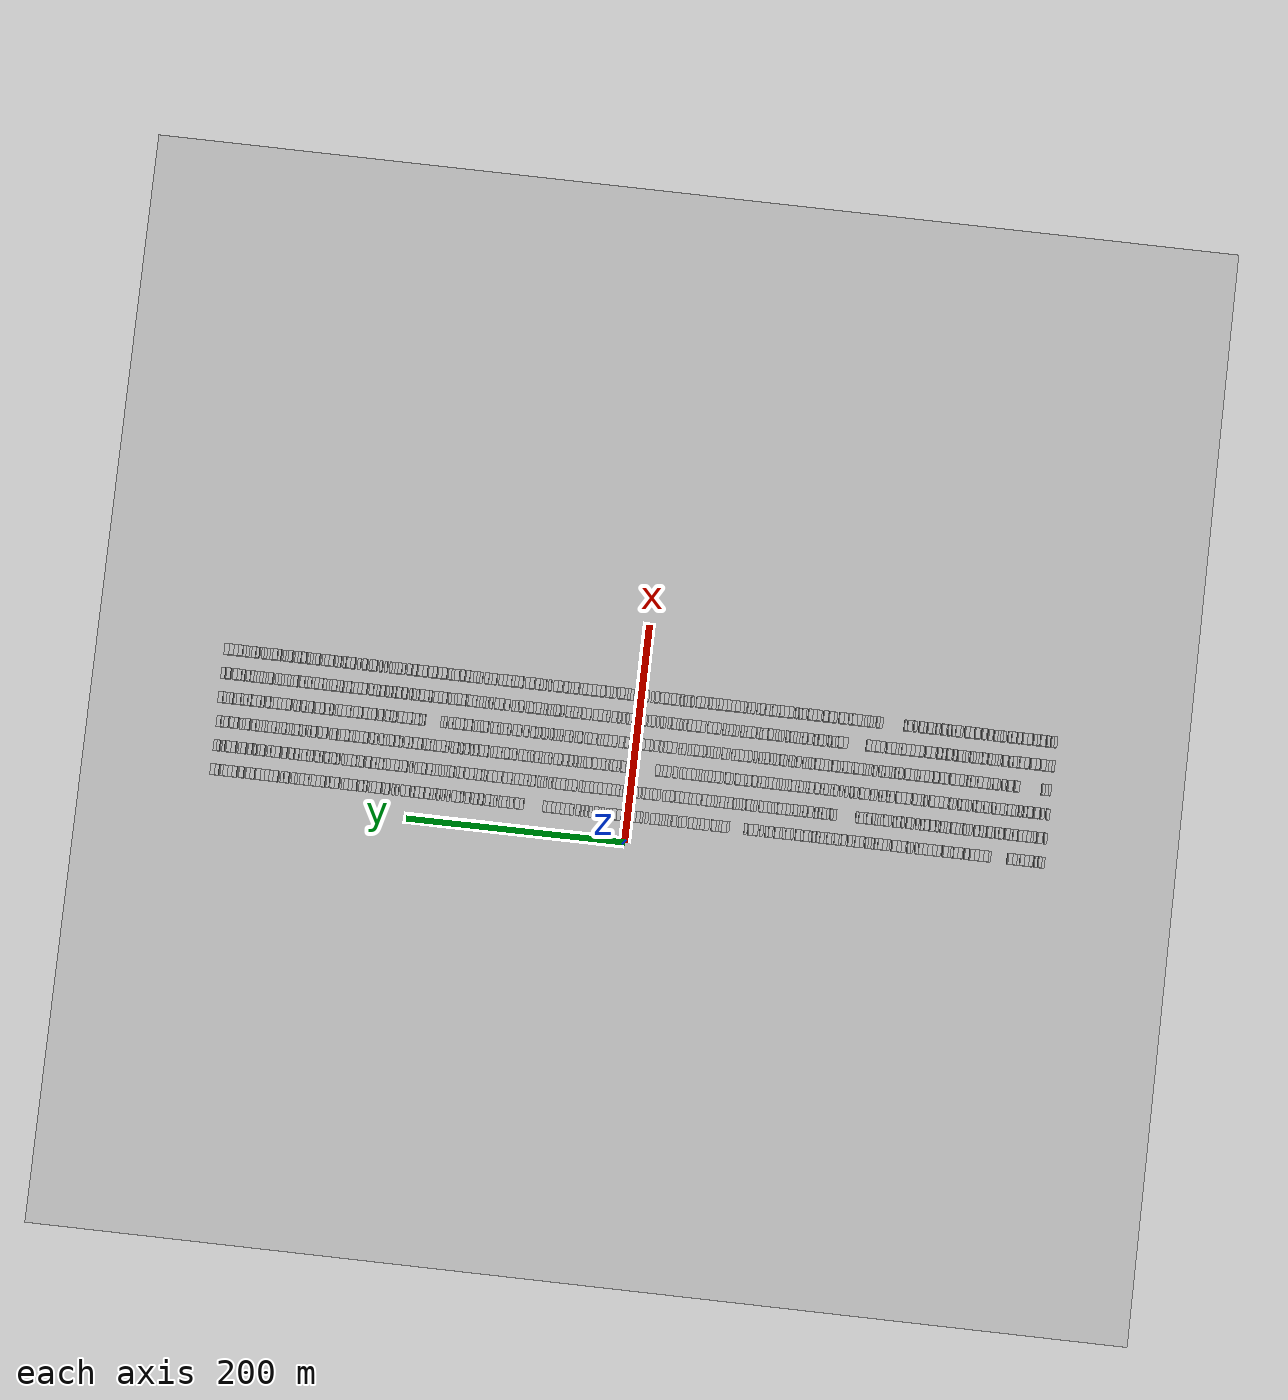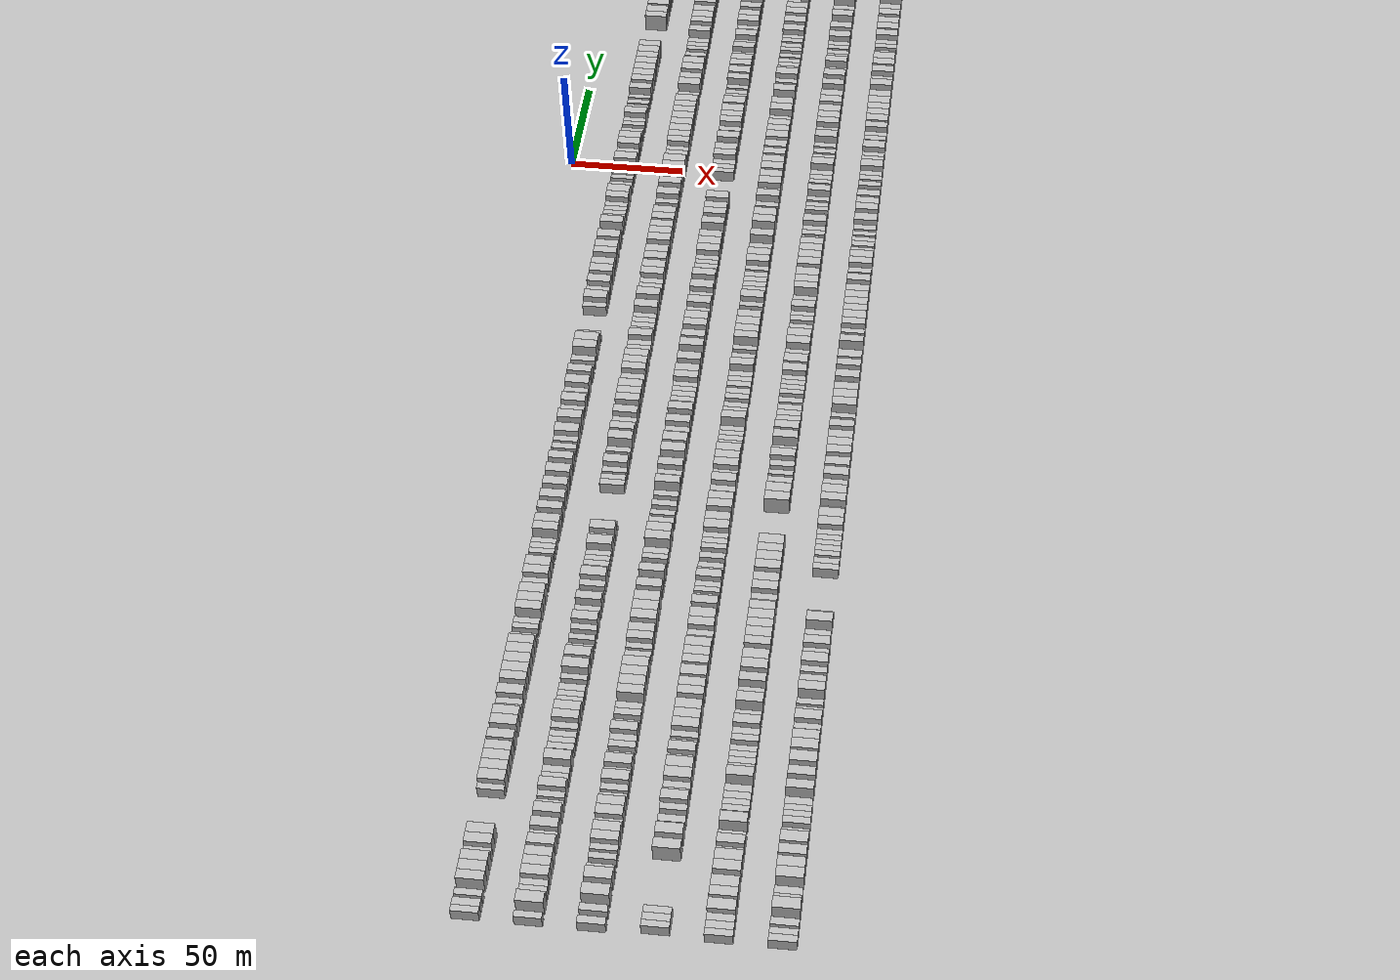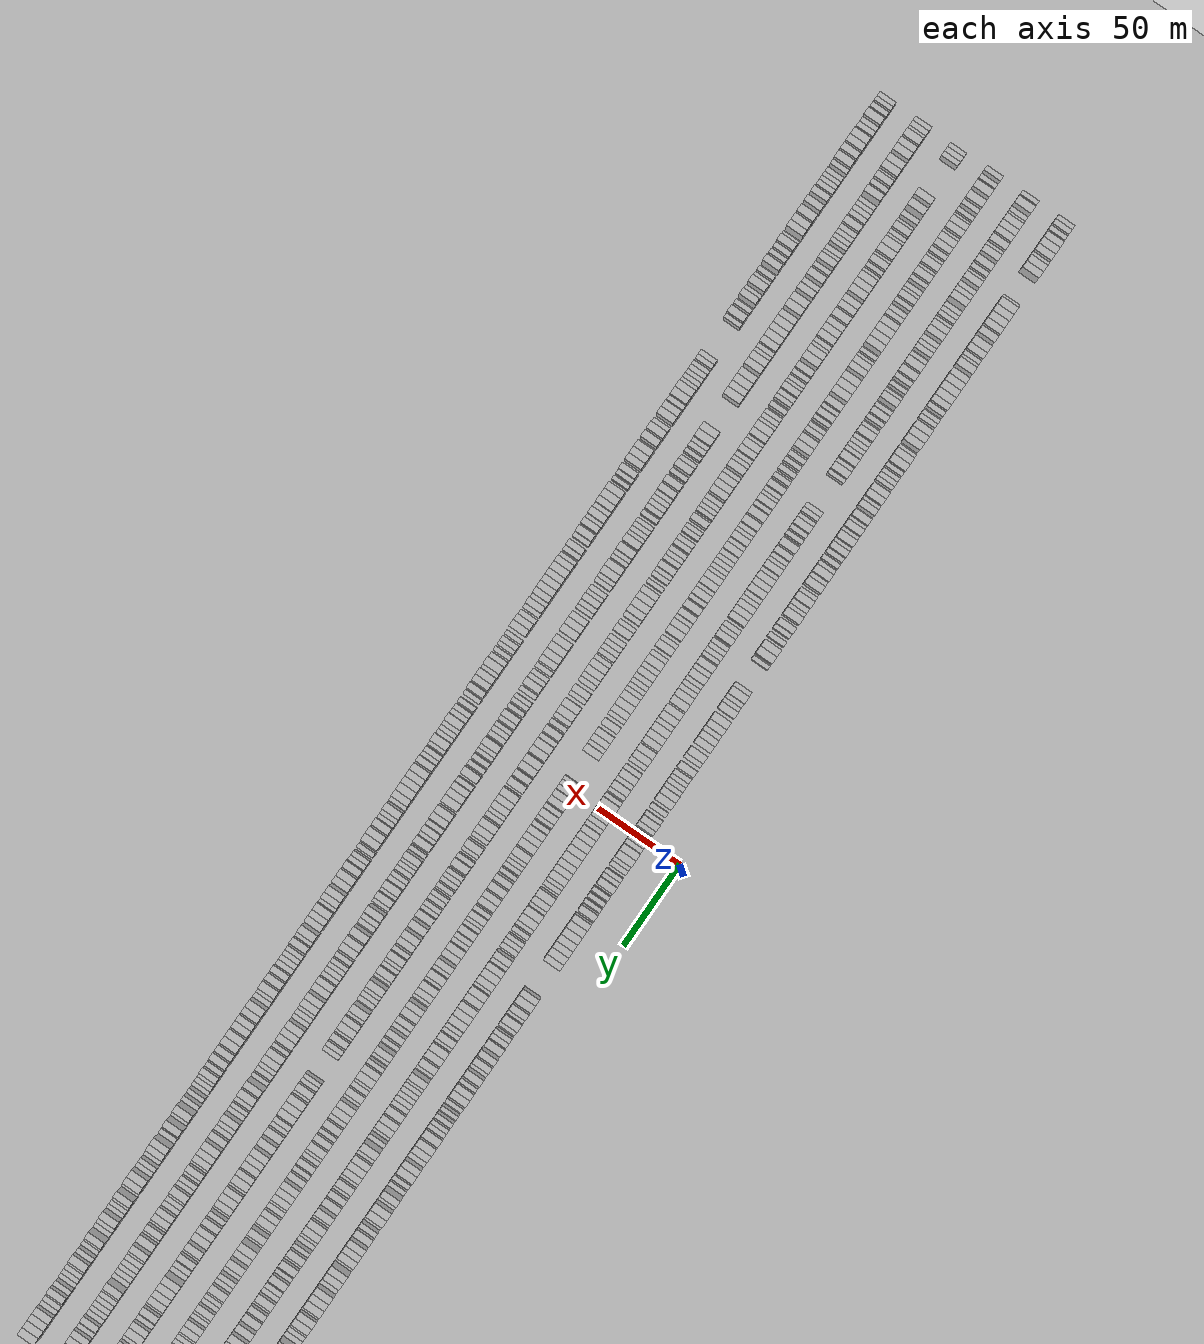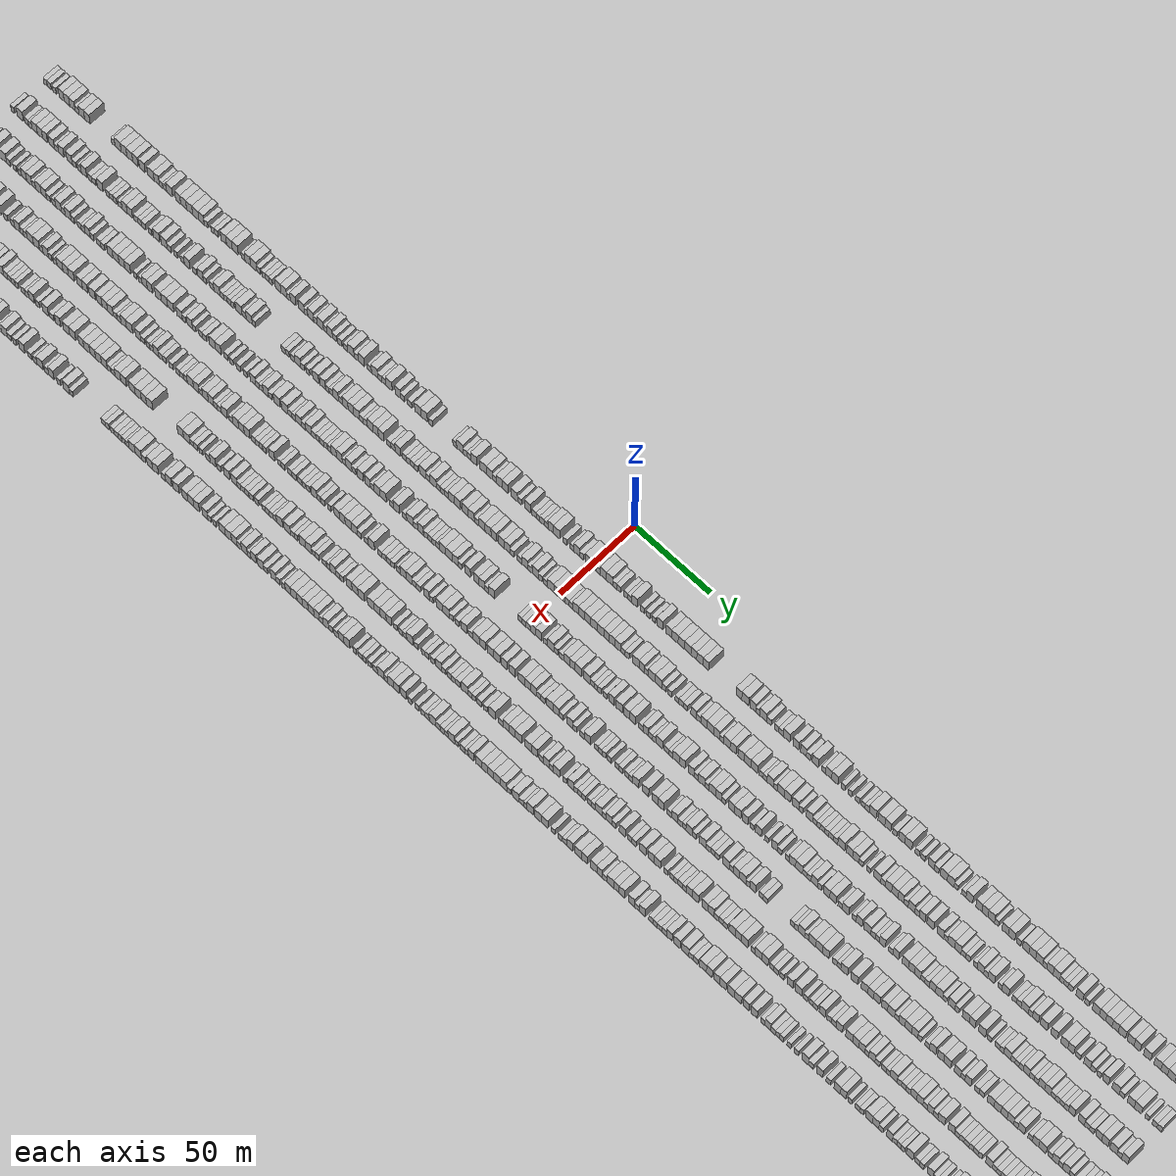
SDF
<?xml version="1.0" encoding="utf-8"?>

<sdf version="1.6">

   <world name="default">

      <gui fullscreen="0">

         <camera name="user_camera">

            <pose>-15 0 4.57585 0 0 0</pose>

            <view_controller>orbit</view_controller>

         </camera>

      </gui>

      <scene>

         <sky>

           <clouds>

             <speed>12</speed>

           </clouds>

         </sky>

         <ambient>0.4 0.4 0.4 1</ambient>

         <background>0.7 0.7 0.7 1</background>

         <shadows>1</shadows>

      </scene>

      <gravity>0 0 -9.8066</gravity>

      <magnetic_field>6e-06 2.3e-05 -4.2e-05</magnetic_field>

      <physics default="0" name="default_physics" type="ode">

         <ode>

            <solver>

               <type>quick</type>

               <iters>10</iters>

               <sor>1.0</sor>

               <use_dynamic_moi_rescaling>0</use_dynamic_moi_rescaling>

            </solver>

            <constraints>

               <cfm>0</cfm>

               <erp>0.2</erp>

               <contact_max_correcting_vel>100</contact_max_correcting_vel>

               <contact_surface_layer>0.001</contact_surface_layer>

            </constraints>

         </ode>

         <max_step_size>0.004</max_step_size>

         <real_time_factor>1</real_time_factor>

         <real_time_update_rate>250</real_time_update_rate>

      </physics>

      <light name="sun" type="directional">

         <cast_shadows>1</cast_shadows>

         <pose>0 0 10 0 0 0</pose>

         <diffuse>0.8 0.8 0.8 1</diffuse>

         <specular>0.2 0.2 0.2 1</specular>

         <attenuation>

            <range>1000</range>

            <constant>0.9</constant>

            <linear>0.01</linear>

            <quadratic>0.001</quadratic>

         </attenuation>

         <direction>-0.5 0.1 -0.9</direction>

      </light>

      <include>

         <name>ground_plane_1</name>

         <uri>model://HANNAS_ground_plane</uri>

         <pose>0 0 0  0 0 0</pose>

      </include>

      <include>

         <name>ground_plane_2</name>

         <uri>model://HANNAS_ground_plane</uri>

         <pose>100 0 0  0 0 0</pose>

      </include>

      <model name="building_1">

         <static>1</static>

         <pose frame="">25.0000 -378.7344 0 0.000000 0.000000 0.000000</pose>

         <link name="link">

            <pose frame="">0 0 3.00 0 0 0</pose>

            <collision name="collision">

               <geometry>

                  <box>

                     <size>10.0000 2.5312 6.0000</size>

                  </box>

               </geometry>

               <max_contacts>10</max_contacts>

               <surface>

                  <contact>

                     <ode/>

                  </contact>

                  <bounce/>

                  <friction>

                     <torsional>

                        <ode/>

                     </torsional>

                     <ode/>

                  </friction>

               </surface>

            </collision>

            <visual name="visual">

               <cast_shadows>0</cast_shadows>

               <geometry>

                  <box>

                     <size>10.0000 2.5312 6.0000</size>

                  </box>

               </geometry>

               <material>

                  <script>

                     <uri>model://HANNAS_wall/materials/scripts</uri>

                     <uri>model://HANNAS_wall/materials/textures</uri>

                     <name>vrc/HANNAS_wall</name>

                  </script>

               </material>

            </visual>

            <self_collide>0</self_collide>

            <enable_wind>0</enable_wind>

            <kinematic>0</kinematic>

         </link>

      </model>

      <model name="building_2">

         <static>1</static>

         <pose frame="">25.0000 -375.9882 0 0.000000 0.000000 0.000000</pose>

         <link name="link">

            <pose frame="">0 0 3.00 0 0 0</pose>

            <collision name="collision">

               <geometry>

                  <box>

                     <size>10.0000 2.9612 6.0000</size>

                  </box>

               </geometry>

               <max_contacts>10</max_contacts>

               <surface>

                  <contact>

                     <ode/>

                  </contact>

                  <bounce/>

                  <friction>

                     <torsional>

                        <ode/>

                     </torsional>

                     <ode/>

                  </friction>

               </surface>

            </collision>

            <visual name="visual">

               <cast_shadows>0</cast_shadows>

               <geometry>

                  <box>

                     <size>10.0000 2.9612 6.0000</size>

                  </box>

               </geometry>

               <material>

                  <script>

                     <uri>model://HANNAS_wall/materials/scripts</uri>

                     <uri>model://HANNAS_wall/materials/textures</uri>

                     <name>vrc/HANNAS_wall</name>

                  </script>

               </material>

            </visual>

            <self_collide>0</self_collide>

            <enable_wind>0</enable_wind>

            <kinematic>0</kinematic>

         </link>

      </model>

      <model name="building_3">

         <static>1</static>

         <pose frame="">25.0000 -372.2033 0 0.000000 0.000000 0.000000</pose>

         <link name="link">

            <pose frame="">0 0 3.00 0 0 0</pose>

            <collision name="collision">

               <geometry>

                  <box>

                     <size>10.0000 2.6086 6.0000</size>

                  </box>

               </geometry>

               <max_contacts>10</max_contacts>

               <surface>

                  <contact>

                     <ode/>

                  </contact>

                  <bounce/>

                  <friction>

                     <torsional>

                        <ode/>

                     </torsional>

                     <ode/>

                  </friction>

               </surface>

            </collision>

            <visual name="visual">

               <cast_shadows>0</cast_shadows>

               <geometry>

                  <box>

                     <size>10.0000 2.6086 6.0000</size>

                  </box>

               </geometry>

               <material>

                  <script>

                     <uri>model://HANNAS_wall/materials/scripts</uri>

                     <uri>model://HANNAS_wall/materials/textures</uri>

                     <name>vrc/HANNAS_wall</name>

                  </script>

               </material>

            </visual>

            <self_collide>0</self_collide>

            <enable_wind>0</enable_wind>

            <kinematic>0</kinematic>

         </link>

      </model>

      <model name="building_4">

         <static>1</static>

         <pose frame="">25.0000 -367.0871 0 0.000000 0.000000 0.000000</pose>

         <link name="link">

            <pose frame="">0 0 4.50 0 0 0</pose>

            <collision name="collision">

               <geometry>

                  <box>

                     <size>10.0000 3.6238 9.0000</size>

                  </box>

               </geometry>

               <max_contacts>10</max_contacts>

               <surface>

                  <contact>

                     <ode/>

                  </contact>

                  <bounce/>

                  <friction>

                     <torsional>

                        <ode/>

                     </torsional>

                     <ode/>

                  </friction>

               </surface>

            </collision>

            <visual name="visual">

               <cast_shadows>0</cast_shadows>

               <geometry>

                  <box>

                     <size>10.0000 3.6238 9.0000</size>

                  </box>

               </geometry>

               <material>

                  <script>

                     <uri>model://HANNAS_wall/materials/scripts</uri>

                     <uri>model://HANNAS_wall/materials/textures</uri>

                     <name>vrc/HANNAS_wall</name>

                  </script>

               </material>

            </visual>

            <self_collide>0</self_collide>

            <enable_wind>0</enable_wind>

            <kinematic>0</kinematic>

         </link>

      </model>

      <model name="building_5">

         <static>1</static>

         <pose frame="">25.0000 -363.2377 0 0.000000 0.000000 0.000000</pose>

         <link name="link">

            <pose frame="">0 0 4.50 0 0 0</pose>

            <collision name="collision">

               <geometry>

                  <box>

                     <size>10.0000 4.0750 9.0000</size>

                  </box>

               </geometry>

               <max_contacts>10</max_contacts>

               <surface>

                  <contact>

                     <ode/>

                  </contact>

                  <bounce/>

                  <friction>

                     <torsional>

                        <ode/>

                     </torsional>

                     <ode/>

                  </friction>

               </surface>

            </collision>

            <visual name="visual">

               <cast_shadows>0</cast_shadows>

               <geometry>

                  <box>

                     <size>10.0000 4.0750 9.0000</size>

                  </box>

               </geometry>

               <material>

                  <script>

                     <uri>model://HANNAS_wall/materials/scripts</uri>

                     <uri>model://HANNAS_wall/materials/textures</uri>

                     <name>vrc/HANNAS_wall</name>

                  </script>

               </material>

            </visual>

            <self_collide>0</self_collide>

            <enable_wind>0</enable_wind>

            <kinematic>0</kinematic>

         </link>

      </model>

      <model name="building_6">

         <static>1</static>

         <pose frame="">25.0000 -359.2548 0 0.000000 0.000000 0.000000</pose>

         <link name="link">

            <pose frame="">0 0 4.50 0 0 0</pose>

            <collision name="collision">

               <geometry>

                  <box>

                     <size>10.0000 3.8908 9.0000</size>

                  </box>

               </geometry>

               <max_contacts>10</max_contacts>

               <surface>

                  <contact>

                     <ode/>

                  </contact>

                  <bounce/>

                  <friction>

                     <torsional>

                        <ode/>

                     </torsional>

                     <ode/>

                  </friction>

               </surface>

            </collision>

            <visual name="visual">

               <cast_shadows>0</cast_shadows>

               <geometry>

                  <box>

                     <size>10.0000 3.8908 9.0000</size>

                  </box>

               </geometry>

               <material>

                  <script>

                     <uri>model://HANNAS_wall/materials/scripts</uri>

                     <uri>model://HANNAS_wall/materials/textures</uri>

                     <name>vrc/HANNAS_wall</name>

                  </script>

               </material>

            </visual>

            <self_collide>0</self_collide>

            <enable_wind>0</enable_wind>

            <kinematic>0</kinematic>

         </link>

      </model>

      <model name="building_7">

         <static>1</static>

         <pose frame="">25.0000 -355.8367 0 0.000000 0.000000 0.000000</pose>

         <link name="link">

            <pose frame="">0 0 3.00 0 0 0</pose>

            <collision name="collision">

               <geometry>

                  <box>

                     <size>10.0000 2.9455 6.0000</size>

                  </box>

               </geometry>

               <max_contacts>10</max_contacts>

               <surface>

                  <contact>

                     <ode/>

                  </contact>

                  <bounce/>

                  <friction>

                     <torsional>

                        <ode/>

                     </torsional>

                     <ode/>

                  </friction>

               </surface>

            </collision>

            <visual name="visual">

               <cast_shadows>0</cast_shadows>

               <geometry>

                  <box>

                     <size>10.0000 2.9455 6.0000</size>

                  </box>

               </geometry>

               <material>

                  <script>

                     <uri>model://HANNAS_wall/materials/scripts</uri>

                     <uri>model://HANNAS_wall/materials/textures</uri>

                     <name>vrc/HANNAS_wall</name>

                  </script>

               </material>

            </visual>

            <self_collide>0</self_collide>

            <enable_wind>0</enable_wind>

            <kinematic>0</kinematic>

         </link>

      </model>

      <model name="building_8">

         <static>1</static>

         <pose frame="">25.0000 -352.3905 0 0.000000 0.000000 0.000000</pose>

         <link name="link">

            <pose frame="">0 0 4.50 0 0 0</pose>

            <collision name="collision">

               <geometry>

                  <box>

                     <size>10.0000 3.9468 9.0000</size>

                  </box>

               </geometry>

               <max_contacts>10</max_contacts>

               <surface>

                  <contact>

                     <ode/>

                  </contact>

                  <bounce/>

                  <friction>

                     <torsional>

                        <ode/>

                     </torsional>

                     <ode/>

                  </friction>

               </surface>

            </collision>

            <visual name="visual">

               <cast_shadows>0</cast_shadows>

               <geometry>

                  <box>

                     <size>10.0000 3.9468 9.0000</size>

                  </box>

               </geometry>

               <material>

                  <script>

                     <uri>model://HANNAS_wall/materials/scripts</uri>

                     <uri>model://HANNAS_wall/materials/textures</uri>

                     <name>vrc/HANNAS_wall</name>

                  </script>

               </material>

            </visual>

            <self_collide>0</self_collide>

            <enable_wind>0</enable_wind>

            <kinematic>0</kinematic>

         </link>

      </model>

      <model name="building_9">

         <static>1</static>

         <pose frame="">25.0000 -348.4032 0 0.000000 0.000000 0.000000</pose>

         <link name="link">

            <pose frame="">0 0 4.50 0 0 0</pose>

            <collision name="collision">

               <geometry>

                  <box>

                     <size>10.0000 4.0279 9.0000</size>

                  </box>

               </geometry>

               <max_contacts>10</max_contacts>

               <surface>

                  <contact>

                     <ode/>

                  </contact>

                  <bounce/>

                  <friction>

                     <torsional>

                        <ode/>

                     </torsional>

                     <ode/>

                  </friction>

               </surface>

            </collision>

            <visual name="visual">

               <cast_shadows>0</cast_shadows>

               <geometry>

                  <box>

                     <size>10.0000 4.0279 9.0000</size>

                  </box>

               </geometry>

               <material>

                  <script>

                     <uri>model://HANNAS_wall/materials/scripts</uri>

                     <uri>model://HANNAS_wall/materials/textures</uri>

                     <name>vrc/HANNAS_wall</name>

                  </script>

               </material>

            </visual>

            <self_collide>0</self_collide>

            <enable_wind>0</enable_wind>

            <kinematic>0</kinematic>

         </link>

      </model>

      <model name="building_10">

         <static>1</static>

         <pose frame="">25.0000 -329.7060 0 0.000000 0.000000 0.000000</pose>

         <link name="link">

            <pose frame="">0 0 3.00 0 0 0</pose>

            <collision name="collision">

               <geometry>

                  <box>

                     <size>10.0000 2.4555 6.0000</size>

                  </box>

               </geometry>

               <max_contacts>10</max_contacts>

               <surface>

                  <contact>

                     <ode/>

                  </contact>

                  <bounce/>

                  <friction>

                     <torsional>

                        <ode/>

                     </torsional>

                     <ode/>

                  </friction>

               </surface>

            </collision>

            <visual name="visual">

               <cast_shadows>0</cast_shadows>

               <geometry>

                  <box>

                     <size>10.0000 2.4555 6.0000</size>

                  </box>

               </geometry>

               <material>

                  <script>

                     <uri>model://HANNAS_wall/materials/scripts</uri>

                     <uri>model://HANNAS_wall/materials/textures</uri>

                     <name>vrc/HANNAS_wall</name>

                  </script>

               </material>

            </visual>

            <self_collide>0</self_collide>

            <enable_wind>0</enable_wind>

            <kinematic>0</kinematic>

         </link>

      </model>

      <model name="building_11">

         <static>1</static>

         <pose frame="">25.0000 -326.2691 0 0.000000 0.000000 0.000000</pose>

         <link name="link">

            <pose frame="">0 0 4.50 0 0 0</pose>

            <collision name="collision">

               <geometry>

                  <box>

                     <size>10.0000 4.4183 9.0000</size>

                  </box>

               </geometry>

               <max_contacts>10</max_contacts>

               <surface>

                  <contact>

                     <ode/>

                  </contact>

                  <bounce/>

                  <friction>

                     <torsional>

                        <ode/>

                     </torsional>

                     <ode/>

                  </friction>

               </surface>

            </collision>

            <visual name="visual">

               <cast_shadows>0</cast_shadows>

               <geometry>

                  <box>

                     <size>10.0000 4.4183 9.0000</size>

                  </box>

               </geometry>

               <material>

                  <script>

                     <uri>model://HANNAS_wall/materials/scripts</uri>

                     <uri>model://HANNAS_wall/materials/textures</uri>

                     <name>vrc/HANNAS_wall</name>

                  </script>

               </material>

            </visual>

            <self_collide>0</self_collide>

            <enable_wind>0</enable_wind>

            <kinematic>0</kinematic>

         </link>

      </model>

      <model name="building_12">

         <static>1</static>

         <pose frame="">25.0000 -322.0150 0 0.000000 0.000000 0.000000</pose>

         <link name="link">

            <pose frame="">0 0 4.50 0 0 0</pose>

            <collision name="collision">

               <geometry>

                  <box>

                     <size>10.0000 4.0899 9.0000</size>

                  </box>

               </geometry>

               <max_contacts>10</max_contacts>

               <surface>

                  <contact>

                     <ode/>

                  </contact>

                  <bounce/>

                  <friction>

                     <torsional>

                        <ode/>

                     </torsional>

                     <ode/>

                  </friction>

               </surface>

            </collision>

            <visual name="visual">

               <cast_shadows>0</cast_shadows>

               <geometry>

                  <box>

                     <size>10.0000 4.0899 9.0000</size>

                  </box>

               </geometry>

               <material>

                  <script>

                     <uri>model://HANNAS_wall/materials/scripts</uri>

                     <uri>model://HANNAS_wall/materials/textures</uri>

                     <name>vrc/HANNAS_wall</name>

                  </script>

               </material>

            </visual>

            <self_collide>0</self_collide>

            <enable_wind>0</enable_wind>

            <kinematic>0</kinematic>

         </link>

      </model>

      <model name="building_13">

         <static>1</static>

         <pose frame="">25.0000 -317.8517 0 0.000000 0.000000 0.000000</pose>

         <link name="link">

            <pose frame="">0 0 4.50 0 0 0</pose>

            <collision name="collision">

               <geometry>

                  <box>

                     <size>10.0000 4.2367 9.0000</size>

                  </box>

               </geometry>

               <max_contacts>10</max_contacts>

               <surface>

                  <contact>

                     <ode/>

                  </contact>

                  <bounce/>

                  <friction>

                     <torsional>

                        <ode/>

                     </torsional>

                     <ode/>

                  </friction>

               </surface>

            </collision>

            <visual name="visual">

               <cast_shadows>0</cast_shadows>

               <geometry>

                  <box>

                     <size>10.0000 4.2367 9.0000</size>

                  </box>

               </geometry>

               <material>

                  <script>

                     <uri>model://HANNAS_wall/materials/scripts</uri>

                     <uri>model://HANNAS_wall/materials/textures</uri>

                     <name>vrc/HANNAS_wall</name>

                  </script>

               </material>

            </visual>

            <self_collide>0</self_collide>

            <enable_wind>0</enable_wind>

            <kinematic>0</kinematic>

         </link>

      </model>

      <model name="building_14">

         <static>1</static>

         <pose frame="">25.0000 -313.8011 0 0.000000 0.000000 0.000000</pose>

         <link name="link">

            <pose frame="">0 0 4.50 0 0 0</pose>

            <collision name="collision">

               <geometry>

                  <box>

                     <size>10.0000 3.8646 9.0000</size>

                  </box>

               </geometry>

               <max_contacts>10</max_contacts>

               <surface>

                  <contact>

                     <ode/>

                  </contact>

                  <bounce/>

                  <friction>

                     <torsional>

                        <ode/>

                     </torsional>

                     <ode/>

                  </friction>

               </surface>

            </collision>

            <visual name="visual">

               <cast_shadows>0</cast_shadows>

               <geometry>

                  <box>

                     <size>10.0000 3.8646 9.0000</size>

                  </box>

               </geometry>

               <material>

                  <script>

                     <uri>model://HANNAS_wall/materials/scripts</uri>

                     <uri>model://HANNAS_wall/materials/textures</uri>

                     <name>vrc/HANNAS_wall</name>

                  </script>

               </material>

            </visual>

            <self_collide>0</self_collide>

            <enable_wind>0</enable_wind>

            <kinematic>0</kinematic>

         </link>

      </model>

      <model name="building_15">

         <static>1</static>

         <pose frame="">25.0000 -308.8838 0 0.000000 0.000000 0.000000</pose>

         <link name="link">

            <pose frame="">0 0 4.50 0 0 0</pose>

            <collision name="collision">

               <geometry>

                  <box>

                     <size>10.0000 3.9699 9.0000</size>

                  </box>

               </geometry>

               <max_contacts>10</max_contacts>

               <surface>

                  <contact>

                     <ode/>

                  </contact>

                  <bounce/>

                  <friction>

                     <torsional>

                        <ode/>

                     </torsional>

                     <ode/>

                  </friction>

               </surface>

            </collision>

            <visual name="visual">

               <cast_shadows>0</cast_shadows>

               <geometry>

                  <box>

                     <size>10.0000 3.9699 9.0000</size>

                  </box>

               </geometry>

               <material>

                  <script>

                     <uri>model://HANNAS_wall/materials/scripts</uri>

                     <uri>model://HANNAS_wall/materials/textures</uri>

                     <name>vrc/HANNAS_wall</name>

                  </script>

               </material>

            </visual>

            <self_collide>0</self_collide>

            <enable_wind>0</enable_wind>

            <kinematic>0</kinematic>

         </link>

      </model>

      <model name="building_16">

         <static>1</static>

         <pose frame="">25.0000 -302.7143 0 0.000000 0.000000 0.000000</pose>

         <link name="link">

            <pose frame="">0 0 4.50 0 0 0</pose>

            <collision name="collision">

               <geometry>

                  <box>

                     <size>10.0000 4.3691 9.0000</size>

                  </box>

               </geometry>

               <max_contacts>10</max_contacts>

               <surface>

                  <contact>

                     <ode/>

                  </contact>

                  <bounce/>

                  <friction>

                     <torsional>

                        <ode/>

                     </torsional>

                     <ode/>

                  </friction>

               </surface>

            </collision>

            <visual name="visual">

               <cast_shadows>0</cast_shadows>

               <geometry>

                  <box>

                     <size>10.0000 4.3691 9.0000</size>

                  </box>

               </geometry>

               <material>

                  <script>

                     <uri>model://HANNAS_wall/materials/scripts</uri>

                     <uri>model://HANNAS_wall/materials/textures</uri>

                     <name>vrc/HANNAS_wall</name>

                  </script>

               </material>

            </visual>

            <self_collide>0</self_collide>

            <enable_wind>0</enable_wind>

            <kinematic>0</kinematic>

         </link>

      </model>

      <model name="building_17">

         <static>1</static>

         <pose frame="">25.0000 -298.6043 0 0.000000 0.000000 0.000000</pose>

         <link name="link">

            <pose frame="">0 0 4.50 0 0 0</pose>

            <collision name="collision">

               <geometry>

                  <box>

                     <size>10.0000 3.8509 9.0000</size>

                  </box>

               </geometry>

               <max_contacts>10</max_contacts>

               <surface>

                  <contact>

                     <ode/>

                  </contact>

                  <bounce/>

                  <friction>

                     <torsional>

                        <ode/>

                     </torsional>

                     <ode/>

                  </friction>

               </surface>

            </collision>

            <visual name="visual">

               <cast_shadows>0</cast_shadows>

               <geometry>

                  <box>

                     <size>10.0000 3.8509 9.0000</size>

                  </box>

               </geometry>

               <material>

                  <script>

                     <uri>model://HANNAS_wall/materials/scripts</uri>

                     <uri>model://HANNAS_wall/materials/textures</uri>

                     <name>vrc/HANNAS_wall</name>

                  </script>

               </material>

            </visual>

            <self_collide>0</self_collide>

            <enable_wind>0</enable_wind>

            <kinematic>0</kinematic>

         </link>

      </model>

      <model name="building_18">

         <static>1</static>

         <pose frame="">25.0000 -295.4414 0 0.000000 0.000000 0.000000</pose>

         <link name="link">

            <pose frame="">0 0 3.00 0 0 0</pose>

            <collision name="collision">

               <geometry>

                  <box>

                     <size>10.0000 2.4750 6.0000</size>

                  </box>

               </geometry>

               <max_contacts>10</max_contacts>

               <surface>

                  <contact>

                     <ode/>

                  </contact>

                  <bounce/>

                  <friction>

                     <torsional>

                        <ode/>

                     </torsional>

                     <ode/>

                  </friction>

               </surface>

            </collision>

            <visual name="visual">

               <cast_shadows>0</cast_shadows>

               <geometry>

                  <box>

                     <size>10.0000 2.4750 6.0000</size>

                  </box>

               </geometry>

               <material>

                  <script>

                     <uri>model://HANNAS_wall/materials/scripts</uri>

                     <uri>model://HANNAS_wall/materials/textures</uri>

                     <name>vrc/HANNAS_wall</name>

                  </script>

               </material>

            </visual>

            <self_collide>0</self_collide>

            <enable_wind>0</enable_wind>

            <kinematic>0</kinematic>

         </link>

      </model>

      <model name="building_19">

         <static>1</static>

         <pose frame="">25.0000 -292.8878 0 0.000000 0.000000 0.000000</pose>

         <link name="link">

            <pose frame="">0 0 3.00 0 0 0</pose>

            <collision name="collision">

               <geometry>

                  <box>

                     <size>10.0000 2.6322 6.0000</size>

                  </box>

               </geometry>

               <max_contacts>10</max_contacts>

               <surface>

                  <contact>

                     <ode/>

                  </contact>

                  <bounce/>

                  <friction>

                     <torsional>

                        <ode/>

                     </torsional>

                     <ode/>

                  </friction>

               </surface>

            </collision>

            <visual name="visual">

               <cast_shadows>0</cast_shadows>

               <geometry>

                  <box>

                     <size>10.0000 2.6322 6.0000</size>

                  </box>

               </geometry>

               <material>

                  <script>

                     <uri>model://HANNAS_wall/materials/scripts</uri>

                     <uri>model://HANNAS_wall/materials/textures</uri>

                     <name>vrc/HANNAS_wall</name>

                  </script>

               </material>

            </visual>

            <self_collide>0</self_collide>

            <enable_wind>0</enable_wind>

            <kinematic>0</kinematic>

         </link>

      </model>

      <model name="building_20">

         <static>1</static>

         <pose frame="">25.0000 -289.3957 0 0.000000 0.000000 0.000000</pose>

         <link name="link">

            <pose frame="">0 0 4.50 0 0 0</pose>

            <collision name="collision">

               <geometry>

                  <box>

                     <size>10.0000 4.3520 9.0000</size>

                  </box>

               </geometry>

               <max_contacts>10</max_contacts>

               <surface>

                  <contact>

                     <ode/>

                  </contact>

                  <bounce/>

                  <friction>

                     <torsional>

                        <ode/>

                     </torsional>

                     <ode/>

                  </friction>

               </surface>

            </collision>

            <visual name="visual">

               <cast_shadows>0</cast_shadows>

               <geometry>

                  <box>

                     <size>10.0000 4.3520 9.0000</size>

                  </box>

               </geometry>

               <material>

                  <script>

                     <uri>model://HANNAS_wall/materials/scripts</uri>

                     <uri>model://HANNAS_wall/materials/textures</uri>

                     <name>vrc/HANNAS_wall</name>

                  </script>

               </material>

            </visual>

            <self_collide>0</self_collide>

            <enable_wind>0</enable_wind>

            <kinematic>0</kinematic>

         </link>

      </model>

      <model name="building_21">

         <static>1</static>

         <pose frame="">25.0000 -283.3655 0 0.000000 0.000000 0.000000</pose>

         <link name="link">

            <pose frame="">0 0 4.50 0 0 0</pose>

            <collision name="collision">

               <geometry>

                  <box>

                     <size>10.0000 3.7083 9.0000</size>

                  </box>

               </geometry>

               <max_contacts>10</max_contacts>

               <surface>

                  <contact>

                     <ode/>

                  </contact>

                  <bounce/>

                  <friction>

                     <torsional>

                        <ode/>

                     </torsional>

                     <ode/>

                  </friction>

               </surface>

            </collision>

            <visual name="visual">

               <cast_shadows>0</cast_shadows>

               <geometry>

                  <box>

                     <size>10.0000 3.7083 9.0000</size>

                  </box>

               </geometry>

               <material>

                  <script>

                     <uri>model://HANNAS_wall/materials/scripts</uri>

                     <uri>model://HANNAS_wall/materials/textures</uri>

                     <name>vrc/HANNAS_wall</name>

                  </script>

               </material>

            </visual>

            <self_collide>0</self_collide>

            <enable_wind>0</enable_wind>

            <kinematic>0</kinematic>

         </link>

      </model>

      <model name="building_22">

         <static>1</static>

         <pose frame="">25.0000 -279.4295 0 0.000000 0.000000 0.000000</pose>

         <link name="link">

            <pose frame="">0 0 4.50 0 0 0</pose>

            <collision name="collision">

               <geometry>

                  <box>

                     <size>10.0000 4.1637 9.0000</size>

                  </box>

               </geometry>

               <max_contacts>10</max_contacts>

               <surface>

                  <contact>

                     <ode/>

                  </contact>

                  <bounce/>

                  <friction>

                     <torsional>

                        <ode/>

                     </torsional>

                     <ode/>

                  </friction>

               </surface>

            </collision>

            <visual name="visual">

               <cast_shadows>0</cast_shadows>

               <geometry>

                  <box>

                     <size>10.0000 4.1637 9.0000</size>

                  </box>

               </geometry>

               <material>

                  <script>

                     <uri>model://HANNAS_wall/materials/scripts</uri>

                     <uri>model://HANNAS_wall/materials/textures</uri>

                     <name>vrc/HANNAS_wall</name>

                  </script>

               </material>

            </visual>

            <self_collide>0</self_collide>

            <enable_wind>0</enable_wind>

            <kinematic>0</kinematic>

         </link>

      </model>

      <model name="building_23">

         <static>1</static>

         <pose frame="">25.0000 -275.1797 0 0.000000 0.000000 0.000000</pose>

         <link name="link">

            <pose frame="">0 0 4.50 0 0 0</pose>

            <collision name="collision">

               <geometry>

                  <box>

                     <size>10.0000 4.3360 9.0000</size>

                  </box>

               </geometry>

               <max_contacts>10</max_contacts>

               <surface>

                  <contact>

                     <ode/>

                  </contact>

                  <bounce/>

                  <friction>

                     <torsional>

                        <ode/>

                     </torsional>

                     <ode/>

                  </friction>

               </surface>

            </collision>

            <visual name="visual">

               <cast_shadows>0</cast_shadows>

               <geometry>

                  <box>

                     <size>10.0000 4.3360 9.0000</size>

                  </box>

               </geometry>

               <material>

                  <script>

                     <uri>model://HANNAS_wall/materials/scripts</uri>

                     <uri>model://HANNAS_wall/materials/textures</uri>

                     <name>vrc/HANNAS_wall</name>

                  </script>

               </material>

            </visual>

            <self_collide>0</self_collide>

            <enable_wind>0</enable_wind>

            <kinematic>0</kinematic>

         </link>

      </model>

      <model name="building_24">

         <static>1</static>

         <pose frame="">25.0000 -270.8225 0 0.000000 0.000000 0.000000</pose>

         <link name="link">

            <pose frame="">0 0 4.50 0 0 0</pose>

            <collision name="collision">

               <geometry>

                  <box>

                     <size>10.0000 4.3785 9.0000</size>

                  </box>

               </geometry>

               <max_contacts>10</max_contacts>

               <surface>

                  <contact>

                     <ode/>

                  </contact>

                  <bounce/>

                  <friction>

                     <torsional>

                        <ode/>

                     </torsional>

                     <ode/>

                  </friction>

               </surface>

            </collision>

            <visual name="visual">

               <cast_shadows>0</cast_shadows>

               <geometry>

                  <box>

                     <size>10.0000 4.3785 9.0000</size>

                  </box>

               </geometry>

               <material>

                  <script>

                     <uri>model://HANNAS_wall/materials/scripts</uri>

                     <uri>model://HANNAS_wall/materials/textures</uri>

                     <name>vrc/HANNAS_wall</name>

                  </script>

               </material>

            </visual>

            <self_collide>0</self_collide>

            <enable_wind>0</enable_wind>

            <kinematic>0</kinematic>

         </link>

      </model>

      <model name="building_25">

         <static>1</static>

         <pose frame="">25.0000 -266.8065 0 0.000000 0.000000 0.000000</pose>

         <link name="link">

            <pose frame="">0 0 4.50 0 0 0</pose>

            <collision name="collision">

               <geometry>

                  <box>

                     <size>10.0000 3.6535 9.0000</size>

                  </box>

               </geometry>

               <max_contacts>10</max_contacts>

               <surface>

                  <contact>

                     <ode/>

                  </contact>

                  <bounce/>

                  <friction>

                     <torsional>

                        <ode/>

                     </torsional>

                     <ode/>

                  </friction>

               </surface>

            </collision>

            <visual name="visual">

               <cast_shadows>0</cast_shadows>

               <geometry>

                  <box>

                     <size>10.0000 3.6535 9.0000</size>

                  </box>

               </geometry>

               <material>

                  <script>

                     <uri>model://HANNAS_wall/materials/scripts</uri>

                     <uri>model://HANNAS_wall/materials/textures</uri>

                     <name>vrc/HANNAS_wall</name>

                  </script>

               </material>

            </visual>

            <self_collide>0</self_collide>

            <enable_wind>0</enable_wind>

            <kinematic>0</kinematic>

         </link>

      </model>

      <model name="building_26">

         <static>1</static>

         <pose frame="">25.0000 -263.5248 0 0.000000 0.000000 0.000000</pose>

         <link name="link">

            <pose frame="">0 0 3.00 0 0 0</pose>

            <collision name="collision">

               <geometry>

                  <box>

                     <size>10.0000 2.9098 6.0000</size>

                  </box>

               </geometry>

               <max_contacts>10</max_contacts>

               <surface>

                  <contact>

                     <ode/>

                  </contact>

                  <bounce/>

                  <friction>

                     <torsional>

                        <ode/>

                     </torsional>

                     <ode/>

                  </friction>

               </surface>

            </collision>

            <visual name="visual">

               <cast_shadows>0</cast_shadows>

               <geometry>

                  <box>

                     <size>10.0000 2.9098 6.0000</size>

                  </box>

               </geometry>

               <material>

                  <script>

                     <uri>model://HANNAS_wall/materials/scripts</uri>

                     <uri>model://HANNAS_wall/materials/textures</uri>

                     <name>vrc/HANNAS_wall</name>

                  </script>

               </material>

            </visual>

            <self_collide>0</self_collide>

            <enable_wind>0</enable_wind>

            <kinematic>0</kinematic>

         </link>

      </model>

      <model name="building_27">

         <static>1</static>

         <pose frame="">25.0000 -258.8605 0 0.000000 0.000000 0.000000</pose>

         <link name="link">

            <pose frame="">0 0 3.00 0 0 0</pose>

            <collision name="collision">

               <geometry>

                  <box>

                     <size>10.0000 2.4188 6.0000</size>

                  </box>

               </geometry>

               <max_contacts>10</max_contacts>

               <surface>

                  <contact>

                     <ode/>

                  </contact>

                  <bounce/>

                  <friction>

                     <torsional>

                        <ode/>

                     </torsional>

                     <ode/>

                  </friction>

               </surface>

            </collision>

            <visual name="visual">

               <cast_shadows>0</cast_shadows>

               <geometry>

                  <box>

                     <size>10.0000 2.4188 6.0000</size>

                  </box>

               </geometry>

               <material>

                  <script>

                     <uri>model://HANNAS_wall/materials/scripts</uri>

                     <uri>model://HANNAS_wall/materials/textures</uri>

                     <name>vrc/HANNAS_wall</name>

                  </script>

               </material>

            </visual>

            <self_collide>0</self_collide>

            <enable_wind>0</enable_wind>

            <kinematic>0</kinematic>

         </link>

      </model>

      <model name="building_28">

         <static>1</static>

         <pose frame="">25.0000 -256.3234 0 0.000000 0.000000 0.000000</pose>

         <link name="link">

            <pose frame="">0 0 3.00 0 0 0</pose>

            <collision name="collision">

               <geometry>

                  <box>

                     <size>10.0000 2.6554 6.0000</size>

                  </box>

               </geometry>

               <max_contacts>10</max_contacts>

               <surface>

                  <contact>

                     <ode/>

                  </contact>

                  <bounce/>

                  <friction>

                     <torsional>

                        <ode/>

                     </torsional>

                     <ode/>

                  </friction>

               </surface>

            </collision>

            <visual name="visual">

               <cast_shadows>0</cast_shadows>

               <geometry>

                  <box>

                     <size>10.0000 2.6554 6.0000</size>

                  </box>

               </geometry>

               <material>

                  <script>

                     <uri>model://HANNAS_wall/materials/scripts</uri>

                     <uri>model://HANNAS_wall/materials/textures</uri>

                     <name>vrc/HANNAS_wall</name>

                  </script>

               </material>

            </visual>

            <self_collide>0</self_collide>

            <enable_wind>0</enable_wind>

            <kinematic>0</kinematic>

         </link>

      </model>

      <model name="building_29">

         <static>1</static>

         <pose frame="">25.0000 -251.0573 0 0.000000 0.000000 0.000000</pose>

         <link name="link">

            <pose frame="">0 0 4.50 0 0 0</pose>

            <collision name="collision">

               <geometry>

                  <box>

                     <size>10.0000 3.8767 9.0000</size>

                  </box>

               </geometry>

               <max_contacts>10</max_contacts>

               <surface>

                  <contact>

                     <ode/>

                  </contact>

                  <bounce/>

                  <friction>

                     <torsional>

                        <ode/>

                     </torsional>

                     <ode/>

                  </friction>

               </surface>

            </collision>

            <visual name="visual">

               <cast_shadows>0</cast_shadows>

               <geometry>

                  <box>

                     <size>10.0000 3.8767 9.0000</size>

                  </box>

               </geometry>

               <material>

                  <script>

                     <uri>model://HANNAS_wall/materials/scripts</uri>

                     <uri>model://HANNAS_wall/materials/textures</uri>

                     <name>vrc/HANNAS_wall</name>

                  </script>

               </material>

            </visual>

            <self_collide>0</self_collide>

            <enable_wind>0</enable_wind>

            <kinematic>0</kinematic>

         </link>

      </model>

      <model name="building_30">

         <static>1</static>

         <pose frame="">25.0000 -247.0686 0 0.000000 0.000000 0.000000</pose>

         <link name="link">

            <pose frame="">0 0 4.50 0 0 0</pose>

            <collision name="collision">

               <geometry>

                  <box>

                     <size>10.0000 4.1009 9.0000</size>

                  </box>

               </geometry>

               <max_contacts>10</max_contacts>

               <surface>

                  <contact>

                     <ode/>

                  </contact>

                  <bounce/>

                  <friction>

                     <torsional>

                        <ode/>

                     </torsional>

                     <ode/>

                  </friction>

               </surface>

            </collision>

            <visual name="visual">

               <cast_shadows>0</cast_shadows>

               <geometry>

                  <box>

                     <size>10.0000 4.1009 9.0000</size>

                  </box>

               </geometry>

               <material>

                  <script>

                     <uri>model://HANNAS_wall/materials/scripts</uri>

                     <uri>model://HANNAS_wall/materials/textures</uri>

                     <name>vrc/HANNAS_wall</name>

                  </script>

               </material>

            </visual>

            <self_collide>0</self_collide>

            <enable_wind>0</enable_wind>

            <kinematic>0</kinematic>

         </link>

      </model>

      <model name="building_31">

         <static>1</static>

         <pose frame="">25.0000 -242.8872 0 0.000000 0.000000 0.000000</pose>

         <link name="link">

            <pose frame="">0 0 4.50 0 0 0</pose>

            <collision name="collision">

               <geometry>

                  <box>

                     <size>10.0000 4.2619 9.0000</size>

                  </box>

               </geometry>

               <max_contacts>10</max_contacts>

               <surface>

                  <contact>

                     <ode/>

                  </contact>

                  <bounce/>

                  <friction>

                     <torsional>

                        <ode/>

                     </torsional>

                     <ode/>

                  </friction>

               </surface>

            </collision>

            <visual name="visual">

               <cast_shadows>0</cast_shadows>

               <geometry>

                  <box>

                     <size>10.0000 4.2619 9.0000</size>

                  </box>

               </geometry>

               <material>

                  <script>

                     <uri>model://HANNAS_wall/materials/scripts</uri>

                     <uri>model://HANNAS_wall/materials/textures</uri>

                     <name>vrc/HANNAS_wall</name>

                  </script>

               </material>

            </visual>

            <self_collide>0</self_collide>

            <enable_wind>0</enable_wind>

            <kinematic>0</kinematic>

         </link>

      </model>

      <model name="building_32">

         <static>1</static>

         <pose frame="">25.0000 -237.4267 0 0.000000 0.000000 0.000000</pose>

         <link name="link">

            <pose frame="">0 0 3.00 0 0 0</pose>

            <collision name="collision">

               <geometry>

                  <box>

                     <size>10.0000 2.6591 6.0000</size>

                  </box>

               </geometry>

               <max_contacts>10</max_contacts>

               <surface>

                  <contact>

                     <ode/>

                  </contact>

                  <bounce/>

                  <friction>

                     <torsional>

                        <ode/>

                     </torsional>

                     <ode/>

                  </friction>

               </surface>

            </collision>

            <visual name="visual">

               <cast_shadows>0</cast_shadows>

               <geometry>

                  <box>

                     <size>10.0000 2.6591 6.0000</size>

                  </box>

               </geometry>

               <material>

                  <script>

                     <uri>model://HANNAS_wall/materials/scripts</uri>

                     <uri>model://HANNAS_wall/materials/textures</uri>

                     <name>vrc/HANNAS_wall</name>

                  </script>

               </material>

            </visual>

            <self_collide>0</self_collide>

            <enable_wind>0</enable_wind>

            <kinematic>0</kinematic>

         </link>

      </model>

      <model name="building_33">

         <static>1</static>

         <pose frame="">25.0000 -234.1160 0 0.000000 0.000000 0.000000</pose>

         <link name="link">

            <pose frame="">0 0 4.50 0 0 0</pose>

            <collision name="collision">

               <geometry>

                  <box>

                     <size>10.0000 3.9623 9.0000</size>

                  </box>

               </geometry>

               <max_contacts>10</max_contacts>

               <surface>

                  <contact>

                     <ode/>

                  </contact>

                  <bounce/>

                  <friction>

                     <torsional>

                        <ode/>

                     </torsional>

                     <ode/>

                  </friction>

               </surface>

            </collision>

            <visual name="visual">

               <cast_shadows>0</cast_shadows>

               <geometry>

                  <box>

                     <size>10.0000 3.9623 9.0000</size>

                  </box>

               </geometry>

               <material>

                  <script>

                     <uri>model://HANNAS_wall/materials/scripts</uri>

                     <uri>model://HANNAS_wall/materials/textures</uri>

                     <name>vrc/HANNAS_wall</name>

                  </script>

               </material>

            </visual>

            <self_collide>0</self_collide>

            <enable_wind>0</enable_wind>

            <kinematic>0</kinematic>

         </link>

      </model>

      <model name="building_34">

         <static>1</static>

         <pose frame="">25.0000 -229.9554 0 0.000000 0.000000 0.000000</pose>

         <link name="link">

            <pose frame="">0 0 4.50 0 0 0</pose>

            <collision name="collision">

               <geometry>

                  <box>

                     <size>10.0000 4.3589 9.0000</size>

                  </box>

               </geometry>

               <max_contacts>10</max_contacts>

               <surface>

                  <contact>

                     <ode/>

                  </contact>

                  <bounce/>

                  <friction>

                     <torsional>

                        <ode/>

                     </torsional>

                     <ode/>

                  </friction>

               </surface>

            </collision>

            <visual name="visual">

               <cast_shadows>0</cast_shadows>

               <geometry>

                  <box>

                     <size>10.0000 4.3589 9.0000</size>

                  </box>

               </geometry>

               <material>

                  <script>

                     <uri>model://HANNAS_wall/materials/scripts</uri>

                     <uri>model://HANNAS_wall/materials/textures</uri>

                     <name>vrc/HANNAS_wall</name>

                  </script>

               </material>

            </visual>

            <self_collide>0</self_collide>

            <enable_wind>0</enable_wind>

            <kinematic>0</kinematic>

         </link>

      </model>

      <model name="building_35">

         <static>1</static>

         <pose frame="">25.0000 -226.5185 0 0.000000 0.000000 0.000000</pose>

         <link name="link">

            <pose frame="">0 0 3.00 0 0 0</pose>

            <collision name="collision">

               <geometry>

                  <box>

                     <size>10.0000 2.5149 6.0000</size>

                  </box>

               </geometry>

               <max_contacts>10</max_contacts>

               <surface>

                  <contact>

                     <ode/>

                  </contact>

                  <bounce/>

                  <friction>

                     <torsional>

                        <ode/>

                     </torsional>

                     <ode/>

                  </friction>

               </surface>

            </collision>

            <visual name="visual">

               <cast_shadows>0</cast_shadows>

               <geometry>

                  <box>

                     <size>10.0000 2.5149 6.0000</size>

                  </box>

               </geometry>

               <material>

                  <script>

                     <uri>model://HANNAS_wall/materials/scripts</uri>

                     <uri>model://HANNAS_wall/materials/textures</uri>

                     <name>vrc/HANNAS_wall</name>

                  </script>

               </material>

            </visual>

            <self_collide>0</self_collide>

            <enable_wind>0</enable_wind>

            <kinematic>0</kinematic>

         </link>

      </model>

      <model name="building_36">

         <static>1</static>

         <pose frame="">25.0000 -223.0528 0 0.000000 0.000000 0.000000</pose>

         <link name="link">

            <pose frame="">0 0 3.00 0 0 0</pose>

            <collision name="collision">

               <geometry>

                  <box>

                     <size>10.0000 2.4166 6.0000</size>

                  </box>

               </geometry>

               <max_contacts>10</max_contacts>

               <surface>

                  <contact>

                     <ode/>

                  </contact>

                  <bounce/>

                  <friction>

                     <torsional>

                        <ode/>

                     </torsional>

                     <ode/>

                  </friction>

               </surface>

            </collision>

            <visual name="visual">

               <cast_shadows>0</cast_shadows>

               <geometry>

                  <box>

                     <size>10.0000 2.4166 6.0000</size>

                  </box>

               </geometry>

               <material>

                  <script>

                     <uri>model://HANNAS_wall/materials/scripts</uri>

                     <uri>model://HANNAS_wall/materials/textures</uri>

                     <name>vrc/HANNAS_wall</name>

                  </script>

               </material>

            </visual>

            <self_collide>0</self_collide>

            <enable_wind>0</enable_wind>

            <kinematic>0</kinematic>

         </link>

      </model>

      <model name="building_37">

         <static>1</static>

         <pose frame="">25.0000 -220.4855 0 0.000000 0.000000 0.000000</pose>

         <link name="link">

            <pose frame="">0 0 3.00 0 0 0</pose>

            <collision name="collision">

               <geometry>

                  <box>

                     <size>10.0000 2.7179 6.0000</size>

                  </box>

               </geometry>

               <max_contacts>10</max_contacts>

               <surface>

                  <contact>

                     <ode/>

                  </contact>

                  <bounce/>

                  <friction>

                     <torsional>

                        <ode/>

                     </torsional>

                     <ode/>

                  </friction>

               </surface>

            </collision>

            <visual name="visual">

               <cast_shadows>0</cast_shadows>

               <geometry>

                  <box>

                     <size>10.0000 2.7179 6.0000</size>

                  </box>

               </geometry>

               <material>

                  <script>

                     <uri>model://HANNAS_wall/materials/scripts</uri>

                     <uri>model://HANNAS_wall/materials/textures</uri>

                     <name>vrc/HANNAS_wall</name>

                  </script>

               </material>

            </visual>

            <self_collide>0</self_collide>

            <enable_wind>0</enable_wind>

            <kinematic>0</kinematic>

         </link>

      </model>

      <model name="building_38">

         <static>1</static>

         <pose frame="">25.0000 -217.9222 0 0.000000 0.000000 0.000000</pose>

         <link name="link">

            <pose frame="">0 0 3.00 0 0 0</pose>

            <collision name="collision">

               <geometry>

                  <box>

                     <size>10.0000 2.4088 6.0000</size>

                  </box>

               </geometry>

               <max_contacts>10</max_contacts>

               <surface>

                  <contact>

                     <ode/>

                  </contact>

                  <bounce/>

                  <friction>

                     <torsional>

                        <ode/>

                     </torsional>

                     <ode/>

                  </friction>

               </surface>

            </collision>

            <visual name="visual">

               <cast_shadows>0</cast_shadows>

               <geometry>

                  <box>

                     <size>10.0000 2.4088 6.0000</size>

                  </box>

               </geometry>

               <material>

                  <script>

                     <uri>model://HANNAS_wall/materials/scripts</uri>

                     <uri>model://HANNAS_wall/materials/textures</uri>

                     <name>vrc/HANNAS_wall</name>

                  </script>

               </material>

            </visual>

            <self_collide>0</self_collide>

            <enable_wind>0</enable_wind>

            <kinematic>0</kinematic>

         </link>

      </model>

      <model name="building_39">

         <static>1</static>

         <pose frame="">25.0000 -212.7995 0 0.000000 0.000000 0.000000</pose>

         <link name="link">

            <pose frame="">0 0 4.50 0 0 0</pose>

            <collision name="collision">

               <geometry>

                  <box>

                     <size>10.0000 3.8366 9.0000</size>

                  </box>

               </geometry>

               <max_contacts>10</max_contacts>

               <surface>

                  <contact>

                     <ode/>

                  </contact>

                  <bounce/>

                  <friction>

                     <torsional>

                        <ode/>

                     </torsional>

                     <ode/>

                  </friction>

               </surface>

            </collision>

            <visual name="visual">

               <cast_shadows>0</cast_shadows>

               <geometry>

                  <box>

                     <size>10.0000 3.8366 9.0000</size>

                  </box>

               </geometry>

               <material>

                  <script>

                     <uri>model://HANNAS_wall/materials/scripts</uri>

                     <uri>model://HANNAS_wall/materials/textures</uri>

                     <name>vrc/HANNAS_wall</name>

                  </script>

               </material>

            </visual>

            <self_collide>0</self_collide>

            <enable_wind>0</enable_wind>

            <kinematic>0</kinematic>

         </link>

      </model>

      <model name="building_40">

         <static>1</static>

         <pose frame="">25.0000 -208.8753 0 0.000000 0.000000 0.000000</pose>

         <link name="link">

            <pose frame="">0 0 4.50 0 0 0</pose>

            <collision name="collision">

               <geometry>

                  <box>

                     <size>10.0000 4.0117 9.0000</size>

                  </box>

               </geometry>

               <max_contacts>10</max_contacts>

               <surface>

                  <contact>

                     <ode/>

                  </contact>

                  <bounce/>

                  <friction>

                     <torsional>

                        <ode/>

                     </torsional>

                     <ode/>

                  </friction>

               </surface>

            </collision>

            <visual name="visual">

               <cast_shadows>0</cast_shadows>

               <geometry>

                  <box>

                     <size>10.0000 4.0117 9.0000</size>

                  </box>

               </geometry>

               <material>

                  <script>

                     <uri>model://HANNAS_wall/materials/scripts</uri>

                     <uri>model://HANNAS_wall/materials/textures</uri>

                     <name>vrc/HANNAS_wall</name>

                  </script>

               </material>

            </visual>

            <self_collide>0</self_collide>

            <enable_wind>0</enable_wind>

            <kinematic>0</kinematic>

         </link>

      </model>

      <model name="building_41">

         <static>1</static>

         <pose frame="">25.0000 -205.5913 0 0.000000 0.000000 0.000000</pose>

         <link name="link">

            <pose frame="">0 0 3.00 0 0 0</pose>

            <collision name="collision">

               <geometry>

                  <box>

                     <size>10.0000 2.5564 6.0000</size>

                  </box>

               </geometry>

               <max_contacts>10</max_contacts>

               <surface>

                  <contact>

                     <ode/>

                  </contact>

                  <bounce/>

                  <friction>

                     <torsional>

                        <ode/>

                     </torsional>

                     <ode/>

                  </friction>

               </surface>

            </collision>

            <visual name="visual">

               <cast_shadows>0</cast_shadows>

               <geometry>

                  <box>

                     <size>10.0000 2.5564 6.0000</size>

                  </box>

               </geometry>

               <material>

                  <script>

                     <uri>model://HANNAS_wall/materials/scripts</uri>

                     <uri>model://HANNAS_wall/materials/textures</uri>

                     <name>vrc/HANNAS_wall</name>

                  </script>

               </material>

            </visual>

            <self_collide>0</self_collide>

            <enable_wind>0</enable_wind>

            <kinematic>0</kinematic>

         </link>

      </model>

      <model name="building_42">

         <static>1</static>

         <pose frame="">25.0000 -202.4487 0 0.000000 0.000000 0.000000</pose>

         <link name="link">

            <pose frame="">0 0 4.50 0 0 0</pose>

            <collision name="collision">

               <geometry>

                  <box>

                     <size>10.0000 3.7288 9.0000</size>

                  </box>

               </geometry>

               <max_contacts>10</max_contacts>

               <surface>

                  <contact>

                     <ode/>

                  </contact>

                  <bounce/>

                  <friction>

                     <torsional>

                        <ode/>

                     </torsional>

                     <ode/>

                  </friction>

               </surface>

            </collision>

            <visual name="visual">

               <cast_shadows>0</cast_shadows>

               <geometry>

                  <box>

                     <size>10.0000 3.7288 9.0000</size>

                  </box>

               </geometry>

               <material>

                  <script>

                     <uri>model://HANNAS_wall/materials/scripts</uri>

                     <uri>model://HANNAS_wall/materials/textures</uri>

                     <name>vrc/HANNAS_wall</name>

                  </script>

               </material>

            </visual>

            <self_collide>0</self_collide>

            <enable_wind>0</enable_wind>

            <kinematic>0</kinematic>

         </link>

      </model>

      <model name="building_43">

         <static>1</static>

         <pose frame="">25.0000 -196.5522 0 0.000000 0.000000 0.000000</pose>

         <link name="link">

            <pose frame="">0 0 4.50 0 0 0</pose>

            <collision name="collision">

               <geometry>

                  <box>

                     <size>10.0000 4.0642 9.0000</size>

                  </box>

               </geometry>

               <max_contacts>10</max_contacts>

               <surface>

                  <contact>

                     <ode/>

                  </contact>

                  <bounce/>

                  <friction>

                     <torsional>

                        <ode/>

                     </torsional>

                     <ode/>

                  </friction>

               </surface>

            </collision>

            <visual name="visual">

               <cast_shadows>0</cast_shadows>

               <geometry>

                  <box>

                     <size>10.0000 4.0642 9.0000</size>

                  </box>

               </geometry>

               <material>

                  <script>

                     <uri>model://HANNAS_wall/materials/scripts</uri>

                     <uri>model://HANNAS_wall/materials/textures</uri>

                     <name>vrc/HANNAS_wall</name>

                  </script>

               </material>

            </visual>

            <self_collide>0</self_collide>

            <enable_wind>0</enable_wind>

            <kinematic>0</kinematic>

         </link>

      </model>

      <model name="building_44">

         <static>1</static>

         <pose frame="">25.0000 -193.3092 0 0.000000 0.000000 0.000000</pose>

         <link name="link">

            <pose frame="">0 0 3.00 0 0 0</pose>

            <collision name="collision">

               <geometry>

                  <box>

                     <size>10.0000 2.4218 6.0000</size>

                  </box>

               </geometry>

               <max_contacts>10</max_contacts>

               <surface>

                  <contact>

                     <ode/>

                  </contact>

                  <bounce/>

                  <friction>

                     <torsional>

                        <ode/>

                     </torsional>

                     <ode/>

                  </friction>

               </surface>

            </collision>

            <visual name="visual">

               <cast_shadows>0</cast_shadows>

               <geometry>

                  <box>

                     <size>10.0000 2.4218 6.0000</size>

                  </box>

               </geometry>

               <material>

                  <script>

                     <uri>model://HANNAS_wall/materials/scripts</uri>

                     <uri>model://HANNAS_wall/materials/textures</uri>

                     <name>vrc/HANNAS_wall</name>

                  </script>

               </material>

            </visual>

            <self_collide>0</self_collide>

            <enable_wind>0</enable_wind>

            <kinematic>0</kinematic>

         </link>

      </model>

      <model name="building_45">

         <static>1</static>

         <pose frame="">25.0000 -190.0802 0 0.000000 0.000000 0.000000</pose>

         <link name="link">

            <pose frame="">0 0 4.50 0 0 0</pose>

            <collision name="collision">

               <geometry>

                  <box>

                     <size>10.0000 4.0363 9.0000</size>

                  </box>

               </geometry>

               <max_contacts>10</max_contacts>

               <surface>

                  <contact>

                     <ode/>

                  </contact>

                  <bounce/>

                  <friction>

                     <torsional>

                        <ode/>

                     </torsional>

                     <ode/>

                  </friction>

               </surface>

            </collision>

            <visual name="visual">

               <cast_shadows>0</cast_shadows>

               <geometry>

                  <box>

                     <size>10.0000 4.0363 9.0000</size>

                  </box>

               </geometry>

               <material>

                  <script>

                     <uri>model://HANNAS_wall/materials/scripts</uri>

                     <uri>model://HANNAS_wall/materials/textures</uri>

                     <name>vrc/HANNAS_wall</name>

                  </script>

               </material>

            </visual>

            <self_collide>0</self_collide>

            <enable_wind>0</enable_wind>

            <kinematic>0</kinematic>

         </link>

      </model>

      <model name="building_46">

         <static>1</static>

         <pose frame="">25.0000 -186.8166 0 0.000000 0.000000 0.000000</pose>

         <link name="link">

            <pose frame="">0 0 3.00 0 0 0</pose>

            <collision name="collision">

               <geometry>

                  <box>

                     <size>10.0000 2.4908 6.0000</size>

                  </box>

               </geometry>

               <max_contacts>10</max_contacts>

               <surface>

                  <contact>

                     <ode/>

                  </contact>

                  <bounce/>

                  <friction>

                     <torsional>

                        <ode/>

                     </torsional>

                     <ode/>

                  </friction>

               </surface>

            </collision>

            <visual name="visual">

               <cast_shadows>0</cast_shadows>

               <geometry>

                  <box>

                     <size>10.0000 2.4908 6.0000</size>

                  </box>

               </geometry>

               <material>

                  <script>

                     <uri>model://HANNAS_wall/materials/scripts</uri>

                     <uri>model://HANNAS_wall/materials/textures</uri>

                     <name>vrc/HANNAS_wall</name>

                  </script>

               </material>

            </visual>

            <self_collide>0</self_collide>

            <enable_wind>0</enable_wind>

            <kinematic>0</kinematic>

         </link>

      </model>

      <model name="building_47">

         <static>1</static>

         <pose frame="">25.0000 -183.3786 0 0.000000 0.000000 0.000000</pose>

         <link name="link">

            <pose frame="">0 0 4.50 0 0 0</pose>

            <collision name="collision">

               <geometry>

                  <box>

                     <size>10.0000 4.3853 9.0000</size>

                  </box>

               </geometry>

               <max_contacts>10</max_contacts>

               <surface>

                  <contact>

                     <ode/>

                  </contact>

                  <bounce/>

                  <friction>

                     <torsional>

                        <ode/>

                     </torsional>

                     <ode/>

                  </friction>

               </surface>

            </collision>

            <visual name="visual">

               <cast_shadows>0</cast_shadows>

               <geometry>

                  <box>

                     <size>10.0000 4.3853 9.0000</size>

                  </box>

               </geometry>

               <material>

                  <script>

                     <uri>model://HANNAS_wall/materials/scripts</uri>

                     <uri>model://HANNAS_wall/materials/textures</uri>

                     <name>vrc/HANNAS_wall</name>

                  </script>

               </material>

            </visual>

            <self_collide>0</self_collide>

            <enable_wind>0</enable_wind>

            <kinematic>0</kinematic>

         </link>

      </model>

      <model name="building_48">

         <static>1</static>

         <pose frame="">25.0000 -179.9439 0 0.000000 0.000000 0.000000</pose>

         <link name="link">

            <pose frame="">0 0 3.00 0 0 0</pose>

            <collision name="collision">

               <geometry>

                  <box>

                     <size>10.0000 2.4842 6.0000</size>

                  </box>

               </geometry>

               <max_contacts>10</max_contacts>

               <surface>

                  <contact>

                     <ode/>

                  </contact>

                  <bounce/>

                  <friction>

                     <torsional>

                        <ode/>

                     </torsional>

                     <ode/>

                  </friction>

               </surface>

            </collision>

            <visual name="visual">

               <cast_shadows>0</cast_shadows>

               <geometry>

                  <box>

                     <size>10.0000 2.4842 6.0000</size>

                  </box>

               </geometry>

               <material>

                  <script>

                     <uri>model://HANNAS_wall/materials/scripts</uri>

                     <uri>model://HANNAS_wall/materials/textures</uri>

                     <name>vrc/HANNAS_wall</name>

                  </script>

               </material>

            </visual>

            <self_collide>0</self_collide>

            <enable_wind>0</enable_wind>

            <kinematic>0</kinematic>

         </link>

      </model>

      <model name="building_49">

         <static>1</static>

         <pose frame="">25.0000 -176.8252 0 0.000000 0.000000 0.000000</pose>

         <link name="link">

            <pose frame="">0 0 4.50 0 0 0</pose>

            <collision name="collision">

               <geometry>

                  <box>

                     <size>10.0000 3.7532 9.0000</size>

                  </box>

               </geometry>

               <max_contacts>10</max_contacts>

               <surface>

                  <contact>

                     <ode/>

                  </contact>

                  <bounce/>

                  <friction>

                     <torsional>

                        <ode/>

                     </torsional>

                     <ode/>

                  </friction>

               </surface>

            </collision>

            <visual name="visual">

               <cast_shadows>0</cast_shadows>

               <geometry>

                  <box>

                     <size>10.0000 3.7532 9.0000</size>

                  </box>

               </geometry>

               <material>

                  <script>

                     <uri>model://HANNAS_wall/materials/scripts</uri>

                     <uri>model://HANNAS_wall/materials/textures</uri>

                     <name>vrc/HANNAS_wall</name>

                  </script>

               </material>

            </visual>

            <self_collide>0</self_collide>

            <enable_wind>0</enable_wind>

            <kinematic>0</kinematic>

         </link>

      </model>

      <model name="building_50">

         <static>1</static>

         <pose frame="">25.0000 -173.5643 0 0.000000 0.000000 0.000000</pose>

         <link name="link">

            <pose frame="">0 0 3.00 0 0 0</pose>

            <collision name="collision">

               <geometry>

                  <box>

                     <size>10.0000 2.7686 6.0000</size>

                  </box>

               </geometry>

               <max_contacts>10</max_contacts>

               <surface>

                  <contact>

                     <ode/>

                  </contact>

                  <bounce/>

                  <friction>

                     <torsional>

                        <ode/>

                     </torsional>

                     <ode/>

                  </friction>

               </surface>

            </collision>

            <visual name="visual">

               <cast_shadows>0</cast_shadows>

               <geometry>

                  <box>

                     <size>10.0000 2.7686 6.0000</size>

                  </box>

               </geometry>

               <material>

                  <script>

                     <uri>model://HANNAS_wall/materials/scripts</uri>

                     <uri>model://HANNAS_wall/materials/textures</uri>

                     <name>vrc/HANNAS_wall</name>

                  </script>

               </material>

            </visual>

            <self_collide>0</self_collide>

            <enable_wind>0</enable_wind>

            <kinematic>0</kinematic>

         </link>

      </model>

      <model name="building_51">

         <static>1</static>

         <pose frame="">25.0000 -169.7473 0 0.000000 0.000000 0.000000</pose>

         <link name="link">

            <pose frame="">0 0 3.00 0 0 0</pose>

            <collision name="collision">

               <geometry>

                  <box>

                     <size>10.0000 2.8655 6.0000</size>

                  </box>

               </geometry>

               <max_contacts>10</max_contacts>

               <surface>

                  <contact>

                     <ode/>

                  </contact>

                  <bounce/>

                  <friction>

                     <torsional>

                        <ode/>

                     </torsional>

                     <ode/>

                  </friction>

               </surface>

            </collision>

            <visual name="visual">

               <cast_shadows>0</cast_shadows>

               <geometry>

                  <box>

                     <size>10.0000 2.8655 6.0000</size>

                  </box>

               </geometry>

               <material>

                  <script>

                     <uri>model://HANNAS_wall/materials/scripts</uri>

                     <uri>model://HANNAS_wall/materials/textures</uri>

                     <name>vrc/HANNAS_wall</name>

                  </script>

               </material>

            </visual>

            <self_collide>0</self_collide>

            <enable_wind>0</enable_wind>

            <kinematic>0</kinematic>

         </link>

      </model>

      <model name="building_52">

         <static>1</static>

         <pose frame="">25.0000 -165.9094 0 0.000000 0.000000 0.000000</pose>

         <link name="link">

            <pose frame="">0 0 3.00 0 0 0</pose>

            <collision name="collision">

               <geometry>

                  <box>

                     <size>10.0000 2.8103 6.0000</size>

                  </box>

               </geometry>

               <max_contacts>10</max_contacts>

               <surface>

                  <contact>

                     <ode/>

                  </contact>

                  <bounce/>

                  <friction>

                     <torsional>

                        <ode/>

                     </torsional>

                     <ode/>

                  </friction>

               </surface>

            </collision>

            <visual name="visual">

               <cast_shadows>0</cast_shadows>

               <geometry>

                  <box>

                     <size>10.0000 2.8103 6.0000</size>

                  </box>

               </geometry>

               <material>

                  <script>

                     <uri>model://HANNAS_wall/materials/scripts</uri>

                     <uri>model://HANNAS_wall/materials/textures</uri>

                     <name>vrc/HANNAS_wall</name>

                  </script>

               </material>

            </visual>

            <self_collide>0</self_collide>

            <enable_wind>0</enable_wind>

            <kinematic>0</kinematic>

         </link>

      </model>

      <model name="building_53">

         <static>1</static>

         <pose frame="">25.0000 -162.2745 0 0.000000 0.000000 0.000000</pose>

         <link name="link">

            <pose frame="">0 0 4.50 0 0 0</pose>

            <collision name="collision">

               <geometry>

                  <box>

                     <size>10.0000 4.4594 9.0000</size>

                  </box>

               </geometry>

               <max_contacts>10</max_contacts>

               <surface>

                  <contact>

                     <ode/>

                  </contact>

                  <bounce/>

                  <friction>

                     <torsional>

                        <ode/>

                     </torsional>

                     <ode/>

                  </friction>

               </surface>

            </collision>

            <visual name="visual">

               <cast_shadows>0</cast_shadows>

               <geometry>

                  <box>

                     <size>10.0000 4.4594 9.0000</size>

                  </box>

               </geometry>

               <material>

                  <script>

                     <uri>model://HANNAS_wall/materials/scripts</uri>

                     <uri>model://HANNAS_wall/materials/textures</uri>

                     <name>vrc/HANNAS_wall</name>

                  </script>

               </material>

            </visual>

            <self_collide>0</self_collide>

            <enable_wind>0</enable_wind>

            <kinematic>0</kinematic>

         </link>

      </model>

      <model name="building_54">

         <static>1</static>

         <pose frame="">25.0000 -158.5952 0 0.000000 0.000000 0.000000</pose>

         <link name="link">

            <pose frame="">0 0 3.00 0 0 0</pose>

            <collision name="collision">

               <geometry>

                  <box>

                     <size>10.0000 2.8992 6.0000</size>

                  </box>

               </geometry>

               <max_contacts>10</max_contacts>

               <surface>

                  <contact>

                     <ode/>

                  </contact>

                  <bounce/>

                  <friction>

                     <torsional>

                        <ode/>

                     </torsional>

                     <ode/>

                  </friction>

               </surface>

            </collision>

            <visual name="visual">

               <cast_shadows>0</cast_shadows>

               <geometry>

                  <box>

                     <size>10.0000 2.8992 6.0000</size>

                  </box>

               </geometry>

               <material>

                  <script>

                     <uri>model://HANNAS_wall/materials/scripts</uri>

                     <uri>model://HANNAS_wall/materials/textures</uri>

                     <name>vrc/HANNAS_wall</name>

                  </script>

               </material>

            </visual>

            <self_collide>0</self_collide>

            <enable_wind>0</enable_wind>

            <kinematic>0</kinematic>

         </link>

      </model>

      <model name="building_55">

         <static>1</static>

         <pose frame="">25.0000 -155.0011 0 0.000000 0.000000 0.000000</pose>

         <link name="link">

            <pose frame="">0 0 4.50 0 0 0</pose>

            <collision name="collision">

               <geometry>

                  <box>

                     <size>10.0000 4.2891 9.0000</size>

                  </box>

               </geometry>

               <max_contacts>10</max_contacts>

               <surface>

                  <contact>

                     <ode/>

                  </contact>

                  <bounce/>

                  <friction>

                     <torsional>

                        <ode/>

                     </torsional>

                     <ode/>

                  </friction>

               </surface>

            </collision>

            <visual name="visual">

               <cast_shadows>0</cast_shadows>

               <geometry>

                  <box>

                     <size>10.0000 4.2891 9.0000</size>

                  </box>

               </geometry>

               <material>

                  <script>

                     <uri>model://HANNAS_wall/materials/scripts</uri>

                     <uri>model://HANNAS_wall/materials/textures</uri>

                     <name>vrc/HANNAS_wall</name>

                  </script>

               </material>

            </visual>

            <self_collide>0</self_collide>

            <enable_wind>0</enable_wind>

            <kinematic>0</kinematic>

         </link>

      </model>

      <model name="building_56">

         <static>1</static>

         <pose frame="">25.0000 -149.4536 0 0.000000 0.000000 0.000000</pose>

         <link name="link">

            <pose frame="">0 0 3.00 0 0 0</pose>

            <collision name="collision">

               <geometry>

                  <box>

                     <size>10.0000 2.8059 6.0000</size>

                  </box>

               </geometry>

               <max_contacts>10</max_contacts>

               <surface>

                  <contact>

                     <ode/>

                  </contact>

                  <bounce/>

                  <friction>

                     <torsional>

                        <ode/>

                     </torsional>

                     <ode/>

                  </friction>

               </surface>

            </collision>

            <visual name="visual">

               <cast_shadows>0</cast_shadows>

               <geometry>

                  <box>

                     <size>10.0000 2.8059 6.0000</size>

                  </box>

               </geometry>

               <material>

                  <script>

                     <uri>model://HANNAS_wall/materials/scripts</uri>

                     <uri>model://HANNAS_wall/materials/textures</uri>

                     <name>vrc/HANNAS_wall</name>

                  </script>

               </material>

            </visual>

            <self_collide>0</self_collide>

            <enable_wind>0</enable_wind>

            <kinematic>0</kinematic>

         </link>

      </model>

      <model name="building_57">

         <static>1</static>

         <pose frame="">25.0000 -145.8993 0 0.000000 0.000000 0.000000</pose>

         <link name="link">

            <pose frame="">0 0 4.50 0 0 0</pose>

            <collision name="collision">

               <geometry>

                  <box>

                     <size>10.0000 4.3028 9.0000</size>

                  </box>

               </geometry>

               <max_contacts>10</max_contacts>

               <surface>

                  <contact>

                     <ode/>

                  </contact>

                  <bounce/>

                  <friction>

                     <torsional>

                        <ode/>

                     </torsional>

                     <ode/>

                  </friction>

               </surface>

            </collision>

            <visual name="visual">

               <cast_shadows>0</cast_shadows>

               <geometry>

                  <box>

                     <size>10.0000 4.3028 9.0000</size>

                  </box>

               </geometry>

               <material>

                  <script>

                     <uri>model://HANNAS_wall/materials/scripts</uri>

                     <uri>model://HANNAS_wall/materials/textures</uri>

                     <name>vrc/HANNAS_wall</name>

                  </script>

               </material>

            </visual>

            <self_collide>0</self_collide>

            <enable_wind>0</enable_wind>

            <kinematic>0</kinematic>

         </link>

      </model>

      <model name="building_58">

         <static>1</static>

         <pose frame="">25.0000 -142.2733 0 0.000000 0.000000 0.000000</pose>

         <link name="link">

            <pose frame="">0 0 3.00 0 0 0</pose>

            <collision name="collision">

               <geometry>

                  <box>

                     <size>10.0000 2.9493 6.0000</size>

                  </box>

               </geometry>

               <max_contacts>10</max_contacts>

               <surface>

                  <contact>

                     <ode/>

                  </contact>

                  <bounce/>

                  <friction>

                     <torsional>

                        <ode/>

                     </torsional>

                     <ode/>

                  </friction>

               </surface>

            </collision>

            <visual name="visual">

               <cast_shadows>0</cast_shadows>

               <geometry>

                  <box>

                     <size>10.0000 2.9493 6.0000</size>

                  </box>

               </geometry>

               <material>

                  <script>

                     <uri>model://HANNAS_wall/materials/scripts</uri>

                     <uri>model://HANNAS_wall/materials/textures</uri>

                     <name>vrc/HANNAS_wall</name>

                  </script>

               </material>

            </visual>

            <self_collide>0</self_collide>

            <enable_wind>0</enable_wind>

            <kinematic>0</kinematic>

         </link>

      </model>

      <model name="building_59">

         <static>1</static>

         <pose frame="">25.0000 -139.5388 0 0.000000 0.000000 0.000000</pose>

         <link name="link">

            <pose frame="">0 0 3.00 0 0 0</pose>

            <collision name="collision">

               <geometry>

                  <box>

                     <size>10.0000 2.5197 6.0000</size>

                  </box>

               </geometry>

               <max_contacts>10</max_contacts>

               <surface>

                  <contact>

                     <ode/>

                  </contact>

                  <bounce/>

                  <friction>

                     <torsional>

                        <ode/>

                     </torsional>

                     <ode/>

                  </friction>

               </surface>

            </collision>

            <visual name="visual">

               <cast_shadows>0</cast_shadows>

               <geometry>

                  <box>

                     <size>10.0000 2.5197 6.0000</size>

                  </box>

               </geometry>

               <material>

                  <script>

                     <uri>model://HANNAS_wall/materials/scripts</uri>

                     <uri>model://HANNAS_wall/materials/textures</uri>

                     <name>vrc/HANNAS_wall</name>

                  </script>

               </material>

            </visual>

            <self_collide>0</self_collide>

            <enable_wind>0</enable_wind>

            <kinematic>0</kinematic>

         </link>

      </model>

      <model name="building_60">

         <static>1</static>

         <pose frame="">25.0000 -136.0544 0 0.000000 0.000000 0.000000</pose>

         <link name="link">

            <pose frame="">0 0 4.50 0 0 0</pose>

            <collision name="collision">

               <geometry>

                  <box>

                     <size>10.0000 4.4490 9.0000</size>

                  </box>

               </geometry>

               <max_contacts>10</max_contacts>

               <surface>

                  <contact>

                     <ode/>

                  </contact>

                  <bounce/>

                  <friction>

                     <torsional>

                        <ode/>

                     </torsional>

                     <ode/>

                  </friction>

               </surface>

            </collision>

            <visual name="visual">

               <cast_shadows>0</cast_shadows>

               <geometry>

                  <box>

                     <size>10.0000 4.4490 9.0000</size>

                  </box>

               </geometry>

               <material>

                  <script>

                     <uri>model://HANNAS_wall/materials/scripts</uri>

                     <uri>model://HANNAS_wall/materials/textures</uri>

                     <name>vrc/HANNAS_wall</name>

                  </script>

               </material>

            </visual>

            <self_collide>0</self_collide>

            <enable_wind>0</enable_wind>

            <kinematic>0</kinematic>

         </link>

      </model>

      <model name="building_61">

         <static>1</static>

         <pose frame="">25.0000 -129.9648 0 0.000000 0.000000 0.000000</pose>

         <link name="link">

            <pose frame="">0 0 4.50 0 0 0</pose>

            <collision name="collision">

               <geometry>

                  <box>

                     <size>10.0000 3.7301 9.0000</size>

                  </box>

               </geometry>

               <max_contacts>10</max_contacts>

               <surface>

                  <contact>

                     <ode/>

                  </contact>

                  <bounce/>

                  <friction>

                     <torsional>

                        <ode/>

                     </torsional>

                     <ode/>

                  </friction>

               </surface>

            </collision>

            <visual name="visual">

               <cast_shadows>0</cast_shadows>

               <geometry>

                  <box>

                     <size>10.0000 3.7301 9.0000</size>

                  </box>

               </geometry>

               <material>

                  <script>

                     <uri>model://HANNAS_wall/materials/scripts</uri>

                     <uri>model://HANNAS_wall/materials/textures</uri>

                     <name>vrc/HANNAS_wall</name>

                  </script>

               </material>

            </visual>

            <self_collide>0</self_collide>

            <enable_wind>0</enable_wind>

            <kinematic>0</kinematic>

         </link>

      </model>

      <model name="building_62">

         <static>1</static>

         <pose frame="">25.0000 -126.7438 0 0.000000 0.000000 0.000000</pose>

         <link name="link">

            <pose frame="">0 0 3.00 0 0 0</pose>

            <collision name="collision">

               <geometry>

                  <box>

                     <size>10.0000 2.7120 6.0000</size>

                  </box>

               </geometry>

               <max_contacts>10</max_contacts>

               <surface>

                  <contact>

                     <ode/>

                  </contact>

                  <bounce/>

                  <friction>

                     <torsional>

                        <ode/>

                     </torsional>

                     <ode/>

                  </friction>

               </surface>

            </collision>

            <visual name="visual">

               <cast_shadows>0</cast_shadows>

               <geometry>

                  <box>

                     <size>10.0000 2.7120 6.0000</size>

                  </box>

               </geometry>

               <material>

                  <script>

                     <uri>model://HANNAS_wall/materials/scripts</uri>

                     <uri>model://HANNAS_wall/materials/textures</uri>

                     <name>vrc/HANNAS_wall</name>

                  </script>

               </material>

            </visual>

            <self_collide>0</self_collide>

            <enable_wind>0</enable_wind>

            <kinematic>0</kinematic>

         </link>

      </model>

      <model name="building_63">

         <static>1</static>

         <pose frame="">25.0000 -121.9091 0 0.000000 0.000000 0.000000</pose>

         <link name="link">

            <pose frame="">0 0 3.00 0 0 0</pose>

            <collision name="collision">

               <geometry>

                  <box>

                     <size>10.0000 2.9574 6.0000</size>

                  </box>

               </geometry>

               <max_contacts>10</max_contacts>

               <surface>

                  <contact>

                     <ode/>

                  </contact>

                  <bounce/>

                  <friction>

                     <torsional>

                        <ode/>

                     </torsional>

                     <ode/>

                  </friction>

               </surface>

            </collision>

            <visual name="visual">

               <cast_shadows>0</cast_shadows>

               <geometry>

                  <box>

                     <size>10.0000 2.9574 6.0000</size>

                  </box>

               </geometry>

               <material>

                  <script>

                     <uri>model://HANNAS_wall/materials/scripts</uri>

                     <uri>model://HANNAS_wall/materials/textures</uri>

                     <name>vrc/HANNAS_wall</name>

                  </script>

               </material>

            </visual>

            <self_collide>0</self_collide>

            <enable_wind>0</enable_wind>

            <kinematic>0</kinematic>

         </link>

      </model>

      <model name="building_64">

         <static>1</static>

         <pose frame="">25.0000 -116.3051 0 0.000000 0.000000 0.000000</pose>

         <link name="link">

            <pose frame="">0 0 4.50 0 0 0</pose>

            <collision name="collision">

               <geometry>

                  <box>

                     <size>10.0000 4.2506 9.0000</size>

                  </box>

               </geometry>

               <max_contacts>10</max_contacts>

               <surface>

                  <contact>

                     <ode/>

                  </contact>

                  <bounce/>

                  <friction>

                     <torsional>

                        <ode/>

                     </torsional>

                     <ode/>

                  </friction>

               </surface>

            </collision>

            <visual name="visual">

               <cast_shadows>0</cast_shadows>

               <geometry>

                  <box>

                     <size>10.0000 4.2506 9.0000</size>

                  </box>

               </geometry>

               <material>

                  <script>

                     <uri>model://HANNAS_wall/materials/scripts</uri>

                     <uri>model://HANNAS_wall/materials/textures</uri>

                     <name>vrc/HANNAS_wall</name>

                  </script>

               </material>

            </visual>

            <self_collide>0</self_collide>

            <enable_wind>0</enable_wind>

            <kinematic>0</kinematic>

         </link>

      </model>

      <model name="building_65">

         <static>1</static>

         <pose frame="">25.0000 -111.9538 0 0.000000 0.000000 0.000000</pose>

         <link name="link">

            <pose frame="">0 0 4.50 0 0 0</pose>

            <collision name="collision">

               <geometry>

                  <box>

                     <size>10.0000 4.4520 9.0000</size>

                  </box>

               </geometry>

               <max_contacts>10</max_contacts>

               <surface>

                  <contact>

                     <ode/>

                  </contact>

                  <bounce/>

                  <friction>

                     <torsional>

                        <ode/>

                     </torsional>

                     <ode/>

                  </friction>

               </surface>

            </collision>

            <visual name="visual">

               <cast_shadows>0</cast_shadows>

               <geometry>

                  <box>

                     <size>10.0000 4.4520 9.0000</size>

                  </box>

               </geometry>

               <material>

                  <script>

                     <uri>model://HANNAS_wall/materials/scripts</uri>

                     <uri>model://HANNAS_wall/materials/textures</uri>

                     <name>vrc/HANNAS_wall</name>

                  </script>

               </material>

            </visual>

            <self_collide>0</self_collide>

            <enable_wind>0</enable_wind>

            <kinematic>0</kinematic>

         </link>

      </model>

      <model name="building_66">

         <static>1</static>

         <pose frame="">25.0000 -107.4496 0 0.000000 0.000000 0.000000</pose>

         <link name="link">

            <pose frame="">0 0 3.00 0 0 0</pose>

            <collision name="collision">

               <geometry>

                  <box>

                     <size>10.0000 2.5565 6.0000</size>

                  </box>

               </geometry>

               <max_contacts>10</max_contacts>

               <surface>

                  <contact>

                     <ode/>

                  </contact>

                  <bounce/>

                  <friction>

                     <torsional>

                        <ode/>

                     </torsional>

                     <ode/>

                  </friction>

               </surface>

            </collision>

            <visual name="visual">

               <cast_shadows>0</cast_shadows>

               <geometry>

                  <box>

                     <size>10.0000 2.5565 6.0000</size>

                  </box>

               </geometry>

               <material>

                  <script>

                     <uri>model://HANNAS_wall/materials/scripts</uri>

                     <uri>model://HANNAS_wall/materials/textures</uri>

                     <name>vrc/HANNAS_wall</name>

                  </script>

               </material>

            </visual>

            <self_collide>0</self_collide>

            <enable_wind>0</enable_wind>

            <kinematic>0</kinematic>

         </link>

      </model>

      <model name="building_67">

         <static>1</static>

         <pose frame="">25.0000 -91.1495 0 0.000000 0.000000 0.000000</pose>

         <link name="link">

            <pose frame="">0 0 3.00 0 0 0</pose>

            <collision name="collision">

               <geometry>

                  <box>

                     <size>10.0000 2.6812 6.0000</size>

                  </box>

               </geometry>

               <max_contacts>10</max_contacts>

               <surface>

                  <contact>

                     <ode/>

                  </contact>

                  <bounce/>

                  <friction>

                     <torsional>

                        <ode/>

                     </torsional>

                     <ode/>

                  </friction>

               </surface>

            </collision>

            <visual name="visual">

               <cast_shadows>0</cast_shadows>

               <geometry>

                  <box>

                     <size>10.0000 2.6812 6.0000</size>

                  </box>

               </geometry>

               <material>

                  <script>

                     <uri>model://HANNAS_wall/materials/scripts</uri>

                     <uri>model://HANNAS_wall/materials/textures</uri>

                     <name>vrc/HANNAS_wall</name>

                  </script>

               </material>

            </visual>

            <self_collide>0</self_collide>

            <enable_wind>0</enable_wind>

            <kinematic>0</kinematic>

         </link>

      </model>

      <model name="building_68">

         <static>1</static>

         <pose frame="">25.0000 -87.5973 0 0.000000 0.000000 0.000000</pose>

         <link name="link">

            <pose frame="">0 0 4.50 0 0 0</pose>

            <collision name="collision">

               <geometry>

                  <box>

                     <size>10.0000 4.4231 9.0000</size>

                  </box>

               </geometry>

               <max_contacts>10</max_contacts>

               <surface>

                  <contact>

                     <ode/>

                  </contact>

                  <bounce/>

                  <friction>

                     <torsional>

                        <ode/>

                     </torsional>

                     <ode/>

                  </friction>

               </surface>

            </collision>

            <visual name="visual">

               <cast_shadows>0</cast_shadows>

               <geometry>

                  <box>

                     <size>10.0000 4.4231 9.0000</size>

                  </box>

               </geometry>

               <material>

                  <script>

                     <uri>model://HANNAS_wall/materials/scripts</uri>

                     <uri>model://HANNAS_wall/materials/textures</uri>

                     <name>vrc/HANNAS_wall</name>

                  </script>

               </material>

            </visual>

            <self_collide>0</self_collide>

            <enable_wind>0</enable_wind>

            <kinematic>0</kinematic>

         </link>

      </model>

      <model name="building_69">

         <static>1</static>

         <pose frame="">25.0000 -84.1186 0 0.000000 0.000000 0.000000</pose>

         <link name="link">

            <pose frame="">0 0 3.00 0 0 0</pose>

            <collision name="collision">

               <geometry>

                  <box>

                     <size>10.0000 2.5343 6.0000</size>

                  </box>

               </geometry>

               <max_contacts>10</max_contacts>

               <surface>

                  <contact>

                     <ode/>

                  </contact>

                  <bounce/>

                  <friction>

                     <torsional>

                        <ode/>

                     </torsional>

                     <ode/>

                  </friction>

               </surface>

            </collision>

            <visual name="visual">

               <cast_shadows>0</cast_shadows>

               <geometry>

                  <box>

                     <size>10.0000 2.5343 6.0000</size>

                  </box>

               </geometry>

               <material>

                  <script>

                     <uri>model://HANNAS_wall/materials/scripts</uri>

                     <uri>model://HANNAS_wall/materials/textures</uri>

                     <name>vrc/HANNAS_wall</name>

                  </script>

               </material>

            </visual>

            <self_collide>0</self_collide>

            <enable_wind>0</enable_wind>

            <kinematic>0</kinematic>

         </link>

      </model>

      <model name="building_70">

         <static>1</static>

         <pose frame="">25.0000 -81.5638 0 0.000000 0.000000 0.000000</pose>

         <link name="link">

            <pose frame="">0 0 3.00 0 0 0</pose>

            <collision name="collision">

               <geometry>

                  <box>

                     <size>10.0000 2.5753 6.0000</size>

                  </box>

               </geometry>

               <max_contacts>10</max_contacts>

               <surface>

                  <contact>

                     <ode/>

                  </contact>

                  <bounce/>

                  <friction>

                     <torsional>

                        <ode/>

                     </torsional>

                     <ode/>

                  </friction>

               </surface>

            </collision>

            <visual name="visual">

               <cast_shadows>0</cast_shadows>

               <geometry>

                  <box>

                     <size>10.0000 2.5753 6.0000</size>

                  </box>

               </geometry>

               <material>

                  <script>

                     <uri>model://HANNAS_wall/materials/scripts</uri>

                     <uri>model://HANNAS_wall/materials/textures</uri>

                     <name>vrc/HANNAS_wall</name>

                  </script>

               </material>

            </visual>

            <self_collide>0</self_collide>

            <enable_wind>0</enable_wind>

            <kinematic>0</kinematic>

         </link>

      </model>

      <model name="building_71">

         <static>1</static>

         <pose frame="">25.0000 -78.1789 0 0.000000 0.000000 0.000000</pose>

         <link name="link">

            <pose frame="">0 0 4.50 0 0 0</pose>

            <collision name="collision">

               <geometry>

                  <box>

                     <size>10.0000 4.1944 9.0000</size>

                  </box>

               </geometry>

               <max_contacts>10</max_contacts>

               <surface>

                  <contact>

                     <ode/>

                  </contact>

                  <bounce/>

                  <friction>

                     <torsional>

                        <ode/>

                     </torsional>

                     <ode/>

                  </friction>

               </surface>

            </collision>

            <visual name="visual">

               <cast_shadows>0</cast_shadows>

               <geometry>

                  <box>

                     <size>10.0000 4.1944 9.0000</size>

                  </box>

               </geometry>

               <material>

                  <script>

                     <uri>model://HANNAS_wall/materials/scripts</uri>

                     <uri>model://HANNAS_wall/materials/textures</uri>

                     <name>vrc/HANNAS_wall</name>

                  </script>

               </material>

            </visual>

            <self_collide>0</self_collide>

            <enable_wind>0</enable_wind>

            <kinematic>0</kinematic>

         </link>

      </model>

      <model name="building_72">

         <static>1</static>

         <pose frame="">25.0000 -71.8612 0 0.000000 0.000000 0.000000</pose>

         <link name="link">

            <pose frame="">0 0 4.50 0 0 0</pose>

            <collision name="collision">

               <geometry>

                  <box>

                     <size>10.0000 4.4412 9.0000</size>

                  </box>

               </geometry>

               <max_contacts>10</max_contacts>

               <surface>

                  <contact>

                     <ode/>

                  </contact>

                  <bounce/>

                  <friction>

                     <torsional>

                        <ode/>

                     </torsional>

                     <ode/>

                  </friction>

               </surface>

            </collision>

            <visual name="visual">

               <cast_shadows>0</cast_shadows>

               <geometry>

                  <box>

                     <size>10.0000 4.4412 9.0000</size>

                  </box>

               </geometry>

               <material>

                  <script>

                     <uri>model://HANNAS_wall/materials/scripts</uri>

                     <uri>model://HANNAS_wall/materials/textures</uri>

                     <name>vrc/HANNAS_wall</name>

                  </script>

               </material>

            </visual>

            <self_collide>0</self_collide>

            <enable_wind>0</enable_wind>

            <kinematic>0</kinematic>

         </link>

      </model>

      <model name="building_73">

         <static>1</static>

         <pose frame="">25.0000 -67.6730 0 0.000000 0.000000 0.000000</pose>

         <link name="link">

            <pose frame="">0 0 4.50 0 0 0</pose>

            <collision name="collision">

               <geometry>

                  <box>

                     <size>10.0000 3.9351 9.0000</size>

                  </box>

               </geometry>

               <max_contacts>10</max_contacts>

               <surface>

                  <contact>

                     <ode/>

                  </contact>

                  <bounce/>

                  <friction>

                     <torsional>

                        <ode/>

                     </torsional>

                     <ode/>

                  </friction>

               </surface>

            </collision>

            <visual name="visual">

               <cast_shadows>0</cast_shadows>

               <geometry>

                  <box>

                     <size>10.0000 3.9351 9.0000</size>

                  </box>

               </geometry>

               <material>

                  <script>

                     <uri>model://HANNAS_wall/materials/scripts</uri>

                     <uri>model://HANNAS_wall/materials/textures</uri>

                     <name>vrc/HANNAS_wall</name>

                  </script>

               </material>

            </visual>

            <self_collide>0</self_collide>

            <enable_wind>0</enable_wind>

            <kinematic>0</kinematic>

         </link>

      </model>

      <model name="building_74">

         <static>1</static>

         <pose frame="">25.0000 -64.3111 0 0.000000 0.000000 0.000000</pose>

         <link name="link">

            <pose frame="">0 0 3.00 0 0 0</pose>

            <collision name="collision">

               <geometry>

                  <box>

                     <size>10.0000 2.7887 6.0000</size>

                  </box>

               </geometry>

               <max_contacts>10</max_contacts>

               <surface>

                  <contact>

                     <ode/>

                  </contact>

                  <bounce/>

                  <friction>

                     <torsional>

                        <ode/>

                     </torsional>

                     <ode/>

                  </friction>

               </surface>

            </collision>

            <visual name="visual">

               <cast_shadows>0</cast_shadows>

               <geometry>

                  <box>

                     <size>10.0000 2.7887 6.0000</size>

                  </box>

               </geometry>

               <material>

                  <script>

                     <uri>model://HANNAS_wall/materials/scripts</uri>

                     <uri>model://HANNAS_wall/materials/textures</uri>

                     <name>vrc/HANNAS_wall</name>

                  </script>

               </material>

            </visual>

            <self_collide>0</self_collide>

            <enable_wind>0</enable_wind>

            <kinematic>0</kinematic>

         </link>

      </model>

      <model name="building_75">

         <static>1</static>

         <pose frame="">25.0000 -61.0337 0 0.000000 0.000000 0.000000</pose>

         <link name="link">

            <pose frame="">0 0 4.50 0 0 0</pose>

            <collision name="collision">

               <geometry>

                  <box>

                     <size>10.0000 3.7660 9.0000</size>

                  </box>

               </geometry>

               <max_contacts>10</max_contacts>

               <surface>

                  <contact>

                     <ode/>

                  </contact>

                  <bounce/>

                  <friction>

                     <torsional>

                        <ode/>

                     </torsional>

                     <ode/>

                  </friction>

               </surface>

            </collision>

            <visual name="visual">

               <cast_shadows>0</cast_shadows>

               <geometry>

                  <box>

                     <size>10.0000 3.7660 9.0000</size>

                  </box>

               </geometry>

               <material>

                  <script>

                     <uri>model://HANNAS_wall/materials/scripts</uri>

                     <uri>model://HANNAS_wall/materials/textures</uri>

                     <name>vrc/HANNAS_wall</name>

                  </script>

               </material>

            </visual>

            <self_collide>0</self_collide>

            <enable_wind>0</enable_wind>

            <kinematic>0</kinematic>

         </link>

      </model>

      <model name="building_76">

         <static>1</static>

         <pose frame="">25.0000 -57.1491 0 0.000000 0.000000 0.000000</pose>

         <link name="link">

            <pose frame="">0 0 4.50 0 0 0</pose>

            <collision name="collision">

               <geometry>

                  <box>

                     <size>10.0000 4.0032 9.0000</size>

                  </box>

               </geometry>

               <max_contacts>10</max_contacts>

               <surface>

                  <contact>

                     <ode/>

                  </contact>

                  <bounce/>

                  <friction>

                     <torsional>

                        <ode/>

                     </torsional>

                     <ode/>

                  </friction>

               </surface>

            </collision>

            <visual name="visual">

               <cast_shadows>0</cast_shadows>

               <geometry>

                  <box>

                     <size>10.0000 4.0032 9.0000</size>

                  </box>

               </geometry>

               <material>

                  <script>

                     <uri>model://HANNAS_wall/materials/scripts</uri>

                     <uri>model://HANNAS_wall/materials/textures</uri>

                     <name>vrc/HANNAS_wall</name>

                  </script>

               </material>

            </visual>

            <self_collide>0</self_collide>

            <enable_wind>0</enable_wind>

            <kinematic>0</kinematic>

         </link>

      </model>

      <model name="building_77">

         <static>1</static>

         <pose frame="">25.0000 -50.9535 0 0.000000 0.000000 0.000000</pose>

         <link name="link">

            <pose frame="">0 0 4.50 0 0 0</pose>

            <collision name="collision">

               <geometry>

                  <box>

                     <size>10.0000 4.3878 9.0000</size>

                  </box>

               </geometry>

               <max_contacts>10</max_contacts>

               <surface>

                  <contact>

                     <ode/>

                  </contact>

                  <bounce/>

                  <friction>

                     <torsional>

                        <ode/>

                     </torsional>

                     <ode/>

                  </friction>

               </surface>

            </collision>

            <visual name="visual">

               <cast_shadows>0</cast_shadows>

               <geometry>

                  <box>

                     <size>10.0000 4.3878 9.0000</size>

                  </box>

               </geometry>

               <material>

                  <script>

                     <uri>model://HANNAS_wall/materials/scripts</uri>

                     <uri>model://HANNAS_wall/materials/textures</uri>

                     <name>vrc/HANNAS_wall</name>

                  </script>

               </material>

            </visual>

            <self_collide>0</self_collide>

            <enable_wind>0</enable_wind>

            <kinematic>0</kinematic>

         </link>

      </model>

      <model name="building_78">

         <static>1</static>

         <pose frame="">25.0000 -47.4214 0 0.000000 0.000000 0.000000</pose>

         <link name="link">

            <pose frame="">0 0 3.00 0 0 0</pose>

            <collision name="collision">

               <geometry>

                  <box>

                     <size>10.0000 2.6765 6.0000</size>

                  </box>

               </geometry>

               <max_contacts>10</max_contacts>

               <surface>

                  <contact>

                     <ode/>

                  </contact>

                  <bounce/>

                  <friction>

                     <torsional>

                        <ode/>

                     </torsional>

                     <ode/>

                  </friction>

               </surface>

            </collision>

            <visual name="visual">

               <cast_shadows>0</cast_shadows>

               <geometry>

                  <box>

                     <size>10.0000 2.6765 6.0000</size>

                  </box>

               </geometry>

               <material>

                  <script>

                     <uri>model://HANNAS_wall/materials/scripts</uri>

                     <uri>model://HANNAS_wall/materials/textures</uri>

                     <name>vrc/HANNAS_wall</name>

                  </script>

               </material>

            </visual>

            <self_collide>0</self_collide>

            <enable_wind>0</enable_wind>

            <kinematic>0</kinematic>

         </link>

      </model>

      <model name="building_79">

         <static>1</static>

         <pose frame="">25.0000 -42.0952 0 0.000000 0.000000 0.000000</pose>

         <link name="link">

            <pose frame="">0 0 4.50 0 0 0</pose>

            <collision name="collision">

               <geometry>

                  <box>

                     <size>10.0000 3.9759 9.0000</size>

                  </box>

               </geometry>

               <max_contacts>10</max_contacts>

               <surface>

                  <contact>

                     <ode/>

                  </contact>

                  <bounce/>

                  <friction>

                     <torsional>

                        <ode/>

                     </torsional>

                     <ode/>

                  </friction>

               </surface>

            </collision>

            <visual name="visual">

               <cast_shadows>0</cast_shadows>

               <geometry>

                  <box>

                     <size>10.0000 3.9759 9.0000</size>

                  </box>

               </geometry>

               <material>

                  <script>

                     <uri>model://HANNAS_wall/materials/scripts</uri>

                     <uri>model://HANNAS_wall/materials/textures</uri>

                     <name>vrc/HANNAS_wall</name>

                  </script>

               </material>

            </visual>

            <self_collide>0</self_collide>

            <enable_wind>0</enable_wind>

            <kinematic>0</kinematic>

         </link>

      </model>

      <model name="building_80">

         <static>1</static>

         <pose frame="">25.0000 -37.6862 0 0.000000 0.000000 0.000000</pose>

         <link name="link">

            <pose frame="">0 0 3.00 0 0 0</pose>

            <collision name="collision">

               <geometry>

                  <box>

                     <size>10.0000 2.8421 6.0000</size>

                  </box>

               </geometry>

               <max_contacts>10</max_contacts>

               <surface>

                  <contact>

                     <ode/>

                  </contact>

                  <bounce/>

                  <friction>

                     <torsional>

                        <ode/>

                     </torsional>

                     <ode/>

                  </friction>

               </surface>

            </collision>

            <visual name="visual">

               <cast_shadows>0</cast_shadows>

               <geometry>

                  <box>

                     <size>10.0000 2.8421 6.0000</size>

                  </box>

               </geometry>

               <material>

                  <script>

                     <uri>model://HANNAS_wall/materials/scripts</uri>

                     <uri>model://HANNAS_wall/materials/textures</uri>

                     <name>vrc/HANNAS_wall</name>

                  </script>

               </material>

            </visual>

            <self_collide>0</self_collide>

            <enable_wind>0</enable_wind>

            <kinematic>0</kinematic>

         </link>

      </model>

      <model name="building_81">

         <static>1</static>

         <pose frame="">25.0000 -35.0320 0 0.000000 0.000000 0.000000</pose>

         <link name="link">

            <pose frame="">0 0 3.00 0 0 0</pose>

            <collision name="collision">

               <geometry>

                  <box>

                     <size>10.0000 2.4664 6.0000</size>

                  </box>

               </geometry>

               <max_contacts>10</max_contacts>

               <surface>

                  <contact>

                     <ode/>

                  </contact>

                  <bounce/>

                  <friction>

                     <torsional>

                        <ode/>

                     </torsional>

                     <ode/>

                  </friction>

               </surface>

            </collision>

            <visual name="visual">

               <cast_shadows>0</cast_shadows>

               <geometry>

                  <box>

                     <size>10.0000 2.4664 6.0000</size>

                  </box>

               </geometry>

               <material>

                  <script>

                     <uri>model://HANNAS_wall/materials/scripts</uri>

                     <uri>model://HANNAS_wall/materials/textures</uri>

                     <name>vrc/HANNAS_wall</name>

                  </script>

               </material>

            </visual>

            <self_collide>0</self_collide>

            <enable_wind>0</enable_wind>

            <kinematic>0</kinematic>

         </link>

      </model>

      <model name="building_82">

         <static>1</static>

         <pose frame="">25.0000 -32.4354 0 0.000000 0.000000 0.000000</pose>

         <link name="link">

            <pose frame="">0 0 3.00 0 0 0</pose>

            <collision name="collision">

               <geometry>

                  <box>

                     <size>10.0000 2.7266 6.0000</size>

                  </box>

               </geometry>

               <max_contacts>10</max_contacts>

               <surface>

                  <contact>

                     <ode/>

                  </contact>

                  <bounce/>

                  <friction>

                     <torsional>

                        <ode/>

                     </torsional>

                     <ode/>

                  </friction>

               </surface>

            </collision>

            <visual name="visual">

               <cast_shadows>0</cast_shadows>

               <geometry>

                  <box>

                     <size>10.0000 2.7266 6.0000</size>

                  </box>

               </geometry>

               <material>

                  <script>

                     <uri>model://HANNAS_wall/materials/scripts</uri>

                     <uri>model://HANNAS_wall/materials/textures</uri>

                     <name>vrc/HANNAS_wall</name>

                  </script>

               </material>

            </visual>

            <self_collide>0</self_collide>

            <enable_wind>0</enable_wind>

            <kinematic>0</kinematic>

         </link>

      </model>

      <model name="building_83">

         <static>1</static>

         <pose frame="">25.0000 -29.7611 0 0.000000 0.000000 0.000000</pose>

         <link name="link">

            <pose frame="">0 0 3.00 0 0 0</pose>

            <collision name="collision">

               <geometry>

                  <box>

                     <size>10.0000 2.6221 6.0000</size>

                  </box>

               </geometry>

               <max_contacts>10</max_contacts>

               <surface>

                  <contact>

                     <ode/>

                  </contact>

                  <bounce/>

                  <friction>

                     <torsional>

                        <ode/>

                     </torsional>

                     <ode/>

                  </friction>

               </surface>

            </collision>

            <visual name="visual">

               <cast_shadows>0</cast_shadows>

               <geometry>

                  <box>

                     <size>10.0000 2.6221 6.0000</size>

                  </box>

               </geometry>

               <material>

                  <script>

                     <uri>model://HANNAS_wall/materials/scripts</uri>

                     <uri>model://HANNAS_wall/materials/textures</uri>

                     <name>vrc/HANNAS_wall</name>

                  </script>

               </material>

            </visual>

            <self_collide>0</self_collide>

            <enable_wind>0</enable_wind>

            <kinematic>0</kinematic>

         </link>

      </model>

      <model name="building_84">

         <static>1</static>

         <pose frame="">25.0000 -26.5874 0 0.000000 0.000000 0.000000</pose>

         <link name="link">

            <pose frame="">0 0 4.50 0 0 0</pose>

            <collision name="collision">

               <geometry>

                  <box>

                     <size>10.0000 3.7253 9.0000</size>

                  </box>

               </geometry>

               <max_contacts>10</max_contacts>

               <surface>

                  <contact>

                     <ode/>

                  </contact>

                  <bounce/>

                  <friction>

                     <torsional>

                        <ode/>

                     </torsional>

                     <ode/>

                  </friction>

               </surface>

            </collision>

            <visual name="visual">

               <cast_shadows>0</cast_shadows>

               <geometry>

                  <box>

                     <size>10.0000 3.7253 9.0000</size>

                  </box>

               </geometry>

               <material>

                  <script>

                     <uri>model://HANNAS_wall/materials/scripts</uri>

                     <uri>model://HANNAS_wall/materials/textures</uri>

                     <name>vrc/HANNAS_wall</name>

                  </script>

               </material>

            </visual>

            <self_collide>0</self_collide>

            <enable_wind>0</enable_wind>

            <kinematic>0</kinematic>

         </link>

      </model>

      <model name="building_85">

         <static>1</static>

         <pose frame="">25.0000 -22.5666 0 0.000000 0.000000 0.000000</pose>

         <link name="link">

            <pose frame="">0 0 4.50 0 0 0</pose>

            <collision name="collision">

               <geometry>

                  <box>

                     <size>10.0000 4.3162 9.0000</size>

                  </box>

               </geometry>

               <max_contacts>10</max_contacts>

               <surface>

                  <contact>

                     <ode/>

                  </contact>

                  <bounce/>

                  <friction>

                     <torsional>

                        <ode/>

                     </torsional>

                     <ode/>

                  </friction>

               </surface>

            </collision>

            <visual name="visual">

               <cast_shadows>0</cast_shadows>

               <geometry>

                  <box>

                     <size>10.0000 4.3162 9.0000</size>

                  </box>

               </geometry>

               <material>

                  <script>

                     <uri>model://HANNAS_wall/materials/scripts</uri>

                     <uri>model://HANNAS_wall/materials/textures</uri>

                     <name>vrc/HANNAS_wall</name>

                  </script>

               </material>

            </visual>

            <self_collide>0</self_collide>

            <enable_wind>0</enable_wind>

            <kinematic>0</kinematic>

         </link>

      </model>

      <model name="building_86">

         <static>1</static>

         <pose frame="">25.0000 -16.9596 0 0.000000 0.000000 0.000000</pose>

         <link name="link">

            <pose frame="">0 0 3.00 0 0 0</pose>

            <collision name="collision">

               <geometry>

                  <box>

                     <size>10.0000 2.8979 6.0000</size>

                  </box>

               </geometry>

               <max_contacts>10</max_contacts>

               <surface>

                  <contact>

                     <ode/>

                  </contact>

                  <bounce/>

                  <friction>

                     <torsional>

                        <ode/>

                     </torsional>

                     <ode/>

                  </friction>

               </surface>

            </collision>

            <visual name="visual">

               <cast_shadows>0</cast_shadows>

               <geometry>

                  <box>

                     <size>10.0000 2.8979 6.0000</size>

                  </box>

               </geometry>

               <material>

                  <script>

                     <uri>model://HANNAS_wall/materials/scripts</uri>

                     <uri>model://HANNAS_wall/materials/textures</uri>

                     <name>vrc/HANNAS_wall</name>

                  </script>

               </material>

            </visual>

            <self_collide>0</self_collide>

            <enable_wind>0</enable_wind>

            <kinematic>0</kinematic>

         </link>

      </model>

      <model name="building_87">

         <static>1</static>

         <pose frame="">25.0000 -12.2585 0 0.000000 0.000000 0.000000</pose>

         <link name="link">

            <pose frame="">0 0 3.00 0 0 0</pose>

            <collision name="collision">

               <geometry>

                  <box>

                     <size>10.0000 2.5043 6.0000</size>

                  </box>

               </geometry>

               <max_contacts>10</max_contacts>

               <surface>

                  <contact>

                     <ode/>

                  </contact>

                  <bounce/>

                  <friction>

                     <torsional>

                        <ode/>

                     </torsional>

                     <ode/>

                  </friction>

               </surface>

            </collision>

            <visual name="visual">

               <cast_shadows>0</cast_shadows>

               <geometry>

                  <box>

                     <size>10.0000 2.5043 6.0000</size>

                  </box>

               </geometry>

               <material>

                  <script>

                     <uri>model://HANNAS_wall/materials/scripts</uri>

                     <uri>model://HANNAS_wall/materials/textures</uri>

                     <name>vrc/HANNAS_wall</name>

                  </script>

               </material>

            </visual>

            <self_collide>0</self_collide>

            <enable_wind>0</enable_wind>

            <kinematic>0</kinematic>

         </link>

      </model>

      <model name="building_88">

         <static>1</static>

         <pose frame="">25.0000 -9.1499 0 0.000000 0.000000 0.000000</pose>

         <link name="link">

            <pose frame="">0 0 4.50 0 0 0</pose>

            <collision name="collision">

               <geometry>

                  <box>

                     <size>10.0000 3.7129 9.0000</size>

                  </box>

               </geometry>

               <max_contacts>10</max_contacts>

               <surface>

                  <contact>

                     <ode/>

                  </contact>

                  <bounce/>

                  <friction>

                     <torsional>

                        <ode/>

                     </torsional>

                     <ode/>

                  </friction>

               </surface>

            </collision>

            <visual name="visual">

               <cast_shadows>0</cast_shadows>

               <geometry>

                  <box>

                     <size>10.0000 3.7129 9.0000</size>

                  </box>

               </geometry>

               <material>

                  <script>

                     <uri>model://HANNAS_wall/materials/scripts</uri>

                     <uri>model://HANNAS_wall/materials/textures</uri>

                     <name>vrc/HANNAS_wall</name>

                  </script>

               </material>

            </visual>

            <self_collide>0</self_collide>

            <enable_wind>0</enable_wind>

            <kinematic>0</kinematic>

         </link>

      </model>

      <model name="building_89">

         <static>1</static>

         <pose frame="">25.0000 -5.8731 0 0.000000 0.000000 0.000000</pose>

         <link name="link">

            <pose frame="">0 0 3.00 0 0 0</pose>

            <collision name="collision">

               <geometry>

                  <box>

                     <size>10.0000 2.8407 6.0000</size>

                  </box>

               </geometry>

               <max_contacts>10</max_contacts>

               <surface>

                  <contact>

                     <ode/>

                  </contact>

                  <bounce/>

                  <friction>

                     <torsional>

                        <ode/>

                     </torsional>

                     <ode/>

                  </friction>

               </surface>

            </collision>

            <visual name="visual">

               <cast_shadows>0</cast_shadows>

               <geometry>

                  <box>

                     <size>10.0000 2.8407 6.0000</size>

                  </box>

               </geometry>

               <material>

                  <script>

                     <uri>model://HANNAS_wall/materials/scripts</uri>

                     <uri>model://HANNAS_wall/materials/textures</uri>

                     <name>vrc/HANNAS_wall</name>

                  </script>

               </material>

            </visual>

            <self_collide>0</self_collide>

            <enable_wind>0</enable_wind>

            <kinematic>0</kinematic>

         </link>

      </model>

      <model name="building_90">

         <static>1</static>

         <pose frame="">25.0000 -1.2825 0 0.000000 0.000000 0.000000</pose>

         <link name="link">

            <pose frame="">0 0 4.50 0 0 0</pose>

            <collision name="collision">

               <geometry>

                  <box>

                     <size>10.0000 4.3404 9.0000</size>

                  </box>

               </geometry>

               <max_contacts>10</max_contacts>

               <surface>

                  <contact>

                     <ode/>

                  </contact>

                  <bounce/>

                  <friction>

                     <torsional>

                        <ode/>

                     </torsional>

                     <ode/>

                  </friction>

               </surface>

            </collision>

            <visual name="visual">

               <cast_shadows>0</cast_shadows>

               <geometry>

                  <box>

                     <size>10.0000 4.3404 9.0000</size>

                  </box>

               </geometry>

               <material>

                  <script>

                     <uri>model://HANNAS_wall/materials/scripts</uri>

                     <uri>model://HANNAS_wall/materials/textures</uri>

                     <name>vrc/HANNAS_wall</name>

                  </script>

               </material>

            </visual>

            <self_collide>0</self_collide>

            <enable_wind>0</enable_wind>

            <kinematic>0</kinematic>

         </link>

      </model>

      <model name="building_91">

         <static>1</static>

         <pose frame="">25.0000 2.2834 0 0.000000 0.000000 0.000000</pose>

         <link name="link">

            <pose frame="">0 0 3.00 0 0 0</pose>

            <collision name="collision">

               <geometry>

                  <box>

                     <size>10.0000 2.7916 6.0000</size>

                  </box>

               </geometry>

               <max_contacts>10</max_contacts>

               <surface>

                  <contact>

                     <ode/>

                  </contact>

                  <bounce/>

                  <friction>

                     <torsional>

                        <ode/>

                     </torsional>

                     <ode/>

                  </friction>

               </surface>

            </collision>

            <visual name="visual">

               <cast_shadows>0</cast_shadows>

               <geometry>

                  <box>

                     <size>10.0000 2.7916 6.0000</size>

                  </box>

               </geometry>

               <material>

                  <script>

                     <uri>model://HANNAS_wall/materials/scripts</uri>

                     <uri>model://HANNAS_wall/materials/textures</uri>

                     <name>vrc/HANNAS_wall</name>

                  </script>

               </material>

            </visual>

            <self_collide>0</self_collide>

            <enable_wind>0</enable_wind>

            <kinematic>0</kinematic>

         </link>

      </model>

      <model name="building_92">

         <static>1</static>

         <pose frame="">25.0000 5.0454 0 0.000000 0.000000 0.000000</pose>

         <link name="link">

            <pose frame="">0 0 3.00 0 0 0</pose>

            <collision name="collision">

               <geometry>

                  <box>

                     <size>10.0000 2.7323 6.0000</size>

                  </box>

               </geometry>

               <max_contacts>10</max_contacts>

               <surface>

                  <contact>

                     <ode/>

                  </contact>

                  <bounce/>

                  <friction>

                     <torsional>

                        <ode/>

                     </torsional>

                     <ode/>

                  </friction>

               </surface>

            </collision>

            <visual name="visual">

               <cast_shadows>0</cast_shadows>

               <geometry>

                  <box>

                     <size>10.0000 2.7323 6.0000</size>

                  </box>

               </geometry>

               <material>

                  <script>

                     <uri>model://HANNAS_wall/materials/scripts</uri>

                     <uri>model://HANNAS_wall/materials/textures</uri>

                     <name>vrc/HANNAS_wall</name>

                  </script>

               </material>

            </visual>

            <self_collide>0</self_collide>

            <enable_wind>0</enable_wind>

            <kinematic>0</kinematic>

         </link>

      </model>

      <model name="building_93">

         <static>1</static>

         <pose frame="">25.0000 8.4508 0 0.000000 0.000000 0.000000</pose>

         <link name="link">

            <pose frame="">0 0 4.50 0 0 0</pose>

            <collision name="collision">

               <geometry>

                  <box>

                     <size>10.0000 4.0786 9.0000</size>

                  </box>

               </geometry>

               <max_contacts>10</max_contacts>

               <surface>

                  <contact>

                     <ode/>

                  </contact>

                  <bounce/>

                  <friction>

                     <torsional>

                        <ode/>

                     </torsional>

                     <ode/>

                  </friction>

               </surface>

            </collision>

            <visual name="visual">

               <cast_shadows>0</cast_shadows>

               <geometry>

                  <box>

                     <size>10.0000 4.0786 9.0000</size>

                  </box>

               </geometry>

               <material>

                  <script>

                     <uri>model://HANNAS_wall/materials/scripts</uri>

                     <uri>model://HANNAS_wall/materials/textures</uri>

                     <name>vrc/HANNAS_wall</name>

                  </script>

               </material>

            </visual>

            <self_collide>0</self_collide>

            <enable_wind>0</enable_wind>

            <kinematic>0</kinematic>

         </link>

      </model>

      <model name="building_94">

         <static>1</static>

         <pose frame="">25.0000 12.5341 0 0.000000 0.000000 0.000000</pose>

         <link name="link">

            <pose frame="">0 0 4.50 0 0 0</pose>

            <collision name="collision">

               <geometry>

                  <box>

                     <size>10.0000 4.0880 9.0000</size>

                  </box>

               </geometry>

               <max_contacts>10</max_contacts>

               <surface>

                  <contact>

                     <ode/>

                  </contact>

                  <bounce/>

                  <friction>

                     <torsional>

                        <ode/>

                     </torsional>

                     <ode/>

                  </friction>

               </surface>

            </collision>

            <visual name="visual">

               <cast_shadows>0</cast_shadows>

               <geometry>

                  <box>

                     <size>10.0000 4.0880 9.0000</size>

                  </box>

               </geometry>

               <material>

                  <script>

                     <uri>model://HANNAS_wall/materials/scripts</uri>

                     <uri>model://HANNAS_wall/materials/textures</uri>

                     <name>vrc/HANNAS_wall</name>

                  </script>

               </material>

            </visual>

            <self_collide>0</self_collide>

            <enable_wind>0</enable_wind>

            <kinematic>0</kinematic>

         </link>

      </model>

      <model name="building_95">

         <static>1</static>

         <pose frame="">25.0000 15.8307 0 0.000000 0.000000 0.000000</pose>

         <link name="link">

            <pose frame="">0 0 3.00 0 0 0</pose>

            <collision name="collision">

               <geometry>

                  <box>

                     <size>10.0000 2.5053 6.0000</size>

                  </box>

               </geometry>

               <max_contacts>10</max_contacts>

               <surface>

                  <contact>

                     <ode/>

                  </contact>

                  <bounce/>

                  <friction>

                     <torsional>

                        <ode/>

                     </torsional>

                     <ode/>

                  </friction>

               </surface>

            </collision>

            <visual name="visual">

               <cast_shadows>0</cast_shadows>

               <geometry>

                  <box>

                     <size>10.0000 2.5053 6.0000</size>

                  </box>

               </geometry>

               <material>

                  <script>

                     <uri>model://HANNAS_wall/materials/scripts</uri>

                     <uri>model://HANNAS_wall/materials/textures</uri>

                     <name>vrc/HANNAS_wall</name>

                  </script>

               </material>

            </visual>

            <self_collide>0</self_collide>

            <enable_wind>0</enable_wind>

            <kinematic>0</kinematic>

         </link>

      </model>

      <model name="building_96">

         <static>1</static>

         <pose frame="">25.0000 18.4816 0 0.000000 0.000000 0.000000</pose>

         <link name="link">

            <pose frame="">0 0 3.00 0 0 0</pose>

            <collision name="collision">

               <geometry>

                  <box>

                     <size>10.0000 2.7967 6.0000</size>

                  </box>

               </geometry>

               <max_contacts>10</max_contacts>

               <surface>

                  <contact>

                     <ode/>

                  </contact>

                  <bounce/>

                  <friction>

                     <torsional>

                        <ode/>

                     </torsional>

                     <ode/>

                  </friction>

               </surface>

            </collision>

            <visual name="visual">

               <cast_shadows>0</cast_shadows>

               <geometry>

                  <box>

                     <size>10.0000 2.7967 6.0000</size>

                  </box>

               </geometry>

               <material>

                  <script>

                     <uri>model://HANNAS_wall/materials/scripts</uri>

                     <uri>model://HANNAS_wall/materials/textures</uri>

                     <name>vrc/HANNAS_wall</name>

                  </script>

               </material>

            </visual>

            <self_collide>0</self_collide>

            <enable_wind>0</enable_wind>

            <kinematic>0</kinematic>

         </link>

      </model>

      <model name="building_97">

         <static>1</static>

         <pose frame="">25.0000 23.1289 0 0.000000 0.000000 0.000000</pose>

         <link name="link">

            <pose frame="">0 0 3.00 0 0 0</pose>

            <collision name="collision">

               <geometry>

                  <box>

                     <size>10.0000 2.4978 6.0000</size>

                  </box>

               </geometry>

               <max_contacts>10</max_contacts>

               <surface>

                  <contact>

                     <ode/>

                  </contact>

                  <bounce/>

                  <friction>

                     <torsional>

                        <ode/>

                     </torsional>

                     <ode/>

                  </friction>

               </surface>

            </collision>

            <visual name="visual">

               <cast_shadows>0</cast_shadows>

               <geometry>

                  <box>

                     <size>10.0000 2.4978 6.0000</size>

                  </box>

               </geometry>

               <material>

                  <script>

                     <uri>model://HANNAS_wall/materials/scripts</uri>

                     <uri>model://HANNAS_wall/materials/textures</uri>

                     <name>vrc/HANNAS_wall</name>

                  </script>

               </material>

            </visual>

            <self_collide>0</self_collide>

            <enable_wind>0</enable_wind>

            <kinematic>0</kinematic>

         </link>

      </model>

      <model name="building_98">

         <static>1</static>

         <pose frame="">25.0000 25.6640 0 0.000000 0.000000 0.000000</pose>

         <link name="link">

            <pose frame="">0 0 3.00 0 0 0</pose>

            <collision name="collision">

               <geometry>

                  <box>

                     <size>10.0000 2.5723 6.0000</size>

                  </box>

               </geometry>

               <max_contacts>10</max_contacts>

               <surface>

                  <contact>

                     <ode/>

                  </contact>

                  <bounce/>

                  <friction>

                     <torsional>

                        <ode/>

                     </torsional>

                     <ode/>

                  </friction>

               </surface>

            </collision>

            <visual name="visual">

               <cast_shadows>0</cast_shadows>

               <geometry>

                  <box>

                     <size>10.0000 2.5723 6.0000</size>

                  </box>

               </geometry>

               <material>

                  <script>

                     <uri>model://HANNAS_wall/materials/scripts</uri>

                     <uri>model://HANNAS_wall/materials/textures</uri>

                     <name>vrc/HANNAS_wall</name>

                  </script>

               </material>

            </visual>

            <self_collide>0</self_collide>

            <enable_wind>0</enable_wind>

            <kinematic>0</kinematic>

         </link>

      </model>

      <model name="building_99">

         <static>1</static>

         <pose frame="">25.0000 28.9651 0 0.000000 0.000000 0.000000</pose>

         <link name="link">

            <pose frame="">0 0 4.50 0 0 0</pose>

            <collision name="collision">

               <geometry>

                  <box>

                     <size>10.0000 4.0298 9.0000</size>

                  </box>

               </geometry>

               <max_contacts>10</max_contacts>

               <surface>

                  <contact>

                     <ode/>

                  </contact>

                  <bounce/>

                  <friction>

                     <torsional>

                        <ode/>

                     </torsional>

                     <ode/>

                  </friction>

               </surface>

            </collision>

            <visual name="visual">

               <cast_shadows>0</cast_shadows>

               <geometry>

                  <box>

                     <size>10.0000 4.0298 9.0000</size>

                  </box>

               </geometry>

               <material>

                  <script>

                     <uri>model://HANNAS_wall/materials/scripts</uri>

                     <uri>model://HANNAS_wall/materials/textures</uri>

                     <name>vrc/HANNAS_wall</name>

                  </script>

               </material>

            </visual>

            <self_collide>0</self_collide>

            <enable_wind>0</enable_wind>

            <kinematic>0</kinematic>

         </link>

      </model>

      <model name="building_100">

         <static>1</static>

         <pose frame="">25.0000 34.3432 0 0.000000 0.000000 0.000000</pose>

         <link name="link">

            <pose frame="">0 0 3.00 0 0 0</pose>

            <collision name="collision">

               <geometry>

                  <box>

                     <size>10.0000 2.7264 6.0000</size>

                  </box>

               </geometry>

               <max_contacts>10</max_contacts>

               <surface>

                  <contact>

                     <ode/>

                  </contact>

                  <bounce/>

                  <friction>

                     <torsional>

                        <ode/>

                     </torsional>

                     <ode/>

                  </friction>

               </surface>

            </collision>

            <visual name="visual">

               <cast_shadows>0</cast_shadows>

               <geometry>

                  <box>

                     <size>10.0000 2.7264 6.0000</size>

                  </box>

               </geometry>

               <material>

                  <script>

                     <uri>model://HANNAS_wall/materials/scripts</uri>

                     <uri>model://HANNAS_wall/materials/textures</uri>

                     <name>vrc/HANNAS_wall</name>

                  </script>

               </material>

            </visual>

            <self_collide>0</self_collide>

            <enable_wind>0</enable_wind>

            <kinematic>0</kinematic>

         </link>

      </model>

      <model name="building_101">

         <static>1</static>

         <pose frame="">25.0000 38.0614 0 0.000000 0.000000 0.000000</pose>

         <link name="link">

            <pose frame="">0 0 3.00 0 0 0</pose>

            <collision name="collision">

               <geometry>

                  <box>

                     <size>10.0000 2.7102 6.0000</size>

                  </box>

               </geometry>

               <max_contacts>10</max_contacts>

               <surface>

                  <contact>

                     <ode/>

                  </contact>

                  <bounce/>

                  <friction>

                     <torsional>

                        <ode/>

                     </torsional>

                     <ode/>

                  </friction>

               </surface>

            </collision>

            <visual name="visual">

               <cast_shadows>0</cast_shadows>

               <geometry>

                  <box>

                     <size>10.0000 2.7102 6.0000</size>

                  </box>

               </geometry>

               <material>

                  <script>

                     <uri>model://HANNAS_wall/materials/scripts</uri>

                     <uri>model://HANNAS_wall/materials/textures</uri>

                     <name>vrc/HANNAS_wall</name>

                  </script>

               </material>

            </visual>

            <self_collide>0</self_collide>

            <enable_wind>0</enable_wind>

            <kinematic>0</kinematic>

         </link>

      </model>

      <model name="building_102">

         <static>1</static>

         <pose frame="">25.0000 41.6313 0 0.000000 0.000000 0.000000</pose>

         <link name="link">

            <pose frame="">0 0 3.00 0 0 0</pose>

            <collision name="collision">

               <geometry>

                  <box>

                     <size>10.0000 2.4295 6.0000</size>

                  </box>

               </geometry>

               <max_contacts>10</max_contacts>

               <surface>

                  <contact>

                     <ode/>

                  </contact>

                  <bounce/>

                  <friction>

                     <torsional>

                        <ode/>

                     </torsional>

                     <ode/>

                  </friction>

               </surface>

            </collision>

            <visual name="visual">

               <cast_shadows>0</cast_shadows>

               <geometry>

                  <box>

                     <size>10.0000 2.4295 6.0000</size>

                  </box>

               </geometry>

               <material>

                  <script>

                     <uri>model://HANNAS_wall/materials/scripts</uri>

                     <uri>model://HANNAS_wall/materials/textures</uri>

                     <name>vrc/HANNAS_wall</name>

                  </script>

               </material>

            </visual>

            <self_collide>0</self_collide>

            <enable_wind>0</enable_wind>

            <kinematic>0</kinematic>

         </link>

      </model>

      <model name="building_103">

         <static>1</static>

         <pose frame="">25.0000 45.7278 0 0.000000 0.000000 0.000000</pose>

         <link name="link">

            <pose frame="">0 0 4.50 0 0 0</pose>

            <collision name="collision">

               <geometry>

                  <box>

                     <size>10.0000 3.7635 9.0000</size>

                  </box>

               </geometry>

               <max_contacts>10</max_contacts>

               <surface>

                  <contact>

                     <ode/>

                  </contact>

                  <bounce/>

                  <friction>

                     <torsional>

                        <ode/>

                     </torsional>

                     <ode/>

                  </friction>

               </surface>

            </collision>

            <visual name="visual">

               <cast_shadows>0</cast_shadows>

               <geometry>

                  <box>

                     <size>10.0000 3.7635 9.0000</size>

                  </box>

               </geometry>

               <material>

                  <script>

                     <uri>model://HANNAS_wall/materials/scripts</uri>

                     <uri>model://HANNAS_wall/materials/textures</uri>

                     <name>vrc/HANNAS_wall</name>

                  </script>

               </material>

            </visual>

            <self_collide>0</self_collide>

            <enable_wind>0</enable_wind>

            <kinematic>0</kinematic>

         </link>

      </model>

      <model name="building_104">

         <static>1</static>

         <pose frame="">25.0000 51.5184 0 0.000000 0.000000 0.000000</pose>

         <link name="link">

            <pose frame="">0 0 4.50 0 0 0</pose>

            <collision name="collision">

               <geometry>

                  <box>

                     <size>10.0000 3.8178 9.0000</size>

                  </box>

               </geometry>

               <max_contacts>10</max_contacts>

               <surface>

                  <contact>

                     <ode/>

                  </contact>

                  <bounce/>

                  <friction>

                     <torsional>

                        <ode/>

                     </torsional>

                     <ode/>

                  </friction>

               </surface>

            </collision>

            <visual name="visual">

               <cast_shadows>0</cast_shadows>

               <geometry>

                  <box>

                     <size>10.0000 3.8178 9.0000</size>

                  </box>

               </geometry>

               <material>

                  <script>

                     <uri>model://HANNAS_wall/materials/scripts</uri>

                     <uri>model://HANNAS_wall/materials/textures</uri>

                     <name>vrc/HANNAS_wall</name>

                  </script>

               </material>

            </visual>

            <self_collide>0</self_collide>

            <enable_wind>0</enable_wind>

            <kinematic>0</kinematic>

         </link>

      </model>

      <model name="building_105">

         <static>1</static>

         <pose frame="">25.0000 55.5156 0 0.000000 0.000000 0.000000</pose>

         <link name="link">

            <pose frame="">0 0 4.50 0 0 0</pose>

            <collision name="collision">

               <geometry>

                  <box>

                     <size>10.0000 4.1766 9.0000</size>

                  </box>

               </geometry>

               <max_contacts>10</max_contacts>

               <surface>

                  <contact>

                     <ode/>

                  </contact>

                  <bounce/>

                  <friction>

                     <torsional>

                        <ode/>

                     </torsional>

                     <ode/>

                  </friction>

               </surface>

            </collision>

            <visual name="visual">

               <cast_shadows>0</cast_shadows>

               <geometry>

                  <box>

                     <size>10.0000 4.1766 9.0000</size>

                  </box>

               </geometry>

               <material>

                  <script>

                     <uri>model://HANNAS_wall/materials/scripts</uri>

                     <uri>model://HANNAS_wall/materials/textures</uri>

                     <name>vrc/HANNAS_wall</name>

                  </script>

               </material>

            </visual>

            <self_collide>0</self_collide>

            <enable_wind>0</enable_wind>

            <kinematic>0</kinematic>

         </link>

      </model>

      <model name="building_106">

         <static>1</static>

         <pose frame="">25.0000 59.7483 0 0.000000 0.000000 0.000000</pose>

         <link name="link">

            <pose frame="">0 0 4.50 0 0 0</pose>

            <collision name="collision">

               <geometry>

                  <box>

                     <size>10.0000 4.2888 9.0000</size>

                  </box>

               </geometry>

               <max_contacts>10</max_contacts>

               <surface>

                  <contact>

                     <ode/>

                  </contact>

                  <bounce/>

                  <friction>

                     <torsional>

                        <ode/>

                     </torsional>

                     <ode/>

                  </friction>

               </surface>

            </collision>

            <visual name="visual">

               <cast_shadows>0</cast_shadows>

               <geometry>

                  <box>

                     <size>10.0000 4.2888 9.0000</size>

                  </box>

               </geometry>

               <material>

                  <script>

                     <uri>model://HANNAS_wall/materials/scripts</uri>

                     <uri>model://HANNAS_wall/materials/textures</uri>

                     <name>vrc/HANNAS_wall</name>

                  </script>

               </material>

            </visual>

            <self_collide>0</self_collide>

            <enable_wind>0</enable_wind>

            <kinematic>0</kinematic>

         </link>

      </model>

      <model name="building_107">

         <static>1</static>

         <pose frame="">25.0000 63.9388 0 0.000000 0.000000 0.000000</pose>

         <link name="link">

            <pose frame="">0 0 4.50 0 0 0</pose>

            <collision name="collision">

               <geometry>

                  <box>

                     <size>10.0000 4.0922 9.0000</size>

                  </box>

               </geometry>

               <max_contacts>10</max_contacts>

               <surface>

                  <contact>

                     <ode/>

                  </contact>

                  <bounce/>

                  <friction>

                     <torsional>

                        <ode/>

                     </torsional>

                     <ode/>

                  </friction>

               </surface>

            </collision>

            <visual name="visual">

               <cast_shadows>0</cast_shadows>

               <geometry>

                  <box>

                     <size>10.0000 4.0922 9.0000</size>

                  </box>

               </geometry>

               <material>

                  <script>

                     <uri>model://HANNAS_wall/materials/scripts</uri>

                     <uri>model://HANNAS_wall/materials/textures</uri>

                     <name>vrc/HANNAS_wall</name>

                  </script>

               </material>

            </visual>

            <self_collide>0</self_collide>

            <enable_wind>0</enable_wind>

            <kinematic>0</kinematic>

         </link>

      </model>

      <model name="building_108">

         <static>1</static>

         <pose frame="">25.0000 67.8675 0 0.000000 0.000000 0.000000</pose>

         <link name="link">

            <pose frame="">0 0 4.50 0 0 0</pose>

            <collision name="collision">

               <geometry>

                  <box>

                     <size>10.0000 3.7653 9.0000</size>

                  </box>

               </geometry>

               <max_contacts>10</max_contacts>

               <surface>

                  <contact>

                     <ode/>

                  </contact>

                  <bounce/>

                  <friction>

                     <torsional>

                        <ode/>

                     </torsional>

                     <ode/>

                  </friction>

               </surface>

            </collision>

            <visual name="visual">

               <cast_shadows>0</cast_shadows>

               <geometry>

                  <box>

                     <size>10.0000 3.7653 9.0000</size>

                  </box>

               </geometry>

               <material>

                  <script>

                     <uri>model://HANNAS_wall/materials/scripts</uri>

                     <uri>model://HANNAS_wall/materials/textures</uri>

                     <name>vrc/HANNAS_wall</name>

                  </script>

               </material>

            </visual>

            <self_collide>0</self_collide>

            <enable_wind>0</enable_wind>

            <kinematic>0</kinematic>

         </link>

      </model>

      <model name="building_109">

         <static>1</static>

         <pose frame="">25.0000 71.9282 0 0.000000 0.000000 0.000000</pose>

         <link name="link">

            <pose frame="">0 0 4.50 0 0 0</pose>

            <collision name="collision">

               <geometry>

                  <box>

                     <size>10.0000 4.3560 9.0000</size>

                  </box>

               </geometry>

               <max_contacts>10</max_contacts>

               <surface>

                  <contact>

                     <ode/>

                  </contact>

                  <bounce/>

                  <friction>

                     <torsional>

                        <ode/>

                     </torsional>

                     <ode/>

                  </friction>

               </surface>

            </collision>

            <visual name="visual">

               <cast_shadows>0</cast_shadows>

               <geometry>

                  <box>

                     <size>10.0000 4.3560 9.0000</size>

                  </box>

               </geometry>

               <material>

                  <script>

                     <uri>model://HANNAS_wall/materials/scripts</uri>

                     <uri>model://HANNAS_wall/materials/textures</uri>

                     <name>vrc/HANNAS_wall</name>

                  </script>

               </material>

            </visual>

            <self_collide>0</self_collide>

            <enable_wind>0</enable_wind>

            <kinematic>0</kinematic>

         </link>

      </model>

      <model name="building_110">

         <static>1</static>

         <pose frame="">25.0000 75.9111 0 0.000000 0.000000 0.000000</pose>

         <link name="link">

            <pose frame="">0 0 4.50 0 0 0</pose>

            <collision name="collision">

               <geometry>

                  <box>

                     <size>10.0000 3.6099 9.0000</size>

                  </box>

               </geometry>

               <max_contacts>10</max_contacts>

               <surface>

                  <contact>

                     <ode/>

                  </contact>

                  <bounce/>

                  <friction>

                     <torsional>

                        <ode/>

                     </torsional>

                     <ode/>

                  </friction>

               </surface>

            </collision>

            <visual name="visual">

               <cast_shadows>0</cast_shadows>

               <geometry>

                  <box>

                     <size>10.0000 3.6099 9.0000</size>

                  </box>

               </geometry>

               <material>

                  <script>

                     <uri>model://HANNAS_wall/materials/scripts</uri>

                     <uri>model://HANNAS_wall/materials/textures</uri>

                     <name>vrc/HANNAS_wall</name>

                  </script>

               </material>

            </visual>

            <self_collide>0</self_collide>

            <enable_wind>0</enable_wind>

            <kinematic>0</kinematic>

         </link>

      </model>

      <model name="building_111">

         <static>1</static>

         <pose frame="">25.0000 97.1887 0 0.000000 0.000000 0.000000</pose>

         <link name="link">

            <pose frame="">0 0 4.50 0 0 0</pose>

            <collision name="collision">

               <geometry>

                  <box>

                     <size>10.0000 3.6485 9.0000</size>

                  </box>

               </geometry>

               <max_contacts>10</max_contacts>

               <surface>

                  <contact>

                     <ode/>

                  </contact>

                  <bounce/>

                  <friction>

                     <torsional>

                        <ode/>

                     </torsional>

                     <ode/>

                  </friction>

               </surface>

            </collision>

            <visual name="visual">

               <cast_shadows>0</cast_shadows>

               <geometry>

                  <box>

                     <size>10.0000 3.6485 9.0000</size>

                  </box>

               </geometry>

               <material>

                  <script>

                     <uri>model://HANNAS_wall/materials/scripts</uri>

                     <uri>model://HANNAS_wall/materials/textures</uri>

                     <name>vrc/HANNAS_wall</name>

                  </script>

               </material>

            </visual>

            <self_collide>0</self_collide>

            <enable_wind>0</enable_wind>

            <kinematic>0</kinematic>

         </link>

      </model>

      <model name="building_112">

         <static>1</static>

         <pose frame="">25.0000 101.2438 0 0.000000 0.000000 0.000000</pose>

         <link name="link">

            <pose frame="">0 0 4.50 0 0 0</pose>

            <collision name="collision">

               <geometry>

                  <box>

                     <size>10.0000 4.4617 9.0000</size>

                  </box>

               </geometry>

               <max_contacts>10</max_contacts>

               <surface>

                  <contact>

                     <ode/>

                  </contact>

                  <bounce/>

                  <friction>

                     <torsional>

                        <ode/>

                     </torsional>

                     <ode/>

                  </friction>

               </surface>

            </collision>

            <visual name="visual">

               <cast_shadows>0</cast_shadows>

               <geometry>

                  <box>

                     <size>10.0000 4.4617 9.0000</size>

                  </box>

               </geometry>

               <material>

                  <script>

                     <uri>model://HANNAS_wall/materials/scripts</uri>

                     <uri>model://HANNAS_wall/materials/textures</uri>

                     <name>vrc/HANNAS_wall</name>

                  </script>

               </material>

            </visual>

            <self_collide>0</self_collide>

            <enable_wind>0</enable_wind>

            <kinematic>0</kinematic>

         </link>

      </model>

      <model name="building_113">

         <static>1</static>

         <pose frame="">25.0000 106.3369 0 0.000000 0.000000 0.000000</pose>

         <link name="link">

            <pose frame="">0 0 4.50 0 0 0</pose>

            <collision name="collision">

               <geometry>

                  <box>

                     <size>10.0000 3.7246 9.0000</size>

                  </box>

               </geometry>

               <max_contacts>10</max_contacts>

               <surface>

                  <contact>

                     <ode/>

                  </contact>

                  <bounce/>

                  <friction>

                     <torsional>

                        <ode/>

                     </torsional>

                     <ode/>

                  </friction>

               </surface>

            </collision>

            <visual name="visual">

               <cast_shadows>0</cast_shadows>

               <geometry>

                  <box>

                     <size>10.0000 3.7246 9.0000</size>

                  </box>

               </geometry>

               <material>

                  <script>

                     <uri>model://HANNAS_wall/materials/scripts</uri>

                     <uri>model://HANNAS_wall/materials/textures</uri>

                     <name>vrc/HANNAS_wall</name>

                  </script>

               </material>

            </visual>

            <self_collide>0</self_collide>

            <enable_wind>0</enable_wind>

            <kinematic>0</kinematic>

         </link>

      </model>

      <model name="building_114">

         <static>1</static>

         <pose frame="">25.0000 109.4494 0 0.000000 0.000000 0.000000</pose>

         <link name="link">

            <pose frame="">0 0 3.00 0 0 0</pose>

            <collision name="collision">

               <geometry>

                  <box>

                     <size>10.0000 2.5003 6.0000</size>

                  </box>

               </geometry>

               <max_contacts>10</max_contacts>

               <surface>

                  <contact>

                     <ode/>

                  </contact>

                  <bounce/>

                  <friction>

                     <torsional>

                        <ode/>

                     </torsional>

                     <ode/>

                  </friction>

               </surface>

            </collision>

            <visual name="visual">

               <cast_shadows>0</cast_shadows>

               <geometry>

                  <box>

                     <size>10.0000 2.5003 6.0000</size>

                  </box>

               </geometry>

               <material>

                  <script>

                     <uri>model://HANNAS_wall/materials/scripts</uri>

                     <uri>model://HANNAS_wall/materials/textures</uri>

                     <name>vrc/HANNAS_wall</name>

                  </script>

               </material>

            </visual>

            <self_collide>0</self_collide>

            <enable_wind>0</enable_wind>

            <kinematic>0</kinematic>

         </link>

      </model>

      <model name="building_115">

         <static>1</static>

         <pose frame="">25.0000 112.9285 0 0.000000 0.000000 0.000000</pose>

         <link name="link">

            <pose frame="">0 0 4.50 0 0 0</pose>

            <collision name="collision">

               <geometry>

                  <box>

                     <size>10.0000 4.4580 9.0000</size>

                  </box>

               </geometry>

               <max_contacts>10</max_contacts>

               <surface>

                  <contact>

                     <ode/>

                  </contact>

                  <bounce/>

                  <friction>

                     <torsional>

                        <ode/>

                     </torsional>

                     <ode/>

                  </friction>

               </surface>

            </collision>

            <visual name="visual">

               <cast_shadows>0</cast_shadows>

               <geometry>

                  <box>

                     <size>10.0000 4.4580 9.0000</size>

                  </box>

               </geometry>

               <material>

                  <script>

                     <uri>model://HANNAS_wall/materials/scripts</uri>

                     <uri>model://HANNAS_wall/materials/textures</uri>

                     <name>vrc/HANNAS_wall</name>

                  </script>

               </material>

            </visual>

            <self_collide>0</self_collide>

            <enable_wind>0</enable_wind>

            <kinematic>0</kinematic>

         </link>

      </model>

      <model name="building_116">

         <static>1</static>

         <pose frame="">25.0000 116.6001 0 0.000000 0.000000 0.000000</pose>

         <link name="link">

            <pose frame="">0 0 3.00 0 0 0</pose>

            <collision name="collision">

               <geometry>

                  <box>

                     <size>10.0000 2.8852 6.0000</size>

                  </box>

               </geometry>

               <max_contacts>10</max_contacts>

               <surface>

                  <contact>

                     <ode/>

                  </contact>

                  <bounce/>

                  <friction>

                     <torsional>

                        <ode/>

                     </torsional>

                     <ode/>

                  </friction>

               </surface>

            </collision>

            <visual name="visual">

               <cast_shadows>0</cast_shadows>

               <geometry>

                  <box>

                     <size>10.0000 2.8852 6.0000</size>

                  </box>

               </geometry>

               <material>

                  <script>

                     <uri>model://HANNAS_wall/materials/scripts</uri>

                     <uri>model://HANNAS_wall/materials/textures</uri>

                     <name>vrc/HANNAS_wall</name>

                  </script>

               </material>

            </visual>

            <self_collide>0</self_collide>

            <enable_wind>0</enable_wind>

            <kinematic>0</kinematic>

         </link>

      </model>

      <model name="building_117">

         <static>1</static>

         <pose frame="">25.0000 121.4261 0 0.000000 0.000000 0.000000</pose>

         <link name="link">

            <pose frame="">0 0 3.00 0 0 0</pose>

            <collision name="collision">

               <geometry>

                  <box>

                     <size>10.0000 2.7669 6.0000</size>

                  </box>

               </geometry>

               <max_contacts>10</max_contacts>

               <surface>

                  <contact>

                     <ode/>

                  </contact>

                  <bounce/>

                  <friction>

                     <torsional>

                        <ode/>

                     </torsional>

                     <ode/>

                  </friction>

               </surface>

            </collision>

            <visual name="visual">

               <cast_shadows>0</cast_shadows>

               <geometry>

                  <box>

                     <size>10.0000 2.7669 6.0000</size>

                  </box>

               </geometry>

               <material>

                  <script>

                     <uri>model://HANNAS_wall/materials/scripts</uri>

                     <uri>model://HANNAS_wall/materials/textures</uri>

                     <name>vrc/HANNAS_wall</name>

                  </script>

               </material>

            </visual>

            <self_collide>0</self_collide>

            <enable_wind>0</enable_wind>

            <kinematic>0</kinematic>

         </link>

      </model>

      <model name="building_118">

         <static>1</static>

         <pose frame="">25.0000 124.3057 0 0.000000 0.000000 0.000000</pose>

         <link name="link">

            <pose frame="">0 0 3.00 0 0 0</pose>

            <collision name="collision">

               <geometry>

                  <box>

                     <size>10.0000 2.9923 6.0000</size>

                  </box>

               </geometry>

               <max_contacts>10</max_contacts>

               <surface>

                  <contact>

                     <ode/>

                  </contact>

                  <bounce/>

                  <friction>

                     <torsional>

                        <ode/>

                     </torsional>

                     <ode/>

                  </friction>

               </surface>

            </collision>

            <visual name="visual">

               <cast_shadows>0</cast_shadows>

               <geometry>

                  <box>

                     <size>10.0000 2.9923 6.0000</size>

                  </box>

               </geometry>

               <material>

                  <script>

                     <uri>model://HANNAS_wall/materials/scripts</uri>

                     <uri>model://HANNAS_wall/materials/textures</uri>

                     <name>vrc/HANNAS_wall</name>

                  </script>

               </material>

            </visual>

            <self_collide>0</self_collide>

            <enable_wind>0</enable_wind>

            <kinematic>0</kinematic>

         </link>

      </model>

      <model name="building_119">

         <static>1</static>

         <pose frame="">25.0000 127.9887 0 0.000000 0.000000 0.000000</pose>

         <link name="link">

            <pose frame="">0 0 4.50 0 0 0</pose>

            <collision name="collision">

               <geometry>

                  <box>

                     <size>10.0000 4.3738 9.0000</size>

                  </box>

               </geometry>

               <max_contacts>10</max_contacts>

               <surface>

                  <contact>

                     <ode/>

                  </contact>

                  <bounce/>

                  <friction>

                     <torsional>

                        <ode/>

                     </torsional>

                     <ode/>

                  </friction>

               </surface>

            </collision>

            <visual name="visual">

               <cast_shadows>0</cast_shadows>

               <geometry>

                  <box>

                     <size>10.0000 4.3738 9.0000</size>

                  </box>

               </geometry>

               <material>

                  <script>

                     <uri>model://HANNAS_wall/materials/scripts</uri>

                     <uri>model://HANNAS_wall/materials/textures</uri>

                     <name>vrc/HANNAS_wall</name>

                  </script>

               </material>

            </visual>

            <self_collide>0</self_collide>

            <enable_wind>0</enable_wind>

            <kinematic>0</kinematic>

         </link>

      </model>

      <model name="building_120">

         <static>1</static>

         <pose frame="">25.0000 134.0198 0 0.000000 0.000000 0.000000</pose>

         <link name="link">

            <pose frame="">0 0 4.50 0 0 0</pose>

            <collision name="collision">

               <geometry>

                  <box>

                     <size>10.0000 3.6884 9.0000</size>

                  </box>

               </geometry>

               <max_contacts>10</max_contacts>

               <surface>

                  <contact>

                     <ode/>

                  </contact>

                  <bounce/>

                  <friction>

                     <torsional>

                        <ode/>

                     </torsional>

                     <ode/>

                  </friction>

               </surface>

            </collision>

            <visual name="visual">

               <cast_shadows>0</cast_shadows>

               <geometry>

                  <box>

                     <size>10.0000 3.6884 9.0000</size>

                  </box>

               </geometry>

               <material>

                  <script>

                     <uri>model://HANNAS_wall/materials/scripts</uri>

                     <uri>model://HANNAS_wall/materials/textures</uri>

                     <name>vrc/HANNAS_wall</name>

                  </script>

               </material>

            </visual>

            <self_collide>0</self_collide>

            <enable_wind>0</enable_wind>

            <kinematic>0</kinematic>

         </link>

      </model>

      <model name="building_121">

         <static>1</static>

         <pose frame="">25.0000 138.7306 0 0.000000 0.000000 0.000000</pose>

         <link name="link">

            <pose frame="">0 0 4.50 0 0 0</pose>

            <collision name="collision">

               <geometry>

                  <box>

                     <size>10.0000 3.7332 9.0000</size>

                  </box>

               </geometry>

               <max_contacts>10</max_contacts>

               <surface>

                  <contact>

                     <ode/>

                  </contact>

                  <bounce/>

                  <friction>

                     <torsional>

                        <ode/>

                     </torsional>

                     <ode/>

                  </friction>

               </surface>

            </collision>

            <visual name="visual">

               <cast_shadows>0</cast_shadows>

               <geometry>

                  <box>

                     <size>10.0000 3.7332 9.0000</size>

                  </box>

               </geometry>

               <material>

                  <script>

                     <uri>model://HANNAS_wall/materials/scripts</uri>

                     <uri>model://HANNAS_wall/materials/textures</uri>

                     <name>vrc/HANNAS_wall</name>

                  </script>

               </material>

            </visual>

            <self_collide>0</self_collide>

            <enable_wind>0</enable_wind>

            <kinematic>0</kinematic>

         </link>

      </model>

      <model name="building_122">

         <static>1</static>

         <pose frame="">25.0000 141.9809 0 0.000000 0.000000 0.000000</pose>

         <link name="link">

            <pose frame="">0 0 3.00 0 0 0</pose>

            <collision name="collision">

               <geometry>

                  <box>

                     <size>10.0000 2.7674 6.0000</size>

                  </box>

               </geometry>

               <max_contacts>10</max_contacts>

               <surface>

                  <contact>

                     <ode/>

                  </contact>

                  <bounce/>

                  <friction>

                     <torsional>

                        <ode/>

                     </torsional>

                     <ode/>

                  </friction>

               </surface>

            </collision>

            <visual name="visual">

               <cast_shadows>0</cast_shadows>

               <geometry>

                  <box>

                     <size>10.0000 2.7674 6.0000</size>

                  </box>

               </geometry>

               <material>

                  <script>

                     <uri>model://HANNAS_wall/materials/scripts</uri>

                     <uri>model://HANNAS_wall/materials/textures</uri>

                     <name>vrc/HANNAS_wall</name>

                  </script>

               </material>

            </visual>

            <self_collide>0</self_collide>

            <enable_wind>0</enable_wind>

            <kinematic>0</kinematic>

         </link>

      </model>

      <model name="building_123">

         <static>1</static>

         <pose frame="">25.0000 146.4048 0 0.000000 0.000000 0.000000</pose>

         <link name="link">

            <pose frame="">0 0 4.50 0 0 0</pose>

            <collision name="collision">

               <geometry>

                  <box>

                     <size>10.0000 4.0803 9.0000</size>

                  </box>

               </geometry>

               <max_contacts>10</max_contacts>

               <surface>

                  <contact>

                     <ode/>

                  </contact>

                  <bounce/>

                  <friction>

                     <torsional>

                        <ode/>

                     </torsional>

                     <ode/>

                  </friction>

               </surface>

            </collision>

            <visual name="visual">

               <cast_shadows>0</cast_shadows>

               <geometry>

                  <box>

                     <size>10.0000 4.0803 9.0000</size>

                  </box>

               </geometry>

               <material>

                  <script>

                     <uri>model://HANNAS_wall/materials/scripts</uri>

                     <uri>model://HANNAS_wall/materials/textures</uri>

                     <name>vrc/HANNAS_wall</name>

                  </script>

               </material>

            </visual>

            <self_collide>0</self_collide>

            <enable_wind>0</enable_wind>

            <kinematic>0</kinematic>

         </link>

      </model>

      <model name="building_124">

         <static>1</static>

         <pose frame="">25.0000 151.6809 0 0.000000 0.000000 0.000000</pose>

         <link name="link">

            <pose frame="">0 0 3.00 0 0 0</pose>

            <collision name="collision">

               <geometry>

                  <box>

                     <size>10.0000 2.4719 6.0000</size>

                  </box>

               </geometry>

               <max_contacts>10</max_contacts>

               <surface>

                  <contact>

                     <ode/>

                  </contact>

                  <bounce/>

                  <friction>

                     <torsional>

                        <ode/>

                     </torsional>

                     <ode/>

                  </friction>

               </surface>

            </collision>

            <visual name="visual">

               <cast_shadows>0</cast_shadows>

               <geometry>

                  <box>

                     <size>10.0000 2.4719 6.0000</size>

                  </box>

               </geometry>

               <material>

                  <script>

                     <uri>model://HANNAS_wall/materials/scripts</uri>

                     <uri>model://HANNAS_wall/materials/textures</uri>

                     <name>vrc/HANNAS_wall</name>

                  </script>

               </material>

            </visual>

            <self_collide>0</self_collide>

            <enable_wind>0</enable_wind>

            <kinematic>0</kinematic>

         </link>

      </model>

      <model name="building_125">

         <static>1</static>

         <pose frame="">25.0000 154.8383 0 0.000000 0.000000 0.000000</pose>

         <link name="link">

            <pose frame="">0 0 4.50 0 0 0</pose>

            <collision name="collision">

               <geometry>

                  <box>

                     <size>10.0000 3.8428 9.0000</size>

                  </box>

               </geometry>

               <max_contacts>10</max_contacts>

               <surface>

                  <contact>

                     <ode/>

                  </contact>

                  <bounce/>

                  <friction>

                     <torsional>

                        <ode/>

                     </torsional>

                     <ode/>

                  </friction>

               </surface>

            </collision>

            <visual name="visual">

               <cast_shadows>0</cast_shadows>

               <geometry>

                  <box>

                     <size>10.0000 3.8428 9.0000</size>

                  </box>

               </geometry>

               <material>

                  <script>

                     <uri>model://HANNAS_wall/materials/scripts</uri>

                     <uri>model://HANNAS_wall/materials/textures</uri>

                     <name>vrc/HANNAS_wall</name>

                  </script>

               </material>

            </visual>

            <self_collide>0</self_collide>

            <enable_wind>0</enable_wind>

            <kinematic>0</kinematic>

         </link>

      </model>

      <model name="building_126">

         <static>1</static>

         <pose frame="">25.0000 158.8395 0 0.000000 0.000000 0.000000</pose>

         <link name="link">

            <pose frame="">0 0 4.50 0 0 0</pose>

            <collision name="collision">

               <geometry>

                  <box>

                     <size>10.0000 4.1596 9.0000</size>

                  </box>

               </geometry>

               <max_contacts>10</max_contacts>

               <surface>

                  <contact>

                     <ode/>

                  </contact>

                  <bounce/>

                  <friction>

                     <torsional>

                        <ode/>

                     </torsional>

                     <ode/>

                  </friction>

               </surface>

            </collision>

            <visual name="visual">

               <cast_shadows>0</cast_shadows>

               <geometry>

                  <box>

                     <size>10.0000 4.1596 9.0000</size>

                  </box>

               </geometry>

               <material>

                  <script>

                     <uri>model://HANNAS_wall/materials/scripts</uri>

                     <uri>model://HANNAS_wall/materials/textures</uri>

                     <name>vrc/HANNAS_wall</name>

                  </script>

               </material>

            </visual>

            <self_collide>0</self_collide>

            <enable_wind>0</enable_wind>

            <kinematic>0</kinematic>

         </link>

      </model>

      <model name="building_127">

         <static>1</static>

         <pose frame="">25.0000 164.1392 0 0.000000 0.000000 0.000000</pose>

         <link name="link">

            <pose frame="">0 0 3.00 0 0 0</pose>

            <collision name="collision">

               <geometry>

                  <box>

                     <size>10.0000 2.4399 6.0000</size>

                  </box>

               </geometry>

               <max_contacts>10</max_contacts>

               <surface>

                  <contact>

                     <ode/>

                  </contact>

                  <bounce/>

                  <friction>

                     <torsional>

                        <ode/>

                     </torsional>

                     <ode/>

                  </friction>

               </surface>

            </collision>

            <visual name="visual">

               <cast_shadows>0</cast_shadows>

               <geometry>

                  <box>

                     <size>10.0000 2.4399 6.0000</size>

                  </box>

               </geometry>

               <material>

                  <script>

                     <uri>model://HANNAS_wall/materials/scripts</uri>

                     <uri>model://HANNAS_wall/materials/textures</uri>

                     <name>vrc/HANNAS_wall</name>

                  </script>

               </material>

            </visual>

            <self_collide>0</self_collide>

            <enable_wind>0</enable_wind>

            <kinematic>0</kinematic>

         </link>

      </model>

      <model name="building_128">

         <static>1</static>

         <pose frame="">25.0000 168.5877 0 0.000000 0.000000 0.000000</pose>

         <link name="link">

            <pose frame="">0 0 3.00 0 0 0</pose>

            <collision name="collision">

               <geometry>

                  <box>

                     <size>10.0000 2.4570 6.0000</size>

                  </box>

               </geometry>

               <max_contacts>10</max_contacts>

               <surface>

                  <contact>

                     <ode/>

                  </contact>

                  <bounce/>

                  <friction>

                     <torsional>

                        <ode/>

                     </torsional>

                     <ode/>

                  </friction>

               </surface>

            </collision>

            <visual name="visual">

               <cast_shadows>0</cast_shadows>

               <geometry>

                  <box>

                     <size>10.0000 2.4570 6.0000</size>

                  </box>

               </geometry>

               <material>

                  <script>

                     <uri>model://HANNAS_wall/materials/scripts</uri>

                     <uri>model://HANNAS_wall/materials/textures</uri>

                     <name>vrc/HANNAS_wall</name>

                  </script>

               </material>

            </visual>

            <self_collide>0</self_collide>

            <enable_wind>0</enable_wind>

            <kinematic>0</kinematic>

         </link>

      </model>

      <model name="building_129">

         <static>1</static>

         <pose frame="">25.0000 173.2127 0 0.000000 0.000000 0.000000</pose>

         <link name="link">

            <pose frame="">0 0 3.00 0 0 0</pose>

            <collision name="collision">

               <geometry>

                  <box>

                     <size>10.0000 2.7931 6.0000</size>

                  </box>

               </geometry>

               <max_contacts>10</max_contacts>

               <surface>

                  <contact>

                     <ode/>

                  </contact>

                  <bounce/>

                  <friction>

                     <torsional>

                        <ode/>

                     </torsional>

                     <ode/>

                  </friction>

               </surface>

            </collision>

            <visual name="visual">

               <cast_shadows>0</cast_shadows>

               <geometry>

                  <box>

                     <size>10.0000 2.7931 6.0000</size>

                  </box>

               </geometry>

               <material>

                  <script>

                     <uri>model://HANNAS_wall/materials/scripts</uri>

                     <uri>model://HANNAS_wall/materials/textures</uri>

                     <name>vrc/HANNAS_wall</name>

                  </script>

               </material>

            </visual>

            <self_collide>0</self_collide>

            <enable_wind>0</enable_wind>

            <kinematic>0</kinematic>

         </link>

      </model>

      <model name="building_130">

         <static>1</static>

         <pose frame="">25.0000 176.8477 0 0.000000 0.000000 0.000000</pose>

         <link name="link">

            <pose frame="">0 0 3.00 0 0 0</pose>

            <collision name="collision">

               <geometry>

                  <box>

                     <size>10.0000 2.4770 6.0000</size>

                  </box>

               </geometry>

               <max_contacts>10</max_contacts>

               <surface>

                  <contact>

                     <ode/>

                  </contact>

                  <bounce/>

                  <friction>

                     <torsional>

                        <ode/>

                     </torsional>

                     <ode/>

                  </friction>

               </surface>

            </collision>

            <visual name="visual">

               <cast_shadows>0</cast_shadows>

               <geometry>

                  <box>

                     <size>10.0000 2.4770 6.0000</size>

                  </box>

               </geometry>

               <material>

                  <script>

                     <uri>model://HANNAS_wall/materials/scripts</uri>

                     <uri>model://HANNAS_wall/materials/textures</uri>

                     <name>vrc/HANNAS_wall</name>

                  </script>

               </material>

            </visual>

            <self_collide>0</self_collide>

            <enable_wind>0</enable_wind>

            <kinematic>0</kinematic>

         </link>

      </model>

      <model name="building_131">

         <static>1</static>

         <pose frame="">25.0000 179.4247 0 0.000000 0.000000 0.000000</pose>

         <link name="link">

            <pose frame="">0 0 3.00 0 0 0</pose>

            <collision name="collision">

               <geometry>

                  <box>

                     <size>10.0000 2.6770 6.0000</size>

                  </box>

               </geometry>

               <max_contacts>10</max_contacts>

               <surface>

                  <contact>

                     <ode/>

                  </contact>

                  <bounce/>

                  <friction>

                     <torsional>

                        <ode/>

                     </torsional>

                     <ode/>

                  </friction>

               </surface>

            </collision>

            <visual name="visual">

               <cast_shadows>0</cast_shadows>

               <geometry>

                  <box>

                     <size>10.0000 2.6770 6.0000</size>

                  </box>

               </geometry>

               <material>

                  <script>

                     <uri>model://HANNAS_wall/materials/scripts</uri>

                     <uri>model://HANNAS_wall/materials/textures</uri>

                     <name>vrc/HANNAS_wall</name>

                  </script>

               </material>

            </visual>

            <self_collide>0</self_collide>

            <enable_wind>0</enable_wind>

            <kinematic>0</kinematic>

         </link>

      </model>

      <model name="building_132">

         <static>1</static>

         <pose frame="">25.0000 183.0065 0 0.000000 0.000000 0.000000</pose>

         <link name="link">

            <pose frame="">0 0 4.50 0 0 0</pose>

            <collision name="collision">

               <geometry>

                  <box>

                     <size>10.0000 4.4866 9.0000</size>

                  </box>

               </geometry>

               <max_contacts>10</max_contacts>

               <surface>

                  <contact>

                     <ode/>

                  </contact>

                  <bounce/>

                  <friction>

                     <torsional>

                        <ode/>

                     </torsional>

                     <ode/>

                  </friction>

               </surface>

            </collision>

            <visual name="visual">

               <cast_shadows>0</cast_shadows>

               <geometry>

                  <box>

                     <size>10.0000 4.4866 9.0000</size>

                  </box>

               </geometry>

               <material>

                  <script>

                     <uri>model://HANNAS_wall/materials/scripts</uri>

                     <uri>model://HANNAS_wall/materials/textures</uri>

                     <name>vrc/HANNAS_wall</name>

                  </script>

               </material>

            </visual>

            <self_collide>0</self_collide>

            <enable_wind>0</enable_wind>

            <kinematic>0</kinematic>

         </link>

      </model>

      <model name="building_133">

         <static>1</static>

         <pose frame="">25.0000 188.4119 0 0.000000 0.000000 0.000000</pose>

         <link name="link">

            <pose frame="">0 0 4.50 0 0 0</pose>

            <collision name="collision">

               <geometry>

                  <box>

                     <size>10.0000 4.3243 9.0000</size>

                  </box>

               </geometry>

               <max_contacts>10</max_contacts>

               <surface>

                  <contact>

                     <ode/>

                  </contact>

                  <bounce/>

                  <friction>

                     <torsional>

                        <ode/>

                     </torsional>

                     <ode/>

                  </friction>

               </surface>

            </collision>

            <visual name="visual">

               <cast_shadows>0</cast_shadows>

               <geometry>

                  <box>

                     <size>10.0000 4.3243 9.0000</size>

                  </box>

               </geometry>

               <material>

                  <script>

                     <uri>model://HANNAS_wall/materials/scripts</uri>

                     <uri>model://HANNAS_wall/materials/textures</uri>

                     <name>vrc/HANNAS_wall</name>

                  </script>

               </material>

            </visual>

            <self_collide>0</self_collide>

            <enable_wind>0</enable_wind>

            <kinematic>0</kinematic>

         </link>

      </model>

      <model name="building_134">

         <static>1</static>

         <pose frame="">25.0000 192.5333 0 0.000000 0.000000 0.000000</pose>

         <link name="link">

            <pose frame="">0 0 4.50 0 0 0</pose>

            <collision name="collision">

               <geometry>

                  <box>

                     <size>10.0000 3.9184 9.0000</size>

                  </box>

               </geometry>

               <max_contacts>10</max_contacts>

               <surface>

                  <contact>

                     <ode/>

                  </contact>

                  <bounce/>

                  <friction>

                     <torsional>

                        <ode/>

                     </torsional>

                     <ode/>

                  </friction>

               </surface>

            </collision>

            <visual name="visual">

               <cast_shadows>0</cast_shadows>

               <geometry>

                  <box>

                     <size>10.0000 3.9184 9.0000</size>

                  </box>

               </geometry>

               <material>

                  <script>

                     <uri>model://HANNAS_wall/materials/scripts</uri>

                     <uri>model://HANNAS_wall/materials/textures</uri>

                     <name>vrc/HANNAS_wall</name>

                  </script>

               </material>

            </visual>

            <self_collide>0</self_collide>

            <enable_wind>0</enable_wind>

            <kinematic>0</kinematic>

         </link>

      </model>

      <model name="building_135">

         <static>1</static>

         <pose frame="">25.0000 196.8871 0 0.000000 0.000000 0.000000</pose>

         <link name="link">

            <pose frame="">0 0 3.00 0 0 0</pose>

            <collision name="collision">

               <geometry>

                  <box>

                     <size>10.0000 2.7892 6.0000</size>

                  </box>

               </geometry>

               <max_contacts>10</max_contacts>

               <surface>

                  <contact>

                     <ode/>

                  </contact>

                  <bounce/>

                  <friction>

                     <torsional>

                        <ode/>

                     </torsional>

                     <ode/>

                  </friction>

               </surface>

            </collision>

            <visual name="visual">

               <cast_shadows>0</cast_shadows>

               <geometry>

                  <box>

                     <size>10.0000 2.7892 6.0000</size>

                  </box>

               </geometry>

               <material>

                  <script>

                     <uri>model://HANNAS_wall/materials/scripts</uri>

                     <uri>model://HANNAS_wall/materials/textures</uri>

                     <name>vrc/HANNAS_wall</name>

                  </script>

               </material>

            </visual>

            <self_collide>0</self_collide>

            <enable_wind>0</enable_wind>

            <kinematic>0</kinematic>

         </link>

      </model>

      <model name="building_136">

         <static>1</static>

         <pose frame="">25.0000 201.2168 0 0.000000 0.000000 0.000000</pose>

         <link name="link">

            <pose frame="">0 0 4.50 0 0 0</pose>

            <collision name="collision">

               <geometry>

                  <box>

                     <size>10.0000 3.8704 9.0000</size>

                  </box>

               </geometry>

               <max_contacts>10</max_contacts>

               <surface>

                  <contact>

                     <ode/>

                  </contact>

                  <bounce/>

                  <friction>

                     <torsional>

                        <ode/>

                     </torsional>

                     <ode/>

                  </friction>

               </surface>

            </collision>

            <visual name="visual">

               <cast_shadows>0</cast_shadows>

               <geometry>

                  <box>

                     <size>10.0000 3.8704 9.0000</size>

                  </box>

               </geometry>

               <material>

                  <script>

                     <uri>model://HANNAS_wall/materials/scripts</uri>

                     <uri>model://HANNAS_wall/materials/textures</uri>

                     <name>vrc/HANNAS_wall</name>

                  </script>

               </material>

            </visual>

            <self_collide>0</self_collide>

            <enable_wind>0</enable_wind>

            <kinematic>0</kinematic>

         </link>

      </model>

      <model name="building_137">

         <static>1</static>

         <pose frame="">25.0000 205.3932 0 0.000000 0.000000 0.000000</pose>

         <link name="link">

            <pose frame="">0 0 4.50 0 0 0</pose>

            <collision name="collision">

               <geometry>

                  <box>

                     <size>10.0000 4.4824 9.0000</size>

                  </box>

               </geometry>

               <max_contacts>10</max_contacts>

               <surface>

                  <contact>

                     <ode/>

                  </contact>

                  <bounce/>

                  <friction>

                     <torsional>

                        <ode/>

                     </torsional>

                     <ode/>

                  </friction>

               </surface>

            </collision>

            <visual name="visual">

               <cast_shadows>0</cast_shadows>

               <geometry>

                  <box>

                     <size>10.0000 4.4824 9.0000</size>

                  </box>

               </geometry>

               <material>

                  <script>

                     <uri>model://HANNAS_wall/materials/scripts</uri>

                     <uri>model://HANNAS_wall/materials/textures</uri>

                     <name>vrc/HANNAS_wall</name>

                  </script>

               </material>

            </visual>

            <self_collide>0</self_collide>

            <enable_wind>0</enable_wind>

            <kinematic>0</kinematic>

         </link>

      </model>

      <model name="building_138">

         <static>1</static>

         <pose frame="">25.0000 210.9504 0 0.000000 0.000000 0.000000</pose>

         <link name="link">

            <pose frame="">0 0 3.00 0 0 0</pose>

            <collision name="collision">

               <geometry>

                  <box>

                     <size>10.0000 2.6320 6.0000</size>

                  </box>

               </geometry>

               <max_contacts>10</max_contacts>

               <surface>

                  <contact>

                     <ode/>

                  </contact>

                  <bounce/>

                  <friction>

                     <torsional>

                        <ode/>

                     </torsional>

                     <ode/>

                  </friction>

               </surface>

            </collision>

            <visual name="visual">

               <cast_shadows>0</cast_shadows>

               <geometry>

                  <box>

                     <size>10.0000 2.6320 6.0000</size>

                  </box>

               </geometry>

               <material>

                  <script>

                     <uri>model://HANNAS_wall/materials/scripts</uri>

                     <uri>model://HANNAS_wall/materials/textures</uri>

                     <name>vrc/HANNAS_wall</name>

                  </script>

               </material>

            </visual>

            <self_collide>0</self_collide>

            <enable_wind>0</enable_wind>

            <kinematic>0</kinematic>

         </link>

      </model>

      <model name="building_139">

         <static>1</static>

         <pose frame="">25.0000 214.5678 0 0.000000 0.000000 0.000000</pose>

         <link name="link">

            <pose frame="">0 0 3.00 0 0 0</pose>

            <collision name="collision">

               <geometry>

                  <box>

                     <size>10.0000 2.6027 6.0000</size>

                  </box>

               </geometry>

               <max_contacts>10</max_contacts>

               <surface>

                  <contact>

                     <ode/>

                  </contact>

                  <bounce/>

                  <friction>

                     <torsional>

                        <ode/>

                     </torsional>

                     <ode/>

                  </friction>

               </surface>

            </collision>

            <visual name="visual">

               <cast_shadows>0</cast_shadows>

               <geometry>

                  <box>

                     <size>10.0000 2.6027 6.0000</size>

                  </box>

               </geometry>

               <material>

                  <script>

                     <uri>model://HANNAS_wall/materials/scripts</uri>

                     <uri>model://HANNAS_wall/materials/textures</uri>

                     <name>vrc/HANNAS_wall</name>

                  </script>

               </material>

            </visual>

            <self_collide>0</self_collide>

            <enable_wind>0</enable_wind>

            <kinematic>0</kinematic>

         </link>

      </model>

      <model name="building_140">

         <static>1</static>

         <pose frame="">25.0000 219.7738 0 0.000000 0.000000 0.000000</pose>

         <link name="link">

            <pose frame="">0 0 4.50 0 0 0</pose>

            <collision name="collision">

               <geometry>

                  <box>

                     <size>10.0000 3.8095 9.0000</size>

                  </box>

               </geometry>

               <max_contacts>10</max_contacts>

               <surface>

                  <contact>

                     <ode/>

                  </contact>

                  <bounce/>

                  <friction>

                     <torsional>

                        <ode/>

                     </torsional>

                     <ode/>

                  </friction>

               </surface>

            </collision>

            <visual name="visual">

               <cast_shadows>0</cast_shadows>

               <geometry>

                  <box>

                     <size>10.0000 3.8095 9.0000</size>

                  </box>

               </geometry>

               <material>

                  <script>

                     <uri>model://HANNAS_wall/materials/scripts</uri>

                     <uri>model://HANNAS_wall/materials/textures</uri>

                     <name>vrc/HANNAS_wall</name>

                  </script>

               </material>

            </visual>

            <self_collide>0</self_collide>

            <enable_wind>0</enable_wind>

            <kinematic>0</kinematic>

         </link>

      </model>

      <model name="building_141">

         <static>1</static>

         <pose frame="">25.0000 223.0593 0 0.000000 0.000000 0.000000</pose>

         <link name="link">

            <pose frame="">0 0 3.00 0 0 0</pose>

            <collision name="collision">

               <geometry>

                  <box>

                     <size>10.0000 2.7613 6.0000</size>

                  </box>

               </geometry>

               <max_contacts>10</max_contacts>

               <surface>

                  <contact>

                     <ode/>

                  </contact>

                  <bounce/>

                  <friction>

                     <torsional>

                        <ode/>

                     </torsional>

                     <ode/>

                  </friction>

               </surface>

            </collision>

            <visual name="visual">

               <cast_shadows>0</cast_shadows>

               <geometry>

                  <box>

                     <size>10.0000 2.7613 6.0000</size>

                  </box>

               </geometry>

               <material>

                  <script>

                     <uri>model://HANNAS_wall/materials/scripts</uri>

                     <uri>model://HANNAS_wall/materials/textures</uri>

                     <name>vrc/HANNAS_wall</name>

                  </script>

               </material>

            </visual>

            <self_collide>0</self_collide>

            <enable_wind>0</enable_wind>

            <kinematic>0</kinematic>

         </link>

      </model>

      <model name="building_142">

         <static>1</static>

         <pose frame="">25.0000 227.6214 0 0.000000 0.000000 0.000000</pose>

         <link name="link">

            <pose frame="">0 0 4.50 0 0 0</pose>

            <collision name="collision">

               <geometry>

                  <box>

                     <size>10.0000 4.3630 9.0000</size>

                  </box>

               </geometry>

               <max_contacts>10</max_contacts>

               <surface>

                  <contact>

                     <ode/>

                  </contact>

                  <bounce/>

                  <friction>

                     <torsional>

                        <ode/>

                     </torsional>

                     <ode/>

                  </friction>

               </surface>

            </collision>

            <visual name="visual">

               <cast_shadows>0</cast_shadows>

               <geometry>

                  <box>

                     <size>10.0000 4.3630 9.0000</size>

                  </box>

               </geometry>

               <material>

                  <script>

                     <uri>model://HANNAS_wall/materials/scripts</uri>

                     <uri>model://HANNAS_wall/materials/textures</uri>

                     <name>vrc/HANNAS_wall</name>

                  </script>

               </material>

            </visual>

            <self_collide>0</self_collide>

            <enable_wind>0</enable_wind>

            <kinematic>0</kinematic>

         </link>

      </model>

      <model name="building_143">

         <static>1</static>

         <pose frame="">25.0000 231.9650 0 0.000000 0.000000 0.000000</pose>

         <link name="link">

            <pose frame="">0 0 4.50 0 0 0</pose>

            <collision name="collision">

               <geometry>

                  <box>

                     <size>10.0000 4.3241 9.0000</size>

                  </box>

               </geometry>

               <max_contacts>10</max_contacts>

               <surface>

                  <contact>

                     <ode/>

                  </contact>

                  <bounce/>

                  <friction>

                     <torsional>

                        <ode/>

                     </torsional>

                     <ode/>

                  </friction>

               </surface>

            </collision>

            <visual name="visual">

               <cast_shadows>0</cast_shadows>

               <geometry>

                  <box>

                     <size>10.0000 4.3241 9.0000</size>

                  </box>

               </geometry>

               <material>

                  <script>

                     <uri>model://HANNAS_wall/materials/scripts</uri>

                     <uri>model://HANNAS_wall/materials/textures</uri>

                     <name>vrc/HANNAS_wall</name>

                  </script>

               </material>

            </visual>

            <self_collide>0</self_collide>

            <enable_wind>0</enable_wind>

            <kinematic>0</kinematic>

         </link>

      </model>

      <model name="building_144">

         <static>1</static>

         <pose frame="">25.0000 235.3906 0 0.000000 0.000000 0.000000</pose>

         <link name="link">

            <pose frame="">0 0 3.00 0 0 0</pose>

            <collision name="collision">

               <geometry>

                  <box>

                     <size>10.0000 2.5272 6.0000</size>

                  </box>

               </geometry>

               <max_contacts>10</max_contacts>

               <surface>

                  <contact>

                     <ode/>

                  </contact>

                  <bounce/>

                  <friction>

                     <torsional>

                        <ode/>

                     </torsional>

                     <ode/>

                  </friction>

               </surface>

            </collision>

            <visual name="visual">

               <cast_shadows>0</cast_shadows>

               <geometry>

                  <box>

                     <size>10.0000 2.5272 6.0000</size>

                  </box>

               </geometry>

               <material>

                  <script>

                     <uri>model://HANNAS_wall/materials/scripts</uri>

                     <uri>model://HANNAS_wall/materials/textures</uri>

                     <name>vrc/HANNAS_wall</name>

                  </script>

               </material>

            </visual>

            <self_collide>0</self_collide>

            <enable_wind>0</enable_wind>

            <kinematic>0</kinematic>

         </link>

      </model>

      <model name="building_145">

         <static>1</static>

         <pose frame="">25.0000 240.1080 0 0.000000 0.000000 0.000000</pose>

         <link name="link">

            <pose frame="">0 0 3.00 0 0 0</pose>

            <collision name="collision">

               <geometry>

                  <box>

                     <size>10.0000 2.9075 6.0000</size>

                  </box>

               </geometry>

               <max_contacts>10</max_contacts>

               <surface>

                  <contact>

                     <ode/>

                  </contact>

                  <bounce/>

                  <friction>

                     <torsional>

                        <ode/>

                     </torsional>

                     <ode/>

                  </friction>

               </surface>

            </collision>

            <visual name="visual">

               <cast_shadows>0</cast_shadows>

               <geometry>

                  <box>

                     <size>10.0000 2.9075 6.0000</size>

                  </box>

               </geometry>

               <material>

                  <script>

                     <uri>model://HANNAS_wall/materials/scripts</uri>

                     <uri>model://HANNAS_wall/materials/textures</uri>

                     <name>vrc/HANNAS_wall</name>

                  </script>

               </material>

            </visual>

            <self_collide>0</self_collide>

            <enable_wind>0</enable_wind>

            <kinematic>0</kinematic>

         </link>

      </model>

      <model name="building_146">

         <static>1</static>

         <pose frame="">25.0000 243.6363 0 0.000000 0.000000 0.000000</pose>

         <link name="link">

            <pose frame="">0 0 4.50 0 0 0</pose>

            <collision name="collision">

               <geometry>

                  <box>

                     <size>10.0000 4.1491 9.0000</size>

                  </box>

               </geometry>

               <max_contacts>10</max_contacts>

               <surface>

                  <contact>

                     <ode/>

                  </contact>

                  <bounce/>

                  <friction>

                     <torsional>

                        <ode/>

                     </torsional>

                     <ode/>

                  </friction>

               </surface>

            </collision>

            <visual name="visual">

               <cast_shadows>0</cast_shadows>

               <geometry>

                  <box>

                     <size>10.0000 4.1491 9.0000</size>

                  </box>

               </geometry>

               <material>

                  <script>

                     <uri>model://HANNAS_wall/materials/scripts</uri>

                     <uri>model://HANNAS_wall/materials/textures</uri>

                     <name>vrc/HANNAS_wall</name>

                  </script>

               </material>

            </visual>

            <self_collide>0</self_collide>

            <enable_wind>0</enable_wind>

            <kinematic>0</kinematic>

         </link>

      </model>

      <model name="building_147">

         <static>1</static>

         <pose frame="">25.0000 249.6225 0 0.000000 0.000000 0.000000</pose>

         <link name="link">

            <pose frame="">0 0 4.50 0 0 0</pose>

            <collision name="collision">

               <geometry>

                  <box>

                     <size>10.0000 3.8234 9.0000</size>

                  </box>

               </geometry>

               <max_contacts>10</max_contacts>

               <surface>

                  <contact>

                     <ode/>

                  </contact>

                  <bounce/>

                  <friction>

                     <torsional>

                        <ode/>

                     </torsional>

                     <ode/>

                  </friction>

               </surface>

            </collision>

            <visual name="visual">

               <cast_shadows>0</cast_shadows>

               <geometry>

                  <box>

                     <size>10.0000 3.8234 9.0000</size>

                  </box>

               </geometry>

               <material>

                  <script>

                     <uri>model://HANNAS_wall/materials/scripts</uri>

                     <uri>model://HANNAS_wall/materials/textures</uri>

                     <name>vrc/HANNAS_wall</name>

                  </script>

               </material>

            </visual>

            <self_collide>0</self_collide>

            <enable_wind>0</enable_wind>

            <kinematic>0</kinematic>

         </link>

      </model>

      <model name="building_148">

         <static>1</static>

         <pose frame="">25.0000 253.3574 0 0.000000 0.000000 0.000000</pose>

         <link name="link">

            <pose frame="">0 0 4.50 0 0 0</pose>

            <collision name="collision">

               <geometry>

                  <box>

                     <size>10.0000 3.6464 9.0000</size>

                  </box>

               </geometry>

               <max_contacts>10</max_contacts>

               <surface>

                  <contact>

                     <ode/>

                  </contact>

                  <bounce/>

                  <friction>

                     <torsional>

                        <ode/>

                     </torsional>

                     <ode/>

                  </friction>

               </surface>

            </collision>

            <visual name="visual">

               <cast_shadows>0</cast_shadows>

               <geometry>

                  <box>

                     <size>10.0000 3.6464 9.0000</size>

                  </box>

               </geometry>

               <material>

                  <script>

                     <uri>model://HANNAS_wall/materials/scripts</uri>

                     <uri>model://HANNAS_wall/materials/textures</uri>

                     <name>vrc/HANNAS_wall</name>

                  </script>

               </material>

            </visual>

            <self_collide>0</self_collide>

            <enable_wind>0</enable_wind>

            <kinematic>0</kinematic>

         </link>

      </model>

      <model name="building_149">

         <static>1</static>

         <pose frame="">25.0000 257.2704 0 0.000000 0.000000 0.000000</pose>

         <link name="link">

            <pose frame="">0 0 4.50 0 0 0</pose>

            <collision name="collision">

               <geometry>

                  <box>

                     <size>10.0000 4.1795 9.0000</size>

                  </box>

               </geometry>

               <max_contacts>10</max_contacts>

               <surface>

                  <contact>

                     <ode/>

                  </contact>

                  <bounce/>

                  <friction>

                     <torsional>

                        <ode/>

                     </torsional>

                     <ode/>

                  </friction>

               </surface>

            </collision>

            <visual name="visual">

               <cast_shadows>0</cast_shadows>

               <geometry>

                  <box>

                     <size>10.0000 4.1795 9.0000</size>

                  </box>

               </geometry>

               <material>

                  <script>

                     <uri>model://HANNAS_wall/materials/scripts</uri>

                     <uri>model://HANNAS_wall/materials/textures</uri>

                     <name>vrc/HANNAS_wall</name>

                  </script>

               </material>

            </visual>

            <self_collide>0</self_collide>

            <enable_wind>0</enable_wind>

            <kinematic>0</kinematic>

         </link>

      </model>

      <model name="building_150">

         <static>1</static>

         <pose frame="">25.0000 260.6044 0 0.000000 0.000000 0.000000</pose>

         <link name="link">

            <pose frame="">0 0 3.00 0 0 0</pose>

            <collision name="collision">

               <geometry>

                  <box>

                     <size>10.0000 2.4885 6.0000</size>

                  </box>

               </geometry>

               <max_contacts>10</max_contacts>

               <surface>

                  <contact>

                     <ode/>

                  </contact>

                  <bounce/>

                  <friction>

                     <torsional>

                        <ode/>

                     </torsional>

                     <ode/>

                  </friction>

               </surface>

            </collision>

            <visual name="visual">

               <cast_shadows>0</cast_shadows>

               <geometry>

                  <box>

                     <size>10.0000 2.4885 6.0000</size>

                  </box>

               </geometry>

               <material>

                  <script>

                     <uri>model://HANNAS_wall/materials/scripts</uri>

                     <uri>model://HANNAS_wall/materials/textures</uri>

                     <name>vrc/HANNAS_wall</name>

                  </script>

               </material>

            </visual>

            <self_collide>0</self_collide>

            <enable_wind>0</enable_wind>

            <kinematic>0</kinematic>

         </link>

      </model>

      <model name="building_151">

         <static>1</static>

         <pose frame="">25.0000 265.8659 0 0.000000 0.000000 0.000000</pose>

         <link name="link">

            <pose frame="">0 0 4.50 0 0 0</pose>

            <collision name="collision">

               <geometry>

                  <box>

                     <size>10.0000 4.0345 9.0000</size>

                  </box>

               </geometry>

               <max_contacts>10</max_contacts>

               <surface>

                  <contact>

                     <ode/>

                  </contact>

                  <bounce/>

                  <friction>

                     <torsional>

                        <ode/>

                     </torsional>

                     <ode/>

                  </friction>

               </surface>

            </collision>

            <visual name="visual">

               <cast_shadows>0</cast_shadows>

               <geometry>

                  <box>

                     <size>10.0000 4.0345 9.0000</size>

                  </box>

               </geometry>

               <material>

                  <script>

                     <uri>model://HANNAS_wall/materials/scripts</uri>

                     <uri>model://HANNAS_wall/materials/textures</uri>

                     <name>vrc/HANNAS_wall</name>

                  </script>

               </material>

            </visual>

            <self_collide>0</self_collide>

            <enable_wind>0</enable_wind>

            <kinematic>0</kinematic>

         </link>

      </model>

      <model name="building_152">

         <static>1</static>

         <pose frame="">25.0000 269.8973 0 0.000000 0.000000 0.000000</pose>

         <link name="link">

            <pose frame="">0 0 4.50 0 0 0</pose>

            <collision name="collision">

               <geometry>

                  <box>

                     <size>10.0000 4.0283 9.0000</size>

                  </box>

               </geometry>

               <max_contacts>10</max_contacts>

               <surface>

                  <contact>

                     <ode/>

                  </contact>

                  <bounce/>

                  <friction>

                     <torsional>

                        <ode/>

                     </torsional>

                     <ode/>

                  </friction>

               </surface>

            </collision>

            <visual name="visual">

               <cast_shadows>0</cast_shadows>

               <geometry>

                  <box>

                     <size>10.0000 4.0283 9.0000</size>

                  </box>

               </geometry>

               <material>

                  <script>

                     <uri>model://HANNAS_wall/materials/scripts</uri>

                     <uri>model://HANNAS_wall/materials/textures</uri>

                     <name>vrc/HANNAS_wall</name>

                  </script>

               </material>

            </visual>

            <self_collide>0</self_collide>

            <enable_wind>0</enable_wind>

            <kinematic>0</kinematic>

         </link>

      </model>

      <model name="building_153">

         <static>1</static>

         <pose frame="">25.0000 274.2824 0 0.000000 0.000000 0.000000</pose>

         <link name="link">

            <pose frame="">0 0 3.00 0 0 0</pose>

            <collision name="collision">

               <geometry>

                  <box>

                     <size>10.0000 2.7420 6.0000</size>

                  </box>

               </geometry>

               <max_contacts>10</max_contacts>

               <surface>

                  <contact>

                     <ode/>

                  </contact>

                  <bounce/>

                  <friction>

                     <torsional>

                        <ode/>

                     </torsional>

                     <ode/>

                  </friction>

               </surface>

            </collision>

            <visual name="visual">

               <cast_shadows>0</cast_shadows>

               <geometry>

                  <box>

                     <size>10.0000 2.7420 6.0000</size>

                  </box>

               </geometry>

               <material>

                  <script>

                     <uri>model://HANNAS_wall/materials/scripts</uri>

                     <uri>model://HANNAS_wall/materials/textures</uri>

                     <name>vrc/HANNAS_wall</name>

                  </script>

               </material>

            </visual>

            <self_collide>0</self_collide>

            <enable_wind>0</enable_wind>

            <kinematic>0</kinematic>

         </link>

      </model>

      <model name="building_154">

         <static>1</static>

         <pose frame="">25.0000 278.6746 0 0.000000 0.000000 0.000000</pose>

         <link name="link">

            <pose frame="">0 0 4.50 0 0 0</pose>

            <collision name="collision">

               <geometry>

                  <box>

                     <size>10.0000 4.0424 9.0000</size>

                  </box>

               </geometry>

               <max_contacts>10</max_contacts>

               <surface>

                  <contact>

                     <ode/>

                  </contact>

                  <bounce/>

                  <friction>

                     <torsional>

                        <ode/>

                     </torsional>

                     <ode/>

                  </friction>

               </surface>

            </collision>

            <visual name="visual">

               <cast_shadows>0</cast_shadows>

               <geometry>

                  <box>

                     <size>10.0000 4.0424 9.0000</size>

                  </box>

               </geometry>

               <material>

                  <script>

                     <uri>model://HANNAS_wall/materials/scripts</uri>

                     <uri>model://HANNAS_wall/materials/textures</uri>

                     <name>vrc/HANNAS_wall</name>

                  </script>

               </material>

            </visual>

            <self_collide>0</self_collide>

            <enable_wind>0</enable_wind>

            <kinematic>0</kinematic>

         </link>

      </model>

      <model name="building_155">

         <static>1</static>

         <pose frame="">25.0000 282.7156 0 0.000000 0.000000 0.000000</pose>

         <link name="link">

            <pose frame="">0 0 4.50 0 0 0</pose>

            <collision name="collision">

               <geometry>

                  <box>

                     <size>10.0000 4.0396 9.0000</size>

                  </box>

               </geometry>

               <max_contacts>10</max_contacts>

               <surface>

                  <contact>

                     <ode/>

                  </contact>

                  <bounce/>

                  <friction>

                     <torsional>

                        <ode/>

                     </torsional>

                     <ode/>

                  </friction>

               </surface>

            </collision>

            <visual name="visual">

               <cast_shadows>0</cast_shadows>

               <geometry>

                  <box>

                     <size>10.0000 4.0396 9.0000</size>

                  </box>

               </geometry>

               <material>

                  <script>

                     <uri>model://HANNAS_wall/materials/scripts</uri>

                     <uri>model://HANNAS_wall/materials/textures</uri>

                     <name>vrc/HANNAS_wall</name>

                  </script>

               </material>

            </visual>

            <self_collide>0</self_collide>

            <enable_wind>0</enable_wind>

            <kinematic>0</kinematic>

         </link>

      </model>

      <model name="building_156">

         <static>1</static>

         <pose frame="">25.0000 286.9095 0 0.000000 0.000000 0.000000</pose>

         <link name="link">

            <pose frame="">0 0 4.50 0 0 0</pose>

            <collision name="collision">

               <geometry>

                  <box>

                     <size>10.0000 4.3482 9.0000</size>

                  </box>

               </geometry>

               <max_contacts>10</max_contacts>

               <surface>

                  <contact>

                     <ode/>

                  </contact>

                  <bounce/>

                  <friction>

                     <torsional>

                        <ode/>

                     </torsional>

                     <ode/>

                  </friction>

               </surface>

            </collision>

            <visual name="visual">

               <cast_shadows>0</cast_shadows>

               <geometry>

                  <box>

                     <size>10.0000 4.3482 9.0000</size>

                  </box>

               </geometry>

               <material>

                  <script>

                     <uri>model://HANNAS_wall/materials/scripts</uri>

                     <uri>model://HANNAS_wall/materials/textures</uri>

                     <name>vrc/HANNAS_wall</name>

                  </script>

               </material>

            </visual>

            <self_collide>0</self_collide>

            <enable_wind>0</enable_wind>

            <kinematic>0</kinematic>

         </link>

      </model>

      <model name="building_157">

         <static>1</static>

         <pose frame="">25.0000 290.3021 0 0.000000 0.000000 0.000000</pose>

         <link name="link">

            <pose frame="">0 0 3.00 0 0 0</pose>

            <collision name="collision">

               <geometry>

                  <box>

                     <size>10.0000 2.4369 6.0000</size>

                  </box>

               </geometry>

               <max_contacts>10</max_contacts>

               <surface>

                  <contact>

                     <ode/>

                  </contact>

                  <bounce/>

                  <friction>

                     <torsional>

                        <ode/>

                     </torsional>

                     <ode/>

                  </friction>

               </surface>

            </collision>

            <visual name="visual">

               <cast_shadows>0</cast_shadows>

               <geometry>

                  <box>

                     <size>10.0000 2.4369 6.0000</size>

                  </box>

               </geometry>

               <material>

                  <script>

                     <uri>model://HANNAS_wall/materials/scripts</uri>

                     <uri>model://HANNAS_wall/materials/textures</uri>

                     <name>vrc/HANNAS_wall</name>

                  </script>

               </material>

            </visual>

            <self_collide>0</self_collide>

            <enable_wind>0</enable_wind>

            <kinematic>0</kinematic>

         </link>

      </model>

      <model name="building_158">

         <static>1</static>

         <pose frame="">25.0000 293.5448 0 0.000000 0.000000 0.000000</pose>

         <link name="link">

            <pose frame="">0 0 4.50 0 0 0</pose>

            <collision name="collision">

               <geometry>

                  <box>

                     <size>10.0000 4.0485 9.0000</size>

                  </box>

               </geometry>

               <max_contacts>10</max_contacts>

               <surface>

                  <contact>

                     <ode/>

                  </contact>

                  <bounce/>

                  <friction>

                     <torsional>

                        <ode/>

                     </torsional>

                     <ode/>

                  </friction>

               </surface>

            </collision>

            <visual name="visual">

               <cast_shadows>0</cast_shadows>

               <geometry>

                  <box>

                     <size>10.0000 4.0485 9.0000</size>

                  </box>

               </geometry>

               <material>

                  <script>

                     <uri>model://HANNAS_wall/materials/scripts</uri>

                     <uri>model://HANNAS_wall/materials/textures</uri>

                     <name>vrc/HANNAS_wall</name>

                  </script>

               </material>

            </visual>

            <self_collide>0</self_collide>

            <enable_wind>0</enable_wind>

            <kinematic>0</kinematic>

         </link>

      </model>

      <model name="building_159">

         <static>1</static>

         <pose frame="">25.0000 297.6197 0 0.000000 0.000000 0.000000</pose>

         <link name="link">

            <pose frame="">0 0 4.50 0 0 0</pose>

            <collision name="collision">

               <geometry>

                  <box>

                     <size>10.0000 4.1015 9.0000</size>

                  </box>

               </geometry>

               <max_contacts>10</max_contacts>

               <surface>

                  <contact>

                     <ode/>

                  </contact>

                  <bounce/>

                  <friction>

                     <torsional>

                        <ode/>

                     </torsional>

                     <ode/>

                  </friction>

               </surface>

            </collision>

            <visual name="visual">

               <cast_shadows>0</cast_shadows>

               <geometry>

                  <box>

                     <size>10.0000 4.1015 9.0000</size>

                  </box>

               </geometry>

               <material>

                  <script>

                     <uri>model://HANNAS_wall/materials/scripts</uri>

                     <uri>model://HANNAS_wall/materials/textures</uri>

                     <name>vrc/HANNAS_wall</name>

                  </script>

               </material>

            </visual>

            <self_collide>0</self_collide>

            <enable_wind>0</enable_wind>

            <kinematic>0</kinematic>

         </link>

      </model>

      <model name="building_160">

         <static>1</static>

         <pose frame="">25.0000 300.8931 0 0.000000 0.000000 0.000000</pose>

         <link name="link">

            <pose frame="">0 0 3.00 0 0 0</pose>

            <collision name="collision">

               <geometry>

                  <box>

                     <size>10.0000 2.4452 6.0000</size>

                  </box>

               </geometry>

               <max_contacts>10</max_contacts>

               <surface>

                  <contact>

                     <ode/>

                  </contact>

                  <bounce/>

                  <friction>

                     <torsional>

                        <ode/>

                     </torsional>

                     <ode/>

                  </friction>

               </surface>

            </collision>

            <visual name="visual">

               <cast_shadows>0</cast_shadows>

               <geometry>

                  <box>

                     <size>10.0000 2.4452 6.0000</size>

                  </box>

               </geometry>

               <material>

                  <script>

                     <uri>model://HANNAS_wall/materials/scripts</uri>

                     <uri>model://HANNAS_wall/materials/textures</uri>

                     <name>vrc/HANNAS_wall</name>

                  </script>

               </material>

            </visual>

            <self_collide>0</self_collide>

            <enable_wind>0</enable_wind>

            <kinematic>0</kinematic>

         </link>

      </model>

      <model name="building_161">

         <static>1</static>

         <pose frame="">25.0000 303.3896 0 0.000000 0.000000 0.000000</pose>

         <link name="link">

            <pose frame="">0 0 3.00 0 0 0</pose>

            <collision name="collision">

               <geometry>

                  <box>

                     <size>10.0000 2.5478 6.0000</size>

                  </box>

               </geometry>

               <max_contacts>10</max_contacts>

               <surface>

                  <contact>

                     <ode/>

                  </contact>

                  <bounce/>

                  <friction>

                     <torsional>

                        <ode/>

                     </torsional>

                     <ode/>

                  </friction>

               </surface>

            </collision>

            <visual name="visual">

               <cast_shadows>0</cast_shadows>

               <geometry>

                  <box>

                     <size>10.0000 2.5478 6.0000</size>

                  </box>

               </geometry>

               <material>

                  <script>

                     <uri>model://HANNAS_wall/materials/scripts</uri>

                     <uri>model://HANNAS_wall/materials/textures</uri>

                     <name>vrc/HANNAS_wall</name>

                  </script>

               </material>

            </visual>

            <self_collide>0</self_collide>

            <enable_wind>0</enable_wind>

            <kinematic>0</kinematic>

         </link>

      </model>

      <model name="building_162">

         <static>1</static>

         <pose frame="">25.0000 306.1260 0 0.000000 0.000000 0.000000</pose>

         <link name="link">

            <pose frame="">0 0 3.00 0 0 0</pose>

            <collision name="collision">

               <geometry>

                  <box>

                     <size>10.0000 2.9250 6.0000</size>

                  </box>

               </geometry>

               <max_contacts>10</max_contacts>

               <surface>

                  <contact>

                     <ode/>

                  </contact>

                  <bounce/>

                  <friction>

                     <torsional>

                        <ode/>

                     </torsional>

                     <ode/>

                  </friction>

               </surface>

            </collision>

            <visual name="visual">

               <cast_shadows>0</cast_shadows>

               <geometry>

                  <box>

                     <size>10.0000 2.9250 6.0000</size>

                  </box>

               </geometry>

               <material>

                  <script>

                     <uri>model://HANNAS_wall/materials/scripts</uri>

                     <uri>model://HANNAS_wall/materials/textures</uri>

                     <name>vrc/HANNAS_wall</name>

                  </script>

               </material>

            </visual>

            <self_collide>0</self_collide>

            <enable_wind>0</enable_wind>

            <kinematic>0</kinematic>

         </link>

      </model>

      <model name="building_163">

         <static>1</static>

         <pose frame="">25.0000 311.7057 0 0.000000 0.000000 0.000000</pose>

         <link name="link">

            <pose frame="">0 0 4.50 0 0 0</pose>

            <collision name="collision">

               <geometry>

                  <box>

                     <size>10.0000 4.2346 9.0000</size>

                  </box>

               </geometry>

               <max_contacts>10</max_contacts>

               <surface>

                  <contact>

                     <ode/>

                  </contact>

                  <bounce/>

                  <friction>

                     <torsional>

                        <ode/>

                     </torsional>

                     <ode/>

                  </friction>

               </surface>

            </collision>

            <visual name="visual">

               <cast_shadows>0</cast_shadows>

               <geometry>

                  <box>

                     <size>10.0000 4.2346 9.0000</size>

                  </box>

               </geometry>

               <material>

                  <script>

                     <uri>model://HANNAS_wall/materials/scripts</uri>

                     <uri>model://HANNAS_wall/materials/textures</uri>

                     <name>vrc/HANNAS_wall</name>

                  </script>

               </material>

            </visual>

            <self_collide>0</self_collide>

            <enable_wind>0</enable_wind>

            <kinematic>0</kinematic>

         </link>

      </model>

      <model name="building_164">

         <static>1</static>

         <pose frame="">25.0000 316.1904 0 0.000000 0.000000 0.000000</pose>

         <link name="link">

            <pose frame="">0 0 3.00 0 0 0</pose>

            <collision name="collision">

               <geometry>

                  <box>

                     <size>10.0000 2.7348 6.0000</size>

                  </box>

               </geometry>

               <max_contacts>10</max_contacts>

               <surface>

                  <contact>

                     <ode/>

                  </contact>

                  <bounce/>

                  <friction>

                     <torsional>

                        <ode/>

                     </torsional>

                     <ode/>

                  </friction>

               </surface>

            </collision>

            <visual name="visual">

               <cast_shadows>0</cast_shadows>

               <geometry>

                  <box>

                     <size>10.0000 2.7348 6.0000</size>

                  </box>

               </geometry>

               <material>

                  <script>

                     <uri>model://HANNAS_wall/materials/scripts</uri>

                     <uri>model://HANNAS_wall/materials/textures</uri>

                     <name>vrc/HANNAS_wall</name>

                  </script>

               </material>

            </visual>

            <self_collide>0</self_collide>

            <enable_wind>0</enable_wind>

            <kinematic>0</kinematic>

         </link>

      </model>

      <model name="building_165">

         <static>1</static>

         <pose frame="">25.0000 321.7567 0 0.000000 0.000000 0.000000</pose>

         <link name="link">

            <pose frame="">0 0 4.50 0 0 0</pose>

            <collision name="collision">

               <geometry>

                  <box>

                     <size>10.0000 4.3978 9.0000</size>

                  </box>

               </geometry>

               <max_contacts>10</max_contacts>

               <surface>

                  <contact>

                     <ode/>

                  </contact>

                  <bounce/>

                  <friction>

                     <torsional>

                        <ode/>

                     </torsional>

                     <ode/>

                  </friction>

               </surface>

            </collision>

            <visual name="visual">

               <cast_shadows>0</cast_shadows>

               <geometry>

                  <box>

                     <size>10.0000 4.3978 9.0000</size>

                  </box>

               </geometry>

               <material>

                  <script>

                     <uri>model://HANNAS_wall/materials/scripts</uri>

                     <uri>model://HANNAS_wall/materials/textures</uri>

                     <name>vrc/HANNAS_wall</name>

                  </script>

               </material>

            </visual>

            <self_collide>0</self_collide>

            <enable_wind>0</enable_wind>

            <kinematic>0</kinematic>

         </link>

      </model>

      <model name="building_166">

         <static>1</static>

         <pose frame="">25.0000 325.8307 0 0.000000 0.000000 0.000000</pose>

         <link name="link">

            <pose frame="">0 0 4.50 0 0 0</pose>

            <collision name="collision">

               <geometry>

                  <box>

                     <size>10.0000 3.7501 9.0000</size>

                  </box>

               </geometry>

               <max_contacts>10</max_contacts>

               <surface>

                  <contact>

                     <ode/>

                  </contact>

                  <bounce/>

                  <friction>

                     <torsional>

                        <ode/>

                     </torsional>

                     <ode/>

                  </friction>

               </surface>

            </collision>

            <visual name="visual">

               <cast_shadows>0</cast_shadows>

               <geometry>

                  <box>

                     <size>10.0000 3.7501 9.0000</size>

                  </box>

               </geometry>

               <material>

                  <script>

                     <uri>model://HANNAS_wall/materials/scripts</uri>

                     <uri>model://HANNAS_wall/materials/textures</uri>

                     <name>vrc/HANNAS_wall</name>

                  </script>

               </material>

            </visual>

            <self_collide>0</self_collide>

            <enable_wind>0</enable_wind>

            <kinematic>0</kinematic>

         </link>

      </model>

      <model name="building_167">

         <static>1</static>

         <pose frame="">25.0000 329.7131 0 0.000000 0.000000 0.000000</pose>

         <link name="link">

            <pose frame="">0 0 4.50 0 0 0</pose>

            <collision name="collision">

               <geometry>

                  <box>

                     <size>10.0000 4.0148 9.0000</size>

                  </box>

               </geometry>

               <max_contacts>10</max_contacts>

               <surface>

                  <contact>

                     <ode/>

                  </contact>

                  <bounce/>

                  <friction>

                     <torsional>

                        <ode/>

                     </torsional>

                     <ode/>

                  </friction>

               </surface>

            </collision>

            <visual name="visual">

               <cast_shadows>0</cast_shadows>

               <geometry>

                  <box>

                     <size>10.0000 4.0148 9.0000</size>

                  </box>

               </geometry>

               <material>

                  <script>

                     <uri>model://HANNAS_wall/materials/scripts</uri>

                     <uri>model://HANNAS_wall/materials/textures</uri>

                     <name>vrc/HANNAS_wall</name>

                  </script>

               </material>

            </visual>

            <self_collide>0</self_collide>

            <enable_wind>0</enable_wind>

            <kinematic>0</kinematic>

         </link>

      </model>

      <model name="building_168">

         <static>1</static>

         <pose frame="">25.0000 333.5801 0 0.000000 0.000000 0.000000</pose>

         <link name="link">

            <pose frame="">0 0 4.50 0 0 0</pose>

            <collision name="collision">

               <geometry>

                  <box>

                     <size>10.0000 3.7192 9.0000</size>

                  </box>

               </geometry>

               <max_contacts>10</max_contacts>

               <surface>

                  <contact>

                     <ode/>

                  </contact>

                  <bounce/>

                  <friction>

                     <torsional>

                        <ode/>

                     </torsional>

                     <ode/>

                  </friction>

               </surface>

            </collision>

            <visual name="visual">

               <cast_shadows>0</cast_shadows>

               <geometry>

                  <box>

                     <size>10.0000 3.7192 9.0000</size>

                  </box>

               </geometry>

               <material>

                  <script>

                     <uri>model://HANNAS_wall/materials/scripts</uri>

                     <uri>model://HANNAS_wall/materials/textures</uri>

                     <name>vrc/HANNAS_wall</name>

                  </script>

               </material>

            </visual>

            <self_collide>0</self_collide>

            <enable_wind>0</enable_wind>

            <kinematic>0</kinematic>

         </link>

      </model>

      <model name="building_169">

         <static>1</static>

         <pose frame="">25.0000 337.6604 0 0.000000 0.000000 0.000000</pose>

         <link name="link">

            <pose frame="">0 0 4.50 0 0 0</pose>

            <collision name="collision">

               <geometry>

                  <box>

                     <size>10.0000 4.4413 9.0000</size>

                  </box>

               </geometry>

               <max_contacts>10</max_contacts>

               <surface>

                  <contact>

                     <ode/>

                  </contact>

                  <bounce/>

                  <friction>

                     <torsional>

                        <ode/>

                     </torsional>

                     <ode/>

                  </friction>

               </surface>

            </collision>

            <visual name="visual">

               <cast_shadows>0</cast_shadows>

               <geometry>

                  <box>

                     <size>10.0000 4.4413 9.0000</size>

                  </box>

               </geometry>

               <material>

                  <script>

                     <uri>model://HANNAS_wall/materials/scripts</uri>

                     <uri>model://HANNAS_wall/materials/textures</uri>

                     <name>vrc/HANNAS_wall</name>

                  </script>

               </material>

            </visual>

            <self_collide>0</self_collide>

            <enable_wind>0</enable_wind>

            <kinematic>0</kinematic>

         </link>

      </model>

      <model name="building_170">

         <static>1</static>

         <pose frame="">25.0000 342.9638 0 0.000000 0.000000 0.000000</pose>

         <link name="link">

            <pose frame="">0 0 4.50 0 0 0</pose>

            <collision name="collision">

               <geometry>

                  <box>

                     <size>10.0000 4.1656 9.0000</size>

                  </box>

               </geometry>

               <max_contacts>10</max_contacts>

               <surface>

                  <contact>

                     <ode/>

                  </contact>

                  <bounce/>

                  <friction>

                     <torsional>

                        <ode/>

                     </torsional>

                     <ode/>

                  </friction>

               </surface>

            </collision>

            <visual name="visual">

               <cast_shadows>0</cast_shadows>

               <geometry>

                  <box>

                     <size>10.0000 4.1656 9.0000</size>

                  </box>

               </geometry>

               <material>

                  <script>

                     <uri>model://HANNAS_wall/materials/scripts</uri>

                     <uri>model://HANNAS_wall/materials/textures</uri>

                     <name>vrc/HANNAS_wall</name>

                  </script>

               </material>

            </visual>

            <self_collide>0</self_collide>

            <enable_wind>0</enable_wind>

            <kinematic>0</kinematic>

         </link>

      </model>

      <model name="building_171">

         <static>1</static>

         <pose frame="">25.0000 346.9037 0 0.000000 0.000000 0.000000</pose>

         <link name="link">

            <pose frame="">0 0 4.50 0 0 0</pose>

            <collision name="collision">

               <geometry>

                  <box>

                     <size>10.0000 3.7142 9.0000</size>

                  </box>

               </geometry>

               <max_contacts>10</max_contacts>

               <surface>

                  <contact>

                     <ode/>

                  </contact>

                  <bounce/>

                  <friction>

                     <torsional>

                        <ode/>

                     </torsional>

                     <ode/>

                  </friction>

               </surface>

            </collision>

            <visual name="visual">

               <cast_shadows>0</cast_shadows>

               <geometry>

                  <box>

                     <size>10.0000 3.7142 9.0000</size>

                  </box>

               </geometry>

               <material>

                  <script>

                     <uri>model://HANNAS_wall/materials/scripts</uri>

                     <uri>model://HANNAS_wall/materials/textures</uri>

                     <name>vrc/HANNAS_wall</name>

                  </script>

               </material>

            </visual>

            <self_collide>0</self_collide>

            <enable_wind>0</enable_wind>

            <kinematic>0</kinematic>

         </link>

      </model>

      <model name="building_172">

         <static>1</static>

         <pose frame="">25.0000 352.9465 0 0.000000 0.000000 0.000000</pose>

         <link name="link">

            <pose frame="">0 0 4.50 0 0 0</pose>

            <collision name="collision">

               <geometry>

                  <box>

                     <size>10.0000 4.3714 9.0000</size>

                  </box>

               </geometry>

               <max_contacts>10</max_contacts>

               <surface>

                  <contact>

                     <ode/>

                  </contact>

                  <bounce/>

                  <friction>

                     <torsional>

                        <ode/>

                     </torsional>

                     <ode/>

                  </friction>

               </surface>

            </collision>

            <visual name="visual">

               <cast_shadows>0</cast_shadows>

               <geometry>

                  <box>

                     <size>10.0000 4.3714 9.0000</size>

                  </box>

               </geometry>

               <material>

                  <script>

                     <uri>model://HANNAS_wall/materials/scripts</uri>

                     <uri>model://HANNAS_wall/materials/textures</uri>

                     <name>vrc/HANNAS_wall</name>

                  </script>

               </material>

            </visual>

            <self_collide>0</self_collide>

            <enable_wind>0</enable_wind>

            <kinematic>0</kinematic>

         </link>

      </model>

      <model name="building_173">

         <static>1</static>

         <pose frame="">25.0000 359.2829 0 0.000000 0.000000 0.000000</pose>

         <link name="link">

            <pose frame="">0 0 4.50 0 0 0</pose>

            <collision name="collision">

               <geometry>

                  <box>

                     <size>10.0000 4.3014 9.0000</size>

                  </box>

               </geometry>

               <max_contacts>10</max_contacts>

               <surface>

                  <contact>

                     <ode/>

                  </contact>

                  <bounce/>

                  <friction>

                     <torsional>

                        <ode/>

                     </torsional>

                     <ode/>

                  </friction>

               </surface>

            </collision>

            <visual name="visual">

               <cast_shadows>0</cast_shadows>

               <geometry>

                  <box>

                     <size>10.0000 4.3014 9.0000</size>

                  </box>

               </geometry>

               <material>

                  <script>

                     <uri>model://HANNAS_wall/materials/scripts</uri>

                     <uri>model://HANNAS_wall/materials/textures</uri>

                     <name>vrc/HANNAS_wall</name>

                  </script>

               </material>

            </visual>

            <self_collide>0</self_collide>

            <enable_wind>0</enable_wind>

            <kinematic>0</kinematic>

         </link>

      </model>

      <model name="building_174">

         <static>1</static>

         <pose frame="">25.0000 363.4236 0 0.000000 0.000000 0.000000</pose>

         <link name="link">

            <pose frame="">0 0 4.50 0 0 0</pose>

            <collision name="collision">

               <geometry>

                  <box>

                     <size>10.0000 3.9801 9.0000</size>

                  </box>

               </geometry>

               <max_contacts>10</max_contacts>

               <surface>

                  <contact>

                     <ode/>

                  </contact>

                  <bounce/>

                  <friction>

                     <torsional>

                        <ode/>

                     </torsional>

                     <ode/>

                  </friction>

               </surface>

            </collision>

            <visual name="visual">

               <cast_shadows>0</cast_shadows>

               <geometry>

                  <box>

                     <size>10.0000 3.9801 9.0000</size>

                  </box>

               </geometry>

               <material>

                  <script>

                     <uri>model://HANNAS_wall/materials/scripts</uri>

                     <uri>model://HANNAS_wall/materials/textures</uri>

                     <name>vrc/HANNAS_wall</name>

                  </script>

               </material>

            </visual>

            <self_collide>0</self_collide>

            <enable_wind>0</enable_wind>

            <kinematic>0</kinematic>

         </link>

      </model>

      <model name="building_175">

         <static>1</static>

         <pose frame="">25.0000 367.5806 0 0.000000 0.000000 0.000000</pose>

         <link name="link">

            <pose frame="">0 0 4.50 0 0 0</pose>

            <collision name="collision">

               <geometry>

                  <box>

                     <size>10.0000 4.3338 9.0000</size>

                  </box>

               </geometry>

               <max_contacts>10</max_contacts>

               <surface>

                  <contact>

                     <ode/>

                  </contact>

                  <bounce/>

                  <friction>

                     <torsional>

                        <ode/>

                     </torsional>

                     <ode/>

                  </friction>

               </surface>

            </collision>

            <visual name="visual">

               <cast_shadows>0</cast_shadows>

               <geometry>

                  <box>

                     <size>10.0000 4.3338 9.0000</size>

                  </box>

               </geometry>

               <material>

                  <script>

                     <uri>model://HANNAS_wall/materials/scripts</uri>

                     <uri>model://HANNAS_wall/materials/textures</uri>

                     <name>vrc/HANNAS_wall</name>

                  </script>

               </material>

            </visual>

            <self_collide>0</self_collide>

            <enable_wind>0</enable_wind>

            <kinematic>0</kinematic>

         </link>

      </model>

      <model name="building_176">

         <static>1</static>

         <pose frame="">25.0000 371.0945 0 0.000000 0.000000 0.000000</pose>

         <link name="link">

            <pose frame="">0 0 3.00 0 0 0</pose>

            <collision name="collision">

               <geometry>

                  <box>

                     <size>10.0000 2.6939 6.0000</size>

                  </box>

               </geometry>

               <max_contacts>10</max_contacts>

               <surface>

                  <contact>

                     <ode/>

                  </contact>

                  <bounce/>

                  <friction>

                     <torsional>

                        <ode/>

                     </torsional>

                     <ode/>

                  </friction>

               </surface>

            </collision>

            <visual name="visual">

               <cast_shadows>0</cast_shadows>

               <geometry>

                  <box>

                     <size>10.0000 2.6939 6.0000</size>

                  </box>

               </geometry>

               <material>

                  <script>

                     <uri>model://HANNAS_wall/materials/scripts</uri>

                     <uri>model://HANNAS_wall/materials/textures</uri>

                     <name>vrc/HANNAS_wall</name>

                  </script>

               </material>

            </visual>

            <self_collide>0</self_collide>

            <enable_wind>0</enable_wind>

            <kinematic>0</kinematic>

         </link>

      </model>

      <model name="building_177">

         <static>1</static>

         <pose frame="">25.0000 375.2835 0 0.000000 0.000000 0.000000</pose>

         <link name="link">

            <pose frame="">0 0 4.50 0 0 0</pose>

            <collision name="collision">

               <geometry>

                  <box>

                     <size>10.0000 3.6842 9.0000</size>

                  </box>

               </geometry>

               <max_contacts>10</max_contacts>

               <surface>

                  <contact>

                     <ode/>

                  </contact>

                  <bounce/>

                  <friction>

                     <torsional>

                        <ode/>

                     </torsional>

                     <ode/>

                  </friction>

               </surface>

            </collision>

            <visual name="visual">

               <cast_shadows>0</cast_shadows>

               <geometry>

                  <box>

                     <size>10.0000 3.6842 9.0000</size>

                  </box>

               </geometry>

               <material>

                  <script>

                     <uri>model://HANNAS_wall/materials/scripts</uri>

                     <uri>model://HANNAS_wall/materials/textures</uri>

                     <name>vrc/HANNAS_wall</name>

                  </script>

               </material>

            </visual>

            <self_collide>0</self_collide>

            <enable_wind>0</enable_wind>

            <kinematic>0</kinematic>

         </link>

      </model>

      <model name="building_178">

         <static>1</static>

         <pose frame="">25.0000 379.2505 0 0.000000 0.000000 0.000000</pose>

         <link name="link">

            <pose frame="">0 0 4.50 0 0 0</pose>

            <collision name="collision">

               <geometry>

                  <box>

                     <size>10.0000 4.2497 9.0000</size>

                  </box>

               </geometry>

               <max_contacts>10</max_contacts>

               <surface>

                  <contact>

                     <ode/>

                  </contact>

                  <bounce/>

                  <friction>

                     <torsional>

                        <ode/>

                     </torsional>

                     <ode/>

                  </friction>

               </surface>

            </collision>

            <visual name="visual">

               <cast_shadows>0</cast_shadows>

               <geometry>

                  <box>

                     <size>10.0000 4.2497 9.0000</size>

                  </box>

               </geometry>

               <material>

                  <script>

                     <uri>model://HANNAS_wall/materials/scripts</uri>

                     <uri>model://HANNAS_wall/materials/textures</uri>

                     <name>vrc/HANNAS_wall</name>

                  </script>

               </material>

            </visual>

            <self_collide>0</self_collide>

            <enable_wind>0</enable_wind>

            <kinematic>0</kinematic>

         </link>

      </model>

      <model name="building_179">

         <static>1</static>

         <pose frame="">47.0000 -378.7219 0 0.000000 0.000000 0.000000</pose>

         <link name="link">

            <pose frame="">0 0 3.00 0 0 0</pose>

            <collision name="collision">

               <geometry>

                  <box>

                     <size>10.0000 2.5563 6.0000</size>

                  </box>

               </geometry>

               <max_contacts>10</max_contacts>

               <surface>

                  <contact>

                     <ode/>

                  </contact>

                  <bounce/>

                  <friction>

                     <torsional>

                        <ode/>

                     </torsional>

                     <ode/>

                  </friction>

               </surface>

            </collision>

            <visual name="visual">

               <cast_shadows>0</cast_shadows>

               <geometry>

                  <box>

                     <size>10.0000 2.5563 6.0000</size>

                  </box>

               </geometry>

               <material>

                  <script>

                     <uri>model://HANNAS_wall/materials/scripts</uri>

                     <uri>model://HANNAS_wall/materials/textures</uri>

                     <name>vrc/HANNAS_wall</name>

                  </script>

               </material>

            </visual>

            <self_collide>0</self_collide>

            <enable_wind>0</enable_wind>

            <kinematic>0</kinematic>

         </link>

      </model>

      <model name="building_180">

         <static>1</static>

         <pose frame="">47.0000 -373.2423 0 0.000000 0.000000 0.000000</pose>

         <link name="link">

            <pose frame="">0 0 4.50 0 0 0</pose>

            <collision name="collision">

               <geometry>

                  <box>

                     <size>10.0000 4.4029 9.0000</size>

                  </box>

               </geometry>

               <max_contacts>10</max_contacts>

               <surface>

                  <contact>

                     <ode/>

                  </contact>

                  <bounce/>

                  <friction>

                     <torsional>

                        <ode/>

                     </torsional>

                     <ode/>

                  </friction>

               </surface>

            </collision>

            <visual name="visual">

               <cast_shadows>0</cast_shadows>

               <geometry>

                  <box>

                     <size>10.0000 4.4029 9.0000</size>

                  </box>

               </geometry>

               <material>

                  <script>

                     <uri>model://HANNAS_wall/materials/scripts</uri>

                     <uri>model://HANNAS_wall/materials/textures</uri>

                     <name>vrc/HANNAS_wall</name>

                  </script>

               </material>

            </visual>

            <self_collide>0</self_collide>

            <enable_wind>0</enable_wind>

            <kinematic>0</kinematic>

         </link>

      </model>

      <model name="building_181">

         <static>1</static>

         <pose frame="">47.0000 -368.7147 0 0.000000 0.000000 0.000000</pose>

         <link name="link">

            <pose frame="">0 0 3.00 0 0 0</pose>

            <collision name="collision">

               <geometry>

                  <box>

                     <size>10.0000 2.6522 6.0000</size>

                  </box>

               </geometry>

               <max_contacts>10</max_contacts>

               <surface>

                  <contact>

                     <ode/>

                  </contact>

                  <bounce/>

                  <friction>

                     <torsional>

                        <ode/>

                     </torsional>

                     <ode/>

                  </friction>

               </surface>

            </collision>

            <visual name="visual">

               <cast_shadows>0</cast_shadows>

               <geometry>

                  <box>

                     <size>10.0000 2.6522 6.0000</size>

                  </box>

               </geometry>

               <material>

                  <script>

                     <uri>model://HANNAS_wall/materials/scripts</uri>

                     <uri>model://HANNAS_wall/materials/textures</uri>

                     <name>vrc/HANNAS_wall</name>

                  </script>

               </material>

            </visual>

            <self_collide>0</self_collide>

            <enable_wind>0</enable_wind>

            <kinematic>0</kinematic>

         </link>

      </model>

      <model name="building_182">

         <static>1</static>

         <pose frame="">47.0000 -366.0965 0 0.000000 0.000000 0.000000</pose>

         <link name="link">

            <pose frame="">0 0 3.00 0 0 0</pose>

            <collision name="collision">

               <geometry>

                  <box>

                     <size>10.0000 2.5843 6.0000</size>

                  </box>

               </geometry>

               <max_contacts>10</max_contacts>

               <surface>

                  <contact>

                     <ode/>

                  </contact>

                  <bounce/>

                  <friction>

                     <torsional>

                        <ode/>

                     </torsional>

                     <ode/>

                  </friction>

               </surface>

            </collision>

            <visual name="visual">

               <cast_shadows>0</cast_shadows>

               <geometry>

                  <box>

                     <size>10.0000 2.5843 6.0000</size>

                  </box>

               </geometry>

               <material>

                  <script>

                     <uri>model://HANNAS_wall/materials/scripts</uri>

                     <uri>model://HANNAS_wall/materials/textures</uri>

                     <name>vrc/HANNAS_wall</name>

                  </script>

               </material>

            </visual>

            <self_collide>0</self_collide>

            <enable_wind>0</enable_wind>

            <kinematic>0</kinematic>

         </link>

      </model>

      <model name="building_183">

         <static>1</static>

         <pose frame="">47.0000 -362.8509 0 0.000000 0.000000 0.000000</pose>

         <link name="link">

            <pose frame="">0 0 4.50 0 0 0</pose>

            <collision name="collision">

               <geometry>

                  <box>

                     <size>10.0000 3.9068 9.0000</size>

                  </box>

               </geometry>

               <max_contacts>10</max_contacts>

               <surface>

                  <contact>

                     <ode/>

                  </contact>

                  <bounce/>

                  <friction>

                     <torsional>

                        <ode/>

                     </torsional>

                     <ode/>

                  </friction>

               </surface>

            </collision>

            <visual name="visual">

               <cast_shadows>0</cast_shadows>

               <geometry>

                  <box>

                     <size>10.0000 3.9068 9.0000</size>

                  </box>

               </geometry>

               <material>

                  <script>

                     <uri>model://HANNAS_wall/materials/scripts</uri>

                     <uri>model://HANNAS_wall/materials/textures</uri>

                     <name>vrc/HANNAS_wall</name>

                  </script>

               </material>

            </visual>

            <self_collide>0</self_collide>

            <enable_wind>0</enable_wind>

            <kinematic>0</kinematic>

         </link>

      </model>

      <model name="building_184">

         <static>1</static>

         <pose frame="">47.0000 -359.0352 0 0.000000 0.000000 0.000000</pose>

         <link name="link">

            <pose frame="">0 0 4.50 0 0 0</pose>

            <collision name="collision">

               <geometry>

                  <box>

                     <size>10.0000 3.7247 9.0000</size>

                  </box>

               </geometry>

               <max_contacts>10</max_contacts>

               <surface>

                  <contact>

                     <ode/>

                  </contact>

                  <bounce/>

                  <friction>

                     <torsional>

                        <ode/>

                     </torsional>

                     <ode/>

                  </friction>

               </surface>

            </collision>

            <visual name="visual">

               <cast_shadows>0</cast_shadows>

               <geometry>

                  <box>

                     <size>10.0000 3.7247 9.0000</size>

                  </box>

               </geometry>

               <material>

                  <script>

                     <uri>model://HANNAS_wall/materials/scripts</uri>

                     <uri>model://HANNAS_wall/materials/textures</uri>

                     <name>vrc/HANNAS_wall</name>

                  </script>

               </material>

            </visual>

            <self_collide>0</self_collide>

            <enable_wind>0</enable_wind>

            <kinematic>0</kinematic>

         </link>

      </model>

      <model name="building_185">

         <static>1</static>

         <pose frame="">47.0000 -355.3243 0 0.000000 0.000000 0.000000</pose>

         <link name="link">

            <pose frame="">0 0 4.50 0 0 0</pose>

            <collision name="collision">

               <geometry>

                  <box>

                     <size>10.0000 3.6970 9.0000</size>

                  </box>

               </geometry>

               <max_contacts>10</max_contacts>

               <surface>

                  <contact>

                     <ode/>

                  </contact>

                  <bounce/>

                  <friction>

                     <torsional>

                        <ode/>

                     </torsional>

                     <ode/>

                  </friction>

               </surface>

            </collision>

            <visual name="visual">

               <cast_shadows>0</cast_shadows>

               <geometry>

                  <box>

                     <size>10.0000 3.6970 9.0000</size>

                  </box>

               </geometry>

               <material>

                  <script>

                     <uri>model://HANNAS_wall/materials/scripts</uri>

                     <uri>model://HANNAS_wall/materials/textures</uri>

                     <name>vrc/HANNAS_wall</name>

                  </script>

               </material>

            </visual>

            <self_collide>0</self_collide>

            <enable_wind>0</enable_wind>

            <kinematic>0</kinematic>

         </link>

      </model>

      <model name="building_186">

         <static>1</static>

         <pose frame="">47.0000 -350.4804 0 0.000000 0.000000 0.000000</pose>

         <link name="link">

            <pose frame="">0 0 4.50 0 0 0</pose>

            <collision name="collision">

               <geometry>

                  <box>

                     <size>10.0000 3.9910 9.0000</size>

                  </box>

               </geometry>

               <max_contacts>10</max_contacts>

               <surface>

                  <contact>

                     <ode/>

                  </contact>

                  <bounce/>

                  <friction>

                     <torsional>

                        <ode/>

                     </torsional>

                     <ode/>

                  </friction>

               </surface>

            </collision>

            <visual name="visual">

               <cast_shadows>0</cast_shadows>

               <geometry>

                  <box>

                     <size>10.0000 3.9910 9.0000</size>

                  </box>

               </geometry>

               <material>

                  <script>

                     <uri>model://HANNAS_wall/materials/scripts</uri>

                     <uri>model://HANNAS_wall/materials/textures</uri>

                     <name>vrc/HANNAS_wall</name>

                  </script>

               </material>

            </visual>

            <self_collide>0</self_collide>

            <enable_wind>0</enable_wind>

            <kinematic>0</kinematic>

         </link>

      </model>

      <model name="building_187">

         <static>1</static>

         <pose frame="">47.0000 -347.0213 0 0.000000 0.000000 0.000000</pose>

         <link name="link">

            <pose frame="">0 0 3.00 0 0 0</pose>

            <collision name="collision">

               <geometry>

                  <box>

                     <size>10.0000 2.9271 6.0000</size>

                  </box>

               </geometry>

               <max_contacts>10</max_contacts>

               <surface>

                  <contact>

                     <ode/>

                  </contact>

                  <bounce/>

                  <friction>

                     <torsional>

                        <ode/>

                     </torsional>

                     <ode/>

                  </friction>

               </surface>

            </collision>

            <visual name="visual">

               <cast_shadows>0</cast_shadows>

               <geometry>

                  <box>

                     <size>10.0000 2.9271 6.0000</size>

                  </box>

               </geometry>

               <material>

                  <script>

                     <uri>model://HANNAS_wall/materials/scripts</uri>

                     <uri>model://HANNAS_wall/materials/textures</uri>

                     <name>vrc/HANNAS_wall</name>

                  </script>

               </material>

            </visual>

            <self_collide>0</self_collide>

            <enable_wind>0</enable_wind>

            <kinematic>0</kinematic>

         </link>

      </model>

      <model name="building_188">

         <static>1</static>

         <pose frame="">47.0000 -343.5862 0 0.000000 0.000000 0.000000</pose>

         <link name="link">

            <pose frame="">0 0 4.50 0 0 0</pose>

            <collision name="collision">

               <geometry>

                  <box>

                     <size>10.0000 3.9432 9.0000</size>

                  </box>

               </geometry>

               <max_contacts>10</max_contacts>

               <surface>

                  <contact>

                     <ode/>

                  </contact>

                  <bounce/>

                  <friction>

                     <torsional>

                        <ode/>

                     </torsional>

                     <ode/>

                  </friction>

               </surface>

            </collision>

            <visual name="visual">

               <cast_shadows>0</cast_shadows>

               <geometry>

                  <box>

                     <size>10.0000 3.9432 9.0000</size>

                  </box>

               </geometry>

               <material>

                  <script>

                     <uri>model://HANNAS_wall/materials/scripts</uri>

                     <uri>model://HANNAS_wall/materials/textures</uri>

                     <name>vrc/HANNAS_wall</name>

                  </script>

               </material>

            </visual>

            <self_collide>0</self_collide>

            <enable_wind>0</enable_wind>

            <kinematic>0</kinematic>

         </link>

      </model>

      <model name="building_189">

         <static>1</static>

         <pose frame="">47.0000 -337.6356 0 0.000000 0.000000 0.000000</pose>

         <link name="link">

            <pose frame="">0 0 4.50 0 0 0</pose>

            <collision name="collision">

               <geometry>

                  <box>

                     <size>10.0000 3.9580 9.0000</size>

                  </box>

               </geometry>

               <max_contacts>10</max_contacts>

               <surface>

                  <contact>

                     <ode/>

                  </contact>

                  <bounce/>

                  <friction>

                     <torsional>

                        <ode/>

                     </torsional>

                     <ode/>

                  </friction>

               </surface>

            </collision>

            <visual name="visual">

               <cast_shadows>0</cast_shadows>

               <geometry>

                  <box>

                     <size>10.0000 3.9580 9.0000</size>

                  </box>

               </geometry>

               <material>

                  <script>

                     <uri>model://HANNAS_wall/materials/scripts</uri>

                     <uri>model://HANNAS_wall/materials/textures</uri>

                     <name>vrc/HANNAS_wall</name>

                  </script>

               </material>

            </visual>

            <self_collide>0</self_collide>

            <enable_wind>0</enable_wind>

            <kinematic>0</kinematic>

         </link>

      </model>

      <model name="building_190">

         <static>1</static>

         <pose frame="">47.0000 -334.2455 0 0.000000 0.000000 0.000000</pose>

         <link name="link">

            <pose frame="">0 0 3.00 0 0 0</pose>

            <collision name="collision">

               <geometry>

                  <box>

                     <size>10.0000 2.8222 6.0000</size>

                  </box>

               </geometry>

               <max_contacts>10</max_contacts>

               <surface>

                  <contact>

                     <ode/>

                  </contact>

                  <bounce/>

                  <friction>

                     <torsional>

                        <ode/>

                     </torsional>

                     <ode/>

                  </friction>

               </surface>

            </collision>

            <visual name="visual">

               <cast_shadows>0</cast_shadows>

               <geometry>

                  <box>

                     <size>10.0000 2.8222 6.0000</size>

                  </box>

               </geometry>

               <material>

                  <script>

                     <uri>model://HANNAS_wall/materials/scripts</uri>

                     <uri>model://HANNAS_wall/materials/textures</uri>

                     <name>vrc/HANNAS_wall</name>

                  </script>

               </material>

            </visual>

            <self_collide>0</self_collide>

            <enable_wind>0</enable_wind>

            <kinematic>0</kinematic>

         </link>

      </model>

      <model name="building_191">

         <static>1</static>

         <pose frame="">47.0000 -330.5057 0 0.000000 0.000000 0.000000</pose>

         <link name="link">

            <pose frame="">0 0 3.00 0 0 0</pose>

            <collision name="collision">

               <geometry>

                  <box>

                     <size>10.0000 2.6575 6.0000</size>

                  </box>

               </geometry>

               <max_contacts>10</max_contacts>

               <surface>

                  <contact>

                     <ode/>

                  </contact>

                  <bounce/>

                  <friction>

                     <torsional>

                        <ode/>

                     </torsional>

                     <ode/>

                  </friction>

               </surface>

            </collision>

            <visual name="visual">

               <cast_shadows>0</cast_shadows>

               <geometry>

                  <box>

                     <size>10.0000 2.6575 6.0000</size>

                  </box>

               </geometry>

               <material>

                  <script>

                     <uri>model://HANNAS_wall/materials/scripts</uri>

                     <uri>model://HANNAS_wall/materials/textures</uri>

                     <name>vrc/HANNAS_wall</name>

                  </script>

               </material>

            </visual>

            <self_collide>0</self_collide>

            <enable_wind>0</enable_wind>

            <kinematic>0</kinematic>

         </link>

      </model>

      <model name="building_192">

         <static>1</static>

         <pose frame="">47.0000 -327.2372 0 0.000000 0.000000 0.000000</pose>

         <link name="link">

            <pose frame="">0 0 4.50 0 0 0</pose>

            <collision name="collision">

               <geometry>

                  <box>

                     <size>10.0000 3.8794 9.0000</size>

                  </box>

               </geometry>

               <max_contacts>10</max_contacts>

               <surface>

                  <contact>

                     <ode/>

                  </contact>

                  <bounce/>

                  <friction>

                     <torsional>

                        <ode/>

                     </torsional>

                     <ode/>

                  </friction>

               </surface>

            </collision>

            <visual name="visual">

               <cast_shadows>0</cast_shadows>

               <geometry>

                  <box>

                     <size>10.0000 3.8794 9.0000</size>

                  </box>

               </geometry>

               <material>

                  <script>

                     <uri>model://HANNAS_wall/materials/scripts</uri>

                     <uri>model://HANNAS_wall/materials/textures</uri>

                     <name>vrc/HANNAS_wall</name>

                  </script>

               </material>

            </visual>

            <self_collide>0</self_collide>

            <enable_wind>0</enable_wind>

            <kinematic>0</kinematic>

         </link>

      </model>

      <model name="building_193">

         <static>1</static>

         <pose frame="">47.0000 -322.9131 0 0.000000 0.000000 0.000000</pose>

         <link name="link">

            <pose frame="">0 0 3.00 0 0 0</pose>

            <collision name="collision">

               <geometry>

                  <box>

                     <size>10.0000 2.7689 6.0000</size>

                  </box>

               </geometry>

               <max_contacts>10</max_contacts>

               <surface>

                  <contact>

                     <ode/>

                  </contact>

                  <bounce/>

                  <friction>

                     <torsional>

                        <ode/>

                     </torsional>

                     <ode/>

                  </friction>

               </surface>

            </collision>

            <visual name="visual">

               <cast_shadows>0</cast_shadows>

               <geometry>

                  <box>

                     <size>10.0000 2.7689 6.0000</size>

                  </box>

               </geometry>

               <material>

                  <script>

                     <uri>model://HANNAS_wall/materials/scripts</uri>

                     <uri>model://HANNAS_wall/materials/textures</uri>

                     <name>vrc/HANNAS_wall</name>

                  </script>

               </material>

            </visual>

            <self_collide>0</self_collide>

            <enable_wind>0</enable_wind>

            <kinematic>0</kinematic>

         </link>

      </model>

      <model name="building_194">

         <static>1</static>

         <pose frame="">47.0000 -320.0884 0 0.000000 0.000000 0.000000</pose>

         <link name="link">

            <pose frame="">0 0 3.00 0 0 0</pose>

            <collision name="collision">

               <geometry>

                  <box>

                     <size>10.0000 2.8806 6.0000</size>

                  </box>

               </geometry>

               <max_contacts>10</max_contacts>

               <surface>

                  <contact>

                     <ode/>

                  </contact>

                  <bounce/>

                  <friction>

                     <torsional>

                        <ode/>

                     </torsional>

                     <ode/>

                  </friction>

               </surface>

            </collision>

            <visual name="visual">

               <cast_shadows>0</cast_shadows>

               <geometry>

                  <box>

                     <size>10.0000 2.8806 6.0000</size>

                  </box>

               </geometry>

               <material>

                  <script>

                     <uri>model://HANNAS_wall/materials/scripts</uri>

                     <uri>model://HANNAS_wall/materials/textures</uri>

                     <name>vrc/HANNAS_wall</name>

                  </script>

               </material>

            </visual>

            <self_collide>0</self_collide>

            <enable_wind>0</enable_wind>

            <kinematic>0</kinematic>

         </link>

      </model>

      <model name="building_195">

         <static>1</static>

         <pose frame="">47.0000 -315.5988 0 0.000000 0.000000 0.000000</pose>

         <link name="link">

            <pose frame="">0 0 4.50 0 0 0</pose>

            <collision name="collision">

               <geometry>

                  <box>

                     <size>10.0000 4.0986 9.0000</size>

                  </box>

               </geometry>

               <max_contacts>10</max_contacts>

               <surface>

                  <contact>

                     <ode/>

                  </contact>

                  <bounce/>

                  <friction>

                     <torsional>

                        <ode/>

                     </torsional>

                     <ode/>

                  </friction>

               </surface>

            </collision>

            <visual name="visual">

               <cast_shadows>0</cast_shadows>

               <geometry>

                  <box>

                     <size>10.0000 4.0986 9.0000</size>

                  </box>

               </geometry>

               <material>

                  <script>

                     <uri>model://HANNAS_wall/materials/scripts</uri>

                     <uri>model://HANNAS_wall/materials/textures</uri>

                     <name>vrc/HANNAS_wall</name>

                  </script>

               </material>

            </visual>

            <self_collide>0</self_collide>

            <enable_wind>0</enable_wind>

            <kinematic>0</kinematic>

         </link>

      </model>

      <model name="building_196">

         <static>1</static>

         <pose frame="">47.0000 -310.1939 0 0.000000 0.000000 0.000000</pose>

         <link name="link">

            <pose frame="">0 0 3.00 0 0 0</pose>

            <collision name="collision">

               <geometry>

                  <box>

                     <size>10.0000 2.7112 6.0000</size>

                  </box>

               </geometry>

               <max_contacts>10</max_contacts>

               <surface>

                  <contact>

                     <ode/>

                  </contact>

                  <bounce/>

                  <friction>

                     <torsional>

                        <ode/>

                     </torsional>

                     <ode/>

                  </friction>

               </surface>

            </collision>

            <visual name="visual">

               <cast_shadows>0</cast_shadows>

               <geometry>

                  <box>

                     <size>10.0000 2.7112 6.0000</size>

                  </box>

               </geometry>

               <material>

                  <script>

                     <uri>model://HANNAS_wall/materials/scripts</uri>

                     <uri>model://HANNAS_wall/materials/textures</uri>

                     <name>vrc/HANNAS_wall</name>

                  </script>

               </material>

            </visual>

            <self_collide>0</self_collide>

            <enable_wind>0</enable_wind>

            <kinematic>0</kinematic>

         </link>

      </model>

      <model name="building_197">

         <static>1</static>

         <pose frame="">47.0000 -307.5767 0 0.000000 0.000000 0.000000</pose>

         <link name="link">

            <pose frame="">0 0 3.00 0 0 0</pose>

            <collision name="collision">

               <geometry>

                  <box>

                     <size>10.0000 2.5232 6.0000</size>

                  </box>

               </geometry>

               <max_contacts>10</max_contacts>

               <surface>

                  <contact>

                     <ode/>

                  </contact>

                  <bounce/>

                  <friction>

                     <torsional>

                        <ode/>

                     </torsional>

                     <ode/>

                  </friction>

               </surface>

            </collision>

            <visual name="visual">

               <cast_shadows>0</cast_shadows>

               <geometry>

                  <box>

                     <size>10.0000 2.5232 6.0000</size>

                  </box>

               </geometry>

               <material>

                  <script>

                     <uri>model://HANNAS_wall/materials/scripts</uri>

                     <uri>model://HANNAS_wall/materials/textures</uri>

                     <name>vrc/HANNAS_wall</name>

                  </script>

               </material>

            </visual>

            <self_collide>0</self_collide>

            <enable_wind>0</enable_wind>

            <kinematic>0</kinematic>

         </link>

      </model>

      <model name="building_198">

         <static>1</static>

         <pose frame="">47.0000 -305.0230 0 0.000000 0.000000 0.000000</pose>

         <link name="link">

            <pose frame="">0 0 3.00 0 0 0</pose>

            <collision name="collision">

               <geometry>

                  <box>

                     <size>10.0000 2.5842 6.0000</size>

                  </box>

               </geometry>

               <max_contacts>10</max_contacts>

               <surface>

                  <contact>

                     <ode/>

                  </contact>

                  <bounce/>

                  <friction>

                     <torsional>

                        <ode/>

                     </torsional>

                     <ode/>

                  </friction>

               </surface>

            </collision>

            <visual name="visual">

               <cast_shadows>0</cast_shadows>

               <geometry>

                  <box>

                     <size>10.0000 2.5842 6.0000</size>

                  </box>

               </geometry>

               <material>

                  <script>

                     <uri>model://HANNAS_wall/materials/scripts</uri>

                     <uri>model://HANNAS_wall/materials/textures</uri>

                     <name>vrc/HANNAS_wall</name>

                  </script>

               </material>

            </visual>

            <self_collide>0</self_collide>

            <enable_wind>0</enable_wind>

            <kinematic>0</kinematic>

         </link>

      </model>

      <model name="building_199">

         <static>1</static>

         <pose frame="">47.0000 -301.3471 0 0.000000 0.000000 0.000000</pose>

         <link name="link">

            <pose frame="">0 0 3.00 0 0 0</pose>

            <collision name="collision">

               <geometry>

                  <box>

                     <size>10.0000 2.7677 6.0000</size>

                  </box>

               </geometry>

               <max_contacts>10</max_contacts>

               <surface>

                  <contact>

                     <ode/>

                  </contact>

                  <bounce/>

                  <friction>

                     <torsional>

                        <ode/>

                     </torsional>

                     <ode/>

                  </friction>

               </surface>

            </collision>

            <visual name="visual">

               <cast_shadows>0</cast_shadows>

               <geometry>

                  <box>

                     <size>10.0000 2.7677 6.0000</size>

                  </box>

               </geometry>

               <material>

                  <script>

                     <uri>model://HANNAS_wall/materials/scripts</uri>

                     <uri>model://HANNAS_wall/materials/textures</uri>

                     <name>vrc/HANNAS_wall</name>

                  </script>

               </material>

            </visual>

            <self_collide>0</self_collide>

            <enable_wind>0</enable_wind>

            <kinematic>0</kinematic>

         </link>

      </model>

      <model name="building_200">

         <static>1</static>

         <pose frame="">47.0000 -298.1238 0 0.000000 0.000000 0.000000</pose>

         <link name="link">

            <pose frame="">0 0 4.50 0 0 0</pose>

            <collision name="collision">

               <geometry>

                  <box>

                     <size>10.0000 3.6789 9.0000</size>

                  </box>

               </geometry>

               <max_contacts>10</max_contacts>

               <surface>

                  <contact>

                     <ode/>

                  </contact>

                  <bounce/>

                  <friction>

                     <torsional>

                        <ode/>

                     </torsional>

                     <ode/>

                  </friction>

               </surface>

            </collision>

            <visual name="visual">

               <cast_shadows>0</cast_shadows>

               <geometry>

                  <box>

                     <size>10.0000 3.6789 9.0000</size>

                  </box>

               </geometry>

               <material>

                  <script>

                     <uri>model://HANNAS_wall/materials/scripts</uri>

                     <uri>model://HANNAS_wall/materials/textures</uri>

                     <name>vrc/HANNAS_wall</name>

                  </script>

               </material>

            </visual>

            <self_collide>0</self_collide>

            <enable_wind>0</enable_wind>

            <kinematic>0</kinematic>

         </link>

      </model>

      <model name="building_201">

         <static>1</static>

         <pose frame="">47.0000 -294.3620 0 0.000000 0.000000 0.000000</pose>

         <link name="link">

            <pose frame="">0 0 4.50 0 0 0</pose>

            <collision name="collision">

               <geometry>

                  <box>

                     <size>10.0000 3.8447 9.0000</size>

                  </box>

               </geometry>

               <max_contacts>10</max_contacts>

               <surface>

                  <contact>

                     <ode/>

                  </contact>

                  <bounce/>

                  <friction>

                     <torsional>

                        <ode/>

                     </torsional>

                     <ode/>

                  </friction>

               </surface>

            </collision>

            <visual name="visual">

               <cast_shadows>0</cast_shadows>

               <geometry>

                  <box>

                     <size>10.0000 3.8447 9.0000</size>

                  </box>

               </geometry>

               <material>

                  <script>

                     <uri>model://HANNAS_wall/materials/scripts</uri>

                     <uri>model://HANNAS_wall/materials/textures</uri>

                     <name>vrc/HANNAS_wall</name>

                  </script>

               </material>

            </visual>

            <self_collide>0</self_collide>

            <enable_wind>0</enable_wind>

            <kinematic>0</kinematic>

         </link>

      </model>

      <model name="building_202">

         <static>1</static>

         <pose frame="">47.0000 -289.9996 0 0.000000 0.000000 0.000000</pose>

         <link name="link">

            <pose frame="">0 0 3.00 0 0 0</pose>

            <collision name="collision">

               <geometry>

                  <box>

                     <size>10.0000 2.8800 6.0000</size>

                  </box>

               </geometry>

               <max_contacts>10</max_contacts>

               <surface>

                  <contact>

                     <ode/>

                  </contact>

                  <bounce/>

                  <friction>

                     <torsional>

                        <ode/>

                     </torsional>

                     <ode/>

                  </friction>

               </surface>

            </collision>

            <visual name="visual">

               <cast_shadows>0</cast_shadows>

               <geometry>

                  <box>

                     <size>10.0000 2.8800 6.0000</size>

                  </box>

               </geometry>

               <material>

                  <script>

                     <uri>model://HANNAS_wall/materials/scripts</uri>

                     <uri>model://HANNAS_wall/materials/textures</uri>

                     <name>vrc/HANNAS_wall</name>

                  </script>

               </material>

            </visual>

            <self_collide>0</self_collide>

            <enable_wind>0</enable_wind>

            <kinematic>0</kinematic>

         </link>

      </model>

      <model name="building_203">

         <static>1</static>

         <pose frame="">47.0000 -287.3049 0 0.000000 0.000000 0.000000</pose>

         <link name="link">

            <pose frame="">0 0 3.00 0 0 0</pose>

            <collision name="collision">

               <geometry>

                  <box>

                     <size>10.0000 2.5094 6.0000</size>

                  </box>

               </geometry>

               <max_contacts>10</max_contacts>

               <surface>

                  <contact>

                     <ode/>

                  </contact>

                  <bounce/>

                  <friction>

                     <torsional>

                        <ode/>

                     </torsional>

                     <ode/>

                  </friction>

               </surface>

            </collision>

            <visual name="visual">

               <cast_shadows>0</cast_shadows>

               <geometry>

                  <box>

                     <size>10.0000 2.5094 6.0000</size>

                  </box>

               </geometry>

               <material>

                  <script>

                     <uri>model://HANNAS_wall/materials/scripts</uri>

                     <uri>model://HANNAS_wall/materials/textures</uri>

                     <name>vrc/HANNAS_wall</name>

                  </script>

               </material>

            </visual>

            <self_collide>0</self_collide>

            <enable_wind>0</enable_wind>

            <kinematic>0</kinematic>

         </link>

      </model>

      <model name="building_204">

         <static>1</static>

         <pose frame="">47.0000 -284.5536 0 0.000000 0.000000 0.000000</pose>

         <link name="link">

            <pose frame="">0 0 3.00 0 0 0</pose>

            <collision name="collision">

               <geometry>

                  <box>

                     <size>10.0000 2.9933 6.0000</size>

                  </box>

               </geometry>

               <max_contacts>10</max_contacts>

               <surface>

                  <contact>

                     <ode/>

                  </contact>

                  <bounce/>

                  <friction>

                     <torsional>

                        <ode/>

                     </torsional>

                     <ode/>

                  </friction>

               </surface>

            </collision>

            <visual name="visual">

               <cast_shadows>0</cast_shadows>

               <geometry>

                  <box>

                     <size>10.0000 2.9933 6.0000</size>

                  </box>

               </geometry>

               <material>

                  <script>

                     <uri>model://HANNAS_wall/materials/scripts</uri>

                     <uri>model://HANNAS_wall/materials/textures</uri>

                     <name>vrc/HANNAS_wall</name>

                  </script>

               </material>

            </visual>

            <self_collide>0</self_collide>

            <enable_wind>0</enable_wind>

            <kinematic>0</kinematic>

         </link>

      </model>

      <model name="building_205">

         <static>1</static>

         <pose frame="">47.0000 -279.8410 0 0.000000 0.000000 0.000000</pose>

         <link name="link">

            <pose frame="">0 0 3.00 0 0 0</pose>

            <collision name="collision">

               <geometry>

                  <box>

                     <size>10.0000 2.4319 6.0000</size>

                  </box>

               </geometry>

               <max_contacts>10</max_contacts>

               <surface>

                  <contact>

                     <ode/>

                  </contact>

                  <bounce/>

                  <friction>

                     <torsional>

                        <ode/>

                     </torsional>

                     <ode/>

                  </friction>

               </surface>

            </collision>

            <visual name="visual">

               <cast_shadows>0</cast_shadows>

               <geometry>

                  <box>

                     <size>10.0000 2.4319 6.0000</size>

                  </box>

               </geometry>

               <material>

                  <script>

                     <uri>model://HANNAS_wall/materials/scripts</uri>

                     <uri>model://HANNAS_wall/materials/textures</uri>

                     <name>vrc/HANNAS_wall</name>

                  </script>

               </material>

            </visual>

            <self_collide>0</self_collide>

            <enable_wind>0</enable_wind>

            <kinematic>0</kinematic>

         </link>

      </model>

      <model name="building_206">

         <static>1</static>

         <pose frame="">47.0000 -275.4010 0 0.000000 0.000000 0.000000</pose>

         <link name="link">

            <pose frame="">0 0 4.50 0 0 0</pose>

            <collision name="collision">

               <geometry>

                  <box>

                     <size>10.0000 4.4481 9.0000</size>

                  </box>

               </geometry>

               <max_contacts>10</max_contacts>

               <surface>

                  <contact>

                     <ode/>

                  </contact>

                  <bounce/>

                  <friction>

                     <torsional>

                        <ode/>

                     </torsional>

                     <ode/>

                  </friction>

               </surface>

            </collision>

            <visual name="visual">

               <cast_shadows>0</cast_shadows>

               <geometry>

                  <box>

                     <size>10.0000 4.4481 9.0000</size>

                  </box>

               </geometry>

               <material>

                  <script>

                     <uri>model://HANNAS_wall/materials/scripts</uri>

                     <uri>model://HANNAS_wall/materials/textures</uri>

                     <name>vrc/HANNAS_wall</name>

                  </script>

               </material>

            </visual>

            <self_collide>0</self_collide>

            <enable_wind>0</enable_wind>

            <kinematic>0</kinematic>

         </link>

      </model>

      <model name="building_207">

         <static>1</static>

         <pose frame="">47.0000 -270.0355 0 0.000000 0.000000 0.000000</pose>

         <link name="link">

            <pose frame="">0 0 4.50 0 0 0</pose>

            <collision name="collision">

               <geometry>

                  <box>

                     <size>10.0000 4.2831 9.0000</size>

                  </box>

               </geometry>

               <max_contacts>10</max_contacts>

               <surface>

                  <contact>

                     <ode/>

                  </contact>

                  <bounce/>

                  <friction>

                     <torsional>

                        <ode/>

                     </torsional>

                     <ode/>

                  </friction>

               </surface>

            </collision>

            <visual name="visual">

               <cast_shadows>0</cast_shadows>

               <geometry>

                  <box>

                     <size>10.0000 4.2831 9.0000</size>

                  </box>

               </geometry>

               <material>

                  <script>

                     <uri>model://HANNAS_wall/materials/scripts</uri>

                     <uri>model://HANNAS_wall/materials/textures</uri>

                     <name>vrc/HANNAS_wall</name>

                  </script>

               </material>

            </visual>

            <self_collide>0</self_collide>

            <enable_wind>0</enable_wind>

            <kinematic>0</kinematic>

         </link>

      </model>

      <model name="building_208">

         <static>1</static>

         <pose frame="">47.0000 -266.4271 0 0.000000 0.000000 0.000000</pose>

         <link name="link">

            <pose frame="">0 0 3.00 0 0 0</pose>

            <collision name="collision">

               <geometry>

                  <box>

                     <size>10.0000 2.9337 6.0000</size>

                  </box>

               </geometry>

               <max_contacts>10</max_contacts>

               <surface>

                  <contact>

                     <ode/>

                  </contact>

                  <bounce/>

                  <friction>

                     <torsional>

                        <ode/>

                     </torsional>

                     <ode/>

                  </friction>

               </surface>

            </collision>

            <visual name="visual">

               <cast_shadows>0</cast_shadows>

               <geometry>

                  <box>

                     <size>10.0000 2.9337 6.0000</size>

                  </box>

               </geometry>

               <material>

                  <script>

                     <uri>model://HANNAS_wall/materials/scripts</uri>

                     <uri>model://HANNAS_wall/materials/textures</uri>

                     <name>vrc/HANNAS_wall</name>

                  </script>

               </material>

            </visual>

            <self_collide>0</self_collide>

            <enable_wind>0</enable_wind>

            <kinematic>0</kinematic>

         </link>

      </model>

      <model name="building_209">

         <static>1</static>

         <pose frame="">47.0000 -261.7049 0 0.000000 0.000000 0.000000</pose>

         <link name="link">

            <pose frame="">0 0 3.00 0 0 0</pose>

            <collision name="collision">

               <geometry>

                  <box>

                     <size>10.0000 2.5108 6.0000</size>

                  </box>

               </geometry>

               <max_contacts>10</max_contacts>

               <surface>

                  <contact>

                     <ode/>

                  </contact>

                  <bounce/>

                  <friction>

                     <torsional>

                        <ode/>

                     </torsional>

                     <ode/>

                  </friction>

               </surface>

            </collision>

            <visual name="visual">

               <cast_shadows>0</cast_shadows>

               <geometry>

                  <box>

                     <size>10.0000 2.5108 6.0000</size>

                  </box>

               </geometry>

               <material>

                  <script>

                     <uri>model://HANNAS_wall/materials/scripts</uri>

                     <uri>model://HANNAS_wall/materials/textures</uri>

                     <name>vrc/HANNAS_wall</name>

                  </script>

               </material>

            </visual>

            <self_collide>0</self_collide>

            <enable_wind>0</enable_wind>

            <kinematic>0</kinematic>

         </link>

      </model>

      <model name="building_210">

         <static>1</static>

         <pose frame="">47.0000 -257.1016 0 0.000000 0.000000 0.000000</pose>

         <link name="link">

            <pose frame="">0 0 3.00 0 0 0</pose>

            <collision name="collision">

               <geometry>

                  <box>

                     <size>10.0000 2.6959 6.0000</size>

                  </box>

               </geometry>

               <max_contacts>10</max_contacts>

               <surface>

                  <contact>

                     <ode/>

                  </contact>

                  <bounce/>

                  <friction>

                     <torsional>

                        <ode/>

                     </torsional>

                     <ode/>

                  </friction>

               </surface>

            </collision>

            <visual name="visual">

               <cast_shadows>0</cast_shadows>

               <geometry>

                  <box>

                     <size>10.0000 2.6959 6.0000</size>

                  </box>

               </geometry>

               <material>

                  <script>

                     <uri>model://HANNAS_wall/materials/scripts</uri>

                     <uri>model://HANNAS_wall/materials/textures</uri>

                     <name>vrc/HANNAS_wall</name>

                  </script>

               </material>

            </visual>

            <self_collide>0</self_collide>

            <enable_wind>0</enable_wind>

            <kinematic>0</kinematic>

         </link>

      </model>

      <model name="building_211">

         <static>1</static>

         <pose frame="">47.0000 -253.7463 0 0.000000 0.000000 0.000000</pose>

         <link name="link">

            <pose frame="">0 0 4.50 0 0 0</pose>

            <collision name="collision">

               <geometry>

                  <box>

                     <size>10.0000 4.0147 9.0000</size>

                  </box>

               </geometry>

               <max_contacts>10</max_contacts>

               <surface>

                  <contact>

                     <ode/>

                  </contact>

                  <bounce/>

                  <friction>

                     <torsional>

                        <ode/>

                     </torsional>

                     <ode/>

                  </friction>

               </surface>

            </collision>

            <visual name="visual">

               <cast_shadows>0</cast_shadows>

               <geometry>

                  <box>

                     <size>10.0000 4.0147 9.0000</size>

                  </box>

               </geometry>

               <material>

                  <script>

                     <uri>model://HANNAS_wall/materials/scripts</uri>

                     <uri>model://HANNAS_wall/materials/textures</uri>

                     <name>vrc/HANNAS_wall</name>

                  </script>

               </material>

            </visual>

            <self_collide>0</self_collide>

            <enable_wind>0</enable_wind>

            <kinematic>0</kinematic>

         </link>

      </model>

      <model name="building_212">

         <static>1</static>

         <pose frame="">47.0000 -248.4638 0 0.000000 0.000000 0.000000</pose>

         <link name="link">

            <pose frame="">0 0 3.00 0 0 0</pose>

            <collision name="collision">

               <geometry>

                  <box>

                     <size>10.0000 2.5503 6.0000</size>

                  </box>

               </geometry>

               <max_contacts>10</max_contacts>

               <surface>

                  <contact>

                     <ode/>

                  </contact>

                  <bounce/>

                  <friction>

                     <torsional>

                        <ode/>

                     </torsional>

                     <ode/>

                  </friction>

               </surface>

            </collision>

            <visual name="visual">

               <cast_shadows>0</cast_shadows>

               <geometry>

                  <box>

                     <size>10.0000 2.5503 6.0000</size>

                  </box>

               </geometry>

               <material>

                  <script>

                     <uri>model://HANNAS_wall/materials/scripts</uri>

                     <uri>model://HANNAS_wall/materials/textures</uri>

                     <name>vrc/HANNAS_wall</name>

                  </script>

               </material>

            </visual>

            <self_collide>0</self_collide>

            <enable_wind>0</enable_wind>

            <kinematic>0</kinematic>

         </link>

      </model>

      <model name="building_213">

         <static>1</static>

         <pose frame="">47.0000 -244.3575 0 0.000000 0.000000 0.000000</pose>

         <link name="link">

            <pose frame="">0 0 4.50 0 0 0</pose>

            <collision name="collision">

               <geometry>

                  <box>

                     <size>10.0000 3.6623 9.0000</size>

                  </box>

               </geometry>

               <max_contacts>10</max_contacts>

               <surface>

                  <contact>

                     <ode/>

                  </contact>

                  <bounce/>

                  <friction>

                     <torsional>

                        <ode/>

                     </torsional>

                     <ode/>

                  </friction>

               </surface>

            </collision>

            <visual name="visual">

               <cast_shadows>0</cast_shadows>

               <geometry>

                  <box>

                     <size>10.0000 3.6623 9.0000</size>

                  </box>

               </geometry>

               <material>

                  <script>

                     <uri>model://HANNAS_wall/materials/scripts</uri>

                     <uri>model://HANNAS_wall/materials/textures</uri>

                     <name>vrc/HANNAS_wall</name>

                  </script>

               </material>

            </visual>

            <self_collide>0</self_collide>

            <enable_wind>0</enable_wind>

            <kinematic>0</kinematic>

         </link>

      </model>

      <model name="building_214">

         <static>1</static>

         <pose frame="">47.0000 -241.2093 0 0.000000 0.000000 0.000000</pose>

         <link name="link">

            <pose frame="">0 0 3.00 0 0 0</pose>

            <collision name="collision">

               <geometry>

                  <box>

                     <size>10.0000 2.6341 6.0000</size>

                  </box>

               </geometry>

               <max_contacts>10</max_contacts>

               <surface>

                  <contact>

                     <ode/>

                  </contact>

                  <bounce/>

                  <friction>

                     <torsional>

                        <ode/>

                     </torsional>

                     <ode/>

                  </friction>

               </surface>

            </collision>

            <visual name="visual">

               <cast_shadows>0</cast_shadows>

               <geometry>

                  <box>

                     <size>10.0000 2.6341 6.0000</size>

                  </box>

               </geometry>

               <material>

                  <script>

                     <uri>model://HANNAS_wall/materials/scripts</uri>

                     <uri>model://HANNAS_wall/materials/textures</uri>

                     <name>vrc/HANNAS_wall</name>

                  </script>

               </material>

            </visual>

            <self_collide>0</self_collide>

            <enable_wind>0</enable_wind>

            <kinematic>0</kinematic>

         </link>

      </model>

      <model name="building_215">

         <static>1</static>

         <pose frame="">47.0000 -236.4048 0 0.000000 0.000000 0.000000</pose>

         <link name="link">

            <pose frame="">0 0 3.00 0 0 0</pose>

            <collision name="collision">

               <geometry>

                  <box>

                     <size>10.0000 2.9750 6.0000</size>

                  </box>

               </geometry>

               <max_contacts>10</max_contacts>

               <surface>

                  <contact>

                     <ode/>

                  </contact>

                  <bounce/>

                  <friction>

                     <torsional>

                        <ode/>

                     </torsional>

                     <ode/>

                  </friction>

               </surface>

            </collision>

            <visual name="visual">

               <cast_shadows>0</cast_shadows>

               <geometry>

                  <box>

                     <size>10.0000 2.9750 6.0000</size>

                  </box>

               </geometry>

               <material>

                  <script>

                     <uri>model://HANNAS_wall/materials/scripts</uri>

                     <uri>model://HANNAS_wall/materials/textures</uri>

                     <name>vrc/HANNAS_wall</name>

                  </script>

               </material>

            </visual>

            <self_collide>0</self_collide>

            <enable_wind>0</enable_wind>

            <kinematic>0</kinematic>

         </link>

      </model>

      <model name="building_216">

         <static>1</static>

         <pose frame="">47.0000 -232.7644 0 0.000000 0.000000 0.000000</pose>

         <link name="link">

            <pose frame="">0 0 4.50 0 0 0</pose>

            <collision name="collision">

               <geometry>

                  <box>

                     <size>10.0000 4.3058 9.0000</size>

                  </box>

               </geometry>

               <max_contacts>10</max_contacts>

               <surface>

                  <contact>

                     <ode/>

                  </contact>

                  <bounce/>

                  <friction>

                     <torsional>

                        <ode/>

                     </torsional>

                     <ode/>

                  </friction>

               </surface>

            </collision>

            <visual name="visual">

               <cast_shadows>0</cast_shadows>

               <geometry>

                  <box>

                     <size>10.0000 4.3058 9.0000</size>

                  </box>

               </geometry>

               <material>

                  <script>

                     <uri>model://HANNAS_wall/materials/scripts</uri>

                     <uri>model://HANNAS_wall/materials/textures</uri>

                     <name>vrc/HANNAS_wall</name>

                  </script>

               </material>

            </visual>

            <self_collide>0</self_collide>

            <enable_wind>0</enable_wind>

            <kinematic>0</kinematic>

         </link>

      </model>

      <model name="building_217">

         <static>1</static>

         <pose frame="">47.0000 -229.3202 0 0.000000 0.000000 0.000000</pose>

         <link name="link">

            <pose frame="">0 0 3.00 0 0 0</pose>

            <collision name="collision">

               <geometry>

                  <box>

                     <size>10.0000 2.5826 6.0000</size>

                  </box>

               </geometry>

               <max_contacts>10</max_contacts>

               <surface>

                  <contact>

                     <ode/>

                  </contact>

                  <bounce/>

                  <friction>

                     <torsional>

                        <ode/>

                     </torsional>

                     <ode/>

                  </friction>

               </surface>

            </collision>

            <visual name="visual">

               <cast_shadows>0</cast_shadows>

               <geometry>

                  <box>

                     <size>10.0000 2.5826 6.0000</size>

                  </box>

               </geometry>

               <material>

                  <script>

                     <uri>model://HANNAS_wall/materials/scripts</uri>

                     <uri>model://HANNAS_wall/materials/textures</uri>

                     <name>vrc/HANNAS_wall</name>

                  </script>

               </material>

            </visual>

            <self_collide>0</self_collide>

            <enable_wind>0</enable_wind>

            <kinematic>0</kinematic>

         </link>

      </model>

      <model name="building_218">

         <static>1</static>

         <pose frame="">47.0000 -226.7614 0 0.000000 0.000000 0.000000</pose>

         <link name="link">

            <pose frame="">0 0 3.00 0 0 0</pose>

            <collision name="collision">

               <geometry>

                  <box>

                     <size>10.0000 2.5348 6.0000</size>

                  </box>

               </geometry>

               <max_contacts>10</max_contacts>

               <surface>

                  <contact>

                     <ode/>

                  </contact>

                  <bounce/>

                  <friction>

                     <torsional>

                        <ode/>

                     </torsional>

                     <ode/>

                  </friction>

               </surface>

            </collision>

            <visual name="visual">

               <cast_shadows>0</cast_shadows>

               <geometry>

                  <box>

                     <size>10.0000 2.5348 6.0000</size>

                  </box>

               </geometry>

               <material>

                  <script>

                     <uri>model://HANNAS_wall/materials/scripts</uri>

                     <uri>model://HANNAS_wall/materials/textures</uri>

                     <name>vrc/HANNAS_wall</name>

                  </script>

               </material>

            </visual>

            <self_collide>0</self_collide>

            <enable_wind>0</enable_wind>

            <kinematic>0</kinematic>

         </link>

      </model>

      <model name="building_219">

         <static>1</static>

         <pose frame="">47.0000 -224.2777 0 0.000000 0.000000 0.000000</pose>

         <link name="link">

            <pose frame="">0 0 3.00 0 0 0</pose>

            <collision name="collision">

               <geometry>

                  <box>

                     <size>10.0000 2.4327 6.0000</size>

                  </box>

               </geometry>

               <max_contacts>10</max_contacts>

               <surface>

                  <contact>

                     <ode/>

                  </contact>

                  <bounce/>

                  <friction>

                     <torsional>

                        <ode/>

                     </torsional>

                     <ode/>

                  </friction>

               </surface>

            </collision>

            <visual name="visual">

               <cast_shadows>0</cast_shadows>

               <geometry>

                  <box>

                     <size>10.0000 2.4327 6.0000</size>

                  </box>

               </geometry>

               <material>

                  <script>

                     <uri>model://HANNAS_wall/materials/scripts</uri>

                     <uri>model://HANNAS_wall/materials/textures</uri>

                     <name>vrc/HANNAS_wall</name>

                  </script>

               </material>

            </visual>

            <self_collide>0</self_collide>

            <enable_wind>0</enable_wind>

            <kinematic>0</kinematic>

         </link>

      </model>

      <model name="building_220">

         <static>1</static>

         <pose frame="">47.0000 -221.8286 0 0.000000 0.000000 0.000000</pose>

         <link name="link">

            <pose frame="">0 0 3.00 0 0 0</pose>

            <collision name="collision">

               <geometry>

                  <box>

                     <size>10.0000 2.4654 6.0000</size>

                  </box>

               </geometry>

               <max_contacts>10</max_contacts>

               <surface>

                  <contact>

                     <ode/>

                  </contact>

                  <bounce/>

                  <friction>

                     <torsional>

                        <ode/>

                     </torsional>

                     <ode/>

                  </friction>

               </surface>

            </collision>

            <visual name="visual">

               <cast_shadows>0</cast_shadows>

               <geometry>

                  <box>

                     <size>10.0000 2.4654 6.0000</size>

                  </box>

               </geometry>

               <material>

                  <script>

                     <uri>model://HANNAS_wall/materials/scripts</uri>

                     <uri>model://HANNAS_wall/materials/textures</uri>

                     <name>vrc/HANNAS_wall</name>

                  </script>

               </material>

            </visual>

            <self_collide>0</self_collide>

            <enable_wind>0</enable_wind>

            <kinematic>0</kinematic>

         </link>

      </model>

      <model name="building_221">

         <static>1</static>

         <pose frame="">47.0000 -217.3854 0 0.000000 0.000000 0.000000</pose>

         <link name="link">

            <pose frame="">0 0 4.50 0 0 0</pose>

            <collision name="collision">

               <geometry>

                  <box>

                     <size>10.0000 4.4210 9.0000</size>

                  </box>

               </geometry>

               <max_contacts>10</max_contacts>

               <surface>

                  <contact>

                     <ode/>

                  </contact>

                  <bounce/>

                  <friction>

                     <torsional>

                        <ode/>

                     </torsional>

                     <ode/>

                  </friction>

               </surface>

            </collision>

            <visual name="visual">

               <cast_shadows>0</cast_shadows>

               <geometry>

                  <box>

                     <size>10.0000 4.4210 9.0000</size>

                  </box>

               </geometry>

               <material>

                  <script>

                     <uri>model://HANNAS_wall/materials/scripts</uri>

                     <uri>model://HANNAS_wall/materials/textures</uri>

                     <name>vrc/HANNAS_wall</name>

                  </script>

               </material>

            </visual>

            <self_collide>0</self_collide>

            <enable_wind>0</enable_wind>

            <kinematic>0</kinematic>

         </link>

      </model>

      <model name="building_222">

         <static>1</static>

         <pose frame="">47.0000 -213.7025 0 0.000000 0.000000 0.000000</pose>

         <link name="link">

            <pose frame="">0 0 3.00 0 0 0</pose>

            <collision name="collision">

               <geometry>

                  <box>

                     <size>10.0000 2.9449 6.0000</size>

                  </box>

               </geometry>

               <max_contacts>10</max_contacts>

               <surface>

                  <contact>

                     <ode/>

                  </contact>

                  <bounce/>

                  <friction>

                     <torsional>

                        <ode/>

                     </torsional>

                     <ode/>

                  </friction>

               </surface>

            </collision>

            <visual name="visual">

               <cast_shadows>0</cast_shadows>

               <geometry>

                  <box>

                     <size>10.0000 2.9449 6.0000</size>

                  </box>

               </geometry>

               <material>

                  <script>

                     <uri>model://HANNAS_wall/materials/scripts</uri>

                     <uri>model://HANNAS_wall/materials/textures</uri>

                     <name>vrc/HANNAS_wall</name>

                  </script>

               </material>

            </visual>

            <self_collide>0</self_collide>

            <enable_wind>0</enable_wind>

            <kinematic>0</kinematic>

         </link>

      </model>

      <model name="building_223">

         <static>1</static>

         <pose frame="">47.0000 -210.1298 0 0.000000 0.000000 0.000000</pose>

         <link name="link">

            <pose frame="">0 0 4.50 0 0 0</pose>

            <collision name="collision">

               <geometry>

                  <box>

                     <size>10.0000 4.2006 9.0000</size>

                  </box>

               </geometry>

               <max_contacts>10</max_contacts>

               <surface>

                  <contact>

                     <ode/>

                  </contact>

                  <bounce/>

                  <friction>

                     <torsional>

                        <ode/>

                     </torsional>

                     <ode/>

                  </friction>

               </surface>

            </collision>

            <visual name="visual">

               <cast_shadows>0</cast_shadows>

               <geometry>

                  <box>

                     <size>10.0000 4.2006 9.0000</size>

                  </box>

               </geometry>

               <material>

                  <script>

                     <uri>model://HANNAS_wall/materials/scripts</uri>

                     <uri>model://HANNAS_wall/materials/textures</uri>

                     <name>vrc/HANNAS_wall</name>

                  </script>

               </material>

            </visual>

            <self_collide>0</self_collide>

            <enable_wind>0</enable_wind>

            <kinematic>0</kinematic>

         </link>

      </model>

      <model name="building_224">

         <static>1</static>

         <pose frame="">47.0000 -206.8283 0 0.000000 0.000000 0.000000</pose>

         <link name="link">

            <pose frame="">0 0 3.00 0 0 0</pose>

            <collision name="collision">

               <geometry>

                  <box>

                     <size>10.0000 2.4024 6.0000</size>

                  </box>

               </geometry>

               <max_contacts>10</max_contacts>

               <surface>

                  <contact>

                     <ode/>

                  </contact>

                  <bounce/>

                  <friction>

                     <torsional>

                        <ode/>

                     </torsional>

                     <ode/>

                  </friction>

               </surface>

            </collision>

            <visual name="visual">

               <cast_shadows>0</cast_shadows>

               <geometry>

                  <box>

                     <size>10.0000 2.4024 6.0000</size>

                  </box>

               </geometry>

               <material>

                  <script>

                     <uri>model://HANNAS_wall/materials/scripts</uri>

                     <uri>model://HANNAS_wall/materials/textures</uri>

                     <name>vrc/HANNAS_wall</name>

                  </script>

               </material>

            </visual>

            <self_collide>0</self_collide>

            <enable_wind>0</enable_wind>

            <kinematic>0</kinematic>

         </link>

      </model>

      <model name="building_225">

         <static>1</static>

         <pose frame="">47.0000 -186.3368 0 0.000000 0.000000 0.000000</pose>

         <link name="link">

            <pose frame="">0 0 3.00 0 0 0</pose>

            <collision name="collision">

               <geometry>

                  <box>

                     <size>10.0000 2.8602 6.0000</size>

                  </box>

               </geometry>

               <max_contacts>10</max_contacts>

               <surface>

                  <contact>

                     <ode/>

                  </contact>

                  <bounce/>

                  <friction>

                     <torsional>

                        <ode/>

                     </torsional>

                     <ode/>

                  </friction>

               </surface>

            </collision>

            <visual name="visual">

               <cast_shadows>0</cast_shadows>

               <geometry>

                  <box>

                     <size>10.0000 2.8602 6.0000</size>

                  </box>

               </geometry>

               <material>

                  <script>

                     <uri>model://HANNAS_wall/materials/scripts</uri>

                     <uri>model://HANNAS_wall/materials/textures</uri>

                     <name>vrc/HANNAS_wall</name>

                  </script>

               </material>

            </visual>

            <self_collide>0</self_collide>

            <enable_wind>0</enable_wind>

            <kinematic>0</kinematic>

         </link>

      </model>

      <model name="building_226">

         <static>1</static>

         <pose frame="">47.0000 -183.5931 0 0.000000 0.000000 0.000000</pose>

         <link name="link">

            <pose frame="">0 0 3.00 0 0 0</pose>

            <collision name="collision">

               <geometry>

                  <box>

                     <size>10.0000 2.6272 6.0000</size>

                  </box>

               </geometry>

               <max_contacts>10</max_contacts>

               <surface>

                  <contact>

                     <ode/>

                  </contact>

                  <bounce/>

                  <friction>

                     <torsional>

                        <ode/>

                     </torsional>

                     <ode/>

                  </friction>

               </surface>

            </collision>

            <visual name="visual">

               <cast_shadows>0</cast_shadows>

               <geometry>

                  <box>

                     <size>10.0000 2.6272 6.0000</size>

                  </box>

               </geometry>

               <material>

                  <script>

                     <uri>model://HANNAS_wall/materials/scripts</uri>

                     <uri>model://HANNAS_wall/materials/textures</uri>

                     <name>vrc/HANNAS_wall</name>

                  </script>

               </material>

            </visual>

            <self_collide>0</self_collide>

            <enable_wind>0</enable_wind>

            <kinematic>0</kinematic>

         </link>

      </model>

      <model name="building_227">

         <static>1</static>

         <pose frame="">47.0000 -179.8867 0 0.000000 0.000000 0.000000</pose>

         <link name="link">

            <pose frame="">0 0 3.00 0 0 0</pose>

            <collision name="collision">

               <geometry>

                  <box>

                     <size>10.0000 2.7856 6.0000</size>

                  </box>

               </geometry>

               <max_contacts>10</max_contacts>

               <surface>

                  <contact>

                     <ode/>

                  </contact>

                  <bounce/>

                  <friction>

                     <torsional>

                        <ode/>

                     </torsional>

                     <ode/>

                  </friction>

               </surface>

            </collision>

            <visual name="visual">

               <cast_shadows>0</cast_shadows>

               <geometry>

                  <box>

                     <size>10.0000 2.7856 6.0000</size>

                  </box>

               </geometry>

               <material>

                  <script>

                     <uri>model://HANNAS_wall/materials/scripts</uri>

                     <uri>model://HANNAS_wall/materials/textures</uri>

                     <name>vrc/HANNAS_wall</name>

                  </script>

               </material>

            </visual>

            <self_collide>0</self_collide>

            <enable_wind>0</enable_wind>

            <kinematic>0</kinematic>

         </link>

      </model>

      <model name="building_228">

         <static>1</static>

         <pose frame="">47.0000 -176.4587 0 0.000000 0.000000 0.000000</pose>

         <link name="link">

            <pose frame="">0 0 4.50 0 0 0</pose>

            <collision name="collision">

               <geometry>

                  <box>

                     <size>10.0000 4.0705 9.0000</size>

                  </box>

               </geometry>

               <max_contacts>10</max_contacts>

               <surface>

                  <contact>

                     <ode/>

                  </contact>

                  <bounce/>

                  <friction>

                     <torsional>

                        <ode/>

                     </torsional>

                     <ode/>

                  </friction>

               </surface>

            </collision>

            <visual name="visual">

               <cast_shadows>0</cast_shadows>

               <geometry>

                  <box>

                     <size>10.0000 4.0705 9.0000</size>

                  </box>

               </geometry>

               <material>

                  <script>

                     <uri>model://HANNAS_wall/materials/scripts</uri>

                     <uri>model://HANNAS_wall/materials/textures</uri>

                     <name>vrc/HANNAS_wall</name>

                  </script>

               </material>

            </visual>

            <self_collide>0</self_collide>

            <enable_wind>0</enable_wind>

            <kinematic>0</kinematic>

         </link>

      </model>

      <model name="building_229">

         <static>1</static>

         <pose frame="">47.0000 -173.0446 0 0.000000 0.000000 0.000000</pose>

         <link name="link">

            <pose frame="">0 0 3.00 0 0 0</pose>

            <collision name="collision">

               <geometry>

                  <box>

                     <size>10.0000 2.7576 6.0000</size>

                  </box>

               </geometry>

               <max_contacts>10</max_contacts>

               <surface>

                  <contact>

                     <ode/>

                  </contact>

                  <bounce/>

                  <friction>

                     <torsional>

                        <ode/>

                     </torsional>

                     <ode/>

                  </friction>

               </surface>

            </collision>

            <visual name="visual">

               <cast_shadows>0</cast_shadows>

               <geometry>

                  <box>

                     <size>10.0000 2.7576 6.0000</size>

                  </box>

               </geometry>

               <material>

                  <script>

                     <uri>model://HANNAS_wall/materials/scripts</uri>

                     <uri>model://HANNAS_wall/materials/textures</uri>

                     <name>vrc/HANNAS_wall</name>

                  </script>

               </material>

            </visual>

            <self_collide>0</self_collide>

            <enable_wind>0</enable_wind>

            <kinematic>0</kinematic>

         </link>

      </model>

      <model name="building_230">

         <static>1</static>

         <pose frame="">47.0000 -169.3561 0 0.000000 0.000000 0.000000</pose>

         <link name="link">

            <pose frame="">0 0 3.00 0 0 0</pose>

            <collision name="collision">

               <geometry>

                  <box>

                     <size>10.0000 2.6195 6.0000</size>

                  </box>

               </geometry>

               <max_contacts>10</max_contacts>

               <surface>

                  <contact>

                     <ode/>

                  </contact>

                  <bounce/>

                  <friction>

                     <torsional>

                        <ode/>

                     </torsional>

                     <ode/>

                  </friction>

               </surface>

            </collision>

            <visual name="visual">

               <cast_shadows>0</cast_shadows>

               <geometry>

                  <box>

                     <size>10.0000 2.6195 6.0000</size>

                  </box>

               </geometry>

               <material>

                  <script>

                     <uri>model://HANNAS_wall/materials/scripts</uri>

                     <uri>model://HANNAS_wall/materials/textures</uri>

                     <name>vrc/HANNAS_wall</name>

                  </script>

               </material>

            </visual>

            <self_collide>0</self_collide>

            <enable_wind>0</enable_wind>

            <kinematic>0</kinematic>

         </link>

      </model>

      <model name="building_231">

         <static>1</static>

         <pose frame="">47.0000 -163.9204 0 0.000000 0.000000 0.000000</pose>

         <link name="link">

            <pose frame="">0 0 4.50 0 0 0</pose>

            <collision name="collision">

               <geometry>

                  <box>

                     <size>10.0000 4.2517 9.0000</size>

                  </box>

               </geometry>

               <max_contacts>10</max_contacts>

               <surface>

                  <contact>

                     <ode/>

                  </contact>

                  <bounce/>

                  <friction>

                     <torsional>

                        <ode/>

                     </torsional>

                     <ode/>

                  </friction>

               </surface>

            </collision>

            <visual name="visual">

               <cast_shadows>0</cast_shadows>

               <geometry>

                  <box>

                     <size>10.0000 4.2517 9.0000</size>

                  </box>

               </geometry>

               <material>

                  <script>

                     <uri>model://HANNAS_wall/materials/scripts</uri>

                     <uri>model://HANNAS_wall/materials/textures</uri>

                     <name>vrc/HANNAS_wall</name>

                  </script>

               </material>

            </visual>

            <self_collide>0</self_collide>

            <enable_wind>0</enable_wind>

            <kinematic>0</kinematic>

         </link>

      </model>

      <model name="building_232">

         <static>1</static>

         <pose frame="">47.0000 -158.9836 0 0.000000 0.000000 0.000000</pose>

         <link name="link">

            <pose frame="">0 0 4.50 0 0 0</pose>

            <collision name="collision">

               <geometry>

                  <box>

                     <size>10.0000 3.6220 9.0000</size>

                  </box>

               </geometry>

               <max_contacts>10</max_contacts>

               <surface>

                  <contact>

                     <ode/>

                  </contact>

                  <bounce/>

                  <friction>

                     <torsional>

                        <ode/>

                     </torsional>

                     <ode/>

                  </friction>

               </surface>

            </collision>

            <visual name="visual">

               <cast_shadows>0</cast_shadows>

               <geometry>

                  <box>

                     <size>10.0000 3.6220 9.0000</size>

                  </box>

               </geometry>

               <material>

                  <script>

                     <uri>model://HANNAS_wall/materials/scripts</uri>

                     <uri>model://HANNAS_wall/materials/textures</uri>

                     <name>vrc/HANNAS_wall</name>

                  </script>

               </material>

            </visual>

            <self_collide>0</self_collide>

            <enable_wind>0</enable_wind>

            <kinematic>0</kinematic>

         </link>

      </model>

      <model name="building_233">

         <static>1</static>

         <pose frame="">47.0000 -155.8892 0 0.000000 0.000000 0.000000</pose>

         <link name="link">

            <pose frame="">0 0 3.00 0 0 0</pose>

            <collision name="collision">

               <geometry>

                  <box>

                     <size>10.0000 2.5667 6.0000</size>

                  </box>

               </geometry>

               <max_contacts>10</max_contacts>

               <surface>

                  <contact>

                     <ode/>

                  </contact>

                  <bounce/>

                  <friction>

                     <torsional>

                        <ode/>

                     </torsional>

                     <ode/>

                  </friction>

               </surface>

            </collision>

            <visual name="visual">

               <cast_shadows>0</cast_shadows>

               <geometry>

                  <box>

                     <size>10.0000 2.5667 6.0000</size>

                  </box>

               </geometry>

               <material>

                  <script>

                     <uri>model://HANNAS_wall/materials/scripts</uri>

                     <uri>model://HANNAS_wall/materials/textures</uri>

                     <name>vrc/HANNAS_wall</name>

                  </script>

               </material>

            </visual>

            <self_collide>0</self_collide>

            <enable_wind>0</enable_wind>

            <kinematic>0</kinematic>

         </link>

      </model>

      <model name="building_234">

         <static>1</static>

         <pose frame="">47.0000 -153.3253 0 0.000000 0.000000 0.000000</pose>

         <link name="link">

            <pose frame="">0 0 3.00 0 0 0</pose>

            <collision name="collision">

               <geometry>

                  <box>

                     <size>10.0000 2.5609 6.0000</size>

                  </box>

               </geometry>

               <max_contacts>10</max_contacts>

               <surface>

                  <contact>

                     <ode/>

                  </contact>

                  <bounce/>

                  <friction>

                     <torsional>

                        <ode/>

                     </torsional>

                     <ode/>

                  </friction>

               </surface>

            </collision>

            <visual name="visual">

               <cast_shadows>0</cast_shadows>

               <geometry>

                  <box>

                     <size>10.0000 2.5609 6.0000</size>

                  </box>

               </geometry>

               <material>

                  <script>

                     <uri>model://HANNAS_wall/materials/scripts</uri>

                     <uri>model://HANNAS_wall/materials/textures</uri>

                     <name>vrc/HANNAS_wall</name>

                  </script>

               </material>

            </visual>

            <self_collide>0</self_collide>

            <enable_wind>0</enable_wind>

            <kinematic>0</kinematic>

         </link>

      </model>

      <model name="building_235">

         <static>1</static>

         <pose frame="">47.0000 -150.1393 0 0.000000 0.000000 0.000000</pose>

         <link name="link">

            <pose frame="">0 0 4.50 0 0 0</pose>

            <collision name="collision">

               <geometry>

                  <box>

                     <size>10.0000 3.8112 9.0000</size>

                  </box>

               </geometry>

               <max_contacts>10</max_contacts>

               <surface>

                  <contact>

                     <ode/>

                  </contact>

                  <bounce/>

                  <friction>

                     <torsional>

                        <ode/>

                     </torsional>

                     <ode/>

                  </friction>

               </surface>

            </collision>

            <visual name="visual">

               <cast_shadows>0</cast_shadows>

               <geometry>

                  <box>

                     <size>10.0000 3.8112 9.0000</size>

                  </box>

               </geometry>

               <material>

                  <script>

                     <uri>model://HANNAS_wall/materials/scripts</uri>

                     <uri>model://HANNAS_wall/materials/textures</uri>

                     <name>vrc/HANNAS_wall</name>

                  </script>

               </material>

            </visual>

            <self_collide>0</self_collide>

            <enable_wind>0</enable_wind>

            <kinematic>0</kinematic>

         </link>

      </model>

      <model name="building_236">

         <static>1</static>

         <pose frame="">47.0000 -146.8657 0 0.000000 0.000000 0.000000</pose>

         <link name="link">

            <pose frame="">0 0 3.00 0 0 0</pose>

            <collision name="collision">

               <geometry>

                  <box>

                     <size>10.0000 2.7361 6.0000</size>

                  </box>

               </geometry>

               <max_contacts>10</max_contacts>

               <surface>

                  <contact>

                     <ode/>

                  </contact>

                  <bounce/>

                  <friction>

                     <torsional>

                        <ode/>

                     </torsional>

                     <ode/>

                  </friction>

               </surface>

            </collision>

            <visual name="visual">

               <cast_shadows>0</cast_shadows>

               <geometry>

                  <box>

                     <size>10.0000 2.7361 6.0000</size>

                  </box>

               </geometry>

               <material>

                  <script>

                     <uri>model://HANNAS_wall/materials/scripts</uri>

                     <uri>model://HANNAS_wall/materials/textures</uri>

                     <name>vrc/HANNAS_wall</name>

                  </script>

               </material>

            </visual>

            <self_collide>0</self_collide>

            <enable_wind>0</enable_wind>

            <kinematic>0</kinematic>

         </link>

      </model>

      <model name="building_237">

         <static>1</static>

         <pose frame="">47.0000 -143.5583 0 0.000000 0.000000 0.000000</pose>

         <link name="link">

            <pose frame="">0 0 4.50 0 0 0</pose>

            <collision name="collision">

               <geometry>

                  <box>

                     <size>10.0000 3.8787 9.0000</size>

                  </box>

               </geometry>

               <max_contacts>10</max_contacts>

               <surface>

                  <contact>

                     <ode/>

                  </contact>

                  <bounce/>

                  <friction>

                     <torsional>

                        <ode/>

                     </torsional>

                     <ode/>

                  </friction>

               </surface>

            </collision>

            <visual name="visual">

               <cast_shadows>0</cast_shadows>

               <geometry>

                  <box>

                     <size>10.0000 3.8787 9.0000</size>

                  </box>

               </geometry>

               <material>

                  <script>

                     <uri>model://HANNAS_wall/materials/scripts</uri>

                     <uri>model://HANNAS_wall/materials/textures</uri>

                     <name>vrc/HANNAS_wall</name>

                  </script>

               </material>

            </visual>

            <self_collide>0</self_collide>

            <enable_wind>0</enable_wind>

            <kinematic>0</kinematic>

         </link>

      </model>

      <model name="building_238">

         <static>1</static>

         <pose frame="">47.0000 -139.7811 0 0.000000 0.000000 0.000000</pose>

         <link name="link">

            <pose frame="">0 0 4.50 0 0 0</pose>

            <collision name="collision">

               <geometry>

                  <box>

                     <size>10.0000 3.6757 9.0000</size>

                  </box>

               </geometry>

               <max_contacts>10</max_contacts>

               <surface>

                  <contact>

                     <ode/>

                  </contact>

                  <bounce/>

                  <friction>

                     <torsional>

                        <ode/>

                     </torsional>

                     <ode/>

                  </friction>

               </surface>

            </collision>

            <visual name="visual">

               <cast_shadows>0</cast_shadows>

               <geometry>

                  <box>

                     <size>10.0000 3.6757 9.0000</size>

                  </box>

               </geometry>

               <material>

                  <script>

                     <uri>model://HANNAS_wall/materials/scripts</uri>

                     <uri>model://HANNAS_wall/materials/textures</uri>

                     <name>vrc/HANNAS_wall</name>

                  </script>

               </material>

            </visual>

            <self_collide>0</self_collide>

            <enable_wind>0</enable_wind>

            <kinematic>0</kinematic>

         </link>

      </model>

      <model name="building_239">

         <static>1</static>

         <pose frame="">47.0000 -135.8971 0 0.000000 0.000000 0.000000</pose>

         <link name="link">

            <pose frame="">0 0 4.50 0 0 0</pose>

            <collision name="collision">

               <geometry>

                  <box>

                     <size>10.0000 4.0923 9.0000</size>

                  </box>

               </geometry>

               <max_contacts>10</max_contacts>

               <surface>

                  <contact>

                     <ode/>

                  </contact>

                  <bounce/>

                  <friction>

                     <torsional>

                        <ode/>

                     </torsional>

                     <ode/>

                  </friction>

               </surface>

            </collision>

            <visual name="visual">

               <cast_shadows>0</cast_shadows>

               <geometry>

                  <box>

                     <size>10.0000 4.0923 9.0000</size>

                  </box>

               </geometry>

               <material>

                  <script>

                     <uri>model://HANNAS_wall/materials/scripts</uri>

                     <uri>model://HANNAS_wall/materials/textures</uri>

                     <name>vrc/HANNAS_wall</name>

                  </script>

               </material>

            </visual>

            <self_collide>0</self_collide>

            <enable_wind>0</enable_wind>

            <kinematic>0</kinematic>

         </link>

      </model>

      <model name="building_240">

         <static>1</static>

         <pose frame="">47.0000 -132.5113 0 0.000000 0.000000 0.000000</pose>

         <link name="link">

            <pose frame="">0 0 3.00 0 0 0</pose>

            <collision name="collision">

               <geometry>

                  <box>

                     <size>10.0000 2.6795 6.0000</size>

                  </box>

               </geometry>

               <max_contacts>10</max_contacts>

               <surface>

                  <contact>

                     <ode/>

                  </contact>

                  <bounce/>

                  <friction>

                     <torsional>

                        <ode/>

                     </torsional>

                     <ode/>

                  </friction>

               </surface>

            </collision>

            <visual name="visual">

               <cast_shadows>0</cast_shadows>

               <geometry>

                  <box>

                     <size>10.0000 2.6795 6.0000</size>

                  </box>

               </geometry>

               <material>

                  <script>

                     <uri>model://HANNAS_wall/materials/scripts</uri>

                     <uri>model://HANNAS_wall/materials/textures</uri>

                     <name>vrc/HANNAS_wall</name>

                  </script>

               </material>

            </visual>

            <self_collide>0</self_collide>

            <enable_wind>0</enable_wind>

            <kinematic>0</kinematic>

         </link>

      </model>

      <model name="building_241">

         <static>1</static>

         <pose frame="">47.0000 -129.7492 0 0.000000 0.000000 0.000000</pose>

         <link name="link">

            <pose frame="">0 0 3.00 0 0 0</pose>

            <collision name="collision">

               <geometry>

                  <box>

                     <size>10.0000 2.8446 6.0000</size>

                  </box>

               </geometry>

               <max_contacts>10</max_contacts>

               <surface>

                  <contact>

                     <ode/>

                  </contact>

                  <bounce/>

                  <friction>

                     <torsional>

                        <ode/>

                     </torsional>

                     <ode/>

                  </friction>

               </surface>

            </collision>

            <visual name="visual">

               <cast_shadows>0</cast_shadows>

               <geometry>

                  <box>

                     <size>10.0000 2.8446 6.0000</size>

                  </box>

               </geometry>

               <material>

                  <script>

                     <uri>model://HANNAS_wall/materials/scripts</uri>

                     <uri>model://HANNAS_wall/materials/textures</uri>

                     <name>vrc/HANNAS_wall</name>

                  </script>

               </material>

            </visual>

            <self_collide>0</self_collide>

            <enable_wind>0</enable_wind>

            <kinematic>0</kinematic>

         </link>

      </model>

      <model name="building_242">

         <static>1</static>

         <pose frame="">47.0000 -126.4834 0 0.000000 0.000000 0.000000</pose>

         <link name="link">

            <pose frame="">0 0 4.50 0 0 0</pose>

            <collision name="collision">

               <geometry>

                  <box>

                     <size>10.0000 3.6870 9.0000</size>

                  </box>

               </geometry>

               <max_contacts>10</max_contacts>

               <surface>

                  <contact>

                     <ode/>

                  </contact>

                  <bounce/>

                  <friction>

                     <torsional>

                        <ode/>

                     </torsional>

                     <ode/>

                  </friction>

               </surface>

            </collision>

            <visual name="visual">

               <cast_shadows>0</cast_shadows>

               <geometry>

                  <box>

                     <size>10.0000 3.6870 9.0000</size>

                  </box>

               </geometry>

               <material>

                  <script>

                     <uri>model://HANNAS_wall/materials/scripts</uri>

                     <uri>model://HANNAS_wall/materials/textures</uri>

                     <name>vrc/HANNAS_wall</name>

                  </script>

               </material>

            </visual>

            <self_collide>0</self_collide>

            <enable_wind>0</enable_wind>

            <kinematic>0</kinematic>

         </link>

      </model>

      <model name="building_243">

         <static>1</static>

         <pose frame="">47.0000 -122.7563 0 0.000000 0.000000 0.000000</pose>

         <link name="link">

            <pose frame="">0 0 4.50 0 0 0</pose>

            <collision name="collision">

               <geometry>

                  <box>

                     <size>10.0000 3.7672 9.0000</size>

                  </box>

               </geometry>

               <max_contacts>10</max_contacts>

               <surface>

                  <contact>

                     <ode/>

                  </contact>

                  <bounce/>

                  <friction>

                     <torsional>

                        <ode/>

                     </torsional>

                     <ode/>

                  </friction>

               </surface>

            </collision>

            <visual name="visual">

               <cast_shadows>0</cast_shadows>

               <geometry>

                  <box>

                     <size>10.0000 3.7672 9.0000</size>

                  </box>

               </geometry>

               <material>

                  <script>

                     <uri>model://HANNAS_wall/materials/scripts</uri>

                     <uri>model://HANNAS_wall/materials/textures</uri>

                     <name>vrc/HANNAS_wall</name>

                  </script>

               </material>

            </visual>

            <self_collide>0</self_collide>

            <enable_wind>0</enable_wind>

            <kinematic>0</kinematic>

         </link>

      </model>

      <model name="building_244">

         <static>1</static>

         <pose frame="">47.0000 -119.0003 0 0.000000 0.000000 0.000000</pose>

         <link name="link">

            <pose frame="">0 0 4.50 0 0 0</pose>

            <collision name="collision">

               <geometry>

                  <box>

                     <size>10.0000 3.7448 9.0000</size>

                  </box>

               </geometry>

               <max_contacts>10</max_contacts>

               <surface>

                  <contact>

                     <ode/>

                  </contact>

                  <bounce/>

                  <friction>

                     <torsional>

                        <ode/>

                     </torsional>

                     <ode/>

                  </friction>

               </surface>

            </collision>

            <visual name="visual">

               <cast_shadows>0</cast_shadows>

               <geometry>

                  <box>

                     <size>10.0000 3.7448 9.0000</size>

                  </box>

               </geometry>

               <material>

                  <script>

                     <uri>model://HANNAS_wall/materials/scripts</uri>

                     <uri>model://HANNAS_wall/materials/textures</uri>

                     <name>vrc/HANNAS_wall</name>

                  </script>

               </material>

            </visual>

            <self_collide>0</self_collide>

            <enable_wind>0</enable_wind>

            <kinematic>0</kinematic>

         </link>

      </model>

      <model name="building_245">

         <static>1</static>

         <pose frame="">47.0000 -113.6868 0 0.000000 0.000000 0.000000</pose>

         <link name="link">

            <pose frame="">0 0 3.00 0 0 0</pose>

            <collision name="collision">

               <geometry>

                  <box>

                     <size>10.0000 2.8822 6.0000</size>

                  </box>

               </geometry>

               <max_contacts>10</max_contacts>

               <surface>

                  <contact>

                     <ode/>

                  </contact>

                  <bounce/>

                  <friction>

                     <torsional>

                        <ode/>

                     </torsional>

                     <ode/>

                  </friction>

               </surface>

            </collision>

            <visual name="visual">

               <cast_shadows>0</cast_shadows>

               <geometry>

                  <box>

                     <size>10.0000 2.8822 6.0000</size>

                  </box>

               </geometry>

               <material>

                  <script>

                     <uri>model://HANNAS_wall/materials/scripts</uri>

                     <uri>model://HANNAS_wall/materials/textures</uri>

                     <name>vrc/HANNAS_wall</name>

                  </script>

               </material>

            </visual>

            <self_collide>0</self_collide>

            <enable_wind>0</enable_wind>

            <kinematic>0</kinematic>

         </link>

      </model>

      <model name="building_246">

         <static>1</static>

         <pose frame="">47.0000 -110.8416 0 0.000000 0.000000 0.000000</pose>

         <link name="link">

            <pose frame="">0 0 3.00 0 0 0</pose>

            <collision name="collision">

               <geometry>

                  <box>

                     <size>10.0000 2.8083 6.0000</size>

                  </box>

               </geometry>

               <max_contacts>10</max_contacts>

               <surface>

                  <contact>

                     <ode/>

                  </contact>

                  <bounce/>

                  <friction>

                     <torsional>

                        <ode/>

                     </torsional>

                     <ode/>

                  </friction>

               </surface>

            </collision>

            <visual name="visual">

               <cast_shadows>0</cast_shadows>

               <geometry>

                  <box>

                     <size>10.0000 2.8083 6.0000</size>

                  </box>

               </geometry>

               <material>

                  <script>

                     <uri>model://HANNAS_wall/materials/scripts</uri>

                     <uri>model://HANNAS_wall/materials/textures</uri>

                     <name>vrc/HANNAS_wall</name>

                  </script>

               </material>

            </visual>

            <self_collide>0</self_collide>

            <enable_wind>0</enable_wind>

            <kinematic>0</kinematic>

         </link>

      </model>

      <model name="building_247">

         <static>1</static>

         <pose frame="">47.0000 -107.5144 0 0.000000 0.000000 0.000000</pose>

         <link name="link">

            <pose frame="">0 0 4.50 0 0 0</pose>

            <collision name="collision">

               <geometry>

                  <box>

                     <size>10.0000 3.8461 9.0000</size>

                  </box>

               </geometry>

               <max_contacts>10</max_contacts>

               <surface>

                  <contact>

                     <ode/>

                  </contact>

                  <bounce/>

                  <friction>

                     <torsional>

                        <ode/>

                     </torsional>

                     <ode/>

                  </friction>

               </surface>

            </collision>

            <visual name="visual">

               <cast_shadows>0</cast_shadows>

               <geometry>

                  <box>

                     <size>10.0000 3.8461 9.0000</size>

                  </box>

               </geometry>

               <material>

                  <script>

                     <uri>model://HANNAS_wall/materials/scripts</uri>

                     <uri>model://HANNAS_wall/materials/textures</uri>

                     <name>vrc/HANNAS_wall</name>

                  </script>

               </material>

            </visual>

            <self_collide>0</self_collide>

            <enable_wind>0</enable_wind>

            <kinematic>0</kinematic>

         </link>

      </model>

      <model name="building_248">

         <static>1</static>

         <pose frame="">47.0000 -103.2416 0 0.000000 0.000000 0.000000</pose>

         <link name="link">

            <pose frame="">0 0 3.00 0 0 0</pose>

            <collision name="collision">

               <geometry>

                  <box>

                     <size>10.0000 2.6995 6.0000</size>

                  </box>

               </geometry>

               <max_contacts>10</max_contacts>

               <surface>

                  <contact>

                     <ode/>

                  </contact>

                  <bounce/>

                  <friction>

                     <torsional>

                        <ode/>

                     </torsional>

                     <ode/>

                  </friction>

               </surface>

            </collision>

            <visual name="visual">

               <cast_shadows>0</cast_shadows>

               <geometry>

                  <box>

                     <size>10.0000 2.6995 6.0000</size>

                  </box>

               </geometry>

               <material>

                  <script>

                     <uri>model://HANNAS_wall/materials/scripts</uri>

                     <uri>model://HANNAS_wall/materials/textures</uri>

                     <name>vrc/HANNAS_wall</name>

                  </script>

               </material>

            </visual>

            <self_collide>0</self_collide>

            <enable_wind>0</enable_wind>

            <kinematic>0</kinematic>

         </link>

      </model>

      <model name="building_249">

         <static>1</static>

         <pose frame="">47.0000 -100.5383 0 0.000000 0.000000 0.000000</pose>

         <link name="link">

            <pose frame="">0 0 3.00 0 0 0</pose>

            <collision name="collision">

               <geometry>

                  <box>

                     <size>10.0000 2.7071 6.0000</size>

                  </box>

               </geometry>

               <max_contacts>10</max_contacts>

               <surface>

                  <contact>

                     <ode/>

                  </contact>

                  <bounce/>

                  <friction>

                     <torsional>

                        <ode/>

                     </torsional>

                     <ode/>

                  </friction>

               </surface>

            </collision>

            <visual name="visual">

               <cast_shadows>0</cast_shadows>

               <geometry>

                  <box>

                     <size>10.0000 2.7071 6.0000</size>

                  </box>

               </geometry>

               <material>

                  <script>

                     <uri>model://HANNAS_wall/materials/scripts</uri>

                     <uri>model://HANNAS_wall/materials/textures</uri>

                     <name>vrc/HANNAS_wall</name>

                  </script>

               </material>

            </visual>

            <self_collide>0</self_collide>

            <enable_wind>0</enable_wind>

            <kinematic>0</kinematic>

         </link>

      </model>

      <model name="building_250">

         <static>1</static>

         <pose frame="">47.0000 -97.7692 0 0.000000 0.000000 0.000000</pose>

         <link name="link">

            <pose frame="">0 0 3.00 0 0 0</pose>

            <collision name="collision">

               <geometry>

                  <box>

                     <size>10.0000 2.8310 6.0000</size>

                  </box>

               </geometry>

               <max_contacts>10</max_contacts>

               <surface>

                  <contact>

                     <ode/>

                  </contact>

                  <bounce/>

                  <friction>

                     <torsional>

                        <ode/>

                     </torsional>

                     <ode/>

                  </friction>

               </surface>

            </collision>

            <visual name="visual">

               <cast_shadows>0</cast_shadows>

               <geometry>

                  <box>

                     <size>10.0000 2.8310 6.0000</size>

                  </box>

               </geometry>

               <material>

                  <script>

                     <uri>model://HANNAS_wall/materials/scripts</uri>

                     <uri>model://HANNAS_wall/materials/textures</uri>

                     <name>vrc/HANNAS_wall</name>

                  </script>

               </material>

            </visual>

            <self_collide>0</self_collide>

            <enable_wind>0</enable_wind>

            <kinematic>0</kinematic>

         </link>

      </model>

      <model name="building_251">

         <static>1</static>

         <pose frame="">47.0000 -95.1175 0 0.000000 0.000000 0.000000</pose>

         <link name="link">

            <pose frame="">0 0 3.00 0 0 0</pose>

            <collision name="collision">

               <geometry>

                  <box>

                     <size>10.0000 2.4724 6.0000</size>

                  </box>

               </geometry>

               <max_contacts>10</max_contacts>

               <surface>

                  <contact>

                     <ode/>

                  </contact>

                  <bounce/>

                  <friction>

                     <torsional>

                        <ode/>

                     </torsional>

                     <ode/>

                  </friction>

               </surface>

            </collision>

            <visual name="visual">

               <cast_shadows>0</cast_shadows>

               <geometry>

                  <box>

                     <size>10.0000 2.4724 6.0000</size>

                  </box>

               </geometry>

               <material>

                  <script>

                     <uri>model://HANNAS_wall/materials/scripts</uri>

                     <uri>model://HANNAS_wall/materials/textures</uri>

                     <name>vrc/HANNAS_wall</name>

                  </script>

               </material>

            </visual>

            <self_collide>0</self_collide>

            <enable_wind>0</enable_wind>

            <kinematic>0</kinematic>

         </link>

      </model>

      <model name="building_252">

         <static>1</static>

         <pose frame="">47.0000 -90.7767 0 0.000000 0.000000 0.000000</pose>

         <link name="link">

            <pose frame="">0 0 4.50 0 0 0</pose>

            <collision name="collision">

               <geometry>

                  <box>

                     <size>10.0000 4.2091 9.0000</size>

                  </box>

               </geometry>

               <max_contacts>10</max_contacts>

               <surface>

                  <contact>

                     <ode/>

                  </contact>

                  <bounce/>

                  <friction>

                     <torsional>

                        <ode/>

                     </torsional>

                     <ode/>

                  </friction>

               </surface>

            </collision>

            <visual name="visual">

               <cast_shadows>0</cast_shadows>

               <geometry>

                  <box>

                     <size>10.0000 4.2091 9.0000</size>

                  </box>

               </geometry>

               <material>

                  <script>

                     <uri>model://HANNAS_wall/materials/scripts</uri>

                     <uri>model://HANNAS_wall/materials/textures</uri>

                     <name>vrc/HANNAS_wall</name>

                  </script>

               </material>

            </visual>

            <self_collide>0</self_collide>

            <enable_wind>0</enable_wind>

            <kinematic>0</kinematic>

         </link>

      </model>

      <model name="building_253">

         <static>1</static>

         <pose frame="">47.0000 -87.2114 0 0.000000 0.000000 0.000000</pose>

         <link name="link">

            <pose frame="">0 0 3.00 0 0 0</pose>

            <collision name="collision">

               <geometry>

                  <box>

                     <size>10.0000 2.9215 6.0000</size>

                  </box>

               </geometry>

               <max_contacts>10</max_contacts>

               <surface>

                  <contact>

                     <ode/>

                  </contact>

                  <bounce/>

                  <friction>

                     <torsional>

                        <ode/>

                     </torsional>

                     <ode/>

                  </friction>

               </surface>

            </collision>

            <visual name="visual">

               <cast_shadows>0</cast_shadows>

               <geometry>

                  <box>

                     <size>10.0000 2.9215 6.0000</size>

                  </box>

               </geometry>

               <material>

                  <script>

                     <uri>model://HANNAS_wall/materials/scripts</uri>

                     <uri>model://HANNAS_wall/materials/textures</uri>

                     <name>vrc/HANNAS_wall</name>

                  </script>

               </material>

            </visual>

            <self_collide>0</self_collide>

            <enable_wind>0</enable_wind>

            <kinematic>0</kinematic>

         </link>

      </model>

      <model name="building_254">

         <static>1</static>

         <pose frame="">47.0000 -83.5882 0 0.000000 0.000000 0.000000</pose>

         <link name="link">

            <pose frame="">0 0 4.50 0 0 0</pose>

            <collision name="collision">

               <geometry>

                  <box>

                     <size>10.0000 4.3249 9.0000</size>

                  </box>

               </geometry>

               <max_contacts>10</max_contacts>

               <surface>

                  <contact>

                     <ode/>

                  </contact>

                  <bounce/>

                  <friction>

                     <torsional>

                        <ode/>

                     </torsional>

                     <ode/>

                  </friction>

               </surface>

            </collision>

            <visual name="visual">

               <cast_shadows>0</cast_shadows>

               <geometry>

                  <box>

                     <size>10.0000 4.3249 9.0000</size>

                  </box>

               </geometry>

               <material>

                  <script>

                     <uri>model://HANNAS_wall/materials/scripts</uri>

                     <uri>model://HANNAS_wall/materials/textures</uri>

                     <name>vrc/HANNAS_wall</name>

                  </script>

               </material>

            </visual>

            <self_collide>0</self_collide>

            <enable_wind>0</enable_wind>

            <kinematic>0</kinematic>

         </link>

      </model>

      <model name="building_255">

         <static>1</static>

         <pose frame="">47.0000 -80.1519 0 0.000000 0.000000 0.000000</pose>

         <link name="link">

            <pose frame="">0 0 3.00 0 0 0</pose>

            <collision name="collision">

               <geometry>

                  <box>

                     <size>10.0000 2.5478 6.0000</size>

                  </box>

               </geometry>

               <max_contacts>10</max_contacts>

               <surface>

                  <contact>

                     <ode/>

                  </contact>

                  <bounce/>

                  <friction>

                     <torsional>

                        <ode/>

                     </torsional>

                     <ode/>

                  </friction>

               </surface>

            </collision>

            <visual name="visual">

               <cast_shadows>0</cast_shadows>

               <geometry>

                  <box>

                     <size>10.0000 2.5478 6.0000</size>

                  </box>

               </geometry>

               <material>

                  <script>

                     <uri>model://HANNAS_wall/materials/scripts</uri>

                     <uri>model://HANNAS_wall/materials/textures</uri>

                     <name>vrc/HANNAS_wall</name>

                  </script>

               </material>

            </visual>

            <self_collide>0</self_collide>

            <enable_wind>0</enable_wind>

            <kinematic>0</kinematic>

         </link>

      </model>

      <model name="building_256">

         <static>1</static>

         <pose frame="">47.0000 -77.5478 0 0.000000 0.000000 0.000000</pose>

         <link name="link">

            <pose frame="">0 0 3.00 0 0 0</pose>

            <collision name="collision">

               <geometry>

                  <box>

                     <size>10.0000 2.6605 6.0000</size>

                  </box>

               </geometry>

               <max_contacts>10</max_contacts>

               <surface>

                  <contact>

                     <ode/>

                  </contact>

                  <bounce/>

                  <friction>

                     <torsional>

                        <ode/>

                     </torsional>

                     <ode/>

                  </friction>

               </surface>

            </collision>

            <visual name="visual">

               <cast_shadows>0</cast_shadows>

               <geometry>

                  <box>

                     <size>10.0000 2.6605 6.0000</size>

                  </box>

               </geometry>

               <material>

                  <script>

                     <uri>model://HANNAS_wall/materials/scripts</uri>

                     <uri>model://HANNAS_wall/materials/textures</uri>

                     <name>vrc/HANNAS_wall</name>

                  </script>

               </material>

            </visual>

            <self_collide>0</self_collide>

            <enable_wind>0</enable_wind>

            <kinematic>0</kinematic>

         </link>

      </model>

      <model name="building_257">

         <static>1</static>

         <pose frame="">47.0000 -74.7506 0 0.000000 0.000000 0.000000</pose>

         <link name="link">

            <pose frame="">0 0 3.00 0 0 0</pose>

            <collision name="collision">

               <geometry>

                  <box>

                     <size>10.0000 2.9339 6.0000</size>

                  </box>

               </geometry>

               <max_contacts>10</max_contacts>

               <surface>

                  <contact>

                     <ode/>

                  </contact>

                  <bounce/>

                  <friction>

                     <torsional>

                        <ode/>

                     </torsional>

                     <ode/>

                  </friction>

               </surface>

            </collision>

            <visual name="visual">

               <cast_shadows>0</cast_shadows>

               <geometry>

                  <box>

                     <size>10.0000 2.9339 6.0000</size>

                  </box>

               </geometry>

               <material>

                  <script>

                     <uri>model://HANNAS_wall/materials/scripts</uri>

                     <uri>model://HANNAS_wall/materials/textures</uri>

                     <name>vrc/HANNAS_wall</name>

                  </script>

               </material>

            </visual>

            <self_collide>0</self_collide>

            <enable_wind>0</enable_wind>

            <kinematic>0</kinematic>

         </link>

      </model>

      <model name="building_258">

         <static>1</static>

         <pose frame="">47.0000 -71.2805 0 0.000000 0.000000 0.000000</pose>

         <link name="link">

            <pose frame="">0 0 4.50 0 0 0</pose>

            <collision name="collision">

               <geometry>

                  <box>

                     <size>10.0000 4.0063 9.0000</size>

                  </box>

               </geometry>

               <max_contacts>10</max_contacts>

               <surface>

                  <contact>

                     <ode/>

                  </contact>

                  <bounce/>

                  <friction>

                     <torsional>

                        <ode/>

                     </torsional>

                     <ode/>

                  </friction>

               </surface>

            </collision>

            <visual name="visual">

               <cast_shadows>0</cast_shadows>

               <geometry>

                  <box>

                     <size>10.0000 4.0063 9.0000</size>

                  </box>

               </geometry>

               <material>

                  <script>

                     <uri>model://HANNAS_wall/materials/scripts</uri>

                     <uri>model://HANNAS_wall/materials/textures</uri>

                     <name>vrc/HANNAS_wall</name>

                  </script>

               </material>

            </visual>

            <self_collide>0</self_collide>

            <enable_wind>0</enable_wind>

            <kinematic>0</kinematic>

         </link>

      </model>

      <model name="building_259">

         <static>1</static>

         <pose frame="">47.0000 -67.1503 0 0.000000 0.000000 0.000000</pose>

         <link name="link">

            <pose frame="">0 0 4.50 0 0 0</pose>

            <collision name="collision">

               <geometry>

                  <box>

                     <size>10.0000 4.2540 9.0000</size>

                  </box>

               </geometry>

               <max_contacts>10</max_contacts>

               <surface>

                  <contact>

                     <ode/>

                  </contact>

                  <bounce/>

                  <friction>

                     <torsional>

                        <ode/>

                     </torsional>

                     <ode/>

                  </friction>

               </surface>

            </collision>

            <visual name="visual">

               <cast_shadows>0</cast_shadows>

               <geometry>

                  <box>

                     <size>10.0000 4.2540 9.0000</size>

                  </box>

               </geometry>

               <material>

                  <script>

                     <uri>model://HANNAS_wall/materials/scripts</uri>

                     <uri>model://HANNAS_wall/materials/textures</uri>

                     <name>vrc/HANNAS_wall</name>

                  </script>

               </material>

            </visual>

            <self_collide>0</self_collide>

            <enable_wind>0</enable_wind>

            <kinematic>0</kinematic>

         </link>

      </model>

      <model name="building_260">

         <static>1</static>

         <pose frame="">47.0000 -61.9632 0 0.000000 0.000000 0.000000</pose>

         <link name="link">

            <pose frame="">0 0 4.50 0 0 0</pose>

            <collision name="collision">

               <geometry>

                  <box>

                     <size>10.0000 4.1202 9.0000</size>

                  </box>

               </geometry>

               <max_contacts>10</max_contacts>

               <surface>

                  <contact>

                     <ode/>

                  </contact>

                  <bounce/>

                  <friction>

                     <torsional>

                        <ode/>

                     </torsional>

                     <ode/>

                  </friction>

               </surface>

            </collision>

            <visual name="visual">

               <cast_shadows>0</cast_shadows>

               <geometry>

                  <box>

                     <size>10.0000 4.1202 9.0000</size>

                  </box>

               </geometry>

               <material>

                  <script>

                     <uri>model://HANNAS_wall/materials/scripts</uri>

                     <uri>model://HANNAS_wall/materials/textures</uri>

                     <name>vrc/HANNAS_wall</name>

                  </script>

               </material>

            </visual>

            <self_collide>0</self_collide>

            <enable_wind>0</enable_wind>

            <kinematic>0</kinematic>

         </link>

      </model>

      <model name="building_261">

         <static>1</static>

         <pose frame="">47.0000 -57.8300 0 0.000000 0.000000 0.000000</pose>

         <link name="link">

            <pose frame="">0 0 4.50 0 0 0</pose>

            <collision name="collision">

               <geometry>

                  <box>

                     <size>10.0000 4.1463 9.0000</size>

                  </box>

               </geometry>

               <max_contacts>10</max_contacts>

               <surface>

                  <contact>

                     <ode/>

                  </contact>

                  <bounce/>

                  <friction>

                     <torsional>

                        <ode/>

                     </torsional>

                     <ode/>

                  </friction>

               </surface>

            </collision>

            <visual name="visual">

               <cast_shadows>0</cast_shadows>

               <geometry>

                  <box>

                     <size>10.0000 4.1463 9.0000</size>

                  </box>

               </geometry>

               <material>

                  <script>

                     <uri>model://HANNAS_wall/materials/scripts</uri>

                     <uri>model://HANNAS_wall/materials/textures</uri>

                     <name>vrc/HANNAS_wall</name>

                  </script>

               </material>

            </visual>

            <self_collide>0</self_collide>

            <enable_wind>0</enable_wind>

            <kinematic>0</kinematic>

         </link>

      </model>

      <model name="building_262">

         <static>1</static>

         <pose frame="">47.0000 -54.3291 0 0.000000 0.000000 0.000000</pose>

         <link name="link">

            <pose frame="">0 0 3.00 0 0 0</pose>

            <collision name="collision">

               <geometry>

                  <box>

                     <size>10.0000 2.8554 6.0000</size>

                  </box>

               </geometry>

               <max_contacts>10</max_contacts>

               <surface>

                  <contact>

                     <ode/>

                  </contact>

                  <bounce/>

                  <friction>

                     <torsional>

                        <ode/>

                     </torsional>

                     <ode/>

                  </friction>

               </surface>

            </collision>

            <visual name="visual">

               <cast_shadows>0</cast_shadows>

               <geometry>

                  <box>

                     <size>10.0000 2.8554 6.0000</size>

                  </box>

               </geometry>

               <material>

                  <script>

                     <uri>model://HANNAS_wall/materials/scripts</uri>

                     <uri>model://HANNAS_wall/materials/textures</uri>

                     <name>vrc/HANNAS_wall</name>

                  </script>

               </material>

            </visual>

            <self_collide>0</self_collide>

            <enable_wind>0</enable_wind>

            <kinematic>0</kinematic>

         </link>

      </model>

      <model name="building_263">

         <static>1</static>

         <pose frame="">47.0000 -50.7505 0 0.000000 0.000000 0.000000</pose>

         <link name="link">

            <pose frame="">0 0 4.50 0 0 0</pose>

            <collision name="collision">

               <geometry>

                  <box>

                     <size>10.0000 4.3019 9.0000</size>

                  </box>

               </geometry>

               <max_contacts>10</max_contacts>

               <surface>

                  <contact>

                     <ode/>

                  </contact>

                  <bounce/>

                  <friction>

                     <torsional>

                        <ode/>

                     </torsional>

                     <ode/>

                  </friction>

               </surface>

            </collision>

            <visual name="visual">

               <cast_shadows>0</cast_shadows>

               <geometry>

                  <box>

                     <size>10.0000 4.3019 9.0000</size>

                  </box>

               </geometry>

               <material>

                  <script>

                     <uri>model://HANNAS_wall/materials/scripts</uri>

                     <uri>model://HANNAS_wall/materials/textures</uri>

                     <name>vrc/HANNAS_wall</name>

                  </script>

               </material>

            </visual>

            <self_collide>0</self_collide>

            <enable_wind>0</enable_wind>

            <kinematic>0</kinematic>

         </link>

      </model>

      <model name="building_264">

         <static>1</static>

         <pose frame="">47.0000 -46.5747 0 0.000000 0.000000 0.000000</pose>

         <link name="link">

            <pose frame="">0 0 4.50 0 0 0</pose>

            <collision name="collision">

               <geometry>

                  <box>

                     <size>10.0000 4.0496 9.0000</size>

                  </box>

               </geometry>

               <max_contacts>10</max_contacts>

               <surface>

                  <contact>

                     <ode/>

                  </contact>

                  <bounce/>

                  <friction>

                     <torsional>

                        <ode/>

                     </torsional>

                     <ode/>

                  </friction>

               </surface>

            </collision>

            <visual name="visual">

               <cast_shadows>0</cast_shadows>

               <geometry>

                  <box>

                     <size>10.0000 4.0496 9.0000</size>

                  </box>

               </geometry>

               <material>

                  <script>

                     <uri>model://HANNAS_wall/materials/scripts</uri>

                     <uri>model://HANNAS_wall/materials/textures</uri>

                     <name>vrc/HANNAS_wall</name>

                  </script>

               </material>

            </visual>

            <self_collide>0</self_collide>

            <enable_wind>0</enable_wind>

            <kinematic>0</kinematic>

         </link>

      </model>

      <model name="building_265">

         <static>1</static>

         <pose frame="">47.0000 -42.6296 0 0.000000 0.000000 0.000000</pose>

         <link name="link">

            <pose frame="">0 0 4.50 0 0 0</pose>

            <collision name="collision">

               <geometry>

                  <box>

                     <size>10.0000 3.8408 9.0000</size>

                  </box>

               </geometry>

               <max_contacts>10</max_contacts>

               <surface>

                  <contact>

                     <ode/>

                  </contact>

                  <bounce/>

                  <friction>

                     <torsional>

                        <ode/>

                     </torsional>

                     <ode/>

                  </friction>

               </surface>

            </collision>

            <visual name="visual">

               <cast_shadows>0</cast_shadows>

               <geometry>

                  <box>

                     <size>10.0000 3.8408 9.0000</size>

                  </box>

               </geometry>

               <material>

                  <script>

                     <uri>model://HANNAS_wall/materials/scripts</uri>

                     <uri>model://HANNAS_wall/materials/textures</uri>

                     <name>vrc/HANNAS_wall</name>

                  </script>

               </material>

            </visual>

            <self_collide>0</self_collide>

            <enable_wind>0</enable_wind>

            <kinematic>0</kinematic>

         </link>

      </model>

      <model name="building_266">

         <static>1</static>

         <pose frame="">47.0000 -37.7556 0 0.000000 0.000000 0.000000</pose>

         <link name="link">

            <pose frame="">0 0 4.50 0 0 0</pose>

            <collision name="collision">

               <geometry>

                  <box>

                     <size>10.0000 3.9072 9.0000</size>

                  </box>

               </geometry>

               <max_contacts>10</max_contacts>

               <surface>

                  <contact>

                     <ode/>

                  </contact>

                  <bounce/>

                  <friction>

                     <torsional>

                        <ode/>

                     </torsional>

                     <ode/>

                  </friction>

               </surface>

            </collision>

            <visual name="visual">

               <cast_shadows>0</cast_shadows>

               <geometry>

                  <box>

                     <size>10.0000 3.9072 9.0000</size>

                  </box>

               </geometry>

               <material>

                  <script>

                     <uri>model://HANNAS_wall/materials/scripts</uri>

                     <uri>model://HANNAS_wall/materials/textures</uri>

                     <name>vrc/HANNAS_wall</name>

                  </script>

               </material>

            </visual>

            <self_collide>0</self_collide>

            <enable_wind>0</enable_wind>

            <kinematic>0</kinematic>

         </link>

      </model>

      <model name="building_267">

         <static>1</static>

         <pose frame="">47.0000 -33.8007 0 0.000000 0.000000 0.000000</pose>

         <link name="link">

            <pose frame="">0 0 4.50 0 0 0</pose>

            <collision name="collision">

               <geometry>

                  <box>

                     <size>10.0000 4.0026 9.0000</size>

                  </box>

               </geometry>

               <max_contacts>10</max_contacts>

               <surface>

                  <contact>

                     <ode/>

                  </contact>

                  <bounce/>

                  <friction>

                     <torsional>

                        <ode/>

                     </torsional>

                     <ode/>

                  </friction>

               </surface>

            </collision>

            <visual name="visual">

               <cast_shadows>0</cast_shadows>

               <geometry>

                  <box>

                     <size>10.0000 4.0026 9.0000</size>

                  </box>

               </geometry>

               <material>

                  <script>

                     <uri>model://HANNAS_wall/materials/scripts</uri>

                     <uri>model://HANNAS_wall/materials/textures</uri>

                     <name>vrc/HANNAS_wall</name>

                  </script>

               </material>

            </visual>

            <self_collide>0</self_collide>

            <enable_wind>0</enable_wind>

            <kinematic>0</kinematic>

         </link>

      </model>

      <model name="building_268">

         <static>1</static>

         <pose frame="">47.0000 -30.4081 0 0.000000 0.000000 0.000000</pose>

         <link name="link">

            <pose frame="">0 0 3.00 0 0 0</pose>

            <collision name="collision">

               <geometry>

                  <box>

                     <size>10.0000 2.7826 6.0000</size>

                  </box>

               </geometry>

               <max_contacts>10</max_contacts>

               <surface>

                  <contact>

                     <ode/>

                  </contact>

                  <bounce/>

                  <friction>

                     <torsional>

                        <ode/>

                     </torsional>

                     <ode/>

                  </friction>

               </surface>

            </collision>

            <visual name="visual">

               <cast_shadows>0</cast_shadows>

               <geometry>

                  <box>

                     <size>10.0000 2.7826 6.0000</size>

                  </box>

               </geometry>

               <material>

                  <script>

                     <uri>model://HANNAS_wall/materials/scripts</uri>

                     <uri>model://HANNAS_wall/materials/textures</uri>

                     <name>vrc/HANNAS_wall</name>

                  </script>

               </material>

            </visual>

            <self_collide>0</self_collide>

            <enable_wind>0</enable_wind>

            <kinematic>0</kinematic>

         </link>

      </model>

      <model name="building_269">

         <static>1</static>

         <pose frame="">47.0000 -25.6001 0 0.000000 0.000000 0.000000</pose>

         <link name="link">

            <pose frame="">0 0 3.00 0 0 0</pose>

            <collision name="collision">

               <geometry>

                  <box>

                     <size>10.0000 2.8333 6.0000</size>

                  </box>

               </geometry>

               <max_contacts>10</max_contacts>

               <surface>

                  <contact>

                     <ode/>

                  </contact>

                  <bounce/>

                  <friction>

                     <torsional>

                        <ode/>

                     </torsional>

                     <ode/>

                  </friction>

               </surface>

            </collision>

            <visual name="visual">

               <cast_shadows>0</cast_shadows>

               <geometry>

                  <box>

                     <size>10.0000 2.8333 6.0000</size>

                  </box>

               </geometry>

               <material>

                  <script>

                     <uri>model://HANNAS_wall/materials/scripts</uri>

                     <uri>model://HANNAS_wall/materials/textures</uri>

                     <name>vrc/HANNAS_wall</name>

                  </script>

               </material>

            </visual>

            <self_collide>0</self_collide>

            <enable_wind>0</enable_wind>

            <kinematic>0</kinematic>

         </link>

      </model>

      <model name="building_270">

         <static>1</static>

         <pose frame="">47.0000 -22.0554 0 0.000000 0.000000 0.000000</pose>

         <link name="link">

            <pose frame="">0 0 4.50 0 0 0</pose>

            <collision name="collision">

               <geometry>

                  <box>

                     <size>10.0000 4.2562 9.0000</size>

                  </box>

               </geometry>

               <max_contacts>10</max_contacts>

               <surface>

                  <contact>

                     <ode/>

                  </contact>

                  <bounce/>

                  <friction>

                     <torsional>

                        <ode/>

                     </torsional>

                     <ode/>

                  </friction>

               </surface>

            </collision>

            <visual name="visual">

               <cast_shadows>0</cast_shadows>

               <geometry>

                  <box>

                     <size>10.0000 4.2562 9.0000</size>

                  </box>

               </geometry>

               <material>

                  <script>

                     <uri>model://HANNAS_wall/materials/scripts</uri>

                     <uri>model://HANNAS_wall/materials/textures</uri>

                     <name>vrc/HANNAS_wall</name>

                  </script>

               </material>

            </visual>

            <self_collide>0</self_collide>

            <enable_wind>0</enable_wind>

            <kinematic>0</kinematic>

         </link>

      </model>

      <model name="building_271">

         <static>1</static>

         <pose frame="">47.0000 -18.4981 0 0.000000 0.000000 0.000000</pose>

         <link name="link">

            <pose frame="">0 0 3.00 0 0 0</pose>

            <collision name="collision">

               <geometry>

                  <box>

                     <size>10.0000 2.8584 6.0000</size>

                  </box>

               </geometry>

               <max_contacts>10</max_contacts>

               <surface>

                  <contact>

                     <ode/>

                  </contact>

                  <bounce/>

                  <friction>

                     <torsional>

                        <ode/>

                     </torsional>

                     <ode/>

                  </friction>

               </surface>

            </collision>

            <visual name="visual">

               <cast_shadows>0</cast_shadows>

               <geometry>

                  <box>

                     <size>10.0000 2.8584 6.0000</size>

                  </box>

               </geometry>

               <material>

                  <script>

                     <uri>model://HANNAS_wall/materials/scripts</uri>

                     <uri>model://HANNAS_wall/materials/textures</uri>

                     <name>vrc/HANNAS_wall</name>

                  </script>

               </material>

            </visual>

            <self_collide>0</self_collide>

            <enable_wind>0</enable_wind>

            <kinematic>0</kinematic>

         </link>

      </model>

      <model name="building_272">

         <static>1</static>

         <pose frame="">47.0000 -15.0814 0 0.000000 0.000000 0.000000</pose>

         <link name="link">

            <pose frame="">0 0 4.50 0 0 0</pose>

            <collision name="collision">

               <geometry>

                  <box>

                     <size>10.0000 3.9749 9.0000</size>

                  </box>

               </geometry>

               <max_contacts>10</max_contacts>

               <surface>

                  <contact>

                     <ode/>

                  </contact>

                  <bounce/>

                  <friction>

                     <torsional>

                        <ode/>

                     </torsional>

                     <ode/>

                  </friction>

               </surface>

            </collision>

            <visual name="visual">

               <cast_shadows>0</cast_shadows>

               <geometry>

                  <box>

                     <size>10.0000 3.9749 9.0000</size>

                  </box>

               </geometry>

               <material>

                  <script>

                     <uri>model://HANNAS_wall/materials/scripts</uri>

                     <uri>model://HANNAS_wall/materials/textures</uri>

                     <name>vrc/HANNAS_wall</name>

                  </script>

               </material>

            </visual>

            <self_collide>0</self_collide>

            <enable_wind>0</enable_wind>

            <kinematic>0</kinematic>

         </link>

      </model>

      <model name="building_273">

         <static>1</static>

         <pose frame="">47.0000 -11.7850 0 0.000000 0.000000 0.000000</pose>

         <link name="link">

            <pose frame="">0 0 3.00 0 0 0</pose>

            <collision name="collision">

               <geometry>

                  <box>

                     <size>10.0000 2.6180 6.0000</size>

                  </box>

               </geometry>

               <max_contacts>10</max_contacts>

               <surface>

                  <contact>

                     <ode/>

                  </contact>

                  <bounce/>

                  <friction>

                     <torsional>

                        <ode/>

                     </torsional>

                     <ode/>

                  </friction>

               </surface>

            </collision>

            <visual name="visual">

               <cast_shadows>0</cast_shadows>

               <geometry>

                  <box>

                     <size>10.0000 2.6180 6.0000</size>

                  </box>

               </geometry>

               <material>

                  <script>

                     <uri>model://HANNAS_wall/materials/scripts</uri>

                     <uri>model://HANNAS_wall/materials/textures</uri>

                     <name>vrc/HANNAS_wall</name>

                  </script>

               </material>

            </visual>

            <self_collide>0</self_collide>

            <enable_wind>0</enable_wind>

            <kinematic>0</kinematic>

         </link>

      </model>

      <model name="building_274">

         <static>1</static>

         <pose frame="">47.0000 -8.2308 0 0.000000 0.000000 0.000000</pose>

         <link name="link">

            <pose frame="">0 0 3.00 0 0 0</pose>

            <collision name="collision">

               <geometry>

                  <box>

                     <size>10.0000 2.4904 6.0000</size>

                  </box>

               </geometry>

               <max_contacts>10</max_contacts>

               <surface>

                  <contact>

                     <ode/>

                  </contact>

                  <bounce/>

                  <friction>

                     <torsional>

                        <ode/>

                     </torsional>

                     <ode/>

                  </friction>

               </surface>

            </collision>

            <visual name="visual">

               <cast_shadows>0</cast_shadows>

               <geometry>

                  <box>

                     <size>10.0000 2.4904 6.0000</size>

                  </box>

               </geometry>

               <material>

                  <script>

                     <uri>model://HANNAS_wall/materials/scripts</uri>

                     <uri>model://HANNAS_wall/materials/textures</uri>

                     <name>vrc/HANNAS_wall</name>

                  </script>

               </material>

            </visual>

            <self_collide>0</self_collide>

            <enable_wind>0</enable_wind>

            <kinematic>0</kinematic>

         </link>

      </model>

      <model name="building_275">

         <static>1</static>

         <pose frame="">47.0000 -4.8582 0 0.000000 0.000000 0.000000</pose>

         <link name="link">

            <pose frame="">0 0 4.50 0 0 0</pose>

            <collision name="collision">

               <geometry>

                  <box>

                     <size>10.0000 4.2548 9.0000</size>

                  </box>

               </geometry>

               <max_contacts>10</max_contacts>

               <surface>

                  <contact>

                     <ode/>

                  </contact>

                  <bounce/>

                  <friction>

                     <torsional>

                        <ode/>

                     </torsional>

                     <ode/>

                  </friction>

               </surface>

            </collision>

            <visual name="visual">

               <cast_shadows>0</cast_shadows>

               <geometry>

                  <box>

                     <size>10.0000 4.2548 9.0000</size>

                  </box>

               </geometry>

               <material>

                  <script>

                     <uri>model://HANNAS_wall/materials/scripts</uri>

                     <uri>model://HANNAS_wall/materials/textures</uri>

                     <name>vrc/HANNAS_wall</name>

                  </script>

               </material>

            </visual>

            <self_collide>0</self_collide>

            <enable_wind>0</enable_wind>

            <kinematic>0</kinematic>

         </link>

      </model>

      <model name="building_276">

         <static>1</static>

         <pose frame="">47.0000 -0.5675 0 0.000000 0.000000 0.000000</pose>

         <link name="link">

            <pose frame="">0 0 4.50 0 0 0</pose>

            <collision name="collision">

               <geometry>

                  <box>

                     <size>10.0000 4.3267 9.0000</size>

                  </box>

               </geometry>

               <max_contacts>10</max_contacts>

               <surface>

                  <contact>

                     <ode/>

                  </contact>

                  <bounce/>

                  <friction>

                     <torsional>

                        <ode/>

                     </torsional>

                     <ode/>

                  </friction>

               </surface>

            </collision>

            <visual name="visual">

               <cast_shadows>0</cast_shadows>

               <geometry>

                  <box>

                     <size>10.0000 4.3267 9.0000</size>

                  </box>

               </geometry>

               <material>

                  <script>

                     <uri>model://HANNAS_wall/materials/scripts</uri>

                     <uri>model://HANNAS_wall/materials/textures</uri>

                     <name>vrc/HANNAS_wall</name>

                  </script>

               </material>

            </visual>

            <self_collide>0</self_collide>

            <enable_wind>0</enable_wind>

            <kinematic>0</kinematic>

         </link>

      </model>

      <model name="building_277">

         <static>1</static>

         <pose frame="">47.0000 3.0096 0 0.000000 0.000000 0.000000</pose>

         <link name="link">

            <pose frame="">0 0 3.00 0 0 0</pose>

            <collision name="collision">

               <geometry>

                  <box>

                     <size>10.0000 2.8274 6.0000</size>

                  </box>

               </geometry>

               <max_contacts>10</max_contacts>

               <surface>

                  <contact>

                     <ode/>

                  </contact>

                  <bounce/>

                  <friction>

                     <torsional>

                        <ode/>

                     </torsional>

                     <ode/>

                  </friction>

               </surface>

            </collision>

            <visual name="visual">

               <cast_shadows>0</cast_shadows>

               <geometry>

                  <box>

                     <size>10.0000 2.8274 6.0000</size>

                  </box>

               </geometry>

               <material>

                  <script>

                     <uri>model://HANNAS_wall/materials/scripts</uri>

                     <uri>model://HANNAS_wall/materials/textures</uri>

                     <name>vrc/HANNAS_wall</name>

                  </script>

               </material>

            </visual>

            <self_collide>0</self_collide>

            <enable_wind>0</enable_wind>

            <kinematic>0</kinematic>

         </link>

      </model>

      <model name="building_278">

         <static>1</static>

         <pose frame="">47.0000 5.9174 0 0.000000 0.000000 0.000000</pose>

         <link name="link">

            <pose frame="">0 0 3.00 0 0 0</pose>

            <collision name="collision">

               <geometry>

                  <box>

                     <size>10.0000 2.9882 6.0000</size>

                  </box>

               </geometry>

               <max_contacts>10</max_contacts>

               <surface>

                  <contact>

                     <ode/>

                  </contact>

                  <bounce/>

                  <friction>

                     <torsional>

                        <ode/>

                     </torsional>

                     <ode/>

                  </friction>

               </surface>

            </collision>

            <visual name="visual">

               <cast_shadows>0</cast_shadows>

               <geometry>

                  <box>

                     <size>10.0000 2.9882 6.0000</size>

                  </box>

               </geometry>

               <material>

                  <script>

                     <uri>model://HANNAS_wall/materials/scripts</uri>

                     <uri>model://HANNAS_wall/materials/textures</uri>

                     <name>vrc/HANNAS_wall</name>

                  </script>

               </material>

            </visual>

            <self_collide>0</self_collide>

            <enable_wind>0</enable_wind>

            <kinematic>0</kinematic>

         </link>

      </model>

      <model name="building_279">

         <static>1</static>

         <pose frame="">47.0000 8.7110 0 0.000000 0.000000 0.000000</pose>

         <link name="link">

            <pose frame="">0 0 3.00 0 0 0</pose>

            <collision name="collision">

               <geometry>

                  <box>

                     <size>10.0000 2.5992 6.0000</size>

                  </box>

               </geometry>

               <max_contacts>10</max_contacts>

               <surface>

                  <contact>

                     <ode/>

                  </contact>

                  <bounce/>

                  <friction>

                     <torsional>

                        <ode/>

                     </torsional>

                     <ode/>

                  </friction>

               </surface>

            </collision>

            <visual name="visual">

               <cast_shadows>0</cast_shadows>

               <geometry>

                  <box>

                     <size>10.0000 2.5992 6.0000</size>

                  </box>

               </geometry>

               <material>

                  <script>

                     <uri>model://HANNAS_wall/materials/scripts</uri>

                     <uri>model://HANNAS_wall/materials/textures</uri>

                     <name>vrc/HANNAS_wall</name>

                  </script>

               </material>

            </visual>

            <self_collide>0</self_collide>

            <enable_wind>0</enable_wind>

            <kinematic>0</kinematic>

         </link>

      </model>

      <model name="building_280">

         <static>1</static>

         <pose frame="">47.0000 11.8727 0 0.000000 0.000000 0.000000</pose>

         <link name="link">

            <pose frame="">0 0 4.50 0 0 0</pose>

            <collision name="collision">

               <geometry>

                  <box>

                     <size>10.0000 3.7240 9.0000</size>

                  </box>

               </geometry>

               <max_contacts>10</max_contacts>

               <surface>

                  <contact>

                     <ode/>

                  </contact>

                  <bounce/>

                  <friction>

                     <torsional>

                        <ode/>

                     </torsional>

                     <ode/>

                  </friction>

               </surface>

            </collision>

            <visual name="visual">

               <cast_shadows>0</cast_shadows>

               <geometry>

                  <box>

                     <size>10.0000 3.7240 9.0000</size>

                  </box>

               </geometry>

               <material>

                  <script>

                     <uri>model://HANNAS_wall/materials/scripts</uri>

                     <uri>model://HANNAS_wall/materials/textures</uri>

                     <name>vrc/HANNAS_wall</name>

                  </script>

               </material>

            </visual>

            <self_collide>0</self_collide>

            <enable_wind>0</enable_wind>

            <kinematic>0</kinematic>

         </link>

      </model>

      <model name="building_281">

         <static>1</static>

         <pose frame="">47.0000 15.5903 0 0.000000 0.000000 0.000000</pose>

         <link name="link">

            <pose frame="">0 0 4.50 0 0 0</pose>

            <collision name="collision">

               <geometry>

                  <box>

                     <size>10.0000 3.7113 9.0000</size>

                  </box>

               </geometry>

               <max_contacts>10</max_contacts>

               <surface>

                  <contact>

                     <ode/>

                  </contact>

                  <bounce/>

                  <friction>

                     <torsional>

                        <ode/>

                     </torsional>

                     <ode/>

                  </friction>

               </surface>

            </collision>

            <visual name="visual">

               <cast_shadows>0</cast_shadows>

               <geometry>

                  <box>

                     <size>10.0000 3.7113 9.0000</size>

                  </box>

               </geometry>

               <material>

                  <script>

                     <uri>model://HANNAS_wall/materials/scripts</uri>

                     <uri>model://HANNAS_wall/materials/textures</uri>

                     <name>vrc/HANNAS_wall</name>

                  </script>

               </material>

            </visual>

            <self_collide>0</self_collide>

            <enable_wind>0</enable_wind>

            <kinematic>0</kinematic>

         </link>

      </model>

      <model name="building_282">

         <static>1</static>

         <pose frame="">47.0000 19.6282 0 0.000000 0.000000 0.000000</pose>

         <link name="link">

            <pose frame="">0 0 4.50 0 0 0</pose>

            <collision name="collision">

               <geometry>

                  <box>

                     <size>10.0000 4.3644 9.0000</size>

                  </box>

               </geometry>

               <max_contacts>10</max_contacts>

               <surface>

                  <contact>

                     <ode/>

                  </contact>

                  <bounce/>

                  <friction>

                     <torsional>

                        <ode/>

                     </torsional>

                     <ode/>

                  </friction>

               </surface>

            </collision>

            <visual name="visual">

               <cast_shadows>0</cast_shadows>

               <geometry>

                  <box>

                     <size>10.0000 4.3644 9.0000</size>

                  </box>

               </geometry>

               <material>

                  <script>

                     <uri>model://HANNAS_wall/materials/scripts</uri>

                     <uri>model://HANNAS_wall/materials/textures</uri>

                     <name>vrc/HANNAS_wall</name>

                  </script>

               </material>

            </visual>

            <self_collide>0</self_collide>

            <enable_wind>0</enable_wind>

            <kinematic>0</kinematic>

         </link>

      </model>

      <model name="building_283">

         <static>1</static>

         <pose frame="">47.0000 23.8234 0 0.000000 0.000000 0.000000</pose>

         <link name="link">

            <pose frame="">0 0 4.50 0 0 0</pose>

            <collision name="collision">

               <geometry>

                  <box>

                     <size>10.0000 4.0260 9.0000</size>

                  </box>

               </geometry>

               <max_contacts>10</max_contacts>

               <surface>

                  <contact>

                     <ode/>

                  </contact>

                  <bounce/>

                  <friction>

                     <torsional>

                        <ode/>

                     </torsional>

                     <ode/>

                  </friction>

               </surface>

            </collision>

            <visual name="visual">

               <cast_shadows>0</cast_shadows>

               <geometry>

                  <box>

                     <size>10.0000 4.0260 9.0000</size>

                  </box>

               </geometry>

               <material>

                  <script>

                     <uri>model://HANNAS_wall/materials/scripts</uri>

                     <uri>model://HANNAS_wall/materials/textures</uri>

                     <name>vrc/HANNAS_wall</name>

                  </script>

               </material>

            </visual>

            <self_collide>0</self_collide>

            <enable_wind>0</enable_wind>

            <kinematic>0</kinematic>

         </link>

      </model>

      <model name="building_284">

         <static>1</static>

         <pose frame="">47.0000 28.0574 0 0.000000 0.000000 0.000000</pose>

         <link name="link">

            <pose frame="">0 0 4.50 0 0 0</pose>

            <collision name="collision">

               <geometry>

                  <box>

                     <size>10.0000 4.4421 9.0000</size>

                  </box>

               </geometry>

               <max_contacts>10</max_contacts>

               <surface>

                  <contact>

                     <ode/>

                  </contact>

                  <bounce/>

                  <friction>

                     <torsional>

                        <ode/>

                     </torsional>

                     <ode/>

                  </friction>

               </surface>

            </collision>

            <visual name="visual">

               <cast_shadows>0</cast_shadows>

               <geometry>

                  <box>

                     <size>10.0000 4.4421 9.0000</size>

                  </box>

               </geometry>

               <material>

                  <script>

                     <uri>model://HANNAS_wall/materials/scripts</uri>

                     <uri>model://HANNAS_wall/materials/textures</uri>

                     <name>vrc/HANNAS_wall</name>

                  </script>

               </material>

            </visual>

            <self_collide>0</self_collide>

            <enable_wind>0</enable_wind>

            <kinematic>0</kinematic>

         </link>

      </model>

      <model name="building_285">

         <static>1</static>

         <pose frame="">47.0000 32.1191 0 0.000000 0.000000 0.000000</pose>

         <link name="link">

            <pose frame="">0 0 4.50 0 0 0</pose>

            <collision name="collision">

               <geometry>

                  <box>

                     <size>10.0000 3.6812 9.0000</size>

                  </box>

               </geometry>

               <max_contacts>10</max_contacts>

               <surface>

                  <contact>

                     <ode/>

                  </contact>

                  <bounce/>

                  <friction>

                     <torsional>

                        <ode/>

                     </torsional>

                     <ode/>

                  </friction>

               </surface>

            </collision>

            <visual name="visual">

               <cast_shadows>0</cast_shadows>

               <geometry>

                  <box>

                     <size>10.0000 3.6812 9.0000</size>

                  </box>

               </geometry>

               <material>

                  <script>

                     <uri>model://HANNAS_wall/materials/scripts</uri>

                     <uri>model://HANNAS_wall/materials/textures</uri>

                     <name>vrc/HANNAS_wall</name>

                  </script>

               </material>

            </visual>

            <self_collide>0</self_collide>

            <enable_wind>0</enable_wind>

            <kinematic>0</kinematic>

         </link>

      </model>

      <model name="building_286">

         <static>1</static>

         <pose frame="">47.0000 35.7826 0 0.000000 0.000000 0.000000</pose>

         <link name="link">

            <pose frame="">0 0 4.50 0 0 0</pose>

            <collision name="collision">

               <geometry>

                  <box>

                     <size>10.0000 3.6458 9.0000</size>

                  </box>

               </geometry>

               <max_contacts>10</max_contacts>

               <surface>

                  <contact>

                     <ode/>

                  </contact>

                  <bounce/>

                  <friction>

                     <torsional>

                        <ode/>

                     </torsional>

                     <ode/>

                  </friction>

               </surface>

            </collision>

            <visual name="visual">

               <cast_shadows>0</cast_shadows>

               <geometry>

                  <box>

                     <size>10.0000 3.6458 9.0000</size>

                  </box>

               </geometry>

               <material>

                  <script>

                     <uri>model://HANNAS_wall/materials/scripts</uri>

                     <uri>model://HANNAS_wall/materials/textures</uri>

                     <name>vrc/HANNAS_wall</name>

                  </script>

               </material>

            </visual>

            <self_collide>0</self_collide>

            <enable_wind>0</enable_wind>

            <kinematic>0</kinematic>

         </link>

      </model>

      <model name="building_287">

         <static>1</static>

         <pose frame="">47.0000 39.6697 0 0.000000 0.000000 0.000000</pose>

         <link name="link">

            <pose frame="">0 0 4.50 0 0 0</pose>

            <collision name="collision">

               <geometry>

                  <box>

                     <size>10.0000 4.1283 9.0000</size>

                  </box>

               </geometry>

               <max_contacts>10</max_contacts>

               <surface>

                  <contact>

                     <ode/>

                  </contact>

                  <bounce/>

                  <friction>

                     <torsional>

                        <ode/>

                     </torsional>

                     <ode/>

                  </friction>

               </surface>

            </collision>

            <visual name="visual">

               <cast_shadows>0</cast_shadows>

               <geometry>

                  <box>

                     <size>10.0000 4.1283 9.0000</size>

                  </box>

               </geometry>

               <material>

                  <script>

                     <uri>model://HANNAS_wall/materials/scripts</uri>

                     <uri>model://HANNAS_wall/materials/textures</uri>

                     <name>vrc/HANNAS_wall</name>

                  </script>

               </material>

            </visual>

            <self_collide>0</self_collide>

            <enable_wind>0</enable_wind>

            <kinematic>0</kinematic>

         </link>

      </model>

      <model name="building_288">

         <static>1</static>

         <pose frame="">47.0000 43.0494 0 0.000000 0.000000 0.000000</pose>

         <link name="link">

            <pose frame="">0 0 3.00 0 0 0</pose>

            <collision name="collision">

               <geometry>

                  <box>

                     <size>10.0000 2.6312 6.0000</size>

                  </box>

               </geometry>

               <max_contacts>10</max_contacts>

               <surface>

                  <contact>

                     <ode/>

                  </contact>

                  <bounce/>

                  <friction>

                     <torsional>

                        <ode/>

                     </torsional>

                     <ode/>

                  </friction>

               </surface>

            </collision>

            <visual name="visual">

               <cast_shadows>0</cast_shadows>

               <geometry>

                  <box>

                     <size>10.0000 2.6312 6.0000</size>

                  </box>

               </geometry>

               <material>

                  <script>

                     <uri>model://HANNAS_wall/materials/scripts</uri>

                     <uri>model://HANNAS_wall/materials/textures</uri>

                     <name>vrc/HANNAS_wall</name>

                  </script>

               </material>

            </visual>

            <self_collide>0</self_collide>

            <enable_wind>0</enable_wind>

            <kinematic>0</kinematic>

         </link>

      </model>

      <model name="building_289">

         <static>1</static>

         <pose frame="">47.0000 45.6836 0 0.000000 0.000000 0.000000</pose>

         <link name="link">

            <pose frame="">0 0 3.00 0 0 0</pose>

            <collision name="collision">

               <geometry>

                  <box>

                     <size>10.0000 2.6373 6.0000</size>

                  </box>

               </geometry>

               <max_contacts>10</max_contacts>

               <surface>

                  <contact>

                     <ode/>

                  </contact>

                  <bounce/>

                  <friction>

                     <torsional>

                        <ode/>

                     </torsional>

                     <ode/>

                  </friction>

               </surface>

            </collision>

            <visual name="visual">

               <cast_shadows>0</cast_shadows>

               <geometry>

                  <box>

                     <size>10.0000 2.6373 6.0000</size>

                  </box>

               </geometry>

               <material>

                  <script>

                     <uri>model://HANNAS_wall/materials/scripts</uri>

                     <uri>model://HANNAS_wall/materials/textures</uri>

                     <name>vrc/HANNAS_wall</name>

                  </script>

               </material>

            </visual>

            <self_collide>0</self_collide>

            <enable_wind>0</enable_wind>

            <kinematic>0</kinematic>

         </link>

      </model>

      <model name="building_290">

         <static>1</static>

         <pose frame="">47.0000 51.2423 0 0.000000 0.000000 0.000000</pose>

         <link name="link">

            <pose frame="">0 0 4.50 0 0 0</pose>

            <collision name="collision">

               <geometry>

                  <box>

                     <size>10.0000 4.4801 9.0000</size>

                  </box>

               </geometry>

               <max_contacts>10</max_contacts>

               <surface>

                  <contact>

                     <ode/>

                  </contact>

                  <bounce/>

                  <friction>

                     <torsional>

                        <ode/>

                     </torsional>

                     <ode/>

                  </friction>

               </surface>

            </collision>

            <visual name="visual">

               <cast_shadows>0</cast_shadows>

               <geometry>

                  <box>

                     <size>10.0000 4.4801 9.0000</size>

                  </box>

               </geometry>

               <material>

                  <script>

                     <uri>model://HANNAS_wall/materials/scripts</uri>

                     <uri>model://HANNAS_wall/materials/textures</uri>

                     <name>vrc/HANNAS_wall</name>

                  </script>

               </material>

            </visual>

            <self_collide>0</self_collide>

            <enable_wind>0</enable_wind>

            <kinematic>0</kinematic>

         </link>

      </model>

      <model name="building_291">

         <static>1</static>

         <pose frame="">47.0000 55.3150 0 0.000000 0.000000 0.000000</pose>

         <link name="link">

            <pose frame="">0 0 4.50 0 0 0</pose>

            <collision name="collision">

               <geometry>

                  <box>

                     <size>10.0000 3.6653 9.0000</size>

                  </box>

               </geometry>

               <max_contacts>10</max_contacts>

               <surface>

                  <contact>

                     <ode/>

                  </contact>

                  <bounce/>

                  <friction>

                     <torsional>

                        <ode/>

                     </torsional>

                     <ode/>

                  </friction>

               </surface>

            </collision>

            <visual name="visual">

               <cast_shadows>0</cast_shadows>

               <geometry>

                  <box>

                     <size>10.0000 3.6653 9.0000</size>

                  </box>

               </geometry>

               <material>

                  <script>

                     <uri>model://HANNAS_wall/materials/scripts</uri>

                     <uri>model://HANNAS_wall/materials/textures</uri>

                     <name>vrc/HANNAS_wall</name>

                  </script>

               </material>

            </visual>

            <self_collide>0</self_collide>

            <enable_wind>0</enable_wind>

            <kinematic>0</kinematic>

         </link>

      </model>

      <model name="building_292">

         <static>1</static>

         <pose frame="">47.0000 58.3792 0 0.000000 0.000000 0.000000</pose>

         <link name="link">

            <pose frame="">0 0 3.00 0 0 0</pose>

            <collision name="collision">

               <geometry>

                  <box>

                     <size>10.0000 2.4630 6.0000</size>

                  </box>

               </geometry>

               <max_contacts>10</max_contacts>

               <surface>

                  <contact>

                     <ode/>

                  </contact>

                  <bounce/>

                  <friction>

                     <torsional>

                        <ode/>

                     </torsional>

                     <ode/>

                  </friction>

               </surface>

            </collision>

            <visual name="visual">

               <cast_shadows>0</cast_shadows>

               <geometry>

                  <box>

                     <size>10.0000 2.4630 6.0000</size>

                  </box>

               </geometry>

               <material>

                  <script>

                     <uri>model://HANNAS_wall/materials/scripts</uri>

                     <uri>model://HANNAS_wall/materials/textures</uri>

                     <name>vrc/HANNAS_wall</name>

                  </script>

               </material>

            </visual>

            <self_collide>0</self_collide>

            <enable_wind>0</enable_wind>

            <kinematic>0</kinematic>

         </link>

      </model>

      <model name="building_293">

         <static>1</static>

         <pose frame="">47.0000 61.8225 0 0.000000 0.000000 0.000000</pose>

         <link name="link">

            <pose frame="">0 0 4.50 0 0 0</pose>

            <collision name="collision">

               <geometry>

                  <box>

                     <size>10.0000 4.4238 9.0000</size>

                  </box>

               </geometry>

               <max_contacts>10</max_contacts>

               <surface>

                  <contact>

                     <ode/>

                  </contact>

                  <bounce/>

                  <friction>

                     <torsional>

                        <ode/>

                     </torsional>

                     <ode/>

                  </friction>

               </surface>

            </collision>

            <visual name="visual">

               <cast_shadows>0</cast_shadows>

               <geometry>

                  <box>

                     <size>10.0000 4.4238 9.0000</size>

                  </box>

               </geometry>

               <material>

                  <script>

                     <uri>model://HANNAS_wall/materials/scripts</uri>

                     <uri>model://HANNAS_wall/materials/textures</uri>

                     <name>vrc/HANNAS_wall</name>

                  </script>

               </material>

            </visual>

            <self_collide>0</self_collide>

            <enable_wind>0</enable_wind>

            <kinematic>0</kinematic>

         </link>

      </model>

      <model name="building_294">

         <static>1</static>

         <pose frame="">47.0000 66.2221 0 0.000000 0.000000 0.000000</pose>

         <link name="link">

            <pose frame="">0 0 4.50 0 0 0</pose>

            <collision name="collision">

               <geometry>

                  <box>

                     <size>10.0000 4.3753 9.0000</size>

                  </box>

               </geometry>

               <max_contacts>10</max_contacts>

               <surface>

                  <contact>

                     <ode/>

                  </contact>

                  <bounce/>

                  <friction>

                     <torsional>

                        <ode/>

                     </torsional>

                     <ode/>

                  </friction>

               </surface>

            </collision>

            <visual name="visual">

               <cast_shadows>0</cast_shadows>

               <geometry>

                  <box>

                     <size>10.0000 4.3753 9.0000</size>

                  </box>

               </geometry>

               <material>

                  <script>

                     <uri>model://HANNAS_wall/materials/scripts</uri>

                     <uri>model://HANNAS_wall/materials/textures</uri>

                     <name>vrc/HANNAS_wall</name>

                  </script>

               </material>

            </visual>

            <self_collide>0</self_collide>

            <enable_wind>0</enable_wind>

            <kinematic>0</kinematic>

         </link>

      </model>

      <model name="building_295">

         <static>1</static>

         <pose frame="">47.0000 69.8311 0 0.000000 0.000000 0.000000</pose>

         <link name="link">

            <pose frame="">0 0 3.00 0 0 0</pose>

            <collision name="collision">

               <geometry>

                  <box>

                     <size>10.0000 2.8427 6.0000</size>

                  </box>

               </geometry>

               <max_contacts>10</max_contacts>

               <surface>

                  <contact>

                     <ode/>

                  </contact>

                  <bounce/>

                  <friction>

                     <torsional>

                        <ode/>

                     </torsional>

                     <ode/>

                  </friction>

               </surface>

            </collision>

            <visual name="visual">

               <cast_shadows>0</cast_shadows>

               <geometry>

                  <box>

                     <size>10.0000 2.8427 6.0000</size>

                  </box>

               </geometry>

               <material>

                  <script>

                     <uri>model://HANNAS_wall/materials/scripts</uri>

                     <uri>model://HANNAS_wall/materials/textures</uri>

                     <name>vrc/HANNAS_wall</name>

                  </script>

               </material>

            </visual>

            <self_collide>0</self_collide>

            <enable_wind>0</enable_wind>

            <kinematic>0</kinematic>

         </link>

      </model>

      <model name="building_296">

         <static>1</static>

         <pose frame="">47.0000 73.6313 0 0.000000 0.000000 0.000000</pose>

         <link name="link">

            <pose frame="">0 0 3.00 0 0 0</pose>

            <collision name="collision">

               <geometry>

                  <box>

                     <size>10.0000 2.7577 6.0000</size>

                  </box>

               </geometry>

               <max_contacts>10</max_contacts>

               <surface>

                  <contact>

                     <ode/>

                  </contact>

                  <bounce/>

                  <friction>

                     <torsional>

                        <ode/>

                     </torsional>

                     <ode/>

                  </friction>

               </surface>

            </collision>

            <visual name="visual">

               <cast_shadows>0</cast_shadows>

               <geometry>

                  <box>

                     <size>10.0000 2.7577 6.0000</size>

                  </box>

               </geometry>

               <material>

                  <script>

                     <uri>model://HANNAS_wall/materials/scripts</uri>

                     <uri>model://HANNAS_wall/materials/textures</uri>

                     <name>vrc/HANNAS_wall</name>

                  </script>

               </material>

            </visual>

            <self_collide>0</self_collide>

            <enable_wind>0</enable_wind>

            <kinematic>0</kinematic>

         </link>

      </model>

      <model name="building_297">

         <static>1</static>

         <pose frame="">47.0000 78.2340 0 0.000000 0.000000 0.000000</pose>

         <link name="link">

            <pose frame="">0 0 3.00 0 0 0</pose>

            <collision name="collision">

               <geometry>

                  <box>

                     <size>10.0000 2.4476 6.0000</size>

                  </box>

               </geometry>

               <max_contacts>10</max_contacts>

               <surface>

                  <contact>

                     <ode/>

                  </contact>

                  <bounce/>

                  <friction>

                     <torsional>

                        <ode/>

                     </torsional>

                     <ode/>

                  </friction>

               </surface>

            </collision>

            <visual name="visual">

               <cast_shadows>0</cast_shadows>

               <geometry>

                  <box>

                     <size>10.0000 2.4476 6.0000</size>

                  </box>

               </geometry>

               <material>

                  <script>

                     <uri>model://HANNAS_wall/materials/scripts</uri>

                     <uri>model://HANNAS_wall/materials/textures</uri>

                     <name>vrc/HANNAS_wall</name>

                  </script>

               </material>

            </visual>

            <self_collide>0</self_collide>

            <enable_wind>0</enable_wind>

            <kinematic>0</kinematic>

         </link>

      </model>

      <model name="building_298">

         <static>1</static>

         <pose frame="">47.0000 80.8464 0 0.000000 0.000000 0.000000</pose>

         <link name="link">

            <pose frame="">0 0 3.00 0 0 0</pose>

            <collision name="collision">

               <geometry>

                  <box>

                     <size>10.0000 2.7772 6.0000</size>

                  </box>

               </geometry>

               <max_contacts>10</max_contacts>

               <surface>

                  <contact>

                     <ode/>

                  </contact>

                  <bounce/>

                  <friction>

                     <torsional>

                        <ode/>

                     </torsional>

                     <ode/>

                  </friction>

               </surface>

            </collision>

            <visual name="visual">

               <cast_shadows>0</cast_shadows>

               <geometry>

                  <box>

                     <size>10.0000 2.7772 6.0000</size>

                  </box>

               </geometry>

               <material>

                  <script>

                     <uri>model://HANNAS_wall/materials/scripts</uri>

                     <uri>model://HANNAS_wall/materials/textures</uri>

                     <name>vrc/HANNAS_wall</name>

                  </script>

               </material>

            </visual>

            <self_collide>0</self_collide>

            <enable_wind>0</enable_wind>

            <kinematic>0</kinematic>

         </link>

      </model>

      <model name="building_299">

         <static>1</static>

         <pose frame="">47.0000 83.7048 0 0.000000 0.000000 0.000000</pose>

         <link name="link">

            <pose frame="">0 0 3.00 0 0 0</pose>

            <collision name="collision">

               <geometry>

                  <box>

                     <size>10.0000 2.9396 6.0000</size>

                  </box>

               </geometry>

               <max_contacts>10</max_contacts>

               <surface>

                  <contact>

                     <ode/>

                  </contact>

                  <bounce/>

                  <friction>

                     <torsional>

                        <ode/>

                     </torsional>

                     <ode/>

                  </friction>

               </surface>

            </collision>

            <visual name="visual">

               <cast_shadows>0</cast_shadows>

               <geometry>

                  <box>

                     <size>10.0000 2.9396 6.0000</size>

                  </box>

               </geometry>

               <material>

                  <script>

                     <uri>model://HANNAS_wall/materials/scripts</uri>

                     <uri>model://HANNAS_wall/materials/textures</uri>

                     <name>vrc/HANNAS_wall</name>

                  </script>

               </material>

            </visual>

            <self_collide>0</self_collide>

            <enable_wind>0</enable_wind>

            <kinematic>0</kinematic>

         </link>

      </model>

      <model name="building_300">

         <static>1</static>

         <pose frame="">47.0000 89.0369 0 0.000000 0.000000 0.000000</pose>

         <link name="link">

            <pose frame="">0 0 4.50 0 0 0</pose>

            <collision name="collision">

               <geometry>

                  <box>

                     <size>10.0000 3.7245 9.0000</size>

                  </box>

               </geometry>

               <max_contacts>10</max_contacts>

               <surface>

                  <contact>

                     <ode/>

                  </contact>

                  <bounce/>

                  <friction>

                     <torsional>

                        <ode/>

                     </torsional>

                     <ode/>

                  </friction>

               </surface>

            </collision>

            <visual name="visual">

               <cast_shadows>0</cast_shadows>

               <geometry>

                  <box>

                     <size>10.0000 3.7245 9.0000</size>

                  </box>

               </geometry>

               <material>

                  <script>

                     <uri>model://HANNAS_wall/materials/scripts</uri>

                     <uri>model://HANNAS_wall/materials/textures</uri>

                     <name>vrc/HANNAS_wall</name>

                  </script>

               </material>

            </visual>

            <self_collide>0</self_collide>

            <enable_wind>0</enable_wind>

            <kinematic>0</kinematic>

         </link>

      </model>

      <model name="building_301">

         <static>1</static>

         <pose frame="">47.0000 92.3514 0 0.000000 0.000000 0.000000</pose>

         <link name="link">

            <pose frame="">0 0 3.00 0 0 0</pose>

            <collision name="collision">

               <geometry>

                  <box>

                     <size>10.0000 2.9047 6.0000</size>

                  </box>

               </geometry>

               <max_contacts>10</max_contacts>

               <surface>

                  <contact>

                     <ode/>

                  </contact>

                  <bounce/>

                  <friction>

                     <torsional>

                        <ode/>

                     </torsional>

                     <ode/>

                  </friction>

               </surface>

            </collision>

            <visual name="visual">

               <cast_shadows>0</cast_shadows>

               <geometry>

                  <box>

                     <size>10.0000 2.9047 6.0000</size>

                  </box>

               </geometry>

               <material>

                  <script>

                     <uri>model://HANNAS_wall/materials/scripts</uri>

                     <uri>model://HANNAS_wall/materials/textures</uri>

                     <name>vrc/HANNAS_wall</name>

                  </script>

               </material>

            </visual>

            <self_collide>0</self_collide>

            <enable_wind>0</enable_wind>

            <kinematic>0</kinematic>

         </link>

      </model>

      <model name="building_302">

         <static>1</static>

         <pose frame="">47.0000 95.6539 0 0.000000 0.000000 0.000000</pose>

         <link name="link">

            <pose frame="">0 0 4.50 0 0 0</pose>

            <collision name="collision">

               <geometry>

                  <box>

                     <size>10.0000 3.7003 9.0000</size>

                  </box>

               </geometry>

               <max_contacts>10</max_contacts>

               <surface>

                  <contact>

                     <ode/>

                  </contact>

                  <bounce/>

                  <friction>

                     <torsional>

                        <ode/>

                     </torsional>

                     <ode/>

                  </friction>

               </surface>

            </collision>

            <visual name="visual">

               <cast_shadows>0</cast_shadows>

               <geometry>

                  <box>

                     <size>10.0000 3.7003 9.0000</size>

                  </box>

               </geometry>

               <material>

                  <script>

                     <uri>model://HANNAS_wall/materials/scripts</uri>

                     <uri>model://HANNAS_wall/materials/textures</uri>

                     <name>vrc/HANNAS_wall</name>

                  </script>

               </material>

            </visual>

            <self_collide>0</self_collide>

            <enable_wind>0</enable_wind>

            <kinematic>0</kinematic>

         </link>

      </model>

      <model name="building_303">

         <static>1</static>

         <pose frame="">47.0000 99.7178 0 0.000000 0.000000 0.000000</pose>

         <link name="link">

            <pose frame="">0 0 4.50 0 0 0</pose>

            <collision name="collision">

               <geometry>

                  <box>

                     <size>10.0000 4.4274 9.0000</size>

                  </box>

               </geometry>

               <max_contacts>10</max_contacts>

               <surface>

                  <contact>

                     <ode/>

                  </contact>

                  <bounce/>

                  <friction>

                     <torsional>

                        <ode/>

                     </torsional>

                     <ode/>

                  </friction>

               </surface>

            </collision>

            <visual name="visual">

               <cast_shadows>0</cast_shadows>

               <geometry>

                  <box>

                     <size>10.0000 4.4274 9.0000</size>

                  </box>

               </geometry>

               <material>

                  <script>

                     <uri>model://HANNAS_wall/materials/scripts</uri>

                     <uri>model://HANNAS_wall/materials/textures</uri>

                     <name>vrc/HANNAS_wall</name>

                  </script>

               </material>

            </visual>

            <self_collide>0</self_collide>

            <enable_wind>0</enable_wind>

            <kinematic>0</kinematic>

         </link>

      </model>

      <model name="building_304">

         <static>1</static>

         <pose frame="">47.0000 103.9268 0 0.000000 0.000000 0.000000</pose>

         <link name="link">

            <pose frame="">0 0 4.50 0 0 0</pose>

            <collision name="collision">

               <geometry>

                  <box>

                     <size>10.0000 3.9906 9.0000</size>

                  </box>

               </geometry>

               <max_contacts>10</max_contacts>

               <surface>

                  <contact>

                     <ode/>

                  </contact>

                  <bounce/>

                  <friction>

                     <torsional>

                        <ode/>

                     </torsional>

                     <ode/>

                  </friction>

               </surface>

            </collision>

            <visual name="visual">

               <cast_shadows>0</cast_shadows>

               <geometry>

                  <box>

                     <size>10.0000 3.9906 9.0000</size>

                  </box>

               </geometry>

               <material>

                  <script>

                     <uri>model://HANNAS_wall/materials/scripts</uri>

                     <uri>model://HANNAS_wall/materials/textures</uri>

                     <name>vrc/HANNAS_wall</name>

                  </script>

               </material>

            </visual>

            <self_collide>0</self_collide>

            <enable_wind>0</enable_wind>

            <kinematic>0</kinematic>

         </link>

      </model>

      <model name="building_305">

         <static>1</static>

         <pose frame="">47.0000 107.1404 0 0.000000 0.000000 0.000000</pose>

         <link name="link">

            <pose frame="">0 0 3.00 0 0 0</pose>

            <collision name="collision">

               <geometry>

                  <box>

                     <size>10.0000 2.4367 6.0000</size>

                  </box>

               </geometry>

               <max_contacts>10</max_contacts>

               <surface>

                  <contact>

                     <ode/>

                  </contact>

                  <bounce/>

                  <friction>

                     <torsional>

                        <ode/>

                     </torsional>

                     <ode/>

                  </friction>

               </surface>

            </collision>

            <visual name="visual">

               <cast_shadows>0</cast_shadows>

               <geometry>

                  <box>

                     <size>10.0000 2.4367 6.0000</size>

                  </box>

               </geometry>

               <material>

                  <script>

                     <uri>model://HANNAS_wall/materials/scripts</uri>

                     <uri>model://HANNAS_wall/materials/textures</uri>

                     <name>vrc/HANNAS_wall</name>

                  </script>

               </material>

            </visual>

            <self_collide>0</self_collide>

            <enable_wind>0</enable_wind>

            <kinematic>0</kinematic>

         </link>

      </model>

      <model name="building_306">

         <static>1</static>

         <pose frame="">47.0000 110.4635 0 0.000000 0.000000 0.000000</pose>

         <link name="link">

            <pose frame="">0 0 4.50 0 0 0</pose>

            <collision name="collision">

               <geometry>

                  <box>

                     <size>10.0000 4.2095 9.0000</size>

                  </box>

               </geometry>

               <max_contacts>10</max_contacts>

               <surface>

                  <contact>

                     <ode/>

                  </contact>

                  <bounce/>

                  <friction>

                     <torsional>

                        <ode/>

                     </torsional>

                     <ode/>

                  </friction>

               </surface>

            </collision>

            <visual name="visual">

               <cast_shadows>0</cast_shadows>

               <geometry>

                  <box>

                     <size>10.0000 4.2095 9.0000</size>

                  </box>

               </geometry>

               <material>

                  <script>

                     <uri>model://HANNAS_wall/materials/scripts</uri>

                     <uri>model://HANNAS_wall/materials/textures</uri>

                     <name>vrc/HANNAS_wall</name>

                  </script>

               </material>

            </visual>

            <self_collide>0</self_collide>

            <enable_wind>0</enable_wind>

            <kinematic>0</kinematic>

         </link>

      </model>

      <model name="building_307">

         <static>1</static>

         <pose frame="">47.0000 114.6072 0 0.000000 0.000000 0.000000</pose>

         <link name="link">

            <pose frame="">0 0 4.50 0 0 0</pose>

            <collision name="collision">

               <geometry>

                  <box>

                     <size>10.0000 4.0779 9.0000</size>

                  </box>

               </geometry>

               <max_contacts>10</max_contacts>

               <surface>

                  <contact>

                     <ode/>

                  </contact>

                  <bounce/>

                  <friction>

                     <torsional>

                        <ode/>

                     </torsional>

                     <ode/>

                  </friction>

               </surface>

            </collision>

            <visual name="visual">

               <cast_shadows>0</cast_shadows>

               <geometry>

                  <box>

                     <size>10.0000 4.0779 9.0000</size>

                  </box>

               </geometry>

               <material>

                  <script>

                     <uri>model://HANNAS_wall/materials/scripts</uri>

                     <uri>model://HANNAS_wall/materials/textures</uri>

                     <name>vrc/HANNAS_wall</name>

                  </script>

               </material>

            </visual>

            <self_collide>0</self_collide>

            <enable_wind>0</enable_wind>

            <kinematic>0</kinematic>

         </link>

      </model>

      <model name="building_308">

         <static>1</static>

         <pose frame="">47.0000 119.7121 0 0.000000 0.000000 0.000000</pose>

         <link name="link">

            <pose frame="">0 0 4.50 0 0 0</pose>

            <collision name="collision">

               <geometry>

                  <box>

                     <size>10.0000 4.1320 9.0000</size>

                  </box>

               </geometry>

               <max_contacts>10</max_contacts>

               <surface>

                  <contact>

                     <ode/>

                  </contact>

                  <bounce/>

                  <friction>

                     <torsional>

                        <ode/>

                     </torsional>

                     <ode/>

                  </friction>

               </surface>

            </collision>

            <visual name="visual">

               <cast_shadows>0</cast_shadows>

               <geometry>

                  <box>

                     <size>10.0000 4.1320 9.0000</size>

                  </box>

               </geometry>

               <material>

                  <script>

                     <uri>model://HANNAS_wall/materials/scripts</uri>

                     <uri>model://HANNAS_wall/materials/textures</uri>

                     <name>vrc/HANNAS_wall</name>

                  </script>

               </material>

            </visual>

            <self_collide>0</self_collide>

            <enable_wind>0</enable_wind>

            <kinematic>0</kinematic>

         </link>

      </model>

      <model name="building_309">

         <static>1</static>

         <pose frame="">47.0000 123.9335 0 0.000000 0.000000 0.000000</pose>

         <link name="link">

            <pose frame="">0 0 4.50 0 0 0</pose>

            <collision name="collision">

               <geometry>

                  <box>

                     <size>10.0000 4.3109 9.0000</size>

                  </box>

               </geometry>

               <max_contacts>10</max_contacts>

               <surface>

                  <contact>

                     <ode/>

                  </contact>

                  <bounce/>

                  <friction>

                     <torsional>

                        <ode/>

                     </torsional>

                     <ode/>

                  </friction>

               </surface>

            </collision>

            <visual name="visual">

               <cast_shadows>0</cast_shadows>

               <geometry>

                  <box>

                     <size>10.0000 4.3109 9.0000</size>

                  </box>

               </geometry>

               <material>

                  <script>

                     <uri>model://HANNAS_wall/materials/scripts</uri>

                     <uri>model://HANNAS_wall/materials/textures</uri>

                     <name>vrc/HANNAS_wall</name>

                  </script>

               </material>

            </visual>

            <self_collide>0</self_collide>

            <enable_wind>0</enable_wind>

            <kinematic>0</kinematic>

         </link>

      </model>

      <model name="building_310">

         <static>1</static>

         <pose frame="">47.0000 128.2726 0 0.000000 0.000000 0.000000</pose>

         <link name="link">

            <pose frame="">0 0 4.50 0 0 0</pose>

            <collision name="collision">

               <geometry>

                  <box>

                     <size>10.0000 4.3672 9.0000</size>

                  </box>

               </geometry>

               <max_contacts>10</max_contacts>

               <surface>

                  <contact>

                     <ode/>

                  </contact>

                  <bounce/>

                  <friction>

                     <torsional>

                        <ode/>

                     </torsional>

                     <ode/>

                  </friction>

               </surface>

            </collision>

            <visual name="visual">

               <cast_shadows>0</cast_shadows>

               <geometry>

                  <box>

                     <size>10.0000 4.3672 9.0000</size>

                  </box>

               </geometry>

               <material>

                  <script>

                     <uri>model://HANNAS_wall/materials/scripts</uri>

                     <uri>model://HANNAS_wall/materials/textures</uri>

                     <name>vrc/HANNAS_wall</name>

                  </script>

               </material>

            </visual>

            <self_collide>0</self_collide>

            <enable_wind>0</enable_wind>

            <kinematic>0</kinematic>

         </link>

      </model>

      <model name="building_311">

         <static>1</static>

         <pose frame="">47.0000 132.7014 0 0.000000 0.000000 0.000000</pose>

         <link name="link">

            <pose frame="">0 0 3.00 0 0 0</pose>

            <collision name="collision">

               <geometry>

                  <box>

                     <size>10.0000 2.4905 6.0000</size>

                  </box>

               </geometry>

               <max_contacts>10</max_contacts>

               <surface>

                  <contact>

                     <ode/>

                  </contact>

                  <bounce/>

                  <friction>

                     <torsional>

                        <ode/>

                     </torsional>

                     <ode/>

                  </friction>

               </surface>

            </collision>

            <visual name="visual">

               <cast_shadows>0</cast_shadows>

               <geometry>

                  <box>

                     <size>10.0000 2.4905 6.0000</size>

                  </box>

               </geometry>

               <material>

                  <script>

                     <uri>model://HANNAS_wall/materials/scripts</uri>

                     <uri>model://HANNAS_wall/materials/textures</uri>

                     <name>vrc/HANNAS_wall</name>

                  </script>

               </material>

            </visual>

            <self_collide>0</self_collide>

            <enable_wind>0</enable_wind>

            <kinematic>0</kinematic>

         </link>

      </model>

      <model name="building_312">

         <static>1</static>

         <pose frame="">47.0000 135.1546 0 0.000000 0.000000 0.000000</pose>

         <link name="link">

            <pose frame="">0 0 3.00 0 0 0</pose>

            <collision name="collision">

               <geometry>

                  <box>

                     <size>10.0000 2.4159 6.0000</size>

                  </box>

               </geometry>

               <max_contacts>10</max_contacts>

               <surface>

                  <contact>

                     <ode/>

                  </contact>

                  <bounce/>

                  <friction>

                     <torsional>

                        <ode/>

                     </torsional>

                     <ode/>

                  </friction>

               </surface>

            </collision>

            <visual name="visual">

               <cast_shadows>0</cast_shadows>

               <geometry>

                  <box>

                     <size>10.0000 2.4159 6.0000</size>

                  </box>

               </geometry>

               <material>

                  <script>

                     <uri>model://HANNAS_wall/materials/scripts</uri>

                     <uri>model://HANNAS_wall/materials/textures</uri>

                     <name>vrc/HANNAS_wall</name>

                  </script>

               </material>

            </visual>

            <self_collide>0</self_collide>

            <enable_wind>0</enable_wind>

            <kinematic>0</kinematic>

         </link>

      </model>

      <model name="building_313">

         <static>1</static>

         <pose frame="">47.0000 138.3817 0 0.000000 0.000000 0.000000</pose>

         <link name="link">

            <pose frame="">0 0 4.50 0 0 0</pose>

            <collision name="collision">

               <geometry>

                  <box>

                     <size>10.0000 4.0382 9.0000</size>

                  </box>

               </geometry>

               <max_contacts>10</max_contacts>

               <surface>

                  <contact>

                     <ode/>

                  </contact>

                  <bounce/>

                  <friction>

                     <torsional>

                        <ode/>

                     </torsional>

                     <ode/>

                  </friction>

               </surface>

            </collision>

            <visual name="visual">

               <cast_shadows>0</cast_shadows>

               <geometry>

                  <box>

                     <size>10.0000 4.0382 9.0000</size>

                  </box>

               </geometry>

               <material>

                  <script>

                     <uri>model://HANNAS_wall/materials/scripts</uri>

                     <uri>model://HANNAS_wall/materials/textures</uri>

                     <name>vrc/HANNAS_wall</name>

                  </script>

               </material>

            </visual>

            <self_collide>0</self_collide>

            <enable_wind>0</enable_wind>

            <kinematic>0</kinematic>

         </link>

      </model>

      <model name="building_314">

         <static>1</static>

         <pose frame="">47.0000 141.6623 0 0.000000 0.000000 0.000000</pose>

         <link name="link">

            <pose frame="">0 0 3.00 0 0 0</pose>

            <collision name="collision">

               <geometry>

                  <box>

                     <size>10.0000 2.5231 6.0000</size>

                  </box>

               </geometry>

               <max_contacts>10</max_contacts>

               <surface>

                  <contact>

                     <ode/>

                  </contact>

                  <bounce/>

                  <friction>

                     <torsional>

                        <ode/>

                     </torsional>

                     <ode/>

                  </friction>

               </surface>

            </collision>

            <visual name="visual">

               <cast_shadows>0</cast_shadows>

               <geometry>

                  <box>

                     <size>10.0000 2.5231 6.0000</size>

                  </box>

               </geometry>

               <material>

                  <script>

                     <uri>model://HANNAS_wall/materials/scripts</uri>

                     <uri>model://HANNAS_wall/materials/textures</uri>

                     <name>vrc/HANNAS_wall</name>

                  </script>

               </material>

            </visual>

            <self_collide>0</self_collide>

            <enable_wind>0</enable_wind>

            <kinematic>0</kinematic>

         </link>

      </model>

      <model name="building_315">

         <static>1</static>

         <pose frame="">47.0000 145.1107 0 0.000000 0.000000 0.000000</pose>

         <link name="link">

            <pose frame="">0 0 4.50 0 0 0</pose>

            <collision name="collision">

               <geometry>

                  <box>

                     <size>10.0000 4.3736 9.0000</size>

                  </box>

               </geometry>

               <max_contacts>10</max_contacts>

               <surface>

                  <contact>

                     <ode/>

                  </contact>

                  <bounce/>

                  <friction>

                     <torsional>

                        <ode/>

                     </torsional>

                     <ode/>

                  </friction>

               </surface>

            </collision>

            <visual name="visual">

               <cast_shadows>0</cast_shadows>

               <geometry>

                  <box>

                     <size>10.0000 4.3736 9.0000</size>

                  </box>

               </geometry>

               <material>

                  <script>

                     <uri>model://HANNAS_wall/materials/scripts</uri>

                     <uri>model://HANNAS_wall/materials/textures</uri>

                     <name>vrc/HANNAS_wall</name>

                  </script>

               </material>

            </visual>

            <self_collide>0</self_collide>

            <enable_wind>0</enable_wind>

            <kinematic>0</kinematic>

         </link>

      </model>

      <model name="building_316">

         <static>1</static>

         <pose frame="">47.0000 149.3808 0 0.000000 0.000000 0.000000</pose>

         <link name="link">

            <pose frame="">0 0 4.50 0 0 0</pose>

            <collision name="collision">

               <geometry>

                  <box>

                     <size>10.0000 4.1667 9.0000</size>

                  </box>

               </geometry>

               <max_contacts>10</max_contacts>

               <surface>

                  <contact>

                     <ode/>

                  </contact>

                  <bounce/>

                  <friction>

                     <torsional>

                        <ode/>

                     </torsional>

                     <ode/>

                  </friction>

               </surface>

            </collision>

            <visual name="visual">

               <cast_shadows>0</cast_shadows>

               <geometry>

                  <box>

                     <size>10.0000 4.1667 9.0000</size>

                  </box>

               </geometry>

               <material>

                  <script>

                     <uri>model://HANNAS_wall/materials/scripts</uri>

                     <uri>model://HANNAS_wall/materials/textures</uri>

                     <name>vrc/HANNAS_wall</name>

                  </script>

               </material>

            </visual>

            <self_collide>0</self_collide>

            <enable_wind>0</enable_wind>

            <kinematic>0</kinematic>

         </link>

      </model>

      <model name="building_317">

         <static>1</static>

         <pose frame="">47.0000 154.5655 0 0.000000 0.000000 0.000000</pose>

         <link name="link">

            <pose frame="">0 0 4.50 0 0 0</pose>

            <collision name="collision">

               <geometry>

                  <box>

                     <size>10.0000 4.2026 9.0000</size>

                  </box>

               </geometry>

               <max_contacts>10</max_contacts>

               <surface>

                  <contact>

                     <ode/>

                  </contact>

                  <bounce/>

                  <friction>

                     <torsional>

                        <ode/>

                     </torsional>

                     <ode/>

                  </friction>

               </surface>

            </collision>

            <visual name="visual">

               <cast_shadows>0</cast_shadows>

               <geometry>

                  <box>

                     <size>10.0000 4.2026 9.0000</size>

                  </box>

               </geometry>

               <material>

                  <script>

                     <uri>model://HANNAS_wall/materials/scripts</uri>

                     <uri>model://HANNAS_wall/materials/textures</uri>

                     <name>vrc/HANNAS_wall</name>

                  </script>

               </material>

            </visual>

            <self_collide>0</self_collide>

            <enable_wind>0</enable_wind>

            <kinematic>0</kinematic>

         </link>

      </model>

      <model name="building_318">

         <static>1</static>

         <pose frame="">47.0000 158.0343 0 0.000000 0.000000 0.000000</pose>

         <link name="link">

            <pose frame="">0 0 3.00 0 0 0</pose>

            <collision name="collision">

               <geometry>

                  <box>

                     <size>10.0000 2.7350 6.0000</size>

                  </box>

               </geometry>

               <max_contacts>10</max_contacts>

               <surface>

                  <contact>

                     <ode/>

                  </contact>

                  <bounce/>

                  <friction>

                     <torsional>

                        <ode/>

                     </torsional>

                     <ode/>

                  </friction>

               </surface>

            </collision>

            <visual name="visual">

               <cast_shadows>0</cast_shadows>

               <geometry>

                  <box>

                     <size>10.0000 2.7350 6.0000</size>

                  </box>

               </geometry>

               <material>

                  <script>

                     <uri>model://HANNAS_wall/materials/scripts</uri>

                     <uri>model://HANNAS_wall/materials/textures</uri>

                     <name>vrc/HANNAS_wall</name>

                  </script>

               </material>

            </visual>

            <self_collide>0</self_collide>

            <enable_wind>0</enable_wind>

            <kinematic>0</kinematic>

         </link>

      </model>

      <model name="building_319">

         <static>1</static>

         <pose frame="">47.0000 163.4018 0 0.000000 0.000000 0.000000</pose>

         <link name="link">

            <pose frame="">0 0 4.50 0 0 0</pose>

            <collision name="collision">

               <geometry>

                  <box>

                     <size>10.0000 4.0001 9.0000</size>

                  </box>

               </geometry>

               <max_contacts>10</max_contacts>

               <surface>

                  <contact>

                     <ode/>

                  </contact>

                  <bounce/>

                  <friction>

                     <torsional>

                        <ode/>

                     </torsional>

                     <ode/>

                  </friction>

               </surface>

            </collision>

            <visual name="visual">

               <cast_shadows>0</cast_shadows>

               <geometry>

                  <box>

                     <size>10.0000 4.0001 9.0000</size>

                  </box>

               </geometry>

               <material>

                  <script>

                     <uri>model://HANNAS_wall/materials/scripts</uri>

                     <uri>model://HANNAS_wall/materials/textures</uri>

                     <name>vrc/HANNAS_wall</name>

                  </script>

               </material>

            </visual>

            <self_collide>0</self_collide>

            <enable_wind>0</enable_wind>

            <kinematic>0</kinematic>

         </link>

      </model>

      <model name="building_320">

         <static>1</static>

         <pose frame="">47.0000 166.6276 0 0.000000 0.000000 0.000000</pose>

         <link name="link">

            <pose frame="">0 0 3.00 0 0 0</pose>

            <collision name="collision">

               <geometry>

                  <box>

                     <size>10.0000 2.4515 6.0000</size>

                  </box>

               </geometry>

               <max_contacts>10</max_contacts>

               <surface>

                  <contact>

                     <ode/>

                  </contact>

                  <bounce/>

                  <friction>

                     <torsional>

                        <ode/>

                     </torsional>

                     <ode/>

                  </friction>

               </surface>

            </collision>

            <visual name="visual">

               <cast_shadows>0</cast_shadows>

               <geometry>

                  <box>

                     <size>10.0000 2.4515 6.0000</size>

                  </box>

               </geometry>

               <material>

                  <script>

                     <uri>model://HANNAS_wall/materials/scripts</uri>

                     <uri>model://HANNAS_wall/materials/textures</uri>

                     <name>vrc/HANNAS_wall</name>

                  </script>

               </material>

            </visual>

            <self_collide>0</self_collide>

            <enable_wind>0</enable_wind>

            <kinematic>0</kinematic>

         </link>

      </model>

      <model name="building_321">

         <static>1</static>

         <pose frame="">47.0000 169.0742 0 0.000000 0.000000 0.000000</pose>

         <link name="link">

            <pose frame="">0 0 3.00 0 0 0</pose>

            <collision name="collision">

               <geometry>

                  <box>

                     <size>10.0000 2.4417 6.0000</size>

                  </box>

               </geometry>

               <max_contacts>10</max_contacts>

               <surface>

                  <contact>

                     <ode/>

                  </contact>

                  <bounce/>

                  <friction>

                     <torsional>

                        <ode/>

                     </torsional>

                     <ode/>

                  </friction>

               </surface>

            </collision>

            <visual name="visual">

               <cast_shadows>0</cast_shadows>

               <geometry>

                  <box>

                     <size>10.0000 2.4417 6.0000</size>

                  </box>

               </geometry>

               <material>

                  <script>

                     <uri>model://HANNAS_wall/materials/scripts</uri>

                     <uri>model://HANNAS_wall/materials/textures</uri>

                     <name>vrc/HANNAS_wall</name>

                  </script>

               </material>

            </visual>

            <self_collide>0</self_collide>

            <enable_wind>0</enable_wind>

            <kinematic>0</kinematic>

         </link>

      </model>

      <model name="building_322">

         <static>1</static>

         <pose frame="">47.0000 171.6679 0 0.000000 0.000000 0.000000</pose>

         <link name="link">

            <pose frame="">0 0 3.00 0 0 0</pose>

            <collision name="collision">

               <geometry>

                  <box>

                     <size>10.0000 2.7456 6.0000</size>

                  </box>

               </geometry>

               <max_contacts>10</max_contacts>

               <surface>

                  <contact>

                     <ode/>

                  </contact>

                  <bounce/>

                  <friction>

                     <torsional>

                        <ode/>

                     </torsional>

                     <ode/>

                  </friction>

               </surface>

            </collision>

            <visual name="visual">

               <cast_shadows>0</cast_shadows>

               <geometry>

                  <box>

                     <size>10.0000 2.7456 6.0000</size>

                  </box>

               </geometry>

               <material>

                  <script>

                     <uri>model://HANNAS_wall/materials/scripts</uri>

                     <uri>model://HANNAS_wall/materials/textures</uri>

                     <name>vrc/HANNAS_wall</name>

                  </script>

               </material>

            </visual>

            <self_collide>0</self_collide>

            <enable_wind>0</enable_wind>

            <kinematic>0</kinematic>

         </link>

      </model>

      <model name="building_323">

         <static>1</static>

         <pose frame="">47.0000 174.3817 0 0.000000 0.000000 0.000000</pose>

         <link name="link">

            <pose frame="">0 0 3.00 0 0 0</pose>

            <collision name="collision">

               <geometry>

                  <box>

                     <size>10.0000 2.6820 6.0000</size>

                  </box>

               </geometry>

               <max_contacts>10</max_contacts>

               <surface>

                  <contact>

                     <ode/>

                  </contact>

                  <bounce/>

                  <friction>

                     <torsional>

                        <ode/>

                     </torsional>

                     <ode/>

                  </friction>

               </surface>

            </collision>

            <visual name="visual">

               <cast_shadows>0</cast_shadows>

               <geometry>

                  <box>

                     <size>10.0000 2.6820 6.0000</size>

                  </box>

               </geometry>

               <material>

                  <script>

                     <uri>model://HANNAS_wall/materials/scripts</uri>

                     <uri>model://HANNAS_wall/materials/textures</uri>

                     <name>vrc/HANNAS_wall</name>

                  </script>

               </material>

            </visual>

            <self_collide>0</self_collide>

            <enable_wind>0</enable_wind>

            <kinematic>0</kinematic>

         </link>

      </model>

      <model name="building_324">

         <static>1</static>

         <pose frame="">47.0000 177.1669 0 0.000000 0.000000 0.000000</pose>

         <link name="link">

            <pose frame="">0 0 3.00 0 0 0</pose>

            <collision name="collision">

               <geometry>

                  <box>

                     <size>10.0000 2.8884 6.0000</size>

                  </box>

               </geometry>

               <max_contacts>10</max_contacts>

               <surface>

                  <contact>

                     <ode/>

                  </contact>

                  <bounce/>

                  <friction>

                     <torsional>

                        <ode/>

                     </torsional>

                     <ode/>

                  </friction>

               </surface>

            </collision>

            <visual name="visual">

               <cast_shadows>0</cast_shadows>

               <geometry>

                  <box>

                     <size>10.0000 2.8884 6.0000</size>

                  </box>

               </geometry>

               <material>

                  <script>

                     <uri>model://HANNAS_wall/materials/scripts</uri>

                     <uri>model://HANNAS_wall/materials/textures</uri>

                     <name>vrc/HANNAS_wall</name>

                  </script>

               </material>

            </visual>

            <self_collide>0</self_collide>

            <enable_wind>0</enable_wind>

            <kinematic>0</kinematic>

         </link>

      </model>

      <model name="building_325">

         <static>1</static>

         <pose frame="">47.0000 180.0088 0 0.000000 0.000000 0.000000</pose>

         <link name="link">

            <pose frame="">0 0 3.00 0 0 0</pose>

            <collision name="collision">

               <geometry>

                  <box>

                     <size>10.0000 2.7954 6.0000</size>

                  </box>

               </geometry>

               <max_contacts>10</max_contacts>

               <surface>

                  <contact>

                     <ode/>

                  </contact>

                  <bounce/>

                  <friction>

                     <torsional>

                        <ode/>

                     </torsional>

                     <ode/>

                  </friction>

               </surface>

            </collision>

            <visual name="visual">

               <cast_shadows>0</cast_shadows>

               <geometry>

                  <box>

                     <size>10.0000 2.7954 6.0000</size>

                  </box>

               </geometry>

               <material>

                  <script>

                     <uri>model://HANNAS_wall/materials/scripts</uri>

                     <uri>model://HANNAS_wall/materials/textures</uri>

                     <name>vrc/HANNAS_wall</name>

                  </script>

               </material>

            </visual>

            <self_collide>0</self_collide>

            <enable_wind>0</enable_wind>

            <kinematic>0</kinematic>

         </link>

      </model>

      <model name="building_326">

         <static>1</static>

         <pose frame="">47.0000 183.6480 0 0.000000 0.000000 0.000000</pose>

         <link name="link">

            <pose frame="">0 0 4.50 0 0 0</pose>

            <collision name="collision">

               <geometry>

                  <box>

                     <size>10.0000 4.4830 9.0000</size>

                  </box>

               </geometry>

               <max_contacts>10</max_contacts>

               <surface>

                  <contact>

                     <ode/>

                  </contact>

                  <bounce/>

                  <friction>

                     <torsional>

                        <ode/>

                     </torsional>

                     <ode/>

                  </friction>

               </surface>

            </collision>

            <visual name="visual">

               <cast_shadows>0</cast_shadows>

               <geometry>

                  <box>

                     <size>10.0000 4.4830 9.0000</size>

                  </box>

               </geometry>

               <material>

                  <script>

                     <uri>model://HANNAS_wall/materials/scripts</uri>

                     <uri>model://HANNAS_wall/materials/textures</uri>

                     <name>vrc/HANNAS_wall</name>

                  </script>

               </material>

            </visual>

            <self_collide>0</self_collide>

            <enable_wind>0</enable_wind>

            <kinematic>0</kinematic>

         </link>

      </model>

      <model name="building_327">

         <static>1</static>

         <pose frame="">47.0000 188.8605 0 0.000000 0.000000 0.000000</pose>

         <link name="link">

            <pose frame="">0 0 4.50 0 0 0</pose>

            <collision name="collision">

               <geometry>

                  <box>

                     <size>10.0000 3.9422 9.0000</size>

                  </box>

               </geometry>

               <max_contacts>10</max_contacts>

               <surface>

                  <contact>

                     <ode/>

                  </contact>

                  <bounce/>

                  <friction>

                     <torsional>

                        <ode/>

                     </torsional>

                     <ode/>

                  </friction>

               </surface>

            </collision>

            <visual name="visual">

               <cast_shadows>0</cast_shadows>

               <geometry>

                  <box>

                     <size>10.0000 3.9422 9.0000</size>

                  </box>

               </geometry>

               <material>

                  <script>

                     <uri>model://HANNAS_wall/materials/scripts</uri>

                     <uri>model://HANNAS_wall/materials/textures</uri>

                     <name>vrc/HANNAS_wall</name>

                  </script>

               </material>

            </visual>

            <self_collide>0</self_collide>

            <enable_wind>0</enable_wind>

            <kinematic>0</kinematic>

         </link>

      </model>

      <model name="building_328">

         <static>1</static>

         <pose frame="">47.0000 192.8395 0 0.000000 0.000000 0.000000</pose>

         <link name="link">

            <pose frame="">0 0 4.50 0 0 0</pose>

            <collision name="collision">

               <geometry>

                  <box>

                     <size>10.0000 4.0157 9.0000</size>

                  </box>

               </geometry>

               <max_contacts>10</max_contacts>

               <surface>

                  <contact>

                     <ode/>

                  </contact>

                  <bounce/>

                  <friction>

                     <torsional>

                        <ode/>

                     </torsional>

                     <ode/>

                  </friction>

               </surface>

            </collision>

            <visual name="visual">

               <cast_shadows>0</cast_shadows>

               <geometry>

                  <box>

                     <size>10.0000 4.0157 9.0000</size>

                  </box>

               </geometry>

               <material>

                  <script>

                     <uri>model://HANNAS_wall/materials/scripts</uri>

                     <uri>model://HANNAS_wall/materials/textures</uri>

                     <name>vrc/HANNAS_wall</name>

                  </script>

               </material>

            </visual>

            <self_collide>0</self_collide>

            <enable_wind>0</enable_wind>

            <kinematic>0</kinematic>

         </link>

      </model>

      <model name="building_329">

         <static>1</static>

         <pose frame="">47.0000 196.1818 0 0.000000 0.000000 0.000000</pose>

         <link name="link">

            <pose frame="">0 0 3.00 0 0 0</pose>

            <collision name="collision">

               <geometry>

                  <box>

                     <size>10.0000 2.6689 6.0000</size>

                  </box>

               </geometry>

               <max_contacts>10</max_contacts>

               <surface>

                  <contact>

                     <ode/>

                  </contact>

                  <bounce/>

                  <friction>

                     <torsional>

                        <ode/>

                     </torsional>

                     <ode/>

                  </friction>

               </surface>

            </collision>

            <visual name="visual">

               <cast_shadows>0</cast_shadows>

               <geometry>

                  <box>

                     <size>10.0000 2.6689 6.0000</size>

                  </box>

               </geometry>

               <material>

                  <script>

                     <uri>model://HANNAS_wall/materials/scripts</uri>

                     <uri>model://HANNAS_wall/materials/textures</uri>

                     <name>vrc/HANNAS_wall</name>

                  </script>

               </material>

            </visual>

            <self_collide>0</self_collide>

            <enable_wind>0</enable_wind>

            <kinematic>0</kinematic>

         </link>

      </model>

      <model name="building_330">

         <static>1</static>

         <pose frame="">47.0000 200.8099 0 0.000000 0.000000 0.000000</pose>

         <link name="link">

            <pose frame="">0 0 3.00 0 0 0</pose>

            <collision name="collision">

               <geometry>

                  <box>

                     <size>10.0000 2.5873 6.0000</size>

                  </box>

               </geometry>

               <max_contacts>10</max_contacts>

               <surface>

                  <contact>

                     <ode/>

                  </contact>

                  <bounce/>

                  <friction>

                     <torsional>

                        <ode/>

                     </torsional>

                     <ode/>

                  </friction>

               </surface>

            </collision>

            <visual name="visual">

               <cast_shadows>0</cast_shadows>

               <geometry>

                  <box>

                     <size>10.0000 2.5873 6.0000</size>

                  </box>

               </geometry>

               <material>

                  <script>

                     <uri>model://HANNAS_wall/materials/scripts</uri>

                     <uri>model://HANNAS_wall/materials/textures</uri>

                     <name>vrc/HANNAS_wall</name>

                  </script>

               </material>

            </visual>

            <self_collide>0</self_collide>

            <enable_wind>0</enable_wind>

            <kinematic>0</kinematic>

         </link>

      </model>

      <model name="building_331">

         <static>1</static>

         <pose frame="">47.0000 206.2992 0 0.000000 0.000000 0.000000</pose>

         <link name="link">

            <pose frame="">0 0 4.50 0 0 0</pose>

            <collision name="collision">

               <geometry>

                  <box>

                     <size>10.0000 4.3912 9.0000</size>

                  </box>

               </geometry>

               <max_contacts>10</max_contacts>

               <surface>

                  <contact>

                     <ode/>

                  </contact>

                  <bounce/>

                  <friction>

                     <torsional>

                        <ode/>

                     </torsional>

                     <ode/>

                  </friction>

               </surface>

            </collision>

            <visual name="visual">

               <cast_shadows>0</cast_shadows>

               <geometry>

                  <box>

                     <size>10.0000 4.3912 9.0000</size>

                  </box>

               </geometry>

               <material>

                  <script>

                     <uri>model://HANNAS_wall/materials/scripts</uri>

                     <uri>model://HANNAS_wall/materials/textures</uri>

                     <name>vrc/HANNAS_wall</name>

                  </script>

               </material>

            </visual>

            <self_collide>0</self_collide>

            <enable_wind>0</enable_wind>

            <kinematic>0</kinematic>

         </link>

      </model>

      <model name="building_332">

         <static>1</static>

         <pose frame="">47.0000 209.9893 0 0.000000 0.000000 0.000000</pose>

         <link name="link">

            <pose frame="">0 0 3.00 0 0 0</pose>

            <collision name="collision">

               <geometry>

                  <box>

                     <size>10.0000 2.9890 6.0000</size>

                  </box>

               </geometry>

               <max_contacts>10</max_contacts>

               <surface>

                  <contact>

                     <ode/>

                  </contact>

                  <bounce/>

                  <friction>

                     <torsional>

                        <ode/>

                     </torsional>

                     <ode/>

                  </friction>

               </surface>

            </collision>

            <visual name="visual">

               <cast_shadows>0</cast_shadows>

               <geometry>

                  <box>

                     <size>10.0000 2.9890 6.0000</size>

                  </box>

               </geometry>

               <material>

                  <script>

                     <uri>model://HANNAS_wall/materials/scripts</uri>

                     <uri>model://HANNAS_wall/materials/textures</uri>

                     <name>vrc/HANNAS_wall</name>

                  </script>

               </material>

            </visual>

            <self_collide>0</self_collide>

            <enable_wind>0</enable_wind>

            <kinematic>0</kinematic>

         </link>

      </model>

      <model name="building_333">

         <static>1</static>

         <pose frame="">47.0000 213.4404 0 0.000000 0.000000 0.000000</pose>

         <link name="link">

            <pose frame="">0 0 4.50 0 0 0</pose>

            <collision name="collision">

               <geometry>

                  <box>

                     <size>10.0000 3.9133 9.0000</size>

                  </box>

               </geometry>

               <max_contacts>10</max_contacts>

               <surface>

                  <contact>

                     <ode/>

                  </contact>

                  <bounce/>

                  <friction>

                     <torsional>

                        <ode/>

                     </torsional>

                     <ode/>

                  </friction>

               </surface>

            </collision>

            <visual name="visual">

               <cast_shadows>0</cast_shadows>

               <geometry>

                  <box>

                     <size>10.0000 3.9133 9.0000</size>

                  </box>

               </geometry>

               <material>

                  <script>

                     <uri>model://HANNAS_wall/materials/scripts</uri>

                     <uri>model://HANNAS_wall/materials/textures</uri>

                     <name>vrc/HANNAS_wall</name>

                  </script>

               </material>

            </visual>

            <self_collide>0</self_collide>

            <enable_wind>0</enable_wind>

            <kinematic>0</kinematic>

         </link>

      </model>

      <model name="building_334">

         <static>1</static>

         <pose frame="">47.0000 217.4116 0 0.000000 0.000000 0.000000</pose>

         <link name="link">

            <pose frame="">0 0 4.50 0 0 0</pose>

            <collision name="collision">

               <geometry>

                  <box>

                     <size>10.0000 4.0290 9.0000</size>

                  </box>

               </geometry>

               <max_contacts>10</max_contacts>

               <surface>

                  <contact>

                     <ode/>

                  </contact>

                  <bounce/>

                  <friction>

                     <torsional>

                        <ode/>

                     </torsional>

                     <ode/>

                  </friction>

               </surface>

            </collision>

            <visual name="visual">

               <cast_shadows>0</cast_shadows>

               <geometry>

                  <box>

                     <size>10.0000 4.0290 9.0000</size>

                  </box>

               </geometry>

               <material>

                  <script>

                     <uri>model://HANNAS_wall/materials/scripts</uri>

                     <uri>model://HANNAS_wall/materials/textures</uri>

                     <name>vrc/HANNAS_wall</name>

                  </script>

               </material>

            </visual>

            <self_collide>0</self_collide>

            <enable_wind>0</enable_wind>

            <kinematic>0</kinematic>

         </link>

      </model>

      <model name="building_335">

         <static>1</static>

         <pose frame="">47.0000 221.2414 0 0.000000 0.000000 0.000000</pose>

         <link name="link">

            <pose frame="">0 0 4.50 0 0 0</pose>

            <collision name="collision">

               <geometry>

                  <box>

                     <size>10.0000 3.6306 9.0000</size>

                  </box>

               </geometry>

               <max_contacts>10</max_contacts>

               <surface>

                  <contact>

                     <ode/>

                  </contact>

                  <bounce/>

                  <friction>

                     <torsional>

                        <ode/>

                     </torsional>

                     <ode/>

                  </friction>

               </surface>

            </collision>

            <visual name="visual">

               <cast_shadows>0</cast_shadows>

               <geometry>

                  <box>

                     <size>10.0000 3.6306 9.0000</size>

                  </box>

               </geometry>

               <material>

                  <script>

                     <uri>model://HANNAS_wall/materials/scripts</uri>

                     <uri>model://HANNAS_wall/materials/textures</uri>

                     <name>vrc/HANNAS_wall</name>

                  </script>

               </material>

            </visual>

            <self_collide>0</self_collide>

            <enable_wind>0</enable_wind>

            <kinematic>0</kinematic>

         </link>

      </model>

      <model name="building_336">

         <static>1</static>

         <pose frame="">47.0000 224.4515 0 0.000000 0.000000 0.000000</pose>

         <link name="link">

            <pose frame="">0 0 3.00 0 0 0</pose>

            <collision name="collision">

               <geometry>

                  <box>

                     <size>10.0000 2.7896 6.0000</size>

                  </box>

               </geometry>

               <max_contacts>10</max_contacts>

               <surface>

                  <contact>

                     <ode/>

                  </contact>

                  <bounce/>

                  <friction>

                     <torsional>

                        <ode/>

                     </torsional>

                     <ode/>

                  </friction>

               </surface>

            </collision>

            <visual name="visual">

               <cast_shadows>0</cast_shadows>

               <geometry>

                  <box>

                     <size>10.0000 2.7896 6.0000</size>

                  </box>

               </geometry>

               <material>

                  <script>

                     <uri>model://HANNAS_wall/materials/scripts</uri>

                     <uri>model://HANNAS_wall/materials/textures</uri>

                     <name>vrc/HANNAS_wall</name>

                  </script>

               </material>

            </visual>

            <self_collide>0</self_collide>

            <enable_wind>0</enable_wind>

            <kinematic>0</kinematic>

         </link>

      </model>

      <model name="building_337">

         <static>1</static>

         <pose frame="">47.0000 227.8812 0 0.000000 0.000000 0.000000</pose>

         <link name="link">

            <pose frame="">0 0 4.50 0 0 0</pose>

            <collision name="collision">

               <geometry>

                  <box>

                     <size>10.0000 4.0697 9.0000</size>

                  </box>

               </geometry>

               <max_contacts>10</max_contacts>

               <surface>

                  <contact>

                     <ode/>

                  </contact>

                  <bounce/>

                  <friction>

                     <torsional>

                        <ode/>

                     </torsional>

                     <ode/>

                  </friction>

               </surface>

            </collision>

            <visual name="visual">

               <cast_shadows>0</cast_shadows>

               <geometry>

                  <box>

                     <size>10.0000 4.0697 9.0000</size>

                  </box>

               </geometry>

               <material>

                  <script>

                     <uri>model://HANNAS_wall/materials/scripts</uri>

                     <uri>model://HANNAS_wall/materials/textures</uri>

                     <name>vrc/HANNAS_wall</name>

                  </script>

               </material>

            </visual>

            <self_collide>0</self_collide>

            <enable_wind>0</enable_wind>

            <kinematic>0</kinematic>

         </link>

      </model>

      <model name="building_338">

         <static>1</static>

         <pose frame="">47.0000 231.3201 0 0.000000 0.000000 0.000000</pose>

         <link name="link">

            <pose frame="">0 0 3.00 0 0 0</pose>

            <collision name="collision">

               <geometry>

                  <box>

                     <size>10.0000 2.8081 6.0000</size>

                  </box>

               </geometry>

               <max_contacts>10</max_contacts>

               <surface>

                  <contact>

                     <ode/>

                  </contact>

                  <bounce/>

                  <friction>

                     <torsional>

                        <ode/>

                     </torsional>

                     <ode/>

                  </friction>

               </surface>

            </collision>

            <visual name="visual">

               <cast_shadows>0</cast_shadows>

               <geometry>

                  <box>

                     <size>10.0000 2.8081 6.0000</size>

                  </box>

               </geometry>

               <material>

                  <script>

                     <uri>model://HANNAS_wall/materials/scripts</uri>

                     <uri>model://HANNAS_wall/materials/textures</uri>

                     <name>vrc/HANNAS_wall</name>

                  </script>

               </material>

            </visual>

            <self_collide>0</self_collide>

            <enable_wind>0</enable_wind>

            <kinematic>0</kinematic>

         </link>

      </model>

      <model name="building_339">

         <static>1</static>

         <pose frame="">47.0000 234.5798 0 0.000000 0.000000 0.000000</pose>

         <link name="link">

            <pose frame="">0 0 4.50 0 0 0</pose>

            <collision name="collision">

               <geometry>

                  <box>

                     <size>10.0000 3.7114 9.0000</size>

                  </box>

               </geometry>

               <max_contacts>10</max_contacts>

               <surface>

                  <contact>

                     <ode/>

                  </contact>

                  <bounce/>

                  <friction>

                     <torsional>

                        <ode/>

                     </torsional>

                     <ode/>

                  </friction>

               </surface>

            </collision>

            <visual name="visual">

               <cast_shadows>0</cast_shadows>

               <geometry>

                  <box>

                     <size>10.0000 3.7114 9.0000</size>

                  </box>

               </geometry>

               <material>

                  <script>

                     <uri>model://HANNAS_wall/materials/scripts</uri>

                     <uri>model://HANNAS_wall/materials/textures</uri>

                     <name>vrc/HANNAS_wall</name>

                  </script>

               </material>

            </visual>

            <self_collide>0</self_collide>

            <enable_wind>0</enable_wind>

            <kinematic>0</kinematic>

         </link>

      </model>

      <model name="building_340">

         <static>1</static>

         <pose frame="">47.0000 239.6092 0 0.000000 0.000000 0.000000</pose>

         <link name="link">

            <pose frame="">0 0 4.50 0 0 0</pose>

            <collision name="collision">

               <geometry>

                  <box>

                     <size>10.0000 4.3473 9.0000</size>

                  </box>

               </geometry>

               <max_contacts>10</max_contacts>

               <surface>

                  <contact>

                     <ode/>

                  </contact>

                  <bounce/>

                  <friction>

                     <torsional>

                        <ode/>

                     </torsional>

                     <ode/>

                  </friction>

               </surface>

            </collision>

            <visual name="visual">

               <cast_shadows>0</cast_shadows>

               <geometry>

                  <box>

                     <size>10.0000 4.3473 9.0000</size>

                  </box>

               </geometry>

               <material>

                  <script>

                     <uri>model://HANNAS_wall/materials/scripts</uri>

                     <uri>model://HANNAS_wall/materials/textures</uri>

                     <name>vrc/HANNAS_wall</name>

                  </script>

               </material>

            </visual>

            <self_collide>0</self_collide>

            <enable_wind>0</enable_wind>

            <kinematic>0</kinematic>

         </link>

      </model>

      <model name="building_341">

         <static>1</static>

         <pose frame="">47.0000 245.8925 0 0.000000 0.000000 0.000000</pose>

         <link name="link">

            <pose frame="">0 0 4.50 0 0 0</pose>

            <collision name="collision">

               <geometry>

                  <box>

                     <size>10.0000 4.2194 9.0000</size>

                  </box>

               </geometry>

               <max_contacts>10</max_contacts>

               <surface>

                  <contact>

                     <ode/>

                  </contact>

                  <bounce/>

                  <friction>

                     <torsional>

                        <ode/>

                     </torsional>

                     <ode/>

                  </friction>

               </surface>

            </collision>

            <visual name="visual">

               <cast_shadows>0</cast_shadows>

               <geometry>

                  <box>

                     <size>10.0000 4.2194 9.0000</size>

                  </box>

               </geometry>

               <material>

                  <script>

                     <uri>model://HANNAS_wall/materials/scripts</uri>

                     <uri>model://HANNAS_wall/materials/textures</uri>

                     <name>vrc/HANNAS_wall</name>

                  </script>

               </material>

            </visual>

            <self_collide>0</self_collide>

            <enable_wind>0</enable_wind>

            <kinematic>0</kinematic>

         </link>

      </model>

      <model name="building_342">

         <static>1</static>

         <pose frame="">47.0000 249.2314 0 0.000000 0.000000 0.000000</pose>

         <link name="link">

            <pose frame="">0 0 3.00 0 0 0</pose>

            <collision name="collision">

               <geometry>

                  <box>

                     <size>10.0000 2.4585 6.0000</size>

                  </box>

               </geometry>

               <max_contacts>10</max_contacts>

               <surface>

                  <contact>

                     <ode/>

                  </contact>

                  <bounce/>

                  <friction>

                     <torsional>

                        <ode/>

                     </torsional>

                     <ode/>

                  </friction>

               </surface>

            </collision>

            <visual name="visual">

               <cast_shadows>0</cast_shadows>

               <geometry>

                  <box>

                     <size>10.0000 2.4585 6.0000</size>

                  </box>

               </geometry>

               <material>

                  <script>

                     <uri>model://HANNAS_wall/materials/scripts</uri>

                     <uri>model://HANNAS_wall/materials/textures</uri>

                     <name>vrc/HANNAS_wall</name>

                  </script>

               </material>

            </visual>

            <self_collide>0</self_collide>

            <enable_wind>0</enable_wind>

            <kinematic>0</kinematic>

         </link>

      </model>

      <model name="building_343">

         <static>1</static>

         <pose frame="">47.0000 252.6317 0 0.000000 0.000000 0.000000</pose>

         <link name="link">

            <pose frame="">0 0 4.50 0 0 0</pose>

            <collision name="collision">

               <geometry>

                  <box>

                     <size>10.0000 4.3420 9.0000</size>

                  </box>

               </geometry>

               <max_contacts>10</max_contacts>

               <surface>

                  <contact>

                     <ode/>

                  </contact>

                  <bounce/>

                  <friction>

                     <torsional>

                        <ode/>

                     </torsional>

                     <ode/>

                  </friction>

               </surface>

            </collision>

            <visual name="visual">

               <cast_shadows>0</cast_shadows>

               <geometry>

                  <box>

                     <size>10.0000 4.3420 9.0000</size>

                  </box>

               </geometry>

               <material>

                  <script>

                     <uri>model://HANNAS_wall/materials/scripts</uri>

                     <uri>model://HANNAS_wall/materials/textures</uri>

                     <name>vrc/HANNAS_wall</name>

                  </script>

               </material>

            </visual>

            <self_collide>0</self_collide>

            <enable_wind>0</enable_wind>

            <kinematic>0</kinematic>

         </link>

      </model>

      <model name="building_344">

         <static>1</static>

         <pose frame="">47.0000 256.8088 0 0.000000 0.000000 0.000000</pose>

         <link name="link">

            <pose frame="">0 0 4.50 0 0 0</pose>

            <collision name="collision">

               <geometry>

                  <box>

                     <size>10.0000 4.0122 9.0000</size>

                  </box>

               </geometry>

               <max_contacts>10</max_contacts>

               <surface>

                  <contact>

                     <ode/>

                  </contact>

                  <bounce/>

                  <friction>

                     <torsional>

                        <ode/>

                     </torsional>

                     <ode/>

                  </friction>

               </surface>

            </collision>

            <visual name="visual">

               <cast_shadows>0</cast_shadows>

               <geometry>

                  <box>

                     <size>10.0000 4.0122 9.0000</size>

                  </box>

               </geometry>

               <material>

                  <script>

                     <uri>model://HANNAS_wall/materials/scripts</uri>

                     <uri>model://HANNAS_wall/materials/textures</uri>

                     <name>vrc/HANNAS_wall</name>

                  </script>

               </material>

            </visual>

            <self_collide>0</self_collide>

            <enable_wind>0</enable_wind>

            <kinematic>0</kinematic>

         </link>

      </model>

      <model name="building_345">

         <static>1</static>

         <pose frame="">47.0000 260.2570 0 0.000000 0.000000 0.000000</pose>

         <link name="link">

            <pose frame="">0 0 3.00 0 0 0</pose>

            <collision name="collision">

               <geometry>

                  <box>

                     <size>10.0000 2.8843 6.0000</size>

                  </box>

               </geometry>

               <max_contacts>10</max_contacts>

               <surface>

                  <contact>

                     <ode/>

                  </contact>

                  <bounce/>

                  <friction>

                     <torsional>

                        <ode/>

                     </torsional>

                     <ode/>

                  </friction>

               </surface>

            </collision>

            <visual name="visual">

               <cast_shadows>0</cast_shadows>

               <geometry>

                  <box>

                     <size>10.0000 2.8843 6.0000</size>

                  </box>

               </geometry>

               <material>

                  <script>

                     <uri>model://HANNAS_wall/materials/scripts</uri>

                     <uri>model://HANNAS_wall/materials/textures</uri>

                     <name>vrc/HANNAS_wall</name>

                  </script>

               </material>

            </visual>

            <self_collide>0</self_collide>

            <enable_wind>0</enable_wind>

            <kinematic>0</kinematic>

         </link>

      </model>

      <model name="building_346">

         <static>1</static>

         <pose frame="">47.0000 263.0174 0 0.000000 0.000000 0.000000</pose>

         <link name="link">

            <pose frame="">0 0 3.00 0 0 0</pose>

            <collision name="collision">

               <geometry>

                  <box>

                     <size>10.0000 2.6363 6.0000</size>

                  </box>

               </geometry>

               <max_contacts>10</max_contacts>

               <surface>

                  <contact>

                     <ode/>

                  </contact>

                  <bounce/>

                  <friction>

                     <torsional>

                        <ode/>

                     </torsional>

                     <ode/>

                  </friction>

               </surface>

            </collision>

            <visual name="visual">

               <cast_shadows>0</cast_shadows>

               <geometry>

                  <box>

                     <size>10.0000 2.6363 6.0000</size>

                  </box>

               </geometry>

               <material>

                  <script>

                     <uri>model://HANNAS_wall/materials/scripts</uri>

                     <uri>model://HANNAS_wall/materials/textures</uri>

                     <name>vrc/HANNAS_wall</name>

                  </script>

               </material>

            </visual>

            <self_collide>0</self_collide>

            <enable_wind>0</enable_wind>

            <kinematic>0</kinematic>

         </link>

      </model>

      <model name="building_347">

         <static>1</static>

         <pose frame="">47.0000 267.5622 0 0.000000 0.000000 0.000000</pose>

         <link name="link">

            <pose frame="">0 0 3.00 0 0 0</pose>

            <collision name="collision">

               <geometry>

                  <box>

                     <size>10.0000 2.4535 6.0000</size>

                  </box>

               </geometry>

               <max_contacts>10</max_contacts>

               <surface>

                  <contact>

                     <ode/>

                  </contact>

                  <bounce/>

                  <friction>

                     <torsional>

                        <ode/>

                     </torsional>

                     <ode/>

                  </friction>

               </surface>

            </collision>

            <visual name="visual">

               <cast_shadows>0</cast_shadows>

               <geometry>

                  <box>

                     <size>10.0000 2.4535 6.0000</size>

                  </box>

               </geometry>

               <material>

                  <script>

                     <uri>model://HANNAS_wall/materials/scripts</uri>

                     <uri>model://HANNAS_wall/materials/textures</uri>

                     <name>vrc/HANNAS_wall</name>

                  </script>

               </material>

            </visual>

            <self_collide>0</self_collide>

            <enable_wind>0</enable_wind>

            <kinematic>0</kinematic>

         </link>

      </model>

      <model name="building_348">

         <static>1</static>

         <pose frame="">47.0000 270.8251 0 0.000000 0.000000 0.000000</pose>

         <link name="link">

            <pose frame="">0 0 4.50 0 0 0</pose>

            <collision name="collision">

               <geometry>

                  <box>

                     <size>10.0000 4.0722 9.0000</size>

                  </box>

               </geometry>

               <max_contacts>10</max_contacts>

               <surface>

                  <contact>

                     <ode/>

                  </contact>

                  <bounce/>

                  <friction>

                     <torsional>

                        <ode/>

                     </torsional>

                     <ode/>

                  </friction>

               </surface>

            </collision>

            <visual name="visual">

               <cast_shadows>0</cast_shadows>

               <geometry>

                  <box>

                     <size>10.0000 4.0722 9.0000</size>

                  </box>

               </geometry>

               <material>

                  <script>

                     <uri>model://HANNAS_wall/materials/scripts</uri>

                     <uri>model://HANNAS_wall/materials/textures</uri>

                     <name>vrc/HANNAS_wall</name>

                  </script>

               </material>

            </visual>

            <self_collide>0</self_collide>

            <enable_wind>0</enable_wind>

            <kinematic>0</kinematic>

         </link>

      </model>

      <model name="building_349">

         <static>1</static>

         <pose frame="">47.0000 274.1231 0 0.000000 0.000000 0.000000</pose>

         <link name="link">

            <pose frame="">0 0 3.00 0 0 0</pose>

            <collision name="collision">

               <geometry>

                  <box>

                     <size>10.0000 2.5238 6.0000</size>

                  </box>

               </geometry>

               <max_contacts>10</max_contacts>

               <surface>

                  <contact>

                     <ode/>

                  </contact>

                  <bounce/>

                  <friction>

                     <torsional>

                        <ode/>

                     </torsional>

                     <ode/>

                  </friction>

               </surface>

            </collision>

            <visual name="visual">

               <cast_shadows>0</cast_shadows>

               <geometry>

                  <box>

                     <size>10.0000 2.5238 6.0000</size>

                  </box>

               </geometry>

               <material>

                  <script>

                     <uri>model://HANNAS_wall/materials/scripts</uri>

                     <uri>model://HANNAS_wall/materials/textures</uri>

                     <name>vrc/HANNAS_wall</name>

                  </script>

               </material>

            </visual>

            <self_collide>0</self_collide>

            <enable_wind>0</enable_wind>

            <kinematic>0</kinematic>

         </link>

      </model>

      <model name="building_350">

         <static>1</static>

         <pose frame="">47.0000 277.4728 0 0.000000 0.000000 0.000000</pose>

         <link name="link">

            <pose frame="">0 0 4.50 0 0 0</pose>

            <collision name="collision">

               <geometry>

                  <box>

                     <size>10.0000 4.1755 9.0000</size>

                  </box>

               </geometry>

               <max_contacts>10</max_contacts>

               <surface>

                  <contact>

                     <ode/>

                  </contact>

                  <bounce/>

                  <friction>

                     <torsional>

                        <ode/>

                     </torsional>

                     <ode/>

                  </friction>

               </surface>

            </collision>

            <visual name="visual">

               <cast_shadows>0</cast_shadows>

               <geometry>

                  <box>

                     <size>10.0000 4.1755 9.0000</size>

                  </box>

               </geometry>

               <material>

                  <script>

                     <uri>model://HANNAS_wall/materials/scripts</uri>

                     <uri>model://HANNAS_wall/materials/textures</uri>

                     <name>vrc/HANNAS_wall</name>

                  </script>

               </material>

            </visual>

            <self_collide>0</self_collide>

            <enable_wind>0</enable_wind>

            <kinematic>0</kinematic>

         </link>

      </model>

      <model name="building_351">

         <static>1</static>

         <pose frame="">47.0000 282.8195 0 0.000000 0.000000 0.000000</pose>

         <link name="link">

            <pose frame="">0 0 3.00 0 0 0</pose>

            <collision name="collision">

               <geometry>

                  <box>

                     <size>10.0000 2.5179 6.0000</size>

                  </box>

               </geometry>

               <max_contacts>10</max_contacts>

               <surface>

                  <contact>

                     <ode/>

                  </contact>

                  <bounce/>

                  <friction>

                     <torsional>

                        <ode/>

                     </torsional>

                     <ode/>

                  </friction>

               </surface>

            </collision>

            <visual name="visual">

               <cast_shadows>0</cast_shadows>

               <geometry>

                  <box>

                     <size>10.0000 2.5179 6.0000</size>

                  </box>

               </geometry>

               <material>

                  <script>

                     <uri>model://HANNAS_wall/materials/scripts</uri>

                     <uri>model://HANNAS_wall/materials/textures</uri>

                     <name>vrc/HANNAS_wall</name>

                  </script>

               </material>

            </visual>

            <self_collide>0</self_collide>

            <enable_wind>0</enable_wind>

            <kinematic>0</kinematic>

         </link>

      </model>

      <model name="building_352">

         <static>1</static>

         <pose frame="">47.0000 286.1905 0 0.000000 0.000000 0.000000</pose>

         <link name="link">

            <pose frame="">0 0 4.50 0 0 0</pose>

            <collision name="collision">

               <geometry>

                  <box>

                     <size>10.0000 4.2240 9.0000</size>

                  </box>

               </geometry>

               <max_contacts>10</max_contacts>

               <surface>

                  <contact>

                     <ode/>

                  </contact>

                  <bounce/>

                  <friction>

                     <torsional>

                        <ode/>

                     </torsional>

                     <ode/>

                  </friction>

               </surface>

            </collision>

            <visual name="visual">

               <cast_shadows>0</cast_shadows>

               <geometry>

                  <box>

                     <size>10.0000 4.2240 9.0000</size>

                  </box>

               </geometry>

               <material>

                  <script>

                     <uri>model://HANNAS_wall/materials/scripts</uri>

                     <uri>model://HANNAS_wall/materials/textures</uri>

                     <name>vrc/HANNAS_wall</name>

                  </script>

               </material>

            </visual>

            <self_collide>0</self_collide>

            <enable_wind>0</enable_wind>

            <kinematic>0</kinematic>

         </link>

      </model>

      <model name="building_353">

         <static>1</static>

         <pose frame="">47.0000 291.7545 0 0.000000 0.000000 0.000000</pose>

         <link name="link">

            <pose frame="">0 0 3.00 0 0 0</pose>

            <collision name="collision">

               <geometry>

                  <box>

                     <size>10.0000 2.9041 6.0000</size>

                  </box>

               </geometry>

               <max_contacts>10</max_contacts>

               <surface>

                  <contact>

                     <ode/>

                  </contact>

                  <bounce/>

                  <friction>

                     <torsional>

                        <ode/>

                     </torsional>

                     <ode/>

                  </friction>

               </surface>

            </collision>

            <visual name="visual">

               <cast_shadows>0</cast_shadows>

               <geometry>

                  <box>

                     <size>10.0000 2.9041 6.0000</size>

                  </box>

               </geometry>

               <material>

                  <script>

                     <uri>model://HANNAS_wall/materials/scripts</uri>

                     <uri>model://HANNAS_wall/materials/textures</uri>

                     <name>vrc/HANNAS_wall</name>

                  </script>

               </material>

            </visual>

            <self_collide>0</self_collide>

            <enable_wind>0</enable_wind>

            <kinematic>0</kinematic>

         </link>

      </model>

      <model name="building_354">

         <static>1</static>

         <pose frame="">47.0000 294.5785 0 0.000000 0.000000 0.000000</pose>

         <link name="link">

            <pose frame="">0 0 3.00 0 0 0</pose>

            <collision name="collision">

               <geometry>

                  <box>

                     <size>10.0000 2.7438 6.0000</size>

                  </box>

               </geometry>

               <max_contacts>10</max_contacts>

               <surface>

                  <contact>

                     <ode/>

                  </contact>

                  <bounce/>

                  <friction>

                     <torsional>

                        <ode/>

                     </torsional>

                     <ode/>

                  </friction>

               </surface>

            </collision>

            <visual name="visual">

               <cast_shadows>0</cast_shadows>

               <geometry>

                  <box>

                     <size>10.0000 2.7438 6.0000</size>

                  </box>

               </geometry>

               <material>

                  <script>

                     <uri>model://HANNAS_wall/materials/scripts</uri>

                     <uri>model://HANNAS_wall/materials/textures</uri>

                     <name>vrc/HANNAS_wall</name>

                  </script>

               </material>

            </visual>

            <self_collide>0</self_collide>

            <enable_wind>0</enable_wind>

            <kinematic>0</kinematic>

         </link>

      </model>

      <model name="building_355">

         <static>1</static>

         <pose frame="">47.0000 298.1355 0 0.000000 0.000000 0.000000</pose>

         <link name="link">

            <pose frame="">0 0 4.50 0 0 0</pose>

            <collision name="collision">

               <geometry>

                  <box>

                     <size>10.0000 4.3703 9.0000</size>

                  </box>

               </geometry>

               <max_contacts>10</max_contacts>

               <surface>

                  <contact>

                     <ode/>

                  </contact>

                  <bounce/>

                  <friction>

                     <torsional>

                        <ode/>

                     </torsional>

                     <ode/>

                  </friction>

               </surface>

            </collision>

            <visual name="visual">

               <cast_shadows>0</cast_shadows>

               <geometry>

                  <box>

                     <size>10.0000 4.3703 9.0000</size>

                  </box>

               </geometry>

               <material>

                  <script>

                     <uri>model://HANNAS_wall/materials/scripts</uri>

                     <uri>model://HANNAS_wall/materials/textures</uri>

                     <name>vrc/HANNAS_wall</name>

                  </script>

               </material>

            </visual>

            <self_collide>0</self_collide>

            <enable_wind>0</enable_wind>

            <kinematic>0</kinematic>

         </link>

      </model>

      <model name="building_356">

         <static>1</static>

         <pose frame="">47.0000 301.6172 0 0.000000 0.000000 0.000000</pose>

         <link name="link">

            <pose frame="">0 0 3.00 0 0 0</pose>

            <collision name="collision">

               <geometry>

                  <box>

                     <size>10.0000 2.5930 6.0000</size>

                  </box>

               </geometry>

               <max_contacts>10</max_contacts>

               <surface>

                  <contact>

                     <ode/>

                  </contact>

                  <bounce/>

                  <friction>

                     <torsional>

                        <ode/>

                     </torsional>

                     <ode/>

                  </friction>

               </surface>

            </collision>

            <visual name="visual">

               <cast_shadows>0</cast_shadows>

               <geometry>

                  <box>

                     <size>10.0000 2.5930 6.0000</size>

                  </box>

               </geometry>

               <material>

                  <script>

                     <uri>model://HANNAS_wall/materials/scripts</uri>

                     <uri>model://HANNAS_wall/materials/textures</uri>

                     <name>vrc/HANNAS_wall</name>

                  </script>

               </material>

            </visual>

            <self_collide>0</self_collide>

            <enable_wind>0</enable_wind>

            <kinematic>0</kinematic>

         </link>

      </model>

      <model name="building_357">

         <static>1</static>

         <pose frame="">47.0000 304.7554 0 0.000000 0.000000 0.000000</pose>

         <link name="link">

            <pose frame="">0 0 4.50 0 0 0</pose>

            <collision name="collision">

               <geometry>

                  <box>

                     <size>10.0000 3.6834 9.0000</size>

                  </box>

               </geometry>

               <max_contacts>10</max_contacts>

               <surface>

                  <contact>

                     <ode/>

                  </contact>

                  <bounce/>

                  <friction>

                     <torsional>

                        <ode/>

                     </torsional>

                     <ode/>

                  </friction>

               </surface>

            </collision>

            <visual name="visual">

               <cast_shadows>0</cast_shadows>

               <geometry>

                  <box>

                     <size>10.0000 3.6834 9.0000</size>

                  </box>

               </geometry>

               <material>

                  <script>

                     <uri>model://HANNAS_wall/materials/scripts</uri>

                     <uri>model://HANNAS_wall/materials/textures</uri>

                     <name>vrc/HANNAS_wall</name>

                  </script>

               </material>

            </visual>

            <self_collide>0</self_collide>

            <enable_wind>0</enable_wind>

            <kinematic>0</kinematic>

         </link>

      </model>

      <model name="building_358">

         <static>1</static>

         <pose frame="">47.0000 309.8081 0 0.000000 0.000000 0.000000</pose>

         <link name="link">

            <pose frame="">0 0 4.50 0 0 0</pose>

            <collision name="collision">

               <geometry>

                  <box>

                     <size>10.0000 4.4220 9.0000</size>

                  </box>

               </geometry>

               <max_contacts>10</max_contacts>

               <surface>

                  <contact>

                     <ode/>

                  </contact>

                  <bounce/>

                  <friction>

                     <torsional>

                        <ode/>

                     </torsional>

                     <ode/>

                  </friction>

               </surface>

            </collision>

            <visual name="visual">

               <cast_shadows>0</cast_shadows>

               <geometry>

                  <box>

                     <size>10.0000 4.4220 9.0000</size>

                  </box>

               </geometry>

               <material>

                  <script>

                     <uri>model://HANNAS_wall/materials/scripts</uri>

                     <uri>model://HANNAS_wall/materials/textures</uri>

                     <name>vrc/HANNAS_wall</name>

                  </script>

               </material>

            </visual>

            <self_collide>0</self_collide>

            <enable_wind>0</enable_wind>

            <kinematic>0</kinematic>

         </link>

      </model>

      <model name="building_359">

         <static>1</static>

         <pose frame="">47.0000 316.0968 0 0.000000 0.000000 0.000000</pose>

         <link name="link">

            <pose frame="">0 0 4.50 0 0 0</pose>

            <collision name="collision">

               <geometry>

                  <box>

                     <size>10.0000 4.1554 9.0000</size>

                  </box>

               </geometry>

               <max_contacts>10</max_contacts>

               <surface>

                  <contact>

                     <ode/>

                  </contact>

                  <bounce/>

                  <friction>

                     <torsional>

                        <ode/>

                     </torsional>

                     <ode/>

                  </friction>

               </surface>

            </collision>

            <visual name="visual">

               <cast_shadows>0</cast_shadows>

               <geometry>

                  <box>

                     <size>10.0000 4.1554 9.0000</size>

                  </box>

               </geometry>

               <material>

                  <script>

                     <uri>model://HANNAS_wall/materials/scripts</uri>

                     <uri>model://HANNAS_wall/materials/textures</uri>

                     <name>vrc/HANNAS_wall</name>

                  </script>

               </material>

            </visual>

            <self_collide>0</self_collide>

            <enable_wind>0</enable_wind>

            <kinematic>0</kinematic>

         </link>

      </model>

      <model name="building_360">

         <static>1</static>

         <pose frame="">47.0000 322.3900 0 0.000000 0.000000 0.000000</pose>

         <link name="link">

            <pose frame="">0 0 4.50 0 0 0</pose>

            <collision name="collision">

               <geometry>

                  <box>

                     <size>10.0000 4.4310 9.0000</size>

                  </box>

               </geometry>

               <max_contacts>10</max_contacts>

               <surface>

                  <contact>

                     <ode/>

                  </contact>

                  <bounce/>

                  <friction>

                     <torsional>

                        <ode/>

                     </torsional>

                     <ode/>

                  </friction>

               </surface>

            </collision>

            <visual name="visual">

               <cast_shadows>0</cast_shadows>

               <geometry>

                  <box>

                     <size>10.0000 4.4310 9.0000</size>

                  </box>

               </geometry>

               <material>

                  <script>

                     <uri>model://HANNAS_wall/materials/scripts</uri>

                     <uri>model://HANNAS_wall/materials/textures</uri>

                     <name>vrc/HANNAS_wall</name>

                  </script>

               </material>

            </visual>

            <self_collide>0</self_collide>

            <enable_wind>0</enable_wind>

            <kinematic>0</kinematic>

         </link>

      </model>

      <model name="building_361">

         <static>1</static>

         <pose frame="">47.0000 326.4262 0 0.000000 0.000000 0.000000</pose>

         <link name="link">

            <pose frame="">0 0 4.50 0 0 0</pose>

            <collision name="collision">

               <geometry>

                  <box>

                     <size>10.0000 3.6414 9.0000</size>

                  </box>

               </geometry>

               <max_contacts>10</max_contacts>

               <surface>

                  <contact>

                     <ode/>

                  </contact>

                  <bounce/>

                  <friction>

                     <torsional>

                        <ode/>

                     </torsional>

                     <ode/>

                  </friction>

               </surface>

            </collision>

            <visual name="visual">

               <cast_shadows>0</cast_shadows>

               <geometry>

                  <box>

                     <size>10.0000 3.6414 9.0000</size>

                  </box>

               </geometry>

               <material>

                  <script>

                     <uri>model://HANNAS_wall/materials/scripts</uri>

                     <uri>model://HANNAS_wall/materials/textures</uri>

                     <name>vrc/HANNAS_wall</name>

                  </script>

               </material>

            </visual>

            <self_collide>0</self_collide>

            <enable_wind>0</enable_wind>

            <kinematic>0</kinematic>

         </link>

      </model>

      <model name="building_362">

         <static>1</static>

         <pose frame="">47.0000 330.7345 0 0.000000 0.000000 0.000000</pose>

         <link name="link">

            <pose frame="">0 0 3.00 0 0 0</pose>

            <collision name="collision">

               <geometry>

                  <box>

                     <size>10.0000 2.9752 6.0000</size>

                  </box>

               </geometry>

               <max_contacts>10</max_contacts>

               <surface>

                  <contact>

                     <ode/>

                  </contact>

                  <bounce/>

                  <friction>

                     <torsional>

                        <ode/>

                     </torsional>

                     <ode/>

                  </friction>

               </surface>

            </collision>

            <visual name="visual">

               <cast_shadows>0</cast_shadows>

               <geometry>

                  <box>

                     <size>10.0000 2.9752 6.0000</size>

                  </box>

               </geometry>

               <material>

                  <script>

                     <uri>model://HANNAS_wall/materials/scripts</uri>

                     <uri>model://HANNAS_wall/materials/textures</uri>

                     <name>vrc/HANNAS_wall</name>

                  </script>

               </material>

            </visual>

            <self_collide>0</self_collide>

            <enable_wind>0</enable_wind>

            <kinematic>0</kinematic>

         </link>

      </model>

      <model name="building_363">

         <static>1</static>

         <pose frame="">47.0000 336.3121 0 0.000000 0.000000 0.000000</pose>

         <link name="link">

            <pose frame="">0 0 4.50 0 0 0</pose>

            <collision name="collision">

               <geometry>

                  <box>

                     <size>10.0000 4.1800 9.0000</size>

                  </box>

               </geometry>

               <max_contacts>10</max_contacts>

               <surface>

                  <contact>

                     <ode/>

                  </contact>

                  <bounce/>

                  <friction>

                     <torsional>

                        <ode/>

                     </torsional>

                     <ode/>

                  </friction>

               </surface>

            </collision>

            <visual name="visual">

               <cast_shadows>0</cast_shadows>

               <geometry>

                  <box>

                     <size>10.0000 4.1800 9.0000</size>

                  </box>

               </geometry>

               <material>

                  <script>

                     <uri>model://HANNAS_wall/materials/scripts</uri>

                     <uri>model://HANNAS_wall/materials/textures</uri>

                     <name>vrc/HANNAS_wall</name>

                  </script>

               </material>

            </visual>

            <self_collide>0</self_collide>

            <enable_wind>0</enable_wind>

            <kinematic>0</kinematic>

         </link>

      </model>

      <model name="building_364">

         <static>1</static>

         <pose frame="">47.0000 339.8355 0 0.000000 0.000000 0.000000</pose>

         <link name="link">

            <pose frame="">0 0 3.00 0 0 0</pose>

            <collision name="collision">

               <geometry>

                  <box>

                     <size>10.0000 2.8668 6.0000</size>

                  </box>

               </geometry>

               <max_contacts>10</max_contacts>

               <surface>

                  <contact>

                     <ode/>

                  </contact>

                  <bounce/>

                  <friction>

                     <torsional>

                        <ode/>

                     </torsional>

                     <ode/>

                  </friction>

               </surface>

            </collision>

            <visual name="visual">

               <cast_shadows>0</cast_shadows>

               <geometry>

                  <box>

                     <size>10.0000 2.8668 6.0000</size>

                  </box>

               </geometry>

               <material>

                  <script>

                     <uri>model://HANNAS_wall/materials/scripts</uri>

                     <uri>model://HANNAS_wall/materials/textures</uri>

                     <name>vrc/HANNAS_wall</name>

                  </script>

               </material>

            </visual>

            <self_collide>0</self_collide>

            <enable_wind>0</enable_wind>

            <kinematic>0</kinematic>

         </link>

      </model>

      <model name="building_365">

         <static>1</static>

         <pose frame="">47.0000 343.4858 0 0.000000 0.000000 0.000000</pose>

         <link name="link">

            <pose frame="">0 0 3.00 0 0 0</pose>

            <collision name="collision">

               <geometry>

                  <box>

                     <size>10.0000 2.4337 6.0000</size>

                  </box>

               </geometry>

               <max_contacts>10</max_contacts>

               <surface>

                  <contact>

                     <ode/>

                  </contact>

                  <bounce/>

                  <friction>

                     <torsional>

                        <ode/>

                     </torsional>

                     <ode/>

                  </friction>

               </surface>

            </collision>

            <visual name="visual">

               <cast_shadows>0</cast_shadows>

               <geometry>

                  <box>

                     <size>10.0000 2.4337 6.0000</size>

                  </box>

               </geometry>

               <material>

                  <script>

                     <uri>model://HANNAS_wall/materials/scripts</uri>

                     <uri>model://HANNAS_wall/materials/textures</uri>

                     <name>vrc/HANNAS_wall</name>

                  </script>

               </material>

            </visual>

            <self_collide>0</self_collide>

            <enable_wind>0</enable_wind>

            <kinematic>0</kinematic>

         </link>

      </model>

      <model name="building_366">

         <static>1</static>

         <pose frame="">47.0000 347.5676 0 0.000000 0.000000 0.000000</pose>

         <link name="link">

            <pose frame="">0 0 4.50 0 0 0</pose>

            <collision name="collision">

               <geometry>

                  <box>

                     <size>10.0000 3.7299 9.0000</size>

                  </box>

               </geometry>

               <max_contacts>10</max_contacts>

               <surface>

                  <contact>

                     <ode/>

                  </contact>

                  <bounce/>

                  <friction>

                     <torsional>

                        <ode/>

                     </torsional>

                     <ode/>

                  </friction>

               </surface>

            </collision>

            <visual name="visual">

               <cast_shadows>0</cast_shadows>

               <geometry>

                  <box>

                     <size>10.0000 3.7299 9.0000</size>

                  </box>

               </geometry>

               <material>

                  <script>

                     <uri>model://HANNAS_wall/materials/scripts</uri>

                     <uri>model://HANNAS_wall/materials/textures</uri>

                     <name>vrc/HANNAS_wall</name>

                  </script>

               </material>

            </visual>

            <self_collide>0</self_collide>

            <enable_wind>0</enable_wind>

            <kinematic>0</kinematic>

         </link>

      </model>

      <model name="building_367">

         <static>1</static>

         <pose frame="">47.0000 353.6624 0 0.000000 0.000000 0.000000</pose>

         <link name="link">

            <pose frame="">0 0 4.50 0 0 0</pose>

            <collision name="collision">

               <geometry>

                  <box>

                     <size>10.0000 4.4598 9.0000</size>

                  </box>

               </geometry>

               <max_contacts>10</max_contacts>

               <surface>

                  <contact>

                     <ode/>

                  </contact>

                  <bounce/>

                  <friction>

                     <torsional>

                        <ode/>

                     </torsional>

                     <ode/>

                  </friction>

               </surface>

            </collision>

            <visual name="visual">

               <cast_shadows>0</cast_shadows>

               <geometry>

                  <box>

                     <size>10.0000 4.4598 9.0000</size>

                  </box>

               </geometry>

               <material>

                  <script>

                     <uri>model://HANNAS_wall/materials/scripts</uri>

                     <uri>model://HANNAS_wall/materials/textures</uri>

                     <name>vrc/HANNAS_wall</name>

                  </script>

               </material>

            </visual>

            <self_collide>0</self_collide>

            <enable_wind>0</enable_wind>

            <kinematic>0</kinematic>

         </link>

      </model>

      <model name="building_368">

         <static>1</static>

         <pose frame="">47.0000 357.3154 0 0.000000 0.000000 0.000000</pose>

         <link name="link">

            <pose frame="">0 0 3.00 0 0 0</pose>

            <collision name="collision">

               <geometry>

                  <box>

                     <size>10.0000 2.8463 6.0000</size>

                  </box>

               </geometry>

               <max_contacts>10</max_contacts>

               <surface>

                  <contact>

                     <ode/>

                  </contact>

                  <bounce/>

                  <friction>

                     <torsional>

                        <ode/>

                     </torsional>

                     <ode/>

                  </friction>

               </surface>

            </collision>

            <visual name="visual">

               <cast_shadows>0</cast_shadows>

               <geometry>

                  <box>

                     <size>10.0000 2.8463 6.0000</size>

                  </box>

               </geometry>

               <material>

                  <script>

                     <uri>model://HANNAS_wall/materials/scripts</uri>

                     <uri>model://HANNAS_wall/materials/textures</uri>

                     <name>vrc/HANNAS_wall</name>

                  </script>

               </material>

            </visual>

            <self_collide>0</self_collide>

            <enable_wind>0</enable_wind>

            <kinematic>0</kinematic>

         </link>

      </model>

      <model name="building_369">

         <static>1</static>

         <pose frame="">47.0000 362.8453 0 0.000000 0.000000 0.000000</pose>

         <link name="link">

            <pose frame="">0 0 4.50 0 0 0</pose>

            <collision name="collision">

               <geometry>

                  <box>

                     <size>10.0000 4.2134 9.0000</size>

                  </box>

               </geometry>

               <max_contacts>10</max_contacts>

               <surface>

                  <contact>

                     <ode/>

                  </contact>

                  <bounce/>

                  <friction>

                     <torsional>

                        <ode/>

                     </torsional>

                     <ode/>

                  </friction>

               </surface>

            </collision>

            <visual name="visual">

               <cast_shadows>0</cast_shadows>

               <geometry>

                  <box>

                     <size>10.0000 4.2134 9.0000</size>

                  </box>

               </geometry>

               <material>

                  <script>

                     <uri>model://HANNAS_wall/materials/scripts</uri>

                     <uri>model://HANNAS_wall/materials/textures</uri>

                     <name>vrc/HANNAS_wall</name>

                  </script>

               </material>

            </visual>

            <self_collide>0</self_collide>

            <enable_wind>0</enable_wind>

            <kinematic>0</kinematic>

         </link>

      </model>

      <model name="building_370">

         <static>1</static>

         <pose frame="">47.0000 367.1261 0 0.000000 0.000000 0.000000</pose>

         <link name="link">

            <pose frame="">0 0 4.50 0 0 0</pose>

            <collision name="collision">

               <geometry>

                  <box>

                     <size>10.0000 4.3483 9.0000</size>

                  </box>

               </geometry>

               <max_contacts>10</max_contacts>

               <surface>

                  <contact>

                     <ode/>

                  </contact>

                  <bounce/>

                  <friction>

                     <torsional>

                        <ode/>

                     </torsional>

                     <ode/>

                  </friction>

               </surface>

            </collision>

            <visual name="visual">

               <cast_shadows>0</cast_shadows>

               <geometry>

                  <box>

                     <size>10.0000 4.3483 9.0000</size>

                  </box>

               </geometry>

               <material>

                  <script>

                     <uri>model://HANNAS_wall/materials/scripts</uri>

                     <uri>model://HANNAS_wall/materials/textures</uri>

                     <name>vrc/HANNAS_wall</name>

                  </script>

               </material>

            </visual>

            <self_collide>0</self_collide>

            <enable_wind>0</enable_wind>

            <kinematic>0</kinematic>

         </link>

      </model>

      <model name="building_371">

         <static>1</static>

         <pose frame="">47.0000 372.5438 0 0.000000 0.000000 0.000000</pose>

         <link name="link">

            <pose frame="">0 0 3.00 0 0 0</pose>

            <collision name="collision">

               <geometry>

                  <box>

                     <size>10.0000 2.4871 6.0000</size>

                  </box>

               </geometry>

               <max_contacts>10</max_contacts>

               <surface>

                  <contact>

                     <ode/>

                  </contact>

                  <bounce/>

                  <friction>

                     <torsional>

                        <ode/>

                     </torsional>

                     <ode/>

                  </friction>

               </surface>

            </collision>

            <visual name="visual">

               <cast_shadows>0</cast_shadows>

               <geometry>

                  <box>

                     <size>10.0000 2.4871 6.0000</size>

                  </box>

               </geometry>

               <material>

                  <script>

                     <uri>model://HANNAS_wall/materials/scripts</uri>

                     <uri>model://HANNAS_wall/materials/textures</uri>

                     <name>vrc/HANNAS_wall</name>

                  </script>

               </material>

            </visual>

            <self_collide>0</self_collide>

            <enable_wind>0</enable_wind>

            <kinematic>0</kinematic>

         </link>

      </model>

      <model name="building_372">

         <static>1</static>

         <pose frame="">47.0000 377.2314 0 0.000000 0.000000 0.000000</pose>

         <link name="link">

            <pose frame="">0 0 3.00 0 0 0</pose>

            <collision name="collision">

               <geometry>

                  <box>

                     <size>10.0000 2.8880 6.0000</size>

                  </box>

               </geometry>

               <max_contacts>10</max_contacts>

               <surface>

                  <contact>

                     <ode/>

                  </contact>

                  <bounce/>

                  <friction>

                     <torsional>

                        <ode/>

                     </torsional>

                     <ode/>

                  </friction>

               </surface>

            </collision>

            <visual name="visual">

               <cast_shadows>0</cast_shadows>

               <geometry>

                  <box>

                     <size>10.0000 2.8880 6.0000</size>

                  </box>

               </geometry>

               <material>

                  <script>

                     <uri>model://HANNAS_wall/materials/scripts</uri>

                     <uri>model://HANNAS_wall/materials/textures</uri>

                     <name>vrc/HANNAS_wall</name>

                  </script>

               </material>

            </visual>

            <self_collide>0</self_collide>

            <enable_wind>0</enable_wind>

            <kinematic>0</kinematic>

         </link>

      </model>

      <model name="building_373">

         <static>1</static>

         <pose frame="">47.0000 380.0991 0 0.000000 0.000000 0.000000</pose>

         <link name="link">

            <pose frame="">0 0 3.00 0 0 0</pose>

            <collision name="collision">

               <geometry>

                  <box>

                     <size>10.0000 2.8475 6.0000</size>

                  </box>

               </geometry>

               <max_contacts>10</max_contacts>

               <surface>

                  <contact>

                     <ode/>

                  </contact>

                  <bounce/>

                  <friction>

                     <torsional>

                        <ode/>

                     </torsional>

                     <ode/>

                  </friction>

               </surface>

            </collision>

            <visual name="visual">

               <cast_shadows>0</cast_shadows>

               <geometry>

                  <box>

                     <size>10.0000 2.8475 6.0000</size>

                  </box>

               </geometry>

               <material>

                  <script>

                     <uri>model://HANNAS_wall/materials/scripts</uri>

                     <uri>model://HANNAS_wall/materials/textures</uri>

                     <name>vrc/HANNAS_wall</name>

                  </script>

               </material>

            </visual>

            <self_collide>0</self_collide>

            <enable_wind>0</enable_wind>

            <kinematic>0</kinematic>

         </link>

      </model>

      <model name="building_374">

         <static>1</static>

         <pose frame="">69.0000 -378.5408 0 0.000000 0.000000 0.000000</pose>

         <link name="link">

            <pose frame="">0 0 3.00 0 0 0</pose>

            <collision name="collision">

               <geometry>

                  <box>

                     <size>10.0000 2.9184 6.0000</size>

                  </box>

               </geometry>

               <max_contacts>10</max_contacts>

               <surface>

                  <contact>

                     <ode/>

                  </contact>

                  <bounce/>

                  <friction>

                     <torsional>

                        <ode/>

                     </torsional>

                     <ode/>

                  </friction>

               </surface>

            </collision>

            <visual name="visual">

               <cast_shadows>0</cast_shadows>

               <geometry>

                  <box>

                     <size>10.0000 2.9184 6.0000</size>

                  </box>

               </geometry>

               <material>

                  <script>

                     <uri>model://HANNAS_wall/materials/scripts</uri>

                     <uri>model://HANNAS_wall/materials/textures</uri>

                     <name>vrc/HANNAS_wall</name>

                  </script>

               </material>

            </visual>

            <self_collide>0</self_collide>

            <enable_wind>0</enable_wind>

            <kinematic>0</kinematic>

         </link>

      </model>

      <model name="building_375">

         <static>1</static>

         <pose frame="">69.0000 -373.6995 0 0.000000 0.000000 0.000000</pose>

         <link name="link">

            <pose frame="">0 0 3.00 0 0 0</pose>

            <collision name="collision">

               <geometry>

                  <box>

                     <size>10.0000 2.7642 6.0000</size>

                  </box>

               </geometry>

               <max_contacts>10</max_contacts>

               <surface>

                  <contact>

                     <ode/>

                  </contact>

                  <bounce/>

                  <friction>

                     <torsional>

                        <ode/>

                     </torsional>

                     <ode/>

                  </friction>

               </surface>

            </collision>

            <visual name="visual">

               <cast_shadows>0</cast_shadows>

               <geometry>

                  <box>

                     <size>10.0000 2.7642 6.0000</size>

                  </box>

               </geometry>

               <material>

                  <script>

                     <uri>model://HANNAS_wall/materials/scripts</uri>

                     <uri>model://HANNAS_wall/materials/textures</uri>

                     <name>vrc/HANNAS_wall</name>

                  </script>

               </material>

            </visual>

            <self_collide>0</self_collide>

            <enable_wind>0</enable_wind>

            <kinematic>0</kinematic>

         </link>

      </model>

      <model name="building_376">

         <static>1</static>

         <pose frame="">69.0000 -368.1015 0 0.000000 0.000000 0.000000</pose>

         <link name="link">

            <pose frame="">0 0 4.50 0 0 0</pose>

            <collision name="collision">

               <geometry>

                  <box>

                     <size>10.0000 4.4318 9.0000</size>

                  </box>

               </geometry>

               <max_contacts>10</max_contacts>

               <surface>

                  <contact>

                     <ode/>

                  </contact>

                  <bounce/>

                  <friction>

                     <torsional>

                        <ode/>

                     </torsional>

                     <ode/>

                  </friction>

               </surface>

            </collision>

            <visual name="visual">

               <cast_shadows>0</cast_shadows>

               <geometry>

                  <box>

                     <size>10.0000 4.4318 9.0000</size>

                  </box>

               </geometry>

               <material>

                  <script>

                     <uri>model://HANNAS_wall/materials/scripts</uri>

                     <uri>model://HANNAS_wall/materials/textures</uri>

                     <name>vrc/HANNAS_wall</name>

                  </script>

               </material>

            </visual>

            <self_collide>0</self_collide>

            <enable_wind>0</enable_wind>

            <kinematic>0</kinematic>

         </link>

      </model>

      <model name="building_377">

         <static>1</static>

         <pose frame="">69.0000 -361.6362 0 0.000000 0.000000 0.000000</pose>

         <link name="link">

            <pose frame="">0 0 4.50 0 0 0</pose>

            <collision name="collision">

               <geometry>

                  <box>

                     <size>10.0000 4.4990 9.0000</size>

                  </box>

               </geometry>

               <max_contacts>10</max_contacts>

               <surface>

                  <contact>

                     <ode/>

                  </contact>

                  <bounce/>

                  <friction>

                     <torsional>

                        <ode/>

                     </torsional>

                     <ode/>

                  </friction>

               </surface>

            </collision>

            <visual name="visual">

               <cast_shadows>0</cast_shadows>

               <geometry>

                  <box>

                     <size>10.0000 4.4990 9.0000</size>

                  </box>

               </geometry>

               <material>

                  <script>

                     <uri>model://HANNAS_wall/materials/scripts</uri>

                     <uri>model://HANNAS_wall/materials/textures</uri>

                     <name>vrc/HANNAS_wall</name>

                  </script>

               </material>

            </visual>

            <self_collide>0</self_collide>

            <enable_wind>0</enable_wind>

            <kinematic>0</kinematic>

         </link>

      </model>

      <model name="building_378">

         <static>1</static>

         <pose frame="">69.0000 -358.0178 0 0.000000 0.000000 0.000000</pose>

         <link name="link">

            <pose frame="">0 0 3.00 0 0 0</pose>

            <collision name="collision">

               <geometry>

                  <box>

                     <size>10.0000 2.7378 6.0000</size>

                  </box>

               </geometry>

               <max_contacts>10</max_contacts>

               <surface>

                  <contact>

                     <ode/>

                  </contact>

                  <bounce/>

                  <friction>

                     <torsional>

                        <ode/>

                     </torsional>

                     <ode/>

                  </friction>

               </surface>

            </collision>

            <visual name="visual">

               <cast_shadows>0</cast_shadows>

               <geometry>

                  <box>

                     <size>10.0000 2.7378 6.0000</size>

                  </box>

               </geometry>

               <material>

                  <script>

                     <uri>model://HANNAS_wall/materials/scripts</uri>

                     <uri>model://HANNAS_wall/materials/textures</uri>

                     <name>vrc/HANNAS_wall</name>

                  </script>

               </material>

            </visual>

            <self_collide>0</self_collide>

            <enable_wind>0</enable_wind>

            <kinematic>0</kinematic>

         </link>

      </model>

      <model name="building_379">

         <static>1</static>

         <pose frame="">69.0000 -353.3884 0 0.000000 0.000000 0.000000</pose>

         <link name="link">

            <pose frame="">0 0 3.00 0 0 0</pose>

            <collision name="collision">

               <geometry>

                  <box>

                     <size>10.0000 2.5209 6.0000</size>

                  </box>

               </geometry>

               <max_contacts>10</max_contacts>

               <surface>

                  <contact>

                     <ode/>

                  </contact>

                  <bounce/>

                  <friction>

                     <torsional>

                        <ode/>

                     </torsional>

                     <ode/>

                  </friction>

               </surface>

            </collision>

            <visual name="visual">

               <cast_shadows>0</cast_shadows>

               <geometry>

                  <box>

                     <size>10.0000 2.5209 6.0000</size>

                  </box>

               </geometry>

               <material>

                  <script>

                     <uri>model://HANNAS_wall/materials/scripts</uri>

                     <uri>model://HANNAS_wall/materials/textures</uri>

                     <name>vrc/HANNAS_wall</name>

                  </script>

               </material>

            </visual>

            <self_collide>0</self_collide>

            <enable_wind>0</enable_wind>

            <kinematic>0</kinematic>

         </link>

      </model>

      <model name="building_380">

         <static>1</static>

         <pose frame="">69.0000 -349.8708 0 0.000000 0.000000 0.000000</pose>

         <link name="link">

            <pose frame="">0 0 3.00 0 0 0</pose>

            <collision name="collision">

               <geometry>

                  <box>

                     <size>10.0000 2.5142 6.0000</size>

                  </box>

               </geometry>

               <max_contacts>10</max_contacts>

               <surface>

                  <contact>

                     <ode/>

                  </contact>

                  <bounce/>

                  <friction>

                     <torsional>

                        <ode/>

                     </torsional>

                     <ode/>

                  </friction>

               </surface>

            </collision>

            <visual name="visual">

               <cast_shadows>0</cast_shadows>

               <geometry>

                  <box>

                     <size>10.0000 2.5142 6.0000</size>

                  </box>

               </geometry>

               <material>

                  <script>

                     <uri>model://HANNAS_wall/materials/scripts</uri>

                     <uri>model://HANNAS_wall/materials/textures</uri>

                     <name>vrc/HANNAS_wall</name>

                  </script>

               </material>

            </visual>

            <self_collide>0</self_collide>

            <enable_wind>0</enable_wind>

            <kinematic>0</kinematic>

         </link>

      </model>

      <model name="building_381">

         <static>1</static>

         <pose frame="">69.0000 -346.7760 0 0.000000 0.000000 0.000000</pose>

         <link name="link">

            <pose frame="">0 0 4.50 0 0 0</pose>

            <collision name="collision">

               <geometry>

                  <box>

                     <size>10.0000 3.6756 9.0000</size>

                  </box>

               </geometry>

               <max_contacts>10</max_contacts>

               <surface>

                  <contact>

                     <ode/>

                  </contact>

                  <bounce/>

                  <friction>

                     <torsional>

                        <ode/>

                     </torsional>

                     <ode/>

                  </friction>

               </surface>

            </collision>

            <visual name="visual">

               <cast_shadows>0</cast_shadows>

               <geometry>

                  <box>

                     <size>10.0000 3.6756 9.0000</size>

                  </box>

               </geometry>

               <material>

                  <script>

                     <uri>model://HANNAS_wall/materials/scripts</uri>

                     <uri>model://HANNAS_wall/materials/textures</uri>

                     <name>vrc/HANNAS_wall</name>

                  </script>

               </material>

            </visual>

            <self_collide>0</self_collide>

            <enable_wind>0</enable_wind>

            <kinematic>0</kinematic>

         </link>

      </model>

      <model name="building_382">

         <static>1</static>

         <pose frame="">69.0000 -343.0248 0 0.000000 0.000000 0.000000</pose>

         <link name="link">

            <pose frame="">0 0 4.50 0 0 0</pose>

            <collision name="collision">

               <geometry>

                  <box>

                     <size>10.0000 3.8267 9.0000</size>

                  </box>

               </geometry>

               <max_contacts>10</max_contacts>

               <surface>

                  <contact>

                     <ode/>

                  </contact>

                  <bounce/>

                  <friction>

                     <torsional>

                        <ode/>

                     </torsional>

                     <ode/>

                  </friction>

               </surface>

            </collision>

            <visual name="visual">

               <cast_shadows>0</cast_shadows>

               <geometry>

                  <box>

                     <size>10.0000 3.8267 9.0000</size>

                  </box>

               </geometry>

               <material>

                  <script>

                     <uri>model://HANNAS_wall/materials/scripts</uri>

                     <uri>model://HANNAS_wall/materials/textures</uri>

                     <name>vrc/HANNAS_wall</name>

                  </script>

               </material>

            </visual>

            <self_collide>0</self_collide>

            <enable_wind>0</enable_wind>

            <kinematic>0</kinematic>

         </link>

      </model>

      <model name="building_383">

         <static>1</static>

         <pose frame="">69.0000 -339.7500 0 0.000000 0.000000 0.000000</pose>

         <link name="link">

            <pose frame="">0 0 3.00 0 0 0</pose>

            <collision name="collision">

               <geometry>

                  <box>

                     <size>10.0000 2.7230 6.0000</size>

                  </box>

               </geometry>

               <max_contacts>10</max_contacts>

               <surface>

                  <contact>

                     <ode/>

                  </contact>

                  <bounce/>

                  <friction>

                     <torsional>

                        <ode/>

                     </torsional>

                     <ode/>

                  </friction>

               </surface>

            </collision>

            <visual name="visual">

               <cast_shadows>0</cast_shadows>

               <geometry>

                  <box>

                     <size>10.0000 2.7230 6.0000</size>

                  </box>

               </geometry>

               <material>

                  <script>

                     <uri>model://HANNAS_wall/materials/scripts</uri>

                     <uri>model://HANNAS_wall/materials/textures</uri>

                     <name>vrc/HANNAS_wall</name>

                  </script>

               </material>

            </visual>

            <self_collide>0</self_collide>

            <enable_wind>0</enable_wind>

            <kinematic>0</kinematic>

         </link>

      </model>

      <model name="building_384">

         <static>1</static>

         <pose frame="">69.0000 -336.3726 0 0.000000 0.000000 0.000000</pose>

         <link name="link">

            <pose frame="">0 0 4.50 0 0 0</pose>

            <collision name="collision">

               <geometry>

                  <box>

                     <size>10.0000 4.0319 9.0000</size>

                  </box>

               </geometry>

               <max_contacts>10</max_contacts>

               <surface>

                  <contact>

                     <ode/>

                  </contact>

                  <bounce/>

                  <friction>

                     <torsional>

                        <ode/>

                     </torsional>

                     <ode/>

                  </friction>

               </surface>

            </collision>

            <visual name="visual">

               <cast_shadows>0</cast_shadows>

               <geometry>

                  <box>

                     <size>10.0000 4.0319 9.0000</size>

                  </box>

               </geometry>

               <material>

                  <script>

                     <uri>model://HANNAS_wall/materials/scripts</uri>

                     <uri>model://HANNAS_wall/materials/textures</uri>

                     <name>vrc/HANNAS_wall</name>

                  </script>

               </material>

            </visual>

            <self_collide>0</self_collide>

            <enable_wind>0</enable_wind>

            <kinematic>0</kinematic>

         </link>

      </model>

      <model name="building_385">

         <static>1</static>

         <pose frame="">69.0000 -332.5169 0 0.000000 0.000000 0.000000</pose>

         <link name="link">

            <pose frame="">0 0 4.50 0 0 0</pose>

            <collision name="collision">

               <geometry>

                  <box>

                     <size>10.0000 3.6794 9.0000</size>

                  </box>

               </geometry>

               <max_contacts>10</max_contacts>

               <surface>

                  <contact>

                     <ode/>

                  </contact>

                  <bounce/>

                  <friction>

                     <torsional>

                        <ode/>

                     </torsional>

                     <ode/>

                  </friction>

               </surface>

            </collision>

            <visual name="visual">

               <cast_shadows>0</cast_shadows>

               <geometry>

                  <box>

                     <size>10.0000 3.6794 9.0000</size>

                  </box>

               </geometry>

               <material>

                  <script>

                     <uri>model://HANNAS_wall/materials/scripts</uri>

                     <uri>model://HANNAS_wall/materials/textures</uri>

                     <name>vrc/HANNAS_wall</name>

                  </script>

               </material>

            </visual>

            <self_collide>0</self_collide>

            <enable_wind>0</enable_wind>

            <kinematic>0</kinematic>

         </link>

      </model>

      <model name="building_386">

         <static>1</static>

         <pose frame="">69.0000 -329.2042 0 0.000000 0.000000 0.000000</pose>

         <link name="link">

            <pose frame="">0 0 3.00 0 0 0</pose>

            <collision name="collision">

               <geometry>

                  <box>

                     <size>10.0000 2.9460 6.0000</size>

                  </box>

               </geometry>

               <max_contacts>10</max_contacts>

               <surface>

                  <contact>

                     <ode/>

                  </contact>

                  <bounce/>

                  <friction>

                     <torsional>

                        <ode/>

                     </torsional>

                     <ode/>

                  </friction>

               </surface>

            </collision>

            <visual name="visual">

               <cast_shadows>0</cast_shadows>

               <geometry>

                  <box>

                     <size>10.0000 2.9460 6.0000</size>

                  </box>

               </geometry>

               <material>

                  <script>

                     <uri>model://HANNAS_wall/materials/scripts</uri>

                     <uri>model://HANNAS_wall/materials/textures</uri>

                     <name>vrc/HANNAS_wall</name>

                  </script>

               </material>

            </visual>

            <self_collide>0</self_collide>

            <enable_wind>0</enable_wind>

            <kinematic>0</kinematic>

         </link>

      </model>

      <model name="building_387">

         <static>1</static>

         <pose frame="">69.0000 -325.3502 0 0.000000 0.000000 0.000000</pose>

         <link name="link">

            <pose frame="">0 0 3.00 0 0 0</pose>

            <collision name="collision">

               <geometry>

                  <box>

                     <size>10.0000 2.7620 6.0000</size>

                  </box>

               </geometry>

               <max_contacts>10</max_contacts>

               <surface>

                  <contact>

                     <ode/>

                  </contact>

                  <bounce/>

                  <friction>

                     <torsional>

                        <ode/>

                     </torsional>

                     <ode/>

                  </friction>

               </surface>

            </collision>

            <visual name="visual">

               <cast_shadows>0</cast_shadows>

               <geometry>

                  <box>

                     <size>10.0000 2.7620 6.0000</size>

                  </box>

               </geometry>

               <material>

                  <script>

                     <uri>model://HANNAS_wall/materials/scripts</uri>

                     <uri>model://HANNAS_wall/materials/textures</uri>

                     <name>vrc/HANNAS_wall</name>

                  </script>

               </material>

            </visual>

            <self_collide>0</self_collide>

            <enable_wind>0</enable_wind>

            <kinematic>0</kinematic>

         </link>

      </model>

      <model name="building_388">

         <static>1</static>

         <pose frame="">69.0000 -321.8872 0 0.000000 0.000000 0.000000</pose>

         <link name="link">

            <pose frame="">0 0 4.50 0 0 0</pose>

            <collision name="collision">

               <geometry>

                  <box>

                     <size>10.0000 4.1639 9.0000</size>

                  </box>

               </geometry>

               <max_contacts>10</max_contacts>

               <surface>

                  <contact>

                     <ode/>

                  </contact>

                  <bounce/>

                  <friction>

                     <torsional>

                        <ode/>

                     </torsional>

                     <ode/>

                  </friction>

               </surface>

            </collision>

            <visual name="visual">

               <cast_shadows>0</cast_shadows>

               <geometry>

                  <box>

                     <size>10.0000 4.1639 9.0000</size>

                  </box>

               </geometry>

               <material>

                  <script>

                     <uri>model://HANNAS_wall/materials/scripts</uri>

                     <uri>model://HANNAS_wall/materials/textures</uri>

                     <name>vrc/HANNAS_wall</name>

                  </script>

               </material>

            </visual>

            <self_collide>0</self_collide>

            <enable_wind>0</enable_wind>

            <kinematic>0</kinematic>

         </link>

      </model>

      <model name="building_389">

         <static>1</static>

         <pose frame="">69.0000 -318.4465 0 0.000000 0.000000 0.000000</pose>

         <link name="link">

            <pose frame="">0 0 3.00 0 0 0</pose>

            <collision name="collision">

               <geometry>

                  <box>

                     <size>10.0000 2.7175 6.0000</size>

                  </box>

               </geometry>

               <max_contacts>10</max_contacts>

               <surface>

                  <contact>

                     <ode/>

                  </contact>

                  <bounce/>

                  <friction>

                     <torsional>

                        <ode/>

                     </torsional>

                     <ode/>

                  </friction>

               </surface>

            </collision>

            <visual name="visual">

               <cast_shadows>0</cast_shadows>

               <geometry>

                  <box>

                     <size>10.0000 2.7175 6.0000</size>

                  </box>

               </geometry>

               <material>

                  <script>

                     <uri>model://HANNAS_wall/materials/scripts</uri>

                     <uri>model://HANNAS_wall/materials/textures</uri>

                     <name>vrc/HANNAS_wall</name>

                  </script>

               </material>

            </visual>

            <self_collide>0</self_collide>

            <enable_wind>0</enable_wind>

            <kinematic>0</kinematic>

         </link>

      </model>

      <model name="building_390">

         <static>1</static>

         <pose frame="">69.0000 -315.0159 0 0.000000 0.000000 0.000000</pose>

         <link name="link">

            <pose frame="">0 0 4.50 0 0 0</pose>

            <collision name="collision">

               <geometry>

                  <box>

                     <size>10.0000 4.1436 9.0000</size>

                  </box>

               </geometry>

               <max_contacts>10</max_contacts>

               <surface>

                  <contact>

                     <ode/>

                  </contact>

                  <bounce/>

                  <friction>

                     <torsional>

                        <ode/>

                     </torsional>

                     <ode/>

                  </friction>

               </surface>

            </collision>

            <visual name="visual">

               <cast_shadows>0</cast_shadows>

               <geometry>

                  <box>

                     <size>10.0000 4.1436 9.0000</size>

                  </box>

               </geometry>

               <material>

                  <script>

                     <uri>model://HANNAS_wall/materials/scripts</uri>

                     <uri>model://HANNAS_wall/materials/textures</uri>

                     <name>vrc/HANNAS_wall</name>

                  </script>

               </material>

            </visual>

            <self_collide>0</self_collide>

            <enable_wind>0</enable_wind>

            <kinematic>0</kinematic>

         </link>

      </model>

      <model name="building_391">

         <static>1</static>

         <pose frame="">69.0000 -311.6789 0 0.000000 0.000000 0.000000</pose>

         <link name="link">

            <pose frame="">0 0 3.00 0 0 0</pose>

            <collision name="collision">

               <geometry>

                  <box>

                     <size>10.0000 2.5303 6.0000</size>

                  </box>

               </geometry>

               <max_contacts>10</max_contacts>

               <surface>

                  <contact>

                     <ode/>

                  </contact>

                  <bounce/>

                  <friction>

                     <torsional>

                        <ode/>

                     </torsional>

                     <ode/>

                  </friction>

               </surface>

            </collision>

            <visual name="visual">

               <cast_shadows>0</cast_shadows>

               <geometry>

                  <box>

                     <size>10.0000 2.5303 6.0000</size>

                  </box>

               </geometry>

               <material>

                  <script>

                     <uri>model://HANNAS_wall/materials/scripts</uri>

                     <uri>model://HANNAS_wall/materials/textures</uri>

                     <name>vrc/HANNAS_wall</name>

                  </script>

               </material>

            </visual>

            <self_collide>0</self_collide>

            <enable_wind>0</enable_wind>

            <kinematic>0</kinematic>

         </link>

      </model>

      <model name="building_392">

         <static>1</static>

         <pose frame="">69.0000 -307.0628 0 0.000000 0.000000 0.000000</pose>

         <link name="link">

            <pose frame="">0 0 3.00 0 0 0</pose>

            <collision name="collision">

               <geometry>

                  <box>

                     <size>10.0000 2.7019 6.0000</size>

                  </box>

               </geometry>

               <max_contacts>10</max_contacts>

               <surface>

                  <contact>

                     <ode/>

                  </contact>

                  <bounce/>

                  <friction>

                     <torsional>

                        <ode/>

                     </torsional>

                     <ode/>

                  </friction>

               </surface>

            </collision>

            <visual name="visual">

               <cast_shadows>0</cast_shadows>

               <geometry>

                  <box>

                     <size>10.0000 2.7019 6.0000</size>

                  </box>

               </geometry>

               <material>

                  <script>

                     <uri>model://HANNAS_wall/materials/scripts</uri>

                     <uri>model://HANNAS_wall/materials/textures</uri>

                     <name>vrc/HANNAS_wall</name>

                  </script>

               </material>

            </visual>

            <self_collide>0</self_collide>

            <enable_wind>0</enable_wind>

            <kinematic>0</kinematic>

         </link>

      </model>

      <model name="building_393">

         <static>1</static>

         <pose frame="">69.0000 -304.2813 0 0.000000 0.000000 0.000000</pose>

         <link name="link">

            <pose frame="">0 0 3.00 0 0 0</pose>

            <collision name="collision">

               <geometry>

                  <box>

                     <size>10.0000 2.8611 6.0000</size>

                  </box>

               </geometry>

               <max_contacts>10</max_contacts>

               <surface>

                  <contact>

                     <ode/>

                  </contact>

                  <bounce/>

                  <friction>

                     <torsional>

                        <ode/>

                     </torsional>

                     <ode/>

                  </friction>

               </surface>

            </collision>

            <visual name="visual">

               <cast_shadows>0</cast_shadows>

               <geometry>

                  <box>

                     <size>10.0000 2.8611 6.0000</size>

                  </box>

               </geometry>

               <material>

                  <script>

                     <uri>model://HANNAS_wall/materials/scripts</uri>

                     <uri>model://HANNAS_wall/materials/textures</uri>

                     <name>vrc/HANNAS_wall</name>

                  </script>

               </material>

            </visual>

            <self_collide>0</self_collide>

            <enable_wind>0</enable_wind>

            <kinematic>0</kinematic>

         </link>

      </model>

      <model name="building_394">

         <static>1</static>

         <pose frame="">69.0000 -301.0438 0 0.000000 0.000000 0.000000</pose>

         <link name="link">

            <pose frame="">0 0 4.50 0 0 0</pose>

            <collision name="collision">

               <geometry>

                  <box>

                     <size>10.0000 3.6140 9.0000</size>

                  </box>

               </geometry>

               <max_contacts>10</max_contacts>

               <surface>

                  <contact>

                     <ode/>

                  </contact>

                  <bounce/>

                  <friction>

                     <torsional>

                        <ode/>

                     </torsional>

                     <ode/>

                  </friction>

               </surface>

            </collision>

            <visual name="visual">

               <cast_shadows>0</cast_shadows>

               <geometry>

                  <box>

                     <size>10.0000 3.6140 9.0000</size>

                  </box>

               </geometry>

               <material>

                  <script>

                     <uri>model://HANNAS_wall/materials/scripts</uri>

                     <uri>model://HANNAS_wall/materials/textures</uri>

                     <name>vrc/HANNAS_wall</name>

                  </script>

               </material>

            </visual>

            <self_collide>0</self_collide>

            <enable_wind>0</enable_wind>

            <kinematic>0</kinematic>

         </link>

      </model>

      <model name="building_395">

         <static>1</static>

         <pose frame="">69.0000 -297.9093 0 0.000000 0.000000 0.000000</pose>

         <link name="link">

            <pose frame="">0 0 3.00 0 0 0</pose>

            <collision name="collision">

               <geometry>

                  <box>

                     <size>10.0000 2.6549 6.0000</size>

                  </box>

               </geometry>

               <max_contacts>10</max_contacts>

               <surface>

                  <contact>

                     <ode/>

                  </contact>

                  <bounce/>

                  <friction>

                     <torsional>

                        <ode/>

                     </torsional>

                     <ode/>

                  </friction>

               </surface>

            </collision>

            <visual name="visual">

               <cast_shadows>0</cast_shadows>

               <geometry>

                  <box>

                     <size>10.0000 2.6549 6.0000</size>

                  </box>

               </geometry>

               <material>

                  <script>

                     <uri>model://HANNAS_wall/materials/scripts</uri>

                     <uri>model://HANNAS_wall/materials/textures</uri>

                     <name>vrc/HANNAS_wall</name>

                  </script>

               </material>

            </visual>

            <self_collide>0</self_collide>

            <enable_wind>0</enable_wind>

            <kinematic>0</kinematic>

         </link>

      </model>

      <model name="building_396">

         <static>1</static>

         <pose frame="">69.0000 -293.1512 0 0.000000 0.000000 0.000000</pose>

         <link name="link">

            <pose frame="">0 0 3.00 0 0 0</pose>

            <collision name="collision">

               <geometry>

                  <box>

                     <size>10.0000 2.8613 6.0000</size>

                  </box>

               </geometry>

               <max_contacts>10</max_contacts>

               <surface>

                  <contact>

                     <ode/>

                  </contact>

                  <bounce/>

                  <friction>

                     <torsional>

                        <ode/>

                     </torsional>

                     <ode/>

                  </friction>

               </surface>

            </collision>

            <visual name="visual">

               <cast_shadows>0</cast_shadows>

               <geometry>

                  <box>

                     <size>10.0000 2.8613 6.0000</size>

                  </box>

               </geometry>

               <material>

                  <script>

                     <uri>model://HANNAS_wall/materials/scripts</uri>

                     <uri>model://HANNAS_wall/materials/textures</uri>

                     <name>vrc/HANNAS_wall</name>

                  </script>

               </material>

            </visual>

            <self_collide>0</self_collide>

            <enable_wind>0</enable_wind>

            <kinematic>0</kinematic>

         </link>

      </model>

      <model name="building_397">

         <static>1</static>

         <pose frame="">69.0000 -290.2874 0 0.000000 0.000000 0.000000</pose>

         <link name="link">

            <pose frame="">0 0 3.00 0 0 0</pose>

            <collision name="collision">

               <geometry>

                  <box>

                     <size>10.0000 2.8663 6.0000</size>

                  </box>

               </geometry>

               <max_contacts>10</max_contacts>

               <surface>

                  <contact>

                     <ode/>

                  </contact>

                  <bounce/>

                  <friction>

                     <torsional>

                        <ode/>

                     </torsional>

                     <ode/>

                  </friction>

               </surface>

            </collision>

            <visual name="visual">

               <cast_shadows>0</cast_shadows>

               <geometry>

                  <box>

                     <size>10.0000 2.8663 6.0000</size>

                  </box>

               </geometry>

               <material>

                  <script>

                     <uri>model://HANNAS_wall/materials/scripts</uri>

                     <uri>model://HANNAS_wall/materials/textures</uri>

                     <name>vrc/HANNAS_wall</name>

                  </script>

               </material>

            </visual>

            <self_collide>0</self_collide>

            <enable_wind>0</enable_wind>

            <kinematic>0</kinematic>

         </link>

      </model>

      <model name="building_398">

         <static>1</static>

         <pose frame="">69.0000 -284.9207 0 0.000000 0.000000 0.000000</pose>

         <link name="link">

            <pose frame="">0 0 4.50 0 0 0</pose>

            <collision name="collision">

               <geometry>

                  <box>

                     <size>10.0000 3.8672 9.0000</size>

                  </box>

               </geometry>

               <max_contacts>10</max_contacts>

               <surface>

                  <contact>

                     <ode/>

                  </contact>

                  <bounce/>

                  <friction>

                     <torsional>

                        <ode/>

                     </torsional>

                     <ode/>

                  </friction>

               </surface>

            </collision>

            <visual name="visual">

               <cast_shadows>0</cast_shadows>

               <geometry>

                  <box>

                     <size>10.0000 3.8672 9.0000</size>

                  </box>

               </geometry>

               <material>

                  <script>

                     <uri>model://HANNAS_wall/materials/scripts</uri>

                     <uri>model://HANNAS_wall/materials/textures</uri>

                     <name>vrc/HANNAS_wall</name>

                  </script>

               </material>

            </visual>

            <self_collide>0</self_collide>

            <enable_wind>0</enable_wind>

            <kinematic>0</kinematic>

         </link>

      </model>

      <model name="building_399">

         <static>1</static>

         <pose frame="">69.0000 -280.8203 0 0.000000 0.000000 0.000000</pose>

         <link name="link">

            <pose frame="">0 0 4.50 0 0 0</pose>

            <collision name="collision">

               <geometry>

                  <box>

                     <size>10.0000 4.3335 9.0000</size>

                  </box>

               </geometry>

               <max_contacts>10</max_contacts>

               <surface>

                  <contact>

                     <ode/>

                  </contact>

                  <bounce/>

                  <friction>

                     <torsional>

                        <ode/>

                     </torsional>

                     <ode/>

                  </friction>

               </surface>

            </collision>

            <visual name="visual">

               <cast_shadows>0</cast_shadows>

               <geometry>

                  <box>

                     <size>10.0000 4.3335 9.0000</size>

                  </box>

               </geometry>

               <material>

                  <script>

                     <uri>model://HANNAS_wall/materials/scripts</uri>

                     <uri>model://HANNAS_wall/materials/textures</uri>

                     <name>vrc/HANNAS_wall</name>

                  </script>

               </material>

            </visual>

            <self_collide>0</self_collide>

            <enable_wind>0</enable_wind>

            <kinematic>0</kinematic>

         </link>

      </model>

      <model name="building_400">

         <static>1</static>

         <pose frame="">69.0000 -276.6087 0 0.000000 0.000000 0.000000</pose>

         <link name="link">

            <pose frame="">0 0 4.50 0 0 0</pose>

            <collision name="collision">

               <geometry>

                  <box>

                     <size>10.0000 4.0898 9.0000</size>

                  </box>

               </geometry>

               <max_contacts>10</max_contacts>

               <surface>

                  <contact>

                     <ode/>

                  </contact>

                  <bounce/>

                  <friction>

                     <torsional>

                        <ode/>

                     </torsional>

                     <ode/>

                  </friction>

               </surface>

            </collision>

            <visual name="visual">

               <cast_shadows>0</cast_shadows>

               <geometry>

                  <box>

                     <size>10.0000 4.0898 9.0000</size>

                  </box>

               </geometry>

               <material>

                  <script>

                     <uri>model://HANNAS_wall/materials/scripts</uri>

                     <uri>model://HANNAS_wall/materials/textures</uri>

                     <name>vrc/HANNAS_wall</name>

                  </script>

               </material>

            </visual>

            <self_collide>0</self_collide>

            <enable_wind>0</enable_wind>

            <kinematic>0</kinematic>

         </link>

      </model>

      <model name="building_401">

         <static>1</static>

         <pose frame="">69.0000 -272.4610 0 0.000000 0.000000 0.000000</pose>

         <link name="link">

            <pose frame="">0 0 4.50 0 0 0</pose>

            <collision name="collision">

               <geometry>

                  <box>

                     <size>10.0000 4.2055 9.0000</size>

                  </box>

               </geometry>

               <max_contacts>10</max_contacts>

               <surface>

                  <contact>

                     <ode/>

                  </contact>

                  <bounce/>

                  <friction>

                     <torsional>

                        <ode/>

                     </torsional>

                     <ode/>

                  </friction>

               </surface>

            </collision>

            <visual name="visual">

               <cast_shadows>0</cast_shadows>

               <geometry>

                  <box>

                     <size>10.0000 4.2055 9.0000</size>

                  </box>

               </geometry>

               <material>

                  <script>

                     <uri>model://HANNAS_wall/materials/scripts</uri>

                     <uri>model://HANNAS_wall/materials/textures</uri>

                     <name>vrc/HANNAS_wall</name>

                  </script>

               </material>

            </visual>

            <self_collide>0</self_collide>

            <enable_wind>0</enable_wind>

            <kinematic>0</kinematic>

         </link>

      </model>

      <model name="building_402">

         <static>1</static>

         <pose frame="">69.0000 -267.1152 0 0.000000 0.000000 0.000000</pose>

         <link name="link">

            <pose frame="">0 0 3.00 0 0 0</pose>

            <collision name="collision">

               <geometry>

                  <box>

                     <size>10.0000 2.4860 6.0000</size>

                  </box>

               </geometry>

               <max_contacts>10</max_contacts>

               <surface>

                  <contact>

                     <ode/>

                  </contact>

                  <bounce/>

                  <friction>

                     <torsional>

                        <ode/>

                     </torsional>

                     <ode/>

                  </friction>

               </surface>

            </collision>

            <visual name="visual">

               <cast_shadows>0</cast_shadows>

               <geometry>

                  <box>

                     <size>10.0000 2.4860 6.0000</size>

                  </box>

               </geometry>

               <material>

                  <script>

                     <uri>model://HANNAS_wall/materials/scripts</uri>

                     <uri>model://HANNAS_wall/materials/textures</uri>

                     <name>vrc/HANNAS_wall</name>

                  </script>

               </material>

            </visual>

            <self_collide>0</self_collide>

            <enable_wind>0</enable_wind>

            <kinematic>0</kinematic>

         </link>

      </model>

      <model name="building_403">

         <static>1</static>

         <pose frame="">69.0000 -263.5957 0 0.000000 0.000000 0.000000</pose>

         <link name="link">

            <pose frame="">0 0 3.00 0 0 0</pose>

            <collision name="collision">

               <geometry>

                  <box>

                     <size>10.0000 2.5530 6.0000</size>

                  </box>

               </geometry>

               <max_contacts>10</max_contacts>

               <surface>

                  <contact>

                     <ode/>

                  </contact>

                  <bounce/>

                  <friction>

                     <torsional>

                        <ode/>

                     </torsional>

                     <ode/>

                  </friction>

               </surface>

            </collision>

            <visual name="visual">

               <cast_shadows>0</cast_shadows>

               <geometry>

                  <box>

                     <size>10.0000 2.5530 6.0000</size>

                  </box>

               </geometry>

               <material>

                  <script>

                     <uri>model://HANNAS_wall/materials/scripts</uri>

                     <uri>model://HANNAS_wall/materials/textures</uri>

                     <name>vrc/HANNAS_wall</name>

                  </script>

               </material>

            </visual>

            <self_collide>0</self_collide>

            <enable_wind>0</enable_wind>

            <kinematic>0</kinematic>

         </link>

      </model>

      <model name="building_404">

         <static>1</static>

         <pose frame="">69.0000 -260.5155 0 0.000000 0.000000 0.000000</pose>

         <link name="link">

            <pose frame="">0 0 4.50 0 0 0</pose>

            <collision name="collision">

               <geometry>

                  <box>

                     <size>10.0000 3.6074 9.0000</size>

                  </box>

               </geometry>

               <max_contacts>10</max_contacts>

               <surface>

                  <contact>

                     <ode/>

                  </contact>

                  <bounce/>

                  <friction>

                     <torsional>

                        <ode/>

                     </torsional>

                     <ode/>

                  </friction>

               </surface>

            </collision>

            <visual name="visual">

               <cast_shadows>0</cast_shadows>

               <geometry>

                  <box>

                     <size>10.0000 3.6074 9.0000</size>

                  </box>

               </geometry>

               <material>

                  <script>

                     <uri>model://HANNAS_wall/materials/scripts</uri>

                     <uri>model://HANNAS_wall/materials/textures</uri>

                     <name>vrc/HANNAS_wall</name>

                  </script>

               </material>

            </visual>

            <self_collide>0</self_collide>

            <enable_wind>0</enable_wind>

            <kinematic>0</kinematic>

         </link>

      </model>

      <model name="building_405">

         <static>1</static>

         <pose frame="">69.0000 -256.8628 0 0.000000 0.000000 0.000000</pose>

         <link name="link">

            <pose frame="">0 0 4.50 0 0 0</pose>

            <collision name="collision">

               <geometry>

                  <box>

                     <size>10.0000 3.6979 9.0000</size>

                  </box>

               </geometry>

               <max_contacts>10</max_contacts>

               <surface>

                  <contact>

                     <ode/>

                  </contact>

                  <bounce/>

                  <friction>

                     <torsional>

                        <ode/>

                     </torsional>

                     <ode/>

                  </friction>

               </surface>

            </collision>

            <visual name="visual">

               <cast_shadows>0</cast_shadows>

               <geometry>

                  <box>

                     <size>10.0000 3.6979 9.0000</size>

                  </box>

               </geometry>

               <material>

                  <script>

                     <uri>model://HANNAS_wall/materials/scripts</uri>

                     <uri>model://HANNAS_wall/materials/textures</uri>

                     <name>vrc/HANNAS_wall</name>

                  </script>

               </material>

            </visual>

            <self_collide>0</self_collide>

            <enable_wind>0</enable_wind>

            <kinematic>0</kinematic>

         </link>

      </model>

      <model name="building_406">

         <static>1</static>

         <pose frame="">69.0000 -250.8892 0 0.000000 0.000000 0.000000</pose>

         <link name="link">

            <pose frame="">0 0 4.50 0 0 0</pose>

            <collision name="collision">

               <geometry>

                  <box>

                     <size>10.0000 4.2494 9.0000</size>

                  </box>

               </geometry>

               <max_contacts>10</max_contacts>

               <surface>

                  <contact>

                     <ode/>

                  </contact>

                  <bounce/>

                  <friction>

                     <torsional>

                        <ode/>

                     </torsional>

                     <ode/>

                  </friction>

               </surface>

            </collision>

            <visual name="visual">

               <cast_shadows>0</cast_shadows>

               <geometry>

                  <box>

                     <size>10.0000 4.2494 9.0000</size>

                  </box>

               </geometry>

               <material>

                  <script>

                     <uri>model://HANNAS_wall/materials/scripts</uri>

                     <uri>model://HANNAS_wall/materials/textures</uri>

                     <name>vrc/HANNAS_wall</name>

                  </script>

               </material>

            </visual>

            <self_collide>0</self_collide>

            <enable_wind>0</enable_wind>

            <kinematic>0</kinematic>

         </link>

      </model>

      <model name="building_407">

         <static>1</static>

         <pose frame="">69.0000 -246.5653 0 0.000000 0.000000 0.000000</pose>

         <link name="link">

            <pose frame="">0 0 4.50 0 0 0</pose>

            <collision name="collision">

               <geometry>

                  <box>

                     <size>10.0000 4.3984 9.0000</size>

                  </box>

               </geometry>

               <max_contacts>10</max_contacts>

               <surface>

                  <contact>

                     <ode/>

                  </contact>

                  <bounce/>

                  <friction>

                     <torsional>

                        <ode/>

                     </torsional>

                     <ode/>

                  </friction>

               </surface>

            </collision>

            <visual name="visual">

               <cast_shadows>0</cast_shadows>

               <geometry>

                  <box>

                     <size>10.0000 4.3984 9.0000</size>

                  </box>

               </geometry>

               <material>

                  <script>

                     <uri>model://HANNAS_wall/materials/scripts</uri>

                     <uri>model://HANNAS_wall/materials/textures</uri>

                     <name>vrc/HANNAS_wall</name>

                  </script>

               </material>

            </visual>

            <self_collide>0</self_collide>

            <enable_wind>0</enable_wind>

            <kinematic>0</kinematic>

         </link>

      </model>

      <model name="building_408">

         <static>1</static>

         <pose frame="">69.0000 -242.1306 0 0.000000 0.000000 0.000000</pose>

         <link name="link">

            <pose frame="">0 0 4.50 0 0 0</pose>

            <collision name="collision">

               <geometry>

                  <box>

                     <size>10.0000 4.4710 9.0000</size>

                  </box>

               </geometry>

               <max_contacts>10</max_contacts>

               <surface>

                  <contact>

                     <ode/>

                  </contact>

                  <bounce/>

                  <friction>

                     <torsional>

                        <ode/>

                     </torsional>

                     <ode/>

                  </friction>

               </surface>

            </collision>

            <visual name="visual">

               <cast_shadows>0</cast_shadows>

               <geometry>

                  <box>

                     <size>10.0000 4.4710 9.0000</size>

                  </box>

               </geometry>

               <material>

                  <script>

                     <uri>model://HANNAS_wall/materials/scripts</uri>

                     <uri>model://HANNAS_wall/materials/textures</uri>

                     <name>vrc/HANNAS_wall</name>

                  </script>

               </material>

            </visual>

            <self_collide>0</self_collide>

            <enable_wind>0</enable_wind>

            <kinematic>0</kinematic>

         </link>

      </model>

      <model name="building_409">

         <static>1</static>

         <pose frame="">69.0000 -235.9181 0 0.000000 0.000000 0.000000</pose>

         <link name="link">

            <pose frame="">0 0 4.50 0 0 0</pose>

            <collision name="collision">

               <geometry>

                  <box>

                     <size>10.0000 3.9539 9.0000</size>

                  </box>

               </geometry>

               <max_contacts>10</max_contacts>

               <surface>

                  <contact>

                     <ode/>

                  </contact>

                  <bounce/>

                  <friction>

                     <torsional>

                        <ode/>

                     </torsional>

                     <ode/>

                  </friction>

               </surface>

            </collision>

            <visual name="visual">

               <cast_shadows>0</cast_shadows>

               <geometry>

                  <box>

                     <size>10.0000 3.9539 9.0000</size>

                  </box>

               </geometry>

               <material>

                  <script>

                     <uri>model://HANNAS_wall/materials/scripts</uri>

                     <uri>model://HANNAS_wall/materials/textures</uri>

                     <name>vrc/HANNAS_wall</name>

                  </script>

               </material>

            </visual>

            <self_collide>0</self_collide>

            <enable_wind>0</enable_wind>

            <kinematic>0</kinematic>

         </link>

      </model>

      <model name="building_410">

         <static>1</static>

         <pose frame="">69.0000 -232.7264 0 0.000000 0.000000 0.000000</pose>

         <link name="link">

            <pose frame="">0 0 3.00 0 0 0</pose>

            <collision name="collision">

               <geometry>

                  <box>

                     <size>10.0000 2.4295 6.0000</size>

                  </box>

               </geometry>

               <max_contacts>10</max_contacts>

               <surface>

                  <contact>

                     <ode/>

                  </contact>

                  <bounce/>

                  <friction>

                     <torsional>

                        <ode/>

                     </torsional>

                     <ode/>

                  </friction>

               </surface>

            </collision>

            <visual name="visual">

               <cast_shadows>0</cast_shadows>

               <geometry>

                  <box>

                     <size>10.0000 2.4295 6.0000</size>

                  </box>

               </geometry>

               <material>

                  <script>

                     <uri>model://HANNAS_wall/materials/scripts</uri>

                     <uri>model://HANNAS_wall/materials/textures</uri>

                     <name>vrc/HANNAS_wall</name>

                  </script>

               </material>

            </visual>

            <self_collide>0</self_collide>

            <enable_wind>0</enable_wind>

            <kinematic>0</kinematic>

         </link>

      </model>

      <model name="building_411">

         <static>1</static>

         <pose frame="">69.0000 -228.6867 0 0.000000 0.000000 0.000000</pose>

         <link name="link">

            <pose frame="">0 0 4.50 0 0 0</pose>

            <collision name="collision">

               <geometry>

                  <box>

                     <size>10.0000 3.6500 9.0000</size>

                  </box>

               </geometry>

               <max_contacts>10</max_contacts>

               <surface>

                  <contact>

                     <ode/>

                  </contact>

                  <bounce/>

                  <friction>

                     <torsional>

                        <ode/>

                     </torsional>

                     <ode/>

                  </friction>

               </surface>

            </collision>

            <visual name="visual">

               <cast_shadows>0</cast_shadows>

               <geometry>

                  <box>

                     <size>10.0000 3.6500 9.0000</size>

                  </box>

               </geometry>

               <material>

                  <script>

                     <uri>model://HANNAS_wall/materials/scripts</uri>

                     <uri>model://HANNAS_wall/materials/textures</uri>

                     <name>vrc/HANNAS_wall</name>

                  </script>

               </material>

            </visual>

            <self_collide>0</self_collide>

            <enable_wind>0</enable_wind>

            <kinematic>0</kinematic>

         </link>

      </model>

      <model name="building_412">

         <static>1</static>

         <pose frame="">69.0000 -225.6235 0 0.000000 0.000000 0.000000</pose>

         <link name="link">

            <pose frame="">0 0 3.00 0 0 0</pose>

            <collision name="collision">

               <geometry>

                  <box>

                     <size>10.0000 2.4763 6.0000</size>

                  </box>

               </geometry>

               <max_contacts>10</max_contacts>

               <surface>

                  <contact>

                     <ode/>

                  </contact>

                  <bounce/>

                  <friction>

                     <torsional>

                        <ode/>

                     </torsional>

                     <ode/>

                  </friction>

               </surface>

            </collision>

            <visual name="visual">

               <cast_shadows>0</cast_shadows>

               <geometry>

                  <box>

                     <size>10.0000 2.4763 6.0000</size>

                  </box>

               </geometry>

               <material>

                  <script>

                     <uri>model://HANNAS_wall/materials/scripts</uri>

                     <uri>model://HANNAS_wall/materials/textures</uri>

                     <name>vrc/HANNAS_wall</name>

                  </script>

               </material>

            </visual>

            <self_collide>0</self_collide>

            <enable_wind>0</enable_wind>

            <kinematic>0</kinematic>

         </link>

      </model>

      <model name="building_413">

         <static>1</static>

         <pose frame="">69.0000 -221.1305 0 0.000000 0.000000 0.000000</pose>

         <link name="link">

            <pose frame="">0 0 3.00 0 0 0</pose>

            <collision name="collision">

               <geometry>

                  <box>

                     <size>10.0000 2.5098 6.0000</size>

                  </box>

               </geometry>

               <max_contacts>10</max_contacts>

               <surface>

                  <contact>

                     <ode/>

                  </contact>

                  <bounce/>

                  <friction>

                     <torsional>

                        <ode/>

                     </torsional>

                     <ode/>

                  </friction>

               </surface>

            </collision>

            <visual name="visual">

               <cast_shadows>0</cast_shadows>

               <geometry>

                  <box>

                     <size>10.0000 2.5098 6.0000</size>

                  </box>

               </geometry>

               <material>

                  <script>

                     <uri>model://HANNAS_wall/materials/scripts</uri>

                     <uri>model://HANNAS_wall/materials/textures</uri>

                     <name>vrc/HANNAS_wall</name>

                  </script>

               </material>

            </visual>

            <self_collide>0</self_collide>

            <enable_wind>0</enable_wind>

            <kinematic>0</kinematic>

         </link>

      </model>

      <model name="building_414">

         <static>1</static>

         <pose frame="">69.0000 -218.3994 0 0.000000 0.000000 0.000000</pose>

         <link name="link">

            <pose frame="">0 0 3.00 0 0 0</pose>

            <collision name="collision">

               <geometry>

                  <box>

                     <size>10.0000 2.9524 6.0000</size>

                  </box>

               </geometry>

               <max_contacts>10</max_contacts>

               <surface>

                  <contact>

                     <ode/>

                  </contact>

                  <bounce/>

                  <friction>

                     <torsional>

                        <ode/>

                     </torsional>

                     <ode/>

                  </friction>

               </surface>

            </collision>

            <visual name="visual">

               <cast_shadows>0</cast_shadows>

               <geometry>

                  <box>

                     <size>10.0000 2.9524 6.0000</size>

                  </box>

               </geometry>

               <material>

                  <script>

                     <uri>model://HANNAS_wall/materials/scripts</uri>

                     <uri>model://HANNAS_wall/materials/textures</uri>

                     <name>vrc/HANNAS_wall</name>

                  </script>

               </material>

            </visual>

            <self_collide>0</self_collide>

            <enable_wind>0</enable_wind>

            <kinematic>0</kinematic>

         </link>

      </model>

      <model name="building_415">

         <static>1</static>

         <pose frame="">69.0000 -212.8875 0 0.000000 0.000000 0.000000</pose>

         <link name="link">

            <pose frame="">0 0 4.50 0 0 0</pose>

            <collision name="collision">

               <geometry>

                  <box>

                     <size>10.0000 4.0714 9.0000</size>

                  </box>

               </geometry>

               <max_contacts>10</max_contacts>

               <surface>

                  <contact>

                     <ode/>

                  </contact>

                  <bounce/>

                  <friction>

                     <torsional>

                        <ode/>

                     </torsional>

                     <ode/>

                  </friction>

               </surface>

            </collision>

            <visual name="visual">

               <cast_shadows>0</cast_shadows>

               <geometry>

                  <box>

                     <size>10.0000 4.0714 9.0000</size>

                  </box>

               </geometry>

               <material>

                  <script>

                     <uri>model://HANNAS_wall/materials/scripts</uri>

                     <uri>model://HANNAS_wall/materials/textures</uri>

                     <name>vrc/HANNAS_wall</name>

                  </script>

               </material>

            </visual>

            <self_collide>0</self_collide>

            <enable_wind>0</enable_wind>

            <kinematic>0</kinematic>

         </link>

      </model>

      <model name="building_416">

         <static>1</static>

         <pose frame="">69.0000 -208.8079 0 0.000000 0.000000 0.000000</pose>

         <link name="link">

            <pose frame="">0 0 4.50 0 0 0</pose>

            <collision name="collision">

               <geometry>

                  <box>

                     <size>10.0000 4.0879 9.0000</size>

                  </box>

               </geometry>

               <max_contacts>10</max_contacts>

               <surface>

                  <contact>

                     <ode/>

                  </contact>

                  <bounce/>

                  <friction>

                     <torsional>

                        <ode/>

                     </torsional>

                     <ode/>

                  </friction>

               </surface>

            </collision>

            <visual name="visual">

               <cast_shadows>0</cast_shadows>

               <geometry>

                  <box>

                     <size>10.0000 4.0879 9.0000</size>

                  </box>

               </geometry>

               <material>

                  <script>

                     <uri>model://HANNAS_wall/materials/scripts</uri>

                     <uri>model://HANNAS_wall/materials/textures</uri>

                     <name>vrc/HANNAS_wall</name>

                  </script>

               </material>

            </visual>

            <self_collide>0</self_collide>

            <enable_wind>0</enable_wind>

            <kinematic>0</kinematic>

         </link>

      </model>

      <model name="building_417">

         <static>1</static>

         <pose frame="">69.0000 -203.2791 0 0.000000 0.000000 0.000000</pose>

         <link name="link">

            <pose frame="">0 0 3.00 0 0 0</pose>

            <collision name="collision">

               <geometry>

                  <box>

                     <size>10.0000 2.9696 6.0000</size>

                  </box>

               </geometry>

               <max_contacts>10</max_contacts>

               <surface>

                  <contact>

                     <ode/>

                  </contact>

                  <bounce/>

                  <friction>

                     <torsional>

                        <ode/>

                     </torsional>

                     <ode/>

                  </friction>

               </surface>

            </collision>

            <visual name="visual">

               <cast_shadows>0</cast_shadows>

               <geometry>

                  <box>

                     <size>10.0000 2.9696 6.0000</size>

                  </box>

               </geometry>

               <material>

                  <script>

                     <uri>model://HANNAS_wall/materials/scripts</uri>

                     <uri>model://HANNAS_wall/materials/textures</uri>

                     <name>vrc/HANNAS_wall</name>

                  </script>

               </material>

            </visual>

            <self_collide>0</self_collide>

            <enable_wind>0</enable_wind>

            <kinematic>0</kinematic>

         </link>

      </model>

      <model name="building_418">

         <static>1</static>

         <pose frame="">69.0000 -199.4928 0 0.000000 0.000000 0.000000</pose>

         <link name="link">

            <pose frame="">0 0 3.00 0 0 0</pose>

            <collision name="collision">

               <geometry>

                  <box>

                     <size>10.0000 2.6029 6.0000</size>

                  </box>

               </geometry>

               <max_contacts>10</max_contacts>

               <surface>

                  <contact>

                     <ode/>

                  </contact>

                  <bounce/>

                  <friction>

                     <torsional>

                        <ode/>

                     </torsional>

                     <ode/>

                  </friction>

               </surface>

            </collision>

            <visual name="visual">

               <cast_shadows>0</cast_shadows>

               <geometry>

                  <box>

                     <size>10.0000 2.6029 6.0000</size>

                  </box>

               </geometry>

               <material>

                  <script>

                     <uri>model://HANNAS_wall/materials/scripts</uri>

                     <uri>model://HANNAS_wall/materials/textures</uri>

                     <name>vrc/HANNAS_wall</name>

                  </script>

               </material>

            </visual>

            <self_collide>0</self_collide>

            <enable_wind>0</enable_wind>

            <kinematic>0</kinematic>

         </link>

      </model>

      <model name="building_419">

         <static>1</static>

         <pose frame="">69.0000 -194.7421 0 0.000000 0.000000 0.000000</pose>

         <link name="link">

            <pose frame="">0 0 3.00 0 0 0</pose>

            <collision name="collision">

               <geometry>

                  <box>

                     <size>10.0000 2.8986 6.0000</size>

                  </box>

               </geometry>

               <max_contacts>10</max_contacts>

               <surface>

                  <contact>

                     <ode/>

                  </contact>

                  <bounce/>

                  <friction>

                     <torsional>

                        <ode/>

                     </torsional>

                     <ode/>

                  </friction>

               </surface>

            </collision>

            <visual name="visual">

               <cast_shadows>0</cast_shadows>

               <geometry>

                  <box>

                     <size>10.0000 2.8986 6.0000</size>

                  </box>

               </geometry>

               <material>

                  <script>

                     <uri>model://HANNAS_wall/materials/scripts</uri>

                     <uri>model://HANNAS_wall/materials/textures</uri>

                     <name>vrc/HANNAS_wall</name>

                  </script>

               </material>

            </visual>

            <self_collide>0</self_collide>

            <enable_wind>0</enable_wind>

            <kinematic>0</kinematic>

         </link>

      </model>

      <model name="building_420">

         <static>1</static>

         <pose frame="">69.0000 -189.9107 0 0.000000 0.000000 0.000000</pose>

         <link name="link">

            <pose frame="">0 0 3.00 0 0 0</pose>

            <collision name="collision">

               <geometry>

                  <box>

                     <size>10.0000 2.7643 6.0000</size>

                  </box>

               </geometry>

               <max_contacts>10</max_contacts>

               <surface>

                  <contact>

                     <ode/>

                  </contact>

                  <bounce/>

                  <friction>

                     <torsional>

                        <ode/>

                     </torsional>

                     <ode/>

                  </friction>

               </surface>

            </collision>

            <visual name="visual">

               <cast_shadows>0</cast_shadows>

               <geometry>

                  <box>

                     <size>10.0000 2.7643 6.0000</size>

                  </box>

               </geometry>

               <material>

                  <script>

                     <uri>model://HANNAS_wall/materials/scripts</uri>

                     <uri>model://HANNAS_wall/materials/textures</uri>

                     <name>vrc/HANNAS_wall</name>

                  </script>

               </material>

            </visual>

            <self_collide>0</self_collide>

            <enable_wind>0</enable_wind>

            <kinematic>0</kinematic>

         </link>

      </model>

      <model name="building_421">

         <static>1</static>

         <pose frame="">69.0000 -184.6597 0 0.000000 0.000000 0.000000</pose>

         <link name="link">

            <pose frame="">0 0 4.50 0 0 0</pose>

            <collision name="collision">

               <geometry>

                  <box>

                     <size>10.0000 3.7377 9.0000</size>

                  </box>

               </geometry>

               <max_contacts>10</max_contacts>

               <surface>

                  <contact>

                     <ode/>

                  </contact>

                  <bounce/>

                  <friction>

                     <torsional>

                        <ode/>

                     </torsional>

                     <ode/>

                  </friction>

               </surface>

            </collision>

            <visual name="visual">

               <cast_shadows>0</cast_shadows>

               <geometry>

                  <box>

                     <size>10.0000 3.7377 9.0000</size>

                  </box>

               </geometry>

               <material>

                  <script>

                     <uri>model://HANNAS_wall/materials/scripts</uri>

                     <uri>model://HANNAS_wall/materials/textures</uri>

                     <name>vrc/HANNAS_wall</name>

                  </script>

               </material>

            </visual>

            <self_collide>0</self_collide>

            <enable_wind>0</enable_wind>

            <kinematic>0</kinematic>

         </link>

      </model>

      <model name="building_422">

         <static>1</static>

         <pose frame="">69.0000 -181.4942 0 0.000000 0.000000 0.000000</pose>

         <link name="link">

            <pose frame="">0 0 3.00 0 0 0</pose>

            <collision name="collision">

               <geometry>

                  <box>

                     <size>10.0000 2.5933 6.0000</size>

                  </box>

               </geometry>

               <max_contacts>10</max_contacts>

               <surface>

                  <contact>

                     <ode/>

                  </contact>

                  <bounce/>

                  <friction>

                     <torsional>

                        <ode/>

                     </torsional>

                     <ode/>

                  </friction>

               </surface>

            </collision>

            <visual name="visual">

               <cast_shadows>0</cast_shadows>

               <geometry>

                  <box>

                     <size>10.0000 2.5933 6.0000</size>

                  </box>

               </geometry>

               <material>

                  <script>

                     <uri>model://HANNAS_wall/materials/scripts</uri>

                     <uri>model://HANNAS_wall/materials/textures</uri>

                     <name>vrc/HANNAS_wall</name>

                  </script>

               </material>

            </visual>

            <self_collide>0</self_collide>

            <enable_wind>0</enable_wind>

            <kinematic>0</kinematic>

         </link>

      </model>

      <model name="building_423">

         <static>1</static>

         <pose frame="">69.0000 -178.9523 0 0.000000 0.000000 0.000000</pose>

         <link name="link">

            <pose frame="">0 0 3.00 0 0 0</pose>

            <collision name="collision">

               <geometry>

                  <box>

                     <size>10.0000 2.4905 6.0000</size>

                  </box>

               </geometry>

               <max_contacts>10</max_contacts>

               <surface>

                  <contact>

                     <ode/>

                  </contact>

                  <bounce/>

                  <friction>

                     <torsional>

                        <ode/>

                     </torsional>

                     <ode/>

                  </friction>

               </surface>

            </collision>

            <visual name="visual">

               <cast_shadows>0</cast_shadows>

               <geometry>

                  <box>

                     <size>10.0000 2.4905 6.0000</size>

                  </box>

               </geometry>

               <material>

                  <script>

                     <uri>model://HANNAS_wall/materials/scripts</uri>

                     <uri>model://HANNAS_wall/materials/textures</uri>

                     <name>vrc/HANNAS_wall</name>

                  </script>

               </material>

            </visual>

            <self_collide>0</self_collide>

            <enable_wind>0</enable_wind>

            <kinematic>0</kinematic>

         </link>

      </model>

      <model name="building_424">

         <static>1</static>

         <pose frame="">69.0000 -175.7659 0 0.000000 0.000000 0.000000</pose>

         <link name="link">

            <pose frame="">0 0 4.50 0 0 0</pose>

            <collision name="collision">

               <geometry>

                  <box>

                     <size>10.0000 3.8822 9.0000</size>

                  </box>

               </geometry>

               <max_contacts>10</max_contacts>

               <surface>

                  <contact>

                     <ode/>

                  </contact>

                  <bounce/>

                  <friction>

                     <torsional>

                        <ode/>

                     </torsional>

                     <ode/>

                  </friction>

               </surface>

            </collision>

            <visual name="visual">

               <cast_shadows>0</cast_shadows>

               <geometry>

                  <box>

                     <size>10.0000 3.8822 9.0000</size>

                  </box>

               </geometry>

               <material>

                  <script>

                     <uri>model://HANNAS_wall/materials/scripts</uri>

                     <uri>model://HANNAS_wall/materials/textures</uri>

                     <name>vrc/HANNAS_wall</name>

                  </script>

               </material>

            </visual>

            <self_collide>0</self_collide>

            <enable_wind>0</enable_wind>

            <kinematic>0</kinematic>

         </link>

      </model>

      <model name="building_425">

         <static>1</static>

         <pose frame="">69.0000 -172.5363 0 0.000000 0.000000 0.000000</pose>

         <link name="link">

            <pose frame="">0 0 3.00 0 0 0</pose>

            <collision name="collision">

               <geometry>

                  <box>

                     <size>10.0000 2.5769 6.0000</size>

                  </box>

               </geometry>

               <max_contacts>10</max_contacts>

               <surface>

                  <contact>

                     <ode/>

                  </contact>

                  <bounce/>

                  <friction>

                     <torsional>

                        <ode/>

                     </torsional>

                     <ode/>

                  </friction>

               </surface>

            </collision>

            <visual name="visual">

               <cast_shadows>0</cast_shadows>

               <geometry>

                  <box>

                     <size>10.0000 2.5769 6.0000</size>

                  </box>

               </geometry>

               <material>

                  <script>

                     <uri>model://HANNAS_wall/materials/scripts</uri>

                     <uri>model://HANNAS_wall/materials/textures</uri>

                     <name>vrc/HANNAS_wall</name>

                  </script>

               </material>

            </visual>

            <self_collide>0</self_collide>

            <enable_wind>0</enable_wind>

            <kinematic>0</kinematic>

         </link>

      </model>

      <model name="building_426">

         <static>1</static>

         <pose frame="">69.0000 -168.0023 0 0.000000 0.000000 0.000000</pose>

         <link name="link">

            <pose frame="">0 0 4.50 0 0 0</pose>

            <collision name="collision">

               <geometry>

                  <box>

                     <size>10.0000 4.4912 9.0000</size>

                  </box>

               </geometry>

               <max_contacts>10</max_contacts>

               <surface>

                  <contact>

                     <ode/>

                  </contact>

                  <bounce/>

                  <friction>

                     <torsional>

                        <ode/>

                     </torsional>

                     <ode/>

                  </friction>

               </surface>

            </collision>

            <visual name="visual">

               <cast_shadows>0</cast_shadows>

               <geometry>

                  <box>

                     <size>10.0000 4.4912 9.0000</size>

                  </box>

               </geometry>

               <material>

                  <script>

                     <uri>model://HANNAS_wall/materials/scripts</uri>

                     <uri>model://HANNAS_wall/materials/textures</uri>

                     <name>vrc/HANNAS_wall</name>

                  </script>

               </material>

            </visual>

            <self_collide>0</self_collide>

            <enable_wind>0</enable_wind>

            <kinematic>0</kinematic>

         </link>

      </model>

      <model name="building_427">

         <static>1</static>

         <pose frame="">69.0000 -162.5492 0 0.000000 0.000000 0.000000</pose>

         <link name="link">

            <pose frame="">0 0 4.50 0 0 0</pose>

            <collision name="collision">

               <geometry>

                  <box>

                     <size>10.0000 4.4151 9.0000</size>

                  </box>

               </geometry>

               <max_contacts>10</max_contacts>

               <surface>

                  <contact>

                     <ode/>

                  </contact>

                  <bounce/>

                  <friction>

                     <torsional>

                        <ode/>

                     </torsional>

                     <ode/>

                  </friction>

               </surface>

            </collision>

            <visual name="visual">

               <cast_shadows>0</cast_shadows>

               <geometry>

                  <box>

                     <size>10.0000 4.4151 9.0000</size>

                  </box>

               </geometry>

               <material>

                  <script>

                     <uri>model://HANNAS_wall/materials/scripts</uri>

                     <uri>model://HANNAS_wall/materials/textures</uri>

                     <name>vrc/HANNAS_wall</name>

                  </script>

               </material>

            </visual>

            <self_collide>0</self_collide>

            <enable_wind>0</enable_wind>

            <kinematic>0</kinematic>

         </link>

      </model>

      <model name="building_428">

         <static>1</static>

         <pose frame="">69.0000 -158.9685 0 0.000000 0.000000 0.000000</pose>

         <link name="link">

            <pose frame="">0 0 3.00 0 0 0</pose>

            <collision name="collision">

               <geometry>

                  <box>

                     <size>10.0000 2.7462 6.0000</size>

                  </box>

               </geometry>

               <max_contacts>10</max_contacts>

               <surface>

                  <contact>

                     <ode/>

                  </contact>

                  <bounce/>

                  <friction>

                     <torsional>

                        <ode/>

                     </torsional>

                     <ode/>

                  </friction>

               </surface>

            </collision>

            <visual name="visual">

               <cast_shadows>0</cast_shadows>

               <geometry>

                  <box>

                     <size>10.0000 2.7462 6.0000</size>

                  </box>

               </geometry>

               <material>

                  <script>

                     <uri>model://HANNAS_wall/materials/scripts</uri>

                     <uri>model://HANNAS_wall/materials/textures</uri>

                     <name>vrc/HANNAS_wall</name>

                  </script>

               </material>

            </visual>

            <self_collide>0</self_collide>

            <enable_wind>0</enable_wind>

            <kinematic>0</kinematic>

         </link>

      </model>

      <model name="building_429">

         <static>1</static>

         <pose frame="">69.0000 -156.2530 0 0.000000 0.000000 0.000000</pose>

         <link name="link">

            <pose frame="">0 0 3.00 0 0 0</pose>

            <collision name="collision">

               <geometry>

                  <box>

                     <size>10.0000 2.6848 6.0000</size>

                  </box>

               </geometry>

               <max_contacts>10</max_contacts>

               <surface>

                  <contact>

                     <ode/>

                  </contact>

                  <bounce/>

                  <friction>

                     <torsional>

                        <ode/>

                     </torsional>

                     <ode/>

                  </friction>

               </surface>

            </collision>

            <visual name="visual">

               <cast_shadows>0</cast_shadows>

               <geometry>

                  <box>

                     <size>10.0000 2.6848 6.0000</size>

                  </box>

               </geometry>

               <material>

                  <script>

                     <uri>model://HANNAS_wall/materials/scripts</uri>

                     <uri>model://HANNAS_wall/materials/textures</uri>

                     <name>vrc/HANNAS_wall</name>

                  </script>

               </material>

            </visual>

            <self_collide>0</self_collide>

            <enable_wind>0</enable_wind>

            <kinematic>0</kinematic>

         </link>

      </model>

      <model name="building_430">

         <static>1</static>

         <pose frame="">69.0000 -152.9836 0 0.000000 0.000000 0.000000</pose>

         <link name="link">

            <pose frame="">0 0 4.50 0 0 0</pose>

            <collision name="collision">

               <geometry>

                  <box>

                     <size>10.0000 3.8540 9.0000</size>

                  </box>

               </geometry>

               <max_contacts>10</max_contacts>

               <surface>

                  <contact>

                     <ode/>

                  </contact>

                  <bounce/>

                  <friction>

                     <torsional>

                        <ode/>

                     </torsional>

                     <ode/>

                  </friction>

               </surface>

            </collision>

            <visual name="visual">

               <cast_shadows>0</cast_shadows>

               <geometry>

                  <box>

                     <size>10.0000 3.8540 9.0000</size>

                  </box>

               </geometry>

               <material>

                  <script>

                     <uri>model://HANNAS_wall/materials/scripts</uri>

                     <uri>model://HANNAS_wall/materials/textures</uri>

                     <name>vrc/HANNAS_wall</name>

                  </script>

               </material>

            </visual>

            <self_collide>0</self_collide>

            <enable_wind>0</enable_wind>

            <kinematic>0</kinematic>

         </link>

      </model>

      <model name="building_431">

         <static>1</static>

         <pose frame="">69.0000 -149.5840 0 0.000000 0.000000 0.000000</pose>

         <link name="link">

            <pose frame="">0 0 3.00 0 0 0</pose>

            <collision name="collision">

               <geometry>

                  <box>

                     <size>10.0000 2.9451 6.0000</size>

                  </box>

               </geometry>

               <max_contacts>10</max_contacts>

               <surface>

                  <contact>

                     <ode/>

                  </contact>

                  <bounce/>

                  <friction>

                     <torsional>

                        <ode/>

                     </torsional>

                     <ode/>

                  </friction>

               </surface>

            </collision>

            <visual name="visual">

               <cast_shadows>0</cast_shadows>

               <geometry>

                  <box>

                     <size>10.0000 2.9451 6.0000</size>

                  </box>

               </geometry>

               <material>

                  <script>

                     <uri>model://HANNAS_wall/materials/scripts</uri>

                     <uri>model://HANNAS_wall/materials/textures</uri>

                     <name>vrc/HANNAS_wall</name>

                  </script>

               </material>

            </visual>

            <self_collide>0</self_collide>

            <enable_wind>0</enable_wind>

            <kinematic>0</kinematic>

         </link>

      </model>

      <model name="building_432">

         <static>1</static>

         <pose frame="">69.0000 -146.1603 0 0.000000 0.000000 0.000000</pose>

         <link name="link">

            <pose frame="">0 0 4.50 0 0 0</pose>

            <collision name="collision">

               <geometry>

                  <box>

                     <size>10.0000 3.9023 9.0000</size>

                  </box>

               </geometry>

               <max_contacts>10</max_contacts>

               <surface>

                  <contact>

                     <ode/>

                  </contact>

                  <bounce/>

                  <friction>

                     <torsional>

                        <ode/>

                     </torsional>

                     <ode/>

                  </friction>

               </surface>

            </collision>

            <visual name="visual">

               <cast_shadows>0</cast_shadows>

               <geometry>

                  <box>

                     <size>10.0000 3.9023 9.0000</size>

                  </box>

               </geometry>

               <material>

                  <script>

                     <uri>model://HANNAS_wall/materials/scripts</uri>

                     <uri>model://HANNAS_wall/materials/textures</uri>

                     <name>vrc/HANNAS_wall</name>

                  </script>

               </material>

            </visual>

            <self_collide>0</self_collide>

            <enable_wind>0</enable_wind>

            <kinematic>0</kinematic>

         </link>

      </model>

      <model name="building_433">

         <static>1</static>

         <pose frame="">69.0000 -142.7282 0 0.000000 0.000000 0.000000</pose>

         <link name="link">

            <pose frame="">0 0 3.00 0 0 0</pose>

            <collision name="collision">

               <geometry>

                  <box>

                     <size>10.0000 2.9617 6.0000</size>

                  </box>

               </geometry>

               <max_contacts>10</max_contacts>

               <surface>

                  <contact>

                     <ode/>

                  </contact>

                  <bounce/>

                  <friction>

                     <torsional>

                        <ode/>

                     </torsional>

                     <ode/>

                  </friction>

               </surface>

            </collision>

            <visual name="visual">

               <cast_shadows>0</cast_shadows>

               <geometry>

                  <box>

                     <size>10.0000 2.9617 6.0000</size>

                  </box>

               </geometry>

               <material>

                  <script>

                     <uri>model://HANNAS_wall/materials/scripts</uri>

                     <uri>model://HANNAS_wall/materials/textures</uri>

                     <name>vrc/HANNAS_wall</name>

                  </script>

               </material>

            </visual>

            <self_collide>0</self_collide>

            <enable_wind>0</enable_wind>

            <kinematic>0</kinematic>

         </link>

      </model>

      <model name="building_434">

         <static>1</static>

         <pose frame="">69.0000 -139.9505 0 0.000000 0.000000 0.000000</pose>

         <link name="link">

            <pose frame="">0 0 3.00 0 0 0</pose>

            <collision name="collision">

               <geometry>

                  <box>

                     <size>10.0000 2.5938 6.0000</size>

                  </box>

               </geometry>

               <max_contacts>10</max_contacts>

               <surface>

                  <contact>

                     <ode/>

                  </contact>

                  <bounce/>

                  <friction>

                     <torsional>

                        <ode/>

                     </torsional>

                     <ode/>

                  </friction>

               </surface>

            </collision>

            <visual name="visual">

               <cast_shadows>0</cast_shadows>

               <geometry>

                  <box>

                     <size>10.0000 2.5938 6.0000</size>

                  </box>

               </geometry>

               <material>

                  <script>

                     <uri>model://HANNAS_wall/materials/scripts</uri>

                     <uri>model://HANNAS_wall/materials/textures</uri>

                     <name>vrc/HANNAS_wall</name>

                  </script>

               </material>

            </visual>

            <self_collide>0</self_collide>

            <enable_wind>0</enable_wind>

            <kinematic>0</kinematic>

         </link>

      </model>

      <model name="building_435">

         <static>1</static>

         <pose frame="">69.0000 -137.2169 0 0.000000 0.000000 0.000000</pose>

         <link name="link">

            <pose frame="">0 0 3.00 0 0 0</pose>

            <collision name="collision">

               <geometry>

                  <box>

                     <size>10.0000 2.8733 6.0000</size>

                  </box>

               </geometry>

               <max_contacts>10</max_contacts>

               <surface>

                  <contact>

                     <ode/>

                  </contact>

                  <bounce/>

                  <friction>

                     <torsional>

                        <ode/>

                     </torsional>

                     <ode/>

                  </friction>

               </surface>

            </collision>

            <visual name="visual">

               <cast_shadows>0</cast_shadows>

               <geometry>

                  <box>

                     <size>10.0000 2.8733 6.0000</size>

                  </box>

               </geometry>

               <material>

                  <script>

                     <uri>model://HANNAS_wall/materials/scripts</uri>

                     <uri>model://HANNAS_wall/materials/textures</uri>

                     <name>vrc/HANNAS_wall</name>

                  </script>

               </material>

            </visual>

            <self_collide>0</self_collide>

            <enable_wind>0</enable_wind>

            <kinematic>0</kinematic>

         </link>

      </model>

      <model name="building_436">

         <static>1</static>

         <pose frame="">69.0000 -134.5002 0 0.000000 0.000000 0.000000</pose>

         <link name="link">

            <pose frame="">0 0 3.00 0 0 0</pose>

            <collision name="collision">

               <geometry>

                  <box>

                     <size>10.0000 2.5601 6.0000</size>

                  </box>

               </geometry>

               <max_contacts>10</max_contacts>

               <surface>

                  <contact>

                     <ode/>

                  </contact>

                  <bounce/>

                  <friction>

                     <torsional>

                        <ode/>

                     </torsional>

                     <ode/>

                  </friction>

               </surface>

            </collision>

            <visual name="visual">

               <cast_shadows>0</cast_shadows>

               <geometry>

                  <box>

                     <size>10.0000 2.5601 6.0000</size>

                  </box>

               </geometry>

               <material>

                  <script>

                     <uri>model://HANNAS_wall/materials/scripts</uri>

                     <uri>model://HANNAS_wall/materials/textures</uri>

                     <name>vrc/HANNAS_wall</name>

                  </script>

               </material>

            </visual>

            <self_collide>0</self_collide>

            <enable_wind>0</enable_wind>

            <kinematic>0</kinematic>

         </link>

      </model>

      <model name="building_437">

         <static>1</static>

         <pose frame="">69.0000 -131.9668 0 0.000000 0.000000 0.000000</pose>

         <link name="link">

            <pose frame="">0 0 3.00 0 0 0</pose>

            <collision name="collision">

               <geometry>

                  <box>

                     <size>10.0000 2.5067 6.0000</size>

                  </box>

               </geometry>

               <max_contacts>10</max_contacts>

               <surface>

                  <contact>

                     <ode/>

                  </contact>

                  <bounce/>

                  <friction>

                     <torsional>

                        <ode/>

                     </torsional>

                     <ode/>

                  </friction>

               </surface>

            </collision>

            <visual name="visual">

               <cast_shadows>0</cast_shadows>

               <geometry>

                  <box>

                     <size>10.0000 2.5067 6.0000</size>

                  </box>

               </geometry>

               <material>

                  <script>

                     <uri>model://HANNAS_wall/materials/scripts</uri>

                     <uri>model://HANNAS_wall/materials/textures</uri>

                     <name>vrc/HANNAS_wall</name>

                  </script>

               </material>

            </visual>

            <self_collide>0</self_collide>

            <enable_wind>0</enable_wind>

            <kinematic>0</kinematic>

         </link>

      </model>

      <model name="building_438">

         <static>1</static>

         <pose frame="">69.0000 -128.8723 0 0.000000 0.000000 0.000000</pose>

         <link name="link">

            <pose frame="">0 0 4.50 0 0 0</pose>

            <collision name="collision">

               <geometry>

                  <box>

                     <size>10.0000 3.6824 9.0000</size>

                  </box>

               </geometry>

               <max_contacts>10</max_contacts>

               <surface>

                  <contact>

                     <ode/>

                  </contact>

                  <bounce/>

                  <friction>

                     <torsional>

                        <ode/>

                     </torsional>

                     <ode/>

                  </friction>

               </surface>

            </collision>

            <visual name="visual">

               <cast_shadows>0</cast_shadows>

               <geometry>

                  <box>

                     <size>10.0000 3.6824 9.0000</size>

                  </box>

               </geometry>

               <material>

                  <script>

                     <uri>model://HANNAS_wall/materials/scripts</uri>

                     <uri>model://HANNAS_wall/materials/textures</uri>

                     <name>vrc/HANNAS_wall</name>

                  </script>

               </material>

            </visual>

            <self_collide>0</self_collide>

            <enable_wind>0</enable_wind>

            <kinematic>0</kinematic>

         </link>

      </model>

      <model name="building_439">

         <static>1</static>

         <pose frame="">69.0000 -125.0687 0 0.000000 0.000000 0.000000</pose>

         <link name="link">

            <pose frame="">0 0 4.50 0 0 0</pose>

            <collision name="collision">

               <geometry>

                  <box>

                     <size>10.0000 3.9247 9.0000</size>

                  </box>

               </geometry>

               <max_contacts>10</max_contacts>

               <surface>

                  <contact>

                     <ode/>

                  </contact>

                  <bounce/>

                  <friction>

                     <torsional>

                        <ode/>

                     </torsional>

                     <ode/>

                  </friction>

               </surface>

            </collision>

            <visual name="visual">

               <cast_shadows>0</cast_shadows>

               <geometry>

                  <box>

                     <size>10.0000 3.9247 9.0000</size>

                  </box>

               </geometry>

               <material>

                  <script>

                     <uri>model://HANNAS_wall/materials/scripts</uri>

                     <uri>model://HANNAS_wall/materials/textures</uri>

                     <name>vrc/HANNAS_wall</name>

                  </script>

               </material>

            </visual>

            <self_collide>0</self_collide>

            <enable_wind>0</enable_wind>

            <kinematic>0</kinematic>

         </link>

      </model>

      <model name="building_440">

         <static>1</static>

         <pose frame="">69.0000 -121.8514 0 0.000000 0.000000 0.000000</pose>

         <link name="link">

            <pose frame="">0 0 3.00 0 0 0</pose>

            <collision name="collision">

               <geometry>

                  <box>

                     <size>10.0000 2.5101 6.0000</size>

                  </box>

               </geometry>

               <max_contacts>10</max_contacts>

               <surface>

                  <contact>

                     <ode/>

                  </contact>

                  <bounce/>

                  <friction>

                     <torsional>

                        <ode/>

                     </torsional>

                     <ode/>

                  </friction>

               </surface>

            </collision>

            <visual name="visual">

               <cast_shadows>0</cast_shadows>

               <geometry>

                  <box>

                     <size>10.0000 2.5101 6.0000</size>

                  </box>

               </geometry>

               <material>

                  <script>

                     <uri>model://HANNAS_wall/materials/scripts</uri>

                     <uri>model://HANNAS_wall/materials/textures</uri>

                     <name>vrc/HANNAS_wall</name>

                  </script>

               </material>

            </visual>

            <self_collide>0</self_collide>

            <enable_wind>0</enable_wind>

            <kinematic>0</kinematic>

         </link>

      </model>

      <model name="building_441">

         <static>1</static>

         <pose frame="">69.0000 -118.5375 0 0.000000 0.000000 0.000000</pose>

         <link name="link">

            <pose frame="">0 0 4.50 0 0 0</pose>

            <collision name="collision">

               <geometry>

                  <box>

                     <size>10.0000 4.1176 9.0000</size>

                  </box>

               </geometry>

               <max_contacts>10</max_contacts>

               <surface>

                  <contact>

                     <ode/>

                  </contact>

                  <bounce/>

                  <friction>

                     <torsional>

                        <ode/>

                     </torsional>

                     <ode/>

                  </friction>

               </surface>

            </collision>

            <visual name="visual">

               <cast_shadows>0</cast_shadows>

               <geometry>

                  <box>

                     <size>10.0000 4.1176 9.0000</size>

                  </box>

               </geometry>

               <material>

                  <script>

                     <uri>model://HANNAS_wall/materials/scripts</uri>

                     <uri>model://HANNAS_wall/materials/textures</uri>

                     <name>vrc/HANNAS_wall</name>

                  </script>

               </material>

            </visual>

            <self_collide>0</self_collide>

            <enable_wind>0</enable_wind>

            <kinematic>0</kinematic>

         </link>

      </model>

      <model name="building_442">

         <static>1</static>

         <pose frame="">69.0000 -115.1402 0 0.000000 0.000000 0.000000</pose>

         <link name="link">

            <pose frame="">0 0 3.00 0 0 0</pose>

            <collision name="collision">

               <geometry>

                  <box>

                     <size>10.0000 2.6769 6.0000</size>

                  </box>

               </geometry>

               <max_contacts>10</max_contacts>

               <surface>

                  <contact>

                     <ode/>

                  </contact>

                  <bounce/>

                  <friction>

                     <torsional>

                        <ode/>

                     </torsional>

                     <ode/>

                  </friction>

               </surface>

            </collision>

            <visual name="visual">

               <cast_shadows>0</cast_shadows>

               <geometry>

                  <box>

                     <size>10.0000 2.6769 6.0000</size>

                  </box>

               </geometry>

               <material>

                  <script>

                     <uri>model://HANNAS_wall/materials/scripts</uri>

                     <uri>model://HANNAS_wall/materials/textures</uri>

                     <name>vrc/HANNAS_wall</name>

                  </script>

               </material>

            </visual>

            <self_collide>0</self_collide>

            <enable_wind>0</enable_wind>

            <kinematic>0</kinematic>

         </link>

      </model>

      <model name="building_443">

         <static>1</static>

         <pose frame="">69.0000 -110.7036 0 0.000000 0.000000 0.000000</pose>

         <link name="link">

            <pose frame="">0 0 4.50 0 0 0</pose>

            <collision name="collision">

               <geometry>

                  <box>

                     <size>10.0000 4.1963 9.0000</size>

                  </box>

               </geometry>

               <max_contacts>10</max_contacts>

               <surface>

                  <contact>

                     <ode/>

                  </contact>

                  <bounce/>

                  <friction>

                     <torsional>

                        <ode/>

                     </torsional>

                     <ode/>

                  </friction>

               </surface>

            </collision>

            <visual name="visual">

               <cast_shadows>0</cast_shadows>

               <geometry>

                  <box>

                     <size>10.0000 4.1963 9.0000</size>

                  </box>

               </geometry>

               <material>

                  <script>

                     <uri>model://HANNAS_wall/materials/scripts</uri>

                     <uri>model://HANNAS_wall/materials/textures</uri>

                     <name>vrc/HANNAS_wall</name>

                  </script>

               </material>

            </visual>

            <self_collide>0</self_collide>

            <enable_wind>0</enable_wind>

            <kinematic>0</kinematic>

         </link>

      </model>

      <model name="building_444">

         <static>1</static>

         <pose frame="">69.0000 -105.7430 0 0.000000 0.000000 0.000000</pose>

         <link name="link">

            <pose frame="">0 0 4.50 0 0 0</pose>

            <collision name="collision">

               <geometry>

                  <box>

                     <size>10.0000 3.7248 9.0000</size>

                  </box>

               </geometry>

               <max_contacts>10</max_contacts>

               <surface>

                  <contact>

                     <ode/>

                  </contact>

                  <bounce/>

                  <friction>

                     <torsional>

                        <ode/>

                     </torsional>

                     <ode/>

                  </friction>

               </surface>

            </collision>

            <visual name="visual">

               <cast_shadows>0</cast_shadows>

               <geometry>

                  <box>

                     <size>10.0000 3.7248 9.0000</size>

                  </box>

               </geometry>

               <material>

                  <script>

                     <uri>model://HANNAS_wall/materials/scripts</uri>

                     <uri>model://HANNAS_wall/materials/textures</uri>

                     <name>vrc/HANNAS_wall</name>

                  </script>

               </material>

            </visual>

            <self_collide>0</self_collide>

            <enable_wind>0</enable_wind>

            <kinematic>0</kinematic>

         </link>

      </model>

      <model name="building_445">

         <static>1</static>

         <pose frame="">69.0000 -102.5654 0 0.000000 0.000000 0.000000</pose>

         <link name="link">

            <pose frame="">0 0 3.00 0 0 0</pose>

            <collision name="collision">

               <geometry>

                  <box>

                     <size>10.0000 2.6304 6.0000</size>

                  </box>

               </geometry>

               <max_contacts>10</max_contacts>

               <surface>

                  <contact>

                     <ode/>

                  </contact>

                  <bounce/>

                  <friction>

                     <torsional>

                        <ode/>

                     </torsional>

                     <ode/>

                  </friction>

               </surface>

            </collision>

            <visual name="visual">

               <cast_shadows>0</cast_shadows>

               <geometry>

                  <box>

                     <size>10.0000 2.6304 6.0000</size>

                  </box>

               </geometry>

               <material>

                  <script>

                     <uri>model://HANNAS_wall/materials/scripts</uri>

                     <uri>model://HANNAS_wall/materials/textures</uri>

                     <name>vrc/HANNAS_wall</name>

                  </script>

               </material>

            </visual>

            <self_collide>0</self_collide>

            <enable_wind>0</enable_wind>

            <kinematic>0</kinematic>

         </link>

      </model>

      <model name="building_446">

         <static>1</static>

         <pose frame="">69.0000 -99.2995 0 0.000000 0.000000 0.000000</pose>

         <link name="link">

            <pose frame="">0 0 4.50 0 0 0</pose>

            <collision name="collision">

               <geometry>

                  <box>

                     <size>10.0000 3.9015 9.0000</size>

                  </box>

               </geometry>

               <max_contacts>10</max_contacts>

               <surface>

                  <contact>

                     <ode/>

                  </contact>

                  <bounce/>

                  <friction>

                     <torsional>

                        <ode/>

                     </torsional>

                     <ode/>

                  </friction>

               </surface>

            </collision>

            <visual name="visual">

               <cast_shadows>0</cast_shadows>

               <geometry>

                  <box>

                     <size>10.0000 3.9015 9.0000</size>

                  </box>

               </geometry>

               <material>

                  <script>

                     <uri>model://HANNAS_wall/materials/scripts</uri>

                     <uri>model://HANNAS_wall/materials/textures</uri>

                     <name>vrc/HANNAS_wall</name>

                  </script>

               </material>

            </visual>

            <self_collide>0</self_collide>

            <enable_wind>0</enable_wind>

            <kinematic>0</kinematic>

         </link>

      </model>

      <model name="building_447">

         <static>1</static>

         <pose frame="">69.0000 -95.1986 0 0.000000 0.000000 0.000000</pose>

         <link name="link">

            <pose frame="">0 0 4.50 0 0 0</pose>

            <collision name="collision">

               <geometry>

                  <box>

                     <size>10.0000 4.3004 9.0000</size>

                  </box>

               </geometry>

               <max_contacts>10</max_contacts>

               <surface>

                  <contact>

                     <ode/>

                  </contact>

                  <bounce/>

                  <friction>

                     <torsional>

                        <ode/>

                     </torsional>

                     <ode/>

                  </friction>

               </surface>

            </collision>

            <visual name="visual">

               <cast_shadows>0</cast_shadows>

               <geometry>

                  <box>

                     <size>10.0000 4.3004 9.0000</size>

                  </box>

               </geometry>

               <material>

                  <script>

                     <uri>model://HANNAS_wall/materials/scripts</uri>

                     <uri>model://HANNAS_wall/materials/textures</uri>

                     <name>vrc/HANNAS_wall</name>

                  </script>

               </material>

            </visual>

            <self_collide>0</self_collide>

            <enable_wind>0</enable_wind>

            <kinematic>0</kinematic>

         </link>

      </model>

      <model name="building_448">

         <static>1</static>

         <pose frame="">69.0000 -89.6609 0 0.000000 0.000000 0.000000</pose>

         <link name="link">

            <pose frame="">0 0 3.00 0 0 0</pose>

            <collision name="collision">

               <geometry>

                  <box>

                     <size>10.0000 2.7749 6.0000</size>

                  </box>

               </geometry>

               <max_contacts>10</max_contacts>

               <surface>

                  <contact>

                     <ode/>

                  </contact>

                  <bounce/>

                  <friction>

                     <torsional>

                        <ode/>

                     </torsional>

                     <ode/>

                  </friction>

               </surface>

            </collision>

            <visual name="visual">

               <cast_shadows>0</cast_shadows>

               <geometry>

                  <box>

                     <size>10.0000 2.7749 6.0000</size>

                  </box>

               </geometry>

               <material>

                  <script>

                     <uri>model://HANNAS_wall/materials/scripts</uri>

                     <uri>model://HANNAS_wall/materials/textures</uri>

                     <name>vrc/HANNAS_wall</name>

                  </script>

               </material>

            </visual>

            <self_collide>0</self_collide>

            <enable_wind>0</enable_wind>

            <kinematic>0</kinematic>

         </link>

      </model>

      <model name="building_449">

         <static>1</static>

         <pose frame="">69.0000 -86.1614 0 0.000000 0.000000 0.000000</pose>

         <link name="link">

            <pose frame="">0 0 4.50 0 0 0</pose>

            <collision name="collision">

               <geometry>

                  <box>

                     <size>10.0000 4.2242 9.0000</size>

                  </box>

               </geometry>

               <max_contacts>10</max_contacts>

               <surface>

                  <contact>

                     <ode/>

                  </contact>

                  <bounce/>

                  <friction>

                     <torsional>

                        <ode/>

                     </torsional>

                     <ode/>

                  </friction>

               </surface>

            </collision>

            <visual name="visual">

               <cast_shadows>0</cast_shadows>

               <geometry>

                  <box>

                     <size>10.0000 4.2242 9.0000</size>

                  </box>

               </geometry>

               <material>

                  <script>

                     <uri>model://HANNAS_wall/materials/scripts</uri>

                     <uri>model://HANNAS_wall/materials/textures</uri>

                     <name>vrc/HANNAS_wall</name>

                  </script>

               </material>

            </visual>

            <self_collide>0</self_collide>

            <enable_wind>0</enable_wind>

            <kinematic>0</kinematic>

         </link>

      </model>

      <model name="building_450">

         <static>1</static>

         <pose frame="">69.0000 -80.6236 0 0.000000 0.000000 0.000000</pose>

         <link name="link">

            <pose frame="">0 0 3.00 0 0 0</pose>

            <collision name="collision">

               <geometry>

                  <box>

                     <size>10.0000 2.8513 6.0000</size>

                  </box>

               </geometry>

               <max_contacts>10</max_contacts>

               <surface>

                  <contact>

                     <ode/>

                  </contact>

                  <bounce/>

                  <friction>

                     <torsional>

                        <ode/>

                     </torsional>

                     <ode/>

                  </friction>

               </surface>

            </collision>

            <visual name="visual">

               <cast_shadows>0</cast_shadows>

               <geometry>

                  <box>

                     <size>10.0000 2.8513 6.0000</size>

                  </box>

               </geometry>

               <material>

                  <script>

                     <uri>model://HANNAS_wall/materials/scripts</uri>

                     <uri>model://HANNAS_wall/materials/textures</uri>

                     <name>vrc/HANNAS_wall</name>

                  </script>

               </material>

            </visual>

            <self_collide>0</self_collide>

            <enable_wind>0</enable_wind>

            <kinematic>0</kinematic>

         </link>

      </model>

      <model name="building_451">

         <static>1</static>

         <pose frame="">69.0000 -76.9592 0 0.000000 0.000000 0.000000</pose>

         <link name="link">

            <pose frame="">0 0 4.50 0 0 0</pose>

            <collision name="collision">

               <geometry>

                  <box>

                     <size>10.0000 4.4776 9.0000</size>

                  </box>

               </geometry>

               <max_contacts>10</max_contacts>

               <surface>

                  <contact>

                     <ode/>

                  </contact>

                  <bounce/>

                  <friction>

                     <torsional>

                        <ode/>

                     </torsional>

                     <ode/>

                  </friction>

               </surface>

            </collision>

            <visual name="visual">

               <cast_shadows>0</cast_shadows>

               <geometry>

                  <box>

                     <size>10.0000 4.4776 9.0000</size>

                  </box>

               </geometry>

               <material>

                  <script>

                     <uri>model://HANNAS_wall/materials/scripts</uri>

                     <uri>model://HANNAS_wall/materials/textures</uri>

                     <name>vrc/HANNAS_wall</name>

                  </script>

               </material>

            </visual>

            <self_collide>0</self_collide>

            <enable_wind>0</enable_wind>

            <kinematic>0</kinematic>

         </link>

      </model>

      <model name="building_452">

         <static>1</static>

         <pose frame="">69.0000 -73.2338 0 0.000000 0.000000 0.000000</pose>

         <link name="link">

            <pose frame="">0 0 3.00 0 0 0</pose>

            <collision name="collision">

               <geometry>

                  <box>

                     <size>10.0000 2.9732 6.0000</size>

                  </box>

               </geometry>

               <max_contacts>10</max_contacts>

               <surface>

                  <contact>

                     <ode/>

                  </contact>

                  <bounce/>

                  <friction>

                     <torsional>

                        <ode/>

                     </torsional>

                     <ode/>

                  </friction>

               </surface>

            </collision>

            <visual name="visual">

               <cast_shadows>0</cast_shadows>

               <geometry>

                  <box>

                     <size>10.0000 2.9732 6.0000</size>

                  </box>

               </geometry>

               <material>

                  <script>

                     <uri>model://HANNAS_wall/materials/scripts</uri>

                     <uri>model://HANNAS_wall/materials/textures</uri>

                     <name>vrc/HANNAS_wall</name>

                  </script>

               </material>

            </visual>

            <self_collide>0</self_collide>

            <enable_wind>0</enable_wind>

            <kinematic>0</kinematic>

         </link>

      </model>

      <model name="building_453">

         <static>1</static>

         <pose frame="">69.0000 -69.8552 0 0.000000 0.000000 0.000000</pose>

         <link name="link">

            <pose frame="">0 0 4.50 0 0 0</pose>

            <collision name="collision">

               <geometry>

                  <box>

                     <size>10.0000 3.7839 9.0000</size>

                  </box>

               </geometry>

               <max_contacts>10</max_contacts>

               <surface>

                  <contact>

                     <ode/>

                  </contact>

                  <bounce/>

                  <friction>

                     <torsional>

                        <ode/>

                     </torsional>

                     <ode/>

                  </friction>

               </surface>

            </collision>

            <visual name="visual">

               <cast_shadows>0</cast_shadows>

               <geometry>

                  <box>

                     <size>10.0000 3.7839 9.0000</size>

                  </box>

               </geometry>

               <material>

                  <script>

                     <uri>model://HANNAS_wall/materials/scripts</uri>

                     <uri>model://HANNAS_wall/materials/textures</uri>

                     <name>vrc/HANNAS_wall</name>

                  </script>

               </material>

            </visual>

            <self_collide>0</self_collide>

            <enable_wind>0</enable_wind>

            <kinematic>0</kinematic>

         </link>

      </model>

      <model name="building_454">

         <static>1</static>

         <pose frame="">69.0000 -66.4673 0 0.000000 0.000000 0.000000</pose>

         <link name="link">

            <pose frame="">0 0 3.00 0 0 0</pose>

            <collision name="collision">

               <geometry>

                  <box>

                     <size>10.0000 2.9919 6.0000</size>

                  </box>

               </geometry>

               <max_contacts>10</max_contacts>

               <surface>

                  <contact>

                     <ode/>

                  </contact>

                  <bounce/>

                  <friction>

                     <torsional>

                        <ode/>

                     </torsional>

                     <ode/>

                  </friction>

               </surface>

            </collision>

            <visual name="visual">

               <cast_shadows>0</cast_shadows>

               <geometry>

                  <box>

                     <size>10.0000 2.9919 6.0000</size>

                  </box>

               </geometry>

               <material>

                  <script>

                     <uri>model://HANNAS_wall/materials/scripts</uri>

                     <uri>model://HANNAS_wall/materials/textures</uri>

                     <name>vrc/HANNAS_wall</name>

                  </script>

               </material>

            </visual>

            <self_collide>0</self_collide>

            <enable_wind>0</enable_wind>

            <kinematic>0</kinematic>

         </link>

      </model>

      <model name="building_455">

         <static>1</static>

         <pose frame="">69.0000 -63.6276 0 0.000000 0.000000 0.000000</pose>

         <link name="link">

            <pose frame="">0 0 3.00 0 0 0</pose>

            <collision name="collision">

               <geometry>

                  <box>

                     <size>10.0000 2.6876 6.0000</size>

                  </box>

               </geometry>

               <max_contacts>10</max_contacts>

               <surface>

                  <contact>

                     <ode/>

                  </contact>

                  <bounce/>

                  <friction>

                     <torsional>

                        <ode/>

                     </torsional>

                     <ode/>

                  </friction>

               </surface>

            </collision>

            <visual name="visual">

               <cast_shadows>0</cast_shadows>

               <geometry>

                  <box>

                     <size>10.0000 2.6876 6.0000</size>

                  </box>

               </geometry>

               <material>

                  <script>

                     <uri>model://HANNAS_wall/materials/scripts</uri>

                     <uri>model://HANNAS_wall/materials/textures</uri>

                     <name>vrc/HANNAS_wall</name>

                  </script>

               </material>

            </visual>

            <self_collide>0</self_collide>

            <enable_wind>0</enable_wind>

            <kinematic>0</kinematic>

         </link>

      </model>

      <model name="building_456">

         <static>1</static>

         <pose frame="">69.0000 -61.0584 0 0.000000 0.000000 0.000000</pose>

         <link name="link">

            <pose frame="">0 0 3.00 0 0 0</pose>

            <collision name="collision">

               <geometry>

                  <box>

                     <size>10.0000 2.4508 6.0000</size>

                  </box>

               </geometry>

               <max_contacts>10</max_contacts>

               <surface>

                  <contact>

                     <ode/>

                  </contact>

                  <bounce/>

                  <friction>

                     <torsional>

                        <ode/>

                     </torsional>

                     <ode/>

                  </friction>

               </surface>

            </collision>

            <visual name="visual">

               <cast_shadows>0</cast_shadows>

               <geometry>

                  <box>

                     <size>10.0000 2.4508 6.0000</size>

                  </box>

               </geometry>

               <material>

                  <script>

                     <uri>model://HANNAS_wall/materials/scripts</uri>

                     <uri>model://HANNAS_wall/materials/textures</uri>

                     <name>vrc/HANNAS_wall</name>

                  </script>

               </material>

            </visual>

            <self_collide>0</self_collide>

            <enable_wind>0</enable_wind>

            <kinematic>0</kinematic>

         </link>

      </model>

      <model name="building_457">

         <static>1</static>

         <pose frame="">69.0000 -58.5331 0 0.000000 0.000000 0.000000</pose>

         <link name="link">

            <pose frame="">0 0 3.00 0 0 0</pose>

            <collision name="collision">

               <geometry>

                  <box>

                     <size>10.0000 2.5998 6.0000</size>

                  </box>

               </geometry>

               <max_contacts>10</max_contacts>

               <surface>

                  <contact>

                     <ode/>

                  </contact>

                  <bounce/>

                  <friction>

                     <torsional>

                        <ode/>

                     </torsional>

                     <ode/>

                  </friction>

               </surface>

            </collision>

            <visual name="visual">

               <cast_shadows>0</cast_shadows>

               <geometry>

                  <box>

                     <size>10.0000 2.5998 6.0000</size>

                  </box>

               </geometry>

               <material>

                  <script>

                     <uri>model://HANNAS_wall/materials/scripts</uri>

                     <uri>model://HANNAS_wall/materials/textures</uri>

                     <name>vrc/HANNAS_wall</name>

                  </script>

               </material>

            </visual>

            <self_collide>0</self_collide>

            <enable_wind>0</enable_wind>

            <kinematic>0</kinematic>

         </link>

      </model>

      <model name="building_458">

         <static>1</static>

         <pose frame="">69.0000 -55.0619 0 0.000000 0.000000 0.000000</pose>

         <link name="link">

            <pose frame="">0 0 4.50 0 0 0</pose>

            <collision name="collision">

               <geometry>

                  <box>

                     <size>10.0000 4.3426 9.0000</size>

                  </box>

               </geometry>

               <max_contacts>10</max_contacts>

               <surface>

                  <contact>

                     <ode/>

                  </contact>

                  <bounce/>

                  <friction>

                     <torsional>

                        <ode/>

                     </torsional>

                     <ode/>

                  </friction>

               </surface>

            </collision>

            <visual name="visual">

               <cast_shadows>0</cast_shadows>

               <geometry>

                  <box>

                     <size>10.0000 4.3426 9.0000</size>

                  </box>

               </geometry>

               <material>

                  <script>

                     <uri>model://HANNAS_wall/materials/scripts</uri>

                     <uri>model://HANNAS_wall/materials/textures</uri>

                     <name>vrc/HANNAS_wall</name>

                  </script>

               </material>

            </visual>

            <self_collide>0</self_collide>

            <enable_wind>0</enable_wind>

            <kinematic>0</kinematic>

         </link>

      </model>

      <model name="building_459">

         <static>1</static>

         <pose frame="">69.0000 -50.6982 0 0.000000 0.000000 0.000000</pose>

         <link name="link">

            <pose frame="">0 0 4.50 0 0 0</pose>

            <collision name="collision">

               <geometry>

                  <box>

                     <size>10.0000 4.3847 9.0000</size>

                  </box>

               </geometry>

               <max_contacts>10</max_contacts>

               <surface>

                  <contact>

                     <ode/>

                  </contact>

                  <bounce/>

                  <friction>

                     <torsional>

                        <ode/>

                     </torsional>

                     <ode/>

                  </friction>

               </surface>

            </collision>

            <visual name="visual">

               <cast_shadows>0</cast_shadows>

               <geometry>

                  <box>

                     <size>10.0000 4.3847 9.0000</size>

                  </box>

               </geometry>

               <material>

                  <script>

                     <uri>model://HANNAS_wall/materials/scripts</uri>

                     <uri>model://HANNAS_wall/materials/textures</uri>

                     <name>vrc/HANNAS_wall</name>

                  </script>

               </material>

            </visual>

            <self_collide>0</self_collide>

            <enable_wind>0</enable_wind>

            <kinematic>0</kinematic>

         </link>

      </model>

      <model name="building_460">

         <static>1</static>

         <pose frame="">69.0000 -46.6042 0 0.000000 0.000000 0.000000</pose>

         <link name="link">

            <pose frame="">0 0 4.50 0 0 0</pose>

            <collision name="collision">

               <geometry>

                  <box>

                     <size>10.0000 3.8033 9.0000</size>

                  </box>

               </geometry>

               <max_contacts>10</max_contacts>

               <surface>

                  <contact>

                     <ode/>

                  </contact>

                  <bounce/>

                  <friction>

                     <torsional>

                        <ode/>

                     </torsional>

                     <ode/>

                  </friction>

               </surface>

            </collision>

            <visual name="visual">

               <cast_shadows>0</cast_shadows>

               <geometry>

                  <box>

                     <size>10.0000 3.8033 9.0000</size>

                  </box>

               </geometry>

               <material>

                  <script>

                     <uri>model://HANNAS_wall/materials/scripts</uri>

                     <uri>model://HANNAS_wall/materials/textures</uri>

                     <name>vrc/HANNAS_wall</name>

                  </script>

               </material>

            </visual>

            <self_collide>0</self_collide>

            <enable_wind>0</enable_wind>

            <kinematic>0</kinematic>

         </link>

      </model>

      <model name="building_461">

         <static>1</static>

         <pose frame="">69.0000 -43.4378 0 0.000000 0.000000 0.000000</pose>

         <link name="link">

            <pose frame="">0 0 3.00 0 0 0</pose>

            <collision name="collision">

               <geometry>

                  <box>

                     <size>10.0000 2.5295 6.0000</size>

                  </box>

               </geometry>

               <max_contacts>10</max_contacts>

               <surface>

                  <contact>

                     <ode/>

                  </contact>

                  <bounce/>

                  <friction>

                     <torsional>

                        <ode/>

                     </torsional>

                     <ode/>

                  </friction>

               </surface>

            </collision>

            <visual name="visual">

               <cast_shadows>0</cast_shadows>

               <geometry>

                  <box>

                     <size>10.0000 2.5295 6.0000</size>

                  </box>

               </geometry>

               <material>

                  <script>

                     <uri>model://HANNAS_wall/materials/scripts</uri>

                     <uri>model://HANNAS_wall/materials/textures</uri>

                     <name>vrc/HANNAS_wall</name>

                  </script>

               </material>

            </visual>

            <self_collide>0</self_collide>

            <enable_wind>0</enable_wind>

            <kinematic>0</kinematic>

         </link>

      </model>

      <model name="building_462">

         <static>1</static>

         <pose frame="">69.0000 -38.2173 0 0.000000 0.000000 0.000000</pose>

         <link name="link">

            <pose frame="">0 0 4.50 0 0 0</pose>

            <collision name="collision">

               <geometry>

                  <box>

                     <size>10.0000 3.9114 9.0000</size>

                  </box>

               </geometry>

               <max_contacts>10</max_contacts>

               <surface>

                  <contact>

                     <ode/>

                  </contact>

                  <bounce/>

                  <friction>

                     <torsional>

                        <ode/>

                     </torsional>

                     <ode/>

                  </friction>

               </surface>

            </collision>

            <visual name="visual">

               <cast_shadows>0</cast_shadows>

               <geometry>

                  <box>

                     <size>10.0000 3.9114 9.0000</size>

                  </box>

               </geometry>

               <material>

                  <script>

                     <uri>model://HANNAS_wall/materials/scripts</uri>

                     <uri>model://HANNAS_wall/materials/textures</uri>

                     <name>vrc/HANNAS_wall</name>

                  </script>

               </material>

            </visual>

            <self_collide>0</self_collide>

            <enable_wind>0</enable_wind>

            <kinematic>0</kinematic>

         </link>

      </model>

      <model name="building_463">

         <static>1</static>

         <pose frame="">69.0000 -32.4019 0 0.000000 0.000000 0.000000</pose>

         <link name="link">

            <pose frame="">0 0 4.50 0 0 0</pose>

            <collision name="collision">

               <geometry>

                  <box>

                     <size>10.0000 3.7193 9.0000</size>

                  </box>

               </geometry>

               <max_contacts>10</max_contacts>

               <surface>

                  <contact>

                     <ode/>

                  </contact>

                  <bounce/>

                  <friction>

                     <torsional>

                        <ode/>

                     </torsional>

                     <ode/>

                  </friction>

               </surface>

            </collision>

            <visual name="visual">

               <cast_shadows>0</cast_shadows>

               <geometry>

                  <box>

                     <size>10.0000 3.7193 9.0000</size>

                  </box>

               </geometry>

               <material>

                  <script>

                     <uri>model://HANNAS_wall/materials/scripts</uri>

                     <uri>model://HANNAS_wall/materials/textures</uri>

                     <name>vrc/HANNAS_wall</name>

                  </script>

               </material>

            </visual>

            <self_collide>0</self_collide>

            <enable_wind>0</enable_wind>

            <kinematic>0</kinematic>

         </link>

      </model>

      <model name="building_464">

         <static>1</static>

         <pose frame="">69.0000 -28.7295 0 0.000000 0.000000 0.000000</pose>

         <link name="link">

            <pose frame="">0 0 4.50 0 0 0</pose>

            <collision name="collision">

               <geometry>

                  <box>

                     <size>10.0000 3.6255 9.0000</size>

                  </box>

               </geometry>

               <max_contacts>10</max_contacts>

               <surface>

                  <contact>

                     <ode/>

                  </contact>

                  <bounce/>

                  <friction>

                     <torsional>

                        <ode/>

                     </torsional>

                     <ode/>

                  </friction>

               </surface>

            </collision>

            <visual name="visual">

               <cast_shadows>0</cast_shadows>

               <geometry>

                  <box>

                     <size>10.0000 3.6255 9.0000</size>

                  </box>

               </geometry>

               <material>

                  <script>

                     <uri>model://HANNAS_wall/materials/scripts</uri>

                     <uri>model://HANNAS_wall/materials/textures</uri>

                     <name>vrc/HANNAS_wall</name>

                  </script>

               </material>

            </visual>

            <self_collide>0</self_collide>

            <enable_wind>0</enable_wind>

            <kinematic>0</kinematic>

         </link>

      </model>

      <model name="building_465">

         <static>1</static>

         <pose frame="">69.0000 -25.6076 0 0.000000 0.000000 0.000000</pose>

         <link name="link">

            <pose frame="">0 0 3.00 0 0 0</pose>

            <collision name="collision">

               <geometry>

                  <box>

                     <size>10.0000 2.6184 6.0000</size>

                  </box>

               </geometry>

               <max_contacts>10</max_contacts>

               <surface>

                  <contact>

                     <ode/>

                  </contact>

                  <bounce/>

                  <friction>

                     <torsional>

                        <ode/>

                     </torsional>

                     <ode/>

                  </friction>

               </surface>

            </collision>

            <visual name="visual">

               <cast_shadows>0</cast_shadows>

               <geometry>

                  <box>

                     <size>10.0000 2.6184 6.0000</size>

                  </box>

               </geometry>

               <material>

                  <script>

                     <uri>model://HANNAS_wall/materials/scripts</uri>

                     <uri>model://HANNAS_wall/materials/textures</uri>

                     <name>vrc/HANNAS_wall</name>

                  </script>

               </material>

            </visual>

            <self_collide>0</self_collide>

            <enable_wind>0</enable_wind>

            <kinematic>0</kinematic>

         </link>

      </model>

      <model name="building_466">

         <static>1</static>

         <pose frame="">69.0000 -22.2007 0 0.000000 0.000000 0.000000</pose>

         <link name="link">

            <pose frame="">0 0 4.50 0 0 0</pose>

            <collision name="collision">

               <geometry>

                  <box>

                     <size>10.0000 4.1954 9.0000</size>

                  </box>

               </geometry>

               <max_contacts>10</max_contacts>

               <surface>

                  <contact>

                     <ode/>

                  </contact>

                  <bounce/>

                  <friction>

                     <torsional>

                        <ode/>

                     </torsional>

                     <ode/>

                  </friction>

               </surface>

            </collision>

            <visual name="visual">

               <cast_shadows>0</cast_shadows>

               <geometry>

                  <box>

                     <size>10.0000 4.1954 9.0000</size>

                  </box>

               </geometry>

               <material>

                  <script>

                     <uri>model://HANNAS_wall/materials/scripts</uri>

                     <uri>model://HANNAS_wall/materials/textures</uri>

                     <name>vrc/HANNAS_wall</name>

                  </script>

               </material>

            </visual>

            <self_collide>0</self_collide>

            <enable_wind>0</enable_wind>

            <kinematic>0</kinematic>

         </link>

      </model>

      <model name="building_467">

         <static>1</static>

         <pose frame="">69.0000 -3.4424 0 0.000000 0.000000 0.000000</pose>

         <link name="link">

            <pose frame="">0 0 3.00 0 0 0</pose>

            <collision name="collision">

               <geometry>

                  <box>

                     <size>10.0000 2.4404 6.0000</size>

                  </box>

               </geometry>

               <max_contacts>10</max_contacts>

               <surface>

                  <contact>

                     <ode/>

                  </contact>

                  <bounce/>

                  <friction>

                     <torsional>

                        <ode/>

                     </torsional>

                     <ode/>

                  </friction>

               </surface>

            </collision>

            <visual name="visual">

               <cast_shadows>0</cast_shadows>

               <geometry>

                  <box>

                     <size>10.0000 2.4404 6.0000</size>

                  </box>

               </geometry>

               <material>

                  <script>

                     <uri>model://HANNAS_wall/materials/scripts</uri>

                     <uri>model://HANNAS_wall/materials/textures</uri>

                     <name>vrc/HANNAS_wall</name>

                  </script>

               </material>

            </visual>

            <self_collide>0</self_collide>

            <enable_wind>0</enable_wind>

            <kinematic>0</kinematic>

         </link>

      </model>

      <model name="building_468">

         <static>1</static>

         <pose frame="">69.0000 -0.7943 0 0.000000 0.000000 0.000000</pose>

         <link name="link">

            <pose frame="">0 0 3.00 0 0 0</pose>

            <collision name="collision">

               <geometry>

                  <box>

                     <size>10.0000 2.8558 6.0000</size>

                  </box>

               </geometry>

               <max_contacts>10</max_contacts>

               <surface>

                  <contact>

                     <ode/>

                  </contact>

                  <bounce/>

                  <friction>

                     <torsional>

                        <ode/>

                     </torsional>

                     <ode/>

                  </friction>

               </surface>

            </collision>

            <visual name="visual">

               <cast_shadows>0</cast_shadows>

               <geometry>

                  <box>

                     <size>10.0000 2.8558 6.0000</size>

                  </box>

               </geometry>

               <material>

                  <script>

                     <uri>model://HANNAS_wall/materials/scripts</uri>

                     <uri>model://HANNAS_wall/materials/textures</uri>

                     <name>vrc/HANNAS_wall</name>

                  </script>

               </material>

            </visual>

            <self_collide>0</self_collide>

            <enable_wind>0</enable_wind>

            <kinematic>0</kinematic>

         </link>

      </model>

      <model name="building_469">

         <static>1</static>

         <pose frame="">69.0000 2.0461 0 0.000000 0.000000 0.000000</pose>

         <link name="link">

            <pose frame="">0 0 3.00 0 0 0</pose>

            <collision name="collision">

               <geometry>

                  <box>

                     <size>10.0000 2.8249 6.0000</size>

                  </box>

               </geometry>

               <max_contacts>10</max_contacts>

               <surface>

                  <contact>

                     <ode/>

                  </contact>

                  <bounce/>

                  <friction>

                     <torsional>

                        <ode/>

                     </torsional>

                     <ode/>

                  </friction>

               </surface>

            </collision>

            <visual name="visual">

               <cast_shadows>0</cast_shadows>

               <geometry>

                  <box>

                     <size>10.0000 2.8249 6.0000</size>

                  </box>

               </geometry>

               <material>

                  <script>

                     <uri>model://HANNAS_wall/materials/scripts</uri>

                     <uri>model://HANNAS_wall/materials/textures</uri>

                     <name>vrc/HANNAS_wall</name>

                  </script>

               </material>

            </visual>

            <self_collide>0</self_collide>

            <enable_wind>0</enable_wind>

            <kinematic>0</kinematic>

         </link>

      </model>

      <model name="building_470">

         <static>1</static>

         <pose frame="">69.0000 5.3311 0 0.000000 0.000000 0.000000</pose>

         <link name="link">

            <pose frame="">0 0 4.50 0 0 0</pose>

            <collision name="collision">

               <geometry>

                  <box>

                     <size>10.0000 3.7451 9.0000</size>

                  </box>

               </geometry>

               <max_contacts>10</max_contacts>

               <surface>

                  <contact>

                     <ode/>

                  </contact>

                  <bounce/>

                  <friction>

                     <torsional>

                        <ode/>

                     </torsional>

                     <ode/>

                  </friction>

               </surface>

            </collision>

            <visual name="visual">

               <cast_shadows>0</cast_shadows>

               <geometry>

                  <box>

                     <size>10.0000 3.7451 9.0000</size>

                  </box>

               </geometry>

               <material>

                  <script>

                     <uri>model://HANNAS_wall/materials/scripts</uri>

                     <uri>model://HANNAS_wall/materials/textures</uri>

                     <name>vrc/HANNAS_wall</name>

                  </script>

               </material>

            </visual>

            <self_collide>0</self_collide>

            <enable_wind>0</enable_wind>

            <kinematic>0</kinematic>

         </link>

      </model>

      <model name="building_471">

         <static>1</static>

         <pose frame="">69.0000 9.1873 0 0.000000 0.000000 0.000000</pose>

         <link name="link">

            <pose frame="">0 0 4.50 0 0 0</pose>

            <collision name="collision">

               <geometry>

                  <box>

                     <size>10.0000 3.9674 9.0000</size>

                  </box>

               </geometry>

               <max_contacts>10</max_contacts>

               <surface>

                  <contact>

                     <ode/>

                  </contact>

                  <bounce/>

                  <friction>

                     <torsional>

                        <ode/>

                     </torsional>

                     <ode/>

                  </friction>

               </surface>

            </collision>

            <visual name="visual">

               <cast_shadows>0</cast_shadows>

               <geometry>

                  <box>

                     <size>10.0000 3.9674 9.0000</size>

                  </box>

               </geometry>

               <material>

                  <script>

                     <uri>model://HANNAS_wall/materials/scripts</uri>

                     <uri>model://HANNAS_wall/materials/textures</uri>

                     <name>vrc/HANNAS_wall</name>

                  </script>

               </material>

            </visual>

            <self_collide>0</self_collide>

            <enable_wind>0</enable_wind>

            <kinematic>0</kinematic>

         </link>

      </model>

      <model name="building_472">

         <static>1</static>

         <pose frame="">69.0000 13.5609 0 0.000000 0.000000 0.000000</pose>

         <link name="link">

            <pose frame="">0 0 3.00 0 0 0</pose>

            <collision name="collision">

               <geometry>

                  <box>

                     <size>10.0000 2.7798 6.0000</size>

                  </box>

               </geometry>

               <max_contacts>10</max_contacts>

               <surface>

                  <contact>

                     <ode/>

                  </contact>

                  <bounce/>

                  <friction>

                     <torsional>

                        <ode/>

                     </torsional>

                     <ode/>

                  </friction>

               </surface>

            </collision>

            <visual name="visual">

               <cast_shadows>0</cast_shadows>

               <geometry>

                  <box>

                     <size>10.0000 2.7798 6.0000</size>

                  </box>

               </geometry>

               <material>

                  <script>

                     <uri>model://HANNAS_wall/materials/scripts</uri>

                     <uri>model://HANNAS_wall/materials/textures</uri>

                     <name>vrc/HANNAS_wall</name>

                  </script>

               </material>

            </visual>

            <self_collide>0</self_collide>

            <enable_wind>0</enable_wind>

            <kinematic>0</kinematic>

         </link>

      </model>

      <model name="building_473">

         <static>1</static>

         <pose frame="">69.0000 17.0372 0 0.000000 0.000000 0.000000</pose>

         <link name="link">

            <pose frame="">0 0 4.50 0 0 0</pose>

            <collision name="collision">

               <geometry>

                  <box>

                     <size>10.0000 4.1728 9.0000</size>

                  </box>

               </geometry>

               <max_contacts>10</max_contacts>

               <surface>

                  <contact>

                     <ode/>

                  </contact>

                  <bounce/>

                  <friction>

                     <torsional>

                        <ode/>

                     </torsional>

                     <ode/>

                  </friction>

               </surface>

            </collision>

            <visual name="visual">

               <cast_shadows>0</cast_shadows>

               <geometry>

                  <box>

                     <size>10.0000 4.1728 9.0000</size>

                  </box>

               </geometry>

               <material>

                  <script>

                     <uri>model://HANNAS_wall/materials/scripts</uri>

                     <uri>model://HANNAS_wall/materials/textures</uri>

                     <name>vrc/HANNAS_wall</name>

                  </script>

               </material>

            </visual>

            <self_collide>0</self_collide>

            <enable_wind>0</enable_wind>

            <kinematic>0</kinematic>

         </link>

      </model>

      <model name="building_474">

         <static>1</static>

         <pose frame="">69.0000 20.4074 0 0.000000 0.000000 0.000000</pose>

         <link name="link">

            <pose frame="">0 0 3.00 0 0 0</pose>

            <collision name="collision">

               <geometry>

                  <box>

                     <size>10.0000 2.5675 6.0000</size>

                  </box>

               </geometry>

               <max_contacts>10</max_contacts>

               <surface>

                  <contact>

                     <ode/>

                  </contact>

                  <bounce/>

                  <friction>

                     <torsional>

                        <ode/>

                     </torsional>

                     <ode/>

                  </friction>

               </surface>

            </collision>

            <visual name="visual">

               <cast_shadows>0</cast_shadows>

               <geometry>

                  <box>

                     <size>10.0000 2.5675 6.0000</size>

                  </box>

               </geometry>

               <material>

                  <script>

                     <uri>model://HANNAS_wall/materials/scripts</uri>

                     <uri>model://HANNAS_wall/materials/textures</uri>

                     <name>vrc/HANNAS_wall</name>

                  </script>

               </material>

            </visual>

            <self_collide>0</self_collide>

            <enable_wind>0</enable_wind>

            <kinematic>0</kinematic>

         </link>

      </model>

      <model name="building_475">

         <static>1</static>

         <pose frame="">69.0000 24.0943 0 0.000000 0.000000 0.000000</pose>

         <link name="link">

            <pose frame="">0 0 3.00 0 0 0</pose>

            <collision name="collision">

               <geometry>

                  <box>

                     <size>10.0000 2.8063 6.0000</size>

                  </box>

               </geometry>

               <max_contacts>10</max_contacts>

               <surface>

                  <contact>

                     <ode/>

                  </contact>

                  <bounce/>

                  <friction>

                     <torsional>

                        <ode/>

                     </torsional>

                     <ode/>

                  </friction>

               </surface>

            </collision>

            <visual name="visual">

               <cast_shadows>0</cast_shadows>

               <geometry>

                  <box>

                     <size>10.0000 2.8063 6.0000</size>

                  </box>

               </geometry>

               <material>

                  <script>

                     <uri>model://HANNAS_wall/materials/scripts</uri>

                     <uri>model://HANNAS_wall/materials/textures</uri>

                     <name>vrc/HANNAS_wall</name>

                  </script>

               </material>

            </visual>

            <self_collide>0</self_collide>

            <enable_wind>0</enable_wind>

            <kinematic>0</kinematic>

         </link>

      </model>

      <model name="building_476">

         <static>1</static>

         <pose frame="">69.0000 27.4718 0 0.000000 0.000000 0.000000</pose>

         <link name="link">

            <pose frame="">0 0 4.50 0 0 0</pose>

            <collision name="collision">

               <geometry>

                  <box>

                     <size>10.0000 3.9488 9.0000</size>

                  </box>

               </geometry>

               <max_contacts>10</max_contacts>

               <surface>

                  <contact>

                     <ode/>

                  </contact>

                  <bounce/>

                  <friction>

                     <torsional>

                        <ode/>

                     </torsional>

                     <ode/>

                  </friction>

               </surface>

            </collision>

            <visual name="visual">

               <cast_shadows>0</cast_shadows>

               <geometry>

                  <box>

                     <size>10.0000 3.9488 9.0000</size>

                  </box>

               </geometry>

               <material>

                  <script>

                     <uri>model://HANNAS_wall/materials/scripts</uri>

                     <uri>model://HANNAS_wall/materials/textures</uri>

                     <name>vrc/HANNAS_wall</name>

                  </script>

               </material>

            </visual>

            <self_collide>0</self_collide>

            <enable_wind>0</enable_wind>

            <kinematic>0</kinematic>

         </link>

      </model>

      <model name="building_477">

         <static>1</static>

         <pose frame="">69.0000 31.2479 0 0.000000 0.000000 0.000000</pose>

         <link name="link">

            <pose frame="">0 0 4.50 0 0 0</pose>

            <collision name="collision">

               <geometry>

                  <box>

                     <size>10.0000 3.6034 9.0000</size>

                  </box>

               </geometry>

               <max_contacts>10</max_contacts>

               <surface>

                  <contact>

                     <ode/>

                  </contact>

                  <bounce/>

                  <friction>

                     <torsional>

                        <ode/>

                     </torsional>

                     <ode/>

                  </friction>

               </surface>

            </collision>

            <visual name="visual">

               <cast_shadows>0</cast_shadows>

               <geometry>

                  <box>

                     <size>10.0000 3.6034 9.0000</size>

                  </box>

               </geometry>

               <material>

                  <script>

                     <uri>model://HANNAS_wall/materials/scripts</uri>

                     <uri>model://HANNAS_wall/materials/textures</uri>

                     <name>vrc/HANNAS_wall</name>

                  </script>

               </material>

            </visual>

            <self_collide>0</self_collide>

            <enable_wind>0</enable_wind>

            <kinematic>0</kinematic>

         </link>

      </model>

      <model name="building_478">

         <static>1</static>

         <pose frame="">69.0000 35.2572 0 0.000000 0.000000 0.000000</pose>

         <link name="link">

            <pose frame="">0 0 4.50 0 0 0</pose>

            <collision name="collision">

               <geometry>

                  <box>

                     <size>10.0000 4.4152 9.0000</size>

                  </box>

               </geometry>

               <max_contacts>10</max_contacts>

               <surface>

                  <contact>

                     <ode/>

                  </contact>

                  <bounce/>

                  <friction>

                     <torsional>

                        <ode/>

                     </torsional>

                     <ode/>

                  </friction>

               </surface>

            </collision>

            <visual name="visual">

               <cast_shadows>0</cast_shadows>

               <geometry>

                  <box>

                     <size>10.0000 4.4152 9.0000</size>

                  </box>

               </geometry>

               <material>

                  <script>

                     <uri>model://HANNAS_wall/materials/scripts</uri>

                     <uri>model://HANNAS_wall/materials/textures</uri>

                     <name>vrc/HANNAS_wall</name>

                  </script>

               </material>

            </visual>

            <self_collide>0</self_collide>

            <enable_wind>0</enable_wind>

            <kinematic>0</kinematic>

         </link>

      </model>

      <model name="building_479">

         <static>1</static>

         <pose frame="">69.0000 40.7146 0 0.000000 0.000000 0.000000</pose>

         <link name="link">

            <pose frame="">0 0 4.50 0 0 0</pose>

            <collision name="collision">

               <geometry>

                  <box>

                     <size>10.0000 4.4996 9.0000</size>

                  </box>

               </geometry>

               <max_contacts>10</max_contacts>

               <surface>

                  <contact>

                     <ode/>

                  </contact>

                  <bounce/>

                  <friction>

                     <torsional>

                        <ode/>

                     </torsional>

                     <ode/>

                  </friction>

               </surface>

            </collision>

            <visual name="visual">

               <cast_shadows>0</cast_shadows>

               <geometry>

                  <box>

                     <size>10.0000 4.4996 9.0000</size>

                  </box>

               </geometry>

               <material>

                  <script>

                     <uri>model://HANNAS_wall/materials/scripts</uri>

                     <uri>model://HANNAS_wall/materials/textures</uri>

                     <name>vrc/HANNAS_wall</name>

                  </script>

               </material>

            </visual>

            <self_collide>0</self_collide>

            <enable_wind>0</enable_wind>

            <kinematic>0</kinematic>

         </link>

      </model>

      <model name="building_480">

         <static>1</static>

         <pose frame="">69.0000 44.2272 0 0.000000 0.000000 0.000000</pose>

         <link name="link">

            <pose frame="">0 0 3.00 0 0 0</pose>

            <collision name="collision">

               <geometry>

                  <box>

                     <size>10.0000 2.5256 6.0000</size>

                  </box>

               </geometry>

               <max_contacts>10</max_contacts>

               <surface>

                  <contact>

                     <ode/>

                  </contact>

                  <bounce/>

                  <friction>

                     <torsional>

                        <ode/>

                     </torsional>

                     <ode/>

                  </friction>

               </surface>

            </collision>

            <visual name="visual">

               <cast_shadows>0</cast_shadows>

               <geometry>

                  <box>

                     <size>10.0000 2.5256 6.0000</size>

                  </box>

               </geometry>

               <material>

                  <script>

                     <uri>model://HANNAS_wall/materials/scripts</uri>

                     <uri>model://HANNAS_wall/materials/textures</uri>

                     <name>vrc/HANNAS_wall</name>

                  </script>

               </material>

            </visual>

            <self_collide>0</self_collide>

            <enable_wind>0</enable_wind>

            <kinematic>0</kinematic>

         </link>

      </model>

      <model name="building_481">

         <static>1</static>

         <pose frame="">69.0000 46.7199 0 0.000000 0.000000 0.000000</pose>

         <link name="link">

            <pose frame="">0 0 3.00 0 0 0</pose>

            <collision name="collision">

               <geometry>

                  <box>

                     <size>10.0000 2.4599 6.0000</size>

                  </box>

               </geometry>

               <max_contacts>10</max_contacts>

               <surface>

                  <contact>

                     <ode/>

                  </contact>

                  <bounce/>

                  <friction>

                     <torsional>

                        <ode/>

                     </torsional>

                     <ode/>

                  </friction>

               </surface>

            </collision>

            <visual name="visual">

               <cast_shadows>0</cast_shadows>

               <geometry>

                  <box>

                     <size>10.0000 2.4599 6.0000</size>

                  </box>

               </geometry>

               <material>

                  <script>

                     <uri>model://HANNAS_wall/materials/scripts</uri>

                     <uri>model://HANNAS_wall/materials/textures</uri>

                     <name>vrc/HANNAS_wall</name>

                  </script>

               </material>

            </visual>

            <self_collide>0</self_collide>

            <enable_wind>0</enable_wind>

            <kinematic>0</kinematic>

         </link>

      </model>

      <model name="building_482">

         <static>1</static>

         <pose frame="">69.0000 49.2386 0 0.000000 0.000000 0.000000</pose>

         <link name="link">

            <pose frame="">0 0 3.00 0 0 0</pose>

            <collision name="collision">

               <geometry>

                  <box>

                     <size>10.0000 2.5776 6.0000</size>

                  </box>

               </geometry>

               <max_contacts>10</max_contacts>

               <surface>

                  <contact>

                     <ode/>

                  </contact>

                  <bounce/>

                  <friction>

                     <torsional>

                        <ode/>

                     </torsional>

                     <ode/>

                  </friction>

               </surface>

            </collision>

            <visual name="visual">

               <cast_shadows>0</cast_shadows>

               <geometry>

                  <box>

                     <size>10.0000 2.5776 6.0000</size>

                  </box>

               </geometry>

               <material>

                  <script>

                     <uri>model://HANNAS_wall/materials/scripts</uri>

                     <uri>model://HANNAS_wall/materials/textures</uri>

                     <name>vrc/HANNAS_wall</name>

                  </script>

               </material>

            </visual>

            <self_collide>0</self_collide>

            <enable_wind>0</enable_wind>

            <kinematic>0</kinematic>

         </link>

      </model>

      <model name="building_483">

         <static>1</static>

         <pose frame="">69.0000 52.8045 0 0.000000 0.000000 0.000000</pose>

         <link name="link">

            <pose frame="">0 0 3.00 0 0 0</pose>

            <collision name="collision">

               <geometry>

                  <box>

                     <size>10.0000 2.5542 6.0000</size>

                  </box>

               </geometry>

               <max_contacts>10</max_contacts>

               <surface>

                  <contact>

                     <ode/>

                  </contact>

                  <bounce/>

                  <friction>

                     <torsional>

                        <ode/>

                     </torsional>

                     <ode/>

                  </friction>

               </surface>

            </collision>

            <visual name="visual">

               <cast_shadows>0</cast_shadows>

               <geometry>

                  <box>

                     <size>10.0000 2.5542 6.0000</size>

                  </box>

               </geometry>

               <material>

                  <script>

                     <uri>model://HANNAS_wall/materials/scripts</uri>

                     <uri>model://HANNAS_wall/materials/textures</uri>

                     <name>vrc/HANNAS_wall</name>

                  </script>

               </material>

            </visual>

            <self_collide>0</self_collide>

            <enable_wind>0</enable_wind>

            <kinematic>0</kinematic>

         </link>

      </model>

      <model name="building_484">

         <static>1</static>

         <pose frame="">69.0000 56.9305 0 0.000000 0.000000 0.000000</pose>

         <link name="link">

            <pose frame="">0 0 4.50 0 0 0</pose>

            <collision name="collision">

               <geometry>

                  <box>

                     <size>10.0000 3.6977 9.0000</size>

                  </box>

               </geometry>

               <max_contacts>10</max_contacts>

               <surface>

                  <contact>

                     <ode/>

                  </contact>

                  <bounce/>

                  <friction>

                     <torsional>

                        <ode/>

                     </torsional>

                     <ode/>

                  </friction>

               </surface>

            </collision>

            <visual name="visual">

               <cast_shadows>0</cast_shadows>

               <geometry>

                  <box>

                     <size>10.0000 3.6977 9.0000</size>

                  </box>

               </geometry>

               <material>

                  <script>

                     <uri>model://HANNAS_wall/materials/scripts</uri>

                     <uri>model://HANNAS_wall/materials/textures</uri>

                     <name>vrc/HANNAS_wall</name>

                  </script>

               </material>

            </visual>

            <self_collide>0</self_collide>

            <enable_wind>0</enable_wind>

            <kinematic>0</kinematic>

         </link>

      </model>

      <model name="building_485">

         <static>1</static>

         <pose frame="">69.0000 61.9614 0 0.000000 0.000000 0.000000</pose>

         <link name="link">

            <pose frame="">0 0 4.50 0 0 0</pose>

            <collision name="collision">

               <geometry>

                  <box>

                     <size>10.0000 4.3640 9.0000</size>

                  </box>

               </geometry>

               <max_contacts>10</max_contacts>

               <surface>

                  <contact>

                     <ode/>

                  </contact>

                  <bounce/>

                  <friction>

                     <torsional>

                        <ode/>

                     </torsional>

                     <ode/>

                  </friction>

               </surface>

            </collision>

            <visual name="visual">

               <cast_shadows>0</cast_shadows>

               <geometry>

                  <box>

                     <size>10.0000 4.3640 9.0000</size>

                  </box>

               </geometry>

               <material>

                  <script>

                     <uri>model://HANNAS_wall/materials/scripts</uri>

                     <uri>model://HANNAS_wall/materials/textures</uri>

                     <name>vrc/HANNAS_wall</name>

                  </script>

               </material>

            </visual>

            <self_collide>0</self_collide>

            <enable_wind>0</enable_wind>

            <kinematic>0</kinematic>

         </link>

      </model>

      <model name="building_486">

         <static>1</static>

         <pose frame="">69.0000 67.0095 0 0.000000 0.000000 0.000000</pose>

         <link name="link">

            <pose frame="">0 0 4.50 0 0 0</pose>

            <collision name="collision">

               <geometry>

                  <box>

                     <size>10.0000 3.7323 9.0000</size>

                  </box>

               </geometry>

               <max_contacts>10</max_contacts>

               <surface>

                  <contact>

                     <ode/>

                  </contact>

                  <bounce/>

                  <friction>

                     <torsional>

                        <ode/>

                     </torsional>

                     <ode/>

                  </friction>

               </surface>

            </collision>

            <visual name="visual">

               <cast_shadows>0</cast_shadows>

               <geometry>

                  <box>

                     <size>10.0000 3.7323 9.0000</size>

                  </box>

               </geometry>

               <material>

                  <script>

                     <uri>model://HANNAS_wall/materials/scripts</uri>

                     <uri>model://HANNAS_wall/materials/textures</uri>

                     <name>vrc/HANNAS_wall</name>

                  </script>

               </material>

            </visual>

            <self_collide>0</self_collide>

            <enable_wind>0</enable_wind>

            <kinematic>0</kinematic>

         </link>

      </model>

      <model name="building_487">

         <static>1</static>

         <pose frame="">69.0000 70.8110 0 0.000000 0.000000 0.000000</pose>

         <link name="link">

            <pose frame="">0 0 4.50 0 0 0</pose>

            <collision name="collision">

               <geometry>

                  <box>

                     <size>10.0000 3.8706 9.0000</size>

                  </box>

               </geometry>

               <max_contacts>10</max_contacts>

               <surface>

                  <contact>

                     <ode/>

                  </contact>

                  <bounce/>

                  <friction>

                     <torsional>

                        <ode/>

                     </torsional>

                     <ode/>

                  </friction>

               </surface>

            </collision>

            <visual name="visual">

               <cast_shadows>0</cast_shadows>

               <geometry>

                  <box>

                     <size>10.0000 3.8706 9.0000</size>

                  </box>

               </geometry>

               <material>

                  <script>

                     <uri>model://HANNAS_wall/materials/scripts</uri>

                     <uri>model://HANNAS_wall/materials/textures</uri>

                     <name>vrc/HANNAS_wall</name>

                  </script>

               </material>

            </visual>

            <self_collide>0</self_collide>

            <enable_wind>0</enable_wind>

            <kinematic>0</kinematic>

         </link>

      </model>

      <model name="building_488">

         <static>1</static>

         <pose frame="">69.0000 76.1122 0 0.000000 0.000000 0.000000</pose>

         <link name="link">

            <pose frame="">0 0 3.00 0 0 0</pose>

            <collision name="collision">

               <geometry>

                  <box>

                     <size>10.0000 2.7319 6.0000</size>

                  </box>

               </geometry>

               <max_contacts>10</max_contacts>

               <surface>

                  <contact>

                     <ode/>

                  </contact>

                  <bounce/>

                  <friction>

                     <torsional>

                        <ode/>

                     </torsional>

                     <ode/>

                  </friction>

               </surface>

            </collision>

            <visual name="visual">

               <cast_shadows>0</cast_shadows>

               <geometry>

                  <box>

                     <size>10.0000 2.7319 6.0000</size>

                  </box>

               </geometry>

               <material>

                  <script>

                     <uri>model://HANNAS_wall/materials/scripts</uri>

                     <uri>model://HANNAS_wall/materials/textures</uri>

                     <name>vrc/HANNAS_wall</name>

                  </script>

               </material>

            </visual>

            <self_collide>0</self_collide>

            <enable_wind>0</enable_wind>

            <kinematic>0</kinematic>

         </link>

      </model>

      <model name="building_489">

         <static>1</static>

         <pose frame="">69.0000 79.3053 0 0.000000 0.000000 0.000000</pose>

         <link name="link">

            <pose frame="">0 0 4.50 0 0 0</pose>

            <collision name="collision">

               <geometry>

                  <box>

                     <size>10.0000 3.6542 9.0000</size>

                  </box>

               </geometry>

               <max_contacts>10</max_contacts>

               <surface>

                  <contact>

                     <ode/>

                  </contact>

                  <bounce/>

                  <friction>

                     <torsional>

                        <ode/>

                     </torsional>

                     <ode/>

                  </friction>

               </surface>

            </collision>

            <visual name="visual">

               <cast_shadows>0</cast_shadows>

               <geometry>

                  <box>

                     <size>10.0000 3.6542 9.0000</size>

                  </box>

               </geometry>

               <material>

                  <script>

                     <uri>model://HANNAS_wall/materials/scripts</uri>

                     <uri>model://HANNAS_wall/materials/textures</uri>

                     <name>vrc/HANNAS_wall</name>

                  </script>

               </material>

            </visual>

            <self_collide>0</self_collide>

            <enable_wind>0</enable_wind>

            <kinematic>0</kinematic>

         </link>

      </model>

      <model name="building_490">

         <static>1</static>

         <pose frame="">69.0000 82.4386 0 0.000000 0.000000 0.000000</pose>

         <link name="link">

            <pose frame="">0 0 3.00 0 0 0</pose>

            <collision name="collision">

               <geometry>

                  <box>

                     <size>10.0000 2.6122 6.0000</size>

                  </box>

               </geometry>

               <max_contacts>10</max_contacts>

               <surface>

                  <contact>

                     <ode/>

                  </contact>

                  <bounce/>

                  <friction>

                     <torsional>

                        <ode/>

                     </torsional>

                     <ode/>

                  </friction>

               </surface>

            </collision>

            <visual name="visual">

               <cast_shadows>0</cast_shadows>

               <geometry>

                  <box>

                     <size>10.0000 2.6122 6.0000</size>

                  </box>

               </geometry>

               <material>

                  <script>

                     <uri>model://HANNAS_wall/materials/scripts</uri>

                     <uri>model://HANNAS_wall/materials/textures</uri>

                     <name>vrc/HANNAS_wall</name>

                  </script>

               </material>

            </visual>

            <self_collide>0</self_collide>

            <enable_wind>0</enable_wind>

            <kinematic>0</kinematic>

         </link>

      </model>

      <model name="building_491">

         <static>1</static>

         <pose frame="">69.0000 84.9608 0 0.000000 0.000000 0.000000</pose>

         <link name="link">

            <pose frame="">0 0 3.00 0 0 0</pose>

            <collision name="collision">

               <geometry>

                  <box>

                     <size>10.0000 2.4322 6.0000</size>

                  </box>

               </geometry>

               <max_contacts>10</max_contacts>

               <surface>

                  <contact>

                     <ode/>

                  </contact>

                  <bounce/>

                  <friction>

                     <torsional>

                        <ode/>

                     </torsional>

                     <ode/>

                  </friction>

               </surface>

            </collision>

            <visual name="visual">

               <cast_shadows>0</cast_shadows>

               <geometry>

                  <box>

                     <size>10.0000 2.4322 6.0000</size>

                  </box>

               </geometry>

               <material>

                  <script>

                     <uri>model://HANNAS_wall/materials/scripts</uri>

                     <uri>model://HANNAS_wall/materials/textures</uri>

                     <name>vrc/HANNAS_wall</name>

                  </script>

               </material>

            </visual>

            <self_collide>0</self_collide>

            <enable_wind>0</enable_wind>

            <kinematic>0</kinematic>

         </link>

      </model>

      <model name="building_492">

         <static>1</static>

         <pose frame="">69.0000 88.2209 0 0.000000 0.000000 0.000000</pose>

         <link name="link">

            <pose frame="">0 0 4.50 0 0 0</pose>

            <collision name="collision">

               <geometry>

                  <box>

                     <size>10.0000 4.0881 9.0000</size>

                  </box>

               </geometry>

               <max_contacts>10</max_contacts>

               <surface>

                  <contact>

                     <ode/>

                  </contact>

                  <bounce/>

                  <friction>

                     <torsional>

                        <ode/>

                     </torsional>

                     <ode/>

                  </friction>

               </surface>

            </collision>

            <visual name="visual">

               <cast_shadows>0</cast_shadows>

               <geometry>

                  <box>

                     <size>10.0000 4.0881 9.0000</size>

                  </box>

               </geometry>

               <material>

                  <script>

                     <uri>model://HANNAS_wall/materials/scripts</uri>

                     <uri>model://HANNAS_wall/materials/textures</uri>

                     <name>vrc/HANNAS_wall</name>

                  </script>

               </material>

            </visual>

            <self_collide>0</self_collide>

            <enable_wind>0</enable_wind>

            <kinematic>0</kinematic>

         </link>

      </model>

      <model name="building_493">

         <static>1</static>

         <pose frame="">69.0000 92.7236 0 0.000000 0.000000 0.000000</pose>

         <link name="link">

            <pose frame="">0 0 3.00 0 0 0</pose>

            <collision name="collision">

               <geometry>

                  <box>

                     <size>10.0000 2.9173 6.0000</size>

                  </box>

               </geometry>

               <max_contacts>10</max_contacts>

               <surface>

                  <contact>

                     <ode/>

                  </contact>

                  <bounce/>

                  <friction>

                     <torsional>

                        <ode/>

                     </torsional>

                     <ode/>

                  </friction>

               </surface>

            </collision>

            <visual name="visual">

               <cast_shadows>0</cast_shadows>

               <geometry>

                  <box>

                     <size>10.0000 2.9173 6.0000</size>

                  </box>

               </geometry>

               <material>

                  <script>

                     <uri>model://HANNAS_wall/materials/scripts</uri>

                     <uri>model://HANNAS_wall/materials/textures</uri>

                     <name>vrc/HANNAS_wall</name>

                  </script>

               </material>

            </visual>

            <self_collide>0</self_collide>

            <enable_wind>0</enable_wind>

            <kinematic>0</kinematic>

         </link>

      </model>

      <model name="building_494">

         <static>1</static>

         <pose frame="">69.0000 95.4641 0 0.000000 0.000000 0.000000</pose>

         <link name="link">

            <pose frame="">0 0 3.00 0 0 0</pose>

            <collision name="collision">

               <geometry>

                  <box>

                     <size>10.0000 2.5635 6.0000</size>

                  </box>

               </geometry>

               <max_contacts>10</max_contacts>

               <surface>

                  <contact>

                     <ode/>

                  </contact>

                  <bounce/>

                  <friction>

                     <torsional>

                        <ode/>

                     </torsional>

                     <ode/>

                  </friction>

               </surface>

            </collision>

            <visual name="visual">

               <cast_shadows>0</cast_shadows>

               <geometry>

                  <box>

                     <size>10.0000 2.5635 6.0000</size>

                  </box>

               </geometry>

               <material>

                  <script>

                     <uri>model://HANNAS_wall/materials/scripts</uri>

                     <uri>model://HANNAS_wall/materials/textures</uri>

                     <name>vrc/HANNAS_wall</name>

                  </script>

               </material>

            </visual>

            <self_collide>0</self_collide>

            <enable_wind>0</enable_wind>

            <kinematic>0</kinematic>

         </link>

      </model>

      <model name="building_495">

         <static>1</static>

         <pose frame="">69.0000 98.8402 0 0.000000 0.000000 0.000000</pose>

         <link name="link">

            <pose frame="">0 0 4.50 0 0 0</pose>

            <collision name="collision">

               <geometry>

                  <box>

                     <size>10.0000 4.1887 9.0000</size>

                  </box>

               </geometry>

               <max_contacts>10</max_contacts>

               <surface>

                  <contact>

                     <ode/>

                  </contact>

                  <bounce/>

                  <friction>

                     <torsional>

                        <ode/>

                     </torsional>

                     <ode/>

                  </friction>

               </surface>

            </collision>

            <visual name="visual">

               <cast_shadows>0</cast_shadows>

               <geometry>

                  <box>

                     <size>10.0000 4.1887 9.0000</size>

                  </box>

               </geometry>

               <material>

                  <script>

                     <uri>model://HANNAS_wall/materials/scripts</uri>

                     <uri>model://HANNAS_wall/materials/textures</uri>

                     <name>vrc/HANNAS_wall</name>

                  </script>

               </material>

            </visual>

            <self_collide>0</self_collide>

            <enable_wind>0</enable_wind>

            <kinematic>0</kinematic>

         </link>

      </model>

      <model name="building_496">

         <static>1</static>

         <pose frame="">69.0000 102.8483 0 0.000000 0.000000 0.000000</pose>

         <link name="link">

            <pose frame="">0 0 4.50 0 0 0</pose>

            <collision name="collision">

               <geometry>

                  <box>

                     <size>10.0000 3.8277 9.0000</size>

                  </box>

               </geometry>

               <max_contacts>10</max_contacts>

               <surface>

                  <contact>

                     <ode/>

                  </contact>

                  <bounce/>

                  <friction>

                     <torsional>

                        <ode/>

                     </torsional>

                     <ode/>

                  </friction>

               </surface>

            </collision>

            <visual name="visual">

               <cast_shadows>0</cast_shadows>

               <geometry>

                  <box>

                     <size>10.0000 3.8277 9.0000</size>

                  </box>

               </geometry>

               <material>

                  <script>

                     <uri>model://HANNAS_wall/materials/scripts</uri>

                     <uri>model://HANNAS_wall/materials/textures</uri>

                     <name>vrc/HANNAS_wall</name>

                  </script>

               </material>

            </visual>

            <self_collide>0</self_collide>

            <enable_wind>0</enable_wind>

            <kinematic>0</kinematic>

         </link>

      </model>

      <model name="building_497">

         <static>1</static>

         <pose frame="">69.0000 108.6304 0 0.000000 0.000000 0.000000</pose>

         <link name="link">

            <pose frame="">0 0 4.50 0 0 0</pose>

            <collision name="collision">

               <geometry>

                  <box>

                     <size>10.0000 3.7366 9.0000</size>

                  </box>

               </geometry>

               <max_contacts>10</max_contacts>

               <surface>

                  <contact>

                     <ode/>

                  </contact>

                  <bounce/>

                  <friction>

                     <torsional>

                        <ode/>

                     </torsional>

                     <ode/>

                  </friction>

               </surface>

            </collision>

            <visual name="visual">

               <cast_shadows>0</cast_shadows>

               <geometry>

                  <box>

                     <size>10.0000 3.7366 9.0000</size>

                  </box>

               </geometry>

               <material>

                  <script>

                     <uri>model://HANNAS_wall/materials/scripts</uri>

                     <uri>model://HANNAS_wall/materials/textures</uri>

                     <name>vrc/HANNAS_wall</name>

                  </script>

               </material>

            </visual>

            <self_collide>0</self_collide>

            <enable_wind>0</enable_wind>

            <kinematic>0</kinematic>

         </link>

      </model>

      <model name="building_498">

         <static>1</static>

         <pose frame="">69.0000 111.9175 0 0.000000 0.000000 0.000000</pose>

         <link name="link">

            <pose frame="">0 0 3.00 0 0 0</pose>

            <collision name="collision">

               <geometry>

                  <box>

                     <size>10.0000 2.8376 6.0000</size>

                  </box>

               </geometry>

               <max_contacts>10</max_contacts>

               <surface>

                  <contact>

                     <ode/>

                  </contact>

                  <bounce/>

                  <friction>

                     <torsional>

                        <ode/>

                     </torsional>

                     <ode/>

                  </friction>

               </surface>

            </collision>

            <visual name="visual">

               <cast_shadows>0</cast_shadows>

               <geometry>

                  <box>

                     <size>10.0000 2.8376 6.0000</size>

                  </box>

               </geometry>

               <material>

                  <script>

                     <uri>model://HANNAS_wall/materials/scripts</uri>

                     <uri>model://HANNAS_wall/materials/textures</uri>

                     <name>vrc/HANNAS_wall</name>

                  </script>

               </material>

            </visual>

            <self_collide>0</self_collide>

            <enable_wind>0</enable_wind>

            <kinematic>0</kinematic>

         </link>

      </model>

      <model name="building_499">

         <static>1</static>

         <pose frame="">69.0000 115.4952 0 0.000000 0.000000 0.000000</pose>

         <link name="link">

            <pose frame="">0 0 4.50 0 0 0</pose>

            <collision name="collision">

               <geometry>

                  <box>

                     <size>10.0000 4.3177 9.0000</size>

                  </box>

               </geometry>

               <max_contacts>10</max_contacts>

               <surface>

                  <contact>

                     <ode/>

                  </contact>

                  <bounce/>

                  <friction>

                     <torsional>

                        <ode/>

                     </torsional>

                     <ode/>

                  </friction>

               </surface>

            </collision>

            <visual name="visual">

               <cast_shadows>0</cast_shadows>

               <geometry>

                  <box>

                     <size>10.0000 4.3177 9.0000</size>

                  </box>

               </geometry>

               <material>

                  <script>

                     <uri>model://HANNAS_wall/materials/scripts</uri>

                     <uri>model://HANNAS_wall/materials/textures</uri>

                     <name>vrc/HANNAS_wall</name>

                  </script>

               </material>

            </visual>

            <self_collide>0</self_collide>

            <enable_wind>0</enable_wind>

            <kinematic>0</kinematic>

         </link>

      </model>

      <model name="building_500">

         <static>1</static>

         <pose frame="">69.0000 118.9549 0 0.000000 0.000000 0.000000</pose>

         <link name="link">

            <pose frame="">0 0 3.00 0 0 0</pose>

            <collision name="collision">

               <geometry>

                  <box>

                     <size>10.0000 2.6017 6.0000</size>

                  </box>

               </geometry>

               <max_contacts>10</max_contacts>

               <surface>

                  <contact>

                     <ode/>

                  </contact>

                  <bounce/>

                  <friction>

                     <torsional>

                        <ode/>

                     </torsional>

                     <ode/>

                  </friction>

               </surface>

            </collision>

            <visual name="visual">

               <cast_shadows>0</cast_shadows>

               <geometry>

                  <box>

                     <size>10.0000 2.6017 6.0000</size>

                  </box>

               </geometry>

               <material>

                  <script>

                     <uri>model://HANNAS_wall/materials/scripts</uri>

                     <uri>model://HANNAS_wall/materials/textures</uri>

                     <name>vrc/HANNAS_wall</name>

                  </script>

               </material>

            </visual>

            <self_collide>0</self_collide>

            <enable_wind>0</enable_wind>

            <kinematic>0</kinematic>

         </link>

      </model>

      <model name="building_501">

         <static>1</static>

         <pose frame="">69.0000 122.3631 0 0.000000 0.000000 0.000000</pose>

         <link name="link">

            <pose frame="">0 0 4.50 0 0 0</pose>

            <collision name="collision">

               <geometry>

                  <box>

                     <size>10.0000 4.2146 9.0000</size>

                  </box>

               </geometry>

               <max_contacts>10</max_contacts>

               <surface>

                  <contact>

                     <ode/>

                  </contact>

                  <bounce/>

                  <friction>

                     <torsional>

                        <ode/>

                     </torsional>

                     <ode/>

                  </friction>

               </surface>

            </collision>

            <visual name="visual">

               <cast_shadows>0</cast_shadows>

               <geometry>

                  <box>

                     <size>10.0000 4.2146 9.0000</size>

                  </box>

               </geometry>

               <material>

                  <script>

                     <uri>model://HANNAS_wall/materials/scripts</uri>

                     <uri>model://HANNAS_wall/materials/textures</uri>

                     <name>vrc/HANNAS_wall</name>

                  </script>

               </material>

            </visual>

            <self_collide>0</self_collide>

            <enable_wind>0</enable_wind>

            <kinematic>0</kinematic>

         </link>

      </model>

      <model name="building_502">

         <static>1</static>

         <pose frame="">69.0000 126.2820 0 0.000000 0.000000 0.000000</pose>

         <link name="link">

            <pose frame="">0 0 4.50 0 0 0</pose>

            <collision name="collision">

               <geometry>

                  <box>

                     <size>10.0000 3.6233 9.0000</size>

                  </box>

               </geometry>

               <max_contacts>10</max_contacts>

               <surface>

                  <contact>

                     <ode/>

                  </contact>

                  <bounce/>

                  <friction>

                     <torsional>

                        <ode/>

                     </torsional>

                     <ode/>

                  </friction>

               </surface>

            </collision>

            <visual name="visual">

               <cast_shadows>0</cast_shadows>

               <geometry>

                  <box>

                     <size>10.0000 3.6233 9.0000</size>

                  </box>

               </geometry>

               <material>

                  <script>

                     <uri>model://HANNAS_wall/materials/scripts</uri>

                     <uri>model://HANNAS_wall/materials/textures</uri>

                     <name>vrc/HANNAS_wall</name>

                  </script>

               </material>

            </visual>

            <self_collide>0</self_collide>

            <enable_wind>0</enable_wind>

            <kinematic>0</kinematic>

         </link>

      </model>

      <model name="building_503">

         <static>1</static>

         <pose frame="">69.0000 129.3968 0 0.000000 0.000000 0.000000</pose>

         <link name="link">

            <pose frame="">0 0 3.00 0 0 0</pose>

            <collision name="collision">

               <geometry>

                  <box>

                     <size>10.0000 2.6063 6.0000</size>

                  </box>

               </geometry>

               <max_contacts>10</max_contacts>

               <surface>

                  <contact>

                     <ode/>

                  </contact>

                  <bounce/>

                  <friction>

                     <torsional>

                        <ode/>

                     </torsional>

                     <ode/>

                  </friction>

               </surface>

            </collision>

            <visual name="visual">

               <cast_shadows>0</cast_shadows>

               <geometry>

                  <box>

                     <size>10.0000 2.6063 6.0000</size>

                  </box>

               </geometry>

               <material>

                  <script>

                     <uri>model://HANNAS_wall/materials/scripts</uri>

                     <uri>model://HANNAS_wall/materials/textures</uri>

                     <name>vrc/HANNAS_wall</name>

                  </script>

               </material>

            </visual>

            <self_collide>0</self_collide>

            <enable_wind>0</enable_wind>

            <kinematic>0</kinematic>

         </link>

      </model>

      <model name="building_504">

         <static>1</static>

         <pose frame="">69.0000 134.5149 0 0.000000 0.000000 0.000000</pose>

         <link name="link">

            <pose frame="">0 0 4.50 0 0 0</pose>

            <collision name="collision">

               <geometry>

                  <box>

                     <size>10.0000 3.6299 9.0000</size>

                  </box>

               </geometry>

               <max_contacts>10</max_contacts>

               <surface>

                  <contact>

                     <ode/>

                  </contact>

                  <bounce/>

                  <friction>

                     <torsional>

                        <ode/>

                     </torsional>

                     <ode/>

                  </friction>

               </surface>

            </collision>

            <visual name="visual">

               <cast_shadows>0</cast_shadows>

               <geometry>

                  <box>

                     <size>10.0000 3.6299 9.0000</size>

                  </box>

               </geometry>

               <material>

                  <script>

                     <uri>model://HANNAS_wall/materials/scripts</uri>

                     <uri>model://HANNAS_wall/materials/textures</uri>

                     <name>vrc/HANNAS_wall</name>

                  </script>

               </material>

            </visual>

            <self_collide>0</self_collide>

            <enable_wind>0</enable_wind>

            <kinematic>0</kinematic>

         </link>

      </model>

      <model name="building_505">

         <static>1</static>

         <pose frame="">69.0000 138.5107 0 0.000000 0.000000 0.000000</pose>

         <link name="link">

            <pose frame="">0 0 4.50 0 0 0</pose>

            <collision name="collision">

               <geometry>

                  <box>

                     <size>10.0000 4.3619 9.0000</size>

                  </box>

               </geometry>

               <max_contacts>10</max_contacts>

               <surface>

                  <contact>

                     <ode/>

                  </contact>

                  <bounce/>

                  <friction>

                     <torsional>

                        <ode/>

                     </torsional>

                     <ode/>

                  </friction>

               </surface>

            </collision>

            <visual name="visual">

               <cast_shadows>0</cast_shadows>

               <geometry>

                  <box>

                     <size>10.0000 4.3619 9.0000</size>

                  </box>

               </geometry>

               <material>

                  <script>

                     <uri>model://HANNAS_wall/materials/scripts</uri>

                     <uri>model://HANNAS_wall/materials/textures</uri>

                     <name>vrc/HANNAS_wall</name>

                  </script>

               </material>

            </visual>

            <self_collide>0</self_collide>

            <enable_wind>0</enable_wind>

            <kinematic>0</kinematic>

         </link>

      </model>

      <model name="building_506">

         <static>1</static>

         <pose frame="">69.0000 143.5006 0 0.000000 0.000000 0.000000</pose>

         <link name="link">

            <pose frame="">0 0 4.50 0 0 0</pose>

            <collision name="collision">

               <geometry>

                  <box>

                     <size>10.0000 3.6178 9.0000</size>

                  </box>

               </geometry>

               <max_contacts>10</max_contacts>

               <surface>

                  <contact>

                     <ode/>

                  </contact>

                  <bounce/>

                  <friction>

                     <torsional>

                        <ode/>

                     </torsional>

                     <ode/>

                  </friction>

               </surface>

            </collision>

            <visual name="visual">

               <cast_shadows>0</cast_shadows>

               <geometry>

                  <box>

                     <size>10.0000 3.6178 9.0000</size>

                  </box>

               </geometry>

               <material>

                  <script>

                     <uri>model://HANNAS_wall/materials/scripts</uri>

                     <uri>model://HANNAS_wall/materials/textures</uri>

                     <name>vrc/HANNAS_wall</name>

                  </script>

               </material>

            </visual>

            <self_collide>0</self_collide>

            <enable_wind>0</enable_wind>

            <kinematic>0</kinematic>

         </link>

      </model>

      <model name="building_507">

         <static>1</static>

         <pose frame="">69.0000 147.6260 0 0.000000 0.000000 0.000000</pose>

         <link name="link">

            <pose frame="">0 0 3.00 0 0 0</pose>

            <collision name="collision">

               <geometry>

                  <box>

                     <size>10.0000 2.6331 6.0000</size>

                  </box>

               </geometry>

               <max_contacts>10</max_contacts>

               <surface>

                  <contact>

                     <ode/>

                  </contact>

                  <bounce/>

                  <friction>

                     <torsional>

                        <ode/>

                     </torsional>

                     <ode/>

                  </friction>

               </surface>

            </collision>

            <visual name="visual">

               <cast_shadows>0</cast_shadows>

               <geometry>

                  <box>

                     <size>10.0000 2.6331 6.0000</size>

                  </box>

               </geometry>

               <material>

                  <script>

                     <uri>model://HANNAS_wall/materials/scripts</uri>

                     <uri>model://HANNAS_wall/materials/textures</uri>

                     <name>vrc/HANNAS_wall</name>

                  </script>

               </material>

            </visual>

            <self_collide>0</self_collide>

            <enable_wind>0</enable_wind>

            <kinematic>0</kinematic>

         </link>

      </model>

      <model name="building_508">

         <static>1</static>

         <pose frame="">69.0000 151.8196 0 0.000000 0.000000 0.000000</pose>

         <link name="link">

            <pose frame="">0 0 4.50 0 0 0</pose>

            <collision name="collision">

               <geometry>

                  <box>

                     <size>10.0000 3.7542 9.0000</size>

                  </box>

               </geometry>

               <max_contacts>10</max_contacts>

               <surface>

                  <contact>

                     <ode/>

                  </contact>

                  <bounce/>

                  <friction>

                     <torsional>

                        <ode/>

                     </torsional>

                     <ode/>

                  </friction>

               </surface>

            </collision>

            <visual name="visual">

               <cast_shadows>0</cast_shadows>

               <geometry>

                  <box>

                     <size>10.0000 3.7542 9.0000</size>

                  </box>

               </geometry>

               <material>

                  <script>

                     <uri>model://HANNAS_wall/materials/scripts</uri>

                     <uri>model://HANNAS_wall/materials/textures</uri>

                     <name>vrc/HANNAS_wall</name>

                  </script>

               </material>

            </visual>

            <self_collide>0</self_collide>

            <enable_wind>0</enable_wind>

            <kinematic>0</kinematic>

         </link>

      </model>

      <model name="building_509">

         <static>1</static>

         <pose frame="">69.0000 156.9750 0 0.000000 0.000000 0.000000</pose>

         <link name="link">

            <pose frame="">0 0 3.00 0 0 0</pose>

            <collision name="collision">

               <geometry>

                  <box>

                     <size>10.0000 2.5565 6.0000</size>

                  </box>

               </geometry>

               <max_contacts>10</max_contacts>

               <surface>

                  <contact>

                     <ode/>

                  </contact>

                  <bounce/>

                  <friction>

                     <torsional>

                        <ode/>

                     </torsional>

                     <ode/>

                  </friction>

               </surface>

            </collision>

            <visual name="visual">

               <cast_shadows>0</cast_shadows>

               <geometry>

                  <box>

                     <size>10.0000 2.5565 6.0000</size>

                  </box>

               </geometry>

               <material>

                  <script>

                     <uri>model://HANNAS_wall/materials/scripts</uri>

                     <uri>model://HANNAS_wall/materials/textures</uri>

                     <name>vrc/HANNAS_wall</name>

                  </script>

               </material>

            </visual>

            <self_collide>0</self_collide>

            <enable_wind>0</enable_wind>

            <kinematic>0</kinematic>

         </link>

      </model>

      <model name="building_510">

         <static>1</static>

         <pose frame="">69.0000 162.1394 0 0.000000 0.000000 0.000000</pose>

         <link name="link">

            <pose frame="">0 0 4.50 0 0 0</pose>

            <collision name="collision">

               <geometry>

                  <box>

                     <size>10.0000 3.7724 9.0000</size>

                  </box>

               </geometry>

               <max_contacts>10</max_contacts>

               <surface>

                  <contact>

                     <ode/>

                  </contact>

                  <bounce/>

                  <friction>

                     <torsional>

                        <ode/>

                     </torsional>

                     <ode/>

                  </friction>

               </surface>

            </collision>

            <visual name="visual">

               <cast_shadows>0</cast_shadows>

               <geometry>

                  <box>

                     <size>10.0000 3.7724 9.0000</size>

                  </box>

               </geometry>

               <material>

                  <script>

                     <uri>model://HANNAS_wall/materials/scripts</uri>

                     <uri>model://HANNAS_wall/materials/textures</uri>

                     <name>vrc/HANNAS_wall</name>

                  </script>

               </material>

            </visual>

            <self_collide>0</self_collide>

            <enable_wind>0</enable_wind>

            <kinematic>0</kinematic>

         </link>

      </model>

      <model name="building_511">

         <static>1</static>

         <pose frame="">69.0000 165.4180 0 0.000000 0.000000 0.000000</pose>

         <link name="link">

            <pose frame="">0 0 3.00 0 0 0</pose>

            <collision name="collision">

               <geometry>

                  <box>

                     <size>10.0000 2.7849 6.0000</size>

                  </box>

               </geometry>

               <max_contacts>10</max_contacts>

               <surface>

                  <contact>

                     <ode/>

                  </contact>

                  <bounce/>

                  <friction>

                     <torsional>

                        <ode/>

                     </torsional>

                     <ode/>

                  </friction>

               </surface>

            </collision>

            <visual name="visual">

               <cast_shadows>0</cast_shadows>

               <geometry>

                  <box>

                     <size>10.0000 2.7849 6.0000</size>

                  </box>

               </geometry>

               <material>

                  <script>

                     <uri>model://HANNAS_wall/materials/scripts</uri>

                     <uri>model://HANNAS_wall/materials/textures</uri>

                     <name>vrc/HANNAS_wall</name>

                  </script>

               </material>

            </visual>

            <self_collide>0</self_collide>

            <enable_wind>0</enable_wind>

            <kinematic>0</kinematic>

         </link>

      </model>

      <model name="building_512">

         <static>1</static>

         <pose frame="">69.0000 170.1016 0 0.000000 0.000000 0.000000</pose>

         <link name="link">

            <pose frame="">0 0 3.00 0 0 0</pose>

            <collision name="collision">

               <geometry>

                  <box>

                     <size>10.0000 2.5824 6.0000</size>

                  </box>

               </geometry>

               <max_contacts>10</max_contacts>

               <surface>

                  <contact>

                     <ode/>

                  </contact>

                  <bounce/>

                  <friction>

                     <torsional>

                        <ode/>

                     </torsional>

                     <ode/>

                  </friction>

               </surface>

            </collision>

            <visual name="visual">

               <cast_shadows>0</cast_shadows>

               <geometry>

                  <box>

                     <size>10.0000 2.5824 6.0000</size>

                  </box>

               </geometry>

               <material>

                  <script>

                     <uri>model://HANNAS_wall/materials/scripts</uri>

                     <uri>model://HANNAS_wall/materials/textures</uri>

                     <name>vrc/HANNAS_wall</name>

                  </script>

               </material>

            </visual>

            <self_collide>0</self_collide>

            <enable_wind>0</enable_wind>

            <kinematic>0</kinematic>

         </link>

      </model>

      <model name="building_513">

         <static>1</static>

         <pose frame="">69.0000 173.4249 0 0.000000 0.000000 0.000000</pose>

         <link name="link">

            <pose frame="">0 0 4.50 0 0 0</pose>

            <collision name="collision">

               <geometry>

                  <box>

                     <size>10.0000 4.0641 9.0000</size>

                  </box>

               </geometry>

               <max_contacts>10</max_contacts>

               <surface>

                  <contact>

                     <ode/>

                  </contact>

                  <bounce/>

                  <friction>

                     <torsional>

                        <ode/>

                     </torsional>

                     <ode/>

                  </friction>

               </surface>

            </collision>

            <visual name="visual">

               <cast_shadows>0</cast_shadows>

               <geometry>

                  <box>

                     <size>10.0000 4.0641 9.0000</size>

                  </box>

               </geometry>

               <material>

                  <script>

                     <uri>model://HANNAS_wall/materials/scripts</uri>

                     <uri>model://HANNAS_wall/materials/textures</uri>

                     <name>vrc/HANNAS_wall</name>

                  </script>

               </material>

            </visual>

            <self_collide>0</self_collide>

            <enable_wind>0</enable_wind>

            <kinematic>0</kinematic>

         </link>

      </model>

      <model name="building_514">

         <static>1</static>

         <pose frame="">69.0000 177.6707 0 0.000000 0.000000 0.000000</pose>

         <link name="link">

            <pose frame="">0 0 4.50 0 0 0</pose>

            <collision name="collision">

               <geometry>

                  <box>

                     <size>10.0000 4.4274 9.0000</size>

                  </box>

               </geometry>

               <max_contacts>10</max_contacts>

               <surface>

                  <contact>

                     <ode/>

                  </contact>

                  <bounce/>

                  <friction>

                     <torsional>

                        <ode/>

                     </torsional>

                     <ode/>

                  </friction>

               </surface>

            </collision>

            <visual name="visual">

               <cast_shadows>0</cast_shadows>

               <geometry>

                  <box>

                     <size>10.0000 4.4274 9.0000</size>

                  </box>

               </geometry>

               <material>

                  <script>

                     <uri>model://HANNAS_wall/materials/scripts</uri>

                     <uri>model://HANNAS_wall/materials/textures</uri>

                     <name>vrc/HANNAS_wall</name>

                  </script>

               </material>

            </visual>

            <self_collide>0</self_collide>

            <enable_wind>0</enable_wind>

            <kinematic>0</kinematic>

         </link>

      </model>

      <model name="building_515">

         <static>1</static>

         <pose frame="">69.0000 181.1768 0 0.000000 0.000000 0.000000</pose>

         <link name="link">

            <pose frame="">0 0 3.00 0 0 0</pose>

            <collision name="collision">

               <geometry>

                  <box>

                     <size>10.0000 2.5847 6.0000</size>

                  </box>

               </geometry>

               <max_contacts>10</max_contacts>

               <surface>

                  <contact>

                     <ode/>

                  </contact>

                  <bounce/>

                  <friction>

                     <torsional>

                        <ode/>

                     </torsional>

                     <ode/>

                  </friction>

               </surface>

            </collision>

            <visual name="visual">

               <cast_shadows>0</cast_shadows>

               <geometry>

                  <box>

                     <size>10.0000 2.5847 6.0000</size>

                  </box>

               </geometry>

               <material>

                  <script>

                     <uri>model://HANNAS_wall/materials/scripts</uri>

                     <uri>model://HANNAS_wall/materials/textures</uri>

                     <name>vrc/HANNAS_wall</name>

                  </script>

               </material>

            </visual>

            <self_collide>0</self_collide>

            <enable_wind>0</enable_wind>

            <kinematic>0</kinematic>

         </link>

      </model>

      <model name="building_516">

         <static>1</static>

         <pose frame="">69.0000 183.9250 0 0.000000 0.000000 0.000000</pose>

         <link name="link">

            <pose frame="">0 0 3.00 0 0 0</pose>

            <collision name="collision">

               <geometry>

                  <box>

                     <size>10.0000 2.9118 6.0000</size>

                  </box>

               </geometry>

               <max_contacts>10</max_contacts>

               <surface>

                  <contact>

                     <ode/>

                  </contact>

                  <bounce/>

                  <friction>

                     <torsional>

                        <ode/>

                     </torsional>

                     <ode/>

                  </friction>

               </surface>

            </collision>

            <visual name="visual">

               <cast_shadows>0</cast_shadows>

               <geometry>

                  <box>

                     <size>10.0000 2.9118 6.0000</size>

                  </box>

               </geometry>

               <material>

                  <script>

                     <uri>model://HANNAS_wall/materials/scripts</uri>

                     <uri>model://HANNAS_wall/materials/textures</uri>

                     <name>vrc/HANNAS_wall</name>

                  </script>

               </material>

            </visual>

            <self_collide>0</self_collide>

            <enable_wind>0</enable_wind>

            <kinematic>0</kinematic>

         </link>

      </model>

      <model name="building_517">

         <static>1</static>

         <pose frame="">69.0000 187.3643 0 0.000000 0.000000 0.000000</pose>

         <link name="link">

            <pose frame="">0 0 4.50 0 0 0</pose>

            <collision name="collision">

               <geometry>

                  <box>

                     <size>10.0000 3.9668 9.0000</size>

                  </box>

               </geometry>

               <max_contacts>10</max_contacts>

               <surface>

                  <contact>

                     <ode/>

                  </contact>

                  <bounce/>

                  <friction>

                     <torsional>

                        <ode/>

                     </torsional>

                     <ode/>

                  </friction>

               </surface>

            </collision>

            <visual name="visual">

               <cast_shadows>0</cast_shadows>

               <geometry>

                  <box>

                     <size>10.0000 3.9668 9.0000</size>

                  </box>

               </geometry>

               <material>

                  <script>

                     <uri>model://HANNAS_wall/materials/scripts</uri>

                     <uri>model://HANNAS_wall/materials/textures</uri>

                     <name>vrc/HANNAS_wall</name>

                  </script>

               </material>

            </visual>

            <self_collide>0</self_collide>

            <enable_wind>0</enable_wind>

            <kinematic>0</kinematic>

         </link>

      </model>

      <model name="building_518">

         <static>1</static>

         <pose frame="">69.0000 190.7205 0 0.000000 0.000000 0.000000</pose>

         <link name="link">

            <pose frame="">0 0 3.00 0 0 0</pose>

            <collision name="collision">

               <geometry>

                  <box>

                     <size>10.0000 2.7455 6.0000</size>

                  </box>

               </geometry>

               <max_contacts>10</max_contacts>

               <surface>

                  <contact>

                     <ode/>

                  </contact>

                  <bounce/>

                  <friction>

                     <torsional>

                        <ode/>

                     </torsional>

                     <ode/>

                  </friction>

               </surface>

            </collision>

            <visual name="visual">

               <cast_shadows>0</cast_shadows>

               <geometry>

                  <box>

                     <size>10.0000 2.7455 6.0000</size>

                  </box>

               </geometry>

               <material>

                  <script>

                     <uri>model://HANNAS_wall/materials/scripts</uri>

                     <uri>model://HANNAS_wall/materials/textures</uri>

                     <name>vrc/HANNAS_wall</name>

                  </script>

               </material>

            </visual>

            <self_collide>0</self_collide>

            <enable_wind>0</enable_wind>

            <kinematic>0</kinematic>

         </link>

      </model>

      <model name="building_519">

         <static>1</static>

         <pose frame="">69.0000 195.0951 0 0.000000 0.000000 0.000000</pose>

         <link name="link">

            <pose frame="">0 0 4.50 0 0 0</pose>

            <collision name="collision">

               <geometry>

                  <box>

                     <size>10.0000 4.0037 9.0000</size>

                  </box>

               </geometry>

               <max_contacts>10</max_contacts>

               <surface>

                  <contact>

                     <ode/>

                  </contact>

                  <bounce/>

                  <friction>

                     <torsional>

                        <ode/>

                     </torsional>

                     <ode/>

                  </friction>

               </surface>

            </collision>

            <visual name="visual">

               <cast_shadows>0</cast_shadows>

               <geometry>

                  <box>

                     <size>10.0000 4.0037 9.0000</size>

                  </box>

               </geometry>

               <material>

                  <script>

                     <uri>model://HANNAS_wall/materials/scripts</uri>

                     <uri>model://HANNAS_wall/materials/textures</uri>

                     <name>vrc/HANNAS_wall</name>

                  </script>

               </material>

            </visual>

            <self_collide>0</self_collide>

            <enable_wind>0</enable_wind>

            <kinematic>0</kinematic>

         </link>

      </model>

      <model name="building_520">

         <static>1</static>

         <pose frame="">69.0000 199.1858 0 0.000000 0.000000 0.000000</pose>

         <link name="link">

            <pose frame="">0 0 4.50 0 0 0</pose>

            <collision name="collision">

               <geometry>

                  <box>

                     <size>10.0000 4.1778 9.0000</size>

                  </box>

               </geometry>

               <max_contacts>10</max_contacts>

               <surface>

                  <contact>

                     <ode/>

                  </contact>

                  <bounce/>

                  <friction>

                     <torsional>

                        <ode/>

                     </torsional>

                     <ode/>

                  </friction>

               </surface>

            </collision>

            <visual name="visual">

               <cast_shadows>0</cast_shadows>

               <geometry>

                  <box>

                     <size>10.0000 4.1778 9.0000</size>

                  </box>

               </geometry>

               <material>

                  <script>

                     <uri>model://HANNAS_wall/materials/scripts</uri>

                     <uri>model://HANNAS_wall/materials/textures</uri>

                     <name>vrc/HANNAS_wall</name>

                  </script>

               </material>

            </visual>

            <self_collide>0</self_collide>

            <enable_wind>0</enable_wind>

            <kinematic>0</kinematic>

         </link>

      </model>

      <model name="building_521">

         <static>1</static>

         <pose frame="">69.0000 203.6396 0 0.000000 0.000000 0.000000</pose>

         <link name="link">

            <pose frame="">0 0 3.00 0 0 0</pose>

            <collision name="collision">

               <geometry>

                  <box>

                     <size>10.0000 2.7298 6.0000</size>

                  </box>

               </geometry>

               <max_contacts>10</max_contacts>

               <surface>

                  <contact>

                     <ode/>

                  </contact>

                  <bounce/>

                  <friction>

                     <torsional>

                        <ode/>

                     </torsional>

                     <ode/>

                  </friction>

               </surface>

            </collision>

            <visual name="visual">

               <cast_shadows>0</cast_shadows>

               <geometry>

                  <box>

                     <size>10.0000 2.7298 6.0000</size>

                  </box>

               </geometry>

               <material>

                  <script>

                     <uri>model://HANNAS_wall/materials/scripts</uri>

                     <uri>model://HANNAS_wall/materials/textures</uri>

                     <name>vrc/HANNAS_wall</name>

                  </script>

               </material>

            </visual>

            <self_collide>0</self_collide>

            <enable_wind>0</enable_wind>

            <kinematic>0</kinematic>

         </link>

      </model>

      <model name="building_522">

         <static>1</static>

         <pose frame="">69.0000 207.1074 0 0.000000 0.000000 0.000000</pose>

         <link name="link">

            <pose frame="">0 0 4.50 0 0 0</pose>

            <collision name="collision">

               <geometry>

                  <box>

                     <size>10.0000 4.2057 9.0000</size>

                  </box>

               </geometry>

               <max_contacts>10</max_contacts>

               <surface>

                  <contact>

                     <ode/>

                  </contact>

                  <bounce/>

                  <friction>

                     <torsional>

                        <ode/>

                     </torsional>

                     <ode/>

                  </friction>

               </surface>

            </collision>

            <visual name="visual">

               <cast_shadows>0</cast_shadows>

               <geometry>

                  <box>

                     <size>10.0000 4.2057 9.0000</size>

                  </box>

               </geometry>

               <material>

                  <script>

                     <uri>model://HANNAS_wall/materials/scripts</uri>

                     <uri>model://HANNAS_wall/materials/textures</uri>

                     <name>vrc/HANNAS_wall</name>

                  </script>

               </material>

            </visual>

            <self_collide>0</self_collide>

            <enable_wind>0</enable_wind>

            <kinematic>0</kinematic>

         </link>

      </model>

      <model name="building_523">

         <static>1</static>

         <pose frame="">69.0000 212.4880 0 0.000000 0.000000 0.000000</pose>

         <link name="link">

            <pose frame="">0 0 3.00 0 0 0</pose>

            <collision name="collision">

               <geometry>

                  <box>

                     <size>10.0000 2.5556 6.0000</size>

                  </box>

               </geometry>

               <max_contacts>10</max_contacts>

               <surface>

                  <contact>

                     <ode/>

                  </contact>

                  <bounce/>

                  <friction>

                     <torsional>

                        <ode/>

                     </torsional>

                     <ode/>

                  </friction>

               </surface>

            </collision>

            <visual name="visual">

               <cast_shadows>0</cast_shadows>

               <geometry>

                  <box>

                     <size>10.0000 2.5556 6.0000</size>

                  </box>

               </geometry>

               <material>

                  <script>

                     <uri>model://HANNAS_wall/materials/scripts</uri>

                     <uri>model://HANNAS_wall/materials/textures</uri>

                     <name>vrc/HANNAS_wall</name>

                  </script>

               </material>

            </visual>

            <self_collide>0</self_collide>

            <enable_wind>0</enable_wind>

            <kinematic>0</kinematic>

         </link>

      </model>

      <model name="building_524">

         <static>1</static>

         <pose frame="">69.0000 215.6673 0 0.000000 0.000000 0.000000</pose>

         <link name="link">

            <pose frame="">0 0 4.50 0 0 0</pose>

            <collision name="collision">

               <geometry>

                  <box>

                     <size>10.0000 3.8029 9.0000</size>

                  </box>

               </geometry>

               <max_contacts>10</max_contacts>

               <surface>

                  <contact>

                     <ode/>

                  </contact>

                  <bounce/>

                  <friction>

                     <torsional>

                        <ode/>

                     </torsional>

                     <ode/>

                  </friction>

               </surface>

            </collision>

            <visual name="visual">

               <cast_shadows>0</cast_shadows>

               <geometry>

                  <box>

                     <size>10.0000 3.8029 9.0000</size>

                  </box>

               </geometry>

               <material>

                  <script>

                     <uri>model://HANNAS_wall/materials/scripts</uri>

                     <uri>model://HANNAS_wall/materials/textures</uri>

                     <name>vrc/HANNAS_wall</name>

                  </script>

               </material>

            </visual>

            <self_collide>0</self_collide>

            <enable_wind>0</enable_wind>

            <kinematic>0</kinematic>

         </link>

      </model>

      <model name="building_525">

         <static>1</static>

         <pose frame="">69.0000 220.7444 0 0.000000 0.000000 0.000000</pose>

         <link name="link">

            <pose frame="">0 0 4.50 0 0 0</pose>

            <collision name="collision">

               <geometry>

                  <box>

                     <size>10.0000 4.3514 9.0000</size>

                  </box>

               </geometry>

               <max_contacts>10</max_contacts>

               <surface>

                  <contact>

                     <ode/>

                  </contact>

                  <bounce/>

                  <friction>

                     <torsional>

                        <ode/>

                     </torsional>

                     <ode/>

                  </friction>

               </surface>

            </collision>

            <visual name="visual">

               <cast_shadows>0</cast_shadows>

               <geometry>

                  <box>

                     <size>10.0000 4.3514 9.0000</size>

                  </box>

               </geometry>

               <material>

                  <script>

                     <uri>model://HANNAS_wall/materials/scripts</uri>

                     <uri>model://HANNAS_wall/materials/textures</uri>

                     <name>vrc/HANNAS_wall</name>

                  </script>

               </material>

            </visual>

            <self_collide>0</self_collide>

            <enable_wind>0</enable_wind>

            <kinematic>0</kinematic>

         </link>

      </model>

      <model name="building_526">

         <static>1</static>

         <pose frame="">69.0000 224.3507 0 0.000000 0.000000 0.000000</pose>

         <link name="link">

            <pose frame="">0 0 3.00 0 0 0</pose>

            <collision name="collision">

               <geometry>

                  <box>

                     <size>10.0000 2.8611 6.0000</size>

                  </box>

               </geometry>

               <max_contacts>10</max_contacts>

               <surface>

                  <contact>

                     <ode/>

                  </contact>

                  <bounce/>

                  <friction>

                     <torsional>

                        <ode/>

                     </torsional>

                     <ode/>

                  </friction>

               </surface>

            </collision>

            <visual name="visual">

               <cast_shadows>0</cast_shadows>

               <geometry>

                  <box>

                     <size>10.0000 2.8611 6.0000</size>

                  </box>

               </geometry>

               <material>

                  <script>

                     <uri>model://HANNAS_wall/materials/scripts</uri>

                     <uri>model://HANNAS_wall/materials/textures</uri>

                     <name>vrc/HANNAS_wall</name>

                  </script>

               </material>

            </visual>

            <self_collide>0</self_collide>

            <enable_wind>0</enable_wind>

            <kinematic>0</kinematic>

         </link>

      </model>

      <model name="building_527">

         <static>1</static>

         <pose frame="">69.0000 227.0581 0 0.000000 0.000000 0.000000</pose>

         <link name="link">

            <pose frame="">0 0 3.00 0 0 0</pose>

            <collision name="collision">

               <geometry>

                  <box>

                     <size>10.0000 2.5537 6.0000</size>

                  </box>

               </geometry>

               <max_contacts>10</max_contacts>

               <surface>

                  <contact>

                     <ode/>

                  </contact>

                  <bounce/>

                  <friction>

                     <torsional>

                        <ode/>

                     </torsional>

                     <ode/>

                  </friction>

               </surface>

            </collision>

            <visual name="visual">

               <cast_shadows>0</cast_shadows>

               <geometry>

                  <box>

                     <size>10.0000 2.5537 6.0000</size>

                  </box>

               </geometry>

               <material>

                  <script>

                     <uri>model://HANNAS_wall/materials/scripts</uri>

                     <uri>model://HANNAS_wall/materials/textures</uri>

                     <name>vrc/HANNAS_wall</name>

                  </script>

               </material>

            </visual>

            <self_collide>0</self_collide>

            <enable_wind>0</enable_wind>

            <kinematic>0</kinematic>

         </link>

      </model>

      <model name="building_528">

         <static>1</static>

         <pose frame="">69.0000 230.1826 0 0.000000 0.000000 0.000000</pose>

         <link name="link">

            <pose frame="">0 0 4.50 0 0 0</pose>

            <collision name="collision">

               <geometry>

                  <box>

                     <size>10.0000 3.6953 9.0000</size>

                  </box>

               </geometry>

               <max_contacts>10</max_contacts>

               <surface>

                  <contact>

                     <ode/>

                  </contact>

                  <bounce/>

                  <friction>

                     <torsional>

                        <ode/>

                     </torsional>

                     <ode/>

                  </friction>

               </surface>

            </collision>

            <visual name="visual">

               <cast_shadows>0</cast_shadows>

               <geometry>

                  <box>

                     <size>10.0000 3.6953 9.0000</size>

                  </box>

               </geometry>

               <material>

                  <script>

                     <uri>model://HANNAS_wall/materials/scripts</uri>

                     <uri>model://HANNAS_wall/materials/textures</uri>

                     <name>vrc/HANNAS_wall</name>

                  </script>

               </material>

            </visual>

            <self_collide>0</self_collide>

            <enable_wind>0</enable_wind>

            <kinematic>0</kinematic>

         </link>

      </model>

      <model name="building_529">

         <static>1</static>

         <pose frame="">69.0000 235.4285 0 0.000000 0.000000 0.000000</pose>

         <link name="link">

            <pose frame="">0 0 3.00 0 0 0</pose>

            <collision name="collision">

               <geometry>

                  <box>

                     <size>10.0000 2.7965 6.0000</size>

                  </box>

               </geometry>

               <max_contacts>10</max_contacts>

               <surface>

                  <contact>

                     <ode/>

                  </contact>

                  <bounce/>

                  <friction>

                     <torsional>

                        <ode/>

                     </torsional>

                     <ode/>

                  </friction>

               </surface>

            </collision>

            <visual name="visual">

               <cast_shadows>0</cast_shadows>

               <geometry>

                  <box>

                     <size>10.0000 2.7965 6.0000</size>

                  </box>

               </geometry>

               <material>

                  <script>

                     <uri>model://HANNAS_wall/materials/scripts</uri>

                     <uri>model://HANNAS_wall/materials/textures</uri>

                     <name>vrc/HANNAS_wall</name>

                  </script>

               </material>

            </visual>

            <self_collide>0</self_collide>

            <enable_wind>0</enable_wind>

            <kinematic>0</kinematic>

         </link>

      </model>

      <model name="building_530">

         <static>1</static>

         <pose frame="">69.0000 238.6536 0 0.000000 0.000000 0.000000</pose>

         <link name="link">

            <pose frame="">0 0 4.50 0 0 0</pose>

            <collision name="collision">

               <geometry>

                  <box>

                     <size>10.0000 3.6537 9.0000</size>

                  </box>

               </geometry>

               <max_contacts>10</max_contacts>

               <surface>

                  <contact>

                     <ode/>

                  </contact>

                  <bounce/>

                  <friction>

                     <torsional>

                        <ode/>

                     </torsional>

                     <ode/>

                  </friction>

               </surface>

            </collision>

            <visual name="visual">

               <cast_shadows>0</cast_shadows>

               <geometry>

                  <box>

                     <size>10.0000 3.6537 9.0000</size>

                  </box>

               </geometry>

               <material>

                  <script>

                     <uri>model://HANNAS_wall/materials/scripts</uri>

                     <uri>model://HANNAS_wall/materials/textures</uri>

                     <name>vrc/HANNAS_wall</name>

                  </script>

               </material>

            </visual>

            <self_collide>0</self_collide>

            <enable_wind>0</enable_wind>

            <kinematic>0</kinematic>

         </link>

      </model>

      <model name="building_531">

         <static>1</static>

         <pose frame="">69.0000 244.4758 0 0.000000 0.000000 0.000000</pose>

         <link name="link">

            <pose frame="">0 0 4.50 0 0 0</pose>

            <collision name="collision">

               <geometry>

                  <box>

                     <size>10.0000 3.9907 9.0000</size>

                  </box>

               </geometry>

               <max_contacts>10</max_contacts>

               <surface>

                  <contact>

                     <ode/>

                  </contact>

                  <bounce/>

                  <friction>

                     <torsional>

                        <ode/>

                     </torsional>

                     <ode/>

                  </friction>

               </surface>

            </collision>

            <visual name="visual">

               <cast_shadows>0</cast_shadows>

               <geometry>

                  <box>

                     <size>10.0000 3.9907 9.0000</size>

                  </box>

               </geometry>

               <material>

                  <script>

                     <uri>model://HANNAS_wall/materials/scripts</uri>

                     <uri>model://HANNAS_wall/materials/textures</uri>

                     <name>vrc/HANNAS_wall</name>

                  </script>

               </material>

            </visual>

            <self_collide>0</self_collide>

            <enable_wind>0</enable_wind>

            <kinematic>0</kinematic>

         </link>

      </model>

      <model name="building_532">

         <static>1</static>

         <pose frame="">69.0000 248.3947 0 0.000000 0.000000 0.000000</pose>

         <link name="link">

            <pose frame="">0 0 4.50 0 0 0</pose>

            <collision name="collision">

               <geometry>

                  <box>

                     <size>10.0000 3.8472 9.0000</size>

                  </box>

               </geometry>

               <max_contacts>10</max_contacts>

               <surface>

                  <contact>

                     <ode/>

                  </contact>

                  <bounce/>

                  <friction>

                     <torsional>

                        <ode/>

                     </torsional>

                     <ode/>

                  </friction>

               </surface>

            </collision>

            <visual name="visual">

               <cast_shadows>0</cast_shadows>

               <geometry>

                  <box>

                     <size>10.0000 3.8472 9.0000</size>

                  </box>

               </geometry>

               <material>

                  <script>

                     <uri>model://HANNAS_wall/materials/scripts</uri>

                     <uri>model://HANNAS_wall/materials/textures</uri>

                     <name>vrc/HANNAS_wall</name>

                  </script>

               </material>

            </visual>

            <self_collide>0</self_collide>

            <enable_wind>0</enable_wind>

            <kinematic>0</kinematic>

         </link>

      </model>

      <model name="building_533">

         <static>1</static>

         <pose frame="">69.0000 252.2097 0 0.000000 0.000000 0.000000</pose>

         <link name="link">

            <pose frame="">0 0 4.50 0 0 0</pose>

            <collision name="collision">

               <geometry>

                  <box>

                     <size>10.0000 3.7828 9.0000</size>

                  </box>

               </geometry>

               <max_contacts>10</max_contacts>

               <surface>

                  <contact>

                     <ode/>

                  </contact>

                  <bounce/>

                  <friction>

                     <torsional>

                        <ode/>

                     </torsional>

                     <ode/>

                  </friction>

               </surface>

            </collision>

            <visual name="visual">

               <cast_shadows>0</cast_shadows>

               <geometry>

                  <box>

                     <size>10.0000 3.7828 9.0000</size>

                  </box>

               </geometry>

               <material>

                  <script>

                     <uri>model://HANNAS_wall/materials/scripts</uri>

                     <uri>model://HANNAS_wall/materials/textures</uri>

                     <name>vrc/HANNAS_wall</name>

                  </script>

               </material>

            </visual>

            <self_collide>0</self_collide>

            <enable_wind>0</enable_wind>

            <kinematic>0</kinematic>

         </link>

      </model>

      <model name="building_534">

         <static>1</static>

         <pose frame="">69.0000 255.3673 0 0.000000 0.000000 0.000000</pose>

         <link name="link">

            <pose frame="">0 0 3.00 0 0 0</pose>

            <collision name="collision">

               <geometry>

                  <box>

                     <size>10.0000 2.5324 6.0000</size>

                  </box>

               </geometry>

               <max_contacts>10</max_contacts>

               <surface>

                  <contact>

                     <ode/>

                  </contact>

                  <bounce/>

                  <friction>

                     <torsional>

                        <ode/>

                     </torsional>

                     <ode/>

                  </friction>

               </surface>

            </collision>

            <visual name="visual">

               <cast_shadows>0</cast_shadows>

               <geometry>

                  <box>

                     <size>10.0000 2.5324 6.0000</size>

                  </box>

               </geometry>

               <material>

                  <script>

                     <uri>model://HANNAS_wall/materials/scripts</uri>

                     <uri>model://HANNAS_wall/materials/textures</uri>

                     <name>vrc/HANNAS_wall</name>

                  </script>

               </material>

            </visual>

            <self_collide>0</self_collide>

            <enable_wind>0</enable_wind>

            <kinematic>0</kinematic>

         </link>

      </model>

      <model name="building_535">

         <static>1</static>

         <pose frame="">69.0000 258.1132 0 0.000000 0.000000 0.000000</pose>

         <link name="link">

            <pose frame="">0 0 3.00 0 0 0</pose>

            <collision name="collision">

               <geometry>

                  <box>

                     <size>10.0000 2.9595 6.0000</size>

                  </box>

               </geometry>

               <max_contacts>10</max_contacts>

               <surface>

                  <contact>

                     <ode/>

                  </contact>

                  <bounce/>

                  <friction>

                     <torsional>

                        <ode/>

                     </torsional>

                     <ode/>

                  </friction>

               </surface>

            </collision>

            <visual name="visual">

               <cast_shadows>0</cast_shadows>

               <geometry>

                  <box>

                     <size>10.0000 2.9595 6.0000</size>

                  </box>

               </geometry>

               <material>

                  <script>

                     <uri>model://HANNAS_wall/materials/scripts</uri>

                     <uri>model://HANNAS_wall/materials/textures</uri>

                     <name>vrc/HANNAS_wall</name>

                  </script>

               </material>

            </visual>

            <self_collide>0</self_collide>

            <enable_wind>0</enable_wind>

            <kinematic>0</kinematic>

         </link>

      </model>

      <model name="building_536">

         <static>1</static>

         <pose frame="">69.0000 261.4393 0 0.000000 0.000000 0.000000</pose>

         <link name="link">

            <pose frame="">0 0 4.50 0 0 0</pose>

            <collision name="collision">

               <geometry>

                  <box>

                     <size>10.0000 3.6927 9.0000</size>

                  </box>

               </geometry>

               <max_contacts>10</max_contacts>

               <surface>

                  <contact>

                     <ode/>

                  </contact>

                  <bounce/>

                  <friction>

                     <torsional>

                        <ode/>

                     </torsional>

                     <ode/>

                  </friction>

               </surface>

            </collision>

            <visual name="visual">

               <cast_shadows>0</cast_shadows>

               <geometry>

                  <box>

                     <size>10.0000 3.6927 9.0000</size>

                  </box>

               </geometry>

               <material>

                  <script>

                     <uri>model://HANNAS_wall/materials/scripts</uri>

                     <uri>model://HANNAS_wall/materials/textures</uri>

                     <name>vrc/HANNAS_wall</name>

                  </script>

               </material>

            </visual>

            <self_collide>0</self_collide>

            <enable_wind>0</enable_wind>

            <kinematic>0</kinematic>

         </link>

      </model>

      <model name="building_537">

         <static>1</static>

         <pose frame="">69.0000 265.5108 0 0.000000 0.000000 0.000000</pose>

         <link name="link">

            <pose frame="">0 0 4.50 0 0 0</pose>

            <collision name="collision">

               <geometry>

                  <box>

                     <size>10.0000 4.4502 9.0000</size>

                  </box>

               </geometry>

               <max_contacts>10</max_contacts>

               <surface>

                  <contact>

                     <ode/>

                  </contact>

                  <bounce/>

                  <friction>

                     <torsional>

                        <ode/>

                     </torsional>

                     <ode/>

                  </friction>

               </surface>

            </collision>

            <visual name="visual">

               <cast_shadows>0</cast_shadows>

               <geometry>

                  <box>

                     <size>10.0000 4.4502 9.0000</size>

                  </box>

               </geometry>

               <material>

                  <script>

                     <uri>model://HANNAS_wall/materials/scripts</uri>

                     <uri>model://HANNAS_wall/materials/textures</uri>

                     <name>vrc/HANNAS_wall</name>

                  </script>

               </material>

            </visual>

            <self_collide>0</self_collide>

            <enable_wind>0</enable_wind>

            <kinematic>0</kinematic>

         </link>

      </model>

      <model name="building_538">

         <static>1</static>

         <pose frame="">69.0000 268.9591 0 0.000000 0.000000 0.000000</pose>

         <link name="link">

            <pose frame="">0 0 3.00 0 0 0</pose>

            <collision name="collision">

               <geometry>

                  <box>

                     <size>10.0000 2.4465 6.0000</size>

                  </box>

               </geometry>

               <max_contacts>10</max_contacts>

               <surface>

                  <contact>

                     <ode/>

                  </contact>

                  <bounce/>

                  <friction>

                     <torsional>

                        <ode/>

                     </torsional>

                     <ode/>

                  </friction>

               </surface>

            </collision>

            <visual name="visual">

               <cast_shadows>0</cast_shadows>

               <geometry>

                  <box>

                     <size>10.0000 2.4465 6.0000</size>

                  </box>

               </geometry>

               <material>

                  <script>

                     <uri>model://HANNAS_wall/materials/scripts</uri>

                     <uri>model://HANNAS_wall/materials/textures</uri>

                     <name>vrc/HANNAS_wall</name>

                  </script>

               </material>

            </visual>

            <self_collide>0</self_collide>

            <enable_wind>0</enable_wind>

            <kinematic>0</kinematic>

         </link>

      </model>

      <model name="building_539">

         <static>1</static>

         <pose frame="">69.0000 273.2257 0 0.000000 0.000000 0.000000</pose>

         <link name="link">

            <pose frame="">0 0 4.50 0 0 0</pose>

            <collision name="collision">

               <geometry>

                  <box>

                     <size>10.0000 4.0866 9.0000</size>

                  </box>

               </geometry>

               <max_contacts>10</max_contacts>

               <surface>

                  <contact>

                     <ode/>

                  </contact>

                  <bounce/>

                  <friction>

                     <torsional>

                        <ode/>

                     </torsional>

                     <ode/>

                  </friction>

               </surface>

            </collision>

            <visual name="visual">

               <cast_shadows>0</cast_shadows>

               <geometry>

                  <box>

                     <size>10.0000 4.0866 9.0000</size>

                  </box>

               </geometry>

               <material>

                  <script>

                     <uri>model://HANNAS_wall/materials/scripts</uri>

                     <uri>model://HANNAS_wall/materials/textures</uri>

                     <name>vrc/HANNAS_wall</name>

                  </script>

               </material>

            </visual>

            <self_collide>0</self_collide>

            <enable_wind>0</enable_wind>

            <kinematic>0</kinematic>

         </link>

      </model>

      <model name="building_540">

         <static>1</static>

         <pose frame="">69.0000 276.5642 0 0.000000 0.000000 0.000000</pose>

         <link name="link">

            <pose frame="">0 0 3.00 0 0 0</pose>

            <collision name="collision">

               <geometry>

                  <box>

                     <size>10.0000 2.5905 6.0000</size>

                  </box>

               </geometry>

               <max_contacts>10</max_contacts>

               <surface>

                  <contact>

                     <ode/>

                  </contact>

                  <bounce/>

                  <friction>

                     <torsional>

                        <ode/>

                     </torsional>

                     <ode/>

                  </friction>

               </surface>

            </collision>

            <visual name="visual">

               <cast_shadows>0</cast_shadows>

               <geometry>

                  <box>

                     <size>10.0000 2.5905 6.0000</size>

                  </box>

               </geometry>

               <material>

                  <script>

                     <uri>model://HANNAS_wall/materials/scripts</uri>

                     <uri>model://HANNAS_wall/materials/textures</uri>

                     <name>vrc/HANNAS_wall</name>

                  </script>

               </material>

            </visual>

            <self_collide>0</self_collide>

            <enable_wind>0</enable_wind>

            <kinematic>0</kinematic>

         </link>

      </model>

      <model name="building_541">

         <static>1</static>

         <pose frame="">69.0000 282.0290 0 0.000000 0.000000 0.000000</pose>

         <link name="link">

            <pose frame="">0 0 4.50 0 0 0</pose>

            <collision name="collision">

               <geometry>

                  <box>

                     <size>10.0000 4.3390 9.0000</size>

                  </box>

               </geometry>

               <max_contacts>10</max_contacts>

               <surface>

                  <contact>

                     <ode/>

                  </contact>

                  <bounce/>

                  <friction>

                     <torsional>

                        <ode/>

                     </torsional>

                     <ode/>

                  </friction>

               </surface>

            </collision>

            <visual name="visual">

               <cast_shadows>0</cast_shadows>

               <geometry>

                  <box>

                     <size>10.0000 4.3390 9.0000</size>

                  </box>

               </geometry>

               <material>

                  <script>

                     <uri>model://HANNAS_wall/materials/scripts</uri>

                     <uri>model://HANNAS_wall/materials/textures</uri>

                     <name>vrc/HANNAS_wall</name>

                  </script>

               </material>

            </visual>

            <self_collide>0</self_collide>

            <enable_wind>0</enable_wind>

            <kinematic>0</kinematic>

         </link>

      </model>

      <model name="building_542">

         <static>1</static>

         <pose frame="">69.0000 286.0084 0 0.000000 0.000000 0.000000</pose>

         <link name="link">

            <pose frame="">0 0 4.50 0 0 0</pose>

            <collision name="collision">

               <geometry>

                  <box>

                     <size>10.0000 3.6198 9.0000</size>

                  </box>

               </geometry>

               <max_contacts>10</max_contacts>

               <surface>

                  <contact>

                     <ode/>

                  </contact>

                  <bounce/>

                  <friction>

                     <torsional>

                        <ode/>

                     </torsional>

                     <ode/>

                  </friction>

               </surface>

            </collision>

            <visual name="visual">

               <cast_shadows>0</cast_shadows>

               <geometry>

                  <box>

                     <size>10.0000 3.6198 9.0000</size>

                  </box>

               </geometry>

               <material>

                  <script>

                     <uri>model://HANNAS_wall/materials/scripts</uri>

                     <uri>model://HANNAS_wall/materials/textures</uri>

                     <name>vrc/HANNAS_wall</name>

                  </script>

               </material>

            </visual>

            <self_collide>0</self_collide>

            <enable_wind>0</enable_wind>

            <kinematic>0</kinematic>

         </link>

      </model>

      <model name="building_543">

         <static>1</static>

         <pose frame="">69.0000 292.0014 0 0.000000 0.000000 0.000000</pose>

         <link name="link">

            <pose frame="">0 0 4.50 0 0 0</pose>

            <collision name="collision">

               <geometry>

                  <box>

                     <size>10.0000 4.3662 9.0000</size>

                  </box>

               </geometry>

               <max_contacts>10</max_contacts>

               <surface>

                  <contact>

                     <ode/>

                  </contact>

                  <bounce/>

                  <friction>

                     <torsional>

                        <ode/>

                     </torsional>

                     <ode/>

                  </friction>

               </surface>

            </collision>

            <visual name="visual">

               <cast_shadows>0</cast_shadows>

               <geometry>

                  <box>

                     <size>10.0000 4.3662 9.0000</size>

                  </box>

               </geometry>

               <material>

                  <script>

                     <uri>model://HANNAS_wall/materials/scripts</uri>

                     <uri>model://HANNAS_wall/materials/textures</uri>

                     <name>vrc/HANNAS_wall</name>

                  </script>

               </material>

            </visual>

            <self_collide>0</self_collide>

            <enable_wind>0</enable_wind>

            <kinematic>0</kinematic>

         </link>

      </model>

      <model name="building_544">

         <static>1</static>

         <pose frame="">69.0000 296.5214 0 0.000000 0.000000 0.000000</pose>

         <link name="link">

            <pose frame="">0 0 3.00 0 0 0</pose>

            <collision name="collision">

               <geometry>

                  <box>

                     <size>10.0000 2.6738 6.0000</size>

                  </box>

               </geometry>

               <max_contacts>10</max_contacts>

               <surface>

                  <contact>

                     <ode/>

                  </contact>

                  <bounce/>

                  <friction>

                     <torsional>

                        <ode/>

                     </torsional>

                     <ode/>

                  </friction>

               </surface>

            </collision>

            <visual name="visual">

               <cast_shadows>0</cast_shadows>

               <geometry>

                  <box>

                     <size>10.0000 2.6738 6.0000</size>

                  </box>

               </geometry>

               <material>

                  <script>

                     <uri>model://HANNAS_wall/materials/scripts</uri>

                     <uri>model://HANNAS_wall/materials/textures</uri>

                     <name>vrc/HANNAS_wall</name>

                  </script>

               </material>

            </visual>

            <self_collide>0</self_collide>

            <enable_wind>0</enable_wind>

            <kinematic>0</kinematic>

         </link>

      </model>

      <model name="building_545">

         <static>1</static>

         <pose frame="">69.0000 301.3318 0 0.000000 0.000000 0.000000</pose>

         <link name="link">

            <pose frame="">0 0 3.00 0 0 0</pose>

            <collision name="collision">

               <geometry>

                  <box>

                     <size>10.0000 2.9470 6.0000</size>

                  </box>

               </geometry>

               <max_contacts>10</max_contacts>

               <surface>

                  <contact>

                     <ode/>

                  </contact>

                  <bounce/>

                  <friction>

                     <torsional>

                        <ode/>

                     </torsional>

                     <ode/>

                  </friction>

               </surface>

            </collision>

            <visual name="visual">

               <cast_shadows>0</cast_shadows>

               <geometry>

                  <box>

                     <size>10.0000 2.9470 6.0000</size>

                  </box>

               </geometry>

               <material>

                  <script>

                     <uri>model://HANNAS_wall/materials/scripts</uri>

                     <uri>model://HANNAS_wall/materials/textures</uri>

                     <name>vrc/HANNAS_wall</name>

                  </script>

               </material>

            </visual>

            <self_collide>0</self_collide>

            <enable_wind>0</enable_wind>

            <kinematic>0</kinematic>

         </link>

      </model>

      <model name="building_546">

         <static>1</static>

         <pose frame="">69.0000 304.1091 0 0.000000 0.000000 0.000000</pose>

         <link name="link">

            <pose frame="">0 0 3.00 0 0 0</pose>

            <collision name="collision">

               <geometry>

                  <box>

                     <size>10.0000 2.6077 6.0000</size>

                  </box>

               </geometry>

               <max_contacts>10</max_contacts>

               <surface>

                  <contact>

                     <ode/>

                  </contact>

                  <bounce/>

                  <friction>

                     <torsional>

                        <ode/>

                     </torsional>

                     <ode/>

                  </friction>

               </surface>

            </collision>

            <visual name="visual">

               <cast_shadows>0</cast_shadows>

               <geometry>

                  <box>

                     <size>10.0000 2.6077 6.0000</size>

                  </box>

               </geometry>

               <material>

                  <script>

                     <uri>model://HANNAS_wall/materials/scripts</uri>

                     <uri>model://HANNAS_wall/materials/textures</uri>

                     <name>vrc/HANNAS_wall</name>

                  </script>

               </material>

            </visual>

            <self_collide>0</self_collide>

            <enable_wind>0</enable_wind>

            <kinematic>0</kinematic>

         </link>

      </model>

      <model name="building_547">

         <static>1</static>

         <pose frame="">69.0000 307.5928 0 0.000000 0.000000 0.000000</pose>

         <link name="link">

            <pose frame="">0 0 4.50 0 0 0</pose>

            <collision name="collision">

               <geometry>

                  <box>

                     <size>10.0000 4.3598 9.0000</size>

                  </box>

               </geometry>

               <max_contacts>10</max_contacts>

               <surface>

                  <contact>

                     <ode/>

                  </contact>

                  <bounce/>

                  <friction>

                     <torsional>

                        <ode/>

                     </torsional>

                     <ode/>

                  </friction>

               </surface>

            </collision>

            <visual name="visual">

               <cast_shadows>0</cast_shadows>

               <geometry>

                  <box>

                     <size>10.0000 4.3598 9.0000</size>

                  </box>

               </geometry>

               <material>

                  <script>

                     <uri>model://HANNAS_wall/materials/scripts</uri>

                     <uri>model://HANNAS_wall/materials/textures</uri>

                     <name>vrc/HANNAS_wall</name>

                  </script>

               </material>

            </visual>

            <self_collide>0</self_collide>

            <enable_wind>0</enable_wind>

            <kinematic>0</kinematic>

         </link>

      </model>

      <model name="building_548">

         <static>1</static>

         <pose frame="">69.0000 311.0293 0 0.000000 0.000000 0.000000</pose>

         <link name="link">

            <pose frame="">0 0 3.00 0 0 0</pose>

            <collision name="collision">

               <geometry>

                  <box>

                     <size>10.0000 2.5131 6.0000</size>

                  </box>

               </geometry>

               <max_contacts>10</max_contacts>

               <surface>

                  <contact>

                     <ode/>

                  </contact>

                  <bounce/>

                  <friction>

                     <torsional>

                        <ode/>

                     </torsional>

                     <ode/>

                  </friction>

               </surface>

            </collision>

            <visual name="visual">

               <cast_shadows>0</cast_shadows>

               <geometry>

                  <box>

                     <size>10.0000 2.5131 6.0000</size>

                  </box>

               </geometry>

               <material>

                  <script>

                     <uri>model://HANNAS_wall/materials/scripts</uri>

                     <uri>model://HANNAS_wall/materials/textures</uri>

                     <name>vrc/HANNAS_wall</name>

                  </script>

               </material>

            </visual>

            <self_collide>0</self_collide>

            <enable_wind>0</enable_wind>

            <kinematic>0</kinematic>

         </link>

      </model>

      <model name="building_549">

         <static>1</static>

         <pose frame="">69.0000 313.5198 0 0.000000 0.000000 0.000000</pose>

         <link name="link">

            <pose frame="">0 0 3.00 0 0 0</pose>

            <collision name="collision">

               <geometry>

                  <box>

                     <size>10.0000 2.4679 6.0000</size>

                  </box>

               </geometry>

               <max_contacts>10</max_contacts>

               <surface>

                  <contact>

                     <ode/>

                  </contact>

                  <bounce/>

                  <friction>

                     <torsional>

                        <ode/>

                     </torsional>

                     <ode/>

                  </friction>

               </surface>

            </collision>

            <visual name="visual">

               <cast_shadows>0</cast_shadows>

               <geometry>

                  <box>

                     <size>10.0000 2.4679 6.0000</size>

                  </box>

               </geometry>

               <material>

                  <script>

                     <uri>model://HANNAS_wall/materials/scripts</uri>

                     <uri>model://HANNAS_wall/materials/textures</uri>

                     <name>vrc/HANNAS_wall</name>

                  </script>

               </material>

            </visual>

            <self_collide>0</self_collide>

            <enable_wind>0</enable_wind>

            <kinematic>0</kinematic>

         </link>

      </model>

      <model name="building_550">

         <static>1</static>

         <pose frame="">69.0000 316.0597 0 0.000000 0.000000 0.000000</pose>

         <link name="link">

            <pose frame="">0 0 3.00 0 0 0</pose>

            <collision name="collision">

               <geometry>

                  <box>

                     <size>10.0000 2.6121 6.0000</size>

                  </box>

               </geometry>

               <max_contacts>10</max_contacts>

               <surface>

                  <contact>

                     <ode/>

                  </contact>

                  <bounce/>

                  <friction>

                     <torsional>

                        <ode/>

                     </torsional>

                     <ode/>

                  </friction>

               </surface>

            </collision>

            <visual name="visual">

               <cast_shadows>0</cast_shadows>

               <geometry>

                  <box>

                     <size>10.0000 2.6121 6.0000</size>

                  </box>

               </geometry>

               <material>

                  <script>

                     <uri>model://HANNAS_wall/materials/scripts</uri>

                     <uri>model://HANNAS_wall/materials/textures</uri>

                     <name>vrc/HANNAS_wall</name>

                  </script>

               </material>

            </visual>

            <self_collide>0</self_collide>

            <enable_wind>0</enable_wind>

            <kinematic>0</kinematic>

         </link>

      </model>

      <model name="building_551">

         <static>1</static>

         <pose frame="">69.0000 319.2498 0 0.000000 0.000000 0.000000</pose>

         <link name="link">

            <pose frame="">0 0 4.50 0 0 0</pose>

            <collision name="collision">

               <geometry>

                  <box>

                     <size>10.0000 3.7681 9.0000</size>

                  </box>

               </geometry>

               <max_contacts>10</max_contacts>

               <surface>

                  <contact>

                     <ode/>

                  </contact>

                  <bounce/>

                  <friction>

                     <torsional>

                        <ode/>

                     </torsional>

                     <ode/>

                  </friction>

               </surface>

            </collision>

            <visual name="visual">

               <cast_shadows>0</cast_shadows>

               <geometry>

                  <box>

                     <size>10.0000 3.7681 9.0000</size>

                  </box>

               </geometry>

               <material>

                  <script>

                     <uri>model://HANNAS_wall/materials/scripts</uri>

                     <uri>model://HANNAS_wall/materials/textures</uri>

                     <name>vrc/HANNAS_wall</name>

                  </script>

               </material>

            </visual>

            <self_collide>0</self_collide>

            <enable_wind>0</enable_wind>

            <kinematic>0</kinematic>

         </link>

      </model>

      <model name="building_552">

         <static>1</static>

         <pose frame="">69.0000 322.6126 0 0.000000 0.000000 0.000000</pose>

         <link name="link">

            <pose frame="">0 0 3.00 0 0 0</pose>

            <collision name="collision">

               <geometry>

                  <box>

                     <size>10.0000 2.9575 6.0000</size>

                  </box>

               </geometry>

               <max_contacts>10</max_contacts>

               <surface>

                  <contact>

                     <ode/>

                  </contact>

                  <bounce/>

                  <friction>

                     <torsional>

                        <ode/>

                     </torsional>

                     <ode/>

                  </friction>

               </surface>

            </collision>

            <visual name="visual">

               <cast_shadows>0</cast_shadows>

               <geometry>

                  <box>

                     <size>10.0000 2.9575 6.0000</size>

                  </box>

               </geometry>

               <material>

                  <script>

                     <uri>model://HANNAS_wall/materials/scripts</uri>

                     <uri>model://HANNAS_wall/materials/textures</uri>

                     <name>vrc/HANNAS_wall</name>

                  </script>

               </material>

            </visual>

            <self_collide>0</self_collide>

            <enable_wind>0</enable_wind>

            <kinematic>0</kinematic>

         </link>

      </model>

      <model name="building_553">

         <static>1</static>

         <pose frame="">69.0000 325.3706 0 0.000000 0.000000 0.000000</pose>

         <link name="link">

            <pose frame="">0 0 3.00 0 0 0</pose>

            <collision name="collision">

               <geometry>

                  <box>

                     <size>10.0000 2.5586 6.0000</size>

                  </box>

               </geometry>

               <max_contacts>10</max_contacts>

               <surface>

                  <contact>

                     <ode/>

                  </contact>

                  <bounce/>

                  <friction>

                     <torsional>

                        <ode/>

                     </torsional>

                     <ode/>

                  </friction>

               </surface>

            </collision>

            <visual name="visual">

               <cast_shadows>0</cast_shadows>

               <geometry>

                  <box>

                     <size>10.0000 2.5586 6.0000</size>

                  </box>

               </geometry>

               <material>

                  <script>

                     <uri>model://HANNAS_wall/materials/scripts</uri>

                     <uri>model://HANNAS_wall/materials/textures</uri>

                     <name>vrc/HANNAS_wall</name>

                  </script>

               </material>

            </visual>

            <self_collide>0</self_collide>

            <enable_wind>0</enable_wind>

            <kinematic>0</kinematic>

         </link>

      </model>

      <model name="building_554">

         <static>1</static>

         <pose frame="">69.0000 328.5240 0 0.000000 0.000000 0.000000</pose>

         <link name="link">

            <pose frame="">0 0 4.50 0 0 0</pose>

            <collision name="collision">

               <geometry>

                  <box>

                     <size>10.0000 3.7482 9.0000</size>

                  </box>

               </geometry>

               <max_contacts>10</max_contacts>

               <surface>

                  <contact>

                     <ode/>

                  </contact>

                  <bounce/>

                  <friction>

                     <torsional>

                        <ode/>

                     </torsional>

                     <ode/>

                  </friction>

               </surface>

            </collision>

            <visual name="visual">

               <cast_shadows>0</cast_shadows>

               <geometry>

                  <box>

                     <size>10.0000 3.7482 9.0000</size>

                  </box>

               </geometry>

               <material>

                  <script>

                     <uri>model://HANNAS_wall/materials/scripts</uri>

                     <uri>model://HANNAS_wall/materials/textures</uri>

                     <name>vrc/HANNAS_wall</name>

                  </script>

               </material>

            </visual>

            <self_collide>0</self_collide>

            <enable_wind>0</enable_wind>

            <kinematic>0</kinematic>

         </link>

      </model>

      <model name="building_555">

         <static>1</static>

         <pose frame="">69.0000 332.2629 0 0.000000 0.000000 0.000000</pose>

         <link name="link">

            <pose frame="">0 0 4.50 0 0 0</pose>

            <collision name="collision">

               <geometry>

                  <box>

                     <size>10.0000 3.7297 9.0000</size>

                  </box>

               </geometry>

               <max_contacts>10</max_contacts>

               <surface>

                  <contact>

                     <ode/>

                  </contact>

                  <bounce/>

                  <friction>

                     <torsional>

                        <ode/>

                     </torsional>

                     <ode/>

                  </friction>

               </surface>

            </collision>

            <visual name="visual">

               <cast_shadows>0</cast_shadows>

               <geometry>

                  <box>

                     <size>10.0000 3.7297 9.0000</size>

                  </box>

               </geometry>

               <material>

                  <script>

                     <uri>model://HANNAS_wall/materials/scripts</uri>

                     <uri>model://HANNAS_wall/materials/textures</uri>

                     <name>vrc/HANNAS_wall</name>

                  </script>

               </material>

            </visual>

            <self_collide>0</self_collide>

            <enable_wind>0</enable_wind>

            <kinematic>0</kinematic>

         </link>

      </model>

      <model name="building_556">

         <static>1</static>

         <pose frame="">69.0000 335.5086 0 0.000000 0.000000 0.000000</pose>

         <link name="link">

            <pose frame="">0 0 3.00 0 0 0</pose>

            <collision name="collision">

               <geometry>

                  <box>

                     <size>10.0000 2.7618 6.0000</size>

                  </box>

               </geometry>

               <max_contacts>10</max_contacts>

               <surface>

                  <contact>

                     <ode/>

                  </contact>

                  <bounce/>

                  <friction>

                     <torsional>

                        <ode/>

                     </torsional>

                     <ode/>

                  </friction>

               </surface>

            </collision>

            <visual name="visual">

               <cast_shadows>0</cast_shadows>

               <geometry>

                  <box>

                     <size>10.0000 2.7618 6.0000</size>

                  </box>

               </geometry>

               <material>

                  <script>

                     <uri>model://HANNAS_wall/materials/scripts</uri>

                     <uri>model://HANNAS_wall/materials/textures</uri>

                     <name>vrc/HANNAS_wall</name>

                  </script>

               </material>

            </visual>

            <self_collide>0</self_collide>

            <enable_wind>0</enable_wind>

            <kinematic>0</kinematic>

         </link>

      </model>

      <model name="building_557">

         <static>1</static>

         <pose frame="">69.0000 338.2683 0 0.000000 0.000000 0.000000</pose>

         <link name="link">

            <pose frame="">0 0 3.00 0 0 0</pose>

            <collision name="collision">

               <geometry>

                  <box>

                     <size>10.0000 2.7575 6.0000</size>

                  </box>

               </geometry>

               <max_contacts>10</max_contacts>

               <surface>

                  <contact>

                     <ode/>

                  </contact>

                  <bounce/>

                  <friction>

                     <torsional>

                        <ode/>

                     </torsional>

                     <ode/>

                  </friction>

               </surface>

            </collision>

            <visual name="visual">

               <cast_shadows>0</cast_shadows>

               <geometry>

                  <box>

                     <size>10.0000 2.7575 6.0000</size>

                  </box>

               </geometry>

               <material>

                  <script>

                     <uri>model://HANNAS_wall/materials/scripts</uri>

                     <uri>model://HANNAS_wall/materials/textures</uri>

                     <name>vrc/HANNAS_wall</name>

                  </script>

               </material>

            </visual>

            <self_collide>0</self_collide>

            <enable_wind>0</enable_wind>

            <kinematic>0</kinematic>

         </link>

      </model>

      <model name="building_558">

         <static>1</static>

         <pose frame="">69.0000 340.9464 0 0.000000 0.000000 0.000000</pose>

         <link name="link">

            <pose frame="">0 0 3.00 0 0 0</pose>

            <collision name="collision">

               <geometry>

                  <box>

                     <size>10.0000 2.5987 6.0000</size>

                  </box>

               </geometry>

               <max_contacts>10</max_contacts>

               <surface>

                  <contact>

                     <ode/>

                  </contact>

                  <bounce/>

                  <friction>

                     <torsional>

                        <ode/>

                     </torsional>

                     <ode/>

                  </friction>

               </surface>

            </collision>

            <visual name="visual">

               <cast_shadows>0</cast_shadows>

               <geometry>

                  <box>

                     <size>10.0000 2.5987 6.0000</size>

                  </box>

               </geometry>

               <material>

                  <script>

                     <uri>model://HANNAS_wall/materials/scripts</uri>

                     <uri>model://HANNAS_wall/materials/textures</uri>

                     <name>vrc/HANNAS_wall</name>

                  </script>

               </material>

            </visual>

            <self_collide>0</self_collide>

            <enable_wind>0</enable_wind>

            <kinematic>0</kinematic>

         </link>

      </model>

      <model name="building_559">

         <static>1</static>

         <pose frame="">69.0000 343.6337 0 0.000000 0.000000 0.000000</pose>

         <link name="link">

            <pose frame="">0 0 3.00 0 0 0</pose>

            <collision name="collision">

               <geometry>

                  <box>

                     <size>10.0000 2.7759 6.0000</size>

                  </box>

               </geometry>

               <max_contacts>10</max_contacts>

               <surface>

                  <contact>

                     <ode/>

                  </contact>

                  <bounce/>

                  <friction>

                     <torsional>

                        <ode/>

                     </torsional>

                     <ode/>

                  </friction>

               </surface>

            </collision>

            <visual name="visual">

               <cast_shadows>0</cast_shadows>

               <geometry>

                  <box>

                     <size>10.0000 2.7759 6.0000</size>

                  </box>

               </geometry>

               <material>

                  <script>

                     <uri>model://HANNAS_wall/materials/scripts</uri>

                     <uri>model://HANNAS_wall/materials/textures</uri>

                     <name>vrc/HANNAS_wall</name>

                  </script>

               </material>

            </visual>

            <self_collide>0</self_collide>

            <enable_wind>0</enable_wind>

            <kinematic>0</kinematic>

         </link>

      </model>

      <model name="building_560">

         <static>1</static>

         <pose frame="">69.0000 346.8376 0 0.000000 0.000000 0.000000</pose>

         <link name="link">

            <pose frame="">0 0 4.50 0 0 0</pose>

            <collision name="collision">

               <geometry>

                  <box>

                     <size>10.0000 3.6319 9.0000</size>

                  </box>

               </geometry>

               <max_contacts>10</max_contacts>

               <surface>

                  <contact>

                     <ode/>

                  </contact>

                  <bounce/>

                  <friction>

                     <torsional>

                        <ode/>

                     </torsional>

                     <ode/>

                  </friction>

               </surface>

            </collision>

            <visual name="visual">

               <cast_shadows>0</cast_shadows>

               <geometry>

                  <box>

                     <size>10.0000 3.6319 9.0000</size>

                  </box>

               </geometry>

               <material>

                  <script>

                     <uri>model://HANNAS_wall/materials/scripts</uri>

                     <uri>model://HANNAS_wall/materials/textures</uri>

                     <name>vrc/HANNAS_wall</name>

                  </script>

               </material>

            </visual>

            <self_collide>0</self_collide>

            <enable_wind>0</enable_wind>

            <kinematic>0</kinematic>

         </link>

      </model>

      <model name="building_561">

         <static>1</static>

         <pose frame="">69.0000 352.6418 0 0.000000 0.000000 0.000000</pose>

         <link name="link">

            <pose frame="">0 0 4.50 0 0 0</pose>

            <collision name="collision">

               <geometry>

                  <box>

                     <size>10.0000 3.9765 9.0000</size>

                  </box>

               </geometry>

               <max_contacts>10</max_contacts>

               <surface>

                  <contact>

                     <ode/>

                  </contact>

                  <bounce/>

                  <friction>

                     <torsional>

                        <ode/>

                     </torsional>

                     <ode/>

                  </friction>

               </surface>

            </collision>

            <visual name="visual">

               <cast_shadows>0</cast_shadows>

               <geometry>

                  <box>

                     <size>10.0000 3.9765 9.0000</size>

                  </box>

               </geometry>

               <material>

                  <script>

                     <uri>model://HANNAS_wall/materials/scripts</uri>

                     <uri>model://HANNAS_wall/materials/textures</uri>

                     <name>vrc/HANNAS_wall</name>

                  </script>

               </material>

            </visual>

            <self_collide>0</self_collide>

            <enable_wind>0</enable_wind>

            <kinematic>0</kinematic>

         </link>

      </model>

      <model name="building_562">

         <static>1</static>

         <pose frame="">69.0000 356.1165 0 0.000000 0.000000 0.000000</pose>

         <link name="link">

            <pose frame="">0 0 3.00 0 0 0</pose>

            <collision name="collision">

               <geometry>

                  <box>

                     <size>10.0000 2.9728 6.0000</size>

                  </box>

               </geometry>

               <max_contacts>10</max_contacts>

               <surface>

                  <contact>

                     <ode/>

                  </contact>

                  <bounce/>

                  <friction>

                     <torsional>

                        <ode/>

                     </torsional>

                     <ode/>

                  </friction>

               </surface>

            </collision>

            <visual name="visual">

               <cast_shadows>0</cast_shadows>

               <geometry>

                  <box>

                     <size>10.0000 2.9728 6.0000</size>

                  </box>

               </geometry>

               <material>

                  <script>

                     <uri>model://HANNAS_wall/materials/scripts</uri>

                     <uri>model://HANNAS_wall/materials/textures</uri>

                     <name>vrc/HANNAS_wall</name>

                  </script>

               </material>

            </visual>

            <self_collide>0</self_collide>

            <enable_wind>0</enable_wind>

            <kinematic>0</kinematic>

         </link>

      </model>

      <model name="building_563">

         <static>1</static>

         <pose frame="">69.0000 358.9812 0 0.000000 0.000000 0.000000</pose>

         <link name="link">

            <pose frame="">0 0 3.00 0 0 0</pose>

            <collision name="collision">

               <geometry>

                  <box>

                     <size>10.0000 2.7567 6.0000</size>

                  </box>

               </geometry>

               <max_contacts>10</max_contacts>

               <surface>

                  <contact>

                     <ode/>

                  </contact>

                  <bounce/>

                  <friction>

                     <torsional>

                        <ode/>

                     </torsional>

                     <ode/>

                  </friction>

               </surface>

            </collision>

            <visual name="visual">

               <cast_shadows>0</cast_shadows>

               <geometry>

                  <box>

                     <size>10.0000 2.7567 6.0000</size>

                  </box>

               </geometry>

               <material>

                  <script>

                     <uri>model://HANNAS_wall/materials/scripts</uri>

                     <uri>model://HANNAS_wall/materials/textures</uri>

                     <name>vrc/HANNAS_wall</name>

                  </script>

               </material>

            </visual>

            <self_collide>0</self_collide>

            <enable_wind>0</enable_wind>

            <kinematic>0</kinematic>

         </link>

      </model>

      <model name="building_564">

         <static>1</static>

         <pose frame="">69.0000 363.1904 0 0.000000 0.000000 0.000000</pose>

         <link name="link">

            <pose frame="">0 0 4.50 0 0 0</pose>

            <collision name="collision">

               <geometry>

                  <box>

                     <size>10.0000 3.6617 9.0000</size>

                  </box>

               </geometry>

               <max_contacts>10</max_contacts>

               <surface>

                  <contact>

                     <ode/>

                  </contact>

                  <bounce/>

                  <friction>

                     <torsional>

                        <ode/>

                     </torsional>

                     <ode/>

                  </friction>

               </surface>

            </collision>

            <visual name="visual">

               <cast_shadows>0</cast_shadows>

               <geometry>

                  <box>

                     <size>10.0000 3.6617 9.0000</size>

                  </box>

               </geometry>

               <material>

                  <script>

                     <uri>model://HANNAS_wall/materials/scripts</uri>

                     <uri>model://HANNAS_wall/materials/textures</uri>

                     <name>vrc/HANNAS_wall</name>

                  </script>

               </material>

            </visual>

            <self_collide>0</self_collide>

            <enable_wind>0</enable_wind>

            <kinematic>0</kinematic>

         </link>

      </model>

      <model name="building_565">

         <static>1</static>

         <pose frame="">69.0000 366.9949 0 0.000000 0.000000 0.000000</pose>

         <link name="link">

            <pose frame="">0 0 4.50 0 0 0</pose>

            <collision name="collision">

               <geometry>

                  <box>

                     <size>10.0000 3.9473 9.0000</size>

                  </box>

               </geometry>

               <max_contacts>10</max_contacts>

               <surface>

                  <contact>

                     <ode/>

                  </contact>

                  <bounce/>

                  <friction>

                     <torsional>

                        <ode/>

                     </torsional>

                     <ode/>

                  </friction>

               </surface>

            </collision>

            <visual name="visual">

               <cast_shadows>0</cast_shadows>

               <geometry>

                  <box>

                     <size>10.0000 3.9473 9.0000</size>

                  </box>

               </geometry>

               <material>

                  <script>

                     <uri>model://HANNAS_wall/materials/scripts</uri>

                     <uri>model://HANNAS_wall/materials/textures</uri>

                     <name>vrc/HANNAS_wall</name>

                  </script>

               </material>

            </visual>

            <self_collide>0</self_collide>

            <enable_wind>0</enable_wind>

            <kinematic>0</kinematic>

         </link>

      </model>

      <model name="building_566">

         <static>1</static>

         <pose frame="">69.0000 372.1312 0 0.000000 0.000000 0.000000</pose>

         <link name="link">

            <pose frame="">0 0 4.50 0 0 0</pose>

            <collision name="collision">

               <geometry>

                  <box>

                     <size>10.0000 4.3255 9.0000</size>

                  </box>

               </geometry>

               <max_contacts>10</max_contacts>

               <surface>

                  <contact>

                     <ode/>

                  </contact>

                  <bounce/>

                  <friction>

                     <torsional>

                        <ode/>

                     </torsional>

                     <ode/>

                  </friction>

               </surface>

            </collision>

            <visual name="visual">

               <cast_shadows>0</cast_shadows>

               <geometry>

                  <box>

                     <size>10.0000 4.3255 9.0000</size>

                  </box>

               </geometry>

               <material>

                  <script>

                     <uri>model://HANNAS_wall/materials/scripts</uri>

                     <uri>model://HANNAS_wall/materials/textures</uri>

                     <name>vrc/HANNAS_wall</name>

                  </script>

               </material>

            </visual>

            <self_collide>0</self_collide>

            <enable_wind>0</enable_wind>

            <kinematic>0</kinematic>

         </link>

      </model>

      <model name="building_567">

         <static>1</static>

         <pose frame="">69.0000 375.6824 0 0.000000 0.000000 0.000000</pose>

         <link name="link">

            <pose frame="">0 0 3.00 0 0 0</pose>

            <collision name="collision">

               <geometry>

                  <box>

                     <size>10.0000 2.7768 6.0000</size>

                  </box>

               </geometry>

               <max_contacts>10</max_contacts>

               <surface>

                  <contact>

                     <ode/>

                  </contact>

                  <bounce/>

                  <friction>

                     <torsional>

                        <ode/>

                     </torsional>

                     <ode/>

                  </friction>

               </surface>

            </collision>

            <visual name="visual">

               <cast_shadows>0</cast_shadows>

               <geometry>

                  <box>

                     <size>10.0000 2.7768 6.0000</size>

                  </box>

               </geometry>

               <material>

                  <script>

                     <uri>model://HANNAS_wall/materials/scripts</uri>

                     <uri>model://HANNAS_wall/materials/textures</uri>

                     <name>vrc/HANNAS_wall</name>

                  </script>

               </material>

            </visual>

            <self_collide>0</self_collide>

            <enable_wind>0</enable_wind>

            <kinematic>0</kinematic>

         </link>

      </model>

      <model name="building_568">

         <static>1</static>

         <pose frame="">69.0000 378.9943 0 0.000000 0.000000 0.000000</pose>

         <link name="link">

            <pose frame="">0 0 4.50 0 0 0</pose>

            <collision name="collision">

               <geometry>

                  <box>

                     <size>10.0000 3.8471 9.0000</size>

                  </box>

               </geometry>

               <max_contacts>10</max_contacts>

               <surface>

                  <contact>

                     <ode/>

                  </contact>

                  <bounce/>

                  <friction>

                     <torsional>

                        <ode/>

                     </torsional>

                     <ode/>

                  </friction>

               </surface>

            </collision>

            <visual name="visual">

               <cast_shadows>0</cast_shadows>

               <geometry>

                  <box>

                     <size>10.0000 3.8471 9.0000</size>

                  </box>

               </geometry>

               <material>

                  <script>

                     <uri>model://HANNAS_wall/materials/scripts</uri>

                     <uri>model://HANNAS_wall/materials/textures</uri>

                     <name>vrc/HANNAS_wall</name>

                  </script>

               </material>

            </visual>

            <self_collide>0</self_collide>

            <enable_wind>0</enable_wind>

            <kinematic>0</kinematic>

         </link>

      </model>

      <model name="building_569">

         <static>1</static>

         <pose frame="">91.0000 -377.7536 0 0.000000 0.000000 0.000000</pose>

         <link name="link">

            <pose frame="">0 0 3.00 0 0 0</pose>

            <collision name="collision">

               <geometry>

                  <box>

                     <size>10.0000 2.4929 6.0000</size>

                  </box>

               </geometry>

               <max_contacts>10</max_contacts>

               <surface>

                  <contact>

                     <ode/>

                  </contact>

                  <bounce/>

                  <friction>

                     <torsional>

                        <ode/>

                     </torsional>

                     <ode/>

                  </friction>

               </surface>

            </collision>

            <visual name="visual">

               <cast_shadows>0</cast_shadows>

               <geometry>

                  <box>

                     <size>10.0000 2.4929 6.0000</size>

                  </box>

               </geometry>

               <material>

                  <script>

                     <uri>model://HANNAS_wall/materials/scripts</uri>

                     <uri>model://HANNAS_wall/materials/textures</uri>

                     <name>vrc/HANNAS_wall</name>

                  </script>

               </material>

            </visual>

            <self_collide>0</self_collide>

            <enable_wind>0</enable_wind>

            <kinematic>0</kinematic>

         </link>

      </model>

      <model name="building_570">

         <static>1</static>

         <pose frame="">91.0000 -375.0619 0 0.000000 0.000000 0.000000</pose>

         <link name="link">

            <pose frame="">0 0 3.00 0 0 0</pose>

            <collision name="collision">

               <geometry>

                  <box>

                     <size>10.0000 2.8904 6.0000</size>

                  </box>

               </geometry>

               <max_contacts>10</max_contacts>

               <surface>

                  <contact>

                     <ode/>

                  </contact>

                  <bounce/>

                  <friction>

                     <torsional>

                        <ode/>

                     </torsional>

                     <ode/>

                  </friction>

               </surface>

            </collision>

            <visual name="visual">

               <cast_shadows>0</cast_shadows>

               <geometry>

                  <box>

                     <size>10.0000 2.8904 6.0000</size>

                  </box>

               </geometry>

               <material>

                  <script>

                     <uri>model://HANNAS_wall/materials/scripts</uri>

                     <uri>model://HANNAS_wall/materials/textures</uri>

                     <name>vrc/HANNAS_wall</name>

                  </script>

               </material>

            </visual>

            <self_collide>0</self_collide>

            <enable_wind>0</enable_wind>

            <kinematic>0</kinematic>

         </link>

      </model>

      <model name="building_571">

         <static>1</static>

         <pose frame="">91.0000 -372.2551 0 0.000000 0.000000 0.000000</pose>

         <link name="link">

            <pose frame="">0 0 3.00 0 0 0</pose>

            <collision name="collision">

               <geometry>

                  <box>

                     <size>10.0000 2.7232 6.0000</size>

                  </box>

               </geometry>

               <max_contacts>10</max_contacts>

               <surface>

                  <contact>

                     <ode/>

                  </contact>

                  <bounce/>

                  <friction>

                     <torsional>

                        <ode/>

                     </torsional>

                     <ode/>

                  </friction>

               </surface>

            </collision>

            <visual name="visual">

               <cast_shadows>0</cast_shadows>

               <geometry>

                  <box>

                     <size>10.0000 2.7232 6.0000</size>

                  </box>

               </geometry>

               <material>

                  <script>

                     <uri>model://HANNAS_wall/materials/scripts</uri>

                     <uri>model://HANNAS_wall/materials/textures</uri>

                     <name>vrc/HANNAS_wall</name>

                  </script>

               </material>

            </visual>

            <self_collide>0</self_collide>

            <enable_wind>0</enable_wind>

            <kinematic>0</kinematic>

         </link>

      </model>

      <model name="building_572">

         <static>1</static>

         <pose frame="">91.0000 -347.8312 0 0.000000 0.000000 0.000000</pose>

         <link name="link">

            <pose frame="">0 0 4.50 0 0 0</pose>

            <collision name="collision">

               <geometry>

                  <box>

                     <size>10.0000 4.0415 9.0000</size>

                  </box>

               </geometry>

               <max_contacts>10</max_contacts>

               <surface>

                  <contact>

                     <ode/>

                  </contact>

                  <bounce/>

                  <friction>

                     <torsional>

                        <ode/>

                     </torsional>

                     <ode/>

                  </friction>

               </surface>

            </collision>

            <visual name="visual">

               <cast_shadows>0</cast_shadows>

               <geometry>

                  <box>

                     <size>10.0000 4.0415 9.0000</size>

                  </box>

               </geometry>

               <material>

                  <script>

                     <uri>model://HANNAS_wall/materials/scripts</uri>

                     <uri>model://HANNAS_wall/materials/textures</uri>

                     <name>vrc/HANNAS_wall</name>

                  </script>

               </material>

            </visual>

            <self_collide>0</self_collide>

            <enable_wind>0</enable_wind>

            <kinematic>0</kinematic>

         </link>

      </model>

      <model name="building_573">

         <static>1</static>

         <pose frame="">91.0000 -341.6548 0 0.000000 0.000000 0.000000</pose>

         <link name="link">

            <pose frame="">0 0 4.50 0 0 0</pose>

            <collision name="collision">

               <geometry>

                  <box>

                     <size>10.0000 4.3113 9.0000</size>

                  </box>

               </geometry>

               <max_contacts>10</max_contacts>

               <surface>

                  <contact>

                     <ode/>

                  </contact>

                  <bounce/>

                  <friction>

                     <torsional>

                        <ode/>

                     </torsional>

                     <ode/>

                  </friction>

               </surface>

            </collision>

            <visual name="visual">

               <cast_shadows>0</cast_shadows>

               <geometry>

                  <box>

                     <size>10.0000 4.3113 9.0000</size>

                  </box>

               </geometry>

               <material>

                  <script>

                     <uri>model://HANNAS_wall/materials/scripts</uri>

                     <uri>model://HANNAS_wall/materials/textures</uri>

                     <name>vrc/HANNAS_wall</name>

                  </script>

               </material>

            </visual>

            <self_collide>0</self_collide>

            <enable_wind>0</enable_wind>

            <kinematic>0</kinematic>

         </link>

      </model>

      <model name="building_574">

         <static>1</static>

         <pose frame="">91.0000 -336.0188 0 0.000000 0.000000 0.000000</pose>

         <link name="link">

            <pose frame="">0 0 3.00 0 0 0</pose>

            <collision name="collision">

               <geometry>

                  <box>

                     <size>10.0000 2.9606 6.0000</size>

                  </box>

               </geometry>

               <max_contacts>10</max_contacts>

               <surface>

                  <contact>

                     <ode/>

                  </contact>

                  <bounce/>

                  <friction>

                     <torsional>

                        <ode/>

                     </torsional>

                     <ode/>

                  </friction>

               </surface>

            </collision>

            <visual name="visual">

               <cast_shadows>0</cast_shadows>

               <geometry>

                  <box>

                     <size>10.0000 2.9606 6.0000</size>

                  </box>

               </geometry>

               <material>

                  <script>

                     <uri>model://HANNAS_wall/materials/scripts</uri>

                     <uri>model://HANNAS_wall/materials/textures</uri>

                     <name>vrc/HANNAS_wall</name>

                  </script>

               </material>

            </visual>

            <self_collide>0</self_collide>

            <enable_wind>0</enable_wind>

            <kinematic>0</kinematic>

         </link>

      </model>

      <model name="building_575">

         <static>1</static>

         <pose frame="">91.0000 -331.1923 0 0.000000 0.000000 0.000000</pose>

         <link name="link">

            <pose frame="">0 0 3.00 0 0 0</pose>

            <collision name="collision">

               <geometry>

                  <box>

                     <size>10.0000 2.6925 6.0000</size>

                  </box>

               </geometry>

               <max_contacts>10</max_contacts>

               <surface>

                  <contact>

                     <ode/>

                  </contact>

                  <bounce/>

                  <friction>

                     <torsional>

                        <ode/>

                     </torsional>

                     <ode/>

                  </friction>

               </surface>

            </collision>

            <visual name="visual">

               <cast_shadows>0</cast_shadows>

               <geometry>

                  <box>

                     <size>10.0000 2.6925 6.0000</size>

                  </box>

               </geometry>

               <material>

                  <script>

                     <uri>model://HANNAS_wall/materials/scripts</uri>

                     <uri>model://HANNAS_wall/materials/textures</uri>

                     <name>vrc/HANNAS_wall</name>

                  </script>

               </material>

            </visual>

            <self_collide>0</self_collide>

            <enable_wind>0</enable_wind>

            <kinematic>0</kinematic>

         </link>

      </model>

      <model name="building_576">

         <static>1</static>

         <pose frame="">91.0000 -327.8823 0 0.000000 0.000000 0.000000</pose>

         <link name="link">

            <pose frame="">0 0 4.50 0 0 0</pose>

            <collision name="collision">

               <geometry>

                  <box>

                     <size>10.0000 3.9275 9.0000</size>

                  </box>

               </geometry>

               <max_contacts>10</max_contacts>

               <surface>

                  <contact>

                     <ode/>

                  </contact>

                  <bounce/>

                  <friction>

                     <torsional>

                        <ode/>

                     </torsional>

                     <ode/>

                  </friction>

               </surface>

            </collision>

            <visual name="visual">

               <cast_shadows>0</cast_shadows>

               <geometry>

                  <box>

                     <size>10.0000 3.9275 9.0000</size>

                  </box>

               </geometry>

               <material>

                  <script>

                     <uri>model://HANNAS_wall/materials/scripts</uri>

                     <uri>model://HANNAS_wall/materials/textures</uri>

                     <name>vrc/HANNAS_wall</name>

                  </script>

               </material>

            </visual>

            <self_collide>0</self_collide>

            <enable_wind>0</enable_wind>

            <kinematic>0</kinematic>

         </link>

      </model>

      <model name="building_577">

         <static>1</static>

         <pose frame="">91.0000 -324.6873 0 0.000000 0.000000 0.000000</pose>

         <link name="link">

            <pose frame="">0 0 3.00 0 0 0</pose>

            <collision name="collision">

               <geometry>

                  <box>

                     <size>10.0000 2.4626 6.0000</size>

                  </box>

               </geometry>

               <max_contacts>10</max_contacts>

               <surface>

                  <contact>

                     <ode/>

                  </contact>

                  <bounce/>

                  <friction>

                     <torsional>

                        <ode/>

                     </torsional>

                     <ode/>

                  </friction>

               </surface>

            </collision>

            <visual name="visual">

               <cast_shadows>0</cast_shadows>

               <geometry>

                  <box>

                     <size>10.0000 2.4626 6.0000</size>

                  </box>

               </geometry>

               <material>

                  <script>

                     <uri>model://HANNAS_wall/materials/scripts</uri>

                     <uri>model://HANNAS_wall/materials/textures</uri>

                     <name>vrc/HANNAS_wall</name>

                  </script>

               </material>

            </visual>

            <self_collide>0</self_collide>

            <enable_wind>0</enable_wind>

            <kinematic>0</kinematic>

         </link>

      </model>

      <model name="building_578">

         <static>1</static>

         <pose frame="">91.0000 -322.1001 0 0.000000 0.000000 0.000000</pose>

         <link name="link">

            <pose frame="">0 0 3.00 0 0 0</pose>

            <collision name="collision">

               <geometry>

                  <box>

                     <size>10.0000 2.7118 6.0000</size>

                  </box>

               </geometry>

               <max_contacts>10</max_contacts>

               <surface>

                  <contact>

                     <ode/>

                  </contact>

                  <bounce/>

                  <friction>

                     <torsional>

                        <ode/>

                     </torsional>

                     <ode/>

                  </friction>

               </surface>

            </collision>

            <visual name="visual">

               <cast_shadows>0</cast_shadows>

               <geometry>

                  <box>

                     <size>10.0000 2.7118 6.0000</size>

                  </box>

               </geometry>

               <material>

                  <script>

                     <uri>model://HANNAS_wall/materials/scripts</uri>

                     <uri>model://HANNAS_wall/materials/textures</uri>

                     <name>vrc/HANNAS_wall</name>

                  </script>

               </material>

            </visual>

            <self_collide>0</self_collide>

            <enable_wind>0</enable_wind>

            <kinematic>0</kinematic>

         </link>

      </model>

      <model name="building_579">

         <static>1</static>

         <pose frame="">91.0000 -318.5107 0 0.000000 0.000000 0.000000</pose>

         <link name="link">

            <pose frame="">0 0 4.50 0 0 0</pose>

            <collision name="collision">

               <geometry>

                  <box>

                     <size>10.0000 4.4670 9.0000</size>

                  </box>

               </geometry>

               <max_contacts>10</max_contacts>

               <surface>

                  <contact>

                     <ode/>

                  </contact>

                  <bounce/>

                  <friction>

                     <torsional>

                        <ode/>

                     </torsional>

                     <ode/>

                  </friction>

               </surface>

            </collision>

            <visual name="visual">

               <cast_shadows>0</cast_shadows>

               <geometry>

                  <box>

                     <size>10.0000 4.4670 9.0000</size>

                  </box>

               </geometry>

               <material>

                  <script>

                     <uri>model://HANNAS_wall/materials/scripts</uri>

                     <uri>model://HANNAS_wall/materials/textures</uri>

                     <name>vrc/HANNAS_wall</name>

                  </script>

               </material>

            </visual>

            <self_collide>0</self_collide>

            <enable_wind>0</enable_wind>

            <kinematic>0</kinematic>

         </link>

      </model>

      <model name="building_580">

         <static>1</static>

         <pose frame="">91.0000 -314.0777 0 0.000000 0.000000 0.000000</pose>

         <link name="link">

            <pose frame="">0 0 4.50 0 0 0</pose>

            <collision name="collision">

               <geometry>

                  <box>

                     <size>10.0000 4.3990 9.0000</size>

                  </box>

               </geometry>

               <max_contacts>10</max_contacts>

               <surface>

                  <contact>

                     <ode/>

                  </contact>

                  <bounce/>

                  <friction>

                     <torsional>

                        <ode/>

                     </torsional>

                     <ode/>

                  </friction>

               </surface>

            </collision>

            <visual name="visual">

               <cast_shadows>0</cast_shadows>

               <geometry>

                  <box>

                     <size>10.0000 4.3990 9.0000</size>

                  </box>

               </geometry>

               <material>

                  <script>

                     <uri>model://HANNAS_wall/materials/scripts</uri>

                     <uri>model://HANNAS_wall/materials/textures</uri>

                     <name>vrc/HANNAS_wall</name>

                  </script>

               </material>

            </visual>

            <self_collide>0</self_collide>

            <enable_wind>0</enable_wind>

            <kinematic>0</kinematic>

         </link>

      </model>

      <model name="building_581">

         <static>1</static>

         <pose frame="">91.0000 -310.6244 0 0.000000 0.000000 0.000000</pose>

         <link name="link">

            <pose frame="">0 0 3.00 0 0 0</pose>

            <collision name="collision">

               <geometry>

                  <box>

                     <size>10.0000 2.5075 6.0000</size>

                  </box>

               </geometry>

               <max_contacts>10</max_contacts>

               <surface>

                  <contact>

                     <ode/>

                  </contact>

                  <bounce/>

                  <friction>

                     <torsional>

                        <ode/>

                     </torsional>

                     <ode/>

                  </friction>

               </surface>

            </collision>

            <visual name="visual">

               <cast_shadows>0</cast_shadows>

               <geometry>

                  <box>

                     <size>10.0000 2.5075 6.0000</size>

                  </box>

               </geometry>

               <material>

                  <script>

                     <uri>model://HANNAS_wall/materials/scripts</uri>

                     <uri>model://HANNAS_wall/materials/textures</uri>

                     <name>vrc/HANNAS_wall</name>

                  </script>

               </material>

            </visual>

            <self_collide>0</self_collide>

            <enable_wind>0</enable_wind>

            <kinematic>0</kinematic>

         </link>

      </model>

      <model name="building_582">

         <static>1</static>

         <pose frame="">91.0000 -307.4358 0 0.000000 0.000000 0.000000</pose>

         <link name="link">

            <pose frame="">0 0 4.50 0 0 0</pose>

            <collision name="collision">

               <geometry>

                  <box>

                     <size>10.0000 3.8698 9.0000</size>

                  </box>

               </geometry>

               <max_contacts>10</max_contacts>

               <surface>

                  <contact>

                     <ode/>

                  </contact>

                  <bounce/>

                  <friction>

                     <torsional>

                        <ode/>

                     </torsional>

                     <ode/>

                  </friction>

               </surface>

            </collision>

            <visual name="visual">

               <cast_shadows>0</cast_shadows>

               <geometry>

                  <box>

                     <size>10.0000 3.8698 9.0000</size>

                  </box>

               </geometry>

               <material>

                  <script>

                     <uri>model://HANNAS_wall/materials/scripts</uri>

                     <uri>model://HANNAS_wall/materials/textures</uri>

                     <name>vrc/HANNAS_wall</name>

                  </script>

               </material>

            </visual>

            <self_collide>0</self_collide>

            <enable_wind>0</enable_wind>

            <kinematic>0</kinematic>

         </link>

      </model>

      <model name="building_583">

         <static>1</static>

         <pose frame="">91.0000 -304.2346 0 0.000000 0.000000 0.000000</pose>

         <link name="link">

            <pose frame="">0 0 3.00 0 0 0</pose>

            <collision name="collision">

               <geometry>

                  <box>

                     <size>10.0000 2.5324 6.0000</size>

                  </box>

               </geometry>

               <max_contacts>10</max_contacts>

               <surface>

                  <contact>

                     <ode/>

                  </contact>

                  <bounce/>

                  <friction>

                     <torsional>

                        <ode/>

                     </torsional>

                     <ode/>

                  </friction>

               </surface>

            </collision>

            <visual name="visual">

               <cast_shadows>0</cast_shadows>

               <geometry>

                  <box>

                     <size>10.0000 2.5324 6.0000</size>

                  </box>

               </geometry>

               <material>

                  <script>

                     <uri>model://HANNAS_wall/materials/scripts</uri>

                     <uri>model://HANNAS_wall/materials/textures</uri>

                     <name>vrc/HANNAS_wall</name>

                  </script>

               </material>

            </visual>

            <self_collide>0</self_collide>

            <enable_wind>0</enable_wind>

            <kinematic>0</kinematic>

         </link>

      </model>

      <model name="building_584">

         <static>1</static>

         <pose frame="">91.0000 -300.6298 0 0.000000 0.000000 0.000000</pose>

         <link name="link">

            <pose frame="">0 0 3.00 0 0 0</pose>

            <collision name="collision">

               <geometry>

                  <box>

                     <size>10.0000 2.6773 6.0000</size>

                  </box>

               </geometry>

               <max_contacts>10</max_contacts>

               <surface>

                  <contact>

                     <ode/>

                  </contact>

                  <bounce/>

                  <friction>

                     <torsional>

                        <ode/>

                     </torsional>

                     <ode/>

                  </friction>

               </surface>

            </collision>

            <visual name="visual">

               <cast_shadows>0</cast_shadows>

               <geometry>

                  <box>

                     <size>10.0000 2.6773 6.0000</size>

                  </box>

               </geometry>

               <material>

                  <script>

                     <uri>model://HANNAS_wall/materials/scripts</uri>

                     <uri>model://HANNAS_wall/materials/textures</uri>

                     <name>vrc/HANNAS_wall</name>

                  </script>

               </material>

            </visual>

            <self_collide>0</self_collide>

            <enable_wind>0</enable_wind>

            <kinematic>0</kinematic>

         </link>

      </model>

      <model name="building_585">

         <static>1</static>

         <pose frame="">91.0000 -297.2240 0 0.000000 0.000000 0.000000</pose>

         <link name="link">

            <pose frame="">0 0 4.50 0 0 0</pose>

            <collision name="collision">

               <geometry>

                  <box>

                     <size>10.0000 4.1343 9.0000</size>

                  </box>

               </geometry>

               <max_contacts>10</max_contacts>

               <surface>

                  <contact>

                     <ode/>

                  </contact>

                  <bounce/>

                  <friction>

                     <torsional>

                        <ode/>

                     </torsional>

                     <ode/>

                  </friction>

               </surface>

            </collision>

            <visual name="visual">

               <cast_shadows>0</cast_shadows>

               <geometry>

                  <box>

                     <size>10.0000 4.1343 9.0000</size>

                  </box>

               </geometry>

               <material>

                  <script>

                     <uri>model://HANNAS_wall/materials/scripts</uri>

                     <uri>model://HANNAS_wall/materials/textures</uri>

                     <name>vrc/HANNAS_wall</name>

                  </script>

               </material>

            </visual>

            <self_collide>0</self_collide>

            <enable_wind>0</enable_wind>

            <kinematic>0</kinematic>

         </link>

      </model>

      <model name="building_586">

         <static>1</static>

         <pose frame="">91.0000 -293.1767 0 0.000000 0.000000 0.000000</pose>

         <link name="link">

            <pose frame="">0 0 4.50 0 0 0</pose>

            <collision name="collision">

               <geometry>

                  <box>

                     <size>10.0000 3.9603 9.0000</size>

                  </box>

               </geometry>

               <max_contacts>10</max_contacts>

               <surface>

                  <contact>

                     <ode/>

                  </contact>

                  <bounce/>

                  <friction>

                     <torsional>

                        <ode/>

                     </torsional>

                     <ode/>

                  </friction>

               </surface>

            </collision>

            <visual name="visual">

               <cast_shadows>0</cast_shadows>

               <geometry>

                  <box>

                     <size>10.0000 3.9603 9.0000</size>

                  </box>

               </geometry>

               <material>

                  <script>

                     <uri>model://HANNAS_wall/materials/scripts</uri>

                     <uri>model://HANNAS_wall/materials/textures</uri>

                     <name>vrc/HANNAS_wall</name>

                  </script>

               </material>

            </visual>

            <self_collide>0</self_collide>

            <enable_wind>0</enable_wind>

            <kinematic>0</kinematic>

         </link>

      </model>

      <model name="building_587">

         <static>1</static>

         <pose frame="">91.0000 -289.0661 0 0.000000 0.000000 0.000000</pose>

         <link name="link">

            <pose frame="">0 0 4.50 0 0 0</pose>

            <collision name="collision">

               <geometry>

                  <box>

                     <size>10.0000 4.2609 9.0000</size>

                  </box>

               </geometry>

               <max_contacts>10</max_contacts>

               <surface>

                  <contact>

                     <ode/>

                  </contact>

                  <bounce/>

                  <friction>

                     <torsional>

                        <ode/>

                     </torsional>

                     <ode/>

                  </friction>

               </surface>

            </collision>

            <visual name="visual">

               <cast_shadows>0</cast_shadows>

               <geometry>

                  <box>

                     <size>10.0000 4.2609 9.0000</size>

                  </box>

               </geometry>

               <material>

                  <script>

                     <uri>model://HANNAS_wall/materials/scripts</uri>

                     <uri>model://HANNAS_wall/materials/textures</uri>

                     <name>vrc/HANNAS_wall</name>

                  </script>

               </material>

            </visual>

            <self_collide>0</self_collide>

            <enable_wind>0</enable_wind>

            <kinematic>0</kinematic>

         </link>

      </model>

      <model name="building_588">

         <static>1</static>

         <pose frame="">91.0000 -283.0719 0 0.000000 0.000000 0.000000</pose>

         <link name="link">

            <pose frame="">0 0 4.50 0 0 0</pose>

            <collision name="collision">

               <geometry>

                  <box>

                     <size>10.0000 3.7276 9.0000</size>

                  </box>

               </geometry>

               <max_contacts>10</max_contacts>

               <surface>

                  <contact>

                     <ode/>

                  </contact>

                  <bounce/>

                  <friction>

                     <torsional>

                        <ode/>

                     </torsional>

                     <ode/>

                  </friction>

               </surface>

            </collision>

            <visual name="visual">

               <cast_shadows>0</cast_shadows>

               <geometry>

                  <box>

                     <size>10.0000 3.7276 9.0000</size>

                  </box>

               </geometry>

               <material>

                  <script>

                     <uri>model://HANNAS_wall/materials/scripts</uri>

                     <uri>model://HANNAS_wall/materials/textures</uri>

                     <name>vrc/HANNAS_wall</name>

                  </script>

               </material>

            </visual>

            <self_collide>0</self_collide>

            <enable_wind>0</enable_wind>

            <kinematic>0</kinematic>

         </link>

      </model>

      <model name="building_589">

         <static>1</static>

         <pose frame="">91.0000 -279.3020 0 0.000000 0.000000 0.000000</pose>

         <link name="link">

            <pose frame="">0 0 4.50 0 0 0</pose>

            <collision name="collision">

               <geometry>

                  <box>

                     <size>10.0000 3.8120 9.0000</size>

                  </box>

               </geometry>

               <max_contacts>10</max_contacts>

               <surface>

                  <contact>

                     <ode/>

                  </contact>

                  <bounce/>

                  <friction>

                     <torsional>

                        <ode/>

                     </torsional>

                     <ode/>

                  </friction>

               </surface>

            </collision>

            <visual name="visual">

               <cast_shadows>0</cast_shadows>

               <geometry>

                  <box>

                     <size>10.0000 3.8120 9.0000</size>

                  </box>

               </geometry>

               <material>

                  <script>

                     <uri>model://HANNAS_wall/materials/scripts</uri>

                     <uri>model://HANNAS_wall/materials/textures</uri>

                     <name>vrc/HANNAS_wall</name>

                  </script>

               </material>

            </visual>

            <self_collide>0</self_collide>

            <enable_wind>0</enable_wind>

            <kinematic>0</kinematic>

         </link>

      </model>

      <model name="building_590">

         <static>1</static>

         <pose frame="">91.0000 -274.1659 0 0.000000 0.000000 0.000000</pose>

         <link name="link">

            <pose frame="">0 0 4.50 0 0 0</pose>

            <collision name="collision">

               <geometry>

                  <box>

                     <size>10.0000 4.4603 9.0000</size>

                  </box>

               </geometry>

               <max_contacts>10</max_contacts>

               <surface>

                  <contact>

                     <ode/>

                  </contact>

                  <bounce/>

                  <friction>

                     <torsional>

                        <ode/>

                     </torsional>

                     <ode/>

                  </friction>

               </surface>

            </collision>

            <visual name="visual">

               <cast_shadows>0</cast_shadows>

               <geometry>

                  <box>

                     <size>10.0000 4.4603 9.0000</size>

                  </box>

               </geometry>

               <material>

                  <script>

                     <uri>model://HANNAS_wall/materials/scripts</uri>

                     <uri>model://HANNAS_wall/materials/textures</uri>

                     <name>vrc/HANNAS_wall</name>

                  </script>

               </material>

            </visual>

            <self_collide>0</self_collide>

            <enable_wind>0</enable_wind>

            <kinematic>0</kinematic>

         </link>

      </model>

      <model name="building_591">

         <static>1</static>

         <pose frame="">91.0000 -269.1174 0 0.000000 0.000000 0.000000</pose>

         <link name="link">

            <pose frame="">0 0 4.50 0 0 0</pose>

            <collision name="collision">

               <geometry>

                  <box>

                     <size>10.0000 3.6366 9.0000</size>

                  </box>

               </geometry>

               <max_contacts>10</max_contacts>

               <surface>

                  <contact>

                     <ode/>

                  </contact>

                  <bounce/>

                  <friction>

                     <torsional>

                        <ode/>

                     </torsional>

                     <ode/>

                  </friction>

               </surface>

            </collision>

            <visual name="visual">

               <cast_shadows>0</cast_shadows>

               <geometry>

                  <box>

                     <size>10.0000 3.6366 9.0000</size>

                  </box>

               </geometry>

               <material>

                  <script>

                     <uri>model://HANNAS_wall/materials/scripts</uri>

                     <uri>model://HANNAS_wall/materials/textures</uri>

                     <name>vrc/HANNAS_wall</name>

                  </script>

               </material>

            </visual>

            <self_collide>0</self_collide>

            <enable_wind>0</enable_wind>

            <kinematic>0</kinematic>

         </link>

      </model>

      <model name="building_592">

         <static>1</static>

         <pose frame="">91.0000 -265.3393 0 0.000000 0.000000 0.000000</pose>

         <link name="link">

            <pose frame="">0 0 4.50 0 0 0</pose>

            <collision name="collision">

               <geometry>

                  <box>

                     <size>10.0000 3.9196 9.0000</size>

                  </box>

               </geometry>

               <max_contacts>10</max_contacts>

               <surface>

                  <contact>

                     <ode/>

                  </contact>

                  <bounce/>

                  <friction>

                     <torsional>

                        <ode/>

                     </torsional>

                     <ode/>

                  </friction>

               </surface>

            </collision>

            <visual name="visual">

               <cast_shadows>0</cast_shadows>

               <geometry>

                  <box>

                     <size>10.0000 3.9196 9.0000</size>

                  </box>

               </geometry>

               <material>

                  <script>

                     <uri>model://HANNAS_wall/materials/scripts</uri>

                     <uri>model://HANNAS_wall/materials/textures</uri>

                     <name>vrc/HANNAS_wall</name>

                  </script>

               </material>

            </visual>

            <self_collide>0</self_collide>

            <enable_wind>0</enable_wind>

            <kinematic>0</kinematic>

         </link>

      </model>

      <model name="building_593">

         <static>1</static>

         <pose frame="">91.0000 -261.3252 0 0.000000 0.000000 0.000000</pose>

         <link name="link">

            <pose frame="">0 0 4.50 0 0 0</pose>

            <collision name="collision">

               <geometry>

                  <box>

                     <size>10.0000 4.1085 9.0000</size>

                  </box>

               </geometry>

               <max_contacts>10</max_contacts>

               <surface>

                  <contact>

                     <ode/>

                  </contact>

                  <bounce/>

                  <friction>

                     <torsional>

                        <ode/>

                     </torsional>

                     <ode/>

                  </friction>

               </surface>

            </collision>

            <visual name="visual">

               <cast_shadows>0</cast_shadows>

               <geometry>

                  <box>

                     <size>10.0000 4.1085 9.0000</size>

                  </box>

               </geometry>

               <material>

                  <script>

                     <uri>model://HANNAS_wall/materials/scripts</uri>

                     <uri>model://HANNAS_wall/materials/textures</uri>

                     <name>vrc/HANNAS_wall</name>

                  </script>

               </material>

            </visual>

            <self_collide>0</self_collide>

            <enable_wind>0</enable_wind>

            <kinematic>0</kinematic>

         </link>

      </model>

      <model name="building_594">

         <static>1</static>

         <pose frame="">91.0000 -257.9754 0 0.000000 0.000000 0.000000</pose>

         <link name="link">

            <pose frame="">0 0 3.00 0 0 0</pose>

            <collision name="collision">

               <geometry>

                  <box>

                     <size>10.0000 2.5911 6.0000</size>

                  </box>

               </geometry>

               <max_contacts>10</max_contacts>

               <surface>

                  <contact>

                     <ode/>

                  </contact>

                  <bounce/>

                  <friction>

                     <torsional>

                        <ode/>

                     </torsional>

                     <ode/>

                  </friction>

               </surface>

            </collision>

            <visual name="visual">

               <cast_shadows>0</cast_shadows>

               <geometry>

                  <box>

                     <size>10.0000 2.5911 6.0000</size>

                  </box>

               </geometry>

               <material>

                  <script>

                     <uri>model://HANNAS_wall/materials/scripts</uri>

                     <uri>model://HANNAS_wall/materials/textures</uri>

                     <name>vrc/HANNAS_wall</name>

                  </script>

               </material>

            </visual>

            <self_collide>0</self_collide>

            <enable_wind>0</enable_wind>

            <kinematic>0</kinematic>

         </link>

      </model>

      <model name="building_595">

         <static>1</static>

         <pose frame="">91.0000 -255.3203 0 0.000000 0.000000 0.000000</pose>

         <link name="link">

            <pose frame="">0 0 3.00 0 0 0</pose>

            <collision name="collision">

               <geometry>

                  <box>

                     <size>10.0000 2.7192 6.0000</size>

                  </box>

               </geometry>

               <max_contacts>10</max_contacts>

               <surface>

                  <contact>

                     <ode/>

                  </contact>

                  <bounce/>

                  <friction>

                     <torsional>

                        <ode/>

                     </torsional>

                     <ode/>

                  </friction>

               </surface>

            </collision>

            <visual name="visual">

               <cast_shadows>0</cast_shadows>

               <geometry>

                  <box>

                     <size>10.0000 2.7192 6.0000</size>

                  </box>

               </geometry>

               <material>

                  <script>

                     <uri>model://HANNAS_wall/materials/scripts</uri>

                     <uri>model://HANNAS_wall/materials/textures</uri>

                     <name>vrc/HANNAS_wall</name>

                  </script>

               </material>

            </visual>

            <self_collide>0</self_collide>

            <enable_wind>0</enable_wind>

            <kinematic>0</kinematic>

         </link>

      </model>

      <model name="building_596">

         <static>1</static>

         <pose frame="">91.0000 -252.0089 0 0.000000 0.000000 0.000000</pose>

         <link name="link">

            <pose frame="">0 0 4.50 0 0 0</pose>

            <collision name="collision">

               <geometry>

                  <box>

                     <size>10.0000 3.9035 9.0000</size>

                  </box>

               </geometry>

               <max_contacts>10</max_contacts>

               <surface>

                  <contact>

                     <ode/>

                  </contact>

                  <bounce/>

                  <friction>

                     <torsional>

                        <ode/>

                     </torsional>

                     <ode/>

                  </friction>

               </surface>

            </collision>

            <visual name="visual">

               <cast_shadows>0</cast_shadows>

               <geometry>

                  <box>

                     <size>10.0000 3.9035 9.0000</size>

                  </box>

               </geometry>

               <material>

                  <script>

                     <uri>model://HANNAS_wall/materials/scripts</uri>

                     <uri>model://HANNAS_wall/materials/textures</uri>

                     <name>vrc/HANNAS_wall</name>

                  </script>

               </material>

            </visual>

            <self_collide>0</self_collide>

            <enable_wind>0</enable_wind>

            <kinematic>0</kinematic>

         </link>

      </model>

      <model name="building_597">

         <static>1</static>

         <pose frame="">91.0000 -247.8143 0 0.000000 0.000000 0.000000</pose>

         <link name="link">

            <pose frame="">0 0 4.50 0 0 0</pose>

            <collision name="collision">

               <geometry>

                  <box>

                     <size>10.0000 4.4857 9.0000</size>

                  </box>

               </geometry>

               <max_contacts>10</max_contacts>

               <surface>

                  <contact>

                     <ode/>

                  </contact>

                  <bounce/>

                  <friction>

                     <torsional>

                        <ode/>

                     </torsional>

                     <ode/>

                  </friction>

               </surface>

            </collision>

            <visual name="visual">

               <cast_shadows>0</cast_shadows>

               <geometry>

                  <box>

                     <size>10.0000 4.4857 9.0000</size>

                  </box>

               </geometry>

               <material>

                  <script>

                     <uri>model://HANNAS_wall/materials/scripts</uri>

                     <uri>model://HANNAS_wall/materials/textures</uri>

                     <name>vrc/HANNAS_wall</name>

                  </script>

               </material>

            </visual>

            <self_collide>0</self_collide>

            <enable_wind>0</enable_wind>

            <kinematic>0</kinematic>

         </link>

      </model>

      <model name="building_598">

         <static>1</static>

         <pose frame="">91.0000 -241.7191 0 0.000000 0.000000 0.000000</pose>

         <link name="link">

            <pose frame="">0 0 4.50 0 0 0</pose>

            <collision name="collision">

               <geometry>

                  <box>

                     <size>10.0000 3.7048 9.0000</size>

                  </box>

               </geometry>

               <max_contacts>10</max_contacts>

               <surface>

                  <contact>

                     <ode/>

                  </contact>

                  <bounce/>

                  <friction>

                     <torsional>

                        <ode/>

                     </torsional>

                     <ode/>

                  </friction>

               </surface>

            </collision>

            <visual name="visual">

               <cast_shadows>0</cast_shadows>

               <geometry>

                  <box>

                     <size>10.0000 3.7048 9.0000</size>

                  </box>

               </geometry>

               <material>

                  <script>

                     <uri>model://HANNAS_wall/materials/scripts</uri>

                     <uri>model://HANNAS_wall/materials/textures</uri>

                     <name>vrc/HANNAS_wall</name>

                  </script>

               </material>

            </visual>

            <self_collide>0</self_collide>

            <enable_wind>0</enable_wind>

            <kinematic>0</kinematic>

         </link>

      </model>

      <model name="building_599">

         <static>1</static>

         <pose frame="">91.0000 -238.4529 0 0.000000 0.000000 0.000000</pose>

         <link name="link">

            <pose frame="">0 0 3.00 0 0 0</pose>

            <collision name="collision">

               <geometry>

                  <box>

                     <size>10.0000 2.8276 6.0000</size>

                  </box>

               </geometry>

               <max_contacts>10</max_contacts>

               <surface>

                  <contact>

                     <ode/>

                  </contact>

                  <bounce/>

                  <friction>

                     <torsional>

                        <ode/>

                     </torsional>

                     <ode/>

                  </friction>

               </surface>

            </collision>

            <visual name="visual">

               <cast_shadows>0</cast_shadows>

               <geometry>

                  <box>

                     <size>10.0000 2.8276 6.0000</size>

                  </box>

               </geometry>

               <material>

                  <script>

                     <uri>model://HANNAS_wall/materials/scripts</uri>

                     <uri>model://HANNAS_wall/materials/textures</uri>

                     <name>vrc/HANNAS_wall</name>

                  </script>

               </material>

            </visual>

            <self_collide>0</self_collide>

            <enable_wind>0</enable_wind>

            <kinematic>0</kinematic>

         </link>

      </model>

      <model name="building_600">

         <static>1</static>

         <pose frame="">91.0000 -234.8374 0 0.000000 0.000000 0.000000</pose>

         <link name="link">

            <pose frame="">0 0 3.00 0 0 0</pose>

            <collision name="collision">

               <geometry>

                  <box>

                     <size>10.0000 2.4034 6.0000</size>

                  </box>

               </geometry>

               <max_contacts>10</max_contacts>

               <surface>

                  <contact>

                     <ode/>

                  </contact>

                  <bounce/>

                  <friction>

                     <torsional>

                        <ode/>

                     </torsional>

                     <ode/>

                  </friction>

               </surface>

            </collision>

            <visual name="visual">

               <cast_shadows>0</cast_shadows>

               <geometry>

                  <box>

                     <size>10.0000 2.4034 6.0000</size>

                  </box>

               </geometry>

               <material>

                  <script>

                     <uri>model://HANNAS_wall/materials/scripts</uri>

                     <uri>model://HANNAS_wall/materials/textures</uri>

                     <name>vrc/HANNAS_wall</name>

                  </script>

               </material>

            </visual>

            <self_collide>0</self_collide>

            <enable_wind>0</enable_wind>

            <kinematic>0</kinematic>

         </link>

      </model>

      <model name="building_601">

         <static>1</static>

         <pose frame="">91.0000 -232.3270 0 0.000000 0.000000 0.000000</pose>

         <link name="link">

            <pose frame="">0 0 3.00 0 0 0</pose>

            <collision name="collision">

               <geometry>

                  <box>

                     <size>10.0000 2.6175 6.0000</size>

                  </box>

               </geometry>

               <max_contacts>10</max_contacts>

               <surface>

                  <contact>

                     <ode/>

                  </contact>

                  <bounce/>

                  <friction>

                     <torsional>

                        <ode/>

                     </torsional>

                     <ode/>

                  </friction>

               </surface>

            </collision>

            <visual name="visual">

               <cast_shadows>0</cast_shadows>

               <geometry>

                  <box>

                     <size>10.0000 2.6175 6.0000</size>

                  </box>

               </geometry>

               <material>

                  <script>

                     <uri>model://HANNAS_wall/materials/scripts</uri>

                     <uri>model://HANNAS_wall/materials/textures</uri>

                     <name>vrc/HANNAS_wall</name>

                  </script>

               </material>

            </visual>

            <self_collide>0</self_collide>

            <enable_wind>0</enable_wind>

            <kinematic>0</kinematic>

         </link>

      </model>

      <model name="building_602">

         <static>1</static>

         <pose frame="">91.0000 -229.2131 0 0.000000 0.000000 0.000000</pose>

         <link name="link">

            <pose frame="">0 0 4.50 0 0 0</pose>

            <collision name="collision">

               <geometry>

                  <box>

                     <size>10.0000 3.6104 9.0000</size>

                  </box>

               </geometry>

               <max_contacts>10</max_contacts>

               <surface>

                  <contact>

                     <ode/>

                  </contact>

                  <bounce/>

                  <friction>

                     <torsional>

                        <ode/>

                     </torsional>

                     <ode/>

                  </friction>

               </surface>

            </collision>

            <visual name="visual">

               <cast_shadows>0</cast_shadows>

               <geometry>

                  <box>

                     <size>10.0000 3.6104 9.0000</size>

                  </box>

               </geometry>

               <material>

                  <script>

                     <uri>model://HANNAS_wall/materials/scripts</uri>

                     <uri>model://HANNAS_wall/materials/textures</uri>

                     <name>vrc/HANNAS_wall</name>

                  </script>

               </material>

            </visual>

            <self_collide>0</self_collide>

            <enable_wind>0</enable_wind>

            <kinematic>0</kinematic>

         </link>

      </model>

      <model name="building_603">

         <static>1</static>

         <pose frame="">91.0000 -225.9628 0 0.000000 0.000000 0.000000</pose>

         <link name="link">

            <pose frame="">0 0 3.00 0 0 0</pose>

            <collision name="collision">

               <geometry>

                  <box>

                     <size>10.0000 2.8900 6.0000</size>

                  </box>

               </geometry>

               <max_contacts>10</max_contacts>

               <surface>

                  <contact>

                     <ode/>

                  </contact>

                  <bounce/>

                  <friction>

                     <torsional>

                        <ode/>

                     </torsional>

                     <ode/>

                  </friction>

               </surface>

            </collision>

            <visual name="visual">

               <cast_shadows>0</cast_shadows>

               <geometry>

                  <box>

                     <size>10.0000 2.8900 6.0000</size>

                  </box>

               </geometry>

               <material>

                  <script>

                     <uri>model://HANNAS_wall/materials/scripts</uri>

                     <uri>model://HANNAS_wall/materials/textures</uri>

                     <name>vrc/HANNAS_wall</name>

                  </script>

               </material>

            </visual>

            <self_collide>0</self_collide>

            <enable_wind>0</enable_wind>

            <kinematic>0</kinematic>

         </link>

      </model>

      <model name="building_604">

         <static>1</static>

         <pose frame="">91.0000 -223.2282 0 0.000000 0.000000 0.000000</pose>

         <link name="link">

            <pose frame="">0 0 3.00 0 0 0</pose>

            <collision name="collision">

               <geometry>

                  <box>

                     <size>10.0000 2.5791 6.0000</size>

                  </box>

               </geometry>

               <max_contacts>10</max_contacts>

               <surface>

                  <contact>

                     <ode/>

                  </contact>

                  <bounce/>

                  <friction>

                     <torsional>

                        <ode/>

                     </torsional>

                     <ode/>

                  </friction>

               </surface>

            </collision>

            <visual name="visual">

               <cast_shadows>0</cast_shadows>

               <geometry>

                  <box>

                     <size>10.0000 2.5791 6.0000</size>

                  </box>

               </geometry>

               <material>

                  <script>

                     <uri>model://HANNAS_wall/materials/scripts</uri>

                     <uri>model://HANNAS_wall/materials/textures</uri>

                     <name>vrc/HANNAS_wall</name>

                  </script>

               </material>

            </visual>

            <self_collide>0</self_collide>

            <enable_wind>0</enable_wind>

            <kinematic>0</kinematic>

         </link>

      </model>

      <model name="building_605">

         <static>1</static>

         <pose frame="">91.0000 -218.5192 0 0.000000 0.000000 0.000000</pose>

         <link name="link">

            <pose frame="">0 0 3.00 0 0 0</pose>

            <collision name="collision">

               <geometry>

                  <box>

                     <size>10.0000 2.8389 6.0000</size>

                  </box>

               </geometry>

               <max_contacts>10</max_contacts>

               <surface>

                  <contact>

                     <ode/>

                  </contact>

                  <bounce/>

                  <friction>

                     <torsional>

                        <ode/>

                     </torsional>

                     <ode/>

                  </friction>

               </surface>

            </collision>

            <visual name="visual">

               <cast_shadows>0</cast_shadows>

               <geometry>

                  <box>

                     <size>10.0000 2.8389 6.0000</size>

                  </box>

               </geometry>

               <material>

                  <script>

                     <uri>model://HANNAS_wall/materials/scripts</uri>

                     <uri>model://HANNAS_wall/materials/textures</uri>

                     <name>vrc/HANNAS_wall</name>

                  </script>

               </material>

            </visual>

            <self_collide>0</self_collide>

            <enable_wind>0</enable_wind>

            <kinematic>0</kinematic>

         </link>

      </model>

      <model name="building_606">

         <static>1</static>

         <pose frame="">91.0000 -213.8500 0 0.000000 0.000000 0.000000</pose>

         <link name="link">

            <pose frame="">0 0 3.00 0 0 0</pose>

            <collision name="collision">

               <geometry>

                  <box>

                     <size>10.0000 2.4995 6.0000</size>

                  </box>

               </geometry>

               <max_contacts>10</max_contacts>

               <surface>

                  <contact>

                     <ode/>

                  </contact>

                  <bounce/>

                  <friction>

                     <torsional>

                        <ode/>

                     </torsional>

                     <ode/>

                  </friction>

               </surface>

            </collision>

            <visual name="visual">

               <cast_shadows>0</cast_shadows>

               <geometry>

                  <box>

                     <size>10.0000 2.4995 6.0000</size>

                  </box>

               </geometry>

               <material>

                  <script>

                     <uri>model://HANNAS_wall/materials/scripts</uri>

                     <uri>model://HANNAS_wall/materials/textures</uri>

                     <name>vrc/HANNAS_wall</name>

                  </script>

               </material>

            </visual>

            <self_collide>0</self_collide>

            <enable_wind>0</enable_wind>

            <kinematic>0</kinematic>

         </link>

      </model>

      <model name="building_607">

         <static>1</static>

         <pose frame="">91.0000 -211.2538 0 0.000000 0.000000 0.000000</pose>

         <link name="link">

            <pose frame="">0 0 3.00 0 0 0</pose>

            <collision name="collision">

               <geometry>

                  <box>

                     <size>10.0000 2.6928 6.0000</size>

                  </box>

               </geometry>

               <max_contacts>10</max_contacts>

               <surface>

                  <contact>

                     <ode/>

                  </contact>

                  <bounce/>

                  <friction>

                     <torsional>

                        <ode/>

                     </torsional>

                     <ode/>

                  </friction>

               </surface>

            </collision>

            <visual name="visual">

               <cast_shadows>0</cast_shadows>

               <geometry>

                  <box>

                     <size>10.0000 2.6928 6.0000</size>

                  </box>

               </geometry>

               <material>

                  <script>

                     <uri>model://HANNAS_wall/materials/scripts</uri>

                     <uri>model://HANNAS_wall/materials/textures</uri>

                     <name>vrc/HANNAS_wall</name>

                  </script>

               </material>

            </visual>

            <self_collide>0</self_collide>

            <enable_wind>0</enable_wind>

            <kinematic>0</kinematic>

         </link>

      </model>

      <model name="building_608">

         <static>1</static>

         <pose frame="">91.0000 -208.6113 0 0.000000 0.000000 0.000000</pose>

         <link name="link">

            <pose frame="">0 0 3.00 0 0 0</pose>

            <collision name="collision">

               <geometry>

                  <box>

                     <size>10.0000 2.5922 6.0000</size>

                  </box>

               </geometry>

               <max_contacts>10</max_contacts>

               <surface>

                  <contact>

                     <ode/>

                  </contact>

                  <bounce/>

                  <friction>

                     <torsional>

                        <ode/>

                     </torsional>

                     <ode/>

                  </friction>

               </surface>

            </collision>

            <visual name="visual">

               <cast_shadows>0</cast_shadows>

               <geometry>

                  <box>

                     <size>10.0000 2.5922 6.0000</size>

                  </box>

               </geometry>

               <material>

                  <script>

                     <uri>model://HANNAS_wall/materials/scripts</uri>

                     <uri>model://HANNAS_wall/materials/textures</uri>

                     <name>vrc/HANNAS_wall</name>

                  </script>

               </material>

            </visual>

            <self_collide>0</self_collide>

            <enable_wind>0</enable_wind>

            <kinematic>0</kinematic>

         </link>

      </model>

      <model name="building_609">

         <static>1</static>

         <pose frame="">91.0000 -205.1755 0 0.000000 0.000000 0.000000</pose>

         <link name="link">

            <pose frame="">0 0 4.50 0 0 0</pose>

            <collision name="collision">

               <geometry>

                  <box>

                     <size>10.0000 4.2794 9.0000</size>

                  </box>

               </geometry>

               <max_contacts>10</max_contacts>

               <surface>

                  <contact>

                     <ode/>

                  </contact>

                  <bounce/>

                  <friction>

                     <torsional>

                        <ode/>

                     </torsional>

                     <ode/>

                  </friction>

               </surface>

            </collision>

            <visual name="visual">

               <cast_shadows>0</cast_shadows>

               <geometry>

                  <box>

                     <size>10.0000 4.2794 9.0000</size>

                  </box>

               </geometry>

               <material>

                  <script>

                     <uri>model://HANNAS_wall/materials/scripts</uri>

                     <uri>model://HANNAS_wall/materials/textures</uri>

                     <name>vrc/HANNAS_wall</name>

                  </script>

               </material>

            </visual>

            <self_collide>0</self_collide>

            <enable_wind>0</enable_wind>

            <kinematic>0</kinematic>

         </link>

      </model>

      <model name="building_610">

         <static>1</static>

         <pose frame="">91.0000 -201.0883 0 0.000000 0.000000 0.000000</pose>

         <link name="link">

            <pose frame="">0 0 4.50 0 0 0</pose>

            <collision name="collision">

               <geometry>

                  <box>

                     <size>10.0000 3.8949 9.0000</size>

                  </box>

               </geometry>

               <max_contacts>10</max_contacts>

               <surface>

                  <contact>

                     <ode/>

                  </contact>

                  <bounce/>

                  <friction>

                     <torsional>

                        <ode/>

                     </torsional>

                     <ode/>

                  </friction>

               </surface>

            </collision>

            <visual name="visual">

               <cast_shadows>0</cast_shadows>

               <geometry>

                  <box>

                     <size>10.0000 3.8949 9.0000</size>

                  </box>

               </geometry>

               <material>

                  <script>

                     <uri>model://HANNAS_wall/materials/scripts</uri>

                     <uri>model://HANNAS_wall/materials/textures</uri>

                     <name>vrc/HANNAS_wall</name>

                  </script>

               </material>

            </visual>

            <self_collide>0</self_collide>

            <enable_wind>0</enable_wind>

            <kinematic>0</kinematic>

         </link>

      </model>

      <model name="building_611">

         <static>1</static>

         <pose frame="">91.0000 -197.9103 0 0.000000 0.000000 0.000000</pose>

         <link name="link">

            <pose frame="">0 0 3.00 0 0 0</pose>

            <collision name="collision">

               <geometry>

                  <box>

                     <size>10.0000 2.4612 6.0000</size>

                  </box>

               </geometry>

               <max_contacts>10</max_contacts>

               <surface>

                  <contact>

                     <ode/>

                  </contact>

                  <bounce/>

                  <friction>

                     <torsional>

                        <ode/>

                     </torsional>

                     <ode/>

                  </friction>

               </surface>

            </collision>

            <visual name="visual">

               <cast_shadows>0</cast_shadows>

               <geometry>

                  <box>

                     <size>10.0000 2.4612 6.0000</size>

                  </box>

               </geometry>

               <material>

                  <script>

                     <uri>model://HANNAS_wall/materials/scripts</uri>

                     <uri>model://HANNAS_wall/materials/textures</uri>

                     <name>vrc/HANNAS_wall</name>

                  </script>

               </material>

            </visual>

            <self_collide>0</self_collide>

            <enable_wind>0</enable_wind>

            <kinematic>0</kinematic>

         </link>

      </model>

      <model name="building_612">

         <static>1</static>

         <pose frame="">91.0000 -194.6801 0 0.000000 0.000000 0.000000</pose>

         <link name="link">

            <pose frame="">0 0 4.50 0 0 0</pose>

            <collision name="collision">

               <geometry>

                  <box>

                     <size>10.0000 3.9992 9.0000</size>

                  </box>

               </geometry>

               <max_contacts>10</max_contacts>

               <surface>

                  <contact>

                     <ode/>

                  </contact>

                  <bounce/>

                  <friction>

                     <torsional>

                        <ode/>

                     </torsional>

                     <ode/>

                  </friction>

               </surface>

            </collision>

            <visual name="visual">

               <cast_shadows>0</cast_shadows>

               <geometry>

                  <box>

                     <size>10.0000 3.9992 9.0000</size>

                  </box>

               </geometry>

               <material>

                  <script>

                     <uri>model://HANNAS_wall/materials/scripts</uri>

                     <uri>model://HANNAS_wall/materials/textures</uri>

                     <name>vrc/HANNAS_wall</name>

                  </script>

               </material>

            </visual>

            <self_collide>0</self_collide>

            <enable_wind>0</enable_wind>

            <kinematic>0</kinematic>

         </link>

      </model>

      <model name="building_613">

         <static>1</static>

         <pose frame="">91.0000 -190.8621 0 0.000000 0.000000 0.000000</pose>

         <link name="link">

            <pose frame="">0 0 4.50 0 0 0</pose>

            <collision name="collision">

               <geometry>

                  <box>

                     <size>10.0000 3.6367 9.0000</size>

                  </box>

               </geometry>

               <max_contacts>10</max_contacts>

               <surface>

                  <contact>

                     <ode/>

                  </contact>

                  <bounce/>

                  <friction>

                     <torsional>

                        <ode/>

                     </torsional>

                     <ode/>

                  </friction>

               </surface>

            </collision>

            <visual name="visual">

               <cast_shadows>0</cast_shadows>

               <geometry>

                  <box>

                     <size>10.0000 3.6367 9.0000</size>

                  </box>

               </geometry>

               <material>

                  <script>

                     <uri>model://HANNAS_wall/materials/scripts</uri>

                     <uri>model://HANNAS_wall/materials/textures</uri>

                     <name>vrc/HANNAS_wall</name>

                  </script>

               </material>

            </visual>

            <self_collide>0</self_collide>

            <enable_wind>0</enable_wind>

            <kinematic>0</kinematic>

         </link>

      </model>

      <model name="building_614">

         <static>1</static>

         <pose frame="">91.0000 -187.7727 0 0.000000 0.000000 0.000000</pose>

         <link name="link">

            <pose frame="">0 0 3.00 0 0 0</pose>

            <collision name="collision">

               <geometry>

                  <box>

                     <size>10.0000 2.5421 6.0000</size>

                  </box>

               </geometry>

               <max_contacts>10</max_contacts>

               <surface>

                  <contact>

                     <ode/>

                  </contact>

                  <bounce/>

                  <friction>

                     <torsional>

                        <ode/>

                     </torsional>

                     <ode/>

                  </friction>

               </surface>

            </collision>

            <visual name="visual">

               <cast_shadows>0</cast_shadows>

               <geometry>

                  <box>

                     <size>10.0000 2.5421 6.0000</size>

                  </box>

               </geometry>

               <material>

                  <script>

                     <uri>model://HANNAS_wall/materials/scripts</uri>

                     <uri>model://HANNAS_wall/materials/textures</uri>

                     <name>vrc/HANNAS_wall</name>

                  </script>

               </material>

            </visual>

            <self_collide>0</self_collide>

            <enable_wind>0</enable_wind>

            <kinematic>0</kinematic>

         </link>

      </model>

      <model name="building_615">

         <static>1</static>

         <pose frame="">91.0000 -185.0301 0 0.000000 0.000000 0.000000</pose>

         <link name="link">

            <pose frame="">0 0 3.00 0 0 0</pose>

            <collision name="collision">

               <geometry>

                  <box>

                     <size>10.0000 2.9431 6.0000</size>

                  </box>

               </geometry>

               <max_contacts>10</max_contacts>

               <surface>

                  <contact>

                     <ode/>

                  </contact>

                  <bounce/>

                  <friction>

                     <torsional>

                        <ode/>

                     </torsional>

                     <ode/>

                  </friction>

               </surface>

            </collision>

            <visual name="visual">

               <cast_shadows>0</cast_shadows>

               <geometry>

                  <box>

                     <size>10.0000 2.9431 6.0000</size>

                  </box>

               </geometry>

               <material>

                  <script>

                     <uri>model://HANNAS_wall/materials/scripts</uri>

                     <uri>model://HANNAS_wall/materials/textures</uri>

                     <name>vrc/HANNAS_wall</name>

                  </script>

               </material>

            </visual>

            <self_collide>0</self_collide>

            <enable_wind>0</enable_wind>

            <kinematic>0</kinematic>

         </link>

      </model>

      <model name="building_616">

         <static>1</static>

         <pose frame="">91.0000 -181.4912 0 0.000000 0.000000 0.000000</pose>

         <link name="link">

            <pose frame="">0 0 4.50 0 0 0</pose>

            <collision name="collision">

               <geometry>

                  <box>

                     <size>10.0000 4.1348 9.0000</size>

                  </box>

               </geometry>

               <max_contacts>10</max_contacts>

               <surface>

                  <contact>

                     <ode/>

                  </contact>

                  <bounce/>

                  <friction>

                     <torsional>

                        <ode/>

                     </torsional>

                     <ode/>

                  </friction>

               </surface>

            </collision>

            <visual name="visual">

               <cast_shadows>0</cast_shadows>

               <geometry>

                  <box>

                     <size>10.0000 4.1348 9.0000</size>

                  </box>

               </geometry>

               <material>

                  <script>

                     <uri>model://HANNAS_wall/materials/scripts</uri>

                     <uri>model://HANNAS_wall/materials/textures</uri>

                     <name>vrc/HANNAS_wall</name>

                  </script>

               </material>

            </visual>

            <self_collide>0</self_collide>

            <enable_wind>0</enable_wind>

            <kinematic>0</kinematic>

         </link>

      </model>

      <model name="building_617">

         <static>1</static>

         <pose frame="">91.0000 -176.9686 0 0.000000 0.000000 0.000000</pose>

         <link name="link">

            <pose frame="">0 0 3.00 0 0 0</pose>

            <collision name="collision">

               <geometry>

                  <box>

                     <size>10.0000 2.9104 6.0000</size>

                  </box>

               </geometry>

               <max_contacts>10</max_contacts>

               <surface>

                  <contact>

                     <ode/>

                  </contact>

                  <bounce/>

                  <friction>

                     <torsional>

                        <ode/>

                     </torsional>

                     <ode/>

                  </friction>

               </surface>

            </collision>

            <visual name="visual">

               <cast_shadows>0</cast_shadows>

               <geometry>

                  <box>

                     <size>10.0000 2.9104 6.0000</size>

                  </box>

               </geometry>

               <material>

                  <script>

                     <uri>model://HANNAS_wall/materials/scripts</uri>

                     <uri>model://HANNAS_wall/materials/textures</uri>

                     <name>vrc/HANNAS_wall</name>

                  </script>

               </material>

            </visual>

            <self_collide>0</self_collide>

            <enable_wind>0</enable_wind>

            <kinematic>0</kinematic>

         </link>

      </model>

      <model name="building_618">

         <static>1</static>

         <pose frame="">91.0000 -173.5519 0 0.000000 0.000000 0.000000</pose>

         <link name="link">

            <pose frame="">0 0 4.50 0 0 0</pose>

            <collision name="collision">

               <geometry>

                  <box>

                     <size>10.0000 3.9229 9.0000</size>

                  </box>

               </geometry>

               <max_contacts>10</max_contacts>

               <surface>

                  <contact>

                     <ode/>

                  </contact>

                  <bounce/>

                  <friction>

                     <torsional>

                        <ode/>

                     </torsional>

                     <ode/>

                  </friction>

               </surface>

            </collision>

            <visual name="visual">

               <cast_shadows>0</cast_shadows>

               <geometry>

                  <box>

                     <size>10.0000 3.9229 9.0000</size>

                  </box>

               </geometry>

               <material>

                  <script>

                     <uri>model://HANNAS_wall/materials/scripts</uri>

                     <uri>model://HANNAS_wall/materials/textures</uri>

                     <name>vrc/HANNAS_wall</name>

                  </script>

               </material>

            </visual>

            <self_collide>0</self_collide>

            <enable_wind>0</enable_wind>

            <kinematic>0</kinematic>

         </link>

      </model>

      <model name="building_619">

         <static>1</static>

         <pose frame="">91.0000 -169.6793 0 0.000000 0.000000 0.000000</pose>

         <link name="link">

            <pose frame="">0 0 4.50 0 0 0</pose>

            <collision name="collision">

               <geometry>

                  <box>

                     <size>10.0000 3.8224 9.0000</size>

                  </box>

               </geometry>

               <max_contacts>10</max_contacts>

               <surface>

                  <contact>

                     <ode/>

                  </contact>

                  <bounce/>

                  <friction>

                     <torsional>

                        <ode/>

                     </torsional>

                     <ode/>

                  </friction>

               </surface>

            </collision>

            <visual name="visual">

               <cast_shadows>0</cast_shadows>

               <geometry>

                  <box>

                     <size>10.0000 3.8224 9.0000</size>

                  </box>

               </geometry>

               <material>

                  <script>

                     <uri>model://HANNAS_wall/materials/scripts</uri>

                     <uri>model://HANNAS_wall/materials/textures</uri>

                     <name>vrc/HANNAS_wall</name>

                  </script>

               </material>

            </visual>

            <self_collide>0</self_collide>

            <enable_wind>0</enable_wind>

            <kinematic>0</kinematic>

         </link>

      </model>

      <model name="building_620">

         <static>1</static>

         <pose frame="">91.0000 -165.8013 0 0.000000 0.000000 0.000000</pose>

         <link name="link">

            <pose frame="">0 0 4.50 0 0 0</pose>

            <collision name="collision">

               <geometry>

                  <box>

                     <size>10.0000 3.9335 9.0000</size>

                  </box>

               </geometry>

               <max_contacts>10</max_contacts>

               <surface>

                  <contact>

                     <ode/>

                  </contact>

                  <bounce/>

                  <friction>

                     <torsional>

                        <ode/>

                     </torsional>

                     <ode/>

                  </friction>

               </surface>

            </collision>

            <visual name="visual">

               <cast_shadows>0</cast_shadows>

               <geometry>

                  <box>

                     <size>10.0000 3.9335 9.0000</size>

                  </box>

               </geometry>

               <material>

                  <script>

                     <uri>model://HANNAS_wall/materials/scripts</uri>

                     <uri>model://HANNAS_wall/materials/textures</uri>

                     <name>vrc/HANNAS_wall</name>

                  </script>

               </material>

            </visual>

            <self_collide>0</self_collide>

            <enable_wind>0</enable_wind>

            <kinematic>0</kinematic>

         </link>

      </model>

      <model name="building_621">

         <static>1</static>

         <pose frame="">91.0000 -161.4540 0 0.000000 0.000000 0.000000</pose>

         <link name="link">

            <pose frame="">0 0 3.00 0 0 0</pose>

            <collision name="collision">

               <geometry>

                  <box>

                     <size>10.0000 2.7611 6.0000</size>

                  </box>

               </geometry>

               <max_contacts>10</max_contacts>

               <surface>

                  <contact>

                     <ode/>

                  </contact>

                  <bounce/>

                  <friction>

                     <torsional>

                        <ode/>

                     </torsional>

                     <ode/>

                  </friction>

               </surface>

            </collision>

            <visual name="visual">

               <cast_shadows>0</cast_shadows>

               <geometry>

                  <box>

                     <size>10.0000 2.7611 6.0000</size>

                  </box>

               </geometry>

               <material>

                  <script>

                     <uri>model://HANNAS_wall/materials/scripts</uri>

                     <uri>model://HANNAS_wall/materials/textures</uri>

                     <name>vrc/HANNAS_wall</name>

                  </script>

               </material>

            </visual>

            <self_collide>0</self_collide>

            <enable_wind>0</enable_wind>

            <kinematic>0</kinematic>

         </link>

      </model>

      <model name="building_622">

         <static>1</static>

         <pose frame="">91.0000 -158.7608 0 0.000000 0.000000 0.000000</pose>

         <link name="link">

            <pose frame="">0 0 3.00 0 0 0</pose>

            <collision name="collision">

               <geometry>

                  <box>

                     <size>10.0000 2.6254 6.0000</size>

                  </box>

               </geometry>

               <max_contacts>10</max_contacts>

               <surface>

                  <contact>

                     <ode/>

                  </contact>

                  <bounce/>

                  <friction>

                     <torsional>

                        <ode/>

                     </torsional>

                     <ode/>

                  </friction>

               </surface>

            </collision>

            <visual name="visual">

               <cast_shadows>0</cast_shadows>

               <geometry>

                  <box>

                     <size>10.0000 2.6254 6.0000</size>

                  </box>

               </geometry>

               <material>

                  <script>

                     <uri>model://HANNAS_wall/materials/scripts</uri>

                     <uri>model://HANNAS_wall/materials/textures</uri>

                     <name>vrc/HANNAS_wall</name>

                  </script>

               </material>

            </visual>

            <self_collide>0</self_collide>

            <enable_wind>0</enable_wind>

            <kinematic>0</kinematic>

         </link>

      </model>

      <model name="building_623">

         <static>1</static>

         <pose frame="">91.0000 -156.2324 0 0.000000 0.000000 0.000000</pose>

         <link name="link">

            <pose frame="">0 0 3.00 0 0 0</pose>

            <collision name="collision">

               <geometry>

                  <box>

                     <size>10.0000 2.4313 6.0000</size>

                  </box>

               </geometry>

               <max_contacts>10</max_contacts>

               <surface>

                  <contact>

                     <ode/>

                  </contact>

                  <bounce/>

                  <friction>

                     <torsional>

                        <ode/>

                     </torsional>

                     <ode/>

                  </friction>

               </surface>

            </collision>

            <visual name="visual">

               <cast_shadows>0</cast_shadows>

               <geometry>

                  <box>

                     <size>10.0000 2.4313 6.0000</size>

                  </box>

               </geometry>

               <material>

                  <script>

                     <uri>model://HANNAS_wall/materials/scripts</uri>

                     <uri>model://HANNAS_wall/materials/textures</uri>

                     <name>vrc/HANNAS_wall</name>

                  </script>

               </material>

            </visual>

            <self_collide>0</self_collide>

            <enable_wind>0</enable_wind>

            <kinematic>0</kinematic>

         </link>

      </model>

      <model name="building_624">

         <static>1</static>

         <pose frame="">91.0000 -153.7548 0 0.000000 0.000000 0.000000</pose>

         <link name="link">

            <pose frame="">0 0 3.00 0 0 0</pose>

            <collision name="collision">

               <geometry>

                  <box>

                     <size>10.0000 2.5239 6.0000</size>

                  </box>

               </geometry>

               <max_contacts>10</max_contacts>

               <surface>

                  <contact>

                     <ode/>

                  </contact>

                  <bounce/>

                  <friction>

                     <torsional>

                        <ode/>

                     </torsional>

                     <ode/>

                  </friction>

               </surface>

            </collision>

            <visual name="visual">

               <cast_shadows>0</cast_shadows>

               <geometry>

                  <box>

                     <size>10.0000 2.5239 6.0000</size>

                  </box>

               </geometry>

               <material>

                  <script>

                     <uri>model://HANNAS_wall/materials/scripts</uri>

                     <uri>model://HANNAS_wall/materials/textures</uri>

                     <name>vrc/HANNAS_wall</name>

                  </script>

               </material>

            </visual>

            <self_collide>0</self_collide>

            <enable_wind>0</enable_wind>

            <kinematic>0</kinematic>

         </link>

      </model>

      <model name="building_625">

         <static>1</static>

         <pose frame="">91.0000 -148.6278 0 0.000000 0.000000 0.000000</pose>

         <link name="link">

            <pose frame="">0 0 4.50 0 0 0</pose>

            <collision name="collision">

               <geometry>

                  <box>

                     <size>10.0000 3.7301 9.0000</size>

                  </box>

               </geometry>

               <max_contacts>10</max_contacts>

               <surface>

                  <contact>

                     <ode/>

                  </contact>

                  <bounce/>

                  <friction>

                     <torsional>

                        <ode/>

                     </torsional>

                     <ode/>

                  </friction>

               </surface>

            </collision>

            <visual name="visual">

               <cast_shadows>0</cast_shadows>

               <geometry>

                  <box>

                     <size>10.0000 3.7301 9.0000</size>

                  </box>

               </geometry>

               <material>

                  <script>

                     <uri>model://HANNAS_wall/materials/scripts</uri>

                     <uri>model://HANNAS_wall/materials/textures</uri>

                     <name>vrc/HANNAS_wall</name>

                  </script>

               </material>

            </visual>

            <self_collide>0</self_collide>

            <enable_wind>0</enable_wind>

            <kinematic>0</kinematic>

         </link>

      </model>

      <model name="building_626">

         <static>1</static>

         <pose frame="">91.0000 -143.5301 0 0.000000 0.000000 0.000000</pose>

         <link name="link">

            <pose frame="">0 0 3.00 0 0 0</pose>

            <collision name="collision">

               <geometry>

                  <box>

                     <size>10.0000 2.4655 6.0000</size>

                  </box>

               </geometry>

               <max_contacts>10</max_contacts>

               <surface>

                  <contact>

                     <ode/>

                  </contact>

                  <bounce/>

                  <friction>

                     <torsional>

                        <ode/>

                     </torsional>

                     <ode/>

                  </friction>

               </surface>

            </collision>

            <visual name="visual">

               <cast_shadows>0</cast_shadows>

               <geometry>

                  <box>

                     <size>10.0000 2.4655 6.0000</size>

                  </box>

               </geometry>

               <material>

                  <script>

                     <uri>model://HANNAS_wall/materials/scripts</uri>

                     <uri>model://HANNAS_wall/materials/textures</uri>

                     <name>vrc/HANNAS_wall</name>

                  </script>

               </material>

            </visual>

            <self_collide>0</self_collide>

            <enable_wind>0</enable_wind>

            <kinematic>0</kinematic>

         </link>

      </model>

      <model name="building_627">

         <static>1</static>

         <pose frame="">91.0000 -140.9779 0 0.000000 0.000000 0.000000</pose>

         <link name="link">

            <pose frame="">0 0 3.00 0 0 0</pose>

            <collision name="collision">

               <geometry>

                  <box>

                     <size>10.0000 2.6389 6.0000</size>

                  </box>

               </geometry>

               <max_contacts>10</max_contacts>

               <surface>

                  <contact>

                     <ode/>

                  </contact>

                  <bounce/>

                  <friction>

                     <torsional>

                        <ode/>

                     </torsional>

                     <ode/>

                  </friction>

               </surface>

            </collision>

            <visual name="visual">

               <cast_shadows>0</cast_shadows>

               <geometry>

                  <box>

                     <size>10.0000 2.6389 6.0000</size>

                  </box>

               </geometry>

               <material>

                  <script>

                     <uri>model://HANNAS_wall/materials/scripts</uri>

                     <uri>model://HANNAS_wall/materials/textures</uri>

                     <name>vrc/HANNAS_wall</name>

                  </script>

               </material>

            </visual>

            <self_collide>0</self_collide>

            <enable_wind>0</enable_wind>

            <kinematic>0</kinematic>

         </link>

      </model>

      <model name="building_628">

         <static>1</static>

         <pose frame="">91.0000 -136.2574 0 0.000000 0.000000 0.000000</pose>

         <link name="link">

            <pose frame="">0 0 3.00 0 0 0</pose>

            <collision name="collision">

               <geometry>

                  <box>

                     <size>10.0000 2.8020 6.0000</size>

                  </box>

               </geometry>

               <max_contacts>10</max_contacts>

               <surface>

                  <contact>

                     <ode/>

                  </contact>

                  <bounce/>

                  <friction>

                     <torsional>

                        <ode/>

                     </torsional>

                     <ode/>

                  </friction>

               </surface>

            </collision>

            <visual name="visual">

               <cast_shadows>0</cast_shadows>

               <geometry>

                  <box>

                     <size>10.0000 2.8020 6.0000</size>

                  </box>

               </geometry>

               <material>

                  <script>

                     <uri>model://HANNAS_wall/materials/scripts</uri>

                     <uri>model://HANNAS_wall/materials/textures</uri>

                     <name>vrc/HANNAS_wall</name>

                  </script>

               </material>

            </visual>

            <self_collide>0</self_collide>

            <enable_wind>0</enable_wind>

            <kinematic>0</kinematic>

         </link>

      </model>

      <model name="building_629">

         <static>1</static>

         <pose frame="">91.0000 -133.3731 0 0.000000 0.000000 0.000000</pose>

         <link name="link">

            <pose frame="">0 0 3.00 0 0 0</pose>

            <collision name="collision">

               <geometry>

                  <box>

                     <size>10.0000 2.9665 6.0000</size>

                  </box>

               </geometry>

               <max_contacts>10</max_contacts>

               <surface>

                  <contact>

                     <ode/>

                  </contact>

                  <bounce/>

                  <friction>

                     <torsional>

                        <ode/>

                     </torsional>

                     <ode/>

                  </friction>

               </surface>

            </collision>

            <visual name="visual">

               <cast_shadows>0</cast_shadows>

               <geometry>

                  <box>

                     <size>10.0000 2.9665 6.0000</size>

                  </box>

               </geometry>

               <material>

                  <script>

                     <uri>model://HANNAS_wall/materials/scripts</uri>

                     <uri>model://HANNAS_wall/materials/textures</uri>

                     <name>vrc/HANNAS_wall</name>

                  </script>

               </material>

            </visual>

            <self_collide>0</self_collide>

            <enable_wind>0</enable_wind>

            <kinematic>0</kinematic>

         </link>

      </model>

      <model name="building_630">

         <static>1</static>

         <pose frame="">91.0000 -129.4309 0 0.000000 0.000000 0.000000</pose>

         <link name="link">

            <pose frame="">0 0 3.00 0 0 0</pose>

            <collision name="collision">

               <geometry>

                  <box>

                     <size>10.0000 2.9178 6.0000</size>

                  </box>

               </geometry>

               <max_contacts>10</max_contacts>

               <surface>

                  <contact>

                     <ode/>

                  </contact>

                  <bounce/>

                  <friction>

                     <torsional>

                        <ode/>

                     </torsional>

                     <ode/>

                  </friction>

               </surface>

            </collision>

            <visual name="visual">

               <cast_shadows>0</cast_shadows>

               <geometry>

                  <box>

                     <size>10.0000 2.9178 6.0000</size>

                  </box>

               </geometry>

               <material>

                  <script>

                     <uri>model://HANNAS_wall/materials/scripts</uri>

                     <uri>model://HANNAS_wall/materials/textures</uri>

                     <name>vrc/HANNAS_wall</name>

                  </script>

               </material>

            </visual>

            <self_collide>0</self_collide>

            <enable_wind>0</enable_wind>

            <kinematic>0</kinematic>

         </link>

      </model>

      <model name="building_631">

         <static>1</static>

         <pose frame="">91.0000 -126.6465 0 0.000000 0.000000 0.000000</pose>

         <link name="link">

            <pose frame="">0 0 3.00 0 0 0</pose>

            <collision name="collision">

               <geometry>

                  <box>

                     <size>10.0000 2.6511 6.0000</size>

                  </box>

               </geometry>

               <max_contacts>10</max_contacts>

               <surface>

                  <contact>

                     <ode/>

                  </contact>

                  <bounce/>

                  <friction>

                     <torsional>

                        <ode/>

                     </torsional>

                     <ode/>

                  </friction>

               </surface>

            </collision>

            <visual name="visual">

               <cast_shadows>0</cast_shadows>

               <geometry>

                  <box>

                     <size>10.0000 2.6511 6.0000</size>

                  </box>

               </geometry>

               <material>

                  <script>

                     <uri>model://HANNAS_wall/materials/scripts</uri>

                     <uri>model://HANNAS_wall/materials/textures</uri>

                     <name>vrc/HANNAS_wall</name>

                  </script>

               </material>

            </visual>

            <self_collide>0</self_collide>

            <enable_wind>0</enable_wind>

            <kinematic>0</kinematic>

         </link>

      </model>

      <model name="building_632">

         <static>1</static>

         <pose frame="">91.0000 -123.9323 0 0.000000 0.000000 0.000000</pose>

         <link name="link">

            <pose frame="">0 0 3.00 0 0 0</pose>

            <collision name="collision">

               <geometry>

                  <box>

                     <size>10.0000 2.7771 6.0000</size>

                  </box>

               </geometry>

               <max_contacts>10</max_contacts>

               <surface>

                  <contact>

                     <ode/>

                  </contact>

                  <bounce/>

                  <friction>

                     <torsional>

                        <ode/>

                     </torsional>

                     <ode/>

                  </friction>

               </surface>

            </collision>

            <visual name="visual">

               <cast_shadows>0</cast_shadows>

               <geometry>

                  <box>

                     <size>10.0000 2.7771 6.0000</size>

                  </box>

               </geometry>

               <material>

                  <script>

                     <uri>model://HANNAS_wall/materials/scripts</uri>

                     <uri>model://HANNAS_wall/materials/textures</uri>

                     <name>vrc/HANNAS_wall</name>

                  </script>

               </material>

            </visual>

            <self_collide>0</self_collide>

            <enable_wind>0</enable_wind>

            <kinematic>0</kinematic>

         </link>

      </model>

      <model name="building_633">

         <static>1</static>

         <pose frame="">91.0000 -119.6410 0 0.000000 0.000000 0.000000</pose>

         <link name="link">

            <pose frame="">0 0 4.50 0 0 0</pose>

            <collision name="collision">

               <geometry>

                  <box>

                     <size>10.0000 3.8055 9.0000</size>

                  </box>

               </geometry>

               <max_contacts>10</max_contacts>

               <surface>

                  <contact>

                     <ode/>

                  </contact>

                  <bounce/>

                  <friction>

                     <torsional>

                        <ode/>

                     </torsional>

                     <ode/>

                  </friction>

               </surface>

            </collision>

            <visual name="visual">

               <cast_shadows>0</cast_shadows>

               <geometry>

                  <box>

                     <size>10.0000 3.8055 9.0000</size>

                  </box>

               </geometry>

               <material>

                  <script>

                     <uri>model://HANNAS_wall/materials/scripts</uri>

                     <uri>model://HANNAS_wall/materials/textures</uri>

                     <name>vrc/HANNAS_wall</name>

                  </script>

               </material>

            </visual>

            <self_collide>0</self_collide>

            <enable_wind>0</enable_wind>

            <kinematic>0</kinematic>

         </link>

      </model>

      <model name="building_634">

         <static>1</static>

         <pose frame="">91.0000 -116.4988 0 0.000000 0.000000 0.000000</pose>

         <link name="link">

            <pose frame="">0 0 3.00 0 0 0</pose>

            <collision name="collision">

               <geometry>

                  <box>

                     <size>10.0000 2.4789 6.0000</size>

                  </box>

               </geometry>

               <max_contacts>10</max_contacts>

               <surface>

                  <contact>

                     <ode/>

                  </contact>

                  <bounce/>

                  <friction>

                     <torsional>

                        <ode/>

                     </torsional>

                     <ode/>

                  </friction>

               </surface>

            </collision>

            <visual name="visual">

               <cast_shadows>0</cast_shadows>

               <geometry>

                  <box>

                     <size>10.0000 2.4789 6.0000</size>

                  </box>

               </geometry>

               <material>

                  <script>

                     <uri>model://HANNAS_wall/materials/scripts</uri>

                     <uri>model://HANNAS_wall/materials/textures</uri>

                     <name>vrc/HANNAS_wall</name>

                  </script>

               </material>

            </visual>

            <self_collide>0</self_collide>

            <enable_wind>0</enable_wind>

            <kinematic>0</kinematic>

         </link>

      </model>

      <model name="building_635">

         <static>1</static>

         <pose frame="">91.0000 -113.8618 0 0.000000 0.000000 0.000000</pose>

         <link name="link">

            <pose frame="">0 0 3.00 0 0 0</pose>

            <collision name="collision">

               <geometry>

                  <box>

                     <size>10.0000 2.7952 6.0000</size>

                  </box>

               </geometry>

               <max_contacts>10</max_contacts>

               <surface>

                  <contact>

                     <ode/>

                  </contact>

                  <bounce/>

                  <friction>

                     <torsional>

                        <ode/>

                     </torsional>

                     <ode/>

                  </friction>

               </surface>

            </collision>

            <visual name="visual">

               <cast_shadows>0</cast_shadows>

               <geometry>

                  <box>

                     <size>10.0000 2.7952 6.0000</size>

                  </box>

               </geometry>

               <material>

                  <script>

                     <uri>model://HANNAS_wall/materials/scripts</uri>

                     <uri>model://HANNAS_wall/materials/textures</uri>

                     <name>vrc/HANNAS_wall</name>

                  </script>

               </material>

            </visual>

            <self_collide>0</self_collide>

            <enable_wind>0</enable_wind>

            <kinematic>0</kinematic>

         </link>

      </model>

      <model name="building_636">

         <static>1</static>

         <pose frame="">91.0000 -109.2357 0 0.000000 0.000000 0.000000</pose>

         <link name="link">

            <pose frame="">0 0 3.00 0 0 0</pose>

            <collision name="collision">

               <geometry>

                  <box>

                     <size>10.0000 2.4570 6.0000</size>

                  </box>

               </geometry>

               <max_contacts>10</max_contacts>

               <surface>

                  <contact>

                     <ode/>

                  </contact>

                  <bounce/>

                  <friction>

                     <torsional>

                        <ode/>

                     </torsional>

                     <ode/>

                  </friction>

               </surface>

            </collision>

            <visual name="visual">

               <cast_shadows>0</cast_shadows>

               <geometry>

                  <box>

                     <size>10.0000 2.4570 6.0000</size>

                  </box>

               </geometry>

               <material>

                  <script>

                     <uri>model://HANNAS_wall/materials/scripts</uri>

                     <uri>model://HANNAS_wall/materials/textures</uri>

                     <name>vrc/HANNAS_wall</name>

                  </script>

               </material>

            </visual>

            <self_collide>0</self_collide>

            <enable_wind>0</enable_wind>

            <kinematic>0</kinematic>

         </link>

      </model>

      <model name="building_637">

         <static>1</static>

         <pose frame="">91.0000 -104.1882 0 0.000000 0.000000 0.000000</pose>

         <link name="link">

            <pose frame="">0 0 4.50 0 0 0</pose>

            <collision name="collision">

               <geometry>

                  <box>

                     <size>10.0000 3.6380 9.0000</size>

                  </box>

               </geometry>

               <max_contacts>10</max_contacts>

               <surface>

                  <contact>

                     <ode/>

                  </contact>

                  <bounce/>

                  <friction>

                     <torsional>

                        <ode/>

                     </torsional>

                     <ode/>

                  </friction>

               </surface>

            </collision>

            <visual name="visual">

               <cast_shadows>0</cast_shadows>

               <geometry>

                  <box>

                     <size>10.0000 3.6380 9.0000</size>

                  </box>

               </geometry>

               <material>

                  <script>

                     <uri>model://HANNAS_wall/materials/scripts</uri>

                     <uri>model://HANNAS_wall/materials/textures</uri>

                     <name>vrc/HANNAS_wall</name>

                  </script>

               </material>

            </visual>

            <self_collide>0</self_collide>

            <enable_wind>0</enable_wind>

            <kinematic>0</kinematic>

         </link>

      </model>

      <model name="building_638">

         <static>1</static>

         <pose frame="">91.0000 -100.4628 0 0.000000 0.000000 0.000000</pose>

         <link name="link">

            <pose frame="">0 0 4.50 0 0 0</pose>

            <collision name="collision">

               <geometry>

                  <box>

                     <size>10.0000 3.8127 9.0000</size>

                  </box>

               </geometry>

               <max_contacts>10</max_contacts>

               <surface>

                  <contact>

                     <ode/>

                  </contact>

                  <bounce/>

                  <friction>

                     <torsional>

                        <ode/>

                     </torsional>

                     <ode/>

                  </friction>

               </surface>

            </collision>

            <visual name="visual">

               <cast_shadows>0</cast_shadows>

               <geometry>

                  <box>

                     <size>10.0000 3.8127 9.0000</size>

                  </box>

               </geometry>

               <material>

                  <script>

                     <uri>model://HANNAS_wall/materials/scripts</uri>

                     <uri>model://HANNAS_wall/materials/textures</uri>

                     <name>vrc/HANNAS_wall</name>

                  </script>

               </material>

            </visual>

            <self_collide>0</self_collide>

            <enable_wind>0</enable_wind>

            <kinematic>0</kinematic>

         </link>

      </model>

      <model name="building_639">

         <static>1</static>

         <pose frame="">91.0000 -96.3690 0 0.000000 0.000000 0.000000</pose>

         <link name="link">

            <pose frame="">0 0 4.50 0 0 0</pose>

            <collision name="collision">

               <geometry>

                  <box>

                     <size>10.0000 4.3750 9.0000</size>

                  </box>

               </geometry>

               <max_contacts>10</max_contacts>

               <surface>

                  <contact>

                     <ode/>

                  </contact>

                  <bounce/>

                  <friction>

                     <torsional>

                        <ode/>

                     </torsional>

                     <ode/>

                  </friction>

               </surface>

            </collision>

            <visual name="visual">

               <cast_shadows>0</cast_shadows>

               <geometry>

                  <box>

                     <size>10.0000 4.3750 9.0000</size>

                  </box>

               </geometry>

               <material>

                  <script>

                     <uri>model://HANNAS_wall/materials/scripts</uri>

                     <uri>model://HANNAS_wall/materials/textures</uri>

                     <name>vrc/HANNAS_wall</name>

                  </script>

               </material>

            </visual>

            <self_collide>0</self_collide>

            <enable_wind>0</enable_wind>

            <kinematic>0</kinematic>

         </link>

      </model>

      <model name="building_640">

         <static>1</static>

         <pose frame="">91.0000 -92.2633 0 0.000000 0.000000 0.000000</pose>

         <link name="link">

            <pose frame="">0 0 4.50 0 0 0</pose>

            <collision name="collision">

               <geometry>

                  <box>

                     <size>10.0000 3.8365 9.0000</size>

                  </box>

               </geometry>

               <max_contacts>10</max_contacts>

               <surface>

                  <contact>

                     <ode/>

                  </contact>

                  <bounce/>

                  <friction>

                     <torsional>

                        <ode/>

                     </torsional>

                     <ode/>

                  </friction>

               </surface>

            </collision>

            <visual name="visual">

               <cast_shadows>0</cast_shadows>

               <geometry>

                  <box>

                     <size>10.0000 3.8365 9.0000</size>

                  </box>

               </geometry>

               <material>

                  <script>

                     <uri>model://HANNAS_wall/materials/scripts</uri>

                     <uri>model://HANNAS_wall/materials/textures</uri>

                     <name>vrc/HANNAS_wall</name>

                  </script>

               </material>

            </visual>

            <self_collide>0</self_collide>

            <enable_wind>0</enable_wind>

            <kinematic>0</kinematic>

         </link>

      </model>

      <model name="building_641">

         <static>1</static>

         <pose frame="">91.0000 -88.9086 0 0.000000 0.000000 0.000000</pose>

         <link name="link">

            <pose frame="">0 0 3.00 0 0 0</pose>

            <collision name="collision">

               <geometry>

                  <box>

                     <size>10.0000 2.8729 6.0000</size>

                  </box>

               </geometry>

               <max_contacts>10</max_contacts>

               <surface>

                  <contact>

                     <ode/>

                  </contact>

                  <bounce/>

                  <friction>

                     <torsional>

                        <ode/>

                     </torsional>

                     <ode/>

                  </friction>

               </surface>

            </collision>

            <visual name="visual">

               <cast_shadows>0</cast_shadows>

               <geometry>

                  <box>

                     <size>10.0000 2.8729 6.0000</size>

                  </box>

               </geometry>

               <material>

                  <script>

                     <uri>model://HANNAS_wall/materials/scripts</uri>

                     <uri>model://HANNAS_wall/materials/textures</uri>

                     <name>vrc/HANNAS_wall</name>

                  </script>

               </material>

            </visual>

            <self_collide>0</self_collide>

            <enable_wind>0</enable_wind>

            <kinematic>0</kinematic>

         </link>

      </model>

      <model name="building_642">

         <static>1</static>

         <pose frame="">91.0000 -84.1042 0 0.000000 0.000000 0.000000</pose>

         <link name="link">

            <pose frame="">0 0 3.00 0 0 0</pose>

            <collision name="collision">

               <geometry>

                  <box>

                     <size>10.0000 2.7358 6.0000</size>

                  </box>

               </geometry>

               <max_contacts>10</max_contacts>

               <surface>

                  <contact>

                     <ode/>

                  </contact>

                  <bounce/>

                  <friction>

                     <torsional>

                        <ode/>

                     </torsional>

                     <ode/>

                  </friction>

               </surface>

            </collision>

            <visual name="visual">

               <cast_shadows>0</cast_shadows>

               <geometry>

                  <box>

                     <size>10.0000 2.7358 6.0000</size>

                  </box>

               </geometry>

               <material>

                  <script>

                     <uri>model://HANNAS_wall/materials/scripts</uri>

                     <uri>model://HANNAS_wall/materials/textures</uri>

                     <name>vrc/HANNAS_wall</name>

                  </script>

               </material>

            </visual>

            <self_collide>0</self_collide>

            <enable_wind>0</enable_wind>

            <kinematic>0</kinematic>

         </link>

      </model>

      <model name="building_643">

         <static>1</static>

         <pose frame="">91.0000 -80.6594 0 0.000000 0.000000 0.000000</pose>

         <link name="link">

            <pose frame="">0 0 4.50 0 0 0</pose>

            <collision name="collision">

               <geometry>

                  <box>

                     <size>10.0000 4.1538 9.0000</size>

                  </box>

               </geometry>

               <max_contacts>10</max_contacts>

               <surface>

                  <contact>

                     <ode/>

                  </contact>

                  <bounce/>

                  <friction>

                     <torsional>

                        <ode/>

                     </torsional>

                     <ode/>

                  </friction>

               </surface>

            </collision>

            <visual name="visual">

               <cast_shadows>0</cast_shadows>

               <geometry>

                  <box>

                     <size>10.0000 4.1538 9.0000</size>

                  </box>

               </geometry>

               <material>

                  <script>

                     <uri>model://HANNAS_wall/materials/scripts</uri>

                     <uri>model://HANNAS_wall/materials/textures</uri>

                     <name>vrc/HANNAS_wall</name>

                  </script>

               </material>

            </visual>

            <self_collide>0</self_collide>

            <enable_wind>0</enable_wind>

            <kinematic>0</kinematic>

         </link>

      </model>

      <model name="building_644">

         <static>1</static>

         <pose frame="">91.0000 -75.1025 0 0.000000 0.000000 0.000000</pose>

         <link name="link">

            <pose frame="">0 0 3.00 0 0 0</pose>

            <collision name="collision">

               <geometry>

                  <box>

                     <size>10.0000 2.9601 6.0000</size>

                  </box>

               </geometry>

               <max_contacts>10</max_contacts>

               <surface>

                  <contact>

                     <ode/>

                  </contact>

                  <bounce/>

                  <friction>

                     <torsional>

                        <ode/>

                     </torsional>

                     <ode/>

                  </friction>

               </surface>

            </collision>

            <visual name="visual">

               <cast_shadows>0</cast_shadows>

               <geometry>

                  <box>

                     <size>10.0000 2.9601 6.0000</size>

                  </box>

               </geometry>

               <material>

                  <script>

                     <uri>model://HANNAS_wall/materials/scripts</uri>

                     <uri>model://HANNAS_wall/materials/textures</uri>

                     <name>vrc/HANNAS_wall</name>

                  </script>

               </material>

            </visual>

            <self_collide>0</self_collide>

            <enable_wind>0</enable_wind>

            <kinematic>0</kinematic>

         </link>

      </model>

      <model name="building_645">

         <static>1</static>

         <pose frame="">91.0000 -72.1695 0 0.000000 0.000000 0.000000</pose>

         <link name="link">

            <pose frame="">0 0 3.00 0 0 0</pose>

            <collision name="collision">

               <geometry>

                  <box>

                     <size>10.0000 2.9058 6.0000</size>

                  </box>

               </geometry>

               <max_contacts>10</max_contacts>

               <surface>

                  <contact>

                     <ode/>

                  </contact>

                  <bounce/>

                  <friction>

                     <torsional>

                        <ode/>

                     </torsional>

                     <ode/>

                  </friction>

               </surface>

            </collision>

            <visual name="visual">

               <cast_shadows>0</cast_shadows>

               <geometry>

                  <box>

                     <size>10.0000 2.9058 6.0000</size>

                  </box>

               </geometry>

               <material>

                  <script>

                     <uri>model://HANNAS_wall/materials/scripts</uri>

                     <uri>model://HANNAS_wall/materials/textures</uri>

                     <name>vrc/HANNAS_wall</name>

                  </script>

               </material>

            </visual>

            <self_collide>0</self_collide>

            <enable_wind>0</enable_wind>

            <kinematic>0</kinematic>

         </link>

      </model>

      <model name="building_646">

         <static>1</static>

         <pose frame="">91.0000 -69.2761 0 0.000000 0.000000 0.000000</pose>

         <link name="link">

            <pose frame="">0 0 3.00 0 0 0</pose>

            <collision name="collision">

               <geometry>

                  <box>

                     <size>10.0000 2.8811 6.0000</size>

                  </box>

               </geometry>

               <max_contacts>10</max_contacts>

               <surface>

                  <contact>

                     <ode/>

                  </contact>

                  <bounce/>

                  <friction>

                     <torsional>

                        <ode/>

                     </torsional>

                     <ode/>

                  </friction>

               </surface>

            </collision>

            <visual name="visual">

               <cast_shadows>0</cast_shadows>

               <geometry>

                  <box>

                     <size>10.0000 2.8811 6.0000</size>

                  </box>

               </geometry>

               <material>

                  <script>

                     <uri>model://HANNAS_wall/materials/scripts</uri>

                     <uri>model://HANNAS_wall/materials/textures</uri>

                     <name>vrc/HANNAS_wall</name>

                  </script>

               </material>

            </visual>

            <self_collide>0</self_collide>

            <enable_wind>0</enable_wind>

            <kinematic>0</kinematic>

         </link>

      </model>

      <model name="building_647">

         <static>1</static>

         <pose frame="">91.0000 -66.4139 0 0.000000 0.000000 0.000000</pose>

         <link name="link">

            <pose frame="">0 0 3.00 0 0 0</pose>

            <collision name="collision">

               <geometry>

                  <box>

                     <size>10.0000 2.8433 6.0000</size>

                  </box>

               </geometry>

               <max_contacts>10</max_contacts>

               <surface>

                  <contact>

                     <ode/>

                  </contact>

                  <bounce/>

                  <friction>

                     <torsional>

                        <ode/>

                     </torsional>

                     <ode/>

                  </friction>

               </surface>

            </collision>

            <visual name="visual">

               <cast_shadows>0</cast_shadows>

               <geometry>

                  <box>

                     <size>10.0000 2.8433 6.0000</size>

                  </box>

               </geometry>

               <material>

                  <script>

                     <uri>model://HANNAS_wall/materials/scripts</uri>

                     <uri>model://HANNAS_wall/materials/textures</uri>

                     <name>vrc/HANNAS_wall</name>

                  </script>

               </material>

            </visual>

            <self_collide>0</self_collide>

            <enable_wind>0</enable_wind>

            <kinematic>0</kinematic>

         </link>

      </model>

      <model name="building_648">

         <static>1</static>

         <pose frame="">91.0000 -62.6570 0 0.000000 0.000000 0.000000</pose>

         <link name="link">

            <pose frame="">0 0 3.00 0 0 0</pose>

            <collision name="collision">

               <geometry>

                  <box>

                     <size>10.0000 2.6704 6.0000</size>

                  </box>

               </geometry>

               <max_contacts>10</max_contacts>

               <surface>

                  <contact>

                     <ode/>

                  </contact>

                  <bounce/>

                  <friction>

                     <torsional>

                        <ode/>

                     </torsional>

                     <ode/>

                  </friction>

               </surface>

            </collision>

            <visual name="visual">

               <cast_shadows>0</cast_shadows>

               <geometry>

                  <box>

                     <size>10.0000 2.6704 6.0000</size>

                  </box>

               </geometry>

               <material>

                  <script>

                     <uri>model://HANNAS_wall/materials/scripts</uri>

                     <uri>model://HANNAS_wall/materials/textures</uri>

                     <name>vrc/HANNAS_wall</name>

                  </script>

               </material>

            </visual>

            <self_collide>0</self_collide>

            <enable_wind>0</enable_wind>

            <kinematic>0</kinematic>

         </link>

      </model>

      <model name="building_649">

         <static>1</static>

         <pose frame="">91.0000 -59.3383 0 0.000000 0.000000 0.000000</pose>

         <link name="link">

            <pose frame="">0 0 4.50 0 0 0</pose>

            <collision name="collision">

               <geometry>

                  <box>

                     <size>10.0000 3.9670 9.0000</size>

                  </box>

               </geometry>

               <max_contacts>10</max_contacts>

               <surface>

                  <contact>

                     <ode/>

                  </contact>

                  <bounce/>

                  <friction>

                     <torsional>

                        <ode/>

                     </torsional>

                     <ode/>

                  </friction>

               </surface>

            </collision>

            <visual name="visual">

               <cast_shadows>0</cast_shadows>

               <geometry>

                  <box>

                     <size>10.0000 3.9670 9.0000</size>

                  </box>

               </geometry>

               <material>

                  <script>

                     <uri>model://HANNAS_wall/materials/scripts</uri>

                     <uri>model://HANNAS_wall/materials/textures</uri>

                     <name>vrc/HANNAS_wall</name>

                  </script>

               </material>

            </visual>

            <self_collide>0</self_collide>

            <enable_wind>0</enable_wind>

            <kinematic>0</kinematic>

         </link>

      </model>

      <model name="building_650">

         <static>1</static>

         <pose frame="">91.0000 -55.3358 0 0.000000 0.000000 0.000000</pose>

         <link name="link">

            <pose frame="">0 0 4.50 0 0 0</pose>

            <collision name="collision">

               <geometry>

                  <box>

                     <size>10.0000 4.0381 9.0000</size>

                  </box>

               </geometry>

               <max_contacts>10</max_contacts>

               <surface>

                  <contact>

                     <ode/>

                  </contact>

                  <bounce/>

                  <friction>

                     <torsional>

                        <ode/>

                     </torsional>

                     <ode/>

                  </friction>

               </surface>

            </collision>

            <visual name="visual">

               <cast_shadows>0</cast_shadows>

               <geometry>

                  <box>

                     <size>10.0000 4.0381 9.0000</size>

                  </box>

               </geometry>

               <material>

                  <script>

                     <uri>model://HANNAS_wall/materials/scripts</uri>

                     <uri>model://HANNAS_wall/materials/textures</uri>

                     <name>vrc/HANNAS_wall</name>

                  </script>

               </material>

            </visual>

            <self_collide>0</self_collide>

            <enable_wind>0</enable_wind>

            <kinematic>0</kinematic>

         </link>

      </model>

      <model name="building_651">

         <static>1</static>

         <pose frame="">91.0000 -51.8977 0 0.000000 0.000000 0.000000</pose>

         <link name="link">

            <pose frame="">0 0 3.00 0 0 0</pose>

            <collision name="collision">

               <geometry>

                  <box>

                     <size>10.0000 2.8381 6.0000</size>

                  </box>

               </geometry>

               <max_contacts>10</max_contacts>

               <surface>

                  <contact>

                     <ode/>

                  </contact>

                  <bounce/>

                  <friction>

                     <torsional>

                        <ode/>

                     </torsional>

                     <ode/>

                  </friction>

               </surface>

            </collision>

            <visual name="visual">

               <cast_shadows>0</cast_shadows>

               <geometry>

                  <box>

                     <size>10.0000 2.8381 6.0000</size>

                  </box>

               </geometry>

               <material>

                  <script>

                     <uri>model://HANNAS_wall/materials/scripts</uri>

                     <uri>model://HANNAS_wall/materials/textures</uri>

                     <name>vrc/HANNAS_wall</name>

                  </script>

               </material>

            </visual>

            <self_collide>0</self_collide>

            <enable_wind>0</enable_wind>

            <kinematic>0</kinematic>

         </link>

      </model>

      <model name="building_652">

         <static>1</static>

         <pose frame="">91.0000 -49.0293 0 0.000000 0.000000 0.000000</pose>

         <link name="link">

            <pose frame="">0 0 3.00 0 0 0</pose>

            <collision name="collision">

               <geometry>

                  <box>

                     <size>10.0000 2.8986 6.0000</size>

                  </box>

               </geometry>

               <max_contacts>10</max_contacts>

               <surface>

                  <contact>

                     <ode/>

                  </contact>

                  <bounce/>

                  <friction>

                     <torsional>

                        <ode/>

                     </torsional>

                     <ode/>

                  </friction>

               </surface>

            </collision>

            <visual name="visual">

               <cast_shadows>0</cast_shadows>

               <geometry>

                  <box>

                     <size>10.0000 2.8986 6.0000</size>

                  </box>

               </geometry>

               <material>

                  <script>

                     <uri>model://HANNAS_wall/materials/scripts</uri>

                     <uri>model://HANNAS_wall/materials/textures</uri>

                     <name>vrc/HANNAS_wall</name>

                  </script>

               </material>

            </visual>

            <self_collide>0</self_collide>

            <enable_wind>0</enable_wind>

            <kinematic>0</kinematic>

         </link>

      </model>

      <model name="building_653">

         <static>1</static>

         <pose frame="">91.0000 -43.6523 0 0.000000 0.000000 0.000000</pose>

         <link name="link">

            <pose frame="">0 0 4.50 0 0 0</pose>

            <collision name="collision">

               <geometry>

                  <box>

                     <size>10.0000 3.8554 9.0000</size>

                  </box>

               </geometry>

               <max_contacts>10</max_contacts>

               <surface>

                  <contact>

                     <ode/>

                  </contact>

                  <bounce/>

                  <friction>

                     <torsional>

                        <ode/>

                     </torsional>

                     <ode/>

                  </friction>

               </surface>

            </collision>

            <visual name="visual">

               <cast_shadows>0</cast_shadows>

               <geometry>

                  <box>

                     <size>10.0000 3.8554 9.0000</size>

                  </box>

               </geometry>

               <material>

                  <script>

                     <uri>model://HANNAS_wall/materials/scripts</uri>

                     <uri>model://HANNAS_wall/materials/textures</uri>

                     <name>vrc/HANNAS_wall</name>

                  </script>

               </material>

            </visual>

            <self_collide>0</self_collide>

            <enable_wind>0</enable_wind>

            <kinematic>0</kinematic>

         </link>

      </model>

      <model name="building_654">

         <static>1</static>

         <pose frame="">91.0000 -40.4068 0 0.000000 0.000000 0.000000</pose>

         <link name="link">

            <pose frame="">0 0 3.00 0 0 0</pose>

            <collision name="collision">

               <geometry>

                  <box>

                     <size>10.0000 2.6355 6.0000</size>

                  </box>

               </geometry>

               <max_contacts>10</max_contacts>

               <surface>

                  <contact>

                     <ode/>

                  </contact>

                  <bounce/>

                  <friction>

                     <torsional>

                        <ode/>

                     </torsional>

                     <ode/>

                  </friction>

               </surface>

            </collision>

            <visual name="visual">

               <cast_shadows>0</cast_shadows>

               <geometry>

                  <box>

                     <size>10.0000 2.6355 6.0000</size>

                  </box>

               </geometry>

               <material>

                  <script>

                     <uri>model://HANNAS_wall/materials/scripts</uri>

                     <uri>model://HANNAS_wall/materials/textures</uri>

                     <name>vrc/HANNAS_wall</name>

                  </script>

               </material>

            </visual>

            <self_collide>0</self_collide>

            <enable_wind>0</enable_wind>

            <kinematic>0</kinematic>

         </link>

      </model>

      <model name="building_655">

         <static>1</static>

         <pose frame="">91.0000 -34.9305 0 0.000000 0.000000 0.000000</pose>

         <link name="link">

            <pose frame="">0 0 4.50 0 0 0</pose>

            <collision name="collision">

               <geometry>

                  <box>

                     <size>10.0000 4.3170 9.0000</size>

                  </box>

               </geometry>

               <max_contacts>10</max_contacts>

               <surface>

                  <contact>

                     <ode/>

                  </contact>

                  <bounce/>

                  <friction>

                     <torsional>

                        <ode/>

                     </torsional>

                     <ode/>

                  </friction>

               </surface>

            </collision>

            <visual name="visual">

               <cast_shadows>0</cast_shadows>

               <geometry>

                  <box>

                     <size>10.0000 4.3170 9.0000</size>

                  </box>

               </geometry>

               <material>

                  <script>

                     <uri>model://HANNAS_wall/materials/scripts</uri>

                     <uri>model://HANNAS_wall/materials/textures</uri>

                     <name>vrc/HANNAS_wall</name>

                  </script>

               </material>

            </visual>

            <self_collide>0</self_collide>

            <enable_wind>0</enable_wind>

            <kinematic>0</kinematic>

         </link>

      </model>

      <model name="building_656">

         <static>1</static>

         <pose frame="">91.0000 -30.5840 0 0.000000 0.000000 0.000000</pose>

         <link name="link">

            <pose frame="">0 0 4.50 0 0 0</pose>

            <collision name="collision">

               <geometry>

                  <box>

                     <size>10.0000 4.3761 9.0000</size>

                  </box>

               </geometry>

               <max_contacts>10</max_contacts>

               <surface>

                  <contact>

                     <ode/>

                  </contact>

                  <bounce/>

                  <friction>

                     <torsional>

                        <ode/>

                     </torsional>

                     <ode/>

                  </friction>

               </surface>

            </collision>

            <visual name="visual">

               <cast_shadows>0</cast_shadows>

               <geometry>

                  <box>

                     <size>10.0000 4.3761 9.0000</size>

                  </box>

               </geometry>

               <material>

                  <script>

                     <uri>model://HANNAS_wall/materials/scripts</uri>

                     <uri>model://HANNAS_wall/materials/textures</uri>

                     <name>vrc/HANNAS_wall</name>

                  </script>

               </material>

            </visual>

            <self_collide>0</self_collide>

            <enable_wind>0</enable_wind>

            <kinematic>0</kinematic>

         </link>

      </model>

      <model name="building_657">

         <static>1</static>

         <pose frame="">91.0000 -26.9456 0 0.000000 0.000000 0.000000</pose>

         <link name="link">

            <pose frame="">0 0 3.00 0 0 0</pose>

            <collision name="collision">

               <geometry>

                  <box>

                     <size>10.0000 2.9006 6.0000</size>

                  </box>

               </geometry>

               <max_contacts>10</max_contacts>

               <surface>

                  <contact>

                     <ode/>

                  </contact>

                  <bounce/>

                  <friction>

                     <torsional>

                        <ode/>

                     </torsional>

                     <ode/>

                  </friction>

               </surface>

            </collision>

            <visual name="visual">

               <cast_shadows>0</cast_shadows>

               <geometry>

                  <box>

                     <size>10.0000 2.9006 6.0000</size>

                  </box>

               </geometry>

               <material>

                  <script>

                     <uri>model://HANNAS_wall/materials/scripts</uri>

                     <uri>model://HANNAS_wall/materials/textures</uri>

                     <name>vrc/HANNAS_wall</name>

                  </script>

               </material>

            </visual>

            <self_collide>0</self_collide>

            <enable_wind>0</enable_wind>

            <kinematic>0</kinematic>

         </link>

      </model>

      <model name="building_658">

         <static>1</static>

         <pose frame="">91.0000 -23.0763 0 0.000000 0.000000 0.000000</pose>

         <link name="link">

            <pose frame="">0 0 3.00 0 0 0</pose>

            <collision name="collision">

               <geometry>

                  <box>

                     <size>10.0000 2.8379 6.0000</size>

                  </box>

               </geometry>

               <max_contacts>10</max_contacts>

               <surface>

                  <contact>

                     <ode/>

                  </contact>

                  <bounce/>

                  <friction>

                     <torsional>

                        <ode/>

                     </torsional>

                     <ode/>

                  </friction>

               </surface>

            </collision>

            <visual name="visual">

               <cast_shadows>0</cast_shadows>

               <geometry>

                  <box>

                     <size>10.0000 2.8379 6.0000</size>

                  </box>

               </geometry>

               <material>

                  <script>

                     <uri>model://HANNAS_wall/materials/scripts</uri>

                     <uri>model://HANNAS_wall/materials/textures</uri>

                     <name>vrc/HANNAS_wall</name>

                  </script>

               </material>

            </visual>

            <self_collide>0</self_collide>

            <enable_wind>0</enable_wind>

            <kinematic>0</kinematic>

         </link>

      </model>

      <model name="building_659">

         <static>1</static>

         <pose frame="">91.0000 -18.6362 0 0.000000 0.000000 0.000000</pose>

         <link name="link">

            <pose frame="">0 0 4.50 0 0 0</pose>

            <collision name="collision">

               <geometry>

                  <box>

                     <size>10.0000 4.0423 9.0000</size>

                  </box>

               </geometry>

               <max_contacts>10</max_contacts>

               <surface>

                  <contact>

                     <ode/>

                  </contact>

                  <bounce/>

                  <friction>

                     <torsional>

                        <ode/>

                     </torsional>

                     <ode/>

                  </friction>

               </surface>

            </collision>

            <visual name="visual">

               <cast_shadows>0</cast_shadows>

               <geometry>

                  <box>

                     <size>10.0000 4.0423 9.0000</size>

                  </box>

               </geometry>

               <material>

                  <script>

                     <uri>model://HANNAS_wall/materials/scripts</uri>

                     <uri>model://HANNAS_wall/materials/textures</uri>

                     <name>vrc/HANNAS_wall</name>

                  </script>

               </material>

            </visual>

            <self_collide>0</self_collide>

            <enable_wind>0</enable_wind>

            <kinematic>0</kinematic>

         </link>

      </model>

      <model name="building_660">

         <static>1</static>

         <pose frame="">91.0000 -14.1672 0 0.000000 0.000000 0.000000</pose>

         <link name="link">

            <pose frame="">0 0 3.00 0 0 0</pose>

            <collision name="collision">

               <geometry>

                  <box>

                     <size>10.0000 2.8957 6.0000</size>

                  </box>

               </geometry>

               <max_contacts>10</max_contacts>

               <surface>

                  <contact>

                     <ode/>

                  </contact>

                  <bounce/>

                  <friction>

                     <torsional>

                        <ode/>

                     </torsional>

                     <ode/>

                  </friction>

               </surface>

            </collision>

            <visual name="visual">

               <cast_shadows>0</cast_shadows>

               <geometry>

                  <box>

                     <size>10.0000 2.8957 6.0000</size>

                  </box>

               </geometry>

               <material>

                  <script>

                     <uri>model://HANNAS_wall/materials/scripts</uri>

                     <uri>model://HANNAS_wall/materials/textures</uri>

                     <name>vrc/HANNAS_wall</name>

                  </script>

               </material>

            </visual>

            <self_collide>0</self_collide>

            <enable_wind>0</enable_wind>

            <kinematic>0</kinematic>

         </link>

      </model>

      <model name="building_661">

         <static>1</static>

         <pose frame="">91.0000 -10.5054 0 0.000000 0.000000 0.000000</pose>

         <link name="link">

            <pose frame="">0 0 4.50 0 0 0</pose>

            <collision name="collision">

               <geometry>

                  <box>

                     <size>10.0000 4.4279 9.0000</size>

                  </box>

               </geometry>

               <max_contacts>10</max_contacts>

               <surface>

                  <contact>

                     <ode/>

                  </contact>

                  <bounce/>

                  <friction>

                     <torsional>

                        <ode/>

                     </torsional>

                     <ode/>

                  </friction>

               </surface>

            </collision>

            <visual name="visual">

               <cast_shadows>0</cast_shadows>

               <geometry>

                  <box>

                     <size>10.0000 4.4279 9.0000</size>

                  </box>

               </geometry>

               <material>

                  <script>

                     <uri>model://HANNAS_wall/materials/scripts</uri>

                     <uri>model://HANNAS_wall/materials/textures</uri>

                     <name>vrc/HANNAS_wall</name>

                  </script>

               </material>

            </visual>

            <self_collide>0</self_collide>

            <enable_wind>0</enable_wind>

            <kinematic>0</kinematic>

         </link>

      </model>

      <model name="building_662">

         <static>1</static>

         <pose frame="">91.0000 -6.2024 0 0.000000 0.000000 0.000000</pose>

         <link name="link">

            <pose frame="">0 0 4.50 0 0 0</pose>

            <collision name="collision">

               <geometry>

                  <box>

                     <size>10.0000 4.1783 9.0000</size>

                  </box>

               </geometry>

               <max_contacts>10</max_contacts>

               <surface>

                  <contact>

                     <ode/>

                  </contact>

                  <bounce/>

                  <friction>

                     <torsional>

                        <ode/>

                     </torsional>

                     <ode/>

                  </friction>

               </surface>

            </collision>

            <visual name="visual">

               <cast_shadows>0</cast_shadows>

               <geometry>

                  <box>

                     <size>10.0000 4.1783 9.0000</size>

                  </box>

               </geometry>

               <material>

                  <script>

                     <uri>model://HANNAS_wall/materials/scripts</uri>

                     <uri>model://HANNAS_wall/materials/textures</uri>

                     <name>vrc/HANNAS_wall</name>

                  </script>

               </material>

            </visual>

            <self_collide>0</self_collide>

            <enable_wind>0</enable_wind>

            <kinematic>0</kinematic>

         </link>

      </model>

      <model name="building_663">

         <static>1</static>

         <pose frame="">91.0000 -0.9442 0 0.000000 0.000000 0.000000</pose>

         <link name="link">

            <pose frame="">0 0 4.50 0 0 0</pose>

            <collision name="collision">

               <geometry>

                  <box>

                     <size>10.0000 4.3382 9.0000</size>

                  </box>

               </geometry>

               <max_contacts>10</max_contacts>

               <surface>

                  <contact>

                     <ode/>

                  </contact>

                  <bounce/>

                  <friction>

                     <torsional>

                        <ode/>

                     </torsional>

                     <ode/>

                  </friction>

               </surface>

            </collision>

            <visual name="visual">

               <cast_shadows>0</cast_shadows>

               <geometry>

                  <box>

                     <size>10.0000 4.3382 9.0000</size>

                  </box>

               </geometry>

               <material>

                  <script>

                     <uri>model://HANNAS_wall/materials/scripts</uri>

                     <uri>model://HANNAS_wall/materials/textures</uri>

                     <name>vrc/HANNAS_wall</name>

                  </script>

               </material>

            </visual>

            <self_collide>0</self_collide>

            <enable_wind>0</enable_wind>

            <kinematic>0</kinematic>

         </link>

      </model>

      <model name="building_664">

         <static>1</static>

         <pose frame="">91.0000 3.3282 0 0.000000 0.000000 0.000000</pose>

         <link name="link">

            <pose frame="">0 0 4.50 0 0 0</pose>

            <collision name="collision">

               <geometry>

                  <box>

                     <size>10.0000 4.2066 9.0000</size>

                  </box>

               </geometry>

               <max_contacts>10</max_contacts>

               <surface>

                  <contact>

                     <ode/>

                  </contact>

                  <bounce/>

                  <friction>

                     <torsional>

                        <ode/>

                     </torsional>

                     <ode/>

                  </friction>

               </surface>

            </collision>

            <visual name="visual">

               <cast_shadows>0</cast_shadows>

               <geometry>

                  <box>

                     <size>10.0000 4.2066 9.0000</size>

                  </box>

               </geometry>

               <material>

                  <script>

                     <uri>model://HANNAS_wall/materials/scripts</uri>

                     <uri>model://HANNAS_wall/materials/textures</uri>

                     <name>vrc/HANNAS_wall</name>

                  </script>

               </material>

            </visual>

            <self_collide>0</self_collide>

            <enable_wind>0</enable_wind>

            <kinematic>0</kinematic>

         </link>

      </model>

      <model name="building_665">

         <static>1</static>

         <pose frame="">91.0000 8.3285 0 0.000000 0.000000 0.000000</pose>

         <link name="link">

            <pose frame="">0 0 4.50 0 0 0</pose>

            <collision name="collision">

               <geometry>

                  <box>

                     <size>10.0000 3.7940 9.0000</size>

                  </box>

               </geometry>

               <max_contacts>10</max_contacts>

               <surface>

                  <contact>

                     <ode/>

                  </contact>

                  <bounce/>

                  <friction>

                     <torsional>

                        <ode/>

                     </torsional>

                     <ode/>

                  </friction>

               </surface>

            </collision>

            <visual name="visual">

               <cast_shadows>0</cast_shadows>

               <geometry>

                  <box>

                     <size>10.0000 3.7940 9.0000</size>

                  </box>

               </geometry>

               <material>

                  <script>

                     <uri>model://HANNAS_wall/materials/scripts</uri>

                     <uri>model://HANNAS_wall/materials/textures</uri>

                     <name>vrc/HANNAS_wall</name>

                  </script>

               </material>

            </visual>

            <self_collide>0</self_collide>

            <enable_wind>0</enable_wind>

            <kinematic>0</kinematic>

         </link>

      </model>

      <model name="building_666">

         <static>1</static>

         <pose frame="">91.0000 13.3552 0 0.000000 0.000000 0.000000</pose>

         <link name="link">

            <pose frame="">0 0 4.50 0 0 0</pose>

            <collision name="collision">

               <geometry>

                  <box>

                     <size>10.0000 4.2595 9.0000</size>

                  </box>

               </geometry>

               <max_contacts>10</max_contacts>

               <surface>

                  <contact>

                     <ode/>

                  </contact>

                  <bounce/>

                  <friction>

                     <torsional>

                        <ode/>

                     </torsional>

                     <ode/>

                  </friction>

               </surface>

            </collision>

            <visual name="visual">

               <cast_shadows>0</cast_shadows>

               <geometry>

                  <box>

                     <size>10.0000 4.2595 9.0000</size>

                  </box>

               </geometry>

               <material>

                  <script>

                     <uri>model://HANNAS_wall/materials/scripts</uri>

                     <uri>model://HANNAS_wall/materials/textures</uri>

                     <name>vrc/HANNAS_wall</name>

                  </script>

               </material>

            </visual>

            <self_collide>0</self_collide>

            <enable_wind>0</enable_wind>

            <kinematic>0</kinematic>

         </link>

      </model>

      <model name="building_667">

         <static>1</static>

         <pose frame="">91.0000 19.6866 0 0.000000 0.000000 0.000000</pose>

         <link name="link">

            <pose frame="">0 0 4.50 0 0 0</pose>

            <collision name="collision">

               <geometry>

                  <box>

                     <size>10.0000 4.4033 9.0000</size>

                  </box>

               </geometry>

               <max_contacts>10</max_contacts>

               <surface>

                  <contact>

                     <ode/>

                  </contact>

                  <bounce/>

                  <friction>

                     <torsional>

                        <ode/>

                     </torsional>

                     <ode/>

                  </friction>

               </surface>

            </collision>

            <visual name="visual">

               <cast_shadows>0</cast_shadows>

               <geometry>

                  <box>

                     <size>10.0000 4.4033 9.0000</size>

                  </box>

               </geometry>

               <material>

                  <script>

                     <uri>model://HANNAS_wall/materials/scripts</uri>

                     <uri>model://HANNAS_wall/materials/textures</uri>

                     <name>vrc/HANNAS_wall</name>

                  </script>

               </material>

            </visual>

            <self_collide>0</self_collide>

            <enable_wind>0</enable_wind>

            <kinematic>0</kinematic>

         </link>

      </model>

      <model name="building_668">

         <static>1</static>

         <pose frame="">91.0000 23.7858 0 0.000000 0.000000 0.000000</pose>

         <link name="link">

            <pose frame="">0 0 4.50 0 0 0</pose>

            <collision name="collision">

               <geometry>

                  <box>

                     <size>10.0000 3.7952 9.0000</size>

                  </box>

               </geometry>

               <max_contacts>10</max_contacts>

               <surface>

                  <contact>

                     <ode/>

                  </contact>

                  <bounce/>

                  <friction>

                     <torsional>

                        <ode/>

                     </torsional>

                     <ode/>

                  </friction>

               </surface>

            </collision>

            <visual name="visual">

               <cast_shadows>0</cast_shadows>

               <geometry>

                  <box>

                     <size>10.0000 3.7952 9.0000</size>

                  </box>

               </geometry>

               <material>

                  <script>

                     <uri>model://HANNAS_wall/materials/scripts</uri>

                     <uri>model://HANNAS_wall/materials/textures</uri>

                     <name>vrc/HANNAS_wall</name>

                  </script>

               </material>

            </visual>

            <self_collide>0</self_collide>

            <enable_wind>0</enable_wind>

            <kinematic>0</kinematic>

         </link>

      </model>

      <model name="building_669">

         <static>1</static>

         <pose frame="">91.0000 27.6432 0 0.000000 0.000000 0.000000</pose>

         <link name="link">

            <pose frame="">0 0 4.50 0 0 0</pose>

            <collision name="collision">

               <geometry>

                  <box>

                     <size>10.0000 3.9196 9.0000</size>

                  </box>

               </geometry>

               <max_contacts>10</max_contacts>

               <surface>

                  <contact>

                     <ode/>

                  </contact>

                  <bounce/>

                  <friction>

                     <torsional>

                        <ode/>

                     </torsional>

                     <ode/>

                  </friction>

               </surface>

            </collision>

            <visual name="visual">

               <cast_shadows>0</cast_shadows>

               <geometry>

                  <box>

                     <size>10.0000 3.9196 9.0000</size>

                  </box>

               </geometry>

               <material>

                  <script>

                     <uri>model://HANNAS_wall/materials/scripts</uri>

                     <uri>model://HANNAS_wall/materials/textures</uri>

                     <name>vrc/HANNAS_wall</name>

                  </script>

               </material>

            </visual>

            <self_collide>0</self_collide>

            <enable_wind>0</enable_wind>

            <kinematic>0</kinematic>

         </link>

      </model>

      <model name="building_670">

         <static>1</static>

         <pose frame="">91.0000 30.9434 0 0.000000 0.000000 0.000000</pose>

         <link name="link">

            <pose frame="">0 0 3.00 0 0 0</pose>

            <collision name="collision">

               <geometry>

                  <box>

                     <size>10.0000 2.6806 6.0000</size>

                  </box>

               </geometry>

               <max_contacts>10</max_contacts>

               <surface>

                  <contact>

                     <ode/>

                  </contact>

                  <bounce/>

                  <friction>

                     <torsional>

                        <ode/>

                     </torsional>

                     <ode/>

                  </friction>

               </surface>

            </collision>

            <visual name="visual">

               <cast_shadows>0</cast_shadows>

               <geometry>

                  <box>

                     <size>10.0000 2.6806 6.0000</size>

                  </box>

               </geometry>

               <material>

                  <script>

                     <uri>model://HANNAS_wall/materials/scripts</uri>

                     <uri>model://HANNAS_wall/materials/textures</uri>

                     <name>vrc/HANNAS_wall</name>

                  </script>

               </material>

            </visual>

            <self_collide>0</self_collide>

            <enable_wind>0</enable_wind>

            <kinematic>0</kinematic>

         </link>

      </model>

      <model name="building_671">

         <static>1</static>

         <pose frame="">91.0000 33.6394 0 0.000000 0.000000 0.000000</pose>

         <link name="link">

            <pose frame="">0 0 3.00 0 0 0</pose>

            <collision name="collision">

               <geometry>

                  <box>

                     <size>10.0000 2.7114 6.0000</size>

                  </box>

               </geometry>

               <max_contacts>10</max_contacts>

               <surface>

                  <contact>

                     <ode/>

                  </contact>

                  <bounce/>

                  <friction>

                     <torsional>

                        <ode/>

                     </torsional>

                     <ode/>

                  </friction>

               </surface>

            </collision>

            <visual name="visual">

               <cast_shadows>0</cast_shadows>

               <geometry>

                  <box>

                     <size>10.0000 2.7114 6.0000</size>

                  </box>

               </geometry>

               <material>

                  <script>

                     <uri>model://HANNAS_wall/materials/scripts</uri>

                     <uri>model://HANNAS_wall/materials/textures</uri>

                     <name>vrc/HANNAS_wall</name>

                  </script>

               </material>

            </visual>

            <self_collide>0</self_collide>

            <enable_wind>0</enable_wind>

            <kinematic>0</kinematic>

         </link>

      </model>

      <model name="building_672">

         <static>1</static>

         <pose frame="">91.0000 38.1758 0 0.000000 0.000000 0.000000</pose>

         <link name="link">

            <pose frame="">0 0 4.50 0 0 0</pose>

            <collision name="collision">

               <geometry>

                  <box>

                     <size>10.0000 4.3613 9.0000</size>

                  </box>

               </geometry>

               <max_contacts>10</max_contacts>

               <surface>

                  <contact>

                     <ode/>

                  </contact>

                  <bounce/>

                  <friction>

                     <torsional>

                        <ode/>

                     </torsional>

                     <ode/>

                  </friction>

               </surface>

            </collision>

            <visual name="visual">

               <cast_shadows>0</cast_shadows>

               <geometry>

                  <box>

                     <size>10.0000 4.3613 9.0000</size>

                  </box>

               </geometry>

               <material>

                  <script>

                     <uri>model://HANNAS_wall/materials/scripts</uri>

                     <uri>model://HANNAS_wall/materials/textures</uri>

                     <name>vrc/HANNAS_wall</name>

                  </script>

               </material>

            </visual>

            <self_collide>0</self_collide>

            <enable_wind>0</enable_wind>

            <kinematic>0</kinematic>

         </link>

      </model>

      <model name="building_673">

         <static>1</static>

         <pose frame="">91.0000 42.3746 0 0.000000 0.000000 0.000000</pose>

         <link name="link">

            <pose frame="">0 0 4.50 0 0 0</pose>

            <collision name="collision">

               <geometry>

                  <box>

                     <size>10.0000 4.0362 9.0000</size>

                  </box>

               </geometry>

               <max_contacts>10</max_contacts>

               <surface>

                  <contact>

                     <ode/>

                  </contact>

                  <bounce/>

                  <friction>

                     <torsional>

                        <ode/>

                     </torsional>

                     <ode/>

                  </friction>

               </surface>

            </collision>

            <visual name="visual">

               <cast_shadows>0</cast_shadows>

               <geometry>

                  <box>

                     <size>10.0000 4.0362 9.0000</size>

                  </box>

               </geometry>

               <material>

                  <script>

                     <uri>model://HANNAS_wall/materials/scripts</uri>

                     <uri>model://HANNAS_wall/materials/textures</uri>

                     <name>vrc/HANNAS_wall</name>

                  </script>

               </material>

            </visual>

            <self_collide>0</self_collide>

            <enable_wind>0</enable_wind>

            <kinematic>0</kinematic>

         </link>

      </model>

      <model name="building_674">

         <static>1</static>

         <pose frame="">91.0000 45.7812 0 0.000000 0.000000 0.000000</pose>

         <link name="link">

            <pose frame="">0 0 3.00 0 0 0</pose>

            <collision name="collision">

               <geometry>

                  <box>

                     <size>10.0000 2.7770 6.0000</size>

                  </box>

               </geometry>

               <max_contacts>10</max_contacts>

               <surface>

                  <contact>

                     <ode/>

                  </contact>

                  <bounce/>

                  <friction>

                     <torsional>

                        <ode/>

                     </torsional>

                     <ode/>

                  </friction>

               </surface>

            </collision>

            <visual name="visual">

               <cast_shadows>0</cast_shadows>

               <geometry>

                  <box>

                     <size>10.0000 2.7770 6.0000</size>

                  </box>

               </geometry>

               <material>

                  <script>

                     <uri>model://HANNAS_wall/materials/scripts</uri>

                     <uri>model://HANNAS_wall/materials/textures</uri>

                     <name>vrc/HANNAS_wall</name>

                  </script>

               </material>

            </visual>

            <self_collide>0</self_collide>

            <enable_wind>0</enable_wind>

            <kinematic>0</kinematic>

         </link>

      </model>

      <model name="building_675">

         <static>1</static>

         <pose frame="">91.0000 51.2825 0 0.000000 0.000000 0.000000</pose>

         <link name="link">

            <pose frame="">0 0 4.50 0 0 0</pose>

            <collision name="collision">

               <geometry>

                  <box>

                     <size>10.0000 4.2257 9.0000</size>

                  </box>

               </geometry>

               <max_contacts>10</max_contacts>

               <surface>

                  <contact>

                     <ode/>

                  </contact>

                  <bounce/>

                  <friction>

                     <torsional>

                        <ode/>

                     </torsional>

                     <ode/>

                  </friction>

               </surface>

            </collision>

            <visual name="visual">

               <cast_shadows>0</cast_shadows>

               <geometry>

                  <box>

                     <size>10.0000 4.2257 9.0000</size>

                  </box>

               </geometry>

               <material>

                  <script>

                     <uri>model://HANNAS_wall/materials/scripts</uri>

                     <uri>model://HANNAS_wall/materials/textures</uri>

                     <name>vrc/HANNAS_wall</name>

                  </script>

               </material>

            </visual>

            <self_collide>0</self_collide>

            <enable_wind>0</enable_wind>

            <kinematic>0</kinematic>

         </link>

      </model>

      <model name="building_676">

         <static>1</static>

         <pose frame="">91.0000 54.6594 0 0.000000 0.000000 0.000000</pose>

         <link name="link">

            <pose frame="">0 0 3.00 0 0 0</pose>

            <collision name="collision">

               <geometry>

                  <box>

                     <size>10.0000 2.5281 6.0000</size>

                  </box>

               </geometry>

               <max_contacts>10</max_contacts>

               <surface>

                  <contact>

                     <ode/>

                  </contact>

                  <bounce/>

                  <friction>

                     <torsional>

                        <ode/>

                     </torsional>

                     <ode/>

                  </friction>

               </surface>

            </collision>

            <visual name="visual">

               <cast_shadows>0</cast_shadows>

               <geometry>

                  <box>

                     <size>10.0000 2.5281 6.0000</size>

                  </box>

               </geometry>

               <material>

                  <script>

                     <uri>model://HANNAS_wall/materials/scripts</uri>

                     <uri>model://HANNAS_wall/materials/textures</uri>

                     <name>vrc/HANNAS_wall</name>

                  </script>

               </material>

            </visual>

            <self_collide>0</self_collide>

            <enable_wind>0</enable_wind>

            <kinematic>0</kinematic>

         </link>

      </model>

      <model name="building_677">

         <static>1</static>

         <pose frame="">91.0000 59.3194 0 0.000000 0.000000 0.000000</pose>

         <link name="link">

            <pose frame="">0 0 3.00 0 0 0</pose>

            <collision name="collision">

               <geometry>

                  <box>

                     <size>10.0000 2.7919 6.0000</size>

                  </box>

               </geometry>

               <max_contacts>10</max_contacts>

               <surface>

                  <contact>

                     <ode/>

                  </contact>

                  <bounce/>

                  <friction>

                     <torsional>

                        <ode/>

                     </torsional>

                     <ode/>

                  </friction>

               </surface>

            </collision>

            <visual name="visual">

               <cast_shadows>0</cast_shadows>

               <geometry>

                  <box>

                     <size>10.0000 2.7919 6.0000</size>

                  </box>

               </geometry>

               <material>

                  <script>

                     <uri>model://HANNAS_wall/materials/scripts</uri>

                     <uri>model://HANNAS_wall/materials/textures</uri>

                     <name>vrc/HANNAS_wall</name>

                  </script>

               </material>

            </visual>

            <self_collide>0</self_collide>

            <enable_wind>0</enable_wind>

            <kinematic>0</kinematic>

         </link>

      </model>

      <model name="building_678">

         <static>1</static>

         <pose frame="">91.0000 62.8949 0 0.000000 0.000000 0.000000</pose>

         <link name="link">

            <pose frame="">0 0 4.50 0 0 0</pose>

            <collision name="collision">

               <geometry>

                  <box>

                     <size>10.0000 4.3589 9.0000</size>

                  </box>

               </geometry>

               <max_contacts>10</max_contacts>

               <surface>

                  <contact>

                     <ode/>

                  </contact>

                  <bounce/>

                  <friction>

                     <torsional>

                        <ode/>

                     </torsional>

                     <ode/>

                  </friction>

               </surface>

            </collision>

            <visual name="visual">

               <cast_shadows>0</cast_shadows>

               <geometry>

                  <box>

                     <size>10.0000 4.3589 9.0000</size>

                  </box>

               </geometry>

               <material>

                  <script>

                     <uri>model://HANNAS_wall/materials/scripts</uri>

                     <uri>model://HANNAS_wall/materials/textures</uri>

                     <name>vrc/HANNAS_wall</name>

                  </script>

               </material>

            </visual>

            <self_collide>0</self_collide>

            <enable_wind>0</enable_wind>

            <kinematic>0</kinematic>

         </link>

      </model>

      <model name="building_679">

         <static>1</static>

         <pose frame="">91.0000 68.3487 0 0.000000 0.000000 0.000000</pose>

         <link name="link">

            <pose frame="">0 0 3.00 0 0 0</pose>

            <collision name="collision">

               <geometry>

                  <box>

                     <size>10.0000 2.5487 6.0000</size>

                  </box>

               </geometry>

               <max_contacts>10</max_contacts>

               <surface>

                  <contact>

                     <ode/>

                  </contact>

                  <bounce/>

                  <friction>

                     <torsional>

                        <ode/>

                     </torsional>

                     <ode/>

                  </friction>

               </surface>

            </collision>

            <visual name="visual">

               <cast_shadows>0</cast_shadows>

               <geometry>

                  <box>

                     <size>10.0000 2.5487 6.0000</size>

                  </box>

               </geometry>

               <material>

                  <script>

                     <uri>model://HANNAS_wall/materials/scripts</uri>

                     <uri>model://HANNAS_wall/materials/textures</uri>

                     <name>vrc/HANNAS_wall</name>

                  </script>

               </material>

            </visual>

            <self_collide>0</self_collide>

            <enable_wind>0</enable_wind>

            <kinematic>0</kinematic>

         </link>

      </model>

      <model name="building_680">

         <static>1</static>

         <pose frame="">91.0000 70.9417 0 0.000000 0.000000 0.000000</pose>

         <link name="link">

            <pose frame="">0 0 3.00 0 0 0</pose>

            <collision name="collision">

               <geometry>

                  <box>

                     <size>10.0000 2.6374 6.0000</size>

                  </box>

               </geometry>

               <max_contacts>10</max_contacts>

               <surface>

                  <contact>

                     <ode/>

                  </contact>

                  <bounce/>

                  <friction>

                     <torsional>

                        <ode/>

                     </torsional>

                     <ode/>

                  </friction>

               </surface>

            </collision>

            <visual name="visual">

               <cast_shadows>0</cast_shadows>

               <geometry>

                  <box>

                     <size>10.0000 2.6374 6.0000</size>

                  </box>

               </geometry>

               <material>

                  <script>

                     <uri>model://HANNAS_wall/materials/scripts</uri>

                     <uri>model://HANNAS_wall/materials/textures</uri>

                     <name>vrc/HANNAS_wall</name>

                  </script>

               </material>

            </visual>

            <self_collide>0</self_collide>

            <enable_wind>0</enable_wind>

            <kinematic>0</kinematic>

         </link>

      </model>

      <model name="building_681">

         <static>1</static>

         <pose frame="">91.0000 73.5672 0 0.000000 0.000000 0.000000</pose>

         <link name="link">

            <pose frame="">0 0 3.00 0 0 0</pose>

            <collision name="collision">

               <geometry>

                  <box>

                     <size>10.0000 2.6137 6.0000</size>

                  </box>

               </geometry>

               <max_contacts>10</max_contacts>

               <surface>

                  <contact>

                     <ode/>

                  </contact>

                  <bounce/>

                  <friction>

                     <torsional>

                        <ode/>

                     </torsional>

                     <ode/>

                  </friction>

               </surface>

            </collision>

            <visual name="visual">

               <cast_shadows>0</cast_shadows>

               <geometry>

                  <box>

                     <size>10.0000 2.6137 6.0000</size>

                  </box>

               </geometry>

               <material>

                  <script>

                     <uri>model://HANNAS_wall/materials/scripts</uri>

                     <uri>model://HANNAS_wall/materials/textures</uri>

                     <name>vrc/HANNAS_wall</name>

                  </script>

               </material>

            </visual>

            <self_collide>0</self_collide>

            <enable_wind>0</enable_wind>

            <kinematic>0</kinematic>

         </link>

      </model>

      <model name="building_682">

         <static>1</static>

         <pose frame="">91.0000 77.1823 0 0.000000 0.000000 0.000000</pose>

         <link name="link">

            <pose frame="">0 0 3.00 0 0 0</pose>

            <collision name="collision">

               <geometry>

                  <box>

                     <size>10.0000 2.6165 6.0000</size>

                  </box>

               </geometry>

               <max_contacts>10</max_contacts>

               <surface>

                  <contact>

                     <ode/>

                  </contact>

                  <bounce/>

                  <friction>

                     <torsional>

                        <ode/>

                     </torsional>

                     <ode/>

                  </friction>

               </surface>

            </collision>

            <visual name="visual">

               <cast_shadows>0</cast_shadows>

               <geometry>

                  <box>

                     <size>10.0000 2.6165 6.0000</size>

                  </box>

               </geometry>

               <material>

                  <script>

                     <uri>model://HANNAS_wall/materials/scripts</uri>

                     <uri>model://HANNAS_wall/materials/textures</uri>

                     <name>vrc/HANNAS_wall</name>

                  </script>

               </material>

            </visual>

            <self_collide>0</self_collide>

            <enable_wind>0</enable_wind>

            <kinematic>0</kinematic>

         </link>

      </model>

      <model name="building_683">

         <static>1</static>

         <pose frame="">91.0000 81.7672 0 0.000000 0.000000 0.000000</pose>

         <link name="link">

            <pose frame="">0 0 3.00 0 0 0</pose>

            <collision name="collision">

               <geometry>

                  <box>

                     <size>10.0000 2.5532 6.0000</size>

                  </box>

               </geometry>

               <max_contacts>10</max_contacts>

               <surface>

                  <contact>

                     <ode/>

                  </contact>

                  <bounce/>

                  <friction>

                     <torsional>

                        <ode/>

                     </torsional>

                     <ode/>

                  </friction>

               </surface>

            </collision>

            <visual name="visual">

               <cast_shadows>0</cast_shadows>

               <geometry>

                  <box>

                     <size>10.0000 2.5532 6.0000</size>

                  </box>

               </geometry>

               <material>

                  <script>

                     <uri>model://HANNAS_wall/materials/scripts</uri>

                     <uri>model://HANNAS_wall/materials/textures</uri>

                     <name>vrc/HANNAS_wall</name>

                  </script>

               </material>

            </visual>

            <self_collide>0</self_collide>

            <enable_wind>0</enable_wind>

            <kinematic>0</kinematic>

         </link>

      </model>

      <model name="building_684">

         <static>1</static>

         <pose frame="">91.0000 84.4674 0 0.000000 0.000000 0.000000</pose>

         <link name="link">

            <pose frame="">0 0 3.00 0 0 0</pose>

            <collision name="collision">

               <geometry>

                  <box>

                     <size>10.0000 2.8473 6.0000</size>

                  </box>

               </geometry>

               <max_contacts>10</max_contacts>

               <surface>

                  <contact>

                     <ode/>

                  </contact>

                  <bounce/>

                  <friction>

                     <torsional>

                        <ode/>

                     </torsional>

                     <ode/>

                  </friction>

               </surface>

            </collision>

            <visual name="visual">

               <cast_shadows>0</cast_shadows>

               <geometry>

                  <box>

                     <size>10.0000 2.8473 6.0000</size>

                  </box>

               </geometry>

               <material>

                  <script>

                     <uri>model://HANNAS_wall/materials/scripts</uri>

                     <uri>model://HANNAS_wall/materials/textures</uri>

                     <name>vrc/HANNAS_wall</name>

                  </script>

               </material>

            </visual>

            <self_collide>0</self_collide>

            <enable_wind>0</enable_wind>

            <kinematic>0</kinematic>

         </link>

      </model>

      <model name="building_685">

         <static>1</static>

         <pose frame="">91.0000 88.2764 0 0.000000 0.000000 0.000000</pose>

         <link name="link">

            <pose frame="">0 0 3.00 0 0 0</pose>

            <collision name="collision">

               <geometry>

                  <box>

                     <size>10.0000 2.7707 6.0000</size>

                  </box>

               </geometry>

               <max_contacts>10</max_contacts>

               <surface>

                  <contact>

                     <ode/>

                  </contact>

                  <bounce/>

                  <friction>

                     <torsional>

                        <ode/>

                     </torsional>

                     <ode/>

                  </friction>

               </surface>

            </collision>

            <visual name="visual">

               <cast_shadows>0</cast_shadows>

               <geometry>

                  <box>

                     <size>10.0000 2.7707 6.0000</size>

                  </box>

               </geometry>

               <material>

                  <script>

                     <uri>model://HANNAS_wall/materials/scripts</uri>

                     <uri>model://HANNAS_wall/materials/textures</uri>

                     <name>vrc/HANNAS_wall</name>

                  </script>

               </material>

            </visual>

            <self_collide>0</self_collide>

            <enable_wind>0</enable_wind>

            <kinematic>0</kinematic>

         </link>

      </model>

      <model name="building_686">

         <static>1</static>

         <pose frame="">91.0000 90.8783 0 0.000000 0.000000 0.000000</pose>

         <link name="link">

            <pose frame="">0 0 3.00 0 0 0</pose>

            <collision name="collision">

               <geometry>

                  <box>

                     <size>10.0000 2.4330 6.0000</size>

                  </box>

               </geometry>

               <max_contacts>10</max_contacts>

               <surface>

                  <contact>

                     <ode/>

                  </contact>

                  <bounce/>

                  <friction>

                     <torsional>

                        <ode/>

                     </torsional>

                     <ode/>

                  </friction>

               </surface>

            </collision>

            <visual name="visual">

               <cast_shadows>0</cast_shadows>

               <geometry>

                  <box>

                     <size>10.0000 2.4330 6.0000</size>

                  </box>

               </geometry>

               <material>

                  <script>

                     <uri>model://HANNAS_wall/materials/scripts</uri>

                     <uri>model://HANNAS_wall/materials/textures</uri>

                     <name>vrc/HANNAS_wall</name>

                  </script>

               </material>

            </visual>

            <self_collide>0</self_collide>

            <enable_wind>0</enable_wind>

            <kinematic>0</kinematic>

         </link>

      </model>

      <model name="building_687">

         <static>1</static>

         <pose frame="">91.0000 94.1745 0 0.000000 0.000000 0.000000</pose>

         <link name="link">

            <pose frame="">0 0 4.50 0 0 0</pose>

            <collision name="collision">

               <geometry>

                  <box>

                     <size>10.0000 4.1594 9.0000</size>

                  </box>

               </geometry>

               <max_contacts>10</max_contacts>

               <surface>

                  <contact>

                     <ode/>

                  </contact>

                  <bounce/>

                  <friction>

                     <torsional>

                        <ode/>

                     </torsional>

                     <ode/>

                  </friction>

               </surface>

            </collision>

            <visual name="visual">

               <cast_shadows>0</cast_shadows>

               <geometry>

                  <box>

                     <size>10.0000 4.1594 9.0000</size>

                  </box>

               </geometry>

               <material>

                  <script>

                     <uri>model://HANNAS_wall/materials/scripts</uri>

                     <uri>model://HANNAS_wall/materials/textures</uri>

                     <name>vrc/HANNAS_wall</name>

                  </script>

               </material>

            </visual>

            <self_collide>0</self_collide>

            <enable_wind>0</enable_wind>

            <kinematic>0</kinematic>

         </link>

      </model>

      <model name="building_688">

         <static>1</static>

         <pose frame="">91.0000 100.4285 0 0.000000 0.000000 0.000000</pose>

         <link name="link">

            <pose frame="">0 0 4.50 0 0 0</pose>

            <collision name="collision">

               <geometry>

                  <box>

                     <size>10.0000 4.3487 9.0000</size>

                  </box>

               </geometry>

               <max_contacts>10</max_contacts>

               <surface>

                  <contact>

                     <ode/>

                  </contact>

                  <bounce/>

                  <friction>

                     <torsional>

                        <ode/>

                     </torsional>

                     <ode/>

                  </friction>

               </surface>

            </collision>

            <visual name="visual">

               <cast_shadows>0</cast_shadows>

               <geometry>

                  <box>

                     <size>10.0000 4.3487 9.0000</size>

                  </box>

               </geometry>

               <material>

                  <script>

                     <uri>model://HANNAS_wall/materials/scripts</uri>

                     <uri>model://HANNAS_wall/materials/textures</uri>

                     <name>vrc/HANNAS_wall</name>

                  </script>

               </material>

            </visual>

            <self_collide>0</self_collide>

            <enable_wind>0</enable_wind>

            <kinematic>0</kinematic>

         </link>

      </model>

      <model name="building_689">

         <static>1</static>

         <pose frame="">91.0000 106.6937 0 0.000000 0.000000 0.000000</pose>

         <link name="link">

            <pose frame="">0 0 4.50 0 0 0</pose>

            <collision name="collision">

               <geometry>

                  <box>

                     <size>10.0000 4.1818 9.0000</size>

                  </box>

               </geometry>

               <max_contacts>10</max_contacts>

               <surface>

                  <contact>

                     <ode/>

                  </contact>

                  <bounce/>

                  <friction>

                     <torsional>

                        <ode/>

                     </torsional>

                     <ode/>

                  </friction>

               </surface>

            </collision>

            <visual name="visual">

               <cast_shadows>0</cast_shadows>

               <geometry>

                  <box>

                     <size>10.0000 4.1818 9.0000</size>

                  </box>

               </geometry>

               <material>

                  <script>

                     <uri>model://HANNAS_wall/materials/scripts</uri>

                     <uri>model://HANNAS_wall/materials/textures</uri>

                     <name>vrc/HANNAS_wall</name>

                  </script>

               </material>

            </visual>

            <self_collide>0</self_collide>

            <enable_wind>0</enable_wind>

            <kinematic>0</kinematic>

         </link>

      </model>

      <model name="building_690">

         <static>1</static>

         <pose frame="">91.0000 110.6699 0 0.000000 0.000000 0.000000</pose>

         <link name="link">

            <pose frame="">0 0 4.50 0 0 0</pose>

            <collision name="collision">

               <geometry>

                  <box>

                     <size>10.0000 3.7706 9.0000</size>

                  </box>

               </geometry>

               <max_contacts>10</max_contacts>

               <surface>

                  <contact>

                     <ode/>

                  </contact>

                  <bounce/>

                  <friction>

                     <torsional>

                        <ode/>

                     </torsional>

                     <ode/>

                  </friction>

               </surface>

            </collision>

            <visual name="visual">

               <cast_shadows>0</cast_shadows>

               <geometry>

                  <box>

                     <size>10.0000 3.7706 9.0000</size>

                  </box>

               </geometry>

               <material>

                  <script>

                     <uri>model://HANNAS_wall/materials/scripts</uri>

                     <uri>model://HANNAS_wall/materials/textures</uri>

                     <name>vrc/HANNAS_wall</name>

                  </script>

               </material>

            </visual>

            <self_collide>0</self_collide>

            <enable_wind>0</enable_wind>

            <kinematic>0</kinematic>

         </link>

      </model>

      <model name="building_691">

         <static>1</static>

         <pose frame="">91.0000 115.9385 0 0.000000 0.000000 0.000000</pose>

         <link name="link">

            <pose frame="">0 0 3.00 0 0 0</pose>

            <collision name="collision">

               <geometry>

                  <box>

                     <size>10.0000 2.7666 6.0000</size>

                  </box>

               </geometry>

               <max_contacts>10</max_contacts>

               <surface>

                  <contact>

                     <ode/>

                  </contact>

                  <bounce/>

                  <friction>

                     <torsional>

                        <ode/>

                     </torsional>

                     <ode/>

                  </friction>

               </surface>

            </collision>

            <visual name="visual">

               <cast_shadows>0</cast_shadows>

               <geometry>

                  <box>

                     <size>10.0000 2.7666 6.0000</size>

                  </box>

               </geometry>

               <material>

                  <script>

                     <uri>model://HANNAS_wall/materials/scripts</uri>

                     <uri>model://HANNAS_wall/materials/textures</uri>

                     <name>vrc/HANNAS_wall</name>

                  </script>

               </material>

            </visual>

            <self_collide>0</self_collide>

            <enable_wind>0</enable_wind>

            <kinematic>0</kinematic>

         </link>

      </model>

      <model name="building_692">

         <static>1</static>

         <pose frame="">91.0000 119.3657 0 0.000000 0.000000 0.000000</pose>

         <link name="link">

            <pose frame="">0 0 4.50 0 0 0</pose>

            <collision name="collision">

               <geometry>

                  <box>

                     <size>10.0000 4.0879 9.0000</size>

                  </box>

               </geometry>

               <max_contacts>10</max_contacts>

               <surface>

                  <contact>

                     <ode/>

                  </contact>

                  <bounce/>

                  <friction>

                     <torsional>

                        <ode/>

                     </torsional>

                     <ode/>

                  </friction>

               </surface>

            </collision>

            <visual name="visual">

               <cast_shadows>0</cast_shadows>

               <geometry>

                  <box>

                     <size>10.0000 4.0879 9.0000</size>

                  </box>

               </geometry>

               <material>

                  <script>

                     <uri>model://HANNAS_wall/materials/scripts</uri>

                     <uri>model://HANNAS_wall/materials/textures</uri>

                     <name>vrc/HANNAS_wall</name>

                  </script>

               </material>

            </visual>

            <self_collide>0</self_collide>

            <enable_wind>0</enable_wind>

            <kinematic>0</kinematic>

         </link>

      </model>

      <model name="building_693">

         <static>1</static>

         <pose frame="">91.0000 122.7831 0 0.000000 0.000000 0.000000</pose>

         <link name="link">

            <pose frame="">0 0 3.00 0 0 0</pose>

            <collision name="collision">

               <geometry>

                  <box>

                     <size>10.0000 2.7469 6.0000</size>

                  </box>

               </geometry>

               <max_contacts>10</max_contacts>

               <surface>

                  <contact>

                     <ode/>

                  </contact>

                  <bounce/>

                  <friction>

                     <torsional>

                        <ode/>

                     </torsional>

                     <ode/>

                  </friction>

               </surface>

            </collision>

            <visual name="visual">

               <cast_shadows>0</cast_shadows>

               <geometry>

                  <box>

                     <size>10.0000 2.7469 6.0000</size>

                  </box>

               </geometry>

               <material>

                  <script>

                     <uri>model://HANNAS_wall/materials/scripts</uri>

                     <uri>model://HANNAS_wall/materials/textures</uri>

                     <name>vrc/HANNAS_wall</name>

                  </script>

               </material>

            </visual>

            <self_collide>0</self_collide>

            <enable_wind>0</enable_wind>

            <kinematic>0</kinematic>

         </link>

      </model>

      <model name="building_694">

         <static>1</static>

         <pose frame="">91.0000 125.3892 0 0.000000 0.000000 0.000000</pose>

         <link name="link">

            <pose frame="">0 0 3.00 0 0 0</pose>

            <collision name="collision">

               <geometry>

                  <box>

                     <size>10.0000 2.4653 6.0000</size>

                  </box>

               </geometry>

               <max_contacts>10</max_contacts>

               <surface>

                  <contact>

                     <ode/>

                  </contact>

                  <bounce/>

                  <friction>

                     <torsional>

                        <ode/>

                     </torsional>

                     <ode/>

                  </friction>

               </surface>

            </collision>

            <visual name="visual">

               <cast_shadows>0</cast_shadows>

               <geometry>

                  <box>

                     <size>10.0000 2.4653 6.0000</size>

                  </box>

               </geometry>

               <material>

                  <script>

                     <uri>model://HANNAS_wall/materials/scripts</uri>

                     <uri>model://HANNAS_wall/materials/textures</uri>

                     <name>vrc/HANNAS_wall</name>

                  </script>

               </material>

            </visual>

            <self_collide>0</self_collide>

            <enable_wind>0</enable_wind>

            <kinematic>0</kinematic>

         </link>

      </model>

      <model name="building_695">

         <static>1</static>

         <pose frame="">91.0000 128.7026 0 0.000000 0.000000 0.000000</pose>

         <link name="link">

            <pose frame="">0 0 4.50 0 0 0</pose>

            <collision name="collision">

               <geometry>

                  <box>

                     <size>10.0000 4.1614 9.0000</size>

                  </box>

               </geometry>

               <max_contacts>10</max_contacts>

               <surface>

                  <contact>

                     <ode/>

                  </contact>

                  <bounce/>

                  <friction>

                     <torsional>

                        <ode/>

                     </torsional>

                     <ode/>

                  </friction>

               </surface>

            </collision>

            <visual name="visual">

               <cast_shadows>0</cast_shadows>

               <geometry>

                  <box>

                     <size>10.0000 4.1614 9.0000</size>

                  </box>

               </geometry>

               <material>

                  <script>

                     <uri>model://HANNAS_wall/materials/scripts</uri>

                     <uri>model://HANNAS_wall/materials/textures</uri>

                     <name>vrc/HANNAS_wall</name>

                  </script>

               </material>

            </visual>

            <self_collide>0</self_collide>

            <enable_wind>0</enable_wind>

            <kinematic>0</kinematic>

         </link>

      </model>

      <model name="building_696">

         <static>1</static>

         <pose frame="">91.0000 132.0364 0 0.000000 0.000000 0.000000</pose>

         <link name="link">

            <pose frame="">0 0 3.00 0 0 0</pose>

            <collision name="collision">

               <geometry>

                  <box>

                     <size>10.0000 2.5063 6.0000</size>

                  </box>

               </geometry>

               <max_contacts>10</max_contacts>

               <surface>

                  <contact>

                     <ode/>

                  </contact>

                  <bounce/>

                  <friction>

                     <torsional>

                        <ode/>

                     </torsional>

                     <ode/>

                  </friction>

               </surface>

            </collision>

            <visual name="visual">

               <cast_shadows>0</cast_shadows>

               <geometry>

                  <box>

                     <size>10.0000 2.5063 6.0000</size>

                  </box>

               </geometry>

               <material>

                  <script>

                     <uri>model://HANNAS_wall/materials/scripts</uri>

                     <uri>model://HANNAS_wall/materials/textures</uri>

                     <name>vrc/HANNAS_wall</name>

                  </script>

               </material>

            </visual>

            <self_collide>0</self_collide>

            <enable_wind>0</enable_wind>

            <kinematic>0</kinematic>

         </link>

      </model>

      <model name="building_697">

         <static>1</static>

         <pose frame="">91.0000 137.4088 0 0.000000 0.000000 0.000000</pose>

         <link name="link">

            <pose frame="">0 0 4.50 0 0 0</pose>

            <collision name="collision">

               <geometry>

                  <box>

                     <size>10.0000 4.2385 9.0000</size>

                  </box>

               </geometry>

               <max_contacts>10</max_contacts>

               <surface>

                  <contact>

                     <ode/>

                  </contact>

                  <bounce/>

                  <friction>

                     <torsional>

                        <ode/>

                     </torsional>

                     <ode/>

                  </friction>

               </surface>

            </collision>

            <visual name="visual">

               <cast_shadows>0</cast_shadows>

               <geometry>

                  <box>

                     <size>10.0000 4.2385 9.0000</size>

                  </box>

               </geometry>

               <material>

                  <script>

                     <uri>model://HANNAS_wall/materials/scripts</uri>

                     <uri>model://HANNAS_wall/materials/textures</uri>

                     <name>vrc/HANNAS_wall</name>

                  </script>

               </material>

            </visual>

            <self_collide>0</self_collide>

            <enable_wind>0</enable_wind>

            <kinematic>0</kinematic>

         </link>

      </model>

      <model name="building_698">

         <static>1</static>

         <pose frame="">91.0000 140.9699 0 0.000000 0.000000 0.000000</pose>

         <link name="link">

            <pose frame="">0 0 3.00 0 0 0</pose>

            <collision name="collision">

               <geometry>

                  <box>

                     <size>10.0000 2.8835 6.0000</size>

                  </box>

               </geometry>

               <max_contacts>10</max_contacts>

               <surface>

                  <contact>

                     <ode/>

                  </contact>

                  <bounce/>

                  <friction>

                     <torsional>

                        <ode/>

                     </torsional>

                     <ode/>

                  </friction>

               </surface>

            </collision>

            <visual name="visual">

               <cast_shadows>0</cast_shadows>

               <geometry>

                  <box>

                     <size>10.0000 2.8835 6.0000</size>

                  </box>

               </geometry>

               <material>

                  <script>

                     <uri>model://HANNAS_wall/materials/scripts</uri>

                     <uri>model://HANNAS_wall/materials/textures</uri>

                     <name>vrc/HANNAS_wall</name>

                  </script>

               </material>

            </visual>

            <self_collide>0</self_collide>

            <enable_wind>0</enable_wind>

            <kinematic>0</kinematic>

         </link>

      </model>

      <model name="building_699">

         <static>1</static>

         <pose frame="">91.0000 143.7903 0 0.000000 0.000000 0.000000</pose>

         <link name="link">

            <pose frame="">0 0 3.00 0 0 0</pose>

            <collision name="collision">

               <geometry>

                  <box>

                     <size>10.0000 2.7574 6.0000</size>

                  </box>

               </geometry>

               <max_contacts>10</max_contacts>

               <surface>

                  <contact>

                     <ode/>

                  </contact>

                  <bounce/>

                  <friction>

                     <torsional>

                        <ode/>

                     </torsional>

                     <ode/>

                  </friction>

               </surface>

            </collision>

            <visual name="visual">

               <cast_shadows>0</cast_shadows>

               <geometry>

                  <box>

                     <size>10.0000 2.7574 6.0000</size>

                  </box>

               </geometry>

               <material>

                  <script>

                     <uri>model://HANNAS_wall/materials/scripts</uri>

                     <uri>model://HANNAS_wall/materials/textures</uri>

                     <name>vrc/HANNAS_wall</name>

                  </script>

               </material>

            </visual>

            <self_collide>0</self_collide>

            <enable_wind>0</enable_wind>

            <kinematic>0</kinematic>

         </link>

      </model>

      <model name="building_700">

         <static>1</static>

         <pose frame="">91.0000 146.5703 0 0.000000 0.000000 0.000000</pose>

         <link name="link">

            <pose frame="">0 0 3.00 0 0 0</pose>

            <collision name="collision">

               <geometry>

                  <box>

                     <size>10.0000 2.8026 6.0000</size>

                  </box>

               </geometry>

               <max_contacts>10</max_contacts>

               <surface>

                  <contact>

                     <ode/>

                  </contact>

                  <bounce/>

                  <friction>

                     <torsional>

                        <ode/>

                     </torsional>

                     <ode/>

                  </friction>

               </surface>

            </collision>

            <visual name="visual">

               <cast_shadows>0</cast_shadows>

               <geometry>

                  <box>

                     <size>10.0000 2.8026 6.0000</size>

                  </box>

               </geometry>

               <material>

                  <script>

                     <uri>model://HANNAS_wall/materials/scripts</uri>

                     <uri>model://HANNAS_wall/materials/textures</uri>

                     <name>vrc/HANNAS_wall</name>

                  </script>

               </material>

            </visual>

            <self_collide>0</self_collide>

            <enable_wind>0</enable_wind>

            <kinematic>0</kinematic>

         </link>

      </model>

      <model name="building_701">

         <static>1</static>

         <pose frame="">91.0000 152.1412 0 0.000000 0.000000 0.000000</pose>

         <link name="link">

            <pose frame="">0 0 4.50 0 0 0</pose>

            <collision name="collision">

               <geometry>

                  <box>

                     <size>10.0000 4.3392 9.0000</size>

                  </box>

               </geometry>

               <max_contacts>10</max_contacts>

               <surface>

                  <contact>

                     <ode/>

                  </contact>

                  <bounce/>

                  <friction>

                     <torsional>

                        <ode/>

                     </torsional>

                     <ode/>

                  </friction>

               </surface>

            </collision>

            <visual name="visual">

               <cast_shadows>0</cast_shadows>

               <geometry>

                  <box>

                     <size>10.0000 4.3392 9.0000</size>

                  </box>

               </geometry>

               <material>

                  <script>

                     <uri>model://HANNAS_wall/materials/scripts</uri>

                     <uri>model://HANNAS_wall/materials/textures</uri>

                     <name>vrc/HANNAS_wall</name>

                  </script>

               </material>

            </visual>

            <self_collide>0</self_collide>

            <enable_wind>0</enable_wind>

            <kinematic>0</kinematic>

         </link>

      </model>

      <model name="building_702">

         <static>1</static>

         <pose frame="">91.0000 155.6644 0 0.000000 0.000000 0.000000</pose>

         <link name="link">

            <pose frame="">0 0 3.00 0 0 0</pose>

            <collision name="collision">

               <geometry>

                  <box>

                     <size>10.0000 2.7072 6.0000</size>

                  </box>

               </geometry>

               <max_contacts>10</max_contacts>

               <surface>

                  <contact>

                     <ode/>

                  </contact>

                  <bounce/>

                  <friction>

                     <torsional>

                        <ode/>

                     </torsional>

                     <ode/>

                  </friction>

               </surface>

            </collision>

            <visual name="visual">

               <cast_shadows>0</cast_shadows>

               <geometry>

                  <box>

                     <size>10.0000 2.7072 6.0000</size>

                  </box>

               </geometry>

               <material>

                  <script>

                     <uri>model://HANNAS_wall/materials/scripts</uri>

                     <uri>model://HANNAS_wall/materials/textures</uri>

                     <name>vrc/HANNAS_wall</name>

                  </script>

               </material>

            </visual>

            <self_collide>0</self_collide>

            <enable_wind>0</enable_wind>

            <kinematic>0</kinematic>

         </link>

      </model>

      <model name="building_703">

         <static>1</static>

         <pose frame="">91.0000 158.8404 0 0.000000 0.000000 0.000000</pose>

         <link name="link">

            <pose frame="">0 0 4.50 0 0 0</pose>

            <collision name="collision">

               <geometry>

                  <box>

                     <size>10.0000 3.6449 9.0000</size>

                  </box>

               </geometry>

               <max_contacts>10</max_contacts>

               <surface>

                  <contact>

                     <ode/>

                  </contact>

                  <bounce/>

                  <friction>

                     <torsional>

                        <ode/>

                     </torsional>

                     <ode/>

                  </friction>

               </surface>

            </collision>

            <visual name="visual">

               <cast_shadows>0</cast_shadows>

               <geometry>

                  <box>

                     <size>10.0000 3.6449 9.0000</size>

                  </box>

               </geometry>

               <material>

                  <script>

                     <uri>model://HANNAS_wall/materials/scripts</uri>

                     <uri>model://HANNAS_wall/materials/textures</uri>

                     <name>vrc/HANNAS_wall</name>

                  </script>

               </material>

            </visual>

            <self_collide>0</self_collide>

            <enable_wind>0</enable_wind>

            <kinematic>0</kinematic>

         </link>

      </model>

      <model name="building_704">

         <static>1</static>

         <pose frame="">91.0000 162.8359 0 0.000000 0.000000 0.000000</pose>

         <link name="link">

            <pose frame="">0 0 4.50 0 0 0</pose>

            <collision name="collision">

               <geometry>

                  <box>

                     <size>10.0000 4.3462 9.0000</size>

                  </box>

               </geometry>

               <max_contacts>10</max_contacts>

               <surface>

                  <contact>

                     <ode/>

                  </contact>

                  <bounce/>

                  <friction>

                     <torsional>

                        <ode/>

                     </torsional>

                     <ode/>

                  </friction>

               </surface>

            </collision>

            <visual name="visual">

               <cast_shadows>0</cast_shadows>

               <geometry>

                  <box>

                     <size>10.0000 4.3462 9.0000</size>

                  </box>

               </geometry>

               <material>

                  <script>

                     <uri>model://HANNAS_wall/materials/scripts</uri>

                     <uri>model://HANNAS_wall/materials/textures</uri>

                     <name>vrc/HANNAS_wall</name>

                  </script>

               </material>

            </visual>

            <self_collide>0</self_collide>

            <enable_wind>0</enable_wind>

            <kinematic>0</kinematic>

         </link>

      </model>

      <model name="building_705">

         <static>1</static>

         <pose frame="">91.0000 166.2260 0 0.000000 0.000000 0.000000</pose>

         <link name="link">

            <pose frame="">0 0 3.00 0 0 0</pose>

            <collision name="collision">

               <geometry>

                  <box>

                     <size>10.0000 2.4339 6.0000</size>

                  </box>

               </geometry>

               <max_contacts>10</max_contacts>

               <surface>

                  <contact>

                     <ode/>

                  </contact>

                  <bounce/>

                  <friction>

                     <torsional>

                        <ode/>

                     </torsional>

                     <ode/>

                  </friction>

               </surface>

            </collision>

            <visual name="visual">

               <cast_shadows>0</cast_shadows>

               <geometry>

                  <box>

                     <size>10.0000 2.4339 6.0000</size>

                  </box>

               </geometry>

               <material>

                  <script>

                     <uri>model://HANNAS_wall/materials/scripts</uri>

                     <uri>model://HANNAS_wall/materials/textures</uri>

                     <name>vrc/HANNAS_wall</name>

                  </script>

               </material>

            </visual>

            <self_collide>0</self_collide>

            <enable_wind>0</enable_wind>

            <kinematic>0</kinematic>

         </link>

      </model>

      <model name="building_706">

         <static>1</static>

         <pose frame="">91.0000 169.3230 0 0.000000 0.000000 0.000000</pose>

         <link name="link">

            <pose frame="">0 0 4.50 0 0 0</pose>

            <collision name="collision">

               <geometry>

                  <box>

                     <size>10.0000 3.7601 9.0000</size>

                  </box>

               </geometry>

               <max_contacts>10</max_contacts>

               <surface>

                  <contact>

                     <ode/>

                  </contact>

                  <bounce/>

                  <friction>

                     <torsional>

                        <ode/>

                     </torsional>

                     <ode/>

                  </friction>

               </surface>

            </collision>

            <visual name="visual">

               <cast_shadows>0</cast_shadows>

               <geometry>

                  <box>

                     <size>10.0000 3.7601 9.0000</size>

                  </box>

               </geometry>

               <material>

                  <script>

                     <uri>model://HANNAS_wall/materials/scripts</uri>

                     <uri>model://HANNAS_wall/materials/textures</uri>

                     <name>vrc/HANNAS_wall</name>

                  </script>

               </material>

            </visual>

            <self_collide>0</self_collide>

            <enable_wind>0</enable_wind>

            <kinematic>0</kinematic>

         </link>

      </model>

      <model name="building_707">

         <static>1</static>

         <pose frame="">91.0000 174.5781 0 0.000000 0.000000 0.000000</pose>

         <link name="link">

            <pose frame="">0 0 3.00 0 0 0</pose>

            <collision name="collision">

               <geometry>

                  <box>

                     <size>10.0000 2.7500 6.0000</size>

                  </box>

               </geometry>

               <max_contacts>10</max_contacts>

               <surface>

                  <contact>

                     <ode/>

                  </contact>

                  <bounce/>

                  <friction>

                     <torsional>

                        <ode/>

                     </torsional>

                     <ode/>

                  </friction>

               </surface>

            </collision>

            <visual name="visual">

               <cast_shadows>0</cast_shadows>

               <geometry>

                  <box>

                     <size>10.0000 2.7500 6.0000</size>

                  </box>

               </geometry>

               <material>

                  <script>

                     <uri>model://HANNAS_wall/materials/scripts</uri>

                     <uri>model://HANNAS_wall/materials/textures</uri>

                     <name>vrc/HANNAS_wall</name>

                  </script>

               </material>

            </visual>

            <self_collide>0</self_collide>

            <enable_wind>0</enable_wind>

            <kinematic>0</kinematic>

         </link>

      </model>

      <model name="building_708">

         <static>1</static>

         <pose frame="">91.0000 177.3127 0 0.000000 0.000000 0.000000</pose>

         <link name="link">

            <pose frame="">0 0 3.00 0 0 0</pose>

            <collision name="collision">

               <geometry>

                  <box>

                     <size>10.0000 2.7192 6.0000</size>

                  </box>

               </geometry>

               <max_contacts>10</max_contacts>

               <surface>

                  <contact>

                     <ode/>

                  </contact>

                  <bounce/>

                  <friction>

                     <torsional>

                        <ode/>

                     </torsional>

                     <ode/>

                  </friction>

               </surface>

            </collision>

            <visual name="visual">

               <cast_shadows>0</cast_shadows>

               <geometry>

                  <box>

                     <size>10.0000 2.7192 6.0000</size>

                  </box>

               </geometry>

               <material>

                  <script>

                     <uri>model://HANNAS_wall/materials/scripts</uri>

                     <uri>model://HANNAS_wall/materials/textures</uri>

                     <name>vrc/HANNAS_wall</name>

                  </script>

               </material>

            </visual>

            <self_collide>0</self_collide>

            <enable_wind>0</enable_wind>

            <kinematic>0</kinematic>

         </link>

      </model>

      <model name="building_709">

         <static>1</static>

         <pose frame="">91.0000 194.3597 0 0.000000 0.000000 0.000000</pose>

         <link name="link">

            <pose frame="">0 0 3.00 0 0 0</pose>

            <collision name="collision">

               <geometry>

                  <box>

                     <size>10.0000 2.4583 6.0000</size>

                  </box>

               </geometry>

               <max_contacts>10</max_contacts>

               <surface>

                  <contact>

                     <ode/>

                  </contact>

                  <bounce/>

                  <friction>

                     <torsional>

                        <ode/>

                     </torsional>

                     <ode/>

                  </friction>

               </surface>

            </collision>

            <visual name="visual">

               <cast_shadows>0</cast_shadows>

               <geometry>

                  <box>

                     <size>10.0000 2.4583 6.0000</size>

                  </box>

               </geometry>

               <material>

                  <script>

                     <uri>model://HANNAS_wall/materials/scripts</uri>

                     <uri>model://HANNAS_wall/materials/textures</uri>

                     <name>vrc/HANNAS_wall</name>

                  </script>

               </material>

            </visual>

            <self_collide>0</self_collide>

            <enable_wind>0</enable_wind>

            <kinematic>0</kinematic>

         </link>

      </model>

      <model name="building_710">

         <static>1</static>

         <pose frame="">91.0000 196.8440 0 0.000000 0.000000 0.000000</pose>

         <link name="link">

            <pose frame="">0 0 3.00 0 0 0</pose>

            <collision name="collision">

               <geometry>

                  <box>

                     <size>10.0000 2.5104 6.0000</size>

                  </box>

               </geometry>

               <max_contacts>10</max_contacts>

               <surface>

                  <contact>

                     <ode/>

                  </contact>

                  <bounce/>

                  <friction>

                     <torsional>

                        <ode/>

                     </torsional>

                     <ode/>

                  </friction>

               </surface>

            </collision>

            <visual name="visual">

               <cast_shadows>0</cast_shadows>

               <geometry>

                  <box>

                     <size>10.0000 2.5104 6.0000</size>

                  </box>

               </geometry>

               <material>

                  <script>

                     <uri>model://HANNAS_wall/materials/scripts</uri>

                     <uri>model://HANNAS_wall/materials/textures</uri>

                     <name>vrc/HANNAS_wall</name>

                  </script>

               </material>

            </visual>

            <self_collide>0</self_collide>

            <enable_wind>0</enable_wind>

            <kinematic>0</kinematic>

         </link>

      </model>

      <model name="building_711">

         <static>1</static>

         <pose frame="">91.0000 200.0898 0 0.000000 0.000000 0.000000</pose>

         <link name="link">

            <pose frame="">0 0 4.50 0 0 0</pose>

            <collision name="collision">

               <geometry>

                  <box>

                     <size>10.0000 3.9812 9.0000</size>

                  </box>

               </geometry>

               <max_contacts>10</max_contacts>

               <surface>

                  <contact>

                     <ode/>

                  </contact>

                  <bounce/>

                  <friction>

                     <torsional>

                        <ode/>

                     </torsional>

                     <ode/>

                  </friction>

               </surface>

            </collision>

            <visual name="visual">

               <cast_shadows>0</cast_shadows>

               <geometry>

                  <box>

                     <size>10.0000 3.9812 9.0000</size>

                  </box>

               </geometry>

               <material>

                  <script>

                     <uri>model://HANNAS_wall/materials/scripts</uri>

                     <uri>model://HANNAS_wall/materials/textures</uri>

                     <name>vrc/HANNAS_wall</name>

                  </script>

               </material>

            </visual>

            <self_collide>0</self_collide>

            <enable_wind>0</enable_wind>

            <kinematic>0</kinematic>

         </link>

      </model>

      <model name="building_712">

         <static>1</static>

         <pose frame="">91.0000 203.3898 0 0.000000 0.000000 0.000000</pose>

         <link name="link">

            <pose frame="">0 0 3.00 0 0 0</pose>

            <collision name="collision">

               <geometry>

                  <box>

                     <size>10.0000 2.6187 6.0000</size>

                  </box>

               </geometry>

               <max_contacts>10</max_contacts>

               <surface>

                  <contact>

                     <ode/>

                  </contact>

                  <bounce/>

                  <friction>

                     <torsional>

                        <ode/>

                     </torsional>

                     <ode/>

                  </friction>

               </surface>

            </collision>

            <visual name="visual">

               <cast_shadows>0</cast_shadows>

               <geometry>

                  <box>

                     <size>10.0000 2.6187 6.0000</size>

                  </box>

               </geometry>

               <material>

                  <script>

                     <uri>model://HANNAS_wall/materials/scripts</uri>

                     <uri>model://HANNAS_wall/materials/textures</uri>

                     <name>vrc/HANNAS_wall</name>

                  </script>

               </material>

            </visual>

            <self_collide>0</self_collide>

            <enable_wind>0</enable_wind>

            <kinematic>0</kinematic>

         </link>

      </model>

      <model name="building_713">

         <static>1</static>

         <pose frame="">91.0000 206.9348 0 0.000000 0.000000 0.000000</pose>

         <link name="link">

            <pose frame="">0 0 4.50 0 0 0</pose>

            <collision name="collision">

               <geometry>

                  <box>

                     <size>10.0000 4.4713 9.0000</size>

                  </box>

               </geometry>

               <max_contacts>10</max_contacts>

               <surface>

                  <contact>

                     <ode/>

                  </contact>

                  <bounce/>

                  <friction>

                     <torsional>

                        <ode/>

                     </torsional>

                     <ode/>

                  </friction>

               </surface>

            </collision>

            <visual name="visual">

               <cast_shadows>0</cast_shadows>

               <geometry>

                  <box>

                     <size>10.0000 4.4713 9.0000</size>

                  </box>

               </geometry>

               <material>

                  <script>

                     <uri>model://HANNAS_wall/materials/scripts</uri>

                     <uri>model://HANNAS_wall/materials/textures</uri>

                     <name>vrc/HANNAS_wall</name>

                  </script>

               </material>

            </visual>

            <self_collide>0</self_collide>

            <enable_wind>0</enable_wind>

            <kinematic>0</kinematic>

         </link>

      </model>

      <model name="building_714">

         <static>1</static>

         <pose frame="">91.0000 211.2200 0 0.000000 0.000000 0.000000</pose>

         <link name="link">

            <pose frame="">0 0 4.50 0 0 0</pose>

            <collision name="collision">

               <geometry>

                  <box>

                     <size>10.0000 4.0990 9.0000</size>

                  </box>

               </geometry>

               <max_contacts>10</max_contacts>

               <surface>

                  <contact>

                     <ode/>

                  </contact>

                  <bounce/>

                  <friction>

                     <torsional>

                        <ode/>

                     </torsional>

                     <ode/>

                  </friction>

               </surface>

            </collision>

            <visual name="visual">

               <cast_shadows>0</cast_shadows>

               <geometry>

                  <box>

                     <size>10.0000 4.0990 9.0000</size>

                  </box>

               </geometry>

               <material>

                  <script>

                     <uri>model://HANNAS_wall/materials/scripts</uri>

                     <uri>model://HANNAS_wall/materials/textures</uri>

                     <name>vrc/HANNAS_wall</name>

                  </script>

               </material>

            </visual>

            <self_collide>0</self_collide>

            <enable_wind>0</enable_wind>

            <kinematic>0</kinematic>

         </link>

      </model>

      <model name="building_715">

         <static>1</static>

         <pose frame="">91.0000 215.3439 0 0.000000 0.000000 0.000000</pose>

         <link name="link">

            <pose frame="">0 0 4.50 0 0 0</pose>

            <collision name="collision">

               <geometry>

                  <box>

                     <size>10.0000 4.1489 9.0000</size>

                  </box>

               </geometry>

               <max_contacts>10</max_contacts>

               <surface>

                  <contact>

                     <ode/>

                  </contact>

                  <bounce/>

                  <friction>

                     <torsional>

                        <ode/>

                     </torsional>

                     <ode/>

                  </friction>

               </surface>

            </collision>

            <visual name="visual">

               <cast_shadows>0</cast_shadows>

               <geometry>

                  <box>

                     <size>10.0000 4.1489 9.0000</size>

                  </box>

               </geometry>

               <material>

                  <script>

                     <uri>model://HANNAS_wall/materials/scripts</uri>

                     <uri>model://HANNAS_wall/materials/textures</uri>

                     <name>vrc/HANNAS_wall</name>

                  </script>

               </material>

            </visual>

            <self_collide>0</self_collide>

            <enable_wind>0</enable_wind>

            <kinematic>0</kinematic>

         </link>

      </model>

      <model name="building_716">

         <static>1</static>

         <pose frame="">91.0000 220.8801 0 0.000000 0.000000 0.000000</pose>

         <link name="link">

            <pose frame="">0 0 3.00 0 0 0</pose>

            <collision name="collision">

               <geometry>

                  <box>

                     <size>10.0000 2.9236 6.0000</size>

                  </box>

               </geometry>

               <max_contacts>10</max_contacts>

               <surface>

                  <contact>

                     <ode/>

                  </contact>

                  <bounce/>

                  <friction>

                     <torsional>

                        <ode/>

                     </torsional>

                     <ode/>

                  </friction>

               </surface>

            </collision>

            <visual name="visual">

               <cast_shadows>0</cast_shadows>

               <geometry>

                  <box>

                     <size>10.0000 2.9236 6.0000</size>

                  </box>

               </geometry>

               <material>

                  <script>

                     <uri>model://HANNAS_wall/materials/scripts</uri>

                     <uri>model://HANNAS_wall/materials/textures</uri>

                     <name>vrc/HANNAS_wall</name>

                  </script>

               </material>

            </visual>

            <self_collide>0</self_collide>

            <enable_wind>0</enable_wind>

            <kinematic>0</kinematic>

         </link>

      </model>

      <model name="building_717">

         <static>1</static>

         <pose frame="">91.0000 223.5805 0 0.000000 0.000000 0.000000</pose>

         <link name="link">

            <pose frame="">0 0 3.00 0 0 0</pose>

            <collision name="collision">

               <geometry>

                  <box>

                     <size>10.0000 2.4773 6.0000</size>

                  </box>

               </geometry>

               <max_contacts>10</max_contacts>

               <surface>

                  <contact>

                     <ode/>

                  </contact>

                  <bounce/>

                  <friction>

                     <torsional>

                        <ode/>

                     </torsional>

                     <ode/>

                  </friction>

               </surface>

            </collision>

            <visual name="visual">

               <cast_shadows>0</cast_shadows>

               <geometry>

                  <box>

                     <size>10.0000 2.4773 6.0000</size>

                  </box>

               </geometry>

               <material>

                  <script>

                     <uri>model://HANNAS_wall/materials/scripts</uri>

                     <uri>model://HANNAS_wall/materials/textures</uri>

                     <name>vrc/HANNAS_wall</name>

                  </script>

               </material>

            </visual>

            <self_collide>0</self_collide>

            <enable_wind>0</enable_wind>

            <kinematic>0</kinematic>

         </link>

      </model>

      <model name="building_718">

         <static>1</static>

         <pose frame="">91.0000 226.9785 0 0.000000 0.000000 0.000000</pose>

         <link name="link">

            <pose frame="">0 0 4.50 0 0 0</pose>

            <collision name="collision">

               <geometry>

                  <box>

                     <size>10.0000 4.3187 9.0000</size>

                  </box>

               </geometry>

               <max_contacts>10</max_contacts>

               <surface>

                  <contact>

                     <ode/>

                  </contact>

                  <bounce/>

                  <friction>

                     <torsional>

                        <ode/>

                     </torsional>

                     <ode/>

                  </friction>

               </surface>

            </collision>

            <visual name="visual">

               <cast_shadows>0</cast_shadows>

               <geometry>

                  <box>

                     <size>10.0000 4.3187 9.0000</size>

                  </box>

               </geometry>

               <material>

                  <script>

                     <uri>model://HANNAS_wall/materials/scripts</uri>

                     <uri>model://HANNAS_wall/materials/textures</uri>

                     <name>vrc/HANNAS_wall</name>

                  </script>

               </material>

            </visual>

            <self_collide>0</self_collide>

            <enable_wind>0</enable_wind>

            <kinematic>0</kinematic>

         </link>

      </model>

      <model name="building_719">

         <static>1</static>

         <pose frame="">91.0000 233.3131 0 0.000000 0.000000 0.000000</pose>

         <link name="link">

            <pose frame="">0 0 4.50 0 0 0</pose>

            <collision name="collision">

               <geometry>

                  <box>

                     <size>10.0000 4.3504 9.0000</size>

                  </box>

               </geometry>

               <max_contacts>10</max_contacts>

               <surface>

                  <contact>

                     <ode/>

                  </contact>

                  <bounce/>

                  <friction>

                     <torsional>

                        <ode/>

                     </torsional>

                     <ode/>

                  </friction>

               </surface>

            </collision>

            <visual name="visual">

               <cast_shadows>0</cast_shadows>

               <geometry>

                  <box>

                     <size>10.0000 4.3504 9.0000</size>

                  </box>

               </geometry>

               <material>

                  <script>

                     <uri>model://HANNAS_wall/materials/scripts</uri>

                     <uri>model://HANNAS_wall/materials/textures</uri>

                     <name>vrc/HANNAS_wall</name>

                  </script>

               </material>

            </visual>

            <self_collide>0</self_collide>

            <enable_wind>0</enable_wind>

            <kinematic>0</kinematic>

         </link>

      </model>

      <model name="building_720">

         <static>1</static>

         <pose frame="">91.0000 239.6020 0 0.000000 0.000000 0.000000</pose>

         <link name="link">

            <pose frame="">0 0 4.50 0 0 0</pose>

            <collision name="collision">

               <geometry>

                  <box>

                     <size>10.0000 4.2274 9.0000</size>

                  </box>

               </geometry>

               <max_contacts>10</max_contacts>

               <surface>

                  <contact>

                     <ode/>

                  </contact>

                  <bounce/>

                  <friction>

                     <torsional>

                        <ode/>

                     </torsional>

                     <ode/>

                  </friction>

               </surface>

            </collision>

            <visual name="visual">

               <cast_shadows>0</cast_shadows>

               <geometry>

                  <box>

                     <size>10.0000 4.2274 9.0000</size>

                  </box>

               </geometry>

               <material>

                  <script>

                     <uri>model://HANNAS_wall/materials/scripts</uri>

                     <uri>model://HANNAS_wall/materials/textures</uri>

                     <name>vrc/HANNAS_wall</name>

                  </script>

               </material>

            </visual>

            <self_collide>0</self_collide>

            <enable_wind>0</enable_wind>

            <kinematic>0</kinematic>

         </link>

      </model>

      <model name="building_721">

         <static>1</static>

         <pose frame="">91.0000 243.5231 0 0.000000 0.000000 0.000000</pose>

         <link name="link">

            <pose frame="">0 0 4.50 0 0 0</pose>

            <collision name="collision">

               <geometry>

                  <box>

                     <size>10.0000 3.6150 9.0000</size>

                  </box>

               </geometry>

               <max_contacts>10</max_contacts>

               <surface>

                  <contact>

                     <ode/>

                  </contact>

                  <bounce/>

                  <friction>

                     <torsional>

                        <ode/>

                     </torsional>

                     <ode/>

                  </friction>

               </surface>

            </collision>

            <visual name="visual">

               <cast_shadows>0</cast_shadows>

               <geometry>

                  <box>

                     <size>10.0000 3.6150 9.0000</size>

                  </box>

               </geometry>

               <material>

                  <script>

                     <uri>model://HANNAS_wall/materials/scripts</uri>

                     <uri>model://HANNAS_wall/materials/textures</uri>

                     <name>vrc/HANNAS_wall</name>

                  </script>

               </material>

            </visual>

            <self_collide>0</self_collide>

            <enable_wind>0</enable_wind>

            <kinematic>0</kinematic>

         </link>

      </model>

      <model name="building_722">

         <static>1</static>

         <pose frame="">91.0000 247.2980 0 0.000000 0.000000 0.000000</pose>

         <link name="link">

            <pose frame="">0 0 4.50 0 0 0</pose>

            <collision name="collision">

               <geometry>

                  <box>

                     <size>10.0000 3.9347 9.0000</size>

                  </box>

               </geometry>

               <max_contacts>10</max_contacts>

               <surface>

                  <contact>

                     <ode/>

                  </contact>

                  <bounce/>

                  <friction>

                     <torsional>

                        <ode/>

                     </torsional>

                     <ode/>

                  </friction>

               </surface>

            </collision>

            <visual name="visual">

               <cast_shadows>0</cast_shadows>

               <geometry>

                  <box>

                     <size>10.0000 3.9347 9.0000</size>

                  </box>

               </geometry>

               <material>

                  <script>

                     <uri>model://HANNAS_wall/materials/scripts</uri>

                     <uri>model://HANNAS_wall/materials/textures</uri>

                     <name>vrc/HANNAS_wall</name>

                  </script>

               </material>

            </visual>

            <self_collide>0</self_collide>

            <enable_wind>0</enable_wind>

            <kinematic>0</kinematic>

         </link>

      </model>

      <model name="building_723">

         <static>1</static>

         <pose frame="">91.0000 252.0936 0 0.000000 0.000000 0.000000</pose>

         <link name="link">

            <pose frame="">0 0 4.50 0 0 0</pose>

            <collision name="collision">

               <geometry>

                  <box>

                     <size>10.0000 3.6565 9.0000</size>

                  </box>

               </geometry>

               <max_contacts>10</max_contacts>

               <surface>

                  <contact>

                     <ode/>

                  </contact>

                  <bounce/>

                  <friction>

                     <torsional>

                        <ode/>

                     </torsional>

                     <ode/>

                  </friction>

               </surface>

            </collision>

            <visual name="visual">

               <cast_shadows>0</cast_shadows>

               <geometry>

                  <box>

                     <size>10.0000 3.6565 9.0000</size>

                  </box>

               </geometry>

               <material>

                  <script>

                     <uri>model://HANNAS_wall/materials/scripts</uri>

                     <uri>model://HANNAS_wall/materials/textures</uri>

                     <name>vrc/HANNAS_wall</name>

                  </script>

               </material>

            </visual>

            <self_collide>0</self_collide>

            <enable_wind>0</enable_wind>

            <kinematic>0</kinematic>

         </link>

      </model>

      <model name="building_724">

         <static>1</static>

         <pose frame="">91.0000 256.1274 0 0.000000 0.000000 0.000000</pose>

         <link name="link">

            <pose frame="">0 0 4.50 0 0 0</pose>

            <collision name="collision">

               <geometry>

                  <box>

                     <size>10.0000 4.4111 9.0000</size>

                  </box>

               </geometry>

               <max_contacts>10</max_contacts>

               <surface>

                  <contact>

                     <ode/>

                  </contact>

                  <bounce/>

                  <friction>

                     <torsional>

                        <ode/>

                     </torsional>

                     <ode/>

                  </friction>

               </surface>

            </collision>

            <visual name="visual">

               <cast_shadows>0</cast_shadows>

               <geometry>

                  <box>

                     <size>10.0000 4.4111 9.0000</size>

                  </box>

               </geometry>

               <material>

                  <script>

                     <uri>model://HANNAS_wall/materials/scripts</uri>

                     <uri>model://HANNAS_wall/materials/textures</uri>

                     <name>vrc/HANNAS_wall</name>

                  </script>

               </material>

            </visual>

            <self_collide>0</self_collide>

            <enable_wind>0</enable_wind>

            <kinematic>0</kinematic>

         </link>

      </model>

      <model name="building_725">

         <static>1</static>

         <pose frame="">91.0000 259.6550 0 0.000000 0.000000 0.000000</pose>

         <link name="link">

            <pose frame="">0 0 3.00 0 0 0</pose>

            <collision name="collision">

               <geometry>

                  <box>

                     <size>10.0000 2.6441 6.0000</size>

                  </box>

               </geometry>

               <max_contacts>10</max_contacts>

               <surface>

                  <contact>

                     <ode/>

                  </contact>

                  <bounce/>

                  <friction>

                     <torsional>

                        <ode/>

                     </torsional>

                     <ode/>

                  </friction>

               </surface>

            </collision>

            <visual name="visual">

               <cast_shadows>0</cast_shadows>

               <geometry>

                  <box>

                     <size>10.0000 2.6441 6.0000</size>

                  </box>

               </geometry>

               <material>

                  <script>

                     <uri>model://HANNAS_wall/materials/scripts</uri>

                     <uri>model://HANNAS_wall/materials/textures</uri>

                     <name>vrc/HANNAS_wall</name>

                  </script>

               </material>

            </visual>

            <self_collide>0</self_collide>

            <enable_wind>0</enable_wind>

            <kinematic>0</kinematic>

         </link>

      </model>

      <model name="building_726">

         <static>1</static>

         <pose frame="">91.0000 262.8646 0 0.000000 0.000000 0.000000</pose>

         <link name="link">

            <pose frame="">0 0 4.50 0 0 0</pose>

            <collision name="collision">

               <geometry>

                  <box>

                     <size>10.0000 3.7750 9.0000</size>

                  </box>

               </geometry>

               <max_contacts>10</max_contacts>

               <surface>

                  <contact>

                     <ode/>

                  </contact>

                  <bounce/>

                  <friction>

                     <torsional>

                        <ode/>

                     </torsional>

                     <ode/>

                  </friction>

               </surface>

            </collision>

            <visual name="visual">

               <cast_shadows>0</cast_shadows>

               <geometry>

                  <box>

                     <size>10.0000 3.7750 9.0000</size>

                  </box>

               </geometry>

               <material>

                  <script>

                     <uri>model://HANNAS_wall/materials/scripts</uri>

                     <uri>model://HANNAS_wall/materials/textures</uri>

                     <name>vrc/HANNAS_wall</name>

                  </script>

               </material>

            </visual>

            <self_collide>0</self_collide>

            <enable_wind>0</enable_wind>

            <kinematic>0</kinematic>

         </link>

      </model>

      <model name="building_727">

         <static>1</static>

         <pose frame="">91.0000 266.8927 0 0.000000 0.000000 0.000000</pose>

         <link name="link">

            <pose frame="">0 0 4.50 0 0 0</pose>

            <collision name="collision">

               <geometry>

                  <box>

                     <size>10.0000 4.2813 9.0000</size>

                  </box>

               </geometry>

               <max_contacts>10</max_contacts>

               <surface>

                  <contact>

                     <ode/>

                  </contact>

                  <bounce/>

                  <friction>

                     <torsional>

                        <ode/>

                     </torsional>

                     <ode/>

                  </friction>

               </surface>

            </collision>

            <visual name="visual">

               <cast_shadows>0</cast_shadows>

               <geometry>

                  <box>

                     <size>10.0000 4.2813 9.0000</size>

                  </box>

               </geometry>

               <material>

                  <script>

                     <uri>model://HANNAS_wall/materials/scripts</uri>

                     <uri>model://HANNAS_wall/materials/textures</uri>

                     <name>vrc/HANNAS_wall</name>

                  </script>

               </material>

            </visual>

            <self_collide>0</self_collide>

            <enable_wind>0</enable_wind>

            <kinematic>0</kinematic>

         </link>

      </model>

      <model name="building_728">

         <static>1</static>

         <pose frame="">91.0000 270.8686 0 0.000000 0.000000 0.000000</pose>

         <link name="link">

            <pose frame="">0 0 4.50 0 0 0</pose>

            <collision name="collision">

               <geometry>

                  <box>

                     <size>10.0000 3.6705 9.0000</size>

                  </box>

               </geometry>

               <max_contacts>10</max_contacts>

               <surface>

                  <contact>

                     <ode/>

                  </contact>

                  <bounce/>

                  <friction>

                     <torsional>

                        <ode/>

                     </torsional>

                     <ode/>

                  </friction>

               </surface>

            </collision>

            <visual name="visual">

               <cast_shadows>0</cast_shadows>

               <geometry>

                  <box>

                     <size>10.0000 3.6705 9.0000</size>

                  </box>

               </geometry>

               <material>

                  <script>

                     <uri>model://HANNAS_wall/materials/scripts</uri>

                     <uri>model://HANNAS_wall/materials/textures</uri>

                     <name>vrc/HANNAS_wall</name>

                  </script>

               </material>

            </visual>

            <self_collide>0</self_collide>

            <enable_wind>0</enable_wind>

            <kinematic>0</kinematic>

         </link>

      </model>

      <model name="building_729">

         <static>1</static>

         <pose frame="">91.0000 273.9469 0 0.000000 0.000000 0.000000</pose>

         <link name="link">

            <pose frame="">0 0 3.00 0 0 0</pose>

            <collision name="collision">

               <geometry>

                  <box>

                     <size>10.0000 2.4860 6.0000</size>

                  </box>

               </geometry>

               <max_contacts>10</max_contacts>

               <surface>

                  <contact>

                     <ode/>

                  </contact>

                  <bounce/>

                  <friction>

                     <torsional>

                        <ode/>

                     </torsional>

                     <ode/>

                  </friction>

               </surface>

            </collision>

            <visual name="visual">

               <cast_shadows>0</cast_shadows>

               <geometry>

                  <box>

                     <size>10.0000 2.4860 6.0000</size>

                  </box>

               </geometry>

               <material>

                  <script>

                     <uri>model://HANNAS_wall/materials/scripts</uri>

                     <uri>model://HANNAS_wall/materials/textures</uri>

                     <name>vrc/HANNAS_wall</name>

                  </script>

               </material>

            </visual>

            <self_collide>0</self_collide>

            <enable_wind>0</enable_wind>

            <kinematic>0</kinematic>

         </link>

      </model>

      <model name="building_730">

         <static>1</static>

         <pose frame="">91.0000 278.5967 0 0.000000 0.000000 0.000000</pose>

         <link name="link">

            <pose frame="">0 0 3.00 0 0 0</pose>

            <collision name="collision">

               <geometry>

                  <box>

                     <size>10.0000 2.8136 6.0000</size>

                  </box>

               </geometry>

               <max_contacts>10</max_contacts>

               <surface>

                  <contact>

                     <ode/>

                  </contact>

                  <bounce/>

                  <friction>

                     <torsional>

                        <ode/>

                     </torsional>

                     <ode/>

                  </friction>

               </surface>

            </collision>

            <visual name="visual">

               <cast_shadows>0</cast_shadows>

               <geometry>

                  <box>

                     <size>10.0000 2.8136 6.0000</size>

                  </box>

               </geometry>

               <material>

                  <script>

                     <uri>model://HANNAS_wall/materials/scripts</uri>

                     <uri>model://HANNAS_wall/materials/textures</uri>

                     <name>vrc/HANNAS_wall</name>

                  </script>

               </material>

            </visual>

            <self_collide>0</self_collide>

            <enable_wind>0</enable_wind>

            <kinematic>0</kinematic>

         </link>

      </model>

      <model name="building_731">

         <static>1</static>

         <pose frame="">91.0000 281.9845 0 0.000000 0.000000 0.000000</pose>

         <link name="link">

            <pose frame="">0 0 4.50 0 0 0</pose>

            <collision name="collision">

               <geometry>

                  <box>

                     <size>10.0000 3.9620 9.0000</size>

                  </box>

               </geometry>

               <max_contacts>10</max_contacts>

               <surface>

                  <contact>

                     <ode/>

                  </contact>

                  <bounce/>

                  <friction>

                     <torsional>

                        <ode/>

                     </torsional>

                     <ode/>

                  </friction>

               </surface>

            </collision>

            <visual name="visual">

               <cast_shadows>0</cast_shadows>

               <geometry>

                  <box>

                     <size>10.0000 3.9620 9.0000</size>

                  </box>

               </geometry>

               <material>

                  <script>

                     <uri>model://HANNAS_wall/materials/scripts</uri>

                     <uri>model://HANNAS_wall/materials/textures</uri>

                     <name>vrc/HANNAS_wall</name>

                  </script>

               </material>

            </visual>

            <self_collide>0</self_collide>

            <enable_wind>0</enable_wind>

            <kinematic>0</kinematic>

         </link>

      </model>

      <model name="building_732">

         <static>1</static>

         <pose frame="">91.0000 286.8940 0 0.000000 0.000000 0.000000</pose>

         <link name="link">

            <pose frame="">0 0 4.50 0 0 0</pose>

            <collision name="collision">

               <geometry>

                  <box>

                     <size>10.0000 3.8570 9.0000</size>

                  </box>

               </geometry>

               <max_contacts>10</max_contacts>

               <surface>

                  <contact>

                     <ode/>

                  </contact>

                  <bounce/>

                  <friction>

                     <torsional>

                        <ode/>

                     </torsional>

                     <ode/>

                  </friction>

               </surface>

            </collision>

            <visual name="visual">

               <cast_shadows>0</cast_shadows>

               <geometry>

                  <box>

                     <size>10.0000 3.8570 9.0000</size>

                  </box>

               </geometry>

               <material>

                  <script>

                     <uri>model://HANNAS_wall/materials/scripts</uri>

                     <uri>model://HANNAS_wall/materials/textures</uri>

                     <name>vrc/HANNAS_wall</name>

                  </script>

               </material>

            </visual>

            <self_collide>0</self_collide>

            <enable_wind>0</enable_wind>

            <kinematic>0</kinematic>

         </link>

      </model>

      <model name="building_733">

         <static>1</static>

         <pose frame="">91.0000 291.0046 0 0.000000 0.000000 0.000000</pose>

         <link name="link">

            <pose frame="">0 0 4.50 0 0 0</pose>

            <collision name="collision">

               <geometry>

                  <box>

                     <size>10.0000 4.3641 9.0000</size>

                  </box>

               </geometry>

               <max_contacts>10</max_contacts>

               <surface>

                  <contact>

                     <ode/>

                  </contact>

                  <bounce/>

                  <friction>

                     <torsional>

                        <ode/>

                     </torsional>

                     <ode/>

                  </friction>

               </surface>

            </collision>

            <visual name="visual">

               <cast_shadows>0</cast_shadows>

               <geometry>

                  <box>

                     <size>10.0000 4.3641 9.0000</size>

                  </box>

               </geometry>

               <material>

                  <script>

                     <uri>model://HANNAS_wall/materials/scripts</uri>

                     <uri>model://HANNAS_wall/materials/textures</uri>

                     <name>vrc/HANNAS_wall</name>

                  </script>

               </material>

            </visual>

            <self_collide>0</self_collide>

            <enable_wind>0</enable_wind>

            <kinematic>0</kinematic>

         </link>

      </model>

      <model name="building_734">

         <static>1</static>

         <pose frame="">91.0000 297.2391 0 0.000000 0.000000 0.000000</pose>

         <link name="link">

            <pose frame="">0 0 4.50 0 0 0</pose>

            <collision name="collision">

               <geometry>

                  <box>

                     <size>10.0000 4.1049 9.0000</size>

                  </box>

               </geometry>

               <max_contacts>10</max_contacts>

               <surface>

                  <contact>

                     <ode/>

                  </contact>

                  <bounce/>

                  <friction>

                     <torsional>

                        <ode/>

                     </torsional>

                     <ode/>

                  </friction>

               </surface>

            </collision>

            <visual name="visual">

               <cast_shadows>0</cast_shadows>

               <geometry>

                  <box>

                     <size>10.0000 4.1049 9.0000</size>

                  </box>

               </geometry>

               <material>

                  <script>

                     <uri>model://HANNAS_wall/materials/scripts</uri>

                     <uri>model://HANNAS_wall/materials/textures</uri>

                     <name>vrc/HANNAS_wall</name>

                  </script>

               </material>

            </visual>

            <self_collide>0</self_collide>

            <enable_wind>0</enable_wind>

            <kinematic>0</kinematic>

         </link>

      </model>

      <model name="building_735">

         <static>1</static>

         <pose frame="">91.0000 300.5574 0 0.000000 0.000000 0.000000</pose>

         <link name="link">

            <pose frame="">0 0 3.00 0 0 0</pose>

            <collision name="collision">

               <geometry>

                  <box>

                     <size>10.0000 2.5316 6.0000</size>

                  </box>

               </geometry>

               <max_contacts>10</max_contacts>

               <surface>

                  <contact>

                     <ode/>

                  </contact>

                  <bounce/>

                  <friction>

                     <torsional>

                        <ode/>

                     </torsional>

                     <ode/>

                  </friction>

               </surface>

            </collision>

            <visual name="visual">

               <cast_shadows>0</cast_shadows>

               <geometry>

                  <box>

                     <size>10.0000 2.5316 6.0000</size>

                  </box>

               </geometry>

               <material>

                  <script>

                     <uri>model://HANNAS_wall/materials/scripts</uri>

                     <uri>model://HANNAS_wall/materials/textures</uri>

                     <name>vrc/HANNAS_wall</name>

                  </script>

               </material>

            </visual>

            <self_collide>0</self_collide>

            <enable_wind>0</enable_wind>

            <kinematic>0</kinematic>

         </link>

      </model>

      <model name="building_736">

         <static>1</static>

         <pose frame="">91.0000 303.7213 0 0.000000 0.000000 0.000000</pose>

         <link name="link">

            <pose frame="">0 0 4.50 0 0 0</pose>

            <collision name="collision">

               <geometry>

                  <box>

                     <size>10.0000 3.7963 9.0000</size>

                  </box>

               </geometry>

               <max_contacts>10</max_contacts>

               <surface>

                  <contact>

                     <ode/>

                  </contact>

                  <bounce/>

                  <friction>

                     <torsional>

                        <ode/>

                     </torsional>

                     <ode/>

                  </friction>

               </surface>

            </collision>

            <visual name="visual">

               <cast_shadows>0</cast_shadows>

               <geometry>

                  <box>

                     <size>10.0000 3.7963 9.0000</size>

                  </box>

               </geometry>

               <material>

                  <script>

                     <uri>model://HANNAS_wall/materials/scripts</uri>

                     <uri>model://HANNAS_wall/materials/textures</uri>

                     <name>vrc/HANNAS_wall</name>

                  </script>

               </material>

            </visual>

            <self_collide>0</self_collide>

            <enable_wind>0</enable_wind>

            <kinematic>0</kinematic>

         </link>

      </model>

      <model name="building_737">

         <static>1</static>

         <pose frame="">91.0000 309.1152 0 0.000000 0.000000 0.000000</pose>

         <link name="link">

            <pose frame="">0 0 3.00 0 0 0</pose>

            <collision name="collision">

               <geometry>

                  <box>

                     <size>10.0000 2.9916 6.0000</size>

                  </box>

               </geometry>

               <max_contacts>10</max_contacts>

               <surface>

                  <contact>

                     <ode/>

                  </contact>

                  <bounce/>

                  <friction>

                     <torsional>

                        <ode/>

                     </torsional>

                     <ode/>

                  </friction>

               </surface>

            </collision>

            <visual name="visual">

               <cast_shadows>0</cast_shadows>

               <geometry>

                  <box>

                     <size>10.0000 2.9916 6.0000</size>

                  </box>

               </geometry>

               <material>

                  <script>

                     <uri>model://HANNAS_wall/materials/scripts</uri>

                     <uri>model://HANNAS_wall/materials/textures</uri>

                     <name>vrc/HANNAS_wall</name>

                  </script>

               </material>

            </visual>

            <self_collide>0</self_collide>

            <enable_wind>0</enable_wind>

            <kinematic>0</kinematic>

         </link>

      </model>

      <model name="building_738">

         <static>1</static>

         <pose frame="">91.0000 312.0188 0 0.000000 0.000000 0.000000</pose>

         <link name="link">

            <pose frame="">0 0 3.00 0 0 0</pose>

            <collision name="collision">

               <geometry>

                  <box>

                     <size>10.0000 2.8155 6.0000</size>

                  </box>

               </geometry>

               <max_contacts>10</max_contacts>

               <surface>

                  <contact>

                     <ode/>

                  </contact>

                  <bounce/>

                  <friction>

                     <torsional>

                        <ode/>

                     </torsional>

                     <ode/>

                  </friction>

               </surface>

            </collision>

            <visual name="visual">

               <cast_shadows>0</cast_shadows>

               <geometry>

                  <box>

                     <size>10.0000 2.8155 6.0000</size>

                  </box>

               </geometry>

               <material>

                  <script>

                     <uri>model://HANNAS_wall/materials/scripts</uri>

                     <uri>model://HANNAS_wall/materials/textures</uri>

                     <name>vrc/HANNAS_wall</name>

                  </script>

               </material>

            </visual>

            <self_collide>0</self_collide>

            <enable_wind>0</enable_wind>

            <kinematic>0</kinematic>

         </link>

      </model>

      <model name="building_739">

         <static>1</static>

         <pose frame="">91.0000 317.5095 0 0.000000 0.000000 0.000000</pose>

         <link name="link">

            <pose frame="">0 0 4.50 0 0 0</pose>

            <collision name="collision">

               <geometry>

                  <box>

                     <size>10.0000 4.1660 9.0000</size>

                  </box>

               </geometry>

               <max_contacts>10</max_contacts>

               <surface>

                  <contact>

                     <ode/>

                  </contact>

                  <bounce/>

                  <friction>

                     <torsional>

                        <ode/>

                     </torsional>

                     <ode/>

                  </friction>

               </surface>

            </collision>

            <visual name="visual">

               <cast_shadows>0</cast_shadows>

               <geometry>

                  <box>

                     <size>10.0000 4.1660 9.0000</size>

                  </box>

               </geometry>

               <material>

                  <script>

                     <uri>model://HANNAS_wall/materials/scripts</uri>

                     <uri>model://HANNAS_wall/materials/textures</uri>

                     <name>vrc/HANNAS_wall</name>

                  </script>

               </material>

            </visual>

            <self_collide>0</self_collide>

            <enable_wind>0</enable_wind>

            <kinematic>0</kinematic>

         </link>

      </model>

      <model name="building_740">

         <static>1</static>

         <pose frame="">91.0000 321.7118 0 0.000000 0.000000 0.000000</pose>

         <link name="link">

            <pose frame="">0 0 4.50 0 0 0</pose>

            <collision name="collision">

               <geometry>

                  <box>

                     <size>10.0000 4.2386 9.0000</size>

                  </box>

               </geometry>

               <max_contacts>10</max_contacts>

               <surface>

                  <contact>

                     <ode/>

                  </contact>

                  <bounce/>

                  <friction>

                     <torsional>

                        <ode/>

                     </torsional>

                     <ode/>

                  </friction>

               </surface>

            </collision>

            <visual name="visual">

               <cast_shadows>0</cast_shadows>

               <geometry>

                  <box>

                     <size>10.0000 4.2386 9.0000</size>

                  </box>

               </geometry>

               <material>

                  <script>

                     <uri>model://HANNAS_wall/materials/scripts</uri>

                     <uri>model://HANNAS_wall/materials/textures</uri>

                     <name>vrc/HANNAS_wall</name>

                  </script>

               </material>

            </visual>

            <self_collide>0</self_collide>

            <enable_wind>0</enable_wind>

            <kinematic>0</kinematic>

         </link>

      </model>

      <model name="building_741">

         <static>1</static>

         <pose frame="">91.0000 325.7674 0 0.000000 0.000000 0.000000</pose>

         <link name="link">

            <pose frame="">0 0 4.50 0 0 0</pose>

            <collision name="collision">

               <geometry>

                  <box>

                     <size>10.0000 3.8725 9.0000</size>

                  </box>

               </geometry>

               <max_contacts>10</max_contacts>

               <surface>

                  <contact>

                     <ode/>

                  </contact>

                  <bounce/>

                  <friction>

                     <torsional>

                        <ode/>

                     </torsional>

                     <ode/>

                  </friction>

               </surface>

            </collision>

            <visual name="visual">

               <cast_shadows>0</cast_shadows>

               <geometry>

                  <box>

                     <size>10.0000 3.8725 9.0000</size>

                  </box>

               </geometry>

               <material>

                  <script>

                     <uri>model://HANNAS_wall/materials/scripts</uri>

                     <uri>model://HANNAS_wall/materials/textures</uri>

                     <name>vrc/HANNAS_wall</name>

                  </script>

               </material>

            </visual>

            <self_collide>0</self_collide>

            <enable_wind>0</enable_wind>

            <kinematic>0</kinematic>

         </link>

      </model>

      <model name="building_742">

         <static>1</static>

         <pose frame="">91.0000 329.6491 0 0.000000 0.000000 0.000000</pose>

         <link name="link">

            <pose frame="">0 0 4.50 0 0 0</pose>

            <collision name="collision">

               <geometry>

                  <box>

                     <size>10.0000 3.8909 9.0000</size>

                  </box>

               </geometry>

               <max_contacts>10</max_contacts>

               <surface>

                  <contact>

                     <ode/>

                  </contact>

                  <bounce/>

                  <friction>

                     <torsional>

                        <ode/>

                     </torsional>

                     <ode/>

                  </friction>

               </surface>

            </collision>

            <visual name="visual">

               <cast_shadows>0</cast_shadows>

               <geometry>

                  <box>

                     <size>10.0000 3.8909 9.0000</size>

                  </box>

               </geometry>

               <material>

                  <script>

                     <uri>model://HANNAS_wall/materials/scripts</uri>

                     <uri>model://HANNAS_wall/materials/textures</uri>

                     <name>vrc/HANNAS_wall</name>

                  </script>

               </material>

            </visual>

            <self_collide>0</self_collide>

            <enable_wind>0</enable_wind>

            <kinematic>0</kinematic>

         </link>

      </model>

      <model name="building_743">

         <static>1</static>

         <pose frame="">91.0000 332.9498 0 0.000000 0.000000 0.000000</pose>

         <link name="link">

            <pose frame="">0 0 3.00 0 0 0</pose>

            <collision name="collision">

               <geometry>

                  <box>

                     <size>10.0000 2.7106 6.0000</size>

                  </box>

               </geometry>

               <max_contacts>10</max_contacts>

               <surface>

                  <contact>

                     <ode/>

                  </contact>

                  <bounce/>

                  <friction>

                     <torsional>

                        <ode/>

                     </torsional>

                     <ode/>

                  </friction>

               </surface>

            </collision>

            <visual name="visual">

               <cast_shadows>0</cast_shadows>

               <geometry>

                  <box>

                     <size>10.0000 2.7106 6.0000</size>

                  </box>

               </geometry>

               <material>

                  <script>

                     <uri>model://HANNAS_wall/materials/scripts</uri>

                     <uri>model://HANNAS_wall/materials/textures</uri>

                     <name>vrc/HANNAS_wall</name>

                  </script>

               </material>

            </visual>

            <self_collide>0</self_collide>

            <enable_wind>0</enable_wind>

            <kinematic>0</kinematic>

         </link>

      </model>

      <model name="building_744">

         <static>1</static>

         <pose frame="">91.0000 336.3039 0 0.000000 0.000000 0.000000</pose>

         <link name="link">

            <pose frame="">0 0 4.50 0 0 0</pose>

            <collision name="collision">

               <geometry>

                  <box>

                     <size>10.0000 3.9976 9.0000</size>

                  </box>

               </geometry>

               <max_contacts>10</max_contacts>

               <surface>

                  <contact>

                     <ode/>

                  </contact>

                  <bounce/>

                  <friction>

                     <torsional>

                        <ode/>

                     </torsional>

                     <ode/>

                  </friction>

               </surface>

            </collision>

            <visual name="visual">

               <cast_shadows>0</cast_shadows>

               <geometry>

                  <box>

                     <size>10.0000 3.9976 9.0000</size>

                  </box>

               </geometry>

               <material>

                  <script>

                     <uri>model://HANNAS_wall/materials/scripts</uri>

                     <uri>model://HANNAS_wall/materials/textures</uri>

                     <name>vrc/HANNAS_wall</name>

                  </script>

               </material>

            </visual>

            <self_collide>0</self_collide>

            <enable_wind>0</enable_wind>

            <kinematic>0</kinematic>

         </link>

      </model>

      <model name="building_745">

         <static>1</static>

         <pose frame="">91.0000 341.6554 0 0.000000 0.000000 0.000000</pose>

         <link name="link">

            <pose frame="">0 0 3.00 0 0 0</pose>

            <collision name="collision">

               <geometry>

                  <box>

                     <size>10.0000 2.7054 6.0000</size>

                  </box>

               </geometry>

               <max_contacts>10</max_contacts>

               <surface>

                  <contact>

                     <ode/>

                  </contact>

                  <bounce/>

                  <friction>

                     <torsional>

                        <ode/>

                     </torsional>

                     <ode/>

                  </friction>

               </surface>

            </collision>

            <visual name="visual">

               <cast_shadows>0</cast_shadows>

               <geometry>

                  <box>

                     <size>10.0000 2.7054 6.0000</size>

                  </box>

               </geometry>

               <material>

                  <script>

                     <uri>model://HANNAS_wall/materials/scripts</uri>

                     <uri>model://HANNAS_wall/materials/textures</uri>

                     <name>vrc/HANNAS_wall</name>

                  </script>

               </material>

            </visual>

            <self_collide>0</self_collide>

            <enable_wind>0</enable_wind>

            <kinematic>0</kinematic>

         </link>

      </model>

      <model name="building_746">

         <static>1</static>

         <pose frame="">91.0000 344.9199 0 0.000000 0.000000 0.000000</pose>

         <link name="link">

            <pose frame="">0 0 4.50 0 0 0</pose>

            <collision name="collision">

               <geometry>

                  <box>

                     <size>10.0000 3.8235 9.0000</size>

                  </box>

               </geometry>

               <max_contacts>10</max_contacts>

               <surface>

                  <contact>

                     <ode/>

                  </contact>

                  <bounce/>

                  <friction>

                     <torsional>

                        <ode/>

                     </torsional>

                     <ode/>

                  </friction>

               </surface>

            </collision>

            <visual name="visual">

               <cast_shadows>0</cast_shadows>

               <geometry>

                  <box>

                     <size>10.0000 3.8235 9.0000</size>

                  </box>

               </geometry>

               <material>

                  <script>

                     <uri>model://HANNAS_wall/materials/scripts</uri>

                     <uri>model://HANNAS_wall/materials/textures</uri>

                     <name>vrc/HANNAS_wall</name>

                  </script>

               </material>

            </visual>

            <self_collide>0</self_collide>

            <enable_wind>0</enable_wind>

            <kinematic>0</kinematic>

         </link>

      </model>

      <model name="building_747">

         <static>1</static>

         <pose frame="">91.0000 349.0684 0 0.000000 0.000000 0.000000</pose>

         <link name="link">

            <pose frame="">0 0 4.50 0 0 0</pose>

            <collision name="collision">

               <geometry>

                  <box>

                     <size>10.0000 4.4735 9.0000</size>

                  </box>

               </geometry>

               <max_contacts>10</max_contacts>

               <surface>

                  <contact>

                     <ode/>

                  </contact>

                  <bounce/>

                  <friction>

                     <torsional>

                        <ode/>

                     </torsional>

                     <ode/>

                  </friction>

               </surface>

            </collision>

            <visual name="visual">

               <cast_shadows>0</cast_shadows>

               <geometry>

                  <box>

                     <size>10.0000 4.4735 9.0000</size>

                  </box>

               </geometry>

               <material>

                  <script>

                     <uri>model://HANNAS_wall/materials/scripts</uri>

                     <uri>model://HANNAS_wall/materials/textures</uri>

                     <name>vrc/HANNAS_wall</name>

                  </script>

               </material>

            </visual>

            <self_collide>0</self_collide>

            <enable_wind>0</enable_wind>

            <kinematic>0</kinematic>

         </link>

      </model>

      <model name="building_748">

         <static>1</static>

         <pose frame="">91.0000 353.6554 0 0.000000 0.000000 0.000000</pose>

         <link name="link">

            <pose frame="">0 0 3.00 0 0 0</pose>

            <collision name="collision">

               <geometry>

                  <box>

                     <size>10.0000 2.7005 6.0000</size>

                  </box>

               </geometry>

               <max_contacts>10</max_contacts>

               <surface>

                  <contact>

                     <ode/>

                  </contact>

                  <bounce/>

                  <friction>

                     <torsional>

                        <ode/>

                     </torsional>

                     <ode/>

                  </friction>

               </surface>

            </collision>

            <visual name="visual">

               <cast_shadows>0</cast_shadows>

               <geometry>

                  <box>

                     <size>10.0000 2.7005 6.0000</size>

                  </box>

               </geometry>

               <material>

                  <script>

                     <uri>model://HANNAS_wall/materials/scripts</uri>

                     <uri>model://HANNAS_wall/materials/textures</uri>

                     <name>vrc/HANNAS_wall</name>

                  </script>

               </material>

            </visual>

            <self_collide>0</self_collide>

            <enable_wind>0</enable_wind>

            <kinematic>0</kinematic>

         </link>

      </model>

      <model name="building_749">

         <static>1</static>

         <pose frame="">91.0000 356.9288 0 0.000000 0.000000 0.000000</pose>

         <link name="link">

            <pose frame="">0 0 4.50 0 0 0</pose>

            <collision name="collision">

               <geometry>

                  <box>

                     <size>10.0000 3.8464 9.0000</size>

                  </box>

               </geometry>

               <max_contacts>10</max_contacts>

               <surface>

                  <contact>

                     <ode/>

                  </contact>

                  <bounce/>

                  <friction>

                     <torsional>

                        <ode/>

                     </torsional>

                     <ode/>

                  </friction>

               </surface>

            </collision>

            <visual name="visual">

               <cast_shadows>0</cast_shadows>

               <geometry>

                  <box>

                     <size>10.0000 3.8464 9.0000</size>

                  </box>

               </geometry>

               <material>

                  <script>

                     <uri>model://HANNAS_wall/materials/scripts</uri>

                     <uri>model://HANNAS_wall/materials/textures</uri>

                     <name>vrc/HANNAS_wall</name>

                  </script>

               </material>

            </visual>

            <self_collide>0</self_collide>

            <enable_wind>0</enable_wind>

            <kinematic>0</kinematic>

         </link>

      </model>

      <model name="building_750">

         <static>1</static>

         <pose frame="">91.0000 360.1175 0 0.000000 0.000000 0.000000</pose>

         <link name="link">

            <pose frame="">0 0 3.00 0 0 0</pose>

            <collision name="collision">

               <geometry>

                  <box>

                     <size>10.0000 2.5309 6.0000</size>

                  </box>

               </geometry>

               <max_contacts>10</max_contacts>

               <surface>

                  <contact>

                     <ode/>

                  </contact>

                  <bounce/>

                  <friction>

                     <torsional>

                        <ode/>

                     </torsional>

                     <ode/>

                  </friction>

               </surface>

            </collision>

            <visual name="visual">

               <cast_shadows>0</cast_shadows>

               <geometry>

                  <box>

                     <size>10.0000 2.5309 6.0000</size>

                  </box>

               </geometry>

               <material>

                  <script>

                     <uri>model://HANNAS_wall/materials/scripts</uri>

                     <uri>model://HANNAS_wall/materials/textures</uri>

                     <name>vrc/HANNAS_wall</name>

                  </script>

               </material>

            </visual>

            <self_collide>0</self_collide>

            <enable_wind>0</enable_wind>

            <kinematic>0</kinematic>

         </link>

      </model>

      <model name="building_751">

         <static>1</static>

         <pose frame="">91.0000 363.3502 0 0.000000 0.000000 0.000000</pose>

         <link name="link">

            <pose frame="">0 0 4.50 0 0 0</pose>

            <collision name="collision">

               <geometry>

                  <box>

                     <size>10.0000 3.9344 9.0000</size>

                  </box>

               </geometry>

               <max_contacts>10</max_contacts>

               <surface>

                  <contact>

                     <ode/>

                  </contact>

                  <bounce/>

                  <friction>

                     <torsional>

                        <ode/>

                     </torsional>

                     <ode/>

                  </friction>

               </surface>

            </collision>

            <visual name="visual">

               <cast_shadows>0</cast_shadows>

               <geometry>

                  <box>

                     <size>10.0000 3.9344 9.0000</size>

                  </box>

               </geometry>

               <material>

                  <script>

                     <uri>model://HANNAS_wall/materials/scripts</uri>

                     <uri>model://HANNAS_wall/materials/textures</uri>

                     <name>vrc/HANNAS_wall</name>

                  </script>

               </material>

            </visual>

            <self_collide>0</self_collide>

            <enable_wind>0</enable_wind>

            <kinematic>0</kinematic>

         </link>

      </model>

      <model name="building_752">

         <static>1</static>

         <pose frame="">91.0000 366.7020 0 0.000000 0.000000 0.000000</pose>

         <link name="link">

            <pose frame="">0 0 3.00 0 0 0</pose>

            <collision name="collision">

               <geometry>

                  <box>

                     <size>10.0000 2.7694 6.0000</size>

                  </box>

               </geometry>

               <max_contacts>10</max_contacts>

               <surface>

                  <contact>

                     <ode/>

                  </contact>

                  <bounce/>

                  <friction>

                     <torsional>

                        <ode/>

                     </torsional>

                     <ode/>

                  </friction>

               </surface>

            </collision>

            <visual name="visual">

               <cast_shadows>0</cast_shadows>

               <geometry>

                  <box>

                     <size>10.0000 2.7694 6.0000</size>

                  </box>

               </geometry>

               <material>

                  <script>

                     <uri>model://HANNAS_wall/materials/scripts</uri>

                     <uri>model://HANNAS_wall/materials/textures</uri>

                     <name>vrc/HANNAS_wall</name>

                  </script>

               </material>

            </visual>

            <self_collide>0</self_collide>

            <enable_wind>0</enable_wind>

            <kinematic>0</kinematic>

         </link>

      </model>

      <model name="building_753">

         <static>1</static>

         <pose frame="">91.0000 370.5611 0 0.000000 0.000000 0.000000</pose>

         <link name="link">

            <pose frame="">0 0 3.00 0 0 0</pose>

            <collision name="collision">

               <geometry>

                  <box>

                     <size>10.0000 2.9487 6.0000</size>

                  </box>

               </geometry>

               <max_contacts>10</max_contacts>

               <surface>

                  <contact>

                     <ode/>

                  </contact>

                  <bounce/>

                  <friction>

                     <torsional>

                        <ode/>

                     </torsional>

                     <ode/>

                  </friction>

               </surface>

            </collision>

            <visual name="visual">

               <cast_shadows>0</cast_shadows>

               <geometry>

                  <box>

                     <size>10.0000 2.9487 6.0000</size>

                  </box>

               </geometry>

               <material>

                  <script>

                     <uri>model://HANNAS_wall/materials/scripts</uri>

                     <uri>model://HANNAS_wall/materials/textures</uri>

                     <name>vrc/HANNAS_wall</name>

                  </script>

               </material>

            </visual>

            <self_collide>0</self_collide>

            <enable_wind>0</enable_wind>

            <kinematic>0</kinematic>

         </link>

      </model>

      <model name="building_754">

         <static>1</static>

         <pose frame="">91.0000 373.4642 0 0.000000 0.000000 0.000000</pose>

         <link name="link">

            <pose frame="">0 0 3.00 0 0 0</pose>

            <collision name="collision">

               <geometry>

                  <box>

                     <size>10.0000 2.8574 6.0000</size>

                  </box>

               </geometry>

               <max_contacts>10</max_contacts>

               <surface>

                  <contact>

                     <ode/>

                  </contact>

                  <bounce/>

                  <friction>

                     <torsional>

                        <ode/>

                     </torsional>

                     <ode/>

                  </friction>

               </surface>

            </collision>

            <visual name="visual">

               <cast_shadows>0</cast_shadows>

               <geometry>

                  <box>

                     <size>10.0000 2.8574 6.0000</size>

                  </box>

               </geometry>

               <material>

                  <script>

                     <uri>model://HANNAS_wall/materials/scripts</uri>

                     <uri>model://HANNAS_wall/materials/textures</uri>

                     <name>vrc/HANNAS_wall</name>

                  </script>

               </material>

            </visual>

            <self_collide>0</self_collide>

            <enable_wind>0</enable_wind>

            <kinematic>0</kinematic>

         </link>

      </model>

      <model name="building_755">

         <static>1</static>

         <pose frame="">91.0000 376.3297 0 0.000000 0.000000 0.000000</pose>

         <link name="link">

            <pose frame="">0 0 3.00 0 0 0</pose>

            <collision name="collision">

               <geometry>

                  <box>

                     <size>10.0000 2.8737 6.0000</size>

                  </box>

               </geometry>

               <max_contacts>10</max_contacts>

               <surface>

                  <contact>

                     <ode/>

                  </contact>

                  <bounce/>

                  <friction>

                     <torsional>

                        <ode/>

                     </torsional>

                     <ode/>

                  </friction>

               </surface>

            </collision>

            <visual name="visual">

               <cast_shadows>0</cast_shadows>

               <geometry>

                  <box>

                     <size>10.0000 2.8737 6.0000</size>

                  </box>

               </geometry>

               <material>

                  <script>

                     <uri>model://HANNAS_wall/materials/scripts</uri>

                     <uri>model://HANNAS_wall/materials/textures</uri>

                     <name>vrc/HANNAS_wall</name>

                  </script>

               </material>

            </visual>

            <self_collide>0</self_collide>

            <enable_wind>0</enable_wind>

            <kinematic>0</kinematic>

         </link>

      </model>

      <model name="building_756">

         <static>1</static>

         <pose frame="">91.0000 379.9268 0 0.000000 0.000000 0.000000</pose>

         <link name="link">

            <pose frame="">0 0 4.50 0 0 0</pose>

            <collision name="collision">

               <geometry>

                  <box>

                     <size>10.0000 4.3204 9.0000</size>

                  </box>

               </geometry>

               <max_contacts>10</max_contacts>

               <surface>

                  <contact>

                     <ode/>

                  </contact>

                  <bounce/>

                  <friction>

                     <torsional>

                        <ode/>

                     </torsional>

                     <ode/>

                  </friction>

               </surface>

            </collision>

            <visual name="visual">

               <cast_shadows>0</cast_shadows>

               <geometry>

                  <box>

                     <size>10.0000 4.3204 9.0000</size>

                  </box>

               </geometry>

               <material>

                  <script>

                     <uri>model://HANNAS_wall/materials/scripts</uri>

                     <uri>model://HANNAS_wall/materials/textures</uri>

                     <name>vrc/HANNAS_wall</name>

                  </script>

               </material>

            </visual>

            <self_collide>0</self_collide>

            <enable_wind>0</enable_wind>

            <kinematic>0</kinematic>

         </link>

      </model>

      <model name="building_757">

         <static>1</static>

         <pose frame="">113.0000 -378.7010 0 0.000000 0.000000 0.000000</pose>

         <link name="link">

            <pose frame="">0 0 3.00 0 0 0</pose>

            <collision name="collision">

               <geometry>

                  <box>

                     <size>10.0000 2.5981 6.0000</size>

                  </box>

               </geometry>

               <max_contacts>10</max_contacts>

               <surface>

                  <contact>

                     <ode/>

                  </contact>

                  <bounce/>

                  <friction>

                     <torsional>

                        <ode/>

                     </torsional>

                     <ode/>

                  </friction>

               </surface>

            </collision>

            <visual name="visual">

               <cast_shadows>0</cast_shadows>

               <geometry>

                  <box>

                     <size>10.0000 2.5981 6.0000</size>

                  </box>

               </geometry>

               <material>

                  <script>

                     <uri>model://HANNAS_wall/materials/scripts</uri>

                     <uri>model://HANNAS_wall/materials/textures</uri>

                     <name>vrc/HANNAS_wall</name>

                  </script>

               </material>

            </visual>

            <self_collide>0</self_collide>

            <enable_wind>0</enable_wind>

            <kinematic>0</kinematic>

         </link>

      </model>

      <model name="building_758">

         <static>1</static>

         <pose frame="">113.0000 -375.9150 0 0.000000 0.000000 0.000000</pose>

         <link name="link">

            <pose frame="">0 0 3.00 0 0 0</pose>

            <collision name="collision">

               <geometry>

                  <box>

                     <size>10.0000 2.9739 6.0000</size>

                  </box>

               </geometry>

               <max_contacts>10</max_contacts>

               <surface>

                  <contact>

                     <ode/>

                  </contact>

                  <bounce/>

                  <friction>

                     <torsional>

                        <ode/>

                     </torsional>

                     <ode/>

                  </friction>

               </surface>

            </collision>

            <visual name="visual">

               <cast_shadows>0</cast_shadows>

               <geometry>

                  <box>

                     <size>10.0000 2.9739 6.0000</size>

                  </box>

               </geometry>

               <material>

                  <script>

                     <uri>model://HANNAS_wall/materials/scripts</uri>

                     <uri>model://HANNAS_wall/materials/textures</uri>

                     <name>vrc/HANNAS_wall</name>

                  </script>

               </material>

            </visual>

            <self_collide>0</self_collide>

            <enable_wind>0</enable_wind>

            <kinematic>0</kinematic>

         </link>

      </model>

      <model name="building_759">

         <static>1</static>

         <pose frame="">113.0000 -373.0013 0 0.000000 0.000000 0.000000</pose>

         <link name="link">

            <pose frame="">0 0 3.00 0 0 0</pose>

            <collision name="collision">

               <geometry>

                  <box>

                     <size>10.0000 2.8535 6.0000</size>

                  </box>

               </geometry>

               <max_contacts>10</max_contacts>

               <surface>

                  <contact>

                     <ode/>

                  </contact>

                  <bounce/>

                  <friction>

                     <torsional>

                        <ode/>

                     </torsional>

                     <ode/>

                  </friction>

               </surface>

            </collision>

            <visual name="visual">

               <cast_shadows>0</cast_shadows>

               <geometry>

                  <box>

                     <size>10.0000 2.8535 6.0000</size>

                  </box>

               </geometry>

               <material>

                  <script>

                     <uri>model://HANNAS_wall/materials/scripts</uri>

                     <uri>model://HANNAS_wall/materials/textures</uri>

                     <name>vrc/HANNAS_wall</name>

                  </script>

               </material>

            </visual>

            <self_collide>0</self_collide>

            <enable_wind>0</enable_wind>

            <kinematic>0</kinematic>

         </link>

      </model>

      <model name="building_760">

         <static>1</static>

         <pose frame="">113.0000 -369.4164 0 0.000000 0.000000 0.000000</pose>

         <link name="link">

            <pose frame="">0 0 4.50 0 0 0</pose>

            <collision name="collision">

               <geometry>

                  <box>

                     <size>10.0000 4.3162 9.0000</size>

                  </box>

               </geometry>

               <max_contacts>10</max_contacts>

               <surface>

                  <contact>

                     <ode/>

                  </contact>

                  <bounce/>

                  <friction>

                     <torsional>

                        <ode/>

                     </torsional>

                     <ode/>

                  </friction>

               </surface>

            </collision>

            <visual name="visual">

               <cast_shadows>0</cast_shadows>

               <geometry>

                  <box>

                     <size>10.0000 4.3162 9.0000</size>

                  </box>

               </geometry>

               <material>

                  <script>

                     <uri>model://HANNAS_wall/materials/scripts</uri>

                     <uri>model://HANNAS_wall/materials/textures</uri>

                     <name>vrc/HANNAS_wall</name>

                  </script>

               </material>

            </visual>

            <self_collide>0</self_collide>

            <enable_wind>0</enable_wind>

            <kinematic>0</kinematic>

         </link>

      </model>

      <model name="building_761">

         <static>1</static>

         <pose frame="">113.0000 -364.3788 0 0.000000 0.000000 0.000000</pose>

         <link name="link">

            <pose frame="">0 0 4.50 0 0 0</pose>

            <collision name="collision">

               <geometry>

                  <box>

                     <size>10.0000 3.7590 9.0000</size>

                  </box>

               </geometry>

               <max_contacts>10</max_contacts>

               <surface>

                  <contact>

                     <ode/>

                  </contact>

                  <bounce/>

                  <friction>

                     <torsional>

                        <ode/>

                     </torsional>

                     <ode/>

                  </friction>

               </surface>

            </collision>

            <visual name="visual">

               <cast_shadows>0</cast_shadows>

               <geometry>

                  <box>

                     <size>10.0000 3.7590 9.0000</size>

                  </box>

               </geometry>

               <material>

                  <script>

                     <uri>model://HANNAS_wall/materials/scripts</uri>

                     <uri>model://HANNAS_wall/materials/textures</uri>

                     <name>vrc/HANNAS_wall</name>

                  </script>

               </material>

            </visual>

            <self_collide>0</self_collide>

            <enable_wind>0</enable_wind>

            <kinematic>0</kinematic>

         </link>

      </model>

      <model name="building_762">

         <static>1</static>

         <pose frame="">113.0000 -360.3506 0 0.000000 0.000000 0.000000</pose>

         <link name="link">

            <pose frame="">0 0 4.50 0 0 0</pose>

            <collision name="collision">

               <geometry>

                  <box>

                     <size>10.0000 4.2975 9.0000</size>

                  </box>

               </geometry>

               <max_contacts>10</max_contacts>

               <surface>

                  <contact>

                     <ode/>

                  </contact>

                  <bounce/>

                  <friction>

                     <torsional>

                        <ode/>

                     </torsional>

                     <ode/>

                  </friction>

               </surface>

            </collision>

            <visual name="visual">

               <cast_shadows>0</cast_shadows>

               <geometry>

                  <box>

                     <size>10.0000 4.2975 9.0000</size>

                  </box>

               </geometry>

               <material>

                  <script>

                     <uri>model://HANNAS_wall/materials/scripts</uri>

                     <uri>model://HANNAS_wall/materials/textures</uri>

                     <name>vrc/HANNAS_wall</name>

                  </script>

               </material>

            </visual>

            <self_collide>0</self_collide>

            <enable_wind>0</enable_wind>

            <kinematic>0</kinematic>

         </link>

      </model>

      <model name="building_763">

         <static>1</static>

         <pose frame="">113.0000 -354.1557 0 0.000000 0.000000 0.000000</pose>

         <link name="link">

            <pose frame="">0 0 4.50 0 0 0</pose>

            <collision name="collision">

               <geometry>

                  <box>

                     <size>10.0000 4.0922 9.0000</size>

                  </box>

               </geometry>

               <max_contacts>10</max_contacts>

               <surface>

                  <contact>

                     <ode/>

                  </contact>

                  <bounce/>

                  <friction>

                     <torsional>

                        <ode/>

                     </torsional>

                     <ode/>

                  </friction>

               </surface>

            </collision>

            <visual name="visual">

               <cast_shadows>0</cast_shadows>

               <geometry>

                  <box>

                     <size>10.0000 4.0922 9.0000</size>

                  </box>

               </geometry>

               <material>

                  <script>

                     <uri>model://HANNAS_wall/materials/scripts</uri>

                     <uri>model://HANNAS_wall/materials/textures</uri>

                     <name>vrc/HANNAS_wall</name>

                  </script>

               </material>

            </visual>

            <self_collide>0</self_collide>

            <enable_wind>0</enable_wind>

            <kinematic>0</kinematic>

         </link>

      </model>

      <model name="building_764">

         <static>1</static>

         <pose frame="">113.0000 -349.9667 0 0.000000 0.000000 0.000000</pose>

         <link name="link">

            <pose frame="">0 0 4.50 0 0 0</pose>

            <collision name="collision">

               <geometry>

                  <box>

                     <size>10.0000 4.2858 9.0000</size>

                  </box>

               </geometry>

               <max_contacts>10</max_contacts>

               <surface>

                  <contact>

                     <ode/>

                  </contact>

                  <bounce/>

                  <friction>

                     <torsional>

                        <ode/>

                     </torsional>

                     <ode/>

                  </friction>

               </surface>

            </collision>

            <visual name="visual">

               <cast_shadows>0</cast_shadows>

               <geometry>

                  <box>

                     <size>10.0000 4.2858 9.0000</size>

                  </box>

               </geometry>

               <material>

                  <script>

                     <uri>model://HANNAS_wall/materials/scripts</uri>

                     <uri>model://HANNAS_wall/materials/textures</uri>

                     <name>vrc/HANNAS_wall</name>

                  </script>

               </material>

            </visual>

            <self_collide>0</self_collide>

            <enable_wind>0</enable_wind>

            <kinematic>0</kinematic>

         </link>

      </model>

      <model name="building_765">

         <static>1</static>

         <pose frame="">113.0000 -346.6227 0 0.000000 0.000000 0.000000</pose>

         <link name="link">

            <pose frame="">0 0 3.00 0 0 0</pose>

            <collision name="collision">

               <geometry>

                  <box>

                     <size>10.0000 2.4022 6.0000</size>

                  </box>

               </geometry>

               <max_contacts>10</max_contacts>

               <surface>

                  <contact>

                     <ode/>

                  </contact>

                  <bounce/>

                  <friction>

                     <torsional>

                        <ode/>

                     </torsional>

                     <ode/>

                  </friction>

               </surface>

            </collision>

            <visual name="visual">

               <cast_shadows>0</cast_shadows>

               <geometry>

                  <box>

                     <size>10.0000 2.4022 6.0000</size>

                  </box>

               </geometry>

               <material>

                  <script>

                     <uri>model://HANNAS_wall/materials/scripts</uri>

                     <uri>model://HANNAS_wall/materials/textures</uri>

                     <name>vrc/HANNAS_wall</name>

                  </script>

               </material>

            </visual>

            <self_collide>0</self_collide>

            <enable_wind>0</enable_wind>

            <kinematic>0</kinematic>

         </link>

      </model>

      <model name="building_766">

         <static>1</static>

         <pose frame="">113.0000 -343.6067 0 0.000000 0.000000 0.000000</pose>

         <link name="link">

            <pose frame="">0 0 4.50 0 0 0</pose>

            <collision name="collision">

               <geometry>

                  <box>

                     <size>10.0000 3.6299 9.0000</size>

                  </box>

               </geometry>

               <max_contacts>10</max_contacts>

               <surface>

                  <contact>

                     <ode/>

                  </contact>

                  <bounce/>

                  <friction>

                     <torsional>

                        <ode/>

                     </torsional>

                     <ode/>

                  </friction>

               </surface>

            </collision>

            <visual name="visual">

               <cast_shadows>0</cast_shadows>

               <geometry>

                  <box>

                     <size>10.0000 3.6299 9.0000</size>

                  </box>

               </geometry>

               <material>

                  <script>

                     <uri>model://HANNAS_wall/materials/scripts</uri>

                     <uri>model://HANNAS_wall/materials/textures</uri>

                     <name>vrc/HANNAS_wall</name>

                  </script>

               </material>

            </visual>

            <self_collide>0</self_collide>

            <enable_wind>0</enable_wind>

            <kinematic>0</kinematic>

         </link>

      </model>

      <model name="building_767">

         <static>1</static>

         <pose frame="">113.0000 -340.2941 0 0.000000 0.000000 0.000000</pose>

         <link name="link">

            <pose frame="">0 0 3.00 0 0 0</pose>

            <collision name="collision">

               <geometry>

                  <box>

                     <size>10.0000 2.9951 6.0000</size>

                  </box>

               </geometry>

               <max_contacts>10</max_contacts>

               <surface>

                  <contact>

                     <ode/>

                  </contact>

                  <bounce/>

                  <friction>

                     <torsional>

                        <ode/>

                     </torsional>

                     <ode/>

                  </friction>

               </surface>

            </collision>

            <visual name="visual">

               <cast_shadows>0</cast_shadows>

               <geometry>

                  <box>

                     <size>10.0000 2.9951 6.0000</size>

                  </box>

               </geometry>

               <material>

                  <script>

                     <uri>model://HANNAS_wall/materials/scripts</uri>

                     <uri>model://HANNAS_wall/materials/textures</uri>

                     <name>vrc/HANNAS_wall</name>

                  </script>

               </material>

            </visual>

            <self_collide>0</self_collide>

            <enable_wind>0</enable_wind>

            <kinematic>0</kinematic>

         </link>

      </model>

      <model name="building_768">

         <static>1</static>

         <pose frame="">113.0000 -334.7650 0 0.000000 0.000000 0.000000</pose>

         <link name="link">

            <pose frame="">0 0 4.50 0 0 0</pose>

            <collision name="collision">

               <geometry>

                  <box>

                     <size>10.0000 4.0631 9.0000</size>

                  </box>

               </geometry>

               <max_contacts>10</max_contacts>

               <surface>

                  <contact>

                     <ode/>

                  </contact>

                  <bounce/>

                  <friction>

                     <torsional>

                        <ode/>

                     </torsional>

                     <ode/>

                  </friction>

               </surface>

            </collision>

            <visual name="visual">

               <cast_shadows>0</cast_shadows>

               <geometry>

                  <box>

                     <size>10.0000 4.0631 9.0000</size>

                  </box>

               </geometry>

               <material>

                  <script>

                     <uri>model://HANNAS_wall/materials/scripts</uri>

                     <uri>model://HANNAS_wall/materials/textures</uri>

                     <name>vrc/HANNAS_wall</name>

                  </script>

               </material>

            </visual>

            <self_collide>0</self_collide>

            <enable_wind>0</enable_wind>

            <kinematic>0</kinematic>

         </link>

      </model>

      <model name="building_769">

         <static>1</static>

         <pose frame="">113.0000 -329.4559 0 0.000000 0.000000 0.000000</pose>

         <link name="link">

            <pose frame="">0 0 3.00 0 0 0</pose>

            <collision name="collision">

               <geometry>

                  <box>

                     <size>10.0000 2.5551 6.0000</size>

                  </box>

               </geometry>

               <max_contacts>10</max_contacts>

               <surface>

                  <contact>

                     <ode/>

                  </contact>

                  <bounce/>

                  <friction>

                     <torsional>

                        <ode/>

                     </torsional>

                     <ode/>

                  </friction>

               </surface>

            </collision>

            <visual name="visual">

               <cast_shadows>0</cast_shadows>

               <geometry>

                  <box>

                     <size>10.0000 2.5551 6.0000</size>

                  </box>

               </geometry>

               <material>

                  <script>

                     <uri>model://HANNAS_wall/materials/scripts</uri>

                     <uri>model://HANNAS_wall/materials/textures</uri>

                     <name>vrc/HANNAS_wall</name>

                  </script>

               </material>

            </visual>

            <self_collide>0</self_collide>

            <enable_wind>0</enable_wind>

            <kinematic>0</kinematic>

         </link>

      </model>

      <model name="building_770">

         <static>1</static>

         <pose frame="">113.0000 -326.9169 0 0.000000 0.000000 0.000000</pose>

         <link name="link">

            <pose frame="">0 0 3.00 0 0 0</pose>

            <collision name="collision">

               <geometry>

                  <box>

                     <size>10.0000 2.5227 6.0000</size>

                  </box>

               </geometry>

               <max_contacts>10</max_contacts>

               <surface>

                  <contact>

                     <ode/>

                  </contact>

                  <bounce/>

                  <friction>

                     <torsional>

                        <ode/>

                     </torsional>

                     <ode/>

                  </friction>

               </surface>

            </collision>

            <visual name="visual">

               <cast_shadows>0</cast_shadows>

               <geometry>

                  <box>

                     <size>10.0000 2.5227 6.0000</size>

                  </box>

               </geometry>

               <material>

                  <script>

                     <uri>model://HANNAS_wall/materials/scripts</uri>

                     <uri>model://HANNAS_wall/materials/textures</uri>

                     <name>vrc/HANNAS_wall</name>

                  </script>

               </material>

            </visual>

            <self_collide>0</self_collide>

            <enable_wind>0</enable_wind>

            <kinematic>0</kinematic>

         </link>

      </model>

      <model name="building_771">

         <static>1</static>

         <pose frame="">113.0000 -324.1944 0 0.000000 0.000000 0.000000</pose>

         <link name="link">

            <pose frame="">0 0 3.00 0 0 0</pose>

            <collision name="collision">

               <geometry>

                  <box>

                     <size>10.0000 2.9225 6.0000</size>

                  </box>

               </geometry>

               <max_contacts>10</max_contacts>

               <surface>

                  <contact>

                     <ode/>

                  </contact>

                  <bounce/>

                  <friction>

                     <torsional>

                        <ode/>

                     </torsional>

                     <ode/>

                  </friction>

               </surface>

            </collision>

            <visual name="visual">

               <cast_shadows>0</cast_shadows>

               <geometry>

                  <box>

                     <size>10.0000 2.9225 6.0000</size>

                  </box>

               </geometry>

               <material>

                  <script>

                     <uri>model://HANNAS_wall/materials/scripts</uri>

                     <uri>model://HANNAS_wall/materials/textures</uri>

                     <name>vrc/HANNAS_wall</name>

                  </script>

               </material>

            </visual>

            <self_collide>0</self_collide>

            <enable_wind>0</enable_wind>

            <kinematic>0</kinematic>

         </link>

      </model>

      <model name="building_772">

         <static>1</static>

         <pose frame="">113.0000 -321.2611 0 0.000000 0.000000 0.000000</pose>

         <link name="link">

            <pose frame="">0 0 3.00 0 0 0</pose>

            <collision name="collision">

               <geometry>

                  <box>

                     <size>10.0000 2.9441 6.0000</size>

                  </box>

               </geometry>

               <max_contacts>10</max_contacts>

               <surface>

                  <contact>

                     <ode/>

                  </contact>

                  <bounce/>

                  <friction>

                     <torsional>

                        <ode/>

                     </torsional>

                     <ode/>

                  </friction>

               </surface>

            </collision>

            <visual name="visual">

               <cast_shadows>0</cast_shadows>

               <geometry>

                  <box>

                     <size>10.0000 2.9441 6.0000</size>

                  </box>

               </geometry>

               <material>

                  <script>

                     <uri>model://HANNAS_wall/materials/scripts</uri>

                     <uri>model://HANNAS_wall/materials/textures</uri>

                     <name>vrc/HANNAS_wall</name>

                  </script>

               </material>

            </visual>

            <self_collide>0</self_collide>

            <enable_wind>0</enable_wind>

            <kinematic>0</kinematic>

         </link>

      </model>

      <model name="building_773">

         <static>1</static>

         <pose frame="">113.0000 -315.8130 0 0.000000 0.000000 0.000000</pose>

         <link name="link">

            <pose frame="">0 0 4.50 0 0 0</pose>

            <collision name="collision">

               <geometry>

                  <box>

                     <size>10.0000 3.9521 9.0000</size>

                  </box>

               </geometry>

               <max_contacts>10</max_contacts>

               <surface>

                  <contact>

                     <ode/>

                  </contact>

                  <bounce/>

                  <friction>

                     <torsional>

                        <ode/>

                     </torsional>

                     <ode/>

                  </friction>

               </surface>

            </collision>

            <visual name="visual">

               <cast_shadows>0</cast_shadows>

               <geometry>

                  <box>

                     <size>10.0000 3.9521 9.0000</size>

                  </box>

               </geometry>

               <material>

                  <script>

                     <uri>model://HANNAS_wall/materials/scripts</uri>

                     <uri>model://HANNAS_wall/materials/textures</uri>

                     <name>vrc/HANNAS_wall</name>

                  </script>

               </material>

            </visual>

            <self_collide>0</self_collide>

            <enable_wind>0</enable_wind>

            <kinematic>0</kinematic>

         </link>

      </model>

      <model name="building_774">

         <static>1</static>

         <pose frame="">113.0000 -312.3692 0 0.000000 0.000000 0.000000</pose>

         <link name="link">

            <pose frame="">0 0 3.00 0 0 0</pose>

            <collision name="collision">

               <geometry>

                  <box>

                     <size>10.0000 2.9354 6.0000</size>

                  </box>

               </geometry>

               <max_contacts>10</max_contacts>

               <surface>

                  <contact>

                     <ode/>

                  </contact>

                  <bounce/>

                  <friction>

                     <torsional>

                        <ode/>

                     </torsional>

                     <ode/>

                  </friction>

               </surface>

            </collision>

            <visual name="visual">

               <cast_shadows>0</cast_shadows>

               <geometry>

                  <box>

                     <size>10.0000 2.9354 6.0000</size>

                  </box>

               </geometry>

               <material>

                  <script>

                     <uri>model://HANNAS_wall/materials/scripts</uri>

                     <uri>model://HANNAS_wall/materials/textures</uri>

                     <name>vrc/HANNAS_wall</name>

                  </script>

               </material>

            </visual>

            <self_collide>0</self_collide>

            <enable_wind>0</enable_wind>

            <kinematic>0</kinematic>

         </link>

      </model>

      <model name="building_775">

         <static>1</static>

         <pose frame="">113.0000 -309.5719 0 0.000000 0.000000 0.000000</pose>

         <link name="link">

            <pose frame="">0 0 3.00 0 0 0</pose>

            <collision name="collision">

               <geometry>

                  <box>

                     <size>10.0000 2.6594 6.0000</size>

                  </box>

               </geometry>

               <max_contacts>10</max_contacts>

               <surface>

                  <contact>

                     <ode/>

                  </contact>

                  <bounce/>

                  <friction>

                     <torsional>

                        <ode/>

                     </torsional>

                     <ode/>

                  </friction>

               </surface>

            </collision>

            <visual name="visual">

               <cast_shadows>0</cast_shadows>

               <geometry>

                  <box>

                     <size>10.0000 2.6594 6.0000</size>

                  </box>

               </geometry>

               <material>

                  <script>

                     <uri>model://HANNAS_wall/materials/scripts</uri>

                     <uri>model://HANNAS_wall/materials/textures</uri>

                     <name>vrc/HANNAS_wall</name>

                  </script>

               </material>

            </visual>

            <self_collide>0</self_collide>

            <enable_wind>0</enable_wind>

            <kinematic>0</kinematic>

         </link>

      </model>

      <model name="building_776">

         <static>1</static>

         <pose frame="">113.0000 -306.9479 0 0.000000 0.000000 0.000000</pose>

         <link name="link">

            <pose frame="">0 0 3.00 0 0 0</pose>

            <collision name="collision">

               <geometry>

                  <box>

                     <size>10.0000 2.5886 6.0000</size>

                  </box>

               </geometry>

               <max_contacts>10</max_contacts>

               <surface>

                  <contact>

                     <ode/>

                  </contact>

                  <bounce/>

                  <friction>

                     <torsional>

                        <ode/>

                     </torsional>

                     <ode/>

                  </friction>

               </surface>

            </collision>

            <visual name="visual">

               <cast_shadows>0</cast_shadows>

               <geometry>

                  <box>

                     <size>10.0000 2.5886 6.0000</size>

                  </box>

               </geometry>

               <material>

                  <script>

                     <uri>model://HANNAS_wall/materials/scripts</uri>

                     <uri>model://HANNAS_wall/materials/textures</uri>

                     <name>vrc/HANNAS_wall</name>

                  </script>

               </material>

            </visual>

            <self_collide>0</self_collide>

            <enable_wind>0</enable_wind>

            <kinematic>0</kinematic>

         </link>

      </model>

      <model name="building_777">

         <static>1</static>

         <pose frame="">113.0000 -304.4424 0 0.000000 0.000000 0.000000</pose>

         <link name="link">

            <pose frame="">0 0 3.00 0 0 0</pose>

            <collision name="collision">

               <geometry>

                  <box>

                     <size>10.0000 2.4224 6.0000</size>

                  </box>

               </geometry>

               <max_contacts>10</max_contacts>

               <surface>

                  <contact>

                     <ode/>

                  </contact>

                  <bounce/>

                  <friction>

                     <torsional>

                        <ode/>

                     </torsional>

                     <ode/>

                  </friction>

               </surface>

            </collision>

            <visual name="visual">

               <cast_shadows>0</cast_shadows>

               <geometry>

                  <box>

                     <size>10.0000 2.4224 6.0000</size>

                  </box>

               </geometry>

               <material>

                  <script>

                     <uri>model://HANNAS_wall/materials/scripts</uri>

                     <uri>model://HANNAS_wall/materials/textures</uri>

                     <name>vrc/HANNAS_wall</name>

                  </script>

               </material>

            </visual>

            <self_collide>0</self_collide>

            <enable_wind>0</enable_wind>

            <kinematic>0</kinematic>

         </link>

      </model>

      <model name="building_778">

         <static>1</static>

         <pose frame="">113.0000 -299.8309 0 0.000000 0.000000 0.000000</pose>

         <link name="link">

            <pose frame="">0 0 3.00 0 0 0</pose>

            <collision name="collision">

               <geometry>

                  <box>

                     <size>10.0000 2.8004 6.0000</size>

                  </box>

               </geometry>

               <max_contacts>10</max_contacts>

               <surface>

                  <contact>

                     <ode/>

                  </contact>

                  <bounce/>

                  <friction>

                     <torsional>

                        <ode/>

                     </torsional>

                     <ode/>

                  </friction>

               </surface>

            </collision>

            <visual name="visual">

               <cast_shadows>0</cast_shadows>

               <geometry>

                  <box>

                     <size>10.0000 2.8004 6.0000</size>

                  </box>

               </geometry>

               <material>

                  <script>

                     <uri>model://HANNAS_wall/materials/scripts</uri>

                     <uri>model://HANNAS_wall/materials/textures</uri>

                     <name>vrc/HANNAS_wall</name>

                  </script>

               </material>

            </visual>

            <self_collide>0</self_collide>

            <enable_wind>0</enable_wind>

            <kinematic>0</kinematic>

         </link>

      </model>

      <model name="building_779">

         <static>1</static>

         <pose frame="">113.0000 -297.0095 0 0.000000 0.000000 0.000000</pose>

         <link name="link">

            <pose frame="">0 0 3.00 0 0 0</pose>

            <collision name="collision">

               <geometry>

                  <box>

                     <size>10.0000 2.8425 6.0000</size>

                  </box>

               </geometry>

               <max_contacts>10</max_contacts>

               <surface>

                  <contact>

                     <ode/>

                  </contact>

                  <bounce/>

                  <friction>

                     <torsional>

                        <ode/>

                     </torsional>

                     <ode/>

                  </friction>

               </surface>

            </collision>

            <visual name="visual">

               <cast_shadows>0</cast_shadows>

               <geometry>

                  <box>

                     <size>10.0000 2.8425 6.0000</size>

                  </box>

               </geometry>

               <material>

                  <script>

                     <uri>model://HANNAS_wall/materials/scripts</uri>

                     <uri>model://HANNAS_wall/materials/textures</uri>

                     <name>vrc/HANNAS_wall</name>

                  </script>

               </material>

            </visual>

            <self_collide>0</self_collide>

            <enable_wind>0</enable_wind>

            <kinematic>0</kinematic>

         </link>

      </model>

      <model name="building_780">

         <static>1</static>

         <pose frame="">113.0000 -293.6457 0 0.000000 0.000000 0.000000</pose>

         <link name="link">

            <pose frame="">0 0 4.50 0 0 0</pose>

            <collision name="collision">

               <geometry>

                  <box>

                     <size>10.0000 3.8850 9.0000</size>

                  </box>

               </geometry>

               <max_contacts>10</max_contacts>

               <surface>

                  <contact>

                     <ode/>

                  </contact>

                  <bounce/>

                  <friction>

                     <torsional>

                        <ode/>

                     </torsional>

                     <ode/>

                  </friction>

               </surface>

            </collision>

            <visual name="visual">

               <cast_shadows>0</cast_shadows>

               <geometry>

                  <box>

                     <size>10.0000 3.8850 9.0000</size>

                  </box>

               </geometry>

               <material>

                  <script>

                     <uri>model://HANNAS_wall/materials/scripts</uri>

                     <uri>model://HANNAS_wall/materials/textures</uri>

                     <name>vrc/HANNAS_wall</name>

                  </script>

               </material>

            </visual>

            <self_collide>0</self_collide>

            <enable_wind>0</enable_wind>

            <kinematic>0</kinematic>

         </link>

      </model>

      <model name="building_781">

         <static>1</static>

         <pose frame="">113.0000 -289.3415 0 0.000000 0.000000 0.000000</pose>

         <link name="link">

            <pose frame="">0 0 3.00 0 0 0</pose>

            <collision name="collision">

               <geometry>

                  <box>

                     <size>10.0000 2.7235 6.0000</size>

                  </box>

               </geometry>

               <max_contacts>10</max_contacts>

               <surface>

                  <contact>

                     <ode/>

                  </contact>

                  <bounce/>

                  <friction>

                     <torsional>

                        <ode/>

                     </torsional>

                     <ode/>

                  </friction>

               </surface>

            </collision>

            <visual name="visual">

               <cast_shadows>0</cast_shadows>

               <geometry>

                  <box>

                     <size>10.0000 2.7235 6.0000</size>

                  </box>

               </geometry>

               <material>

                  <script>

                     <uri>model://HANNAS_wall/materials/scripts</uri>

                     <uri>model://HANNAS_wall/materials/textures</uri>

                     <name>vrc/HANNAS_wall</name>

                  </script>

               </material>

            </visual>

            <self_collide>0</self_collide>

            <enable_wind>0</enable_wind>

            <kinematic>0</kinematic>

         </link>

      </model>

      <model name="building_782">

         <static>1</static>

         <pose frame="">113.0000 -283.8762 0 0.000000 0.000000 0.000000</pose>

         <link name="link">

            <pose frame="">0 0 4.50 0 0 0</pose>

            <collision name="collision">

               <geometry>

                  <box>

                     <size>10.0000 4.2071 9.0000</size>

                  </box>

               </geometry>

               <max_contacts>10</max_contacts>

               <surface>

                  <contact>

                     <ode/>

                  </contact>

                  <bounce/>

                  <friction>

                     <torsional>

                        <ode/>

                     </torsional>

                     <ode/>

                  </friction>

               </surface>

            </collision>

            <visual name="visual">

               <cast_shadows>0</cast_shadows>

               <geometry>

                  <box>

                     <size>10.0000 4.2071 9.0000</size>

                  </box>

               </geometry>

               <material>

                  <script>

                     <uri>model://HANNAS_wall/materials/scripts</uri>

                     <uri>model://HANNAS_wall/materials/textures</uri>

                     <name>vrc/HANNAS_wall</name>

                  </script>

               </material>

            </visual>

            <self_collide>0</self_collide>

            <enable_wind>0</enable_wind>

            <kinematic>0</kinematic>

         </link>

      </model>

      <model name="building_783">

         <static>1</static>

         <pose frame="">113.0000 -279.2886 0 0.000000 0.000000 0.000000</pose>

         <link name="link">

            <pose frame="">0 0 3.00 0 0 0</pose>

            <collision name="collision">

               <geometry>

                  <box>

                     <size>10.0000 2.9681 6.0000</size>

                  </box>

               </geometry>

               <max_contacts>10</max_contacts>

               <surface>

                  <contact>

                     <ode/>

                  </contact>

                  <bounce/>

                  <friction>

                     <torsional>

                        <ode/>

                     </torsional>

                     <ode/>

                  </friction>

               </surface>

            </collision>

            <visual name="visual">

               <cast_shadows>0</cast_shadows>

               <geometry>

                  <box>

                     <size>10.0000 2.9681 6.0000</size>

                  </box>

               </geometry>

               <material>

                  <script>

                     <uri>model://HANNAS_wall/materials/scripts</uri>

                     <uri>model://HANNAS_wall/materials/textures</uri>

                     <name>vrc/HANNAS_wall</name>

                  </script>

               </material>

            </visual>

            <self_collide>0</self_collide>

            <enable_wind>0</enable_wind>

            <kinematic>0</kinematic>

         </link>

      </model>

      <model name="building_784">

         <static>1</static>

         <pose frame="">113.0000 -274.9333 0 0.000000 0.000000 0.000000</pose>

         <link name="link">

            <pose frame="">0 0 4.50 0 0 0</pose>

            <collision name="collision">

               <geometry>

                  <box>

                     <size>10.0000 3.7425 9.0000</size>

                  </box>

               </geometry>

               <max_contacts>10</max_contacts>

               <surface>

                  <contact>

                     <ode/>

                  </contact>

                  <bounce/>

                  <friction>

                     <torsional>

                        <ode/>

                     </torsional>

                     <ode/>

                  </friction>

               </surface>

            </collision>

            <visual name="visual">

               <cast_shadows>0</cast_shadows>

               <geometry>

                  <box>

                     <size>10.0000 3.7425 9.0000</size>

                  </box>

               </geometry>

               <material>

                  <script>

                     <uri>model://HANNAS_wall/materials/scripts</uri>

                     <uri>model://HANNAS_wall/materials/textures</uri>

                     <name>vrc/HANNAS_wall</name>

                  </script>

               </material>

            </visual>

            <self_collide>0</self_collide>

            <enable_wind>0</enable_wind>

            <kinematic>0</kinematic>

         </link>

      </model>

      <model name="building_785">

         <static>1</static>

         <pose frame="">113.0000 -268.8866 0 0.000000 0.000000 0.000000</pose>

         <link name="link">

            <pose frame="">0 0 4.50 0 0 0</pose>

            <collision name="collision">

               <geometry>

                  <box>

                     <size>10.0000 4.3509 9.0000</size>

                  </box>

               </geometry>

               <max_contacts>10</max_contacts>

               <surface>

                  <contact>

                     <ode/>

                  </contact>

                  <bounce/>

                  <friction>

                     <torsional>

                        <ode/>

                     </torsional>

                     <ode/>

                  </friction>

               </surface>

            </collision>

            <visual name="visual">

               <cast_shadows>0</cast_shadows>

               <geometry>

                  <box>

                     <size>10.0000 4.3509 9.0000</size>

                  </box>

               </geometry>

               <material>

                  <script>

                     <uri>model://HANNAS_wall/materials/scripts</uri>

                     <uri>model://HANNAS_wall/materials/textures</uri>

                     <name>vrc/HANNAS_wall</name>

                  </script>

               </material>

            </visual>

            <self_collide>0</self_collide>

            <enable_wind>0</enable_wind>

            <kinematic>0</kinematic>

         </link>

      </model>

      <model name="building_786">

         <static>1</static>

         <pose frame="">113.0000 -264.4949 0 0.000000 0.000000 0.000000</pose>

         <link name="link">

            <pose frame="">0 0 4.50 0 0 0</pose>

            <collision name="collision">

               <geometry>

                  <box>

                     <size>10.0000 4.4325 9.0000</size>

                  </box>

               </geometry>

               <max_contacts>10</max_contacts>

               <surface>

                  <contact>

                     <ode/>

                  </contact>

                  <bounce/>

                  <friction>

                     <torsional>

                        <ode/>

                     </torsional>

                     <ode/>

                  </friction>

               </surface>

            </collision>

            <visual name="visual">

               <cast_shadows>0</cast_shadows>

               <geometry>

                  <box>

                     <size>10.0000 4.4325 9.0000</size>

                  </box>

               </geometry>

               <material>

                  <script>

                     <uri>model://HANNAS_wall/materials/scripts</uri>

                     <uri>model://HANNAS_wall/materials/textures</uri>

                     <name>vrc/HANNAS_wall</name>

                  </script>

               </material>

            </visual>

            <self_collide>0</self_collide>

            <enable_wind>0</enable_wind>

            <kinematic>0</kinematic>

         </link>

      </model>

      <model name="building_787">

         <static>1</static>

         <pose frame="">113.0000 -258.4489 0 0.000000 0.000000 0.000000</pose>

         <link name="link">

            <pose frame="">0 0 4.50 0 0 0</pose>

            <collision name="collision">

               <geometry>

                  <box>

                     <size>10.0000 3.6595 9.0000</size>

                  </box>

               </geometry>

               <max_contacts>10</max_contacts>

               <surface>

                  <contact>

                     <ode/>

                  </contact>

                  <bounce/>

                  <friction>

                     <torsional>

                        <ode/>

                     </torsional>

                     <ode/>

                  </friction>

               </surface>

            </collision>

            <visual name="visual">

               <cast_shadows>0</cast_shadows>

               <geometry>

                  <box>

                     <size>10.0000 3.6595 9.0000</size>

                  </box>

               </geometry>

               <material>

                  <script>

                     <uri>model://HANNAS_wall/materials/scripts</uri>

                     <uri>model://HANNAS_wall/materials/textures</uri>

                     <name>vrc/HANNAS_wall</name>

                  </script>

               </material>

            </visual>

            <self_collide>0</self_collide>

            <enable_wind>0</enable_wind>

            <kinematic>0</kinematic>

         </link>

      </model>

      <model name="building_788">

         <static>1</static>

         <pose frame="">113.0000 -254.4229 0 0.000000 0.000000 0.000000</pose>

         <link name="link">

            <pose frame="">0 0 4.50 0 0 0</pose>

            <collision name="collision">

               <geometry>

                  <box>

                     <size>10.0000 4.3925 9.0000</size>

                  </box>

               </geometry>

               <max_contacts>10</max_contacts>

               <surface>

                  <contact>

                     <ode/>

                  </contact>

                  <bounce/>

                  <friction>

                     <torsional>

                        <ode/>

                     </torsional>

                     <ode/>

                  </friction>

               </surface>

            </collision>

            <visual name="visual">

               <cast_shadows>0</cast_shadows>

               <geometry>

                  <box>

                     <size>10.0000 4.3925 9.0000</size>

                  </box>

               </geometry>

               <material>

                  <script>

                     <uri>model://HANNAS_wall/materials/scripts</uri>

                     <uri>model://HANNAS_wall/materials/textures</uri>

                     <name>vrc/HANNAS_wall</name>

                  </script>

               </material>

            </visual>

            <self_collide>0</self_collide>

            <enable_wind>0</enable_wind>

            <kinematic>0</kinematic>

         </link>

      </model>

      <model name="building_789">

         <static>1</static>

         <pose frame="">113.0000 -250.2939 0 0.000000 0.000000 0.000000</pose>

         <link name="link">

            <pose frame="">0 0 4.50 0 0 0</pose>

            <collision name="collision">

               <geometry>

                  <box>

                     <size>10.0000 3.8654 9.0000</size>

                  </box>

               </geometry>

               <max_contacts>10</max_contacts>

               <surface>

                  <contact>

                     <ode/>

                  </contact>

                  <bounce/>

                  <friction>

                     <torsional>

                        <ode/>

                     </torsional>

                     <ode/>

                  </friction>

               </surface>

            </collision>

            <visual name="visual">

               <cast_shadows>0</cast_shadows>

               <geometry>

                  <box>

                     <size>10.0000 3.8654 9.0000</size>

                  </box>

               </geometry>

               <material>

                  <script>

                     <uri>model://HANNAS_wall/materials/scripts</uri>

                     <uri>model://HANNAS_wall/materials/textures</uri>

                     <name>vrc/HANNAS_wall</name>

                  </script>

               </material>

            </visual>

            <self_collide>0</self_collide>

            <enable_wind>0</enable_wind>

            <kinematic>0</kinematic>

         </link>

      </model>

      <model name="building_790">

         <static>1</static>

         <pose frame="">113.0000 -246.2381 0 0.000000 0.000000 0.000000</pose>

         <link name="link">

            <pose frame="">0 0 4.50 0 0 0</pose>

            <collision name="collision">

               <geometry>

                  <box>

                     <size>10.0000 4.2463 9.0000</size>

                  </box>

               </geometry>

               <max_contacts>10</max_contacts>

               <surface>

                  <contact>

                     <ode/>

                  </contact>

                  <bounce/>

                  <friction>

                     <torsional>

                        <ode/>

                     </torsional>

                     <ode/>

                  </friction>

               </surface>

            </collision>

            <visual name="visual">

               <cast_shadows>0</cast_shadows>

               <geometry>

                  <box>

                     <size>10.0000 4.2463 9.0000</size>

                  </box>

               </geometry>

               <material>

                  <script>

                     <uri>model://HANNAS_wall/materials/scripts</uri>

                     <uri>model://HANNAS_wall/materials/textures</uri>

                     <name>vrc/HANNAS_wall</name>

                  </script>

               </material>

            </visual>

            <self_collide>0</self_collide>

            <enable_wind>0</enable_wind>

            <kinematic>0</kinematic>

         </link>

      </model>

      <model name="building_791">

         <static>1</static>

         <pose frame="">113.0000 -242.1448 0 0.000000 0.000000 0.000000</pose>

         <link name="link">

            <pose frame="">0 0 4.50 0 0 0</pose>

            <collision name="collision">

               <geometry>

                  <box>

                     <size>10.0000 3.9402 9.0000</size>

                  </box>

               </geometry>

               <max_contacts>10</max_contacts>

               <surface>

                  <contact>

                     <ode/>

                  </contact>

                  <bounce/>

                  <friction>

                     <torsional>

                        <ode/>

                     </torsional>

                     <ode/>

                  </friction>

               </surface>

            </collision>

            <visual name="visual">

               <cast_shadows>0</cast_shadows>

               <geometry>

                  <box>

                     <size>10.0000 3.9402 9.0000</size>

                  </box>

               </geometry>

               <material>

                  <script>

                     <uri>model://HANNAS_wall/materials/scripts</uri>

                     <uri>model://HANNAS_wall/materials/textures</uri>

                     <name>vrc/HANNAS_wall</name>

                  </script>

               </material>

            </visual>

            <self_collide>0</self_collide>

            <enable_wind>0</enable_wind>

            <kinematic>0</kinematic>

         </link>

      </model>

      <model name="building_792">

         <static>1</static>

         <pose frame="">113.0000 -238.8808 0 0.000000 0.000000 0.000000</pose>

         <link name="link">

            <pose frame="">0 0 3.00 0 0 0</pose>

            <collision name="collision">

               <geometry>

                  <box>

                     <size>10.0000 2.5878 6.0000</size>

                  </box>

               </geometry>

               <max_contacts>10</max_contacts>

               <surface>

                  <contact>

                     <ode/>

                  </contact>

                  <bounce/>

                  <friction>

                     <torsional>

                        <ode/>

                     </torsional>

                     <ode/>

                  </friction>

               </surface>

            </collision>

            <visual name="visual">

               <cast_shadows>0</cast_shadows>

               <geometry>

                  <box>

                     <size>10.0000 2.5878 6.0000</size>

                  </box>

               </geometry>

               <material>

                  <script>

                     <uri>model://HANNAS_wall/materials/scripts</uri>

                     <uri>model://HANNAS_wall/materials/textures</uri>

                     <name>vrc/HANNAS_wall</name>

                  </script>

               </material>

            </visual>

            <self_collide>0</self_collide>

            <enable_wind>0</enable_wind>

            <kinematic>0</kinematic>

         </link>

      </model>

      <model name="building_793">

         <static>1</static>

         <pose frame="">113.0000 -236.1374 0 0.000000 0.000000 0.000000</pose>

         <link name="link">

            <pose frame="">0 0 3.00 0 0 0</pose>

            <collision name="collision">

               <geometry>

                  <box>

                     <size>10.0000 2.8991 6.0000</size>

                  </box>

               </geometry>

               <max_contacts>10</max_contacts>

               <surface>

                  <contact>

                     <ode/>

                  </contact>

                  <bounce/>

                  <friction>

                     <torsional>

                        <ode/>

                     </torsional>

                     <ode/>

                  </friction>

               </surface>

            </collision>

            <visual name="visual">

               <cast_shadows>0</cast_shadows>

               <geometry>

                  <box>

                     <size>10.0000 2.8991 6.0000</size>

                  </box>

               </geometry>

               <material>

                  <script>

                     <uri>model://HANNAS_wall/materials/scripts</uri>

                     <uri>model://HANNAS_wall/materials/textures</uri>

                     <name>vrc/HANNAS_wall</name>

                  </script>

               </material>

            </visual>

            <self_collide>0</self_collide>

            <enable_wind>0</enable_wind>

            <kinematic>0</kinematic>

         </link>

      </model>

      <model name="building_794">

         <static>1</static>

         <pose frame="">113.0000 -232.6427 0 0.000000 0.000000 0.000000</pose>

         <link name="link">

            <pose frame="">0 0 4.50 0 0 0</pose>

            <collision name="collision">

               <geometry>

                  <box>

                     <size>10.0000 4.0904 9.0000</size>

                  </box>

               </geometry>

               <max_contacts>10</max_contacts>

               <surface>

                  <contact>

                     <ode/>

                  </contact>

                  <bounce/>

                  <friction>

                     <torsional>

                        <ode/>

                     </torsional>

                     <ode/>

                  </friction>

               </surface>

            </collision>

            <visual name="visual">

               <cast_shadows>0</cast_shadows>

               <geometry>

                  <box>

                     <size>10.0000 4.0904 9.0000</size>

                  </box>

               </geometry>

               <material>

                  <script>

                     <uri>model://HANNAS_wall/materials/scripts</uri>

                     <uri>model://HANNAS_wall/materials/textures</uri>

                     <name>vrc/HANNAS_wall</name>

                  </script>

               </material>

            </visual>

            <self_collide>0</self_collide>

            <enable_wind>0</enable_wind>

            <kinematic>0</kinematic>

         </link>

      </model>

      <model name="building_795">

         <static>1</static>

         <pose frame="">113.0000 -228.6145 0 0.000000 0.000000 0.000000</pose>

         <link name="link">

            <pose frame="">0 0 4.50 0 0 0</pose>

            <collision name="collision">

               <geometry>

                  <box>

                     <size>10.0000 3.9659 9.0000</size>

                  </box>

               </geometry>

               <max_contacts>10</max_contacts>

               <surface>

                  <contact>

                     <ode/>

                  </contact>

                  <bounce/>

                  <friction>

                     <torsional>

                        <ode/>

                     </torsional>

                     <ode/>

                  </friction>

               </surface>

            </collision>

            <visual name="visual">

               <cast_shadows>0</cast_shadows>

               <geometry>

                  <box>

                     <size>10.0000 3.9659 9.0000</size>

                  </box>

               </geometry>

               <material>

                  <script>

                     <uri>model://HANNAS_wall/materials/scripts</uri>

                     <uri>model://HANNAS_wall/materials/textures</uri>

                     <name>vrc/HANNAS_wall</name>

                  </script>

               </material>

            </visual>

            <self_collide>0</self_collide>

            <enable_wind>0</enable_wind>

            <kinematic>0</kinematic>

         </link>

      </model>

      <model name="building_796">

         <static>1</static>

         <pose frame="">113.0000 -222.6066 0 0.000000 0.000000 0.000000</pose>

         <link name="link">

            <pose frame="">0 0 4.50 0 0 0</pose>

            <collision name="collision">

               <geometry>

                  <box>

                     <size>10.0000 4.0499 9.0000</size>

                  </box>

               </geometry>

               <max_contacts>10</max_contacts>

               <surface>

                  <contact>

                     <ode/>

                  </contact>

                  <bounce/>

                  <friction>

                     <torsional>

                        <ode/>

                     </torsional>

                     <ode/>

                  </friction>

               </surface>

            </collision>

            <visual name="visual">

               <cast_shadows>0</cast_shadows>

               <geometry>

                  <box>

                     <size>10.0000 4.0499 9.0000</size>

                  </box>

               </geometry>

               <material>

                  <script>

                     <uri>model://HANNAS_wall/materials/scripts</uri>

                     <uri>model://HANNAS_wall/materials/textures</uri>

                     <name>vrc/HANNAS_wall</name>

                  </script>

               </material>

            </visual>

            <self_collide>0</self_collide>

            <enable_wind>0</enable_wind>

            <kinematic>0</kinematic>

         </link>

      </model>

      <model name="building_797">

         <static>1</static>

         <pose frame="">113.0000 -218.4223 0 0.000000 0.000000 0.000000</pose>

         <link name="link">

            <pose frame="">0 0 4.50 0 0 0</pose>

            <collision name="collision">

               <geometry>

                  <box>

                     <size>10.0000 4.3187 9.0000</size>

                  </box>

               </geometry>

               <max_contacts>10</max_contacts>

               <surface>

                  <contact>

                     <ode/>

                  </contact>

                  <bounce/>

                  <friction>

                     <torsional>

                        <ode/>

                     </torsional>

                     <ode/>

                  </friction>

               </surface>

            </collision>

            <visual name="visual">

               <cast_shadows>0</cast_shadows>

               <geometry>

                  <box>

                     <size>10.0000 4.3187 9.0000</size>

                  </box>

               </geometry>

               <material>

                  <script>

                     <uri>model://HANNAS_wall/materials/scripts</uri>

                     <uri>model://HANNAS_wall/materials/textures</uri>

                     <name>vrc/HANNAS_wall</name>

                  </script>

               </material>

            </visual>

            <self_collide>0</self_collide>

            <enable_wind>0</enable_wind>

            <kinematic>0</kinematic>

         </link>

      </model>

      <model name="building_798">

         <static>1</static>

         <pose frame="">113.0000 -214.4154 0 0.000000 0.000000 0.000000</pose>

         <link name="link">

            <pose frame="">0 0 4.50 0 0 0</pose>

            <collision name="collision">

               <geometry>

                  <box>

                     <size>10.0000 3.6951 9.0000</size>

                  </box>

               </geometry>

               <max_contacts>10</max_contacts>

               <surface>

                  <contact>

                     <ode/>

                  </contact>

                  <bounce/>

                  <friction>

                     <torsional>

                        <ode/>

                     </torsional>

                     <ode/>

                  </friction>

               </surface>

            </collision>

            <visual name="visual">

               <cast_shadows>0</cast_shadows>

               <geometry>

                  <box>

                     <size>10.0000 3.6951 9.0000</size>

                  </box>

               </geometry>

               <material>

                  <script>

                     <uri>model://HANNAS_wall/materials/scripts</uri>

                     <uri>model://HANNAS_wall/materials/textures</uri>

                     <name>vrc/HANNAS_wall</name>

                  </script>

               </material>

            </visual>

            <self_collide>0</self_collide>

            <enable_wind>0</enable_wind>

            <kinematic>0</kinematic>

         </link>

      </model>

      <model name="building_799">

         <static>1</static>

         <pose frame="">113.0000 -210.3493 0 0.000000 0.000000 0.000000</pose>

         <link name="link">

            <pose frame="">0 0 4.50 0 0 0</pose>

            <collision name="collision">

               <geometry>

                  <box>

                     <size>10.0000 4.4371 9.0000</size>

                  </box>

               </geometry>

               <max_contacts>10</max_contacts>

               <surface>

                  <contact>

                     <ode/>

                  </contact>

                  <bounce/>

                  <friction>

                     <torsional>

                        <ode/>

                     </torsional>

                     <ode/>

                  </friction>

               </surface>

            </collision>

            <visual name="visual">

               <cast_shadows>0</cast_shadows>

               <geometry>

                  <box>

                     <size>10.0000 4.4371 9.0000</size>

                  </box>

               </geometry>

               <material>

                  <script>

                     <uri>model://HANNAS_wall/materials/scripts</uri>

                     <uri>model://HANNAS_wall/materials/textures</uri>

                     <name>vrc/HANNAS_wall</name>

                  </script>

               </material>

            </visual>

            <self_collide>0</self_collide>

            <enable_wind>0</enable_wind>

            <kinematic>0</kinematic>

         </link>

      </model>

      <model name="building_800">

         <static>1</static>

         <pose frame="">113.0000 -188.8122 0 0.000000 0.000000 0.000000</pose>

         <link name="link">

            <pose frame="">0 0 4.50 0 0 0</pose>

            <collision name="collision">

               <geometry>

                  <box>

                     <size>10.0000 4.2124 9.0000</size>

                  </box>

               </geometry>

               <max_contacts>10</max_contacts>

               <surface>

                  <contact>

                     <ode/>

                  </contact>

                  <bounce/>

                  <friction>

                     <torsional>

                        <ode/>

                     </torsional>

                     <ode/>

                  </friction>

               </surface>

            </collision>

            <visual name="visual">

               <cast_shadows>0</cast_shadows>

               <geometry>

                  <box>

                     <size>10.0000 4.2124 9.0000</size>

                  </box>

               </geometry>

               <material>

                  <script>

                     <uri>model://HANNAS_wall/materials/scripts</uri>

                     <uri>model://HANNAS_wall/materials/textures</uri>

                     <name>vrc/HANNAS_wall</name>

                  </script>

               </material>

            </visual>

            <self_collide>0</self_collide>

            <enable_wind>0</enable_wind>

            <kinematic>0</kinematic>

         </link>

      </model>

      <model name="building_801">

         <static>1</static>

         <pose frame="">113.0000 -184.4680 0 0.000000 0.000000 0.000000</pose>

         <link name="link">

            <pose frame="">0 0 4.50 0 0 0</pose>

            <collision name="collision">

               <geometry>

                  <box>

                     <size>10.0000 4.4759 9.0000</size>

                  </box>

               </geometry>

               <max_contacts>10</max_contacts>

               <surface>

                  <contact>

                     <ode/>

                  </contact>

                  <bounce/>

                  <friction>

                     <torsional>

                        <ode/>

                     </torsional>

                     <ode/>

                  </friction>

               </surface>

            </collision>

            <visual name="visual">

               <cast_shadows>0</cast_shadows>

               <geometry>

                  <box>

                     <size>10.0000 4.4759 9.0000</size>

                  </box>

               </geometry>

               <material>

                  <script>

                     <uri>model://HANNAS_wall/materials/scripts</uri>

                     <uri>model://HANNAS_wall/materials/textures</uri>

                     <name>vrc/HANNAS_wall</name>

                  </script>

               </material>

            </visual>

            <self_collide>0</self_collide>

            <enable_wind>0</enable_wind>

            <kinematic>0</kinematic>

         </link>

      </model>

      <model name="building_802">

         <static>1</static>

         <pose frame="">113.0000 -180.9722 0 0.000000 0.000000 0.000000</pose>

         <link name="link">

            <pose frame="">0 0 3.00 0 0 0</pose>

            <collision name="collision">

               <geometry>

                  <box>

                     <size>10.0000 2.5159 6.0000</size>

                  </box>

               </geometry>

               <max_contacts>10</max_contacts>

               <surface>

                  <contact>

                     <ode/>

                  </contact>

                  <bounce/>

                  <friction>

                     <torsional>

                        <ode/>

                     </torsional>

                     <ode/>

                  </friction>

               </surface>

            </collision>

            <visual name="visual">

               <cast_shadows>0</cast_shadows>

               <geometry>

                  <box>

                     <size>10.0000 2.5159 6.0000</size>

                  </box>

               </geometry>

               <material>

                  <script>

                     <uri>model://HANNAS_wall/materials/scripts</uri>

                     <uri>model://HANNAS_wall/materials/textures</uri>

                     <name>vrc/HANNAS_wall</name>

                  </script>

               </material>

            </visual>

            <self_collide>0</self_collide>

            <enable_wind>0</enable_wind>

            <kinematic>0</kinematic>

         </link>

      </model>

      <model name="building_803">

         <static>1</static>

         <pose frame="">113.0000 -178.2701 0 0.000000 0.000000 0.000000</pose>

         <link name="link">

            <pose frame="">0 0 3.00 0 0 0</pose>

            <collision name="collision">

               <geometry>

                  <box>

                     <size>10.0000 2.8882 6.0000</size>

                  </box>

               </geometry>

               <max_contacts>10</max_contacts>

               <surface>

                  <contact>

                     <ode/>

                  </contact>

                  <bounce/>

                  <friction>

                     <torsional>

                        <ode/>

                     </torsional>

                     <ode/>

                  </friction>

               </surface>

            </collision>

            <visual name="visual">

               <cast_shadows>0</cast_shadows>

               <geometry>

                  <box>

                     <size>10.0000 2.8882 6.0000</size>

                  </box>

               </geometry>

               <material>

                  <script>

                     <uri>model://HANNAS_wall/materials/scripts</uri>

                     <uri>model://HANNAS_wall/materials/textures</uri>

                     <name>vrc/HANNAS_wall</name>

                  </script>

               </material>

            </visual>

            <self_collide>0</self_collide>

            <enable_wind>0</enable_wind>

            <kinematic>0</kinematic>

         </link>

      </model>

      <model name="building_804">

         <static>1</static>

         <pose frame="">113.0000 -174.5984 0 0.000000 0.000000 0.000000</pose>

         <link name="link">

            <pose frame="">0 0 3.00 0 0 0</pose>

            <collision name="collision">

               <geometry>

                  <box>

                     <size>10.0000 2.4551 6.0000</size>

                  </box>

               </geometry>

               <max_contacts>10</max_contacts>

               <surface>

                  <contact>

                     <ode/>

                  </contact>

                  <bounce/>

                  <friction>

                     <torsional>

                        <ode/>

                     </torsional>

                     <ode/>

                  </friction>

               </surface>

            </collision>

            <visual name="visual">

               <cast_shadows>0</cast_shadows>

               <geometry>

                  <box>

                     <size>10.0000 2.4551 6.0000</size>

                  </box>

               </geometry>

               <material>

                  <script>

                     <uri>model://HANNAS_wall/materials/scripts</uri>

                     <uri>model://HANNAS_wall/materials/textures</uri>

                     <name>vrc/HANNAS_wall</name>

                  </script>

               </material>

            </visual>

            <self_collide>0</self_collide>

            <enable_wind>0</enable_wind>

            <kinematic>0</kinematic>

         </link>

      </model>

      <model name="building_805">

         <static>1</static>

         <pose frame="">113.0000 -169.8776 0 0.000000 0.000000 0.000000</pose>

         <link name="link">

            <pose frame="">0 0 3.00 0 0 0</pose>

            <collision name="collision">

               <geometry>

                  <box>

                     <size>10.0000 2.9865 6.0000</size>

                  </box>

               </geometry>

               <max_contacts>10</max_contacts>

               <surface>

                  <contact>

                     <ode/>

                  </contact>

                  <bounce/>

                  <friction>

                     <torsional>

                        <ode/>

                     </torsional>

                     <ode/>

                  </friction>

               </surface>

            </collision>

            <visual name="visual">

               <cast_shadows>0</cast_shadows>

               <geometry>

                  <box>

                     <size>10.0000 2.9865 6.0000</size>

                  </box>

               </geometry>

               <material>

                  <script>

                     <uri>model://HANNAS_wall/materials/scripts</uri>

                     <uri>model://HANNAS_wall/materials/textures</uri>

                     <name>vrc/HANNAS_wall</name>

                  </script>

               </material>

            </visual>

            <self_collide>0</self_collide>

            <enable_wind>0</enable_wind>

            <kinematic>0</kinematic>

         </link>

      </model>

      <model name="building_806">

         <static>1</static>

         <pose frame="">113.0000 -166.3971 0 0.000000 0.000000 0.000000</pose>

         <link name="link">

            <pose frame="">0 0 4.50 0 0 0</pose>

            <collision name="collision">

               <geometry>

                  <box>

                     <size>10.0000 3.9746 9.0000</size>

                  </box>

               </geometry>

               <max_contacts>10</max_contacts>

               <surface>

                  <contact>

                     <ode/>

                  </contact>

                  <bounce/>

                  <friction>

                     <torsional>

                        <ode/>

                     </torsional>

                     <ode/>

                  </friction>

               </surface>

            </collision>

            <visual name="visual">

               <cast_shadows>0</cast_shadows>

               <geometry>

                  <box>

                     <size>10.0000 3.9746 9.0000</size>

                  </box>

               </geometry>

               <material>

                  <script>

                     <uri>model://HANNAS_wall/materials/scripts</uri>

                     <uri>model://HANNAS_wall/materials/textures</uri>

                     <name>vrc/HANNAS_wall</name>

                  </script>

               </material>

            </visual>

            <self_collide>0</self_collide>

            <enable_wind>0</enable_wind>

            <kinematic>0</kinematic>

         </link>

      </model>

      <model name="building_807">

         <static>1</static>

         <pose frame="">113.0000 -162.0422 0 0.000000 0.000000 0.000000</pose>

         <link name="link">

            <pose frame="">0 0 3.00 0 0 0</pose>

            <collision name="collision">

               <geometry>

                  <box>

                     <size>10.0000 2.7352 6.0000</size>

                  </box>

               </geometry>

               <max_contacts>10</max_contacts>

               <surface>

                  <contact>

                     <ode/>

                  </contact>

                  <bounce/>

                  <friction>

                     <torsional>

                        <ode/>

                     </torsional>

                     <ode/>

                  </friction>

               </surface>

            </collision>

            <visual name="visual">

               <cast_shadows>0</cast_shadows>

               <geometry>

                  <box>

                     <size>10.0000 2.7352 6.0000</size>

                  </box>

               </geometry>

               <material>

                  <script>

                     <uri>model://HANNAS_wall/materials/scripts</uri>

                     <uri>model://HANNAS_wall/materials/textures</uri>

                     <name>vrc/HANNAS_wall</name>

                  </script>

               </material>

            </visual>

            <self_collide>0</self_collide>

            <enable_wind>0</enable_wind>

            <kinematic>0</kinematic>

         </link>

      </model>

      <model name="building_808">

         <static>1</static>

         <pose frame="">113.0000 -156.6598 0 0.000000 0.000000 0.000000</pose>

         <link name="link">

            <pose frame="">0 0 4.50 0 0 0</pose>

            <collision name="collision">

               <geometry>

                  <box>

                     <size>10.0000 4.0296 9.0000</size>

                  </box>

               </geometry>

               <max_contacts>10</max_contacts>

               <surface>

                  <contact>

                     <ode/>

                  </contact>

                  <bounce/>

                  <friction>

                     <torsional>

                        <ode/>

                     </torsional>

                     <ode/>

                  </friction>

               </surface>

            </collision>

            <visual name="visual">

               <cast_shadows>0</cast_shadows>

               <geometry>

                  <box>

                     <size>10.0000 4.0296 9.0000</size>

                  </box>

               </geometry>

               <material>

                  <script>

                     <uri>model://HANNAS_wall/materials/scripts</uri>

                     <uri>model://HANNAS_wall/materials/textures</uri>

                     <name>vrc/HANNAS_wall</name>

                  </script>

               </material>

            </visual>

            <self_collide>0</self_collide>

            <enable_wind>0</enable_wind>

            <kinematic>0</kinematic>

         </link>

      </model>

      <model name="building_809">

         <static>1</static>

         <pose frame="">113.0000 -151.6900 0 0.000000 0.000000 0.000000</pose>

         <link name="link">

            <pose frame="">0 0 4.50 0 0 0</pose>

            <collision name="collision">

               <geometry>

                  <box>

                     <size>10.0000 3.9100 9.0000</size>

                  </box>

               </geometry>

               <max_contacts>10</max_contacts>

               <surface>

                  <contact>

                     <ode/>

                  </contact>

                  <bounce/>

                  <friction>

                     <torsional>

                        <ode/>

                     </torsional>

                     <ode/>

                  </friction>

               </surface>

            </collision>

            <visual name="visual">

               <cast_shadows>0</cast_shadows>

               <geometry>

                  <box>

                     <size>10.0000 3.9100 9.0000</size>

                  </box>

               </geometry>

               <material>

                  <script>

                     <uri>model://HANNAS_wall/materials/scripts</uri>

                     <uri>model://HANNAS_wall/materials/textures</uri>

                     <name>vrc/HANNAS_wall</name>

                  </script>

               </material>

            </visual>

            <self_collide>0</self_collide>

            <enable_wind>0</enable_wind>

            <kinematic>0</kinematic>

         </link>

      </model>

      <model name="building_810">

         <static>1</static>

         <pose frame="">113.0000 -148.4684 0 0.000000 0.000000 0.000000</pose>

         <link name="link">

            <pose frame="">0 0 3.00 0 0 0</pose>

            <collision name="collision">

               <geometry>

                  <box>

                     <size>10.0000 2.5333 6.0000</size>

                  </box>

               </geometry>

               <max_contacts>10</max_contacts>

               <surface>

                  <contact>

                     <ode/>

                  </contact>

                  <bounce/>

                  <friction>

                     <torsional>

                        <ode/>

                     </torsional>

                     <ode/>

                  </friction>

               </surface>

            </collision>

            <visual name="visual">

               <cast_shadows>0</cast_shadows>

               <geometry>

                  <box>

                     <size>10.0000 2.5333 6.0000</size>

                  </box>

               </geometry>

               <material>

                  <script>

                     <uri>model://HANNAS_wall/materials/scripts</uri>

                     <uri>model://HANNAS_wall/materials/textures</uri>

                     <name>vrc/HANNAS_wall</name>

                  </script>

               </material>

            </visual>

            <self_collide>0</self_collide>

            <enable_wind>0</enable_wind>

            <kinematic>0</kinematic>

         </link>

      </model>

      <model name="building_811">

         <static>1</static>

         <pose frame="">113.0000 -145.8299 0 0.000000 0.000000 0.000000</pose>

         <link name="link">

            <pose frame="">0 0 3.00 0 0 0</pose>

            <collision name="collision">

               <geometry>

                  <box>

                     <size>10.0000 2.7437 6.0000</size>

                  </box>

               </geometry>

               <max_contacts>10</max_contacts>

               <surface>

                  <contact>

                     <ode/>

                  </contact>

                  <bounce/>

                  <friction>

                     <torsional>

                        <ode/>

                     </torsional>

                     <ode/>

                  </friction>

               </surface>

            </collision>

            <visual name="visual">

               <cast_shadows>0</cast_shadows>

               <geometry>

                  <box>

                     <size>10.0000 2.7437 6.0000</size>

                  </box>

               </geometry>

               <material>

                  <script>

                     <uri>model://HANNAS_wall/materials/scripts</uri>

                     <uri>model://HANNAS_wall/materials/textures</uri>

                     <name>vrc/HANNAS_wall</name>

                  </script>

               </material>

            </visual>

            <self_collide>0</self_collide>

            <enable_wind>0</enable_wind>

            <kinematic>0</kinematic>

         </link>

      </model>

      <model name="building_812">

         <static>1</static>

         <pose frame="">113.0000 -142.9987 0 0.000000 0.000000 0.000000</pose>

         <link name="link">

            <pose frame="">0 0 3.00 0 0 0</pose>

            <collision name="collision">

               <geometry>

                  <box>

                     <size>10.0000 2.9188 6.0000</size>

                  </box>

               </geometry>

               <max_contacts>10</max_contacts>

               <surface>

                  <contact>

                     <ode/>

                  </contact>

                  <bounce/>

                  <friction>

                     <torsional>

                        <ode/>

                     </torsional>

                     <ode/>

                  </friction>

               </surface>

            </collision>

            <visual name="visual">

               <cast_shadows>0</cast_shadows>

               <geometry>

                  <box>

                     <size>10.0000 2.9188 6.0000</size>

                  </box>

               </geometry>

               <material>

                  <script>

                     <uri>model://HANNAS_wall/materials/scripts</uri>

                     <uri>model://HANNAS_wall/materials/textures</uri>

                     <name>vrc/HANNAS_wall</name>

                  </script>

               </material>

            </visual>

            <self_collide>0</self_collide>

            <enable_wind>0</enable_wind>

            <kinematic>0</kinematic>

         </link>

      </model>

      <model name="building_813">

         <static>1</static>

         <pose frame="">113.0000 -140.0544 0 0.000000 0.000000 0.000000</pose>

         <link name="link">

            <pose frame="">0 0 3.00 0 0 0</pose>

            <collision name="collision">

               <geometry>

                  <box>

                     <size>10.0000 2.9698 6.0000</size>

                  </box>

               </geometry>

               <max_contacts>10</max_contacts>

               <surface>

                  <contact>

                     <ode/>

                  </contact>

                  <bounce/>

                  <friction>

                     <torsional>

                        <ode/>

                     </torsional>

                     <ode/>

                  </friction>

               </surface>

            </collision>

            <visual name="visual">

               <cast_shadows>0</cast_shadows>

               <geometry>

                  <box>

                     <size>10.0000 2.9698 6.0000</size>

                  </box>

               </geometry>

               <material>

                  <script>

                     <uri>model://HANNAS_wall/materials/scripts</uri>

                     <uri>model://HANNAS_wall/materials/textures</uri>

                     <name>vrc/HANNAS_wall</name>

                  </script>

               </material>

            </visual>

            <self_collide>0</self_collide>

            <enable_wind>0</enable_wind>

            <kinematic>0</kinematic>

         </link>

      </model>

      <model name="building_814">

         <static>1</static>

         <pose frame="">113.0000 -136.1741 0 0.000000 0.000000 0.000000</pose>

         <link name="link">

            <pose frame="">0 0 3.00 0 0 0</pose>

            <collision name="collision">

               <geometry>

                  <box>

                     <size>10.0000 2.7909 6.0000</size>

                  </box>

               </geometry>

               <max_contacts>10</max_contacts>

               <surface>

                  <contact>

                     <ode/>

                  </contact>

                  <bounce/>

                  <friction>

                     <torsional>

                        <ode/>

                     </torsional>

                     <ode/>

                  </friction>

               </surface>

            </collision>

            <visual name="visual">

               <cast_shadows>0</cast_shadows>

               <geometry>

                  <box>

                     <size>10.0000 2.7909 6.0000</size>

                  </box>

               </geometry>

               <material>

                  <script>

                     <uri>model://HANNAS_wall/materials/scripts</uri>

                     <uri>model://HANNAS_wall/materials/textures</uri>

                     <name>vrc/HANNAS_wall</name>

                  </script>

               </material>

            </visual>

            <self_collide>0</self_collide>

            <enable_wind>0</enable_wind>

            <kinematic>0</kinematic>

         </link>

      </model>

      <model name="building_815">

         <static>1</static>

         <pose frame="">113.0000 -131.5556 0 0.000000 0.000000 0.000000</pose>

         <link name="link">

            <pose frame="">0 0 3.00 0 0 0</pose>

            <collision name="collision">

               <geometry>

                  <box>

                     <size>10.0000 2.4462 6.0000</size>

                  </box>

               </geometry>

               <max_contacts>10</max_contacts>

               <surface>

                  <contact>

                     <ode/>

                  </contact>

                  <bounce/>

                  <friction>

                     <torsional>

                        <ode/>

                     </torsional>

                     <ode/>

                  </friction>

               </surface>

            </collision>

            <visual name="visual">

               <cast_shadows>0</cast_shadows>

               <geometry>

                  <box>

                     <size>10.0000 2.4462 6.0000</size>

                  </box>

               </geometry>

               <material>

                  <script>

                     <uri>model://HANNAS_wall/materials/scripts</uri>

                     <uri>model://HANNAS_wall/materials/textures</uri>

                     <name>vrc/HANNAS_wall</name>

                  </script>

               </material>

            </visual>

            <self_collide>0</self_collide>

            <enable_wind>0</enable_wind>

            <kinematic>0</kinematic>

         </link>

      </model>

      <model name="building_816">

         <static>1</static>

         <pose frame="">113.0000 -129.0223 0 0.000000 0.000000 0.000000</pose>

         <link name="link">

            <pose frame="">0 0 3.00 0 0 0</pose>

            <collision name="collision">

               <geometry>

                  <box>

                     <size>10.0000 2.6204 6.0000</size>

                  </box>

               </geometry>

               <max_contacts>10</max_contacts>

               <surface>

                  <contact>

                     <ode/>

                  </contact>

                  <bounce/>

                  <friction>

                     <torsional>

                        <ode/>

                     </torsional>

                     <ode/>

                  </friction>

               </surface>

            </collision>

            <visual name="visual">

               <cast_shadows>0</cast_shadows>

               <geometry>

                  <box>

                     <size>10.0000 2.6204 6.0000</size>

                  </box>

               </geometry>

               <material>

                  <script>

                     <uri>model://HANNAS_wall/materials/scripts</uri>

                     <uri>model://HANNAS_wall/materials/textures</uri>

                     <name>vrc/HANNAS_wall</name>

                  </script>

               </material>

            </visual>

            <self_collide>0</self_collide>

            <enable_wind>0</enable_wind>

            <kinematic>0</kinematic>

         </link>

      </model>

      <model name="building_817">

         <static>1</static>

         <pose frame="">113.0000 -126.3937 0 0.000000 0.000000 0.000000</pose>

         <link name="link">

            <pose frame="">0 0 3.00 0 0 0</pose>

            <collision name="collision">

               <geometry>

                  <box>

                     <size>10.0000 2.6367 6.0000</size>

                  </box>

               </geometry>

               <max_contacts>10</max_contacts>

               <surface>

                  <contact>

                     <ode/>

                  </contact>

                  <bounce/>

                  <friction>

                     <torsional>

                        <ode/>

                     </torsional>

                     <ode/>

                  </friction>

               </surface>

            </collision>

            <visual name="visual">

               <cast_shadows>0</cast_shadows>

               <geometry>

                  <box>

                     <size>10.0000 2.6367 6.0000</size>

                  </box>

               </geometry>

               <material>

                  <script>

                     <uri>model://HANNAS_wall/materials/scripts</uri>

                     <uri>model://HANNAS_wall/materials/textures</uri>

                     <name>vrc/HANNAS_wall</name>

                  </script>

               </material>

            </visual>

            <self_collide>0</self_collide>

            <enable_wind>0</enable_wind>

            <kinematic>0</kinematic>

         </link>

      </model>

      <model name="building_818">

         <static>1</static>

         <pose frame="">113.0000 -123.8469 0 0.000000 0.000000 0.000000</pose>

         <link name="link">

            <pose frame="">0 0 3.00 0 0 0</pose>

            <collision name="collision">

               <geometry>

                  <box>

                     <size>10.0000 2.4569 6.0000</size>

                  </box>

               </geometry>

               <max_contacts>10</max_contacts>

               <surface>

                  <contact>

                     <ode/>

                  </contact>

                  <bounce/>

                  <friction>

                     <torsional>

                        <ode/>

                     </torsional>

                     <ode/>

                  </friction>

               </surface>

            </collision>

            <visual name="visual">

               <cast_shadows>0</cast_shadows>

               <geometry>

                  <box>

                     <size>10.0000 2.4569 6.0000</size>

                  </box>

               </geometry>

               <material>

                  <script>

                     <uri>model://HANNAS_wall/materials/scripts</uri>

                     <uri>model://HANNAS_wall/materials/textures</uri>

                     <name>vrc/HANNAS_wall</name>

                  </script>

               </material>

            </visual>

            <self_collide>0</self_collide>

            <enable_wind>0</enable_wind>

            <kinematic>0</kinematic>

         </link>

      </model>

      <model name="building_819">

         <static>1</static>

         <pose frame="">113.0000 -120.5225 0 0.000000 0.000000 0.000000</pose>

         <link name="link">

            <pose frame="">0 0 4.50 0 0 0</pose>

            <collision name="collision">

               <geometry>

                  <box>

                     <size>10.0000 4.1919 9.0000</size>

                  </box>

               </geometry>

               <max_contacts>10</max_contacts>

               <surface>

                  <contact>

                     <ode/>

                  </contact>

                  <bounce/>

                  <friction>

                     <torsional>

                        <ode/>

                     </torsional>

                     <ode/>

                  </friction>

               </surface>

            </collision>

            <visual name="visual">

               <cast_shadows>0</cast_shadows>

               <geometry>

                  <box>

                     <size>10.0000 4.1919 9.0000</size>

                  </box>

               </geometry>

               <material>

                  <script>

                     <uri>model://HANNAS_wall/materials/scripts</uri>

                     <uri>model://HANNAS_wall/materials/textures</uri>

                     <name>vrc/HANNAS_wall</name>

                  </script>

               </material>

            </visual>

            <self_collide>0</self_collide>

            <enable_wind>0</enable_wind>

            <kinematic>0</kinematic>

         </link>

      </model>

      <model name="building_820">

         <static>1</static>

         <pose frame="">113.0000 -115.2175 0 0.000000 0.000000 0.000000</pose>

         <link name="link">

            <pose frame="">0 0 4.50 0 0 0</pose>

            <collision name="collision">

               <geometry>

                  <box>

                     <size>10.0000 4.4181 9.0000</size>

                  </box>

               </geometry>

               <max_contacts>10</max_contacts>

               <surface>

                  <contact>

                     <ode/>

                  </contact>

                  <bounce/>

                  <friction>

                     <torsional>

                        <ode/>

                     </torsional>

                     <ode/>

                  </friction>

               </surface>

            </collision>

            <visual name="visual">

               <cast_shadows>0</cast_shadows>

               <geometry>

                  <box>

                     <size>10.0000 4.4181 9.0000</size>

                  </box>

               </geometry>

               <material>

                  <script>

                     <uri>model://HANNAS_wall/materials/scripts</uri>

                     <uri>model://HANNAS_wall/materials/textures</uri>

                     <name>vrc/HANNAS_wall</name>

                  </script>

               </material>

            </visual>

            <self_collide>0</self_collide>

            <enable_wind>0</enable_wind>

            <kinematic>0</kinematic>

         </link>

      </model>

      <model name="building_821">

         <static>1</static>

         <pose frame="">113.0000 -111.7498 0 0.000000 0.000000 0.000000</pose>

         <link name="link">

            <pose frame="">0 0 3.00 0 0 0</pose>

            <collision name="collision">

               <geometry>

                  <box>

                     <size>10.0000 2.5172 6.0000</size>

                  </box>

               </geometry>

               <max_contacts>10</max_contacts>

               <surface>

                  <contact>

                     <ode/>

                  </contact>

                  <bounce/>

                  <friction>

                     <torsional>

                        <ode/>

                     </torsional>

                     <ode/>

                  </friction>

               </surface>

            </collision>

            <visual name="visual">

               <cast_shadows>0</cast_shadows>

               <geometry>

                  <box>

                     <size>10.0000 2.5172 6.0000</size>

                  </box>

               </geometry>

               <material>

                  <script>

                     <uri>model://HANNAS_wall/materials/scripts</uri>

                     <uri>model://HANNAS_wall/materials/textures</uri>

                     <name>vrc/HANNAS_wall</name>

                  </script>

               </material>

            </visual>

            <self_collide>0</self_collide>

            <enable_wind>0</enable_wind>

            <kinematic>0</kinematic>

         </link>

      </model>

      <model name="building_822">

         <static>1</static>

         <pose frame="">113.0000 -109.2785 0 0.000000 0.000000 0.000000</pose>

         <link name="link">

            <pose frame="">0 0 3.00 0 0 0</pose>

            <collision name="collision">

               <geometry>

                  <box>

                     <size>10.0000 2.4254 6.0000</size>

                  </box>

               </geometry>

               <max_contacts>10</max_contacts>

               <surface>

                  <contact>

                     <ode/>

                  </contact>

                  <bounce/>

                  <friction>

                     <torsional>

                        <ode/>

                     </torsional>

                     <ode/>

                  </friction>

               </surface>

            </collision>

            <visual name="visual">

               <cast_shadows>0</cast_shadows>

               <geometry>

                  <box>

                     <size>10.0000 2.4254 6.0000</size>

                  </box>

               </geometry>

               <material>

                  <script>

                     <uri>model://HANNAS_wall/materials/scripts</uri>

                     <uri>model://HANNAS_wall/materials/textures</uri>

                     <name>vrc/HANNAS_wall</name>

                  </script>

               </material>

            </visual>

            <self_collide>0</self_collide>

            <enable_wind>0</enable_wind>

            <kinematic>0</kinematic>

         </link>

      </model>

      <model name="building_823">

         <static>1</static>

         <pose frame="">113.0000 -104.9915 0 0.000000 0.000000 0.000000</pose>

         <link name="link">

            <pose frame="">0 0 4.50 0 0 0</pose>

            <collision name="collision">

               <geometry>

                  <box>

                     <size>10.0000 4.1487 9.0000</size>

                  </box>

               </geometry>

               <max_contacts>10</max_contacts>

               <surface>

                  <contact>

                     <ode/>

                  </contact>

                  <bounce/>

                  <friction>

                     <torsional>

                        <ode/>

                     </torsional>

                     <ode/>

                  </friction>

               </surface>

            </collision>

            <visual name="visual">

               <cast_shadows>0</cast_shadows>

               <geometry>

                  <box>

                     <size>10.0000 4.1487 9.0000</size>

                  </box>

               </geometry>

               <material>

                  <script>

                     <uri>model://HANNAS_wall/materials/scripts</uri>

                     <uri>model://HANNAS_wall/materials/textures</uri>

                     <name>vrc/HANNAS_wall</name>

                  </script>

               </material>

            </visual>

            <self_collide>0</self_collide>

            <enable_wind>0</enable_wind>

            <kinematic>0</kinematic>

         </link>

      </model>

      <model name="building_824">

         <static>1</static>

         <pose frame="">113.0000 -100.7887 0 0.000000 0.000000 0.000000</pose>

         <link name="link">

            <pose frame="">0 0 4.50 0 0 0</pose>

            <collision name="collision">

               <geometry>

                  <box>

                     <size>10.0000 4.2570 9.0000</size>

                  </box>

               </geometry>

               <max_contacts>10</max_contacts>

               <surface>

                  <contact>

                     <ode/>

                  </contact>

                  <bounce/>

                  <friction>

                     <torsional>

                        <ode/>

                     </torsional>

                     <ode/>

                  </friction>

               </surface>

            </collision>

            <visual name="visual">

               <cast_shadows>0</cast_shadows>

               <geometry>

                  <box>

                     <size>10.0000 4.2570 9.0000</size>

                  </box>

               </geometry>

               <material>

                  <script>

                     <uri>model://HANNAS_wall/materials/scripts</uri>

                     <uri>model://HANNAS_wall/materials/textures</uri>

                     <name>vrc/HANNAS_wall</name>

                  </script>

               </material>

            </visual>

            <self_collide>0</self_collide>

            <enable_wind>0</enable_wind>

            <kinematic>0</kinematic>

         </link>

      </model>

      <model name="building_825">

         <static>1</static>

         <pose frame="">113.0000 -97.4379 0 0.000000 0.000000 0.000000</pose>

         <link name="link">

            <pose frame="">0 0 3.00 0 0 0</pose>

            <collision name="collision">

               <geometry>

                  <box>

                     <size>10.0000 2.4446 6.0000</size>

                  </box>

               </geometry>

               <max_contacts>10</max_contacts>

               <surface>

                  <contact>

                     <ode/>

                  </contact>

                  <bounce/>

                  <friction>

                     <torsional>

                        <ode/>

                     </torsional>

                     <ode/>

                  </friction>

               </surface>

            </collision>

            <visual name="visual">

               <cast_shadows>0</cast_shadows>

               <geometry>

                  <box>

                     <size>10.0000 2.4446 6.0000</size>

                  </box>

               </geometry>

               <material>

                  <script>

                     <uri>model://HANNAS_wall/materials/scripts</uri>

                     <uri>model://HANNAS_wall/materials/textures</uri>

                     <name>vrc/HANNAS_wall</name>

                  </script>

               </material>

            </visual>

            <self_collide>0</self_collide>

            <enable_wind>0</enable_wind>

            <kinematic>0</kinematic>

         </link>

      </model>

      <model name="building_826">

         <static>1</static>

         <pose frame="">113.0000 -94.8599 0 0.000000 0.000000 0.000000</pose>

         <link name="link">

            <pose frame="">0 0 3.00 0 0 0</pose>

            <collision name="collision">

               <geometry>

                  <box>

                     <size>10.0000 2.7114 6.0000</size>

                  </box>

               </geometry>

               <max_contacts>10</max_contacts>

               <surface>

                  <contact>

                     <ode/>

                  </contact>

                  <bounce/>

                  <friction>

                     <torsional>

                        <ode/>

                     </torsional>

                     <ode/>

                  </friction>

               </surface>

            </collision>

            <visual name="visual">

               <cast_shadows>0</cast_shadows>

               <geometry>

                  <box>

                     <size>10.0000 2.7114 6.0000</size>

                  </box>

               </geometry>

               <material>

                  <script>

                     <uri>model://HANNAS_wall/materials/scripts</uri>

                     <uri>model://HANNAS_wall/materials/textures</uri>

                     <name>vrc/HANNAS_wall</name>

                  </script>

               </material>

            </visual>

            <self_collide>0</self_collide>

            <enable_wind>0</enable_wind>

            <kinematic>0</kinematic>

         </link>

      </model>

      <model name="building_827">

         <static>1</static>

         <pose frame="">113.0000 -90.0668 0 0.000000 0.000000 0.000000</pose>

         <link name="link">

            <pose frame="">0 0 3.00 0 0 0</pose>

            <collision name="collision">

               <geometry>

                  <box>

                     <size>10.0000 2.8748 6.0000</size>

                  </box>

               </geometry>

               <max_contacts>10</max_contacts>

               <surface>

                  <contact>

                     <ode/>

                  </contact>

                  <bounce/>

                  <friction>

                     <torsional>

                        <ode/>

                     </torsional>

                     <ode/>

                  </friction>

               </surface>

            </collision>

            <visual name="visual">

               <cast_shadows>0</cast_shadows>

               <geometry>

                  <box>

                     <size>10.0000 2.8748 6.0000</size>

                  </box>

               </geometry>

               <material>

                  <script>

                     <uri>model://HANNAS_wall/materials/scripts</uri>

                     <uri>model://HANNAS_wall/materials/textures</uri>

                     <name>vrc/HANNAS_wall</name>

                  </script>

               </material>

            </visual>

            <self_collide>0</self_collide>

            <enable_wind>0</enable_wind>

            <kinematic>0</kinematic>

         </link>

      </model>

      <model name="building_828">

         <static>1</static>

         <pose frame="">113.0000 -87.4031 0 0.000000 0.000000 0.000000</pose>

         <link name="link">

            <pose frame="">0 0 3.00 0 0 0</pose>

            <collision name="collision">

               <geometry>

                  <box>

                     <size>10.0000 2.4527 6.0000</size>

                  </box>

               </geometry>

               <max_contacts>10</max_contacts>

               <surface>

                  <contact>

                     <ode/>

                  </contact>

                  <bounce/>

                  <friction>

                     <torsional>

                        <ode/>

                     </torsional>

                     <ode/>

                  </friction>

               </surface>

            </collision>

            <visual name="visual">

               <cast_shadows>0</cast_shadows>

               <geometry>

                  <box>

                     <size>10.0000 2.4527 6.0000</size>

                  </box>

               </geometry>

               <material>

                  <script>

                     <uri>model://HANNAS_wall/materials/scripts</uri>

                     <uri>model://HANNAS_wall/materials/textures</uri>

                     <name>vrc/HANNAS_wall</name>

                  </script>

               </material>

            </visual>

            <self_collide>0</self_collide>

            <enable_wind>0</enable_wind>

            <kinematic>0</kinematic>

         </link>

      </model>

      <model name="building_829">

         <static>1</static>

         <pose frame="">113.0000 -84.3061 0 0.000000 0.000000 0.000000</pose>

         <link name="link">

            <pose frame="">0 0 4.50 0 0 0</pose>

            <collision name="collision">

               <geometry>

                  <box>

                     <size>10.0000 3.7411 9.0000</size>

                  </box>

               </geometry>

               <max_contacts>10</max_contacts>

               <surface>

                  <contact>

                     <ode/>

                  </contact>

                  <bounce/>

                  <friction>

                     <torsional>

                        <ode/>

                     </torsional>

                     <ode/>

                  </friction>

               </surface>

            </collision>

            <visual name="visual">

               <cast_shadows>0</cast_shadows>

               <geometry>

                  <box>

                     <size>10.0000 3.7411 9.0000</size>

                  </box>

               </geometry>

               <material>

                  <script>

                     <uri>model://HANNAS_wall/materials/scripts</uri>

                     <uri>model://HANNAS_wall/materials/textures</uri>

                     <name>vrc/HANNAS_wall</name>

                  </script>

               </material>

            </visual>

            <self_collide>0</self_collide>

            <enable_wind>0</enable_wind>

            <kinematic>0</kinematic>

         </link>

      </model>

      <model name="building_830">

         <static>1</static>

         <pose frame="">113.0000 -80.9729 0 0.000000 0.000000 0.000000</pose>

         <link name="link">

            <pose frame="">0 0 3.00 0 0 0</pose>

            <collision name="collision">

               <geometry>

                  <box>

                     <size>10.0000 2.9254 6.0000</size>

                  </box>

               </geometry>

               <max_contacts>10</max_contacts>

               <surface>

                  <contact>

                     <ode/>

                  </contact>

                  <bounce/>

                  <friction>

                     <torsional>

                        <ode/>

                     </torsional>

                     <ode/>

                  </friction>

               </surface>

            </collision>

            <visual name="visual">

               <cast_shadows>0</cast_shadows>

               <geometry>

                  <box>

                     <size>10.0000 2.9254 6.0000</size>

                  </box>

               </geometry>

               <material>

                  <script>

                     <uri>model://HANNAS_wall/materials/scripts</uri>

                     <uri>model://HANNAS_wall/materials/textures</uri>

                     <name>vrc/HANNAS_wall</name>

                  </script>

               </material>

            </visual>

            <self_collide>0</self_collide>

            <enable_wind>0</enable_wind>

            <kinematic>0</kinematic>

         </link>

      </model>

      <model name="building_831">

         <static>1</static>

         <pose frame="">113.0000 -78.2652 0 0.000000 0.000000 0.000000</pose>

         <link name="link">

            <pose frame="">0 0 3.00 0 0 0</pose>

            <collision name="collision">

               <geometry>

                  <box>

                     <size>10.0000 2.4899 6.0000</size>

                  </box>

               </geometry>

               <max_contacts>10</max_contacts>

               <surface>

                  <contact>

                     <ode/>

                  </contact>

                  <bounce/>

                  <friction>

                     <torsional>

                        <ode/>

                     </torsional>

                     <ode/>

                  </friction>

               </surface>

            </collision>

            <visual name="visual">

               <cast_shadows>0</cast_shadows>

               <geometry>

                  <box>

                     <size>10.0000 2.4899 6.0000</size>

                  </box>

               </geometry>

               <material>

                  <script>

                     <uri>model://HANNAS_wall/materials/scripts</uri>

                     <uri>model://HANNAS_wall/materials/textures</uri>

                     <name>vrc/HANNAS_wall</name>

                  </script>

               </material>

            </visual>

            <self_collide>0</self_collide>

            <enable_wind>0</enable_wind>

            <kinematic>0</kinematic>

         </link>

      </model>

      <model name="building_832">

         <static>1</static>

         <pose frame="">113.0000 -73.1957 0 0.000000 0.000000 0.000000</pose>

         <link name="link">

            <pose frame="">0 0 4.50 0 0 0</pose>

            <collision name="collision">

               <geometry>

                  <box>

                     <size>10.0000 3.6491 9.0000</size>

                  </box>

               </geometry>

               <max_contacts>10</max_contacts>

               <surface>

                  <contact>

                     <ode/>

                  </contact>

                  <bounce/>

                  <friction>

                     <torsional>

                        <ode/>

                     </torsional>

                     <ode/>

                  </friction>

               </surface>

            </collision>

            <visual name="visual">

               <cast_shadows>0</cast_shadows>

               <geometry>

                  <box>

                     <size>10.0000 3.6491 9.0000</size>

                  </box>

               </geometry>

               <material>

                  <script>

                     <uri>model://HANNAS_wall/materials/scripts</uri>

                     <uri>model://HANNAS_wall/materials/textures</uri>

                     <name>vrc/HANNAS_wall</name>

                  </script>

               </material>

            </visual>

            <self_collide>0</self_collide>

            <enable_wind>0</enable_wind>

            <kinematic>0</kinematic>

         </link>

      </model>

      <model name="building_833">

         <static>1</static>

         <pose frame="">113.0000 -69.3417 0 0.000000 0.000000 0.000000</pose>

         <link name="link">

            <pose frame="">0 0 4.50 0 0 0</pose>

            <collision name="collision">

               <geometry>

                  <box>

                     <size>10.0000 4.0591 9.0000</size>

                  </box>

               </geometry>

               <max_contacts>10</max_contacts>

               <surface>

                  <contact>

                     <ode/>

                  </contact>

                  <bounce/>

                  <friction>

                     <torsional>

                        <ode/>

                     </torsional>

                     <ode/>

                  </friction>

               </surface>

            </collision>

            <visual name="visual">

               <cast_shadows>0</cast_shadows>

               <geometry>

                  <box>

                     <size>10.0000 4.0591 9.0000</size>

                  </box>

               </geometry>

               <material>

                  <script>

                     <uri>model://HANNAS_wall/materials/scripts</uri>

                     <uri>model://HANNAS_wall/materials/textures</uri>

                     <name>vrc/HANNAS_wall</name>

                  </script>

               </material>

            </visual>

            <self_collide>0</self_collide>

            <enable_wind>0</enable_wind>

            <kinematic>0</kinematic>

         </link>

      </model>

      <model name="building_834">

         <static>1</static>

         <pose frame="">113.0000 -65.1055 0 0.000000 0.000000 0.000000</pose>

         <link name="link">

            <pose frame="">0 0 4.50 0 0 0</pose>

            <collision name="collision">

               <geometry>

                  <box>

                     <size>10.0000 4.4133 9.0000</size>

                  </box>

               </geometry>

               <max_contacts>10</max_contacts>

               <surface>

                  <contact>

                     <ode/>

                  </contact>

                  <bounce/>

                  <friction>

                     <torsional>

                        <ode/>

                     </torsional>

                     <ode/>

                  </friction>

               </surface>

            </collision>

            <visual name="visual">

               <cast_shadows>0</cast_shadows>

               <geometry>

                  <box>

                     <size>10.0000 4.4133 9.0000</size>

                  </box>

               </geometry>

               <material>

                  <script>

                     <uri>model://HANNAS_wall/materials/scripts</uri>

                     <uri>model://HANNAS_wall/materials/textures</uri>

                     <name>vrc/HANNAS_wall</name>

                  </script>

               </material>

            </visual>

            <self_collide>0</self_collide>

            <enable_wind>0</enable_wind>

            <kinematic>0</kinematic>

         </link>

      </model>

      <model name="building_835">

         <static>1</static>

         <pose frame="">113.0000 -58.7621 0 0.000000 0.000000 0.000000</pose>

         <link name="link">

            <pose frame="">0 0 4.50 0 0 0</pose>

            <collision name="collision">

               <geometry>

                  <box>

                     <size>10.0000 4.2735 9.0000</size>

                  </box>

               </geometry>

               <max_contacts>10</max_contacts>

               <surface>

                  <contact>

                     <ode/>

                  </contact>

                  <bounce/>

                  <friction>

                     <torsional>

                        <ode/>

                     </torsional>

                     <ode/>

                  </friction>

               </surface>

            </collision>

            <visual name="visual">

               <cast_shadows>0</cast_shadows>

               <geometry>

                  <box>

                     <size>10.0000 4.2735 9.0000</size>

                  </box>

               </geometry>

               <material>

                  <script>

                     <uri>model://HANNAS_wall/materials/scripts</uri>

                     <uri>model://HANNAS_wall/materials/textures</uri>

                     <name>vrc/HANNAS_wall</name>

                  </script>

               </material>

            </visual>

            <self_collide>0</self_collide>

            <enable_wind>0</enable_wind>

            <kinematic>0</kinematic>

         </link>

      </model>

      <model name="building_836">

         <static>1</static>

         <pose frame="">113.0000 -54.5113 0 0.000000 0.000000 0.000000</pose>

         <link name="link">

            <pose frame="">0 0 4.50 0 0 0</pose>

            <collision name="collision">

               <geometry>

                  <box>

                     <size>10.0000 4.2282 9.0000</size>

                  </box>

               </geometry>

               <max_contacts>10</max_contacts>

               <surface>

                  <contact>

                     <ode/>

                  </contact>

                  <bounce/>

                  <friction>

                     <torsional>

                        <ode/>

                     </torsional>

                     <ode/>

                  </friction>

               </surface>

            </collision>

            <visual name="visual">

               <cast_shadows>0</cast_shadows>

               <geometry>

                  <box>

                     <size>10.0000 4.2282 9.0000</size>

                  </box>

               </geometry>

               <material>

                  <script>

                     <uri>model://HANNAS_wall/materials/scripts</uri>

                     <uri>model://HANNAS_wall/materials/textures</uri>

                     <name>vrc/HANNAS_wall</name>

                  </script>

               </material>

            </visual>

            <self_collide>0</self_collide>

            <enable_wind>0</enable_wind>

            <kinematic>0</kinematic>

         </link>

      </model>

      <model name="building_837">

         <static>1</static>

         <pose frame="">113.0000 -50.3546 0 0.000000 0.000000 0.000000</pose>

         <link name="link">

            <pose frame="">0 0 4.50 0 0 0</pose>

            <collision name="collision">

               <geometry>

                  <box>

                     <size>10.0000 4.0851 9.0000</size>

                  </box>

               </geometry>

               <max_contacts>10</max_contacts>

               <surface>

                  <contact>

                     <ode/>

                  </contact>

                  <bounce/>

                  <friction>

                     <torsional>

                        <ode/>

                     </torsional>

                     <ode/>

                  </friction>

               </surface>

            </collision>

            <visual name="visual">

               <cast_shadows>0</cast_shadows>

               <geometry>

                  <box>

                     <size>10.0000 4.0851 9.0000</size>

                  </box>

               </geometry>

               <material>

                  <script>

                     <uri>model://HANNAS_wall/materials/scripts</uri>

                     <uri>model://HANNAS_wall/materials/textures</uri>

                     <name>vrc/HANNAS_wall</name>

                  </script>

               </material>

            </visual>

            <self_collide>0</self_collide>

            <enable_wind>0</enable_wind>

            <kinematic>0</kinematic>

         </link>

      </model>

      <model name="building_838">

         <static>1</static>

         <pose frame="">113.0000 -46.4855 0 0.000000 0.000000 0.000000</pose>

         <link name="link">

            <pose frame="">0 0 4.50 0 0 0</pose>

            <collision name="collision">

               <geometry>

                  <box>

                     <size>10.0000 3.6531 9.0000</size>

                  </box>

               </geometry>

               <max_contacts>10</max_contacts>

               <surface>

                  <contact>

                     <ode/>

                  </contact>

                  <bounce/>

                  <friction>

                     <torsional>

                        <ode/>

                     </torsional>

                     <ode/>

                  </friction>

               </surface>

            </collision>

            <visual name="visual">

               <cast_shadows>0</cast_shadows>

               <geometry>

                  <box>

                     <size>10.0000 3.6531 9.0000</size>

                  </box>

               </geometry>

               <material>

                  <script>

                     <uri>model://HANNAS_wall/materials/scripts</uri>

                     <uri>model://HANNAS_wall/materials/textures</uri>

                     <name>vrc/HANNAS_wall</name>

                  </script>

               </material>

            </visual>

            <self_collide>0</self_collide>

            <enable_wind>0</enable_wind>

            <kinematic>0</kinematic>

         </link>

      </model>

      <model name="building_839">

         <static>1</static>

         <pose frame="">113.0000 -42.2864 0 0.000000 0.000000 0.000000</pose>

         <link name="link">

            <pose frame="">0 0 3.00 0 0 0</pose>

            <collision name="collision">

               <geometry>

                  <box>

                     <size>10.0000 2.7451 6.0000</size>

                  </box>

               </geometry>

               <max_contacts>10</max_contacts>

               <surface>

                  <contact>

                     <ode/>

                  </contact>

                  <bounce/>

                  <friction>

                     <torsional>

                        <ode/>

                     </torsional>

                     <ode/>

                  </friction>

               </surface>

            </collision>

            <visual name="visual">

               <cast_shadows>0</cast_shadows>

               <geometry>

                  <box>

                     <size>10.0000 2.7451 6.0000</size>

                  </box>

               </geometry>

               <material>

                  <script>

                     <uri>model://HANNAS_wall/materials/scripts</uri>

                     <uri>model://HANNAS_wall/materials/textures</uri>

                     <name>vrc/HANNAS_wall</name>

                  </script>

               </material>

            </visual>

            <self_collide>0</self_collide>

            <enable_wind>0</enable_wind>

            <kinematic>0</kinematic>

         </link>

      </model>

      <model name="building_840">

         <static>1</static>

         <pose frame="">113.0000 -38.5780 0 0.000000 0.000000 0.000000</pose>

         <link name="link">

            <pose frame="">0 0 3.00 0 0 0</pose>

            <collision name="collision">

               <geometry>

                  <box>

                     <size>10.0000 2.6717 6.0000</size>

                  </box>

               </geometry>

               <max_contacts>10</max_contacts>

               <surface>

                  <contact>

                     <ode/>

                  </contact>

                  <bounce/>

                  <friction>

                     <torsional>

                        <ode/>

                     </torsional>

                     <ode/>

                  </friction>

               </surface>

            </collision>

            <visual name="visual">

               <cast_shadows>0</cast_shadows>

               <geometry>

                  <box>

                     <size>10.0000 2.6717 6.0000</size>

                  </box>

               </geometry>

               <material>

                  <script>

                     <uri>model://HANNAS_wall/materials/scripts</uri>

                     <uri>model://HANNAS_wall/materials/textures</uri>

                     <name>vrc/HANNAS_wall</name>

                  </script>

               </material>

            </visual>

            <self_collide>0</self_collide>

            <enable_wind>0</enable_wind>

            <kinematic>0</kinematic>

         </link>

      </model>

      <model name="building_841">

         <static>1</static>

         <pose frame="">113.0000 -35.9037 0 0.000000 0.000000 0.000000</pose>

         <link name="link">

            <pose frame="">0 0 3.00 0 0 0</pose>

            <collision name="collision">

               <geometry>

                  <box>

                     <size>10.0000 2.6768 6.0000</size>

                  </box>

               </geometry>

               <max_contacts>10</max_contacts>

               <surface>

                  <contact>

                     <ode/>

                  </contact>

                  <bounce/>

                  <friction>

                     <torsional>

                        <ode/>

                     </torsional>

                     <ode/>

                  </friction>

               </surface>

            </collision>

            <visual name="visual">

               <cast_shadows>0</cast_shadows>

               <geometry>

                  <box>

                     <size>10.0000 2.6768 6.0000</size>

                  </box>

               </geometry>

               <material>

                  <script>

                     <uri>model://HANNAS_wall/materials/scripts</uri>

                     <uri>model://HANNAS_wall/materials/textures</uri>

                     <name>vrc/HANNAS_wall</name>

                  </script>

               </material>

            </visual>

            <self_collide>0</self_collide>

            <enable_wind>0</enable_wind>

            <kinematic>0</kinematic>

         </link>

      </model>

      <model name="building_842">

         <static>1</static>

         <pose frame="">113.0000 -32.4899 0 0.000000 0.000000 0.000000</pose>

         <link name="link">

            <pose frame="">0 0 4.50 0 0 0</pose>

            <collision name="collision">

               <geometry>

                  <box>

                     <size>10.0000 4.1509 9.0000</size>

                  </box>

               </geometry>

               <max_contacts>10</max_contacts>

               <surface>

                  <contact>

                     <ode/>

                  </contact>

                  <bounce/>

                  <friction>

                     <torsional>

                        <ode/>

                     </torsional>

                     <ode/>

                  </friction>

               </surface>

            </collision>

            <visual name="visual">

               <cast_shadows>0</cast_shadows>

               <geometry>

                  <box>

                     <size>10.0000 4.1509 9.0000</size>

                  </box>

               </geometry>

               <material>

                  <script>

                     <uri>model://HANNAS_wall/materials/scripts</uri>

                     <uri>model://HANNAS_wall/materials/textures</uri>

                     <name>vrc/HANNAS_wall</name>

                  </script>

               </material>

            </visual>

            <self_collide>0</self_collide>

            <enable_wind>0</enable_wind>

            <kinematic>0</kinematic>

         </link>

      </model>

      <model name="building_843">

         <static>1</static>

         <pose frame="">113.0000 -28.0968 0 0.000000 0.000000 0.000000</pose>

         <link name="link">

            <pose frame="">0 0 3.00 0 0 0</pose>

            <collision name="collision">

               <geometry>

                  <box>

                     <size>10.0000 2.6353 6.0000</size>

                  </box>

               </geometry>

               <max_contacts>10</max_contacts>

               <surface>

                  <contact>

                     <ode/>

                  </contact>

                  <bounce/>

                  <friction>

                     <torsional>

                        <ode/>

                     </torsional>

                     <ode/>

                  </friction>

               </surface>

            </collision>

            <visual name="visual">

               <cast_shadows>0</cast_shadows>

               <geometry>

                  <box>

                     <size>10.0000 2.6353 6.0000</size>

                  </box>

               </geometry>

               <material>

                  <script>

                     <uri>model://HANNAS_wall/materials/scripts</uri>

                     <uri>model://HANNAS_wall/materials/textures</uri>

                     <name>vrc/HANNAS_wall</name>

                  </script>

               </material>

            </visual>

            <self_collide>0</self_collide>

            <enable_wind>0</enable_wind>

            <kinematic>0</kinematic>

         </link>

      </model>

      <model name="building_844">

         <static>1</static>

         <pose frame="">113.0000 -23.5481 0 0.000000 0.000000 0.000000</pose>

         <link name="link">

            <pose frame="">0 0 3.00 0 0 0</pose>

            <collision name="collision">

               <geometry>

                  <box>

                     <size>10.0000 2.4622 6.0000</size>

                  </box>

               </geometry>

               <max_contacts>10</max_contacts>

               <surface>

                  <contact>

                     <ode/>

                  </contact>

                  <bounce/>

                  <friction>

                     <torsional>

                        <ode/>

                     </torsional>

                     <ode/>

                  </friction>

               </surface>

            </collision>

            <visual name="visual">

               <cast_shadows>0</cast_shadows>

               <geometry>

                  <box>

                     <size>10.0000 2.4622 6.0000</size>

                  </box>

               </geometry>

               <material>

                  <script>

                     <uri>model://HANNAS_wall/materials/scripts</uri>

                     <uri>model://HANNAS_wall/materials/textures</uri>

                     <name>vrc/HANNAS_wall</name>

                  </script>

               </material>

            </visual>

            <self_collide>0</self_collide>

            <enable_wind>0</enable_wind>

            <kinematic>0</kinematic>

         </link>

      </model>

      <model name="building_845">

         <static>1</static>

         <pose frame="">113.0000 -21.0058 0 0.000000 0.000000 0.000000</pose>

         <link name="link">

            <pose frame="">0 0 3.00 0 0 0</pose>

            <collision name="collision">

               <geometry>

                  <box>

                     <size>10.0000 2.6223 6.0000</size>

                  </box>

               </geometry>

               <max_contacts>10</max_contacts>

               <surface>

                  <contact>

                     <ode/>

                  </contact>

                  <bounce/>

                  <friction>

                     <torsional>

                        <ode/>

                     </torsional>

                     <ode/>

                  </friction>

               </surface>

            </collision>

            <visual name="visual">

               <cast_shadows>0</cast_shadows>

               <geometry>

                  <box>

                     <size>10.0000 2.6223 6.0000</size>

                  </box>

               </geometry>

               <material>

                  <script>

                     <uri>model://HANNAS_wall/materials/scripts</uri>

                     <uri>model://HANNAS_wall/materials/textures</uri>

                     <name>vrc/HANNAS_wall</name>

                  </script>

               </material>

            </visual>

            <self_collide>0</self_collide>

            <enable_wind>0</enable_wind>

            <kinematic>0</kinematic>

         </link>

      </model>

      <model name="building_846">

         <static>1</static>

         <pose frame="">113.0000 -17.3935 0 0.000000 0.000000 0.000000</pose>

         <link name="link">

            <pose frame="">0 0 3.00 0 0 0</pose>

            <collision name="collision">

               <geometry>

                  <box>

                     <size>10.0000 2.6022 6.0000</size>

                  </box>

               </geometry>

               <max_contacts>10</max_contacts>

               <surface>

                  <contact>

                     <ode/>

                  </contact>

                  <bounce/>

                  <friction>

                     <torsional>

                        <ode/>

                     </torsional>

                     <ode/>

                  </friction>

               </surface>

            </collision>

            <visual name="visual">

               <cast_shadows>0</cast_shadows>

               <geometry>

                  <box>

                     <size>10.0000 2.6022 6.0000</size>

                  </box>

               </geometry>

               <material>

                  <script>

                     <uri>model://HANNAS_wall/materials/scripts</uri>

                     <uri>model://HANNAS_wall/materials/textures</uri>

                     <name>vrc/HANNAS_wall</name>

                  </script>

               </material>

            </visual>

            <self_collide>0</self_collide>

            <enable_wind>0</enable_wind>

            <kinematic>0</kinematic>

         </link>

      </model>

      <model name="building_847">

         <static>1</static>

         <pose frame="">113.0000 -13.2279 0 0.000000 0.000000 0.000000</pose>

         <link name="link">

            <pose frame="">0 0 4.50 0 0 0</pose>

            <collision name="collision">

               <geometry>

                  <box>

                     <size>10.0000 3.7290 9.0000</size>

                  </box>

               </geometry>

               <max_contacts>10</max_contacts>

               <surface>

                  <contact>

                     <ode/>

                  </contact>

                  <bounce/>

                  <friction>

                     <torsional>

                        <ode/>

                     </torsional>

                     <ode/>

                  </friction>

               </surface>

            </collision>

            <visual name="visual">

               <cast_shadows>0</cast_shadows>

               <geometry>

                  <box>

                     <size>10.0000 3.7290 9.0000</size>

                  </box>

               </geometry>

               <material>

                  <script>

                     <uri>model://HANNAS_wall/materials/scripts</uri>

                     <uri>model://HANNAS_wall/materials/textures</uri>

                     <name>vrc/HANNAS_wall</name>

                  </script>

               </material>

            </visual>

            <self_collide>0</self_collide>

            <enable_wind>0</enable_wind>

            <kinematic>0</kinematic>

         </link>

      </model>

      <model name="building_848">

         <static>1</static>

         <pose frame="">113.0000 -9.9126 0 0.000000 0.000000 0.000000</pose>

         <link name="link">

            <pose frame="">0 0 3.00 0 0 0</pose>

            <collision name="collision">

               <geometry>

                  <box>

                     <size>10.0000 2.9016 6.0000</size>

                  </box>

               </geometry>

               <max_contacts>10</max_contacts>

               <surface>

                  <contact>

                     <ode/>

                  </contact>

                  <bounce/>

                  <friction>

                     <torsional>

                        <ode/>

                     </torsional>

                     <ode/>

                  </friction>

               </surface>

            </collision>

            <visual name="visual">

               <cast_shadows>0</cast_shadows>

               <geometry>

                  <box>

                     <size>10.0000 2.9016 6.0000</size>

                  </box>

               </geometry>

               <material>

                  <script>

                     <uri>model://HANNAS_wall/materials/scripts</uri>

                     <uri>model://HANNAS_wall/materials/textures</uri>

                     <name>vrc/HANNAS_wall</name>

                  </script>

               </material>

            </visual>

            <self_collide>0</self_collide>

            <enable_wind>0</enable_wind>

            <kinematic>0</kinematic>

         </link>

      </model>

      <model name="building_849">

         <static>1</static>

         <pose frame="">113.0000 -6.2263 0 0.000000 0.000000 0.000000</pose>

         <link name="link">

            <pose frame="">0 0 3.00 0 0 0</pose>

            <collision name="collision">

               <geometry>

                  <box>

                     <size>10.0000 2.4711 6.0000</size>

                  </box>

               </geometry>

               <max_contacts>10</max_contacts>

               <surface>

                  <contact>

                     <ode/>

                  </contact>

                  <bounce/>

                  <friction>

                     <torsional>

                        <ode/>

                     </torsional>

                     <ode/>

                  </friction>

               </surface>

            </collision>

            <visual name="visual">

               <cast_shadows>0</cast_shadows>

               <geometry>

                  <box>

                     <size>10.0000 2.4711 6.0000</size>

                  </box>

               </geometry>

               <material>

                  <script>

                     <uri>model://HANNAS_wall/materials/scripts</uri>

                     <uri>model://HANNAS_wall/materials/textures</uri>

                     <name>vrc/HANNAS_wall</name>

                  </script>

               </material>

            </visual>

            <self_collide>0</self_collide>

            <enable_wind>0</enable_wind>

            <kinematic>0</kinematic>

         </link>

      </model>

      <model name="building_850">

         <static>1</static>

         <pose frame="">113.0000 -3.5380 0 0.000000 0.000000 0.000000</pose>

         <link name="link">

            <pose frame="">0 0 3.00 0 0 0</pose>

            <collision name="collision">

               <geometry>

                  <box>

                     <size>10.0000 2.9054 6.0000</size>

                  </box>

               </geometry>

               <max_contacts>10</max_contacts>

               <surface>

                  <contact>

                     <ode/>

                  </contact>

                  <bounce/>

                  <friction>

                     <torsional>

                        <ode/>

                     </torsional>

                     <ode/>

                  </friction>

               </surface>

            </collision>

            <visual name="visual">

               <cast_shadows>0</cast_shadows>

               <geometry>

                  <box>

                     <size>10.0000 2.9054 6.0000</size>

                  </box>

               </geometry>

               <material>

                  <script>

                     <uri>model://HANNAS_wall/materials/scripts</uri>

                     <uri>model://HANNAS_wall/materials/textures</uri>

                     <name>vrc/HANNAS_wall</name>

                  </script>

               </material>

            </visual>

            <self_collide>0</self_collide>

            <enable_wind>0</enable_wind>

            <kinematic>0</kinematic>

         </link>

      </model>

      <model name="building_851">

         <static>1</static>

         <pose frame="">113.0000 -0.6074 0 0.000000 0.000000 0.000000</pose>

         <link name="link">

            <pose frame="">0 0 3.00 0 0 0</pose>

            <collision name="collision">

               <geometry>

                  <box>

                     <size>10.0000 2.9560 6.0000</size>

                  </box>

               </geometry>

               <max_contacts>10</max_contacts>

               <surface>

                  <contact>

                     <ode/>

                  </contact>

                  <bounce/>

                  <friction>

                     <torsional>

                        <ode/>

                     </torsional>

                     <ode/>

                  </friction>

               </surface>

            </collision>

            <visual name="visual">

               <cast_shadows>0</cast_shadows>

               <geometry>

                  <box>

                     <size>10.0000 2.9560 6.0000</size>

                  </box>

               </geometry>

               <material>

                  <script>

                     <uri>model://HANNAS_wall/materials/scripts</uri>

                     <uri>model://HANNAS_wall/materials/textures</uri>

                     <name>vrc/HANNAS_wall</name>

                  </script>

               </material>

            </visual>

            <self_collide>0</self_collide>

            <enable_wind>0</enable_wind>

            <kinematic>0</kinematic>

         </link>

      </model>

      <model name="building_852">

         <static>1</static>

         <pose frame="">113.0000 4.0161 0 0.000000 0.000000 0.000000</pose>

         <link name="link">

            <pose frame="">0 0 4.50 0 0 0</pose>

            <collision name="collision">

               <geometry>

                  <box>

                     <size>10.0000 4.2910 9.0000</size>

                  </box>

               </geometry>

               <max_contacts>10</max_contacts>

               <surface>

                  <contact>

                     <ode/>

                  </contact>

                  <bounce/>

                  <friction>

                     <torsional>

                        <ode/>

                     </torsional>

                     <ode/>

                  </friction>

               </surface>

            </collision>

            <visual name="visual">

               <cast_shadows>0</cast_shadows>

               <geometry>

                  <box>

                     <size>10.0000 4.2910 9.0000</size>

                  </box>

               </geometry>

               <material>

                  <script>

                     <uri>model://HANNAS_wall/materials/scripts</uri>

                     <uri>model://HANNAS_wall/materials/textures</uri>

                     <name>vrc/HANNAS_wall</name>

                  </script>

               </material>

            </visual>

            <self_collide>0</self_collide>

            <enable_wind>0</enable_wind>

            <kinematic>0</kinematic>

         </link>

      </model>

      <model name="building_853">

         <static>1</static>

         <pose frame="">113.0000 7.5096 0 0.000000 0.000000 0.000000</pose>

         <link name="link">

            <pose frame="">0 0 3.00 0 0 0</pose>

            <collision name="collision">

               <geometry>

                  <box>

                     <size>10.0000 2.6960 6.0000</size>

                  </box>

               </geometry>

               <max_contacts>10</max_contacts>

               <surface>

                  <contact>

                     <ode/>

                  </contact>

                  <bounce/>

                  <friction>

                     <torsional>

                        <ode/>

                     </torsional>

                     <ode/>

                  </friction>

               </surface>

            </collision>

            <visual name="visual">

               <cast_shadows>0</cast_shadows>

               <geometry>

                  <box>

                     <size>10.0000 2.6960 6.0000</size>

                  </box>

               </geometry>

               <material>

                  <script>

                     <uri>model://HANNAS_wall/materials/scripts</uri>

                     <uri>model://HANNAS_wall/materials/textures</uri>

                     <name>vrc/HANNAS_wall</name>

                  </script>

               </material>

            </visual>

            <self_collide>0</self_collide>

            <enable_wind>0</enable_wind>

            <kinematic>0</kinematic>

         </link>

      </model>

      <model name="building_854">

         <static>1</static>

         <pose frame="">113.0000 10.0584 0 0.000000 0.000000 0.000000</pose>

         <link name="link">

            <pose frame="">0 0 3.00 0 0 0</pose>

            <collision name="collision">

               <geometry>

                  <box>

                     <size>10.0000 2.4015 6.0000</size>

                  </box>

               </geometry>

               <max_contacts>10</max_contacts>

               <surface>

                  <contact>

                     <ode/>

                  </contact>

                  <bounce/>

                  <friction>

                     <torsional>

                        <ode/>

                     </torsional>

                     <ode/>

                  </friction>

               </surface>

            </collision>

            <visual name="visual">

               <cast_shadows>0</cast_shadows>

               <geometry>

                  <box>

                     <size>10.0000 2.4015 6.0000</size>

                  </box>

               </geometry>

               <material>

                  <script>

                     <uri>model://HANNAS_wall/materials/scripts</uri>

                     <uri>model://HANNAS_wall/materials/textures</uri>

                     <name>vrc/HANNAS_wall</name>

                  </script>

               </material>

            </visual>

            <self_collide>0</self_collide>

            <enable_wind>0</enable_wind>

            <kinematic>0</kinematic>

         </link>

      </model>

      <model name="building_855">

         <static>1</static>

         <pose frame="">113.0000 13.7403 0 0.000000 0.000000 0.000000</pose>

         <link name="link">

            <pose frame="">0 0 3.00 0 0 0</pose>

            <collision name="collision">

               <geometry>

                  <box>

                     <size>10.0000 2.9624 6.0000</size>

                  </box>

               </geometry>

               <max_contacts>10</max_contacts>

               <surface>

                  <contact>

                     <ode/>

                  </contact>

                  <bounce/>

                  <friction>

                     <torsional>

                        <ode/>

                     </torsional>

                     <ode/>

                  </friction>

               </surface>

            </collision>

            <visual name="visual">

               <cast_shadows>0</cast_shadows>

               <geometry>

                  <box>

                     <size>10.0000 2.9624 6.0000</size>

                  </box>

               </geometry>

               <material>

                  <script>

                     <uri>model://HANNAS_wall/materials/scripts</uri>

                     <uri>model://HANNAS_wall/materials/textures</uri>

                     <name>vrc/HANNAS_wall</name>

                  </script>

               </material>

            </visual>

            <self_collide>0</self_collide>

            <enable_wind>0</enable_wind>

            <kinematic>0</kinematic>

         </link>

      </model>

      <model name="building_856">

         <static>1</static>

         <pose frame="">113.0000 17.6283 0 0.000000 0.000000 0.000000</pose>

         <link name="link">

            <pose frame="">0 0 3.00 0 0 0</pose>

            <collision name="collision">

               <geometry>

                  <box>

                     <size>10.0000 2.8135 6.0000</size>

                  </box>

               </geometry>

               <max_contacts>10</max_contacts>

               <surface>

                  <contact>

                     <ode/>

                  </contact>

                  <bounce/>

                  <friction>

                     <torsional>

                        <ode/>

                     </torsional>

                     <ode/>

                  </friction>

               </surface>

            </collision>

            <visual name="visual">

               <cast_shadows>0</cast_shadows>

               <geometry>

                  <box>

                     <size>10.0000 2.8135 6.0000</size>

                  </box>

               </geometry>

               <material>

                  <script>

                     <uri>model://HANNAS_wall/materials/scripts</uri>

                     <uri>model://HANNAS_wall/materials/textures</uri>

                     <name>vrc/HANNAS_wall</name>

                  </script>

               </material>

            </visual>

            <self_collide>0</self_collide>

            <enable_wind>0</enable_wind>

            <kinematic>0</kinematic>

         </link>

      </model>

      <model name="building_857">

         <static>1</static>

         <pose frame="">113.0000 22.2583 0 0.000000 0.000000 0.000000</pose>

         <link name="link">

            <pose frame="">0 0 4.50 0 0 0</pose>

            <collision name="collision">

               <geometry>

                  <box>

                     <size>10.0000 4.4465 9.0000</size>

                  </box>

               </geometry>

               <max_contacts>10</max_contacts>

               <surface>

                  <contact>

                     <ode/>

                  </contact>

                  <bounce/>

                  <friction>

                     <torsional>

                        <ode/>

                     </torsional>

                     <ode/>

                  </friction>

               </surface>

            </collision>

            <visual name="visual">

               <cast_shadows>0</cast_shadows>

               <geometry>

                  <box>

                     <size>10.0000 4.4465 9.0000</size>

                  </box>

               </geometry>

               <material>

                  <script>

                     <uri>model://HANNAS_wall/materials/scripts</uri>

                     <uri>model://HANNAS_wall/materials/textures</uri>

                     <name>vrc/HANNAS_wall</name>

                  </script>

               </material>

            </visual>

            <self_collide>0</self_collide>

            <enable_wind>0</enable_wind>

            <kinematic>0</kinematic>

         </link>

      </model>

      <model name="building_858">

         <static>1</static>

         <pose frame="">113.0000 27.9430 0 0.000000 0.000000 0.000000</pose>

         <link name="link">

            <pose frame="">0 0 3.00 0 0 0</pose>

            <collision name="collision">

               <geometry>

                  <box>

                     <size>10.0000 2.9228 6.0000</size>

                  </box>

               </geometry>

               <max_contacts>10</max_contacts>

               <surface>

                  <contact>

                     <ode/>

                  </contact>

                  <bounce/>

                  <friction>

                     <torsional>

                        <ode/>

                     </torsional>

                     <ode/>

                  </friction>

               </surface>

            </collision>

            <visual name="visual">

               <cast_shadows>0</cast_shadows>

               <geometry>

                  <box>

                     <size>10.0000 2.9228 6.0000</size>

                  </box>

               </geometry>

               <material>

                  <script>

                     <uri>model://HANNAS_wall/materials/scripts</uri>

                     <uri>model://HANNAS_wall/materials/textures</uri>

                     <name>vrc/HANNAS_wall</name>

                  </script>

               </material>

            </visual>

            <self_collide>0</self_collide>

            <enable_wind>0</enable_wind>

            <kinematic>0</kinematic>

         </link>

      </model>

      <model name="building_859">

         <static>1</static>

         <pose frame="">113.0000 31.2790 0 0.000000 0.000000 0.000000</pose>

         <link name="link">

            <pose frame="">0 0 4.50 0 0 0</pose>

            <collision name="collision">

               <geometry>

                  <box>

                     <size>10.0000 3.7493 9.0000</size>

                  </box>

               </geometry>

               <max_contacts>10</max_contacts>

               <surface>

                  <contact>

                     <ode/>

                  </contact>

                  <bounce/>

                  <friction>

                     <torsional>

                        <ode/>

                     </torsional>

                     <ode/>

                  </friction>

               </surface>

            </collision>

            <visual name="visual">

               <cast_shadows>0</cast_shadows>

               <geometry>

                  <box>

                     <size>10.0000 3.7493 9.0000</size>

                  </box>

               </geometry>

               <material>

                  <script>

                     <uri>model://HANNAS_wall/materials/scripts</uri>

                     <uri>model://HANNAS_wall/materials/textures</uri>

                     <name>vrc/HANNAS_wall</name>

                  </script>

               </material>

            </visual>

            <self_collide>0</self_collide>

            <enable_wind>0</enable_wind>

            <kinematic>0</kinematic>

         </link>

      </model>

      <model name="building_860">

         <static>1</static>

         <pose frame="">113.0000 35.1930 0 0.000000 0.000000 0.000000</pose>

         <link name="link">

            <pose frame="">0 0 4.50 0 0 0</pose>

            <collision name="collision">

               <geometry>

                  <box>

                     <size>10.0000 4.0786 9.0000</size>

                  </box>

               </geometry>

               <max_contacts>10</max_contacts>

               <surface>

                  <contact>

                     <ode/>

                  </contact>

                  <bounce/>

                  <friction>

                     <torsional>

                        <ode/>

                     </torsional>

                     <ode/>

                  </friction>

               </surface>

            </collision>

            <visual name="visual">

               <cast_shadows>0</cast_shadows>

               <geometry>

                  <box>

                     <size>10.0000 4.0786 9.0000</size>

                  </box>

               </geometry>

               <material>

                  <script>

                     <uri>model://HANNAS_wall/materials/scripts</uri>

                     <uri>model://HANNAS_wall/materials/textures</uri>

                     <name>vrc/HANNAS_wall</name>

                  </script>

               </material>

            </visual>

            <self_collide>0</self_collide>

            <enable_wind>0</enable_wind>

            <kinematic>0</kinematic>

         </link>

      </model>

      <model name="building_861">

         <static>1</static>

         <pose frame="">113.0000 39.4489 0 0.000000 0.000000 0.000000</pose>

         <link name="link">

            <pose frame="">0 0 4.50 0 0 0</pose>

            <collision name="collision">

               <geometry>

                  <box>

                     <size>10.0000 4.4333 9.0000</size>

                  </box>

               </geometry>

               <max_contacts>10</max_contacts>

               <surface>

                  <contact>

                     <ode/>

                  </contact>

                  <bounce/>

                  <friction>

                     <torsional>

                        <ode/>

                     </torsional>

                     <ode/>

                  </friction>

               </surface>

            </collision>

            <visual name="visual">

               <cast_shadows>0</cast_shadows>

               <geometry>

                  <box>

                     <size>10.0000 4.4333 9.0000</size>

                  </box>

               </geometry>

               <material>

                  <script>

                     <uri>model://HANNAS_wall/materials/scripts</uri>

                     <uri>model://HANNAS_wall/materials/textures</uri>

                     <name>vrc/HANNAS_wall</name>

                  </script>

               </material>

            </visual>

            <self_collide>0</self_collide>

            <enable_wind>0</enable_wind>

            <kinematic>0</kinematic>

         </link>

      </model>

      <model name="building_862">

         <static>1</static>

         <pose frame="">113.0000 45.8019 0 0.000000 0.000000 0.000000</pose>

         <link name="link">

            <pose frame="">0 0 4.50 0 0 0</pose>

            <collision name="collision">

               <geometry>

                  <box>

                     <size>10.0000 4.2726 9.0000</size>

                  </box>

               </geometry>

               <max_contacts>10</max_contacts>

               <surface>

                  <contact>

                     <ode/>

                  </contact>

                  <bounce/>

                  <friction>

                     <torsional>

                        <ode/>

                     </torsional>

                     <ode/>

                  </friction>

               </surface>

            </collision>

            <visual name="visual">

               <cast_shadows>0</cast_shadows>

               <geometry>

                  <box>

                     <size>10.0000 4.2726 9.0000</size>

                  </box>

               </geometry>

               <material>

                  <script>

                     <uri>model://HANNAS_wall/materials/scripts</uri>

                     <uri>model://HANNAS_wall/materials/textures</uri>

                     <name>vrc/HANNAS_wall</name>

                  </script>

               </material>

            </visual>

            <self_collide>0</self_collide>

            <enable_wind>0</enable_wind>

            <kinematic>0</kinematic>

         </link>

      </model>

      <model name="building_863">

         <static>1</static>

         <pose frame="">113.0000 49.9196 0 0.000000 0.000000 0.000000</pose>

         <link name="link">

            <pose frame="">0 0 4.50 0 0 0</pose>

            <collision name="collision">

               <geometry>

                  <box>

                     <size>10.0000 3.9629 9.0000</size>

                  </box>

               </geometry>

               <max_contacts>10</max_contacts>

               <surface>

                  <contact>

                     <ode/>

                  </contact>

                  <bounce/>

                  <friction>

                     <torsional>

                        <ode/>

                     </torsional>

                     <ode/>

                  </friction>

               </surface>

            </collision>

            <visual name="visual">

               <cast_shadows>0</cast_shadows>

               <geometry>

                  <box>

                     <size>10.0000 3.9629 9.0000</size>

                  </box>

               </geometry>

               <material>

                  <script>

                     <uri>model://HANNAS_wall/materials/scripts</uri>

                     <uri>model://HANNAS_wall/materials/textures</uri>

                     <name>vrc/HANNAS_wall</name>

                  </script>

               </material>

            </visual>

            <self_collide>0</self_collide>

            <enable_wind>0</enable_wind>

            <kinematic>0</kinematic>

         </link>

      </model>

      <model name="building_864">

         <static>1</static>

         <pose frame="">113.0000 54.3443 0 0.000000 0.000000 0.000000</pose>

         <link name="link">

            <pose frame="">0 0 3.00 0 0 0</pose>

            <collision name="collision">

               <geometry>

                  <box>

                     <size>10.0000 2.8865 6.0000</size>

                  </box>

               </geometry>

               <max_contacts>10</max_contacts>

               <surface>

                  <contact>

                     <ode/>

                  </contact>

                  <bounce/>

                  <friction>

                     <torsional>

                        <ode/>

                     </torsional>

                     <ode/>

                  </friction>

               </surface>

            </collision>

            <visual name="visual">

               <cast_shadows>0</cast_shadows>

               <geometry>

                  <box>

                     <size>10.0000 2.8865 6.0000</size>

                  </box>

               </geometry>

               <material>

                  <script>

                     <uri>model://HANNAS_wall/materials/scripts</uri>

                     <uri>model://HANNAS_wall/materials/textures</uri>

                     <name>vrc/HANNAS_wall</name>

                  </script>

               </material>

            </visual>

            <self_collide>0</self_collide>

            <enable_wind>0</enable_wind>

            <kinematic>0</kinematic>

         </link>

      </model>

      <model name="building_865">

         <static>1</static>

         <pose frame="">113.0000 57.6152 0 0.000000 0.000000 0.000000</pose>

         <link name="link">

            <pose frame="">0 0 4.50 0 0 0</pose>

            <collision name="collision">

               <geometry>

                  <box>

                     <size>10.0000 3.6552 9.0000</size>

                  </box>

               </geometry>

               <max_contacts>10</max_contacts>

               <surface>

                  <contact>

                     <ode/>

                  </contact>

                  <bounce/>

                  <friction>

                     <torsional>

                        <ode/>

                     </torsional>

                     <ode/>

                  </friction>

               </surface>

            </collision>

            <visual name="visual">

               <cast_shadows>0</cast_shadows>

               <geometry>

                  <box>

                     <size>10.0000 3.6552 9.0000</size>

                  </box>

               </geometry>

               <material>

                  <script>

                     <uri>model://HANNAS_wall/materials/scripts</uri>

                     <uri>model://HANNAS_wall/materials/textures</uri>

                     <name>vrc/HANNAS_wall</name>

                  </script>

               </material>

            </visual>

            <self_collide>0</self_collide>

            <enable_wind>0</enable_wind>

            <kinematic>0</kinematic>

         </link>

      </model>

      <model name="building_866">

         <static>1</static>

         <pose frame="">113.0000 60.8302 0 0.000000 0.000000 0.000000</pose>

         <link name="link">

            <pose frame="">0 0 3.00 0 0 0</pose>

            <collision name="collision">

               <geometry>

                  <box>

                     <size>10.0000 2.7748 6.0000</size>

                  </box>

               </geometry>

               <max_contacts>10</max_contacts>

               <surface>

                  <contact>

                     <ode/>

                  </contact>

                  <bounce/>

                  <friction>

                     <torsional>

                        <ode/>

                     </torsional>

                     <ode/>

                  </friction>

               </surface>

            </collision>

            <visual name="visual">

               <cast_shadows>0</cast_shadows>

               <geometry>

                  <box>

                     <size>10.0000 2.7748 6.0000</size>

                  </box>

               </geometry>

               <material>

                  <script>

                     <uri>model://HANNAS_wall/materials/scripts</uri>

                     <uri>model://HANNAS_wall/materials/textures</uri>

                     <name>vrc/HANNAS_wall</name>

                  </script>

               </material>

            </visual>

            <self_collide>0</self_collide>

            <enable_wind>0</enable_wind>

            <kinematic>0</kinematic>

         </link>

      </model>

      <model name="building_867">

         <static>1</static>

         <pose frame="">113.0000 64.3264 0 0.000000 0.000000 0.000000</pose>

         <link name="link">

            <pose frame="">0 0 4.50 0 0 0</pose>

            <collision name="collision">

               <geometry>

                  <box>

                     <size>10.0000 4.2175 9.0000</size>

                  </box>

               </geometry>

               <max_contacts>10</max_contacts>

               <surface>

                  <contact>

                     <ode/>

                  </contact>

                  <bounce/>

                  <friction>

                     <torsional>

                        <ode/>

                     </torsional>

                     <ode/>

                  </friction>

               </surface>

            </collision>

            <visual name="visual">

               <cast_shadows>0</cast_shadows>

               <geometry>

                  <box>

                     <size>10.0000 4.2175 9.0000</size>

                  </box>

               </geometry>

               <material>

                  <script>

                     <uri>model://HANNAS_wall/materials/scripts</uri>

                     <uri>model://HANNAS_wall/materials/textures</uri>

                     <name>vrc/HANNAS_wall</name>

                  </script>

               </material>

            </visual>

            <self_collide>0</self_collide>

            <enable_wind>0</enable_wind>

            <kinematic>0</kinematic>

         </link>

      </model>

      <model name="building_868">

         <static>1</static>

         <pose frame="">113.0000 69.6706 0 0.000000 0.000000 0.000000</pose>

         <link name="link">

            <pose frame="">0 0 3.00 0 0 0</pose>

            <collision name="collision">

               <geometry>

                  <box>

                     <size>10.0000 2.4710 6.0000</size>

                  </box>

               </geometry>

               <max_contacts>10</max_contacts>

               <surface>

                  <contact>

                     <ode/>

                  </contact>

                  <bounce/>

                  <friction>

                     <torsional>

                        <ode/>

                     </torsional>

                     <ode/>

                  </friction>

               </surface>

            </collision>

            <visual name="visual">

               <cast_shadows>0</cast_shadows>

               <geometry>

                  <box>

                     <size>10.0000 2.4710 6.0000</size>

                  </box>

               </geometry>

               <material>

                  <script>

                     <uri>model://HANNAS_wall/materials/scripts</uri>

                     <uri>model://HANNAS_wall/materials/textures</uri>

                     <name>vrc/HANNAS_wall</name>

                  </script>

               </material>

            </visual>

            <self_collide>0</self_collide>

            <enable_wind>0</enable_wind>

            <kinematic>0</kinematic>

         </link>

      </model>

      <model name="building_869">

         <static>1</static>

         <pose frame="">113.0000 73.7764 0 0.000000 0.000000 0.000000</pose>

         <link name="link">

            <pose frame="">0 0 4.50 0 0 0</pose>

            <collision name="collision">

               <geometry>

                  <box>

                     <size>10.0000 3.7405 9.0000</size>

                  </box>

               </geometry>

               <max_contacts>10</max_contacts>

               <surface>

                  <contact>

                     <ode/>

                  </contact>

                  <bounce/>

                  <friction>

                     <torsional>

                        <ode/>

                     </torsional>

                     <ode/>

                  </friction>

               </surface>

            </collision>

            <visual name="visual">

               <cast_shadows>0</cast_shadows>

               <geometry>

                  <box>

                     <size>10.0000 3.7405 9.0000</size>

                  </box>

               </geometry>

               <material>

                  <script>

                     <uri>model://HANNAS_wall/materials/scripts</uri>

                     <uri>model://HANNAS_wall/materials/textures</uri>

                     <name>vrc/HANNAS_wall</name>

                  </script>

               </material>

            </visual>

            <self_collide>0</self_collide>

            <enable_wind>0</enable_wind>

            <kinematic>0</kinematic>

         </link>

      </model>

      <model name="building_870">

         <static>1</static>

         <pose frame="">113.0000 76.8587 0 0.000000 0.000000 0.000000</pose>

         <link name="link">

            <pose frame="">0 0 3.00 0 0 0</pose>

            <collision name="collision">

               <geometry>

                  <box>

                     <size>10.0000 2.4240 6.0000</size>

                  </box>

               </geometry>

               <max_contacts>10</max_contacts>

               <surface>

                  <contact>

                     <ode/>

                  </contact>

                  <bounce/>

                  <friction>

                     <torsional>

                        <ode/>

                     </torsional>

                     <ode/>

                  </friction>

               </surface>

            </collision>

            <visual name="visual">

               <cast_shadows>0</cast_shadows>

               <geometry>

                  <box>

                     <size>10.0000 2.4240 6.0000</size>

                  </box>

               </geometry>

               <material>

                  <script>

                     <uri>model://HANNAS_wall/materials/scripts</uri>

                     <uri>model://HANNAS_wall/materials/textures</uri>

                     <name>vrc/HANNAS_wall</name>

                  </script>

               </material>

            </visual>

            <self_collide>0</self_collide>

            <enable_wind>0</enable_wind>

            <kinematic>0</kinematic>

         </link>

      </model>

      <model name="building_871">

         <static>1</static>

         <pose frame="">113.0000 79.2891 0 0.000000 0.000000 0.000000</pose>

         <link name="link">

            <pose frame="">0 0 3.00 0 0 0</pose>

            <collision name="collision">

               <geometry>

                  <box>

                     <size>10.0000 2.4370 6.0000</size>

                  </box>

               </geometry>

               <max_contacts>10</max_contacts>

               <surface>

                  <contact>

                     <ode/>

                  </contact>

                  <bounce/>

                  <friction>

                     <torsional>

                        <ode/>

                     </torsional>

                     <ode/>

                  </friction>

               </surface>

            </collision>

            <visual name="visual">

               <cast_shadows>0</cast_shadows>

               <geometry>

                  <box>

                     <size>10.0000 2.4370 6.0000</size>

                  </box>

               </geometry>

               <material>

                  <script>

                     <uri>model://HANNAS_wall/materials/scripts</uri>

                     <uri>model://HANNAS_wall/materials/textures</uri>

                     <name>vrc/HANNAS_wall</name>

                  </script>

               </material>

            </visual>

            <self_collide>0</self_collide>

            <enable_wind>0</enable_wind>

            <kinematic>0</kinematic>

         </link>

      </model>

      <model name="building_872">

         <static>1</static>

         <pose frame="">113.0000 81.8611 0 0.000000 0.000000 0.000000</pose>

         <link name="link">

            <pose frame="">0 0 3.00 0 0 0</pose>

            <collision name="collision">

               <geometry>

                  <box>

                     <size>10.0000 2.7070 6.0000</size>

                  </box>

               </geometry>

               <max_contacts>10</max_contacts>

               <surface>

                  <contact>

                     <ode/>

                  </contact>

                  <bounce/>

                  <friction>

                     <torsional>

                        <ode/>

                     </torsional>

                     <ode/>

                  </friction>

               </surface>

            </collision>

            <visual name="visual">

               <cast_shadows>0</cast_shadows>

               <geometry>

                  <box>

                     <size>10.0000 2.7070 6.0000</size>

                  </box>

               </geometry>

               <material>

                  <script>

                     <uri>model://HANNAS_wall/materials/scripts</uri>

                     <uri>model://HANNAS_wall/materials/textures</uri>

                     <name>vrc/HANNAS_wall</name>

                  </script>

               </material>

            </visual>

            <self_collide>0</self_collide>

            <enable_wind>0</enable_wind>

            <kinematic>0</kinematic>

         </link>

      </model>

      <model name="building_873">

         <static>1</static>

         <pose frame="">113.0000 85.5049 0 0.000000 0.000000 0.000000</pose>

         <link name="link">

            <pose frame="">0 0 3.00 0 0 0</pose>

            <collision name="collision">

               <geometry>

                  <box>

                     <size>10.0000 2.5806 6.0000</size>

                  </box>

               </geometry>

               <max_contacts>10</max_contacts>

               <surface>

                  <contact>

                     <ode/>

                  </contact>

                  <bounce/>

                  <friction>

                     <torsional>

                        <ode/>

                     </torsional>

                     <ode/>

                  </friction>

               </surface>

            </collision>

            <visual name="visual">

               <cast_shadows>0</cast_shadows>

               <geometry>

                  <box>

                     <size>10.0000 2.5806 6.0000</size>

                  </box>

               </geometry>

               <material>

                  <script>

                     <uri>model://HANNAS_wall/materials/scripts</uri>

                     <uri>model://HANNAS_wall/materials/textures</uri>

                     <name>vrc/HANNAS_wall</name>

                  </script>

               </material>

            </visual>

            <self_collide>0</self_collide>

            <enable_wind>0</enable_wind>

            <kinematic>0</kinematic>

         </link>

      </model>

      <model name="building_874">

         <static>1</static>

         <pose frame="">113.0000 88.1871 0 0.000000 0.000000 0.000000</pose>

         <link name="link">

            <pose frame="">0 0 3.00 0 0 0</pose>

            <collision name="collision">

               <geometry>

                  <box>

                     <size>10.0000 2.7837 6.0000</size>

                  </box>

               </geometry>

               <max_contacts>10</max_contacts>

               <surface>

                  <contact>

                     <ode/>

                  </contact>

                  <bounce/>

                  <friction>

                     <torsional>

                        <ode/>

                     </torsional>

                     <ode/>

                  </friction>

               </surface>

            </collision>

            <visual name="visual">

               <cast_shadows>0</cast_shadows>

               <geometry>

                  <box>

                     <size>10.0000 2.7837 6.0000</size>

                  </box>

               </geometry>

               <material>

                  <script>

                     <uri>model://HANNAS_wall/materials/scripts</uri>

                     <uri>model://HANNAS_wall/materials/textures</uri>

                     <name>vrc/HANNAS_wall</name>

                  </script>

               </material>

            </visual>

            <self_collide>0</self_collide>

            <enable_wind>0</enable_wind>

            <kinematic>0</kinematic>

         </link>

      </model>

      <model name="building_875">

         <static>1</static>

         <pose frame="">113.0000 91.6911 0 0.000000 0.000000 0.000000</pose>

         <link name="link">

            <pose frame="">0 0 4.50 0 0 0</pose>

            <collision name="collision">

               <geometry>

                  <box>

                     <size>10.0000 4.2244 9.0000</size>

                  </box>

               </geometry>

               <max_contacts>10</max_contacts>

               <surface>

                  <contact>

                     <ode/>

                  </contact>

                  <bounce/>

                  <friction>

                     <torsional>

                        <ode/>

                     </torsional>

                     <ode/>

                  </friction>

               </surface>

            </collision>

            <visual name="visual">

               <cast_shadows>0</cast_shadows>

               <geometry>

                  <box>

                     <size>10.0000 4.2244 9.0000</size>

                  </box>

               </geometry>

               <material>

                  <script>

                     <uri>model://HANNAS_wall/materials/scripts</uri>

                     <uri>model://HANNAS_wall/materials/textures</uri>

                     <name>vrc/HANNAS_wall</name>

                  </script>

               </material>

            </visual>

            <self_collide>0</self_collide>

            <enable_wind>0</enable_wind>

            <kinematic>0</kinematic>

         </link>

      </model>

      <model name="building_876">

         <static>1</static>

         <pose frame="">113.0000 95.0994 0 0.000000 0.000000 0.000000</pose>

         <link name="link">

            <pose frame="">0 0 3.00 0 0 0</pose>

            <collision name="collision">

               <geometry>

                  <box>

                     <size>10.0000 2.5923 6.0000</size>

                  </box>

               </geometry>

               <max_contacts>10</max_contacts>

               <surface>

                  <contact>

                     <ode/>

                  </contact>

                  <bounce/>

                  <friction>

                     <torsional>

                        <ode/>

                     </torsional>

                     <ode/>

                  </friction>

               </surface>

            </collision>

            <visual name="visual">

               <cast_shadows>0</cast_shadows>

               <geometry>

                  <box>

                     <size>10.0000 2.5923 6.0000</size>

                  </box>

               </geometry>

               <material>

                  <script>

                     <uri>model://HANNAS_wall/materials/scripts</uri>

                     <uri>model://HANNAS_wall/materials/textures</uri>

                     <name>vrc/HANNAS_wall</name>

                  </script>

               </material>

            </visual>

            <self_collide>0</self_collide>

            <enable_wind>0</enable_wind>

            <kinematic>0</kinematic>

         </link>

      </model>

      <model name="building_877">

         <static>1</static>

         <pose frame="">113.0000 98.3733 0 0.000000 0.000000 0.000000</pose>

         <link name="link">

            <pose frame="">0 0 4.50 0 0 0</pose>

            <collision name="collision">

               <geometry>

                  <box>

                     <size>10.0000 3.9555 9.0000</size>

                  </box>

               </geometry>

               <max_contacts>10</max_contacts>

               <surface>

                  <contact>

                     <ode/>

                  </contact>

                  <bounce/>

                  <friction>

                     <torsional>

                        <ode/>

                     </torsional>

                     <ode/>

                  </friction>

               </surface>

            </collision>

            <visual name="visual">

               <cast_shadows>0</cast_shadows>

               <geometry>

                  <box>

                     <size>10.0000 3.9555 9.0000</size>

                  </box>

               </geometry>

               <material>

                  <script>

                     <uri>model://HANNAS_wall/materials/scripts</uri>

                     <uri>model://HANNAS_wall/materials/textures</uri>

                     <name>vrc/HANNAS_wall</name>

                  </script>

               </material>

            </visual>

            <self_collide>0</self_collide>

            <enable_wind>0</enable_wind>

            <kinematic>0</kinematic>

         </link>

      </model>

      <model name="building_878">

         <static>1</static>

         <pose frame="">113.0000 101.7372 0 0.000000 0.000000 0.000000</pose>

         <link name="link">

            <pose frame="">0 0 3.00 0 0 0</pose>

            <collision name="collision">

               <geometry>

                  <box>

                     <size>10.0000 2.7722 6.0000</size>

                  </box>

               </geometry>

               <max_contacts>10</max_contacts>

               <surface>

                  <contact>

                     <ode/>

                  </contact>

                  <bounce/>

                  <friction>

                     <torsional>

                        <ode/>

                     </torsional>

                     <ode/>

                  </friction>

               </surface>

            </collision>

            <visual name="visual">

               <cast_shadows>0</cast_shadows>

               <geometry>

                  <box>

                     <size>10.0000 2.7722 6.0000</size>

                  </box>

               </geometry>

               <material>

                  <script>

                     <uri>model://HANNAS_wall/materials/scripts</uri>

                     <uri>model://HANNAS_wall/materials/textures</uri>

                     <name>vrc/HANNAS_wall</name>

                  </script>

               </material>

            </visual>

            <self_collide>0</self_collide>

            <enable_wind>0</enable_wind>

            <kinematic>0</kinematic>

         </link>

      </model>

      <model name="building_879">

         <static>1</static>

         <pose frame="">113.0000 107.1683 0 0.000000 0.000000 0.000000</pose>

         <link name="link">

            <pose frame="">0 0 4.50 0 0 0</pose>

            <collision name="collision">

               <geometry>

                  <box>

                     <size>10.0000 4.0901 9.0000</size>

                  </box>

               </geometry>

               <max_contacts>10</max_contacts>

               <surface>

                  <contact>

                     <ode/>

                  </contact>

                  <bounce/>

                  <friction>

                     <torsional>

                        <ode/>

                     </torsional>

                     <ode/>

                  </friction>

               </surface>

            </collision>

            <visual name="visual">

               <cast_shadows>0</cast_shadows>

               <geometry>

                  <box>

                     <size>10.0000 4.0901 9.0000</size>

                  </box>

               </geometry>

               <material>

                  <script>

                     <uri>model://HANNAS_wall/materials/scripts</uri>

                     <uri>model://HANNAS_wall/materials/textures</uri>

                     <name>vrc/HANNAS_wall</name>

                  </script>

               </material>

            </visual>

            <self_collide>0</self_collide>

            <enable_wind>0</enable_wind>

            <kinematic>0</kinematic>

         </link>

      </model>

      <model name="building_880">

         <static>1</static>

         <pose frame="">113.0000 111.6835 0 0.000000 0.000000 0.000000</pose>

         <link name="link">

            <pose frame="">0 0 3.00 0 0 0</pose>

            <collision name="collision">

               <geometry>

                  <box>

                     <size>10.0000 2.9402 6.0000</size>

                  </box>

               </geometry>

               <max_contacts>10</max_contacts>

               <surface>

                  <contact>

                     <ode/>

                  </contact>

                  <bounce/>

                  <friction>

                     <torsional>

                        <ode/>

                     </torsional>

                     <ode/>

                  </friction>

               </surface>

            </collision>

            <visual name="visual">

               <cast_shadows>0</cast_shadows>

               <geometry>

                  <box>

                     <size>10.0000 2.9402 6.0000</size>

                  </box>

               </geometry>

               <material>

                  <script>

                     <uri>model://HANNAS_wall/materials/scripts</uri>

                     <uri>model://HANNAS_wall/materials/textures</uri>

                     <name>vrc/HANNAS_wall</name>

                  </script>

               </material>

            </visual>

            <self_collide>0</self_collide>

            <enable_wind>0</enable_wind>

            <kinematic>0</kinematic>

         </link>

      </model>

      <model name="building_881">

         <static>1</static>

         <pose frame="">113.0000 114.5744 0 0.000000 0.000000 0.000000</pose>

         <link name="link">

            <pose frame="">0 0 3.00 0 0 0</pose>

            <collision name="collision">

               <geometry>

                  <box>

                     <size>10.0000 2.8418 6.0000</size>

                  </box>

               </geometry>

               <max_contacts>10</max_contacts>

               <surface>

                  <contact>

                     <ode/>

                  </contact>

                  <bounce/>

                  <friction>

                     <torsional>

                        <ode/>

                     </torsional>

                     <ode/>

                  </friction>

               </surface>

            </collision>

            <visual name="visual">

               <cast_shadows>0</cast_shadows>

               <geometry>

                  <box>

                     <size>10.0000 2.8418 6.0000</size>

                  </box>

               </geometry>

               <material>

                  <script>

                     <uri>model://HANNAS_wall/materials/scripts</uri>

                     <uri>model://HANNAS_wall/materials/textures</uri>

                     <name>vrc/HANNAS_wall</name>

                  </script>

               </material>

            </visual>

            <self_collide>0</self_collide>

            <enable_wind>0</enable_wind>

            <kinematic>0</kinematic>

         </link>

      </model>

      <model name="building_882">

         <static>1</static>

         <pose frame="">113.0000 120.2278 0 0.000000 0.000000 0.000000</pose>

         <link name="link">

            <pose frame="">0 0 4.50 0 0 0</pose>

            <collision name="collision">

               <geometry>

                  <box>

                     <size>10.0000 4.4649 9.0000</size>

                  </box>

               </geometry>

               <max_contacts>10</max_contacts>

               <surface>

                  <contact>

                     <ode/>

                  </contact>

                  <bounce/>

                  <friction>

                     <torsional>

                        <ode/>

                     </torsional>

                     <ode/>

                  </friction>

               </surface>

            </collision>

            <visual name="visual">

               <cast_shadows>0</cast_shadows>

               <geometry>

                  <box>

                     <size>10.0000 4.4649 9.0000</size>

                  </box>

               </geometry>

               <material>

                  <script>

                     <uri>model://HANNAS_wall/materials/scripts</uri>

                     <uri>model://HANNAS_wall/materials/textures</uri>

                     <name>vrc/HANNAS_wall</name>

                  </script>

               </material>

            </visual>

            <self_collide>0</self_collide>

            <enable_wind>0</enable_wind>

            <kinematic>0</kinematic>

         </link>

      </model>

      <model name="building_883">

         <static>1</static>

         <pose frame="">113.0000 125.5309 0 0.000000 0.000000 0.000000</pose>

         <link name="link">

            <pose frame="">0 0 4.50 0 0 0</pose>

            <collision name="collision">

               <geometry>

                  <box>

                     <size>10.0000 4.1413 9.0000</size>

                  </box>

               </geometry>

               <max_contacts>10</max_contacts>

               <surface>

                  <contact>

                     <ode/>

                  </contact>

                  <bounce/>

                  <friction>

                     <torsional>

                        <ode/>

                     </torsional>

                     <ode/>

                  </friction>

               </surface>

            </collision>

            <visual name="visual">

               <cast_shadows>0</cast_shadows>

               <geometry>

                  <box>

                     <size>10.0000 4.1413 9.0000</size>

                  </box>

               </geometry>

               <material>

                  <script>

                     <uri>model://HANNAS_wall/materials/scripts</uri>

                     <uri>model://HANNAS_wall/materials/textures</uri>

                     <name>vrc/HANNAS_wall</name>

                  </script>

               </material>

            </visual>

            <self_collide>0</self_collide>

            <enable_wind>0</enable_wind>

            <kinematic>0</kinematic>

         </link>

      </model>

      <model name="building_884">

         <static>1</static>

         <pose frame="">113.0000 129.6614 0 0.000000 0.000000 0.000000</pose>

         <link name="link">

            <pose frame="">0 0 4.50 0 0 0</pose>

            <collision name="collision">

               <geometry>

                  <box>

                     <size>10.0000 4.1196 9.0000</size>

                  </box>

               </geometry>

               <max_contacts>10</max_contacts>

               <surface>

                  <contact>

                     <ode/>

                  </contact>

                  <bounce/>

                  <friction>

                     <torsional>

                        <ode/>

                     </torsional>

                     <ode/>

                  </friction>

               </surface>

            </collision>

            <visual name="visual">

               <cast_shadows>0</cast_shadows>

               <geometry>

                  <box>

                     <size>10.0000 4.1196 9.0000</size>

                  </box>

               </geometry>

               <material>

                  <script>

                     <uri>model://HANNAS_wall/materials/scripts</uri>

                     <uri>model://HANNAS_wall/materials/textures</uri>

                     <name>vrc/HANNAS_wall</name>

                  </script>

               </material>

            </visual>

            <self_collide>0</self_collide>

            <enable_wind>0</enable_wind>

            <kinematic>0</kinematic>

         </link>

      </model>

      <model name="building_885">

         <static>1</static>

         <pose frame="">113.0000 135.1203 0 0.000000 0.000000 0.000000</pose>

         <link name="link">

            <pose frame="">0 0 3.00 0 0 0</pose>

            <collision name="collision">

               <geometry>

                  <box>

                     <size>10.0000 2.7982 6.0000</size>

                  </box>

               </geometry>

               <max_contacts>10</max_contacts>

               <surface>

                  <contact>

                     <ode/>

                  </contact>

                  <bounce/>

                  <friction>

                     <torsional>

                        <ode/>

                     </torsional>

                     <ode/>

                  </friction>

               </surface>

            </collision>

            <visual name="visual">

               <cast_shadows>0</cast_shadows>

               <geometry>

                  <box>

                     <size>10.0000 2.7982 6.0000</size>

                  </box>

               </geometry>

               <material>

                  <script>

                     <uri>model://HANNAS_wall/materials/scripts</uri>

                     <uri>model://HANNAS_wall/materials/textures</uri>

                     <name>vrc/HANNAS_wall</name>

                  </script>

               </material>

            </visual>

            <self_collide>0</self_collide>

            <enable_wind>0</enable_wind>

            <kinematic>0</kinematic>

         </link>

      </model>

      <model name="building_886">

         <static>1</static>

         <pose frame="">113.0000 138.8276 0 0.000000 0.000000 0.000000</pose>

         <link name="link">

            <pose frame="">0 0 3.00 0 0 0</pose>

            <collision name="collision">

               <geometry>

                  <box>

                     <size>10.0000 2.6165 6.0000</size>

                  </box>

               </geometry>

               <max_contacts>10</max_contacts>

               <surface>

                  <contact>

                     <ode/>

                  </contact>

                  <bounce/>

                  <friction>

                     <torsional>

                        <ode/>

                     </torsional>

                     <ode/>

                  </friction>

               </surface>

            </collision>

            <visual name="visual">

               <cast_shadows>0</cast_shadows>

               <geometry>

                  <box>

                     <size>10.0000 2.6165 6.0000</size>

                  </box>

               </geometry>

               <material>

                  <script>

                     <uri>model://HANNAS_wall/materials/scripts</uri>

                     <uri>model://HANNAS_wall/materials/textures</uri>

                     <name>vrc/HANNAS_wall</name>

                  </script>

               </material>

            </visual>

            <self_collide>0</self_collide>

            <enable_wind>0</enable_wind>

            <kinematic>0</kinematic>

         </link>

      </model>

      <model name="building_887">

         <static>1</static>

         <pose frame="">113.0000 141.4063 0 0.000000 0.000000 0.000000</pose>

         <link name="link">

            <pose frame="">0 0 3.00 0 0 0</pose>

            <collision name="collision">

               <geometry>

                  <box>

                     <size>10.0000 2.5409 6.0000</size>

                  </box>

               </geometry>

               <max_contacts>10</max_contacts>

               <surface>

                  <contact>

                     <ode/>

                  </contact>

                  <bounce/>

                  <friction>

                     <torsional>

                        <ode/>

                     </torsional>

                     <ode/>

                  </friction>

               </surface>

            </collision>

            <visual name="visual">

               <cast_shadows>0</cast_shadows>

               <geometry>

                  <box>

                     <size>10.0000 2.5409 6.0000</size>

                  </box>

               </geometry>

               <material>

                  <script>

                     <uri>model://HANNAS_wall/materials/scripts</uri>

                     <uri>model://HANNAS_wall/materials/textures</uri>

                     <name>vrc/HANNAS_wall</name>

                  </script>

               </material>

            </visual>

            <self_collide>0</self_collide>

            <enable_wind>0</enable_wind>

            <kinematic>0</kinematic>

         </link>

      </model>

      <model name="building_888">

         <static>1</static>

         <pose frame="">113.0000 144.1603 0 0.000000 0.000000 0.000000</pose>

         <link name="link">

            <pose frame="">0 0 3.00 0 0 0</pose>

            <collision name="collision">

               <geometry>

                  <box>

                     <size>10.0000 2.9670 6.0000</size>

                  </box>

               </geometry>

               <max_contacts>10</max_contacts>

               <surface>

                  <contact>

                     <ode/>

                  </contact>

                  <bounce/>

                  <friction>

                     <torsional>

                        <ode/>

                     </torsional>

                     <ode/>

                  </friction>

               </surface>

            </collision>

            <visual name="visual">

               <cast_shadows>0</cast_shadows>

               <geometry>

                  <box>

                     <size>10.0000 2.9670 6.0000</size>

                  </box>

               </geometry>

               <material>

                  <script>

                     <uri>model://HANNAS_wall/materials/scripts</uri>

                     <uri>model://HANNAS_wall/materials/textures</uri>

                     <name>vrc/HANNAS_wall</name>

                  </script>

               </material>

            </visual>

            <self_collide>0</self_collide>

            <enable_wind>0</enable_wind>

            <kinematic>0</kinematic>

         </link>

      </model>

      <model name="building_889">

         <static>1</static>

         <pose frame="">113.0000 146.9454 0 0.000000 0.000000 0.000000</pose>

         <link name="link">

            <pose frame="">0 0 3.00 0 0 0</pose>

            <collision name="collision">

               <geometry>

                  <box>

                     <size>10.0000 2.6033 6.0000</size>

                  </box>

               </geometry>

               <max_contacts>10</max_contacts>

               <surface>

                  <contact>

                     <ode/>

                  </contact>

                  <bounce/>

                  <friction>

                     <torsional>

                        <ode/>

                     </torsional>

                     <ode/>

                  </friction>

               </surface>

            </collision>

            <visual name="visual">

               <cast_shadows>0</cast_shadows>

               <geometry>

                  <box>

                     <size>10.0000 2.6033 6.0000</size>

                  </box>

               </geometry>

               <material>

                  <script>

                     <uri>model://HANNAS_wall/materials/scripts</uri>

                     <uri>model://HANNAS_wall/materials/textures</uri>

                     <name>vrc/HANNAS_wall</name>

                  </script>

               </material>

            </visual>

            <self_collide>0</self_collide>

            <enable_wind>0</enable_wind>

            <kinematic>0</kinematic>

         </link>

      </model>

      <model name="building_890">

         <static>1</static>

         <pose frame="">113.0000 150.1318 0 0.000000 0.000000 0.000000</pose>

         <link name="link">

            <pose frame="">0 0 4.50 0 0 0</pose>

            <collision name="collision">

               <geometry>

                  <box>

                     <size>10.0000 3.7696 9.0000</size>

                  </box>

               </geometry>

               <max_contacts>10</max_contacts>

               <surface>

                  <contact>

                     <ode/>

                  </contact>

                  <bounce/>

                  <friction>

                     <torsional>

                        <ode/>

                     </torsional>

                     <ode/>

                  </friction>

               </surface>

            </collision>

            <visual name="visual">

               <cast_shadows>0</cast_shadows>

               <geometry>

                  <box>

                     <size>10.0000 3.7696 9.0000</size>

                  </box>

               </geometry>

               <material>

                  <script>

                     <uri>model://HANNAS_wall/materials/scripts</uri>

                     <uri>model://HANNAS_wall/materials/textures</uri>

                     <name>vrc/HANNAS_wall</name>

                  </script>

               </material>

            </visual>

            <self_collide>0</self_collide>

            <enable_wind>0</enable_wind>

            <kinematic>0</kinematic>

         </link>

      </model>

      <model name="building_891">

         <static>1</static>

         <pose frame="">113.0000 154.0256 0 0.000000 0.000000 0.000000</pose>

         <link name="link">

            <pose frame="">0 0 4.50 0 0 0</pose>

            <collision name="collision">

               <geometry>

                  <box>

                     <size>10.0000 4.0179 9.0000</size>

                  </box>

               </geometry>

               <max_contacts>10</max_contacts>

               <surface>

                  <contact>

                     <ode/>

                  </contact>

                  <bounce/>

                  <friction>

                     <torsional>

                        <ode/>

                     </torsional>

                     <ode/>

                  </friction>

               </surface>

            </collision>

            <visual name="visual">

               <cast_shadows>0</cast_shadows>

               <geometry>

                  <box>

                     <size>10.0000 4.0179 9.0000</size>

                  </box>

               </geometry>

               <material>

                  <script>

                     <uri>model://HANNAS_wall/materials/scripts</uri>

                     <uri>model://HANNAS_wall/materials/textures</uri>

                     <name>vrc/HANNAS_wall</name>

                  </script>

               </material>

            </visual>

            <self_collide>0</self_collide>

            <enable_wind>0</enable_wind>

            <kinematic>0</kinematic>

         </link>

      </model>

      <model name="building_892">

         <static>1</static>

         <pose frame="">113.0000 159.9614 0 0.000000 0.000000 0.000000</pose>

         <link name="link">

            <pose frame="">0 0 4.50 0 0 0</pose>

            <collision name="collision">

               <geometry>

                  <box>

                     <size>10.0000 3.8539 9.0000</size>

                  </box>

               </geometry>

               <max_contacts>10</max_contacts>

               <surface>

                  <contact>

                     <ode/>

                  </contact>

                  <bounce/>

                  <friction>

                     <torsional>

                        <ode/>

                     </torsional>

                     <ode/>

                  </friction>

               </surface>

            </collision>

            <visual name="visual">

               <cast_shadows>0</cast_shadows>

               <geometry>

                  <box>

                     <size>10.0000 3.8539 9.0000</size>

                  </box>

               </geometry>

               <material>

                  <script>

                     <uri>model://HANNAS_wall/materials/scripts</uri>

                     <uri>model://HANNAS_wall/materials/textures</uri>

                     <name>vrc/HANNAS_wall</name>

                  </script>

               </material>

            </visual>

            <self_collide>0</self_collide>

            <enable_wind>0</enable_wind>

            <kinematic>0</kinematic>

         </link>

      </model>

      <model name="building_893">

         <static>1</static>

         <pose frame="">113.0000 163.8826 0 0.000000 0.000000 0.000000</pose>

         <link name="link">

            <pose frame="">0 0 4.50 0 0 0</pose>

            <collision name="collision">

               <geometry>

                  <box>

                     <size>10.0000 3.9885 9.0000</size>

                  </box>

               </geometry>

               <max_contacts>10</max_contacts>

               <surface>

                  <contact>

                     <ode/>

                  </contact>

                  <bounce/>

                  <friction>

                     <torsional>

                        <ode/>

                     </torsional>

                     <ode/>

                  </friction>

               </surface>

            </collision>

            <visual name="visual">

               <cast_shadows>0</cast_shadows>

               <geometry>

                  <box>

                     <size>10.0000 3.9885 9.0000</size>

                  </box>

               </geometry>

               <material>

                  <script>

                     <uri>model://HANNAS_wall/materials/scripts</uri>

                     <uri>model://HANNAS_wall/materials/textures</uri>

                     <name>vrc/HANNAS_wall</name>

                  </script>

               </material>

            </visual>

            <self_collide>0</self_collide>

            <enable_wind>0</enable_wind>

            <kinematic>0</kinematic>

         </link>

      </model>

      <model name="building_894">

         <static>1</static>

         <pose frame="">113.0000 167.3027 0 0.000000 0.000000 0.000000</pose>

         <link name="link">

            <pose frame="">0 0 3.00 0 0 0</pose>

            <collision name="collision">

               <geometry>

                  <box>

                     <size>10.0000 2.8518 6.0000</size>

                  </box>

               </geometry>

               <max_contacts>10</max_contacts>

               <surface>

                  <contact>

                     <ode/>

                  </contact>

                  <bounce/>

                  <friction>

                     <torsional>

                        <ode/>

                     </torsional>

                     <ode/>

                  </friction>

               </surface>

            </collision>

            <visual name="visual">

               <cast_shadows>0</cast_shadows>

               <geometry>

                  <box>

                     <size>10.0000 2.8518 6.0000</size>

                  </box>

               </geometry>

               <material>

                  <script>

                     <uri>model://HANNAS_wall/materials/scripts</uri>

                     <uri>model://HANNAS_wall/materials/textures</uri>

                     <name>vrc/HANNAS_wall</name>

                  </script>

               </material>

            </visual>

            <self_collide>0</self_collide>

            <enable_wind>0</enable_wind>

            <kinematic>0</kinematic>

         </link>

      </model>

      <model name="building_895">

         <static>1</static>

         <pose frame="">113.0000 170.1723 0 0.000000 0.000000 0.000000</pose>

         <link name="link">

            <pose frame="">0 0 3.00 0 0 0</pose>

            <collision name="collision">

               <geometry>

                  <box>

                     <size>10.0000 2.8874 6.0000</size>

                  </box>

               </geometry>

               <max_contacts>10</max_contacts>

               <surface>

                  <contact>

                     <ode/>

                  </contact>

                  <bounce/>

                  <friction>

                     <torsional>

                        <ode/>

                     </torsional>

                     <ode/>

                  </friction>

               </surface>

            </collision>

            <visual name="visual">

               <cast_shadows>0</cast_shadows>

               <geometry>

                  <box>

                     <size>10.0000 2.8874 6.0000</size>

                  </box>

               </geometry>

               <material>

                  <script>

                     <uri>model://HANNAS_wall/materials/scripts</uri>

                     <uri>model://HANNAS_wall/materials/textures</uri>

                     <name>vrc/HANNAS_wall</name>

                  </script>

               </material>

            </visual>

            <self_collide>0</self_collide>

            <enable_wind>0</enable_wind>

            <kinematic>0</kinematic>

         </link>

      </model>

      <model name="building_896">

         <static>1</static>

         <pose frame="">113.0000 172.9494 0 0.000000 0.000000 0.000000</pose>

         <link name="link">

            <pose frame="">0 0 3.00 0 0 0</pose>

            <collision name="collision">

               <geometry>

                  <box>

                     <size>10.0000 2.6667 6.0000</size>

                  </box>

               </geometry>

               <max_contacts>10</max_contacts>

               <surface>

                  <contact>

                     <ode/>

                  </contact>

                  <bounce/>

                  <friction>

                     <torsional>

                        <ode/>

                     </torsional>

                     <ode/>

                  </friction>

               </surface>

            </collision>

            <visual name="visual">

               <cast_shadows>0</cast_shadows>

               <geometry>

                  <box>

                     <size>10.0000 2.6667 6.0000</size>

                  </box>

               </geometry>

               <material>

                  <script>

                     <uri>model://HANNAS_wall/materials/scripts</uri>

                     <uri>model://HANNAS_wall/materials/textures</uri>

                     <name>vrc/HANNAS_wall</name>

                  </script>

               </material>

            </visual>

            <self_collide>0</self_collide>

            <enable_wind>0</enable_wind>

            <kinematic>0</kinematic>

         </link>

      </model>

      <model name="building_897">

         <static>1</static>

         <pose frame="">113.0000 177.3713 0 0.000000 0.000000 0.000000</pose>

         <link name="link">

            <pose frame="">0 0 4.50 0 0 0</pose>

            <collision name="collision">

               <geometry>

                  <box>

                     <size>10.0000 4.1772 9.0000</size>

                  </box>

               </geometry>

               <max_contacts>10</max_contacts>

               <surface>

                  <contact>

                     <ode/>

                  </contact>

                  <bounce/>

                  <friction>

                     <torsional>

                        <ode/>

                     </torsional>

                     <ode/>

                  </friction>

               </surface>

            </collision>

            <visual name="visual">

               <cast_shadows>0</cast_shadows>

               <geometry>

                  <box>

                     <size>10.0000 4.1772 9.0000</size>

                  </box>

               </geometry>

               <material>

                  <script>

                     <uri>model://HANNAS_wall/materials/scripts</uri>

                     <uri>model://HANNAS_wall/materials/textures</uri>

                     <name>vrc/HANNAS_wall</name>

                  </script>

               </material>

            </visual>

            <self_collide>0</self_collide>

            <enable_wind>0</enable_wind>

            <kinematic>0</kinematic>

         </link>

      </model>

      <model name="building_898">

         <static>1</static>

         <pose frame="">113.0000 181.3250 0 0.000000 0.000000 0.000000</pose>

         <link name="link">

            <pose frame="">0 0 4.50 0 0 0</pose>

            <collision name="collision">

               <geometry>

                  <box>

                     <size>10.0000 3.7302 9.0000</size>

                  </box>

               </geometry>

               <max_contacts>10</max_contacts>

               <surface>

                  <contact>

                     <ode/>

                  </contact>

                  <bounce/>

                  <friction>

                     <torsional>

                        <ode/>

                     </torsional>

                     <ode/>

                  </friction>

               </surface>

            </collision>

            <visual name="visual">

               <cast_shadows>0</cast_shadows>

               <geometry>

                  <box>

                     <size>10.0000 3.7302 9.0000</size>

                  </box>

               </geometry>

               <material>

                  <script>

                     <uri>model://HANNAS_wall/materials/scripts</uri>

                     <uri>model://HANNAS_wall/materials/textures</uri>

                     <name>vrc/HANNAS_wall</name>

                  </script>

               </material>

            </visual>

            <self_collide>0</self_collide>

            <enable_wind>0</enable_wind>

            <kinematic>0</kinematic>

         </link>

      </model>

      <model name="building_899">

         <static>1</static>

         <pose frame="">113.0000 185.2459 0 0.000000 0.000000 0.000000</pose>

         <link name="link">

            <pose frame="">0 0 4.50 0 0 0</pose>

            <collision name="collision">

               <geometry>

                  <box>

                     <size>10.0000 4.1116 9.0000</size>

                  </box>

               </geometry>

               <max_contacts>10</max_contacts>

               <surface>

                  <contact>

                     <ode/>

                  </contact>

                  <bounce/>

                  <friction>

                     <torsional>

                        <ode/>

                     </torsional>

                     <ode/>

                  </friction>

               </surface>

            </collision>

            <visual name="visual">

               <cast_shadows>0</cast_shadows>

               <geometry>

                  <box>

                     <size>10.0000 4.1116 9.0000</size>

                  </box>

               </geometry>

               <material>

                  <script>

                     <uri>model://HANNAS_wall/materials/scripts</uri>

                     <uri>model://HANNAS_wall/materials/textures</uri>

                     <name>vrc/HANNAS_wall</name>

                  </script>

               </material>

            </visual>

            <self_collide>0</self_collide>

            <enable_wind>0</enable_wind>

            <kinematic>0</kinematic>

         </link>

      </model>

      <model name="building_900">

         <static>1</static>

         <pose frame="">113.0000 190.5273 0 0.000000 0.000000 0.000000</pose>

         <link name="link">

            <pose frame="">0 0 3.00 0 0 0</pose>

            <collision name="collision">

               <geometry>

                  <box>

                     <size>10.0000 2.4511 6.0000</size>

                  </box>

               </geometry>

               <max_contacts>10</max_contacts>

               <surface>

                  <contact>

                     <ode/>

                  </contact>

                  <bounce/>

                  <friction>

                     <torsional>

                        <ode/>

                     </torsional>

                     <ode/>

                  </friction>

               </surface>

            </collision>

            <visual name="visual">

               <cast_shadows>0</cast_shadows>

               <geometry>

                  <box>

                     <size>10.0000 2.4511 6.0000</size>

                  </box>

               </geometry>

               <material>

                  <script>

                     <uri>model://HANNAS_wall/materials/scripts</uri>

                     <uri>model://HANNAS_wall/materials/textures</uri>

                     <name>vrc/HANNAS_wall</name>

                  </script>

               </material>

            </visual>

            <self_collide>0</self_collide>

            <enable_wind>0</enable_wind>

            <kinematic>0</kinematic>

         </link>

      </model>

      <model name="building_901">

         <static>1</static>

         <pose frame="">113.0000 193.8983 0 0.000000 0.000000 0.000000</pose>

         <link name="link">

            <pose frame="">0 0 4.50 0 0 0</pose>

            <collision name="collision">

               <geometry>

                  <box>

                     <size>10.0000 4.2910 9.0000</size>

                  </box>

               </geometry>

               <max_contacts>10</max_contacts>

               <surface>

                  <contact>

                     <ode/>

                  </contact>

                  <bounce/>

                  <friction>

                     <torsional>

                        <ode/>

                     </torsional>

                     <ode/>

                  </friction>

               </surface>

            </collision>

            <visual name="visual">

               <cast_shadows>0</cast_shadows>

               <geometry>

                  <box>

                     <size>10.0000 4.2910 9.0000</size>

                  </box>

               </geometry>

               <material>

                  <script>

                     <uri>model://HANNAS_wall/materials/scripts</uri>

                     <uri>model://HANNAS_wall/materials/textures</uri>

                     <name>vrc/HANNAS_wall</name>

                  </script>

               </material>

            </visual>

            <self_collide>0</self_collide>

            <enable_wind>0</enable_wind>

            <kinematic>0</kinematic>

         </link>

      </model>

      <model name="building_902">

         <static>1</static>

         <pose frame="">113.0000 198.0575 0 0.000000 0.000000 0.000000</pose>

         <link name="link">

            <pose frame="">0 0 4.50 0 0 0</pose>

            <collision name="collision">

               <geometry>

                  <box>

                     <size>10.0000 4.0274 9.0000</size>

                  </box>

               </geometry>

               <max_contacts>10</max_contacts>

               <surface>

                  <contact>

                     <ode/>

                  </contact>

                  <bounce/>

                  <friction>

                     <torsional>

                        <ode/>

                     </torsional>

                     <ode/>

                  </friction>

               </surface>

            </collision>

            <visual name="visual">

               <cast_shadows>0</cast_shadows>

               <geometry>

                  <box>

                     <size>10.0000 4.0274 9.0000</size>

                  </box>

               </geometry>

               <material>

                  <script>

                     <uri>model://HANNAS_wall/materials/scripts</uri>

                     <uri>model://HANNAS_wall/materials/textures</uri>

                     <name>vrc/HANNAS_wall</name>

                  </script>

               </material>

            </visual>

            <self_collide>0</self_collide>

            <enable_wind>0</enable_wind>

            <kinematic>0</kinematic>

         </link>

      </model>

      <model name="building_903">

         <static>1</static>

         <pose frame="">113.0000 202.3174 0 0.000000 0.000000 0.000000</pose>

         <link name="link">

            <pose frame="">0 0 3.00 0 0 0</pose>

            <collision name="collision">

               <geometry>

                  <box>

                     <size>10.0000 2.4923 6.0000</size>

                  </box>

               </geometry>

               <max_contacts>10</max_contacts>

               <surface>

                  <contact>

                     <ode/>

                  </contact>

                  <bounce/>

                  <friction>

                     <torsional>

                        <ode/>

                     </torsional>

                     <ode/>

                  </friction>

               </surface>

            </collision>

            <visual name="visual">

               <cast_shadows>0</cast_shadows>

               <geometry>

                  <box>

                     <size>10.0000 2.4923 6.0000</size>

                  </box>

               </geometry>

               <material>

                  <script>

                     <uri>model://HANNAS_wall/materials/scripts</uri>

                     <uri>model://HANNAS_wall/materials/textures</uri>

                     <name>vrc/HANNAS_wall</name>

                  </script>

               </material>

            </visual>

            <self_collide>0</self_collide>

            <enable_wind>0</enable_wind>

            <kinematic>0</kinematic>

         </link>

      </model>

      <model name="building_904">

         <static>1</static>

         <pose frame="">113.0000 205.0289 0 0.000000 0.000000 0.000000</pose>

         <link name="link">

            <pose frame="">0 0 3.00 0 0 0</pose>

            <collision name="collision">

               <geometry>

                  <box>

                     <size>10.0000 2.9308 6.0000</size>

                  </box>

               </geometry>

               <max_contacts>10</max_contacts>

               <surface>

                  <contact>

                     <ode/>

                  </contact>

                  <bounce/>

                  <friction>

                     <torsional>

                        <ode/>

                     </torsional>

                     <ode/>

                  </friction>

               </surface>

            </collision>

            <visual name="visual">

               <cast_shadows>0</cast_shadows>

               <geometry>

                  <box>

                     <size>10.0000 2.9308 6.0000</size>

                  </box>

               </geometry>

               <material>

                  <script>

                     <uri>model://HANNAS_wall/materials/scripts</uri>

                     <uri>model://HANNAS_wall/materials/textures</uri>

                     <name>vrc/HANNAS_wall</name>

                  </script>

               </material>

            </visual>

            <self_collide>0</self_collide>

            <enable_wind>0</enable_wind>

            <kinematic>0</kinematic>

         </link>

      </model>

      <model name="building_905">

         <static>1</static>

         <pose frame="">113.0000 208.7249 0 0.000000 0.000000 0.000000</pose>

         <link name="link">

            <pose frame="">0 0 3.00 0 0 0</pose>

            <collision name="collision">

               <geometry>

                  <box>

                     <size>10.0000 2.4612 6.0000</size>

                  </box>

               </geometry>

               <max_contacts>10</max_contacts>

               <surface>

                  <contact>

                     <ode/>

                  </contact>

                  <bounce/>

                  <friction>

                     <torsional>

                        <ode/>

                     </torsional>

                     <ode/>

                  </friction>

               </surface>

            </collision>

            <visual name="visual">

               <cast_shadows>0</cast_shadows>

               <geometry>

                  <box>

                     <size>10.0000 2.4612 6.0000</size>

                  </box>

               </geometry>

               <material>

                  <script>

                     <uri>model://HANNAS_wall/materials/scripts</uri>

                     <uri>model://HANNAS_wall/materials/textures</uri>

                     <name>vrc/HANNAS_wall</name>

                  </script>

               </material>

            </visual>

            <self_collide>0</self_collide>

            <enable_wind>0</enable_wind>

            <kinematic>0</kinematic>

         </link>

      </model>

      <model name="building_906">

         <static>1</static>

         <pose frame="">113.0000 213.8976 0 0.000000 0.000000 0.000000</pose>

         <link name="link">

            <pose frame="">0 0 4.50 0 0 0</pose>

            <collision name="collision">

               <geometry>

                  <box>

                     <size>10.0000 3.8841 9.0000</size>

                  </box>

               </geometry>

               <max_contacts>10</max_contacts>

               <surface>

                  <contact>

                     <ode/>

                  </contact>

                  <bounce/>

                  <friction>

                     <torsional>

                        <ode/>

                     </torsional>

                     <ode/>

                  </friction>

               </surface>

            </collision>

            <visual name="visual">

               <cast_shadows>0</cast_shadows>

               <geometry>

                  <box>

                     <size>10.0000 3.8841 9.0000</size>

                  </box>

               </geometry>

               <material>

                  <script>

                     <uri>model://HANNAS_wall/materials/scripts</uri>

                     <uri>model://HANNAS_wall/materials/textures</uri>

                     <name>vrc/HANNAS_wall</name>

                  </script>

               </material>

            </visual>

            <self_collide>0</self_collide>

            <enable_wind>0</enable_wind>

            <kinematic>0</kinematic>

         </link>

      </model>

      <model name="building_907">

         <static>1</static>

         <pose frame="">113.0000 219.0607 0 0.000000 0.000000 0.000000</pose>

         <link name="link">

            <pose frame="">0 0 4.50 0 0 0</pose>

            <collision name="collision">

               <geometry>

                  <box>

                     <size>10.0000 4.4422 9.0000</size>

                  </box>

               </geometry>

               <max_contacts>10</max_contacts>

               <surface>

                  <contact>

                     <ode/>

                  </contact>

                  <bounce/>

                  <friction>

                     <torsional>

                        <ode/>

                     </torsional>

                     <ode/>

                  </friction>

               </surface>

            </collision>

            <visual name="visual">

               <cast_shadows>0</cast_shadows>

               <geometry>

                  <box>

                     <size>10.0000 4.4422 9.0000</size>

                  </box>

               </geometry>

               <material>

                  <script>

                     <uri>model://HANNAS_wall/materials/scripts</uri>

                     <uri>model://HANNAS_wall/materials/textures</uri>

                     <name>vrc/HANNAS_wall</name>

                  </script>

               </material>

            </visual>

            <self_collide>0</self_collide>

            <enable_wind>0</enable_wind>

            <kinematic>0</kinematic>

         </link>

      </model>

      <model name="building_908">

         <static>1</static>

         <pose frame="">113.0000 223.5880 0 0.000000 0.000000 0.000000</pose>

         <link name="link">

            <pose frame="">0 0 3.00 0 0 0</pose>

            <collision name="collision">

               <geometry>

                  <box>

                     <size>10.0000 2.6124 6.0000</size>

                  </box>

               </geometry>

               <max_contacts>10</max_contacts>

               <surface>

                  <contact>

                     <ode/>

                  </contact>

                  <bounce/>

                  <friction>

                     <torsional>

                        <ode/>

                     </torsional>

                     <ode/>

                  </friction>

               </surface>

            </collision>

            <visual name="visual">

               <cast_shadows>0</cast_shadows>

               <geometry>

                  <box>

                     <size>10.0000 2.6124 6.0000</size>

                  </box>

               </geometry>

               <material>

                  <script>

                     <uri>model://HANNAS_wall/materials/scripts</uri>

                     <uri>model://HANNAS_wall/materials/textures</uri>

                     <name>vrc/HANNAS_wall</name>

                  </script>

               </material>

            </visual>

            <self_collide>0</self_collide>

            <enable_wind>0</enable_wind>

            <kinematic>0</kinematic>

         </link>

      </model>

      <model name="building_909">

         <static>1</static>

         <pose frame="">113.0000 227.1211 0 0.000000 0.000000 0.000000</pose>

         <link name="link">

            <pose frame="">0 0 3.00 0 0 0</pose>

            <collision name="collision">

               <geometry>

                  <box>

                     <size>10.0000 2.4538 6.0000</size>

                  </box>

               </geometry>

               <max_contacts>10</max_contacts>

               <surface>

                  <contact>

                     <ode/>

                  </contact>

                  <bounce/>

                  <friction>

                     <torsional>

                        <ode/>

                     </torsional>

                     <ode/>

                  </friction>

               </surface>

            </collision>

            <visual name="visual">

               <cast_shadows>0</cast_shadows>

               <geometry>

                  <box>

                     <size>10.0000 2.4538 6.0000</size>

                  </box>

               </geometry>

               <material>

                  <script>

                     <uri>model://HANNAS_wall/materials/scripts</uri>

                     <uri>model://HANNAS_wall/materials/textures</uri>

                     <name>vrc/HANNAS_wall</name>

                  </script>

               </material>

            </visual>

            <self_collide>0</self_collide>

            <enable_wind>0</enable_wind>

            <kinematic>0</kinematic>

         </link>

      </model>

      <model name="building_910">

         <static>1</static>

         <pose frame="">113.0000 229.7228 0 0.000000 0.000000 0.000000</pose>

         <link name="link">

            <pose frame="">0 0 3.00 0 0 0</pose>

            <collision name="collision">

               <geometry>

                  <box>

                     <size>10.0000 2.7498 6.0000</size>

                  </box>

               </geometry>

               <max_contacts>10</max_contacts>

               <surface>

                  <contact>

                     <ode/>

                  </contact>

                  <bounce/>

                  <friction>

                     <torsional>

                        <ode/>

                     </torsional>

                     <ode/>

                  </friction>

               </surface>

            </collision>

            <visual name="visual">

               <cast_shadows>0</cast_shadows>

               <geometry>

                  <box>

                     <size>10.0000 2.7498 6.0000</size>

                  </box>

               </geometry>

               <material>

                  <script>

                     <uri>model://HANNAS_wall/materials/scripts</uri>

                     <uri>model://HANNAS_wall/materials/textures</uri>

                     <name>vrc/HANNAS_wall</name>

                  </script>

               </material>

            </visual>

            <self_collide>0</self_collide>

            <enable_wind>0</enable_wind>

            <kinematic>0</kinematic>

         </link>

      </model>

      <model name="building_911">

         <static>1</static>

         <pose frame="">113.0000 234.0153 0 0.000000 0.000000 0.000000</pose>

         <link name="link">

            <pose frame="">0 0 4.50 0 0 0</pose>

            <collision name="collision">

               <geometry>

                  <box>

                     <size>10.0000 3.8351 9.0000</size>

                  </box>

               </geometry>

               <max_contacts>10</max_contacts>

               <surface>

                  <contact>

                     <ode/>

                  </contact>

                  <bounce/>

                  <friction>

                     <torsional>

                        <ode/>

                     </torsional>

                     <ode/>

                  </friction>

               </surface>

            </collision>

            <visual name="visual">

               <cast_shadows>0</cast_shadows>

               <geometry>

                  <box>

                     <size>10.0000 3.8351 9.0000</size>

                  </box>

               </geometry>

               <material>

                  <script>

                     <uri>model://HANNAS_wall/materials/scripts</uri>

                     <uri>model://HANNAS_wall/materials/textures</uri>

                     <name>vrc/HANNAS_wall</name>

                  </script>

               </material>

            </visual>

            <self_collide>0</self_collide>

            <enable_wind>0</enable_wind>

            <kinematic>0</kinematic>

         </link>

      </model>

      <model name="building_912">

         <static>1</static>

         <pose frame="">113.0000 238.3424 0 0.000000 0.000000 0.000000</pose>

         <link name="link">

            <pose frame="">0 0 3.00 0 0 0</pose>

            <collision name="collision">

               <geometry>

                  <box>

                     <size>10.0000 2.8193 6.0000</size>

                  </box>

               </geometry>

               <max_contacts>10</max_contacts>

               <surface>

                  <contact>

                     <ode/>

                  </contact>

                  <bounce/>

                  <friction>

                     <torsional>

                        <ode/>

                     </torsional>

                     <ode/>

                  </friction>

               </surface>

            </collision>

            <visual name="visual">

               <cast_shadows>0</cast_shadows>

               <geometry>

                  <box>

                     <size>10.0000 2.8193 6.0000</size>

                  </box>

               </geometry>

               <material>

                  <script>

                     <uri>model://HANNAS_wall/materials/scripts</uri>

                     <uri>model://HANNAS_wall/materials/textures</uri>

                     <name>vrc/HANNAS_wall</name>

                  </script>

               </material>

            </visual>

            <self_collide>0</self_collide>

            <enable_wind>0</enable_wind>

            <kinematic>0</kinematic>

         </link>

      </model>

      <model name="building_913">

         <static>1</static>

         <pose frame="">113.0000 241.1721 0 0.000000 0.000000 0.000000</pose>

         <link name="link">

            <pose frame="">0 0 3.00 0 0 0</pose>

            <collision name="collision">

               <geometry>

                  <box>

                     <size>10.0000 2.8401 6.0000</size>

                  </box>

               </geometry>

               <max_contacts>10</max_contacts>

               <surface>

                  <contact>

                     <ode/>

                  </contact>

                  <bounce/>

                  <friction>

                     <torsional>

                        <ode/>

                     </torsional>

                     <ode/>

                  </friction>

               </surface>

            </collision>

            <visual name="visual">

               <cast_shadows>0</cast_shadows>

               <geometry>

                  <box>

                     <size>10.0000 2.8401 6.0000</size>

                  </box>

               </geometry>

               <material>

                  <script>

                     <uri>model://HANNAS_wall/materials/scripts</uri>

                     <uri>model://HANNAS_wall/materials/textures</uri>

                     <name>vrc/HANNAS_wall</name>

                  </script>

               </material>

            </visual>

            <self_collide>0</self_collide>

            <enable_wind>0</enable_wind>

            <kinematic>0</kinematic>

         </link>

      </model>

      <model name="building_914">

         <static>1</static>

         <pose frame="">113.0000 244.5953 0 0.000000 0.000000 0.000000</pose>

         <link name="link">

            <pose frame="">0 0 4.50 0 0 0</pose>

            <collision name="collision">

               <geometry>

                  <box>

                     <size>10.0000 4.0063 9.0000</size>

                  </box>

               </geometry>

               <max_contacts>10</max_contacts>

               <surface>

                  <contact>

                     <ode/>

                  </contact>

                  <bounce/>

                  <friction>

                     <torsional>

                        <ode/>

                     </torsional>

                     <ode/>

                  </friction>

               </surface>

            </collision>

            <visual name="visual">

               <cast_shadows>0</cast_shadows>

               <geometry>

                  <box>

                     <size>10.0000 4.0063 9.0000</size>

                  </box>

               </geometry>

               <material>

                  <script>

                     <uri>model://HANNAS_wall/materials/scripts</uri>

                     <uri>model://HANNAS_wall/materials/textures</uri>

                     <name>vrc/HANNAS_wall</name>

                  </script>

               </material>

            </visual>

            <self_collide>0</self_collide>

            <enable_wind>0</enable_wind>

            <kinematic>0</kinematic>

         </link>

      </model>

      <model name="building_915">

         <static>1</static>

         <pose frame="">113.0000 250.7937 0 0.000000 0.000000 0.000000</pose>

         <link name="link">

            <pose frame="">0 0 4.50 0 0 0</pose>

            <collision name="collision">

               <geometry>

                  <box>

                     <size>10.0000 4.3906 9.0000</size>

                  </box>

               </geometry>

               <max_contacts>10</max_contacts>

               <surface>

                  <contact>

                     <ode/>

                  </contact>

                  <bounce/>

                  <friction>

                     <torsional>

                        <ode/>

                     </torsional>

                     <ode/>

                  </friction>

               </surface>

            </collision>

            <visual name="visual">

               <cast_shadows>0</cast_shadows>

               <geometry>

                  <box>

                     <size>10.0000 4.3906 9.0000</size>

                  </box>

               </geometry>

               <material>

                  <script>

                     <uri>model://HANNAS_wall/materials/scripts</uri>

                     <uri>model://HANNAS_wall/materials/textures</uri>

                     <name>vrc/HANNAS_wall</name>

                  </script>

               </material>

            </visual>

            <self_collide>0</self_collide>

            <enable_wind>0</enable_wind>

            <kinematic>0</kinematic>

         </link>

      </model>

      <model name="building_916">

         <static>1</static>

         <pose frame="">113.0000 254.8976 0 0.000000 0.000000 0.000000</pose>

         <link name="link">

            <pose frame="">0 0 4.50 0 0 0</pose>

            <collision name="collision">

               <geometry>

                  <box>

                     <size>10.0000 3.8171 9.0000</size>

                  </box>

               </geometry>

               <max_contacts>10</max_contacts>

               <surface>

                  <contact>

                     <ode/>

                  </contact>

                  <bounce/>

                  <friction>

                     <torsional>

                        <ode/>

                     </torsional>

                     <ode/>

                  </friction>

               </surface>

            </collision>

            <visual name="visual">

               <cast_shadows>0</cast_shadows>

               <geometry>

                  <box>

                     <size>10.0000 3.8171 9.0000</size>

                  </box>

               </geometry>

               <material>

                  <script>

                     <uri>model://HANNAS_wall/materials/scripts</uri>

                     <uri>model://HANNAS_wall/materials/textures</uri>

                     <name>vrc/HANNAS_wall</name>

                  </script>

               </material>

            </visual>

            <self_collide>0</self_collide>

            <enable_wind>0</enable_wind>

            <kinematic>0</kinematic>

         </link>

      </model>

      <model name="building_917">

         <static>1</static>

         <pose frame="">113.0000 258.6488 0 0.000000 0.000000 0.000000</pose>

         <link name="link">

            <pose frame="">0 0 4.50 0 0 0</pose>

            <collision name="collision">

               <geometry>

                  <box>

                     <size>10.0000 3.6854 9.0000</size>

                  </box>

               </geometry>

               <max_contacts>10</max_contacts>

               <surface>

                  <contact>

                     <ode/>

                  </contact>

                  <bounce/>

                  <friction>

                     <torsional>

                        <ode/>

                     </torsional>

                     <ode/>

                  </friction>

               </surface>

            </collision>

            <visual name="visual">

               <cast_shadows>0</cast_shadows>

               <geometry>

                  <box>

                     <size>10.0000 3.6854 9.0000</size>

                  </box>

               </geometry>

               <material>

                  <script>

                     <uri>model://HANNAS_wall/materials/scripts</uri>

                     <uri>model://HANNAS_wall/materials/textures</uri>

                     <name>vrc/HANNAS_wall</name>

                  </script>

               </material>

            </visual>

            <self_collide>0</self_collide>

            <enable_wind>0</enable_wind>

            <kinematic>0</kinematic>

         </link>

      </model>

      <model name="building_918">

         <static>1</static>

         <pose frame="">113.0000 261.7691 0 0.000000 0.000000 0.000000</pose>

         <link name="link">

            <pose frame="">0 0 3.00 0 0 0</pose>

            <collision name="collision">

               <geometry>

                  <box>

                     <size>10.0000 2.5552 6.0000</size>

                  </box>

               </geometry>

               <max_contacts>10</max_contacts>

               <surface>

                  <contact>

                     <ode/>

                  </contact>

                  <bounce/>

                  <friction>

                     <torsional>

                        <ode/>

                     </torsional>

                     <ode/>

                  </friction>

               </surface>

            </collision>

            <visual name="visual">

               <cast_shadows>0</cast_shadows>

               <geometry>

                  <box>

                     <size>10.0000 2.5552 6.0000</size>

                  </box>

               </geometry>

               <material>

                  <script>

                     <uri>model://HANNAS_wall/materials/scripts</uri>

                     <uri>model://HANNAS_wall/materials/textures</uri>

                     <name>vrc/HANNAS_wall</name>

                  </script>

               </material>

            </visual>

            <self_collide>0</self_collide>

            <enable_wind>0</enable_wind>

            <kinematic>0</kinematic>

         </link>

      </model>

      <model name="building_919">

         <static>1</static>

         <pose frame="">113.0000 264.9295 0 0.000000 0.000000 0.000000</pose>

         <link name="link">

            <pose frame="">0 0 4.50 0 0 0</pose>

            <collision name="collision">

               <geometry>

                  <box>

                     <size>10.0000 3.7656 9.0000</size>

                  </box>

               </geometry>

               <max_contacts>10</max_contacts>

               <surface>

                  <contact>

                     <ode/>

                  </contact>

                  <bounce/>

                  <friction>

                     <torsional>

                        <ode/>

                     </torsional>

                     <ode/>

                  </friction>

               </surface>

            </collision>

            <visual name="visual">

               <cast_shadows>0</cast_shadows>

               <geometry>

                  <box>

                     <size>10.0000 3.7656 9.0000</size>

                  </box>

               </geometry>

               <material>

                  <script>

                     <uri>model://HANNAS_wall/materials/scripts</uri>

                     <uri>model://HANNAS_wall/materials/textures</uri>

                     <name>vrc/HANNAS_wall</name>

                  </script>

               </material>

            </visual>

            <self_collide>0</self_collide>

            <enable_wind>0</enable_wind>

            <kinematic>0</kinematic>

         </link>

      </model>

      <model name="building_920">

         <static>1</static>

         <pose frame="">113.0000 268.2934 0 0.000000 0.000000 0.000000</pose>

         <link name="link">

            <pose frame="">0 0 3.00 0 0 0</pose>

            <collision name="collision">

               <geometry>

                  <box>

                     <size>10.0000 2.9621 6.0000</size>

                  </box>

               </geometry>

               <max_contacts>10</max_contacts>

               <surface>

                  <contact>

                     <ode/>

                  </contact>

                  <bounce/>

                  <friction>

                     <torsional>

                        <ode/>

                     </torsional>

                     <ode/>

                  </friction>

               </surface>

            </collision>

            <visual name="visual">

               <cast_shadows>0</cast_shadows>

               <geometry>

                  <box>

                     <size>10.0000 2.9621 6.0000</size>

                  </box>

               </geometry>

               <material>

                  <script>

                     <uri>model://HANNAS_wall/materials/scripts</uri>

                     <uri>model://HANNAS_wall/materials/textures</uri>

                     <name>vrc/HANNAS_wall</name>

                  </script>

               </material>

            </visual>

            <self_collide>0</self_collide>

            <enable_wind>0</enable_wind>

            <kinematic>0</kinematic>

         </link>

      </model>

      <model name="building_921">

         <static>1</static>

         <pose frame="">113.0000 272.1942 0 0.000000 0.000000 0.000000</pose>

         <link name="link">

            <pose frame="">0 0 3.00 0 0 0</pose>

            <collision name="collision">

               <geometry>

                  <box>

                     <size>10.0000 2.8395 6.0000</size>

                  </box>

               </geometry>

               <max_contacts>10</max_contacts>

               <surface>

                  <contact>

                     <ode/>

                  </contact>

                  <bounce/>

                  <friction>

                     <torsional>

                        <ode/>

                     </torsional>

                     <ode/>

                  </friction>

               </surface>

            </collision>

            <visual name="visual">

               <cast_shadows>0</cast_shadows>

               <geometry>

                  <box>

                     <size>10.0000 2.8395 6.0000</size>

                  </box>

               </geometry>

               <material>

                  <script>

                     <uri>model://HANNAS_wall/materials/scripts</uri>

                     <uri>model://HANNAS_wall/materials/textures</uri>

                     <name>vrc/HANNAS_wall</name>

                  </script>

               </material>

            </visual>

            <self_collide>0</self_collide>

            <enable_wind>0</enable_wind>

            <kinematic>0</kinematic>

         </link>

      </model>

      <model name="building_922">

         <static>1</static>

         <pose frame="">113.0000 274.8681 0 0.000000 0.000000 0.000000</pose>

         <link name="link">

            <pose frame="">0 0 3.00 0 0 0</pose>

            <collision name="collision">

               <geometry>

                  <box>

                     <size>10.0000 2.5085 6.0000</size>

                  </box>

               </geometry>

               <max_contacts>10</max_contacts>

               <surface>

                  <contact>

                     <ode/>

                  </contact>

                  <bounce/>

                  <friction>

                     <torsional>

                        <ode/>

                     </torsional>

                     <ode/>

                  </friction>

               </surface>

            </collision>

            <visual name="visual">

               <cast_shadows>0</cast_shadows>

               <geometry>

                  <box>

                     <size>10.0000 2.5085 6.0000</size>

                  </box>

               </geometry>

               <material>

                  <script>

                     <uri>model://HANNAS_wall/materials/scripts</uri>

                     <uri>model://HANNAS_wall/materials/textures</uri>

                     <name>vrc/HANNAS_wall</name>

                  </script>

               </material>

            </visual>

            <self_collide>0</self_collide>

            <enable_wind>0</enable_wind>

            <kinematic>0</kinematic>

         </link>

      </model>

      <model name="building_923">

         <static>1</static>

         <pose frame="">113.0000 278.3289 0 0.000000 0.000000 0.000000</pose>

         <link name="link">

            <pose frame="">0 0 4.50 0 0 0</pose>

            <collision name="collision">

               <geometry>

                  <box>

                     <size>10.0000 4.4130 9.0000</size>

                  </box>

               </geometry>

               <max_contacts>10</max_contacts>

               <surface>

                  <contact>

                     <ode/>

                  </contact>

                  <bounce/>

                  <friction>

                     <torsional>

                        <ode/>

                     </torsional>

                     <ode/>

                  </friction>

               </surface>

            </collision>

            <visual name="visual">

               <cast_shadows>0</cast_shadows>

               <geometry>

                  <box>

                     <size>10.0000 4.4130 9.0000</size>

                  </box>

               </geometry>

               <material>

                  <script>

                     <uri>model://HANNAS_wall/materials/scripts</uri>

                     <uri>model://HANNAS_wall/materials/textures</uri>

                     <name>vrc/HANNAS_wall</name>

                  </script>

               </material>

            </visual>

            <self_collide>0</self_collide>

            <enable_wind>0</enable_wind>

            <kinematic>0</kinematic>

         </link>

      </model>

      <model name="building_924">

         <static>1</static>

         <pose frame="">113.0000 281.8485 0 0.000000 0.000000 0.000000</pose>

         <link name="link">

            <pose frame="">0 0 3.00 0 0 0</pose>

            <collision name="collision">

               <geometry>

                  <box>

                     <size>10.0000 2.6263 6.0000</size>

                  </box>

               </geometry>

               <max_contacts>10</max_contacts>

               <surface>

                  <contact>

                     <ode/>

                  </contact>

                  <bounce/>

                  <friction>

                     <torsional>

                        <ode/>

                     </torsional>

                     <ode/>

                  </friction>

               </surface>

            </collision>

            <visual name="visual">

               <cast_shadows>0</cast_shadows>

               <geometry>

                  <box>

                     <size>10.0000 2.6263 6.0000</size>

                  </box>

               </geometry>

               <material>

                  <script>

                     <uri>model://HANNAS_wall/materials/scripts</uri>

                     <uri>model://HANNAS_wall/materials/textures</uri>

                     <name>vrc/HANNAS_wall</name>

                  </script>

               </material>

            </visual>

            <self_collide>0</self_collide>

            <enable_wind>0</enable_wind>

            <kinematic>0</kinematic>

         </link>

      </model>

      <model name="building_925">

         <static>1</static>

         <pose frame="">113.0000 284.5151 0 0.000000 0.000000 0.000000</pose>

         <link name="link">

            <pose frame="">0 0 3.00 0 0 0</pose>

            <collision name="collision">

               <geometry>

                  <box>

                     <size>10.0000 2.7070 6.0000</size>

                  </box>

               </geometry>

               <max_contacts>10</max_contacts>

               <surface>

                  <contact>

                     <ode/>

                  </contact>

                  <bounce/>

                  <friction>

                     <torsional>

                        <ode/>

                     </torsional>

                     <ode/>

                  </friction>

               </surface>

            </collision>

            <visual name="visual">

               <cast_shadows>0</cast_shadows>

               <geometry>

                  <box>

                     <size>10.0000 2.7070 6.0000</size>

                  </box>

               </geometry>

               <material>

                  <script>

                     <uri>model://HANNAS_wall/materials/scripts</uri>

                     <uri>model://HANNAS_wall/materials/textures</uri>

                     <name>vrc/HANNAS_wall</name>

                  </script>

               </material>

            </visual>

            <self_collide>0</self_collide>

            <enable_wind>0</enable_wind>

            <kinematic>0</kinematic>

         </link>

      </model>

      <model name="building_926">

         <static>1</static>

         <pose frame="">113.0000 287.3287 0 0.000000 0.000000 0.000000</pose>

         <link name="link">

            <pose frame="">0 0 3.00 0 0 0</pose>

            <collision name="collision">

               <geometry>

                  <box>

                     <size>10.0000 2.9202 6.0000</size>

                  </box>

               </geometry>

               <max_contacts>10</max_contacts>

               <surface>

                  <contact>

                     <ode/>

                  </contact>

                  <bounce/>

                  <friction>

                     <torsional>

                        <ode/>

                     </torsional>

                     <ode/>

                  </friction>

               </surface>

            </collision>

            <visual name="visual">

               <cast_shadows>0</cast_shadows>

               <geometry>

                  <box>

                     <size>10.0000 2.9202 6.0000</size>

                  </box>

               </geometry>

               <material>

                  <script>

                     <uri>model://HANNAS_wall/materials/scripts</uri>

                     <uri>model://HANNAS_wall/materials/textures</uri>

                     <name>vrc/HANNAS_wall</name>

                  </script>

               </material>

            </visual>

            <self_collide>0</self_collide>

            <enable_wind>0</enable_wind>

            <kinematic>0</kinematic>

         </link>

      </model>

      <model name="building_927">

         <static>1</static>

         <pose frame="">113.0000 290.6760 0 0.000000 0.000000 0.000000</pose>

         <link name="link">

            <pose frame="">0 0 4.50 0 0 0</pose>

            <collision name="collision">

               <geometry>

                  <box>

                     <size>10.0000 3.7744 9.0000</size>

                  </box>

               </geometry>

               <max_contacts>10</max_contacts>

               <surface>

                  <contact>

                     <ode/>

                  </contact>

                  <bounce/>

                  <friction>

                     <torsional>

                        <ode/>

                     </torsional>

                     <ode/>

                  </friction>

               </surface>

            </collision>

            <visual name="visual">

               <cast_shadows>0</cast_shadows>

               <geometry>

                  <box>

                     <size>10.0000 3.7744 9.0000</size>

                  </box>

               </geometry>

               <material>

                  <script>

                     <uri>model://HANNAS_wall/materials/scripts</uri>

                     <uri>model://HANNAS_wall/materials/textures</uri>

                     <name>vrc/HANNAS_wall</name>

                  </script>

               </material>

            </visual>

            <self_collide>0</self_collide>

            <enable_wind>0</enable_wind>

            <kinematic>0</kinematic>

         </link>

      </model>

      <model name="building_928">

         <static>1</static>

         <pose frame="">113.0000 294.4812 0 0.000000 0.000000 0.000000</pose>

         <link name="link">

            <pose frame="">0 0 4.50 0 0 0</pose>

            <collision name="collision">

               <geometry>

                  <box>

                     <size>10.0000 3.8361 9.0000</size>

                  </box>

               </geometry>

               <max_contacts>10</max_contacts>

               <surface>

                  <contact>

                     <ode/>

                  </contact>

                  <bounce/>

                  <friction>

                     <torsional>

                        <ode/>

                     </torsional>

                     <ode/>

                  </friction>

               </surface>

            </collision>

            <visual name="visual">

               <cast_shadows>0</cast_shadows>

               <geometry>

                  <box>

                     <size>10.0000 3.8361 9.0000</size>

                  </box>

               </geometry>

               <material>

                  <script>

                     <uri>model://HANNAS_wall/materials/scripts</uri>

                     <uri>model://HANNAS_wall/materials/textures</uri>

                     <name>vrc/HANNAS_wall</name>

                  </script>

               </material>

            </visual>

            <self_collide>0</self_collide>

            <enable_wind>0</enable_wind>

            <kinematic>0</kinematic>

         </link>

      </model>

      <model name="building_929">

         <static>1</static>

         <pose frame="">113.0000 297.7650 0 0.000000 0.000000 0.000000</pose>

         <link name="link">

            <pose frame="">0 0 3.00 0 0 0</pose>

            <collision name="collision">

               <geometry>

                  <box>

                     <size>10.0000 2.7315 6.0000</size>

                  </box>

               </geometry>

               <max_contacts>10</max_contacts>

               <surface>

                  <contact>

                     <ode/>

                  </contact>

                  <bounce/>

                  <friction>

                     <torsional>

                        <ode/>

                     </torsional>

                     <ode/>

                  </friction>

               </surface>

            </collision>

            <visual name="visual">

               <cast_shadows>0</cast_shadows>

               <geometry>

                  <box>

                     <size>10.0000 2.7315 6.0000</size>

                  </box>

               </geometry>

               <material>

                  <script>

                     <uri>model://HANNAS_wall/materials/scripts</uri>

                     <uri>model://HANNAS_wall/materials/textures</uri>

                     <name>vrc/HANNAS_wall</name>

                  </script>

               </material>

            </visual>

            <self_collide>0</self_collide>

            <enable_wind>0</enable_wind>

            <kinematic>0</kinematic>

         </link>

      </model>

      <model name="building_930">

         <static>1</static>

         <pose frame="">113.0000 300.9545 0 0.000000 0.000000 0.000000</pose>

         <link name="link">

            <pose frame="">0 0 4.50 0 0 0</pose>

            <collision name="collision">

               <geometry>

                  <box>

                     <size>10.0000 3.6475 9.0000</size>

                  </box>

               </geometry>

               <max_contacts>10</max_contacts>

               <surface>

                  <contact>

                     <ode/>

                  </contact>

                  <bounce/>

                  <friction>

                     <torsional>

                        <ode/>

                     </torsional>

                     <ode/>

                  </friction>

               </surface>

            </collision>

            <visual name="visual">

               <cast_shadows>0</cast_shadows>

               <geometry>

                  <box>

                     <size>10.0000 3.6475 9.0000</size>

                  </box>

               </geometry>

               <material>

                  <script>

                     <uri>model://HANNAS_wall/materials/scripts</uri>

                     <uri>model://HANNAS_wall/materials/textures</uri>

                     <name>vrc/HANNAS_wall</name>

                  </script>

               </material>

            </visual>

            <self_collide>0</self_collide>

            <enable_wind>0</enable_wind>

            <kinematic>0</kinematic>

         </link>

      </model>

      <model name="building_931">

         <static>1</static>

         <pose frame="">113.0000 304.1502 0 0.000000 0.000000 0.000000</pose>

         <link name="link">

            <pose frame="">0 0 3.00 0 0 0</pose>

            <collision name="collision">

               <geometry>

                  <box>

                     <size>10.0000 2.7439 6.0000</size>

                  </box>

               </geometry>

               <max_contacts>10</max_contacts>

               <surface>

                  <contact>

                     <ode/>

                  </contact>

                  <bounce/>

                  <friction>

                     <torsional>

                        <ode/>

                     </torsional>

                     <ode/>

                  </friction>

               </surface>

            </collision>

            <visual name="visual">

               <cast_shadows>0</cast_shadows>

               <geometry>

                  <box>

                     <size>10.0000 2.7439 6.0000</size>

                  </box>

               </geometry>

               <material>

                  <script>

                     <uri>model://HANNAS_wall/materials/scripts</uri>

                     <uri>model://HANNAS_wall/materials/textures</uri>

                     <name>vrc/HANNAS_wall</name>

                  </script>

               </material>

            </visual>

            <self_collide>0</self_collide>

            <enable_wind>0</enable_wind>

            <kinematic>0</kinematic>

         </link>

      </model>

      <model name="building_932">

         <static>1</static>

         <pose frame="">113.0000 307.7069 0 0.000000 0.000000 0.000000</pose>

         <link name="link">

            <pose frame="">0 0 4.50 0 0 0</pose>

            <collision name="collision">

               <geometry>

                  <box>

                     <size>10.0000 4.3695 9.0000</size>

                  </box>

               </geometry>

               <max_contacts>10</max_contacts>

               <surface>

                  <contact>

                     <ode/>

                  </contact>

                  <bounce/>

                  <friction>

                     <torsional>

                        <ode/>

                     </torsional>

                     <ode/>

                  </friction>

               </surface>

            </collision>

            <visual name="visual">

               <cast_shadows>0</cast_shadows>

               <geometry>

                  <box>

                     <size>10.0000 4.3695 9.0000</size>

                  </box>

               </geometry>

               <material>

                  <script>

                     <uri>model://HANNAS_wall/materials/scripts</uri>

                     <uri>model://HANNAS_wall/materials/textures</uri>

                     <name>vrc/HANNAS_wall</name>

                  </script>

               </material>

            </visual>

            <self_collide>0</self_collide>

            <enable_wind>0</enable_wind>

            <kinematic>0</kinematic>

         </link>

      </model>

      <model name="building_933">

         <static>1</static>

         <pose frame="">113.0000 313.8389 0 0.000000 0.000000 0.000000</pose>

         <link name="link">

            <pose frame="">0 0 4.50 0 0 0</pose>

            <collision name="collision">

               <geometry>

                  <box>

                     <size>10.0000 3.8944 9.0000</size>

                  </box>

               </geometry>

               <max_contacts>10</max_contacts>

               <surface>

                  <contact>

                     <ode/>

                  </contact>

                  <bounce/>

                  <friction>

                     <torsional>

                        <ode/>

                     </torsional>

                     <ode/>

                  </friction>

               </surface>

            </collision>

            <visual name="visual">

               <cast_shadows>0</cast_shadows>

               <geometry>

                  <box>

                     <size>10.0000 3.8944 9.0000</size>

                  </box>

               </geometry>

               <material>

                  <script>

                     <uri>model://HANNAS_wall/materials/scripts</uri>

                     <uri>model://HANNAS_wall/materials/textures</uri>

                     <name>vrc/HANNAS_wall</name>

                  </script>

               </material>

            </visual>

            <self_collide>0</self_collide>

            <enable_wind>0</enable_wind>

            <kinematic>0</kinematic>

         </link>

      </model>

      <model name="building_934">

         <static>1</static>

         <pose frame="">113.0000 317.2094 0 0.000000 0.000000 0.000000</pose>

         <link name="link">

            <pose frame="">0 0 3.00 0 0 0</pose>

            <collision name="collision">

               <geometry>

                  <box>

                     <size>10.0000 2.8466 6.0000</size>

                  </box>

               </geometry>

               <max_contacts>10</max_contacts>

               <surface>

                  <contact>

                     <ode/>

                  </contact>

                  <bounce/>

                  <friction>

                     <torsional>

                        <ode/>

                     </torsional>

                     <ode/>

                  </friction>

               </surface>

            </collision>

            <visual name="visual">

               <cast_shadows>0</cast_shadows>

               <geometry>

                  <box>

                     <size>10.0000 2.8466 6.0000</size>

                  </box>

               </geometry>

               <material>

                  <script>

                     <uri>model://HANNAS_wall/materials/scripts</uri>

                     <uri>model://HANNAS_wall/materials/textures</uri>

                     <name>vrc/HANNAS_wall</name>

                  </script>

               </material>

            </visual>

            <self_collide>0</self_collide>

            <enable_wind>0</enable_wind>

            <kinematic>0</kinematic>

         </link>

      </model>

      <model name="building_935">

         <static>1</static>

         <pose frame="">113.0000 320.1281 0 0.000000 0.000000 0.000000</pose>

         <link name="link">

            <pose frame="">0 0 3.00 0 0 0</pose>

            <collision name="collision">

               <geometry>

                  <box>

                     <size>10.0000 2.9910 6.0000</size>

                  </box>

               </geometry>

               <max_contacts>10</max_contacts>

               <surface>

                  <contact>

                     <ode/>

                  </contact>

                  <bounce/>

                  <friction>

                     <torsional>

                        <ode/>

                     </torsional>

                     <ode/>

                  </friction>

               </surface>

            </collision>

            <visual name="visual">

               <cast_shadows>0</cast_shadows>

               <geometry>

                  <box>

                     <size>10.0000 2.9910 6.0000</size>

                  </box>

               </geometry>

               <material>

                  <script>

                     <uri>model://HANNAS_wall/materials/scripts</uri>

                     <uri>model://HANNAS_wall/materials/textures</uri>

                     <name>vrc/HANNAS_wall</name>

                  </script>

               </material>

            </visual>

            <self_collide>0</self_collide>

            <enable_wind>0</enable_wind>

            <kinematic>0</kinematic>

         </link>

      </model>

      <model name="building_936">

         <static>1</static>

         <pose frame="">113.0000 323.1129 0 0.000000 0.000000 0.000000</pose>

         <link name="link">

            <pose frame="">0 0 3.00 0 0 0</pose>

            <collision name="collision">

               <geometry>

                  <box>

                     <size>10.0000 2.9786 6.0000</size>

                  </box>

               </geometry>

               <max_contacts>10</max_contacts>

               <surface>

                  <contact>

                     <ode/>

                  </contact>

                  <bounce/>

                  <friction>

                     <torsional>

                        <ode/>

                     </torsional>

                     <ode/>

                  </friction>

               </surface>

            </collision>

            <visual name="visual">

               <cast_shadows>0</cast_shadows>

               <geometry>

                  <box>

                     <size>10.0000 2.9786 6.0000</size>

                  </box>

               </geometry>

               <material>

                  <script>

                     <uri>model://HANNAS_wall/materials/scripts</uri>

                     <uri>model://HANNAS_wall/materials/textures</uri>

                     <name>vrc/HANNAS_wall</name>

                  </script>

               </material>

            </visual>

            <self_collide>0</self_collide>

            <enable_wind>0</enable_wind>

            <kinematic>0</kinematic>

         </link>

      </model>

      <model name="building_937">

         <static>1</static>

         <pose frame="">113.0000 325.8634 0 0.000000 0.000000 0.000000</pose>

         <link name="link">

            <pose frame="">0 0 3.00 0 0 0</pose>

            <collision name="collision">

               <geometry>

                  <box>

                     <size>10.0000 2.5224 6.0000</size>

                  </box>

               </geometry>

               <max_contacts>10</max_contacts>

               <surface>

                  <contact>

                     <ode/>

                  </contact>

                  <bounce/>

                  <friction>

                     <torsional>

                        <ode/>

                     </torsional>

                     <ode/>

                  </friction>

               </surface>

            </collision>

            <visual name="visual">

               <cast_shadows>0</cast_shadows>

               <geometry>

                  <box>

                     <size>10.0000 2.5224 6.0000</size>

                  </box>

               </geometry>

               <material>

                  <script>

                     <uri>model://HANNAS_wall/materials/scripts</uri>

                     <uri>model://HANNAS_wall/materials/textures</uri>

                     <name>vrc/HANNAS_wall</name>

                  </script>

               </material>

            </visual>

            <self_collide>0</self_collide>

            <enable_wind>0</enable_wind>

            <kinematic>0</kinematic>

         </link>

      </model>

      <model name="building_938">

         <static>1</static>

         <pose frame="">113.0000 328.5968 0 0.000000 0.000000 0.000000</pose>

         <link name="link">

            <pose frame="">0 0 3.00 0 0 0</pose>

            <collision name="collision">

               <geometry>

                  <box>

                     <size>10.0000 2.9442 6.0000</size>

                  </box>

               </geometry>

               <max_contacts>10</max_contacts>

               <surface>

                  <contact>

                     <ode/>

                  </contact>

                  <bounce/>

                  <friction>

                     <torsional>

                        <ode/>

                     </torsional>

                     <ode/>

                  </friction>

               </surface>

            </collision>

            <visual name="visual">

               <cast_shadows>0</cast_shadows>

               <geometry>

                  <box>

                     <size>10.0000 2.9442 6.0000</size>

                  </box>

               </geometry>

               <material>

                  <script>

                     <uri>model://HANNAS_wall/materials/scripts</uri>

                     <uri>model://HANNAS_wall/materials/textures</uri>

                     <name>vrc/HANNAS_wall</name>

                  </script>

               </material>

            </visual>

            <self_collide>0</self_collide>

            <enable_wind>0</enable_wind>

            <kinematic>0</kinematic>

         </link>

      </model>

      <model name="building_939">

         <static>1</static>

         <pose frame="">113.0000 331.4020 0 0.000000 0.000000 0.000000</pose>

         <link name="link">

            <pose frame="">0 0 3.00 0 0 0</pose>

            <collision name="collision">

               <geometry>

                  <box>

                     <size>10.0000 2.6662 6.0000</size>

                  </box>

               </geometry>

               <max_contacts>10</max_contacts>

               <surface>

                  <contact>

                     <ode/>

                  </contact>

                  <bounce/>

                  <friction>

                     <torsional>

                        <ode/>

                     </torsional>

                     <ode/>

                  </friction>

               </surface>

            </collision>

            <visual name="visual">

               <cast_shadows>0</cast_shadows>

               <geometry>

                  <box>

                     <size>10.0000 2.6662 6.0000</size>

                  </box>

               </geometry>

               <material>

                  <script>

                     <uri>model://HANNAS_wall/materials/scripts</uri>

                     <uri>model://HANNAS_wall/materials/textures</uri>

                     <name>vrc/HANNAS_wall</name>

                  </script>

               </material>

            </visual>

            <self_collide>0</self_collide>

            <enable_wind>0</enable_wind>

            <kinematic>0</kinematic>

         </link>

      </model>

      <model name="building_940">

         <static>1</static>

         <pose frame="">113.0000 336.7377 0 0.000000 0.000000 0.000000</pose>

         <link name="link">

            <pose frame="">0 0 4.50 0 0 0</pose>

            <collision name="collision">

               <geometry>

                  <box>

                     <size>10.0000 4.0051 9.0000</size>

                  </box>

               </geometry>

               <max_contacts>10</max_contacts>

               <surface>

                  <contact>

                     <ode/>

                  </contact>

                  <bounce/>

                  <friction>

                     <torsional>

                        <ode/>

                     </torsional>

                     <ode/>

                  </friction>

               </surface>

            </collision>

            <visual name="visual">

               <cast_shadows>0</cast_shadows>

               <geometry>

                  <box>

                     <size>10.0000 4.0051 9.0000</size>

                  </box>

               </geometry>

               <material>

                  <script>

                     <uri>model://HANNAS_wall/materials/scripts</uri>

                     <uri>model://HANNAS_wall/materials/textures</uri>

                     <name>vrc/HANNAS_wall</name>

                  </script>

               </material>

            </visual>

            <self_collide>0</self_collide>

            <enable_wind>0</enable_wind>

            <kinematic>0</kinematic>

         </link>

      </model>

      <model name="building_941">

         <static>1</static>

         <pose frame="">113.0000 340.0426 0 0.000000 0.000000 0.000000</pose>

         <link name="link">

            <pose frame="">0 0 3.00 0 0 0</pose>

            <collision name="collision">

               <geometry>

                  <box>

                     <size>10.0000 2.6046 6.0000</size>

                  </box>

               </geometry>

               <max_contacts>10</max_contacts>

               <surface>

                  <contact>

                     <ode/>

                  </contact>

                  <bounce/>

                  <friction>

                     <torsional>

                        <ode/>

                     </torsional>

                     <ode/>

                  </friction>

               </surface>

            </collision>

            <visual name="visual">

               <cast_shadows>0</cast_shadows>

               <geometry>

                  <box>

                     <size>10.0000 2.6046 6.0000</size>

                  </box>

               </geometry>

               <material>

                  <script>

                     <uri>model://HANNAS_wall/materials/scripts</uri>

                     <uri>model://HANNAS_wall/materials/textures</uri>

                     <name>vrc/HANNAS_wall</name>

                  </script>

               </material>

            </visual>

            <self_collide>0</self_collide>

            <enable_wind>0</enable_wind>

            <kinematic>0</kinematic>

         </link>

      </model>

      <model name="building_942">

         <static>1</static>

         <pose frame="">113.0000 342.7191 0 0.000000 0.000000 0.000000</pose>

         <link name="link">

            <pose frame="">0 0 3.00 0 0 0</pose>

            <collision name="collision">

               <geometry>

                  <box>

                     <size>10.0000 2.7484 6.0000</size>

                  </box>

               </geometry>

               <max_contacts>10</max_contacts>

               <surface>

                  <contact>

                     <ode/>

                  </contact>

                  <bounce/>

                  <friction>

                     <torsional>

                        <ode/>

                     </torsional>

                     <ode/>

                  </friction>

               </surface>

            </collision>

            <visual name="visual">

               <cast_shadows>0</cast_shadows>

               <geometry>

                  <box>

                     <size>10.0000 2.7484 6.0000</size>

                  </box>

               </geometry>

               <material>

                  <script>

                     <uri>model://HANNAS_wall/materials/scripts</uri>

                     <uri>model://HANNAS_wall/materials/textures</uri>

                     <name>vrc/HANNAS_wall</name>

                  </script>

               </material>

            </visual>

            <self_collide>0</self_collide>

            <enable_wind>0</enable_wind>

            <kinematic>0</kinematic>

         </link>

      </model>

      <model name="building_943">

         <static>1</static>

         <pose frame="">113.0000 345.5380 0 0.000000 0.000000 0.000000</pose>

         <link name="link">

            <pose frame="">0 0 3.00 0 0 0</pose>

            <collision name="collision">

               <geometry>

                  <box>

                     <size>10.0000 2.8893 6.0000</size>

                  </box>

               </geometry>

               <max_contacts>10</max_contacts>

               <surface>

                  <contact>

                     <ode/>

                  </contact>

                  <bounce/>

                  <friction>

                     <torsional>

                        <ode/>

                     </torsional>

                     <ode/>

                  </friction>

               </surface>

            </collision>

            <visual name="visual">

               <cast_shadows>0</cast_shadows>

               <geometry>

                  <box>

                     <size>10.0000 2.8893 6.0000</size>

                  </box>

               </geometry>

               <material>

                  <script>

                     <uri>model://HANNAS_wall/materials/scripts</uri>

                     <uri>model://HANNAS_wall/materials/textures</uri>

                     <name>vrc/HANNAS_wall</name>

                  </script>

               </material>

            </visual>

            <self_collide>0</self_collide>

            <enable_wind>0</enable_wind>

            <kinematic>0</kinematic>

         </link>

      </model>

      <model name="building_944">

         <static>1</static>

         <pose frame="">113.0000 348.4279 0 0.000000 0.000000 0.000000</pose>

         <link name="link">

            <pose frame="">0 0 3.00 0 0 0</pose>

            <collision name="collision">

               <geometry>

                  <box>

                     <size>10.0000 2.8906 6.0000</size>

                  </box>

               </geometry>

               <max_contacts>10</max_contacts>

               <surface>

                  <contact>

                     <ode/>

                  </contact>

                  <bounce/>

                  <friction>

                     <torsional>

                        <ode/>

                     </torsional>

                     <ode/>

                  </friction>

               </surface>

            </collision>

            <visual name="visual">

               <cast_shadows>0</cast_shadows>

               <geometry>

                  <box>

                     <size>10.0000 2.8906 6.0000</size>

                  </box>

               </geometry>

               <material>

                  <script>

                     <uri>model://HANNAS_wall/materials/scripts</uri>

                     <uri>model://HANNAS_wall/materials/textures</uri>

                     <name>vrc/HANNAS_wall</name>

                  </script>

               </material>

            </visual>

            <self_collide>0</self_collide>

            <enable_wind>0</enable_wind>

            <kinematic>0</kinematic>

         </link>

      </model>

      <model name="building_945">

         <static>1</static>

         <pose frame="">113.0000 351.1479 0 0.000000 0.000000 0.000000</pose>

         <link name="link">

            <pose frame="">0 0 3.00 0 0 0</pose>

            <collision name="collision">

               <geometry>

                  <box>

                     <size>10.0000 2.5495 6.0000</size>

                  </box>

               </geometry>

               <max_contacts>10</max_contacts>

               <surface>

                  <contact>

                     <ode/>

                  </contact>

                  <bounce/>

                  <friction>

                     <torsional>

                        <ode/>

                     </torsional>

                     <ode/>

                  </friction>

               </surface>

            </collision>

            <visual name="visual">

               <cast_shadows>0</cast_shadows>

               <geometry>

                  <box>

                     <size>10.0000 2.5495 6.0000</size>

                  </box>

               </geometry>

               <material>

                  <script>

                     <uri>model://HANNAS_wall/materials/scripts</uri>

                     <uri>model://HANNAS_wall/materials/textures</uri>

                     <name>vrc/HANNAS_wall</name>

                  </script>

               </material>

            </visual>

            <self_collide>0</self_collide>

            <enable_wind>0</enable_wind>

            <kinematic>0</kinematic>

         </link>

      </model>

      <model name="building_946">

         <static>1</static>

         <pose frame="">113.0000 353.8186 0 0.000000 0.000000 0.000000</pose>

         <link name="link">

            <pose frame="">0 0 3.00 0 0 0</pose>

            <collision name="collision">

               <geometry>

                  <box>

                     <size>10.0000 2.7919 6.0000</size>

                  </box>

               </geometry>

               <max_contacts>10</max_contacts>

               <surface>

                  <contact>

                     <ode/>

                  </contact>

                  <bounce/>

                  <friction>

                     <torsional>

                        <ode/>

                     </torsional>

                     <ode/>

                  </friction>

               </surface>

            </collision>

            <visual name="visual">

               <cast_shadows>0</cast_shadows>

               <geometry>

                  <box>

                     <size>10.0000 2.7919 6.0000</size>

                  </box>

               </geometry>

               <material>

                  <script>

                     <uri>model://HANNAS_wall/materials/scripts</uri>

                     <uri>model://HANNAS_wall/materials/textures</uri>

                     <name>vrc/HANNAS_wall</name>

                  </script>

               </material>

            </visual>

            <self_collide>0</self_collide>

            <enable_wind>0</enable_wind>

            <kinematic>0</kinematic>

         </link>

      </model>

      <model name="building_947">

         <static>1</static>

         <pose frame="">113.0000 357.0328 0 0.000000 0.000000 0.000000</pose>

         <link name="link">

            <pose frame="">0 0 4.50 0 0 0</pose>

            <collision name="collision">

               <geometry>

                  <box>

                     <size>10.0000 3.6365 9.0000</size>

                  </box>

               </geometry>

               <max_contacts>10</max_contacts>

               <surface>

                  <contact>

                     <ode/>

                  </contact>

                  <bounce/>

                  <friction>

                     <torsional>

                        <ode/>

                     </torsional>

                     <ode/>

                  </friction>

               </surface>

            </collision>

            <visual name="visual">

               <cast_shadows>0</cast_shadows>

               <geometry>

                  <box>

                     <size>10.0000 3.6365 9.0000</size>

                  </box>

               </geometry>

               <material>

                  <script>

                     <uri>model://HANNAS_wall/materials/scripts</uri>

                     <uri>model://HANNAS_wall/materials/textures</uri>

                     <name>vrc/HANNAS_wall</name>

                  </script>

               </material>

            </visual>

            <self_collide>0</self_collide>

            <enable_wind>0</enable_wind>

            <kinematic>0</kinematic>

         </link>

      </model>

      <model name="building_948">

         <static>1</static>

         <pose frame="">113.0000 362.1231 0 0.000000 0.000000 0.000000</pose>

         <link name="link">

            <pose frame="">0 0 3.00 0 0 0</pose>

            <collision name="collision">

               <geometry>

                  <box>

                     <size>10.0000 2.5441 6.0000</size>

                  </box>

               </geometry>

               <max_contacts>10</max_contacts>

               <surface>

                  <contact>

                     <ode/>

                  </contact>

                  <bounce/>

                  <friction>

                     <torsional>

                        <ode/>

                     </torsional>

                     <ode/>

                  </friction>

               </surface>

            </collision>

            <visual name="visual">

               <cast_shadows>0</cast_shadows>

               <geometry>

                  <box>

                     <size>10.0000 2.5441 6.0000</size>

                  </box>

               </geometry>

               <material>

                  <script>

                     <uri>model://HANNAS_wall/materials/scripts</uri>

                     <uri>model://HANNAS_wall/materials/textures</uri>

                     <name>vrc/HANNAS_wall</name>

                  </script>

               </material>

            </visual>

            <self_collide>0</self_collide>

            <enable_wind>0</enable_wind>

            <kinematic>0</kinematic>

         </link>

      </model>

      <model name="building_949">

         <static>1</static>

         <pose frame="">113.0000 365.2894 0 0.000000 0.000000 0.000000</pose>

         <link name="link">

            <pose frame="">0 0 4.50 0 0 0</pose>

            <collision name="collision">

               <geometry>

                  <box>

                     <size>10.0000 3.7884 9.0000</size>

                  </box>

               </geometry>

               <max_contacts>10</max_contacts>

               <surface>

                  <contact>

                     <ode/>

                  </contact>

                  <bounce/>

                  <friction>

                     <torsional>

                        <ode/>

                     </torsional>

                     <ode/>

                  </friction>

               </surface>

            </collision>

            <visual name="visual">

               <cast_shadows>0</cast_shadows>

               <geometry>

                  <box>

                     <size>10.0000 3.7884 9.0000</size>

                  </box>

               </geometry>

               <material>

                  <script>

                     <uri>model://HANNAS_wall/materials/scripts</uri>

                     <uri>model://HANNAS_wall/materials/textures</uri>

                     <name>vrc/HANNAS_wall</name>

                  </script>

               </material>

            </visual>

            <self_collide>0</self_collide>

            <enable_wind>0</enable_wind>

            <kinematic>0</kinematic>

         </link>

      </model>

      <model name="building_950">

         <static>1</static>

         <pose frame="">113.0000 369.2505 0 0.000000 0.000000 0.000000</pose>

         <link name="link">

            <pose frame="">0 0 4.50 0 0 0</pose>

            <collision name="collision">

               <geometry>

                  <box>

                     <size>10.0000 4.1339 9.0000</size>

                  </box>

               </geometry>

               <max_contacts>10</max_contacts>

               <surface>

                  <contact>

                     <ode/>

                  </contact>

                  <bounce/>

                  <friction>

                     <torsional>

                        <ode/>

                     </torsional>

                     <ode/>

                  </friction>

               </surface>

            </collision>

            <visual name="visual">

               <cast_shadows>0</cast_shadows>

               <geometry>

                  <box>

                     <size>10.0000 4.1339 9.0000</size>

                  </box>

               </geometry>

               <material>

                  <script>

                     <uri>model://HANNAS_wall/materials/scripts</uri>

                     <uri>model://HANNAS_wall/materials/textures</uri>

                     <name>vrc/HANNAS_wall</name>

                  </script>

               </material>

            </visual>

            <self_collide>0</self_collide>

            <enable_wind>0</enable_wind>

            <kinematic>0</kinematic>

         </link>

      </model>

      <model name="building_951">

         <static>1</static>

         <pose frame="">113.0000 375.2906 0 0.000000 0.000000 0.000000</pose>

         <link name="link">

            <pose frame="">0 0 4.50 0 0 0</pose>

            <collision name="collision">

               <geometry>

                  <box>

                     <size>10.0000 3.9463 9.0000</size>

                  </box>

               </geometry>

               <max_contacts>10</max_contacts>

               <surface>

                  <contact>

                     <ode/>

                  </contact>

                  <bounce/>

                  <friction>

                     <torsional>

                        <ode/>

                     </torsional>

                     <ode/>

                  </friction>

               </surface>

            </collision>

            <visual name="visual">

               <cast_shadows>0</cast_shadows>

               <geometry>

                  <box>

                     <size>10.0000 3.9463 9.0000</size>

                  </box>

               </geometry>

               <material>

                  <script>

                     <uri>model://HANNAS_wall/materials/scripts</uri>

                     <uri>model://HANNAS_wall/materials/textures</uri>

                     <name>vrc/HANNAS_wall</name>

                  </script>

               </material>

            </visual>

            <self_collide>0</self_collide>

            <enable_wind>0</enable_wind>

            <kinematic>0</kinematic>

         </link>

      </model>

      <model name="building_952">

         <static>1</static>

         <pose frame="">113.0000 380.1030 0 0.000000 0.000000 0.000000</pose>

         <link name="link">

            <pose frame="">0 0 4.50 0 0 0</pose>

            <collision name="collision">

               <geometry>

                  <box>

                     <size>10.0000 3.6785 9.0000</size>

                  </box>

               </geometry>

               <max_contacts>10</max_contacts>

               <surface>

                  <contact>

                     <ode/>

                  </contact>

                  <bounce/>

                  <friction>

                     <torsional>

                        <ode/>

                     </torsional>

                     <ode/>

                  </friction>

               </surface>

            </collision>

            <visual name="visual">

               <cast_shadows>0</cast_shadows>

               <geometry>

                  <box>

                     <size>10.0000 3.6785 9.0000</size>

                  </box>

               </geometry>

               <material>

                  <script>

                     <uri>model://HANNAS_wall/materials/scripts</uri>

                     <uri>model://HANNAS_wall/materials/textures</uri>

                     <name>vrc/HANNAS_wall</name>

                  </script>

               </material>

            </visual>

            <self_collide>0</self_collide>

            <enable_wind>0</enable_wind>

            <kinematic>0</kinematic>

         </link>

      </model>

      <model name="building_953">

         <static>1</static>

         <pose frame="">135.0000 -378.6330 0 0.000000 0.000000 0.000000</pose>

         <link name="link">

            <pose frame="">0 0 3.00 0 0 0</pose>

            <collision name="collision">

               <geometry>

                  <box>

                     <size>10.0000 2.7341 6.0000</size>

                  </box>

               </geometry>

               <max_contacts>10</max_contacts>

               <surface>

                  <contact>

                     <ode/>

                  </contact>

                  <bounce/>

                  <friction>

                     <torsional>

                        <ode/>

                     </torsional>

                     <ode/>

                  </friction>

               </surface>

            </collision>

            <visual name="visual">

               <cast_shadows>0</cast_shadows>

               <geometry>

                  <box>

                     <size>10.0000 2.7341 6.0000</size>

                  </box>

               </geometry>

               <material>

                  <script>

                     <uri>model://HANNAS_wall/materials/scripts</uri>

                     <uri>model://HANNAS_wall/materials/textures</uri>

                     <name>vrc/HANNAS_wall</name>

                  </script>

               </material>

            </visual>

            <self_collide>0</self_collide>

            <enable_wind>0</enable_wind>

            <kinematic>0</kinematic>

         </link>

      </model>

      <model name="building_954">

         <static>1</static>

         <pose frame="">135.0000 -376.0462 0 0.000000 0.000000 0.000000</pose>

         <link name="link">

            <pose frame="">0 0 3.00 0 0 0</pose>

            <collision name="collision">

               <geometry>

                  <box>

                     <size>10.0000 2.4394 6.0000</size>

                  </box>

               </geometry>

               <max_contacts>10</max_contacts>

               <surface>

                  <contact>

                     <ode/>

                  </contact>

                  <bounce/>

                  <friction>

                     <torsional>

                        <ode/>

                     </torsional>

                     <ode/>

                  </friction>

               </surface>

            </collision>

            <visual name="visual">

               <cast_shadows>0</cast_shadows>

               <geometry>

                  <box>

                     <size>10.0000 2.4394 6.0000</size>

                  </box>

               </geometry>

               <material>

                  <script>

                     <uri>model://HANNAS_wall/materials/scripts</uri>

                     <uri>model://HANNAS_wall/materials/textures</uri>

                     <name>vrc/HANNAS_wall</name>

                  </script>

               </material>

            </visual>

            <self_collide>0</self_collide>

            <enable_wind>0</enable_wind>

            <kinematic>0</kinematic>

         </link>

      </model>

      <model name="building_955">

         <static>1</static>

         <pose frame="">135.0000 -372.3743 0 0.000000 0.000000 0.000000</pose>

         <link name="link">

            <pose frame="">0 0 3.00 0 0 0</pose>

            <collision name="collision">

               <geometry>

                  <box>

                     <size>10.0000 2.9046 6.0000</size>

                  </box>

               </geometry>

               <max_contacts>10</max_contacts>

               <surface>

                  <contact>

                     <ode/>

                  </contact>

                  <bounce/>

                  <friction>

                     <torsional>

                        <ode/>

                     </torsional>

                     <ode/>

                  </friction>

               </surface>

            </collision>

            <visual name="visual">

               <cast_shadows>0</cast_shadows>

               <geometry>

                  <box>

                     <size>10.0000 2.9046 6.0000</size>

                  </box>

               </geometry>

               <material>

                  <script>

                     <uri>model://HANNAS_wall/materials/scripts</uri>

                     <uri>model://HANNAS_wall/materials/textures</uri>

                     <name>vrc/HANNAS_wall</name>

                  </script>

               </material>

            </visual>

            <self_collide>0</self_collide>

            <enable_wind>0</enable_wind>

            <kinematic>0</kinematic>

         </link>

      </model>

      <model name="building_956">

         <static>1</static>

         <pose frame="">135.0000 -366.7272 0 0.000000 0.000000 0.000000</pose>

         <link name="link">

            <pose frame="">0 0 4.50 0 0 0</pose>

            <collision name="collision">

               <geometry>

                  <box>

                     <size>10.0000 4.3895 9.0000</size>

                  </box>

               </geometry>

               <max_contacts>10</max_contacts>

               <surface>

                  <contact>

                     <ode/>

                  </contact>

                  <bounce/>

                  <friction>

                     <torsional>

                        <ode/>

                     </torsional>

                     <ode/>

                  </friction>

               </surface>

            </collision>

            <visual name="visual">

               <cast_shadows>0</cast_shadows>

               <geometry>

                  <box>

                     <size>10.0000 4.3895 9.0000</size>

                  </box>

               </geometry>

               <material>

                  <script>

                     <uri>model://HANNAS_wall/materials/scripts</uri>

                     <uri>model://HANNAS_wall/materials/textures</uri>

                     <name>vrc/HANNAS_wall</name>

                  </script>

               </material>

            </visual>

            <self_collide>0</self_collide>

            <enable_wind>0</enable_wind>

            <kinematic>0</kinematic>

         </link>

      </model>

      <model name="building_957">

         <static>1</static>

         <pose frame="">135.0000 -363.1391 0 0.000000 0.000000 0.000000</pose>

         <link name="link">

            <pose frame="">0 0 3.00 0 0 0</pose>

            <collision name="collision">

               <geometry>

                  <box>

                     <size>10.0000 2.7866 6.0000</size>

                  </box>

               </geometry>

               <max_contacts>10</max_contacts>

               <surface>

                  <contact>

                     <ode/>

                  </contact>

                  <bounce/>

                  <friction>

                     <torsional>

                        <ode/>

                     </torsional>

                     <ode/>

                  </friction>

               </surface>

            </collision>

            <visual name="visual">

               <cast_shadows>0</cast_shadows>

               <geometry>

                  <box>

                     <size>10.0000 2.7866 6.0000</size>

                  </box>

               </geometry>

               <material>

                  <script>

                     <uri>model://HANNAS_wall/materials/scripts</uri>

                     <uri>model://HANNAS_wall/materials/textures</uri>

                     <name>vrc/HANNAS_wall</name>

                  </script>

               </material>

            </visual>

            <self_collide>0</self_collide>

            <enable_wind>0</enable_wind>

            <kinematic>0</kinematic>

         </link>

      </model>

      <model name="building_958">

         <static>1</static>

         <pose frame="">135.0000 -360.2605 0 0.000000 0.000000 0.000000</pose>

         <link name="link">

            <pose frame="">0 0 3.00 0 0 0</pose>

            <collision name="collision">

               <geometry>

                  <box>

                     <size>10.0000 2.9706 6.0000</size>

                  </box>

               </geometry>

               <max_contacts>10</max_contacts>

               <surface>

                  <contact>

                     <ode/>

                  </contact>

                  <bounce/>

                  <friction>

                     <torsional>

                        <ode/>

                     </torsional>

                     <ode/>

                  </friction>

               </surface>

            </collision>

            <visual name="visual">

               <cast_shadows>0</cast_shadows>

               <geometry>

                  <box>

                     <size>10.0000 2.9706 6.0000</size>

                  </box>

               </geometry>

               <material>

                  <script>

                     <uri>model://HANNAS_wall/materials/scripts</uri>

                     <uri>model://HANNAS_wall/materials/textures</uri>

                     <name>vrc/HANNAS_wall</name>

                  </script>

               </material>

            </visual>

            <self_collide>0</self_collide>

            <enable_wind>0</enable_wind>

            <kinematic>0</kinematic>

         </link>

      </model>

      <model name="building_959">

         <static>1</static>

         <pose frame="">135.0000 -354.6610 0 0.000000 0.000000 0.000000</pose>

         <link name="link">

            <pose frame="">0 0 4.50 0 0 0</pose>

            <collision name="collision">

               <geometry>

                  <box>

                     <size>10.0000 4.2284 9.0000</size>

                  </box>

               </geometry>

               <max_contacts>10</max_contacts>

               <surface>

                  <contact>

                     <ode/>

                  </contact>

                  <bounce/>

                  <friction>

                     <torsional>

                        <ode/>

                     </torsional>

                     <ode/>

                  </friction>

               </surface>

            </collision>

            <visual name="visual">

               <cast_shadows>0</cast_shadows>

               <geometry>

                  <box>

                     <size>10.0000 4.2284 9.0000</size>

                  </box>

               </geometry>

               <material>

                  <script>

                     <uri>model://HANNAS_wall/materials/scripts</uri>

                     <uri>model://HANNAS_wall/materials/textures</uri>

                     <name>vrc/HANNAS_wall</name>

                  </script>

               </material>

            </visual>

            <self_collide>0</self_collide>

            <enable_wind>0</enable_wind>

            <kinematic>0</kinematic>

         </link>

      </model>

      <model name="building_960">

         <static>1</static>

         <pose frame="">135.0000 -350.5113 0 0.000000 0.000000 0.000000</pose>

         <link name="link">

            <pose frame="">0 0 4.50 0 0 0</pose>

            <collision name="collision">

               <geometry>

                  <box>

                     <size>10.0000 4.0711 9.0000</size>

                  </box>

               </geometry>

               <max_contacts>10</max_contacts>

               <surface>

                  <contact>

                     <ode/>

                  </contact>

                  <bounce/>

                  <friction>

                     <torsional>

                        <ode/>

                     </torsional>

                     <ode/>

                  </friction>

               </surface>

            </collision>

            <visual name="visual">

               <cast_shadows>0</cast_shadows>

               <geometry>

                  <box>

                     <size>10.0000 4.0711 9.0000</size>

                  </box>

               </geometry>

               <material>

                  <script>

                     <uri>model://HANNAS_wall/materials/scripts</uri>

                     <uri>model://HANNAS_wall/materials/textures</uri>

                     <name>vrc/HANNAS_wall</name>

                  </script>

               </material>

            </visual>

            <self_collide>0</self_collide>

            <enable_wind>0</enable_wind>

            <kinematic>0</kinematic>

         </link>

      </model>

      <model name="building_961">

         <static>1</static>

         <pose frame="">135.0000 -345.5378 0 0.000000 0.000000 0.000000</pose>

         <link name="link">

            <pose frame="">0 0 4.50 0 0 0</pose>

            <collision name="collision">

               <geometry>

                  <box>

                     <size>10.0000 3.8760 9.0000</size>

                  </box>

               </geometry>

               <max_contacts>10</max_contacts>

               <surface>

                  <contact>

                     <ode/>

                  </contact>

                  <bounce/>

                  <friction>

                     <torsional>

                        <ode/>

                     </torsional>

                     <ode/>

                  </friction>

               </surface>

            </collision>

            <visual name="visual">

               <cast_shadows>0</cast_shadows>

               <geometry>

                  <box>

                     <size>10.0000 3.8760 9.0000</size>

                  </box>

               </geometry>

               <material>

                  <script>

                     <uri>model://HANNAS_wall/materials/scripts</uri>

                     <uri>model://HANNAS_wall/materials/textures</uri>

                     <name>vrc/HANNAS_wall</name>

                  </script>

               </material>

            </visual>

            <self_collide>0</self_collide>

            <enable_wind>0</enable_wind>

            <kinematic>0</kinematic>

         </link>

      </model>

      <model name="building_962">

         <static>1</static>

         <pose frame="">135.0000 -340.4216 0 0.000000 0.000000 0.000000</pose>

         <link name="link">

            <pose frame="">0 0 4.50 0 0 0</pose>

            <collision name="collision">

               <geometry>

                  <box>

                     <size>10.0000 4.3563 9.0000</size>

                  </box>

               </geometry>

               <max_contacts>10</max_contacts>

               <surface>

                  <contact>

                     <ode/>

                  </contact>

                  <bounce/>

                  <friction>

                     <torsional>

                        <ode/>

                     </torsional>

                     <ode/>

                  </friction>

               </surface>

            </collision>

            <visual name="visual">

               <cast_shadows>0</cast_shadows>

               <geometry>

                  <box>

                     <size>10.0000 4.3563 9.0000</size>

                  </box>

               </geometry>

               <material>

                  <script>

                     <uri>model://HANNAS_wall/materials/scripts</uri>

                     <uri>model://HANNAS_wall/materials/textures</uri>

                     <name>vrc/HANNAS_wall</name>

                  </script>

               </material>

            </visual>

            <self_collide>0</self_collide>

            <enable_wind>0</enable_wind>

            <kinematic>0</kinematic>

         </link>

      </model>

      <model name="building_963">

         <static>1</static>

         <pose frame="">135.0000 -336.8643 0 0.000000 0.000000 0.000000</pose>

         <link name="link">

            <pose frame="">0 0 3.00 0 0 0</pose>

            <collision name="collision">

               <geometry>

                  <box>

                     <size>10.0000 2.7585 6.0000</size>

                  </box>

               </geometry>

               <max_contacts>10</max_contacts>

               <surface>

                  <contact>

                     <ode/>

                  </contact>

                  <bounce/>

                  <friction>

                     <torsional>

                        <ode/>

                     </torsional>

                     <ode/>

                  </friction>

               </surface>

            </collision>

            <visual name="visual">

               <cast_shadows>0</cast_shadows>

               <geometry>

                  <box>

                     <size>10.0000 2.7585 6.0000</size>

                  </box>

               </geometry>

               <material>

                  <script>

                     <uri>model://HANNAS_wall/materials/scripts</uri>

                     <uri>model://HANNAS_wall/materials/textures</uri>

                     <name>vrc/HANNAS_wall</name>

                  </script>

               </material>

            </visual>

            <self_collide>0</self_collide>

            <enable_wind>0</enable_wind>

            <kinematic>0</kinematic>

         </link>

      </model>

      <model name="building_964">

         <static>1</static>

         <pose frame="">135.0000 -332.1116 0 0.000000 0.000000 0.000000</pose>

         <link name="link">

            <pose frame="">0 0 3.00 0 0 0</pose>

            <collision name="collision">

               <geometry>

                  <box>

                     <size>10.0000 2.7468 6.0000</size>

                  </box>

               </geometry>

               <max_contacts>10</max_contacts>

               <surface>

                  <contact>

                     <ode/>

                  </contact>

                  <bounce/>

                  <friction>

                     <torsional>

                        <ode/>

                     </torsional>

                     <ode/>

                  </friction>

               </surface>

            </collision>

            <visual name="visual">

               <cast_shadows>0</cast_shadows>

               <geometry>

                  <box>

                     <size>10.0000 2.7468 6.0000</size>

                  </box>

               </geometry>

               <material>

                  <script>

                     <uri>model://HANNAS_wall/materials/scripts</uri>

                     <uri>model://HANNAS_wall/materials/textures</uri>

                     <name>vrc/HANNAS_wall</name>

                  </script>

               </material>

            </visual>

            <self_collide>0</self_collide>

            <enable_wind>0</enable_wind>

            <kinematic>0</kinematic>

         </link>

      </model>

      <model name="building_965">

         <static>1</static>

         <pose frame="">135.0000 -329.5305 0 0.000000 0.000000 0.000000</pose>

         <link name="link">

            <pose frame="">0 0 3.00 0 0 0</pose>

            <collision name="collision">

               <geometry>

                  <box>

                     <size>10.0000 2.4155 6.0000</size>

                  </box>

               </geometry>

               <max_contacts>10</max_contacts>

               <surface>

                  <contact>

                     <ode/>

                  </contact>

                  <bounce/>

                  <friction>

                     <torsional>

                        <ode/>

                     </torsional>

                     <ode/>

                  </friction>

               </surface>

            </collision>

            <visual name="visual">

               <cast_shadows>0</cast_shadows>

               <geometry>

                  <box>

                     <size>10.0000 2.4155 6.0000</size>

                  </box>

               </geometry>

               <material>

                  <script>

                     <uri>model://HANNAS_wall/materials/scripts</uri>

                     <uri>model://HANNAS_wall/materials/textures</uri>

                     <name>vrc/HANNAS_wall</name>

                  </script>

               </material>

            </visual>

            <self_collide>0</self_collide>

            <enable_wind>0</enable_wind>

            <kinematic>0</kinematic>

         </link>

      </model>

      <model name="building_966">

         <static>1</static>

         <pose frame="">135.0000 -327.0856 0 0.000000 0.000000 0.000000</pose>

         <link name="link">

            <pose frame="">0 0 3.00 0 0 0</pose>

            <collision name="collision">

               <geometry>

                  <box>

                     <size>10.0000 2.4741 6.0000</size>

                  </box>

               </geometry>

               <max_contacts>10</max_contacts>

               <surface>

                  <contact>

                     <ode/>

                  </contact>

                  <bounce/>

                  <friction>

                     <torsional>

                        <ode/>

                     </torsional>

                     <ode/>

                  </friction>

               </surface>

            </collision>

            <visual name="visual">

               <cast_shadows>0</cast_shadows>

               <geometry>

                  <box>

                     <size>10.0000 2.4741 6.0000</size>

                  </box>

               </geometry>

               <material>

                  <script>

                     <uri>model://HANNAS_wall/materials/scripts</uri>

                     <uri>model://HANNAS_wall/materials/textures</uri>

                     <name>vrc/HANNAS_wall</name>

                  </script>

               </material>

            </visual>

            <self_collide>0</self_collide>

            <enable_wind>0</enable_wind>

            <kinematic>0</kinematic>

         </link>

      </model>

      <model name="building_967">

         <static>1</static>

         <pose frame="">135.0000 -324.3709 0 0.000000 0.000000 0.000000</pose>

         <link name="link">

            <pose frame="">0 0 3.00 0 0 0</pose>

            <collision name="collision">

               <geometry>

                  <box>

                     <size>10.0000 2.9553 6.0000</size>

                  </box>

               </geometry>

               <max_contacts>10</max_contacts>

               <surface>

                  <contact>

                     <ode/>

                  </contact>

                  <bounce/>

                  <friction>

                     <torsional>

                        <ode/>

                     </torsional>

                     <ode/>

                  </friction>

               </surface>

            </collision>

            <visual name="visual">

               <cast_shadows>0</cast_shadows>

               <geometry>

                  <box>

                     <size>10.0000 2.9553 6.0000</size>

                  </box>

               </geometry>

               <material>

                  <script>

                     <uri>model://HANNAS_wall/materials/scripts</uri>

                     <uri>model://HANNAS_wall/materials/textures</uri>

                     <name>vrc/HANNAS_wall</name>

                  </script>

               </material>

            </visual>

            <self_collide>0</self_collide>

            <enable_wind>0</enable_wind>

            <kinematic>0</kinematic>

         </link>

      </model>

      <model name="building_968">

         <static>1</static>

         <pose frame="">135.0000 -319.0656 0 0.000000 0.000000 0.000000</pose>

         <link name="link">

            <pose frame="">0 0 4.50 0 0 0</pose>

            <collision name="collision">

               <geometry>

                  <box>

                     <size>10.0000 3.6554 9.0000</size>

                  </box>

               </geometry>

               <max_contacts>10</max_contacts>

               <surface>

                  <contact>

                     <ode/>

                  </contact>

                  <bounce/>

                  <friction>

                     <torsional>

                        <ode/>

                     </torsional>

                     <ode/>

                  </friction>

               </surface>

            </collision>

            <visual name="visual">

               <cast_shadows>0</cast_shadows>

               <geometry>

                  <box>

                     <size>10.0000 3.6554 9.0000</size>

                  </box>

               </geometry>

               <material>

                  <script>

                     <uri>model://HANNAS_wall/materials/scripts</uri>

                     <uri>model://HANNAS_wall/materials/textures</uri>

                     <name>vrc/HANNAS_wall</name>

                  </script>

               </material>

            </visual>

            <self_collide>0</self_collide>

            <enable_wind>0</enable_wind>

            <kinematic>0</kinematic>

         </link>

      </model>

      <model name="building_969">

         <static>1</static>

         <pose frame="">135.0000 -313.3573 0 0.000000 0.000000 0.000000</pose>

         <link name="link">

            <pose frame="">0 0 4.50 0 0 0</pose>

            <collision name="collision">

               <geometry>

                  <box>

                     <size>10.0000 3.7611 9.0000</size>

                  </box>

               </geometry>

               <max_contacts>10</max_contacts>

               <surface>

                  <contact>

                     <ode/>

                  </contact>

                  <bounce/>

                  <friction>

                     <torsional>

                        <ode/>

                     </torsional>

                     <ode/>

                  </friction>

               </surface>

            </collision>

            <visual name="visual">

               <cast_shadows>0</cast_shadows>

               <geometry>

                  <box>

                     <size>10.0000 3.7611 9.0000</size>

                  </box>

               </geometry>

               <material>

                  <script>

                     <uri>model://HANNAS_wall/materials/scripts</uri>

                     <uri>model://HANNAS_wall/materials/textures</uri>

                     <name>vrc/HANNAS_wall</name>

                  </script>

               </material>

            </visual>

            <self_collide>0</self_collide>

            <enable_wind>0</enable_wind>

            <kinematic>0</kinematic>

         </link>

      </model>

      <model name="building_970">

         <static>1</static>

         <pose frame="">135.0000 -307.2320 0 0.000000 0.000000 0.000000</pose>

         <link name="link">

            <pose frame="">0 0 4.50 0 0 0</pose>

            <collision name="collision">

               <geometry>

                  <box>

                     <size>10.0000 4.4895 9.0000</size>

                  </box>

               </geometry>

               <max_contacts>10</max_contacts>

               <surface>

                  <contact>

                     <ode/>

                  </contact>

                  <bounce/>

                  <friction>

                     <torsional>

                        <ode/>

                     </torsional>

                     <ode/>

                  </friction>

               </surface>

            </collision>

            <visual name="visual">

               <cast_shadows>0</cast_shadows>

               <geometry>

                  <box>

                     <size>10.0000 4.4895 9.0000</size>

                  </box>

               </geometry>

               <material>

                  <script>

                     <uri>model://HANNAS_wall/materials/scripts</uri>

                     <uri>model://HANNAS_wall/materials/textures</uri>

                     <name>vrc/HANNAS_wall</name>

                  </script>

               </material>

            </visual>

            <self_collide>0</self_collide>

            <enable_wind>0</enable_wind>

            <kinematic>0</kinematic>

         </link>

      </model>

      <model name="building_971">

         <static>1</static>

         <pose frame="">135.0000 -301.8923 0 0.000000 0.000000 0.000000</pose>

         <link name="link">

            <pose frame="">0 0 4.50 0 0 0</pose>

            <collision name="collision">

               <geometry>

                  <box>

                     <size>10.0000 4.1899 9.0000</size>

                  </box>

               </geometry>

               <max_contacts>10</max_contacts>

               <surface>

                  <contact>

                     <ode/>

                  </contact>

                  <bounce/>

                  <friction>

                     <torsional>

                        <ode/>

                     </torsional>

                     <ode/>

                  </friction>

               </surface>

            </collision>

            <visual name="visual">

               <cast_shadows>0</cast_shadows>

               <geometry>

                  <box>

                     <size>10.0000 4.1899 9.0000</size>

                  </box>

               </geometry>

               <material>

                  <script>

                     <uri>model://HANNAS_wall/materials/scripts</uri>

                     <uri>model://HANNAS_wall/materials/textures</uri>

                     <name>vrc/HANNAS_wall</name>

                  </script>

               </material>

            </visual>

            <self_collide>0</self_collide>

            <enable_wind>0</enable_wind>

            <kinematic>0</kinematic>

         </link>

      </model>

      <model name="building_972">

         <static>1</static>

         <pose frame="">135.0000 -297.8807 0 0.000000 0.000000 0.000000</pose>

         <link name="link">

            <pose frame="">0 0 4.50 0 0 0</pose>

            <collision name="collision">

               <geometry>

                  <box>

                     <size>10.0000 3.8332 9.0000</size>

                  </box>

               </geometry>

               <max_contacts>10</max_contacts>

               <surface>

                  <contact>

                     <ode/>

                  </contact>

                  <bounce/>

                  <friction>

                     <torsional>

                        <ode/>

                     </torsional>

                     <ode/>

                  </friction>

               </surface>

            </collision>

            <visual name="visual">

               <cast_shadows>0</cast_shadows>

               <geometry>

                  <box>

                     <size>10.0000 3.8332 9.0000</size>

                  </box>

               </geometry>

               <material>

                  <script>

                     <uri>model://HANNAS_wall/materials/scripts</uri>

                     <uri>model://HANNAS_wall/materials/textures</uri>

                     <name>vrc/HANNAS_wall</name>

                  </script>

               </material>

            </visual>

            <self_collide>0</self_collide>

            <enable_wind>0</enable_wind>

            <kinematic>0</kinematic>

         </link>

      </model>

      <model name="building_973">

         <static>1</static>

         <pose frame="">135.0000 -292.6807 0 0.000000 0.000000 0.000000</pose>

         <link name="link">

            <pose frame="">0 0 3.00 0 0 0</pose>

            <collision name="collision">

               <geometry>

                  <box>

                     <size>10.0000 2.5667 6.0000</size>

                  </box>

               </geometry>

               <max_contacts>10</max_contacts>

               <surface>

                  <contact>

                     <ode/>

                  </contact>

                  <bounce/>

                  <friction>

                     <torsional>

                        <ode/>

                     </torsional>

                     <ode/>

                  </friction>

               </surface>

            </collision>

            <visual name="visual">

               <cast_shadows>0</cast_shadows>

               <geometry>

                  <box>

                     <size>10.0000 2.5667 6.0000</size>

                  </box>

               </geometry>

               <material>

                  <script>

                     <uri>model://HANNAS_wall/materials/scripts</uri>

                     <uri>model://HANNAS_wall/materials/textures</uri>

                     <name>vrc/HANNAS_wall</name>

                  </script>

               </material>

            </visual>

            <self_collide>0</self_collide>

            <enable_wind>0</enable_wind>

            <kinematic>0</kinematic>

         </link>

      </model>

      <model name="building_974">

         <static>1</static>

         <pose frame="">135.0000 -289.3140 0 0.000000 0.000000 0.000000</pose>

         <link name="link">

            <pose frame="">0 0 4.50 0 0 0</pose>

            <collision name="collision">

               <geometry>

                  <box>

                     <size>10.0000 4.1669 9.0000</size>

                  </box>

               </geometry>

               <max_contacts>10</max_contacts>

               <surface>

                  <contact>

                     <ode/>

                  </contact>

                  <bounce/>

                  <friction>

                     <torsional>

                        <ode/>

                     </torsional>

                     <ode/>

                  </friction>

               </surface>

            </collision>

            <visual name="visual">

               <cast_shadows>0</cast_shadows>

               <geometry>

                  <box>

                     <size>10.0000 4.1669 9.0000</size>

                  </box>

               </geometry>

               <material>

                  <script>

                     <uri>model://HANNAS_wall/materials/scripts</uri>

                     <uri>model://HANNAS_wall/materials/textures</uri>

                     <name>vrc/HANNAS_wall</name>

                  </script>

               </material>

            </visual>

            <self_collide>0</self_collide>

            <enable_wind>0</enable_wind>

            <kinematic>0</kinematic>

         </link>

      </model>

      <model name="building_975">

         <static>1</static>

         <pose frame="">135.0000 -285.7379 0 0.000000 0.000000 0.000000</pose>

         <link name="link">

            <pose frame="">0 0 3.00 0 0 0</pose>

            <collision name="collision">

               <geometry>

                  <box>

                     <size>10.0000 2.9854 6.0000</size>

                  </box>

               </geometry>

               <max_contacts>10</max_contacts>

               <surface>

                  <contact>

                     <ode/>

                  </contact>

                  <bounce/>

                  <friction>

                     <torsional>

                        <ode/>

                     </torsional>

                     <ode/>

                  </friction>

               </surface>

            </collision>

            <visual name="visual">

               <cast_shadows>0</cast_shadows>

               <geometry>

                  <box>

                     <size>10.0000 2.9854 6.0000</size>

                  </box>

               </geometry>

               <material>

                  <script>

                     <uri>model://HANNAS_wall/materials/scripts</uri>

                     <uri>model://HANNAS_wall/materials/textures</uri>

                     <name>vrc/HANNAS_wall</name>

                  </script>

               </material>

            </visual>

            <self_collide>0</self_collide>

            <enable_wind>0</enable_wind>

            <kinematic>0</kinematic>

         </link>

      </model>

      <model name="building_976">

         <static>1</static>

         <pose frame="">135.0000 -281.9353 0 0.000000 0.000000 0.000000</pose>

         <link name="link">

            <pose frame="">0 0 3.00 0 0 0</pose>

            <collision name="collision">

               <geometry>

                  <box>

                     <size>10.0000 2.6197 6.0000</size>

                  </box>

               </geometry>

               <max_contacts>10</max_contacts>

               <surface>

                  <contact>

                     <ode/>

                  </contact>

                  <bounce/>

                  <friction>

                     <torsional>

                        <ode/>

                     </torsional>

                     <ode/>

                  </friction>

               </surface>

            </collision>

            <visual name="visual">

               <cast_shadows>0</cast_shadows>

               <geometry>

                  <box>

                     <size>10.0000 2.6197 6.0000</size>

                  </box>

               </geometry>

               <material>

                  <script>

                     <uri>model://HANNAS_wall/materials/scripts</uri>

                     <uri>model://HANNAS_wall/materials/textures</uri>

                     <name>vrc/HANNAS_wall</name>

                  </script>

               </material>

            </visual>

            <self_collide>0</self_collide>

            <enable_wind>0</enable_wind>

            <kinematic>0</kinematic>

         </link>

      </model>

      <model name="building_977">

         <static>1</static>

         <pose frame="">135.0000 -276.6776 0 0.000000 0.000000 0.000000</pose>

         <link name="link">

            <pose frame="">0 0 4.50 0 0 0</pose>

            <collision name="collision">

               <geometry>

                  <box>

                     <size>10.0000 3.8957 9.0000</size>

                  </box>

               </geometry>

               <max_contacts>10</max_contacts>

               <surface>

                  <contact>

                     <ode/>

                  </contact>

                  <bounce/>

                  <friction>

                     <torsional>

                        <ode/>

                     </torsional>

                     <ode/>

                  </friction>

               </surface>

            </collision>

            <visual name="visual">

               <cast_shadows>0</cast_shadows>

               <geometry>

                  <box>

                     <size>10.0000 3.8957 9.0000</size>

                  </box>

               </geometry>

               <material>

                  <script>

                     <uri>model://HANNAS_wall/materials/scripts</uri>

                     <uri>model://HANNAS_wall/materials/textures</uri>

                     <name>vrc/HANNAS_wall</name>

                  </script>

               </material>

            </visual>

            <self_collide>0</self_collide>

            <enable_wind>0</enable_wind>

            <kinematic>0</kinematic>

         </link>

      </model>

      <model name="building_978">

         <static>1</static>

         <pose frame="">135.0000 -271.2864 0 0.000000 0.000000 0.000000</pose>

         <link name="link">

            <pose frame="">0 0 3.00 0 0 0</pose>

            <collision name="collision">

               <geometry>

                  <box>

                     <size>10.0000 2.8868 6.0000</size>

                  </box>

               </geometry>

               <max_contacts>10</max_contacts>

               <surface>

                  <contact>

                     <ode/>

                  </contact>

                  <bounce/>

                  <friction>

                     <torsional>

                        <ode/>

                     </torsional>

                     <ode/>

                  </friction>

               </surface>

            </collision>

            <visual name="visual">

               <cast_shadows>0</cast_shadows>

               <geometry>

                  <box>

                     <size>10.0000 2.8868 6.0000</size>

                  </box>

               </geometry>

               <material>

                  <script>

                     <uri>model://HANNAS_wall/materials/scripts</uri>

                     <uri>model://HANNAS_wall/materials/textures</uri>

                     <name>vrc/HANNAS_wall</name>

                  </script>

               </material>

            </visual>

            <self_collide>0</self_collide>

            <enable_wind>0</enable_wind>

            <kinematic>0</kinematic>

         </link>

      </model>

      <model name="building_979">

         <static>1</static>

         <pose frame="">135.0000 -267.4430 0 0.000000 0.000000 0.000000</pose>

         <link name="link">

            <pose frame="">0 0 3.00 0 0 0</pose>

            <collision name="collision">

               <geometry>

                  <box>

                     <size>10.0000 2.7999 6.0000</size>

                  </box>

               </geometry>

               <max_contacts>10</max_contacts>

               <surface>

                  <contact>

                     <ode/>

                  </contact>

                  <bounce/>

                  <friction>

                     <torsional>

                        <ode/>

                     </torsional>

                     <ode/>

                  </friction>

               </surface>

            </collision>

            <visual name="visual">

               <cast_shadows>0</cast_shadows>

               <geometry>

                  <box>

                     <size>10.0000 2.7999 6.0000</size>

                  </box>

               </geometry>

               <material>

                  <script>

                     <uri>model://HANNAS_wall/materials/scripts</uri>

                     <uri>model://HANNAS_wall/materials/textures</uri>

                     <name>vrc/HANNAS_wall</name>

                  </script>

               </material>

            </visual>

            <self_collide>0</self_collide>

            <enable_wind>0</enable_wind>

            <kinematic>0</kinematic>

         </link>

      </model>

      <model name="building_980">

         <static>1</static>

         <pose frame="">135.0000 -263.9073 0 0.000000 0.000000 0.000000</pose>

         <link name="link">

            <pose frame="">0 0 4.50 0 0 0</pose>

            <collision name="collision">

               <geometry>

                  <box>

                     <size>10.0000 4.2715 9.0000</size>

                  </box>

               </geometry>

               <max_contacts>10</max_contacts>

               <surface>

                  <contact>

                     <ode/>

                  </contact>

                  <bounce/>

                  <friction>

                     <torsional>

                        <ode/>

                     </torsional>

                     <ode/>

                  </friction>

               </surface>

            </collision>

            <visual name="visual">

               <cast_shadows>0</cast_shadows>

               <geometry>

                  <box>

                     <size>10.0000 4.2715 9.0000</size>

                  </box>

               </geometry>

               <material>

                  <script>

                     <uri>model://HANNAS_wall/materials/scripts</uri>

                     <uri>model://HANNAS_wall/materials/textures</uri>

                     <name>vrc/HANNAS_wall</name>

                  </script>

               </material>

            </visual>

            <self_collide>0</self_collide>

            <enable_wind>0</enable_wind>

            <kinematic>0</kinematic>

         </link>

      </model>

      <model name="building_981">

         <static>1</static>

         <pose frame="">135.0000 -259.3015 0 0.000000 0.000000 0.000000</pose>

         <link name="link">

            <pose frame="">0 0 3.00 0 0 0</pose>

            <collision name="collision">

               <geometry>

                  <box>

                     <size>10.0000 2.9401 6.0000</size>

                  </box>

               </geometry>

               <max_contacts>10</max_contacts>

               <surface>

                  <contact>

                     <ode/>

                  </contact>

                  <bounce/>

                  <friction>

                     <torsional>

                        <ode/>

                     </torsional>

                     <ode/>

                  </friction>

               </surface>

            </collision>

            <visual name="visual">

               <cast_shadows>0</cast_shadows>

               <geometry>

                  <box>

                     <size>10.0000 2.9401 6.0000</size>

                  </box>

               </geometry>

               <material>

                  <script>

                     <uri>model://HANNAS_wall/materials/scripts</uri>

                     <uri>model://HANNAS_wall/materials/textures</uri>

                     <name>vrc/HANNAS_wall</name>

                  </script>

               </material>

            </visual>

            <self_collide>0</self_collide>

            <enable_wind>0</enable_wind>

            <kinematic>0</kinematic>

         </link>

      </model>

      <model name="building_982">

         <static>1</static>

         <pose frame="">135.0000 -255.9523 0 0.000000 0.000000 0.000000</pose>

         <link name="link">

            <pose frame="">0 0 4.50 0 0 0</pose>

            <collision name="collision">

               <geometry>

                  <box>

                     <size>10.0000 3.7582 9.0000</size>

                  </box>

               </geometry>

               <max_contacts>10</max_contacts>

               <surface>

                  <contact>

                     <ode/>

                  </contact>

                  <bounce/>

                  <friction>

                     <torsional>

                        <ode/>

                     </torsional>

                     <ode/>

                  </friction>

               </surface>

            </collision>

            <visual name="visual">

               <cast_shadows>0</cast_shadows>

               <geometry>

                  <box>

                     <size>10.0000 3.7582 9.0000</size>

                  </box>

               </geometry>

               <material>

                  <script>

                     <uri>model://HANNAS_wall/materials/scripts</uri>

                     <uri>model://HANNAS_wall/materials/textures</uri>

                     <name>vrc/HANNAS_wall</name>

                  </script>

               </material>

            </visual>

            <self_collide>0</self_collide>

            <enable_wind>0</enable_wind>

            <kinematic>0</kinematic>

         </link>

      </model>

      <model name="building_983">

         <static>1</static>

         <pose frame="">135.0000 -250.7337 0 0.000000 0.000000 0.000000</pose>

         <link name="link">

            <pose frame="">0 0 3.00 0 0 0</pose>

            <collision name="collision">

               <geometry>

                  <box>

                     <size>10.0000 2.6789 6.0000</size>

                  </box>

               </geometry>

               <max_contacts>10</max_contacts>

               <surface>

                  <contact>

                     <ode/>

                  </contact>

                  <bounce/>

                  <friction>

                     <torsional>

                        <ode/>

                     </torsional>

                     <ode/>

                  </friction>

               </surface>

            </collision>

            <visual name="visual">

               <cast_shadows>0</cast_shadows>

               <geometry>

                  <box>

                     <size>10.0000 2.6789 6.0000</size>

                  </box>

               </geometry>

               <material>

                  <script>

                     <uri>model://HANNAS_wall/materials/scripts</uri>

                     <uri>model://HANNAS_wall/materials/textures</uri>

                     <name>vrc/HANNAS_wall</name>

                  </script>

               </material>

            </visual>

            <self_collide>0</self_collide>

            <enable_wind>0</enable_wind>

            <kinematic>0</kinematic>

         </link>

      </model>

      <model name="building_984">

         <static>1</static>

         <pose frame="">135.0000 -245.2667 0 0.000000 0.000000 0.000000</pose>

         <link name="link">

            <pose frame="">0 0 4.50 0 0 0</pose>

            <collision name="collision">

               <geometry>

                  <box>

                     <size>10.0000 4.2551 9.0000</size>

                  </box>

               </geometry>

               <max_contacts>10</max_contacts>

               <surface>

                  <contact>

                     <ode/>

                  </contact>

                  <bounce/>

                  <friction>

                     <torsional>

                        <ode/>

                     </torsional>

                     <ode/>

                  </friction>

               </surface>

            </collision>

            <visual name="visual">

               <cast_shadows>0</cast_shadows>

               <geometry>

                  <box>

                     <size>10.0000 4.2551 9.0000</size>

                  </box>

               </geometry>

               <material>

                  <script>

                     <uri>model://HANNAS_wall/materials/scripts</uri>

                     <uri>model://HANNAS_wall/materials/textures</uri>

                     <name>vrc/HANNAS_wall</name>

                  </script>

               </material>

            </visual>

            <self_collide>0</self_collide>

            <enable_wind>0</enable_wind>

            <kinematic>0</kinematic>

         </link>

      </model>

      <model name="building_985">

         <static>1</static>

         <pose frame="">135.0000 -241.8818 0 0.000000 0.000000 0.000000</pose>

         <link name="link">

            <pose frame="">0 0 3.00 0 0 0</pose>

            <collision name="collision">

               <geometry>

                  <box>

                     <size>10.0000 2.5148 6.0000</size>

                  </box>

               </geometry>

               <max_contacts>10</max_contacts>

               <surface>

                  <contact>

                     <ode/>

                  </contact>

                  <bounce/>

                  <friction>

                     <torsional>

                        <ode/>

                     </torsional>

                     <ode/>

                  </friction>

               </surface>

            </collision>

            <visual name="visual">

               <cast_shadows>0</cast_shadows>

               <geometry>

                  <box>

                     <size>10.0000 2.5148 6.0000</size>

                  </box>

               </geometry>

               <material>

                  <script>

                     <uri>model://HANNAS_wall/materials/scripts</uri>

                     <uri>model://HANNAS_wall/materials/textures</uri>

                     <name>vrc/HANNAS_wall</name>

                  </script>

               </material>

            </visual>

            <self_collide>0</self_collide>

            <enable_wind>0</enable_wind>

            <kinematic>0</kinematic>

         </link>

      </model>

      <model name="building_986">

         <static>1</static>

         <pose frame="">135.0000 -219.3945 0 0.000000 0.000000 0.000000</pose>

         <link name="link">

            <pose frame="">0 0 3.00 0 0 0</pose>

            <collision name="collision">

               <geometry>

                  <box>

                     <size>10.0000 2.8199 6.0000</size>

                  </box>

               </geometry>

               <max_contacts>10</max_contacts>

               <surface>

                  <contact>

                     <ode/>

                  </contact>

                  <bounce/>

                  <friction>

                     <torsional>

                        <ode/>

                     </torsional>

                     <ode/>

                  </friction>

               </surface>

            </collision>

            <visual name="visual">

               <cast_shadows>0</cast_shadows>

               <geometry>

                  <box>

                     <size>10.0000 2.8199 6.0000</size>

                  </box>

               </geometry>

               <material>

                  <script>

                     <uri>model://HANNAS_wall/materials/scripts</uri>

                     <uri>model://HANNAS_wall/materials/textures</uri>

                     <name>vrc/HANNAS_wall</name>

                  </script>

               </material>

            </visual>

            <self_collide>0</self_collide>

            <enable_wind>0</enable_wind>

            <kinematic>0</kinematic>

         </link>

      </model>

      <model name="building_987">

         <static>1</static>

         <pose frame="">135.0000 -216.6259 0 0.000000 0.000000 0.000000</pose>

         <link name="link">

            <pose frame="">0 0 3.00 0 0 0</pose>

            <collision name="collision">

               <geometry>

                  <box>

                     <size>10.0000 2.7172 6.0000</size>

                  </box>

               </geometry>

               <max_contacts>10</max_contacts>

               <surface>

                  <contact>

                     <ode/>

                  </contact>

                  <bounce/>

                  <friction>

                     <torsional>

                        <ode/>

                     </torsional>

                     <ode/>

                  </friction>

               </surface>

            </collision>

            <visual name="visual">

               <cast_shadows>0</cast_shadows>

               <geometry>

                  <box>

                     <size>10.0000 2.7172 6.0000</size>

                  </box>

               </geometry>

               <material>

                  <script>

                     <uri>model://HANNAS_wall/materials/scripts</uri>

                     <uri>model://HANNAS_wall/materials/textures</uri>

                     <name>vrc/HANNAS_wall</name>

                  </script>

               </material>

            </visual>

            <self_collide>0</self_collide>

            <enable_wind>0</enable_wind>

            <kinematic>0</kinematic>

         </link>

      </model>

      <model name="building_988">

         <static>1</static>

         <pose frame="">135.0000 -213.0341 0 0.000000 0.000000 0.000000</pose>

         <link name="link">

            <pose frame="">0 0 3.00 0 0 0</pose>

            <collision name="collision">

               <geometry>

                  <box>

                     <size>10.0000 2.4664 6.0000</size>

                  </box>

               </geometry>

               <max_contacts>10</max_contacts>

               <surface>

                  <contact>

                     <ode/>

                  </contact>

                  <bounce/>

                  <friction>

                     <torsional>

                        <ode/>

                     </torsional>

                     <ode/>

                  </friction>

               </surface>

            </collision>

            <visual name="visual">

               <cast_shadows>0</cast_shadows>

               <geometry>

                  <box>

                     <size>10.0000 2.4664 6.0000</size>

                  </box>

               </geometry>

               <material>

                  <script>

                     <uri>model://HANNAS_wall/materials/scripts</uri>

                     <uri>model://HANNAS_wall/materials/textures</uri>

                     <name>vrc/HANNAS_wall</name>

                  </script>

               </material>

            </visual>

            <self_collide>0</self_collide>

            <enable_wind>0</enable_wind>

            <kinematic>0</kinematic>

         </link>

      </model>

      <model name="building_989">

         <static>1</static>

         <pose frame="">135.0000 -210.3713 0 0.000000 0.000000 0.000000</pose>

         <link name="link">

            <pose frame="">0 0 3.00 0 0 0</pose>

            <collision name="collision">

               <geometry>

                  <box>

                     <size>10.0000 2.8593 6.0000</size>

                  </box>

               </geometry>

               <max_contacts>10</max_contacts>

               <surface>

                  <contact>

                     <ode/>

                  </contact>

                  <bounce/>

                  <friction>

                     <torsional>

                        <ode/>

                     </torsional>

                     <ode/>

                  </friction>

               </surface>

            </collision>

            <visual name="visual">

               <cast_shadows>0</cast_shadows>

               <geometry>

                  <box>

                     <size>10.0000 2.8593 6.0000</size>

                  </box>

               </geometry>

               <material>

                  <script>

                     <uri>model://HANNAS_wall/materials/scripts</uri>

                     <uri>model://HANNAS_wall/materials/textures</uri>

                     <name>vrc/HANNAS_wall</name>

                  </script>

               </material>

            </visual>

            <self_collide>0</self_collide>

            <enable_wind>0</enable_wind>

            <kinematic>0</kinematic>

         </link>

      </model>

      <model name="building_990">

         <static>1</static>

         <pose frame="">135.0000 -207.7412 0 0.000000 0.000000 0.000000</pose>

         <link name="link">

            <pose frame="">0 0 3.00 0 0 0</pose>

            <collision name="collision">

               <geometry>

                  <box>

                     <size>10.0000 2.4009 6.0000</size>

                  </box>

               </geometry>

               <max_contacts>10</max_contacts>

               <surface>

                  <contact>

                     <ode/>

                  </contact>

                  <bounce/>

                  <friction>

                     <torsional>

                        <ode/>

                     </torsional>

                     <ode/>

                  </friction>

               </surface>

            </collision>

            <visual name="visual">

               <cast_shadows>0</cast_shadows>

               <geometry>

                  <box>

                     <size>10.0000 2.4009 6.0000</size>

                  </box>

               </geometry>

               <material>

                  <script>

                     <uri>model://HANNAS_wall/materials/scripts</uri>

                     <uri>model://HANNAS_wall/materials/textures</uri>

                     <name>vrc/HANNAS_wall</name>

                  </script>

               </material>

            </visual>

            <self_collide>0</self_collide>

            <enable_wind>0</enable_wind>

            <kinematic>0</kinematic>

         </link>

      </model>

      <model name="building_991">

         <static>1</static>

         <pose frame="">135.0000 -205.2403 0 0.000000 0.000000 0.000000</pose>

         <link name="link">

            <pose frame="">0 0 3.00 0 0 0</pose>

            <collision name="collision">

               <geometry>

                  <box>

                     <size>10.0000 2.6008 6.0000</size>

                  </box>

               </geometry>

               <max_contacts>10</max_contacts>

               <surface>

                  <contact>

                     <ode/>

                  </contact>

                  <bounce/>

                  <friction>

                     <torsional>

                        <ode/>

                     </torsional>

                     <ode/>

                  </friction>

               </surface>

            </collision>

            <visual name="visual">

               <cast_shadows>0</cast_shadows>

               <geometry>

                  <box>

                     <size>10.0000 2.6008 6.0000</size>

                  </box>

               </geometry>

               <material>

                  <script>

                     <uri>model://HANNAS_wall/materials/scripts</uri>

                     <uri>model://HANNAS_wall/materials/textures</uri>

                     <name>vrc/HANNAS_wall</name>

                  </script>

               </material>

            </visual>

            <self_collide>0</self_collide>

            <enable_wind>0</enable_wind>

            <kinematic>0</kinematic>

         </link>

      </model>

      <model name="building_992">

         <static>1</static>

         <pose frame="">135.0000 -202.6439 0 0.000000 0.000000 0.000000</pose>

         <link name="link">

            <pose frame="">0 0 3.00 0 0 0</pose>

            <collision name="collision">

               <geometry>

                  <box>

                     <size>10.0000 2.5920 6.0000</size>

                  </box>

               </geometry>

               <max_contacts>10</max_contacts>

               <surface>

                  <contact>

                     <ode/>

                  </contact>

                  <bounce/>

                  <friction>

                     <torsional>

                        <ode/>

                     </torsional>

                     <ode/>

                  </friction>

               </surface>

            </collision>

            <visual name="visual">

               <cast_shadows>0</cast_shadows>

               <geometry>

                  <box>

                     <size>10.0000 2.5920 6.0000</size>

                  </box>

               </geometry>

               <material>

                  <script>

                     <uri>model://HANNAS_wall/materials/scripts</uri>

                     <uri>model://HANNAS_wall/materials/textures</uri>

                     <name>vrc/HANNAS_wall</name>

                  </script>

               </material>

            </visual>

            <self_collide>0</self_collide>

            <enable_wind>0</enable_wind>

            <kinematic>0</kinematic>

         </link>

      </model>

      <model name="building_993">

         <static>1</static>

         <pose frame="">135.0000 -199.2477 0 0.000000 0.000000 0.000000</pose>

         <link name="link">

            <pose frame="">0 0 4.50 0 0 0</pose>

            <collision name="collision">

               <geometry>

                  <box>

                     <size>10.0000 4.2005 9.0000</size>

                  </box>

               </geometry>

               <max_contacts>10</max_contacts>

               <surface>

                  <contact>

                     <ode/>

                  </contact>

                  <bounce/>

                  <friction>

                     <torsional>

                        <ode/>

                     </torsional>

                     <ode/>

                  </friction>

               </surface>

            </collision>

            <visual name="visual">

               <cast_shadows>0</cast_shadows>

               <geometry>

                  <box>

                     <size>10.0000 4.2005 9.0000</size>

                  </box>

               </geometry>

               <material>

                  <script>

                     <uri>model://HANNAS_wall/materials/scripts</uri>

                     <uri>model://HANNAS_wall/materials/textures</uri>

                     <name>vrc/HANNAS_wall</name>

                  </script>

               </material>

            </visual>

            <self_collide>0</self_collide>

            <enable_wind>0</enable_wind>

            <kinematic>0</kinematic>

         </link>

      </model>

      <model name="building_994">

         <static>1</static>

         <pose frame="">135.0000 -194.9352 0 0.000000 0.000000 0.000000</pose>

         <link name="link">

            <pose frame="">0 0 4.50 0 0 0</pose>

            <collision name="collision">

               <geometry>

                  <box>

                     <size>10.0000 4.4244 9.0000</size>

                  </box>

               </geometry>

               <max_contacts>10</max_contacts>

               <surface>

                  <contact>

                     <ode/>

                  </contact>

                  <bounce/>

                  <friction>

                     <torsional>

                        <ode/>

                     </torsional>

                     <ode/>

                  </friction>

               </surface>

            </collision>

            <visual name="visual">

               <cast_shadows>0</cast_shadows>

               <geometry>

                  <box>

                     <size>10.0000 4.4244 9.0000</size>

                  </box>

               </geometry>

               <material>

                  <script>

                     <uri>model://HANNAS_wall/materials/scripts</uri>

                     <uri>model://HANNAS_wall/materials/textures</uri>

                     <name>vrc/HANNAS_wall</name>

                  </script>

               </material>

            </visual>

            <self_collide>0</self_collide>

            <enable_wind>0</enable_wind>

            <kinematic>0</kinematic>

         </link>

      </model>

      <model name="building_995">

         <static>1</static>

         <pose frame="">135.0000 -191.2894 0 0.000000 0.000000 0.000000</pose>

         <link name="link">

            <pose frame="">0 0 3.00 0 0 0</pose>

            <collision name="collision">

               <geometry>

                  <box>

                     <size>10.0000 2.8672 6.0000</size>

                  </box>

               </geometry>

               <max_contacts>10</max_contacts>

               <surface>

                  <contact>

                     <ode/>

                  </contact>

                  <bounce/>

                  <friction>

                     <torsional>

                        <ode/>

                     </torsional>

                     <ode/>

                  </friction>

               </surface>

            </collision>

            <visual name="visual">

               <cast_shadows>0</cast_shadows>

               <geometry>

                  <box>

                     <size>10.0000 2.8672 6.0000</size>

                  </box>

               </geometry>

               <material>

                  <script>

                     <uri>model://HANNAS_wall/materials/scripts</uri>

                     <uri>model://HANNAS_wall/materials/textures</uri>

                     <name>vrc/HANNAS_wall</name>

                  </script>

               </material>

            </visual>

            <self_collide>0</self_collide>

            <enable_wind>0</enable_wind>

            <kinematic>0</kinematic>

         </link>

      </model>

      <model name="building_996">

         <static>1</static>

         <pose frame="">135.0000 -186.9509 0 0.000000 0.000000 0.000000</pose>

         <link name="link">

            <pose frame="">0 0 4.50 0 0 0</pose>

            <collision name="collision">

               <geometry>

                  <box>

                     <size>10.0000 3.8099 9.0000</size>

                  </box>

               </geometry>

               <max_contacts>10</max_contacts>

               <surface>

                  <contact>

                     <ode/>

                  </contact>

                  <bounce/>

                  <friction>

                     <torsional>

                        <ode/>

                     </torsional>

                     <ode/>

                  </friction>

               </surface>

            </collision>

            <visual name="visual">

               <cast_shadows>0</cast_shadows>

               <geometry>

                  <box>

                     <size>10.0000 3.8099 9.0000</size>

                  </box>

               </geometry>

               <material>

                  <script>

                     <uri>model://HANNAS_wall/materials/scripts</uri>

                     <uri>model://HANNAS_wall/materials/textures</uri>

                     <name>vrc/HANNAS_wall</name>

                  </script>

               </material>

            </visual>

            <self_collide>0</self_collide>

            <enable_wind>0</enable_wind>

            <kinematic>0</kinematic>

         </link>

      </model>

      <model name="building_997">

         <static>1</static>

         <pose frame="">135.0000 -182.9759 0 0.000000 0.000000 0.000000</pose>

         <link name="link">

            <pose frame="">0 0 4.50 0 0 0</pose>

            <collision name="collision">

               <geometry>

                  <box>

                     <size>10.0000 4.1399 9.0000</size>

                  </box>

               </geometry>

               <max_contacts>10</max_contacts>

               <surface>

                  <contact>

                     <ode/>

                  </contact>

                  <bounce/>

                  <friction>

                     <torsional>

                        <ode/>

                     </torsional>

                     <ode/>

                  </friction>

               </surface>

            </collision>

            <visual name="visual">

               <cast_shadows>0</cast_shadows>

               <geometry>

                  <box>

                     <size>10.0000 4.1399 9.0000</size>

                  </box>

               </geometry>

               <material>

                  <script>

                     <uri>model://HANNAS_wall/materials/scripts</uri>

                     <uri>model://HANNAS_wall/materials/textures</uri>

                     <name>vrc/HANNAS_wall</name>

                  </script>

               </material>

            </visual>

            <self_collide>0</self_collide>

            <enable_wind>0</enable_wind>

            <kinematic>0</kinematic>

         </link>

      </model>

      <model name="building_998">

         <static>1</static>

         <pose frame="">135.0000 -177.4153 0 0.000000 0.000000 0.000000</pose>

         <link name="link">

            <pose frame="">0 0 3.00 0 0 0</pose>

            <collision name="collision">

               <geometry>

                  <box>

                     <size>10.0000 2.9813 6.0000</size>

                  </box>

               </geometry>

               <max_contacts>10</max_contacts>

               <surface>

                  <contact>

                     <ode/>

                  </contact>

                  <bounce/>

                  <friction>

                     <torsional>

                        <ode/>

                     </torsional>

                     <ode/>

                  </friction>

               </surface>

            </collision>

            <visual name="visual">

               <cast_shadows>0</cast_shadows>

               <geometry>

                  <box>

                     <size>10.0000 2.9813 6.0000</size>

                  </box>

               </geometry>

               <material>

                  <script>

                     <uri>model://HANNAS_wall/materials/scripts</uri>

                     <uri>model://HANNAS_wall/materials/textures</uri>

                     <name>vrc/HANNAS_wall</name>

                  </script>

               </material>

            </visual>

            <self_collide>0</self_collide>

            <enable_wind>0</enable_wind>

            <kinematic>0</kinematic>

         </link>

      </model>

      <model name="building_999">

         <static>1</static>

         <pose frame="">135.0000 -173.8310 0 0.000000 0.000000 0.000000</pose>

         <link name="link">

            <pose frame="">0 0 4.50 0 0 0</pose>

            <collision name="collision">

               <geometry>

                  <box>

                     <size>10.0000 4.1874 9.0000</size>

                  </box>

               </geometry>

               <max_contacts>10</max_contacts>

               <surface>

                  <contact>

                     <ode/>

                  </contact>

                  <bounce/>

                  <friction>

                     <torsional>

                        <ode/>

                     </torsional>

                     <ode/>

                  </friction>

               </surface>

            </collision>

            <visual name="visual">

               <cast_shadows>0</cast_shadows>

               <geometry>

                  <box>

                     <size>10.0000 4.1874 9.0000</size>

                  </box>

               </geometry>

               <material>

                  <script>

                     <uri>model://HANNAS_wall/materials/scripts</uri>

                     <uri>model://HANNAS_wall/materials/textures</uri>

                     <name>vrc/HANNAS_wall</name>

                  </script>

               </material>

            </visual>

            <self_collide>0</self_collide>

            <enable_wind>0</enable_wind>

            <kinematic>0</kinematic>

         </link>

      </model>

      <model name="building_1000">

         <static>1</static>

         <pose frame="">135.0000 -168.6319 0 0.000000 0.000000 0.000000</pose>

         <link name="link">

            <pose frame="">0 0 4.50 0 0 0</pose>

            <collision name="collision">

               <geometry>

                  <box>

                     <size>10.0000 4.2107 9.0000</size>

                  </box>

               </geometry>

               <max_contacts>10</max_contacts>

               <surface>

                  <contact>

                     <ode/>

                  </contact>

                  <bounce/>

                  <friction>

                     <torsional>

                        <ode/>

                     </torsional>

                     <ode/>

                  </friction>

               </surface>

            </collision>

            <visual name="visual">

               <cast_shadows>0</cast_shadows>

               <geometry>

                  <box>

                     <size>10.0000 4.2107 9.0000</size>

                  </box>

               </geometry>

               <material>

                  <script>

                     <uri>model://HANNAS_wall/materials/scripts</uri>

                     <uri>model://HANNAS_wall/materials/textures</uri>

                     <name>vrc/HANNAS_wall</name>

                  </script>

               </material>

            </visual>

            <self_collide>0</self_collide>

            <enable_wind>0</enable_wind>

            <kinematic>0</kinematic>

         </link>

      </model>

      <model name="building_1001">

         <static>1</static>

         <pose frame="">135.0000 -162.5260 0 0.000000 0.000000 0.000000</pose>

         <link name="link">

            <pose frame="">0 0 4.50 0 0 0</pose>

            <collision name="collision">

               <geometry>

                  <box>

                     <size>10.0000 4.0013 9.0000</size>

                  </box>

               </geometry>

               <max_contacts>10</max_contacts>

               <surface>

                  <contact>

                     <ode/>

                  </contact>

                  <bounce/>

                  <friction>

                     <torsional>

                        <ode/>

                     </torsional>

                     <ode/>

                  </friction>

               </surface>

            </collision>

            <visual name="visual">

               <cast_shadows>0</cast_shadows>

               <geometry>

                  <box>

                     <size>10.0000 4.0013 9.0000</size>

                  </box>

               </geometry>

               <material>

                  <script>

                     <uri>model://HANNAS_wall/materials/scripts</uri>

                     <uri>model://HANNAS_wall/materials/textures</uri>

                     <name>vrc/HANNAS_wall</name>

                  </script>

               </material>

            </visual>

            <self_collide>0</self_collide>

            <enable_wind>0</enable_wind>

            <kinematic>0</kinematic>

         </link>

      </model>

      <model name="building_1002">

         <static>1</static>

         <pose frame="">135.0000 -158.5060 0 0.000000 0.000000 0.000000</pose>

         <link name="link">

            <pose frame="">0 0 4.50 0 0 0</pose>

            <collision name="collision">

               <geometry>

                  <box>

                     <size>10.0000 4.0388 9.0000</size>

                  </box>

               </geometry>

               <max_contacts>10</max_contacts>

               <surface>

                  <contact>

                     <ode/>

                  </contact>

                  <bounce/>

                  <friction>

                     <torsional>

                        <ode/>

                     </torsional>

                     <ode/>

                  </friction>

               </surface>

            </collision>

            <visual name="visual">

               <cast_shadows>0</cast_shadows>

               <geometry>

                  <box>

                     <size>10.0000 4.0388 9.0000</size>

                  </box>

               </geometry>

               <material>

                  <script>

                     <uri>model://HANNAS_wall/materials/scripts</uri>

                     <uri>model://HANNAS_wall/materials/textures</uri>

                     <name>vrc/HANNAS_wall</name>

                  </script>

               </material>

            </visual>

            <self_collide>0</self_collide>

            <enable_wind>0</enable_wind>

            <kinematic>0</kinematic>

         </link>

      </model>

      <model name="building_1003">

         <static>1</static>

         <pose frame="">135.0000 -154.5582 0 0.000000 0.000000 0.000000</pose>

         <link name="link">

            <pose frame="">0 0 4.50 0 0 0</pose>

            <collision name="collision">

               <geometry>

                  <box>

                     <size>10.0000 3.8567 9.0000</size>

                  </box>

               </geometry>

               <max_contacts>10</max_contacts>

               <surface>

                  <contact>

                     <ode/>

                  </contact>

                  <bounce/>

                  <friction>

                     <torsional>

                        <ode/>

                     </torsional>

                     <ode/>

                  </friction>

               </surface>

            </collision>

            <visual name="visual">

               <cast_shadows>0</cast_shadows>

               <geometry>

                  <box>

                     <size>10.0000 3.8567 9.0000</size>

                  </box>

               </geometry>

               <material>

                  <script>

                     <uri>model://HANNAS_wall/materials/scripts</uri>

                     <uri>model://HANNAS_wall/materials/textures</uri>

                     <name>vrc/HANNAS_wall</name>

                  </script>

               </material>

            </visual>

            <self_collide>0</self_collide>

            <enable_wind>0</enable_wind>

            <kinematic>0</kinematic>

         </link>

      </model>

      <model name="building_1004">

         <static>1</static>

         <pose frame="">135.0000 -148.8262 0 0.000000 0.000000 0.000000</pose>

         <link name="link">

            <pose frame="">0 0 4.50 0 0 0</pose>

            <collision name="collision">

               <geometry>

                  <box>

                     <size>10.0000 3.6073 9.0000</size>

                  </box>

               </geometry>

               <max_contacts>10</max_contacts>

               <surface>

                  <contact>

                     <ode/>

                  </contact>

                  <bounce/>

                  <friction>

                     <torsional>

                        <ode/>

                     </torsional>

                     <ode/>

                  </friction>

               </surface>

            </collision>

            <visual name="visual">

               <cast_shadows>0</cast_shadows>

               <geometry>

                  <box>

                     <size>10.0000 3.6073 9.0000</size>

                  </box>

               </geometry>

               <material>

                  <script>

                     <uri>model://HANNAS_wall/materials/scripts</uri>

                     <uri>model://HANNAS_wall/materials/textures</uri>

                     <name>vrc/HANNAS_wall</name>

                  </script>

               </material>

            </visual>

            <self_collide>0</self_collide>

            <enable_wind>0</enable_wind>

            <kinematic>0</kinematic>

         </link>

      </model>

      <model name="building_1005">

         <static>1</static>

         <pose frame="">135.0000 -145.7101 0 0.000000 0.000000 0.000000</pose>

         <link name="link">

            <pose frame="">0 0 3.00 0 0 0</pose>

            <collision name="collision">

               <geometry>

                  <box>

                     <size>10.0000 2.6249 6.0000</size>

                  </box>

               </geometry>

               <max_contacts>10</max_contacts>

               <surface>

                  <contact>

                     <ode/>

                  </contact>

                  <bounce/>

                  <friction>

                     <torsional>

                        <ode/>

                     </torsional>

                     <ode/>

                  </friction>

               </surface>

            </collision>

            <visual name="visual">

               <cast_shadows>0</cast_shadows>

               <geometry>

                  <box>

                     <size>10.0000 2.6249 6.0000</size>

                  </box>

               </geometry>

               <material>

                  <script>

                     <uri>model://HANNAS_wall/materials/scripts</uri>

                     <uri>model://HANNAS_wall/materials/textures</uri>

                     <name>vrc/HANNAS_wall</name>

                  </script>

               </material>

            </visual>

            <self_collide>0</self_collide>

            <enable_wind>0</enable_wind>

            <kinematic>0</kinematic>

         </link>

      </model>

      <model name="building_1006">

         <static>1</static>

         <pose frame="">135.0000 -142.1711 0 0.000000 0.000000 0.000000</pose>

         <link name="link">

            <pose frame="">0 0 3.00 0 0 0</pose>

            <collision name="collision">

               <geometry>

                  <box>

                     <size>10.0000 2.4531 6.0000</size>

                  </box>

               </geometry>

               <max_contacts>10</max_contacts>

               <surface>

                  <contact>

                     <ode/>

                  </contact>

                  <bounce/>

                  <friction>

                     <torsional>

                        <ode/>

                     </torsional>

                     <ode/>

                  </friction>

               </surface>

            </collision>

            <visual name="visual">

               <cast_shadows>0</cast_shadows>

               <geometry>

                  <box>

                     <size>10.0000 2.4531 6.0000</size>

                  </box>

               </geometry>

               <material>

                  <script>

                     <uri>model://HANNAS_wall/materials/scripts</uri>

                     <uri>model://HANNAS_wall/materials/textures</uri>

                     <name>vrc/HANNAS_wall</name>

                  </script>

               </material>

            </visual>

            <self_collide>0</self_collide>

            <enable_wind>0</enable_wind>

            <kinematic>0</kinematic>

         </link>

      </model>

      <model name="building_1007">

         <static>1</static>

         <pose frame="">135.0000 -136.8922 0 0.000000 0.000000 0.000000</pose>

         <link name="link">

            <pose frame="">0 0 4.50 0 0 0</pose>

            <collision name="collision">

               <geometry>

                  <box>

                     <size>10.0000 4.1045 9.0000</size>

                  </box>

               </geometry>

               <max_contacts>10</max_contacts>

               <surface>

                  <contact>

                     <ode/>

                  </contact>

                  <bounce/>

                  <friction>

                     <torsional>

                        <ode/>

                     </torsional>

                     <ode/>

                  </friction>

               </surface>

            </collision>

            <visual name="visual">

               <cast_shadows>0</cast_shadows>

               <geometry>

                  <box>

                     <size>10.0000 4.1045 9.0000</size>

                  </box>

               </geometry>

               <material>

                  <script>

                     <uri>model://HANNAS_wall/materials/scripts</uri>

                     <uri>model://HANNAS_wall/materials/textures</uri>

                     <name>vrc/HANNAS_wall</name>

                  </script>

               </material>

            </visual>

            <self_collide>0</self_collide>

            <enable_wind>0</enable_wind>

            <kinematic>0</kinematic>

         </link>

      </model>

      <model name="building_1008">

         <static>1</static>

         <pose frame="">135.0000 -132.6592 0 0.000000 0.000000 0.000000</pose>

         <link name="link">

            <pose frame="">0 0 4.50 0 0 0</pose>

            <collision name="collision">

               <geometry>

                  <box>

                     <size>10.0000 4.3615 9.0000</size>

                  </box>

               </geometry>

               <max_contacts>10</max_contacts>

               <surface>

                  <contact>

                     <ode/>

                  </contact>

                  <bounce/>

                  <friction>

                     <torsional>

                        <ode/>

                     </torsional>

                     <ode/>

                  </friction>

               </surface>

            </collision>

            <visual name="visual">

               <cast_shadows>0</cast_shadows>

               <geometry>

                  <box>

                     <size>10.0000 4.3615 9.0000</size>

                  </box>

               </geometry>

               <material>

                  <script>

                     <uri>model://HANNAS_wall/materials/scripts</uri>

                     <uri>model://HANNAS_wall/materials/textures</uri>

                     <name>vrc/HANNAS_wall</name>

                  </script>

               </material>

            </visual>

            <self_collide>0</self_collide>

            <enable_wind>0</enable_wind>

            <kinematic>0</kinematic>

         </link>

      </model>

      <model name="building_1009">

         <static>1</static>

         <pose frame="">135.0000 -128.6032 0 0.000000 0.000000 0.000000</pose>

         <link name="link">

            <pose frame="">0 0 4.50 0 0 0</pose>

            <collision name="collision">

               <geometry>

                  <box>

                     <size>10.0000 3.7506 9.0000</size>

                  </box>

               </geometry>

               <max_contacts>10</max_contacts>

               <surface>

                  <contact>

                     <ode/>

                  </contact>

                  <bounce/>

                  <friction>

                     <torsional>

                        <ode/>

                     </torsional>

                     <ode/>

                  </friction>

               </surface>

            </collision>

            <visual name="visual">

               <cast_shadows>0</cast_shadows>

               <geometry>

                  <box>

                     <size>10.0000 3.7506 9.0000</size>

                  </box>

               </geometry>

               <material>

                  <script>

                     <uri>model://HANNAS_wall/materials/scripts</uri>

                     <uri>model://HANNAS_wall/materials/textures</uri>

                     <name>vrc/HANNAS_wall</name>

                  </script>

               </material>

            </visual>

            <self_collide>0</self_collide>

            <enable_wind>0</enable_wind>

            <kinematic>0</kinematic>

         </link>

      </model>

      <model name="building_1010">

         <static>1</static>

         <pose frame="">135.0000 -125.2605 0 0.000000 0.000000 0.000000</pose>

         <link name="link">

            <pose frame="">0 0 3.00 0 0 0</pose>

            <collision name="collision">

               <geometry>

                  <box>

                     <size>10.0000 2.9347 6.0000</size>

                  </box>

               </geometry>

               <max_contacts>10</max_contacts>

               <surface>

                  <contact>

                     <ode/>

                  </contact>

                  <bounce/>

                  <friction>

                     <torsional>

                        <ode/>

                     </torsional>

                     <ode/>

                  </friction>

               </surface>

            </collision>

            <visual name="visual">

               <cast_shadows>0</cast_shadows>

               <geometry>

                  <box>

                     <size>10.0000 2.9347 6.0000</size>

                  </box>

               </geometry>

               <material>

                  <script>

                     <uri>model://HANNAS_wall/materials/scripts</uri>

                     <uri>model://HANNAS_wall/materials/textures</uri>

                     <name>vrc/HANNAS_wall</name>

                  </script>

               </material>

            </visual>

            <self_collide>0</self_collide>

            <enable_wind>0</enable_wind>

            <kinematic>0</kinematic>

         </link>

      </model>

      <model name="building_1011">

         <static>1</static>

         <pose frame="">135.0000 -121.7515 0 0.000000 0.000000 0.000000</pose>

         <link name="link">

            <pose frame="">0 0 4.50 0 0 0</pose>

            <collision name="collision">

               <geometry>

                  <box>

                     <size>10.0000 4.0833 9.0000</size>

                  </box>

               </geometry>

               <max_contacts>10</max_contacts>

               <surface>

                  <contact>

                     <ode/>

                  </contact>

                  <bounce/>

                  <friction>

                     <torsional>

                        <ode/>

                     </torsional>

                     <ode/>

                  </friction>

               </surface>

            </collision>

            <visual name="visual">

               <cast_shadows>0</cast_shadows>

               <geometry>

                  <box>

                     <size>10.0000 4.0833 9.0000</size>

                  </box>

               </geometry>

               <material>

                  <script>

                     <uri>model://HANNAS_wall/materials/scripts</uri>

                     <uri>model://HANNAS_wall/materials/textures</uri>

                     <name>vrc/HANNAS_wall</name>

                  </script>

               </material>

            </visual>

            <self_collide>0</self_collide>

            <enable_wind>0</enable_wind>

            <kinematic>0</kinematic>

         </link>

      </model>

      <model name="building_1012">

         <static>1</static>

         <pose frame="">135.0000 -118.4958 0 0.000000 0.000000 0.000000</pose>

         <link name="link">

            <pose frame="">0 0 3.00 0 0 0</pose>

            <collision name="collision">

               <geometry>

                  <box>

                     <size>10.0000 2.4281 6.0000</size>

                  </box>

               </geometry>

               <max_contacts>10</max_contacts>

               <surface>

                  <contact>

                     <ode/>

                  </contact>

                  <bounce/>

                  <friction>

                     <torsional>

                        <ode/>

                     </torsional>

                     <ode/>

                  </friction>

               </surface>

            </collision>

            <visual name="visual">

               <cast_shadows>0</cast_shadows>

               <geometry>

                  <box>

                     <size>10.0000 2.4281 6.0000</size>

                  </box>

               </geometry>

               <material>

                  <script>

                     <uri>model://HANNAS_wall/materials/scripts</uri>

                     <uri>model://HANNAS_wall/materials/textures</uri>

                     <name>vrc/HANNAS_wall</name>

                  </script>

               </material>

            </visual>

            <self_collide>0</self_collide>

            <enable_wind>0</enable_wind>

            <kinematic>0</kinematic>

         </link>

      </model>

      <model name="building_1013">

         <static>1</static>

         <pose frame="">135.0000 -115.4700 0 0.000000 0.000000 0.000000</pose>

         <link name="link">

            <pose frame="">0 0 4.50 0 0 0</pose>

            <collision name="collision">

               <geometry>

                  <box>

                     <size>10.0000 3.6236 9.0000</size>

                  </box>

               </geometry>

               <max_contacts>10</max_contacts>

               <surface>

                  <contact>

                     <ode/>

                  </contact>

                  <bounce/>

                  <friction>

                     <torsional>

                        <ode/>

                     </torsional>

                     <ode/>

                  </friction>

               </surface>

            </collision>

            <visual name="visual">

               <cast_shadows>0</cast_shadows>

               <geometry>

                  <box>

                     <size>10.0000 3.6236 9.0000</size>

                  </box>

               </geometry>

               <material>

                  <script>

                     <uri>model://HANNAS_wall/materials/scripts</uri>

                     <uri>model://HANNAS_wall/materials/textures</uri>

                     <name>vrc/HANNAS_wall</name>

                  </script>

               </material>

            </visual>

            <self_collide>0</self_collide>

            <enable_wind>0</enable_wind>

            <kinematic>0</kinematic>

         </link>

      </model>

      <model name="building_1014">

         <static>1</static>

         <pose frame="">135.0000 -110.6302 0 0.000000 0.000000 0.000000</pose>

         <link name="link">

            <pose frame="">0 0 4.50 0 0 0</pose>

            <collision name="collision">

               <geometry>

                  <box>

                     <size>10.0000 4.0560 9.0000</size>

                  </box>

               </geometry>

               <max_contacts>10</max_contacts>

               <surface>

                  <contact>

                     <ode/>

                  </contact>

                  <bounce/>

                  <friction>

                     <torsional>

                        <ode/>

                     </torsional>

                     <ode/>

                  </friction>

               </surface>

            </collision>

            <visual name="visual">

               <cast_shadows>0</cast_shadows>

               <geometry>

                  <box>

                     <size>10.0000 4.0560 9.0000</size>

                  </box>

               </geometry>

               <material>

                  <script>

                     <uri>model://HANNAS_wall/materials/scripts</uri>

                     <uri>model://HANNAS_wall/materials/textures</uri>

                     <name>vrc/HANNAS_wall</name>

                  </script>

               </material>

            </visual>

            <self_collide>0</self_collide>

            <enable_wind>0</enable_wind>

            <kinematic>0</kinematic>

         </link>

      </model>

      <model name="building_1015">

         <static>1</static>

         <pose frame="">135.0000 -107.2212 0 0.000000 0.000000 0.000000</pose>

         <link name="link">

            <pose frame="">0 0 3.00 0 0 0</pose>

            <collision name="collision">

               <geometry>

                  <box>

                     <size>10.0000 2.7619 6.0000</size>

                  </box>

               </geometry>

               <max_contacts>10</max_contacts>

               <surface>

                  <contact>

                     <ode/>

                  </contact>

                  <bounce/>

                  <friction>

                     <torsional>

                        <ode/>

                     </torsional>

                     <ode/>

                  </friction>

               </surface>

            </collision>

            <visual name="visual">

               <cast_shadows>0</cast_shadows>

               <geometry>

                  <box>

                     <size>10.0000 2.7619 6.0000</size>

                  </box>

               </geometry>

               <material>

                  <script>

                     <uri>model://HANNAS_wall/materials/scripts</uri>

                     <uri>model://HANNAS_wall/materials/textures</uri>

                     <name>vrc/HANNAS_wall</name>

                  </script>

               </material>

            </visual>

            <self_collide>0</self_collide>

            <enable_wind>0</enable_wind>

            <kinematic>0</kinematic>

         </link>

      </model>

      <model name="building_1016">

         <static>1</static>

         <pose frame="">135.0000 -102.0250 0 0.000000 0.000000 0.000000</pose>

         <link name="link">

            <pose frame="">0 0 4.50 0 0 0</pose>

            <collision name="collision">

               <geometry>

                  <box>

                     <size>10.0000 3.6304 9.0000</size>

                  </box>

               </geometry>

               <max_contacts>10</max_contacts>

               <surface>

                  <contact>

                     <ode/>

                  </contact>

                  <bounce/>

                  <friction>

                     <torsional>

                        <ode/>

                     </torsional>

                     <ode/>

                  </friction>

               </surface>

            </collision>

            <visual name="visual">

               <cast_shadows>0</cast_shadows>

               <geometry>

                  <box>

                     <size>10.0000 3.6304 9.0000</size>

                  </box>

               </geometry>

               <material>

                  <script>

                     <uri>model://HANNAS_wall/materials/scripts</uri>

                     <uri>model://HANNAS_wall/materials/textures</uri>

                     <name>vrc/HANNAS_wall</name>

                  </script>

               </material>

            </visual>

            <self_collide>0</self_collide>

            <enable_wind>0</enable_wind>

            <kinematic>0</kinematic>

         </link>

      </model>

      <model name="building_1017">

         <static>1</static>

         <pose frame="">135.0000 -98.7718 0 0.000000 0.000000 0.000000</pose>

         <link name="link">

            <pose frame="">0 0 3.00 0 0 0</pose>

            <collision name="collision">

               <geometry>

                  <box>

                     <size>10.0000 2.8761 6.0000</size>

                  </box>

               </geometry>

               <max_contacts>10</max_contacts>

               <surface>

                  <contact>

                     <ode/>

                  </contact>

                  <bounce/>

                  <friction>

                     <torsional>

                        <ode/>

                     </torsional>

                     <ode/>

                  </friction>

               </surface>

            </collision>

            <visual name="visual">

               <cast_shadows>0</cast_shadows>

               <geometry>

                  <box>

                     <size>10.0000 2.8761 6.0000</size>

                  </box>

               </geometry>

               <material>

                  <script>

                     <uri>model://HANNAS_wall/materials/scripts</uri>

                     <uri>model://HANNAS_wall/materials/textures</uri>

                     <name>vrc/HANNAS_wall</name>

                  </script>

               </material>

            </visual>

            <self_collide>0</self_collide>

            <enable_wind>0</enable_wind>

            <kinematic>0</kinematic>

         </link>

      </model>

      <model name="building_1018">

         <static>1</static>

         <pose frame="">135.0000 -95.0955 0 0.000000 0.000000 0.000000</pose>

         <link name="link">

            <pose frame="">0 0 3.00 0 0 0</pose>

            <collision name="collision">

               <geometry>

                  <box>

                     <size>10.0000 2.4765 6.0000</size>

                  </box>

               </geometry>

               <max_contacts>10</max_contacts>

               <surface>

                  <contact>

                     <ode/>

                  </contact>

                  <bounce/>

                  <friction>

                     <torsional>

                        <ode/>

                     </torsional>

                     <ode/>

                  </friction>

               </surface>

            </collision>

            <visual name="visual">

               <cast_shadows>0</cast_shadows>

               <geometry>

                  <box>

                     <size>10.0000 2.4765 6.0000</size>

                  </box>

               </geometry>

               <material>

                  <script>

                     <uri>model://HANNAS_wall/materials/scripts</uri>

                     <uri>model://HANNAS_wall/materials/textures</uri>

                     <name>vrc/HANNAS_wall</name>

                  </script>

               </material>

            </visual>

            <self_collide>0</self_collide>

            <enable_wind>0</enable_wind>

            <kinematic>0</kinematic>

         </link>

      </model>

      <model name="building_1019">

         <static>1</static>

         <pose frame="">135.0000 -92.0536 0 0.000000 0.000000 0.000000</pose>

         <link name="link">

            <pose frame="">0 0 4.50 0 0 0</pose>

            <collision name="collision">

               <geometry>

                  <box>

                     <size>10.0000 3.6074 9.0000</size>

                  </box>

               </geometry>

               <max_contacts>10</max_contacts>

               <surface>

                  <contact>

                     <ode/>

                  </contact>

                  <bounce/>

                  <friction>

                     <torsional>

                        <ode/>

                     </torsional>

                     <ode/>

                  </friction>

               </surface>

            </collision>

            <visual name="visual">

               <cast_shadows>0</cast_shadows>

               <geometry>

                  <box>

                     <size>10.0000 3.6074 9.0000</size>

                  </box>

               </geometry>

               <material>

                  <script>

                     <uri>model://HANNAS_wall/materials/scripts</uri>

                     <uri>model://HANNAS_wall/materials/textures</uri>

                     <name>vrc/HANNAS_wall</name>

                  </script>

               </material>

            </visual>

            <self_collide>0</self_collide>

            <enable_wind>0</enable_wind>

            <kinematic>0</kinematic>

         </link>

      </model>

      <model name="building_1020">

         <static>1</static>

         <pose frame="">135.0000 -88.1056 0 0.000000 0.000000 0.000000</pose>

         <link name="link">

            <pose frame="">0 0 4.50 0 0 0</pose>

            <collision name="collision">

               <geometry>

                  <box>

                     <size>10.0000 4.2886 9.0000</size>

                  </box>

               </geometry>

               <max_contacts>10</max_contacts>

               <surface>

                  <contact>

                     <ode/>

                  </contact>

                  <bounce/>

                  <friction>

                     <torsional>

                        <ode/>

                     </torsional>

                     <ode/>

                  </friction>

               </surface>

            </collision>

            <visual name="visual">

               <cast_shadows>0</cast_shadows>

               <geometry>

                  <box>

                     <size>10.0000 4.2886 9.0000</size>

                  </box>

               </geometry>

               <material>

                  <script>

                     <uri>model://HANNAS_wall/materials/scripts</uri>

                     <uri>model://HANNAS_wall/materials/textures</uri>

                     <name>vrc/HANNAS_wall</name>

                  </script>

               </material>

            </visual>

            <self_collide>0</self_collide>

            <enable_wind>0</enable_wind>

            <kinematic>0</kinematic>

         </link>

      </model>

      <model name="building_1021">

         <static>1</static>

         <pose frame="">135.0000 -84.1237 0 0.000000 0.000000 0.000000</pose>

         <link name="link">

            <pose frame="">0 0 4.50 0 0 0</pose>

            <collision name="collision">

               <geometry>

                  <box>

                     <size>10.0000 3.6751 9.0000</size>

                  </box>

               </geometry>

               <max_contacts>10</max_contacts>

               <surface>

                  <contact>

                     <ode/>

                  </contact>

                  <bounce/>

                  <friction>

                     <torsional>

                        <ode/>

                     </torsional>

                     <ode/>

                  </friction>

               </surface>

            </collision>

            <visual name="visual">

               <cast_shadows>0</cast_shadows>

               <geometry>

                  <box>

                     <size>10.0000 3.6751 9.0000</size>

                  </box>

               </geometry>

               <material>

                  <script>

                     <uri>model://HANNAS_wall/materials/scripts</uri>

                     <uri>model://HANNAS_wall/materials/textures</uri>

                     <name>vrc/HANNAS_wall</name>

                  </script>

               </material>

            </visual>

            <self_collide>0</self_collide>

            <enable_wind>0</enable_wind>

            <kinematic>0</kinematic>

         </link>

      </model>

      <model name="building_1022">

         <static>1</static>

         <pose frame="">135.0000 -80.3172 0 0.000000 0.000000 0.000000</pose>

         <link name="link">

            <pose frame="">0 0 4.50 0 0 0</pose>

            <collision name="collision">

               <geometry>

                  <box>

                     <size>10.0000 3.9379 9.0000</size>

                  </box>

               </geometry>

               <max_contacts>10</max_contacts>

               <surface>

                  <contact>

                     <ode/>

                  </contact>

                  <bounce/>

                  <friction>

                     <torsional>

                        <ode/>

                     </torsional>

                     <ode/>

                  </friction>

               </surface>

            </collision>

            <visual name="visual">

               <cast_shadows>0</cast_shadows>

               <geometry>

                  <box>

                     <size>10.0000 3.9379 9.0000</size>

                  </box>

               </geometry>

               <material>

                  <script>

                     <uri>model://HANNAS_wall/materials/scripts</uri>

                     <uri>model://HANNAS_wall/materials/textures</uri>

                     <name>vrc/HANNAS_wall</name>

                  </script>

               </material>

            </visual>

            <self_collide>0</self_collide>

            <enable_wind>0</enable_wind>

            <kinematic>0</kinematic>

         </link>

      </model>

      <model name="building_1023">

         <static>1</static>

         <pose frame="">135.0000 -76.4098 0 0.000000 0.000000 0.000000</pose>

         <link name="link">

            <pose frame="">0 0 4.50 0 0 0</pose>

            <collision name="collision">

               <geometry>

                  <box>

                     <size>10.0000 3.8768 9.0000</size>

                  </box>

               </geometry>

               <max_contacts>10</max_contacts>

               <surface>

                  <contact>

                     <ode/>

                  </contact>

                  <bounce/>

                  <friction>

                     <torsional>

                        <ode/>

                     </torsional>

                     <ode/>

                  </friction>

               </surface>

            </collision>

            <visual name="visual">

               <cast_shadows>0</cast_shadows>

               <geometry>

                  <box>

                     <size>10.0000 3.8768 9.0000</size>

                  </box>

               </geometry>

               <material>

                  <script>

                     <uri>model://HANNAS_wall/materials/scripts</uri>

                     <uri>model://HANNAS_wall/materials/textures</uri>

                     <name>vrc/HANNAS_wall</name>

                  </script>

               </material>

            </visual>

            <self_collide>0</self_collide>

            <enable_wind>0</enable_wind>

            <kinematic>0</kinematic>

         </link>

      </model>

      <model name="building_1024">

         <static>1</static>

         <pose frame="">135.0000 -72.6410 0 0.000000 0.000000 0.000000</pose>

         <link name="link">

            <pose frame="">0 0 4.50 0 0 0</pose>

            <collision name="collision">

               <geometry>

                  <box>

                     <size>10.0000 3.6609 9.0000</size>

                  </box>

               </geometry>

               <max_contacts>10</max_contacts>

               <surface>

                  <contact>

                     <ode/>

                  </contact>

                  <bounce/>

                  <friction>

                     <torsional>

                        <ode/>

                     </torsional>

                     <ode/>

                  </friction>

               </surface>

            </collision>

            <visual name="visual">

               <cast_shadows>0</cast_shadows>

               <geometry>

                  <box>

                     <size>10.0000 3.6609 9.0000</size>

                  </box>

               </geometry>

               <material>

                  <script>

                     <uri>model://HANNAS_wall/materials/scripts</uri>

                     <uri>model://HANNAS_wall/materials/textures</uri>

                     <name>vrc/HANNAS_wall</name>

                  </script>

               </material>

            </visual>

            <self_collide>0</self_collide>

            <enable_wind>0</enable_wind>

            <kinematic>0</kinematic>

         </link>

      </model>

      <model name="building_1025">

         <static>1</static>

         <pose frame="">135.0000 -69.5547 0 0.000000 0.000000 0.000000</pose>

         <link name="link">

            <pose frame="">0 0 3.00 0 0 0</pose>

            <collision name="collision">

               <geometry>

                  <box>

                     <size>10.0000 2.5118 6.0000</size>

                  </box>

               </geometry>

               <max_contacts>10</max_contacts>

               <surface>

                  <contact>

                     <ode/>

                  </contact>

                  <bounce/>

                  <friction>

                     <torsional>

                        <ode/>

                     </torsional>

                     <ode/>

                  </friction>

               </surface>

            </collision>

            <visual name="visual">

               <cast_shadows>0</cast_shadows>

               <geometry>

                  <box>

                     <size>10.0000 2.5118 6.0000</size>

                  </box>

               </geometry>

               <material>

                  <script>

                     <uri>model://HANNAS_wall/materials/scripts</uri>

                     <uri>model://HANNAS_wall/materials/textures</uri>

                     <name>vrc/HANNAS_wall</name>

                  </script>

               </material>

            </visual>

            <self_collide>0</self_collide>

            <enable_wind>0</enable_wind>

            <kinematic>0</kinematic>

         </link>

      </model>

      <model name="building_1026">

         <static>1</static>

         <pose frame="">135.0000 -66.4175 0 0.000000 0.000000 0.000000</pose>

         <link name="link">

            <pose frame="">0 0 4.50 0 0 0</pose>

            <collision name="collision">

               <geometry>

                  <box>

                     <size>10.0000 3.7625 9.0000</size>

                  </box>

               </geometry>

               <max_contacts>10</max_contacts>

               <surface>

                  <contact>

                     <ode/>

                  </contact>

                  <bounce/>

                  <friction>

                     <torsional>

                        <ode/>

                     </torsional>

                     <ode/>

                  </friction>

               </surface>

            </collision>

            <visual name="visual">

               <cast_shadows>0</cast_shadows>

               <geometry>

                  <box>

                     <size>10.0000 3.7625 9.0000</size>

                  </box>

               </geometry>

               <material>

                  <script>

                     <uri>model://HANNAS_wall/materials/scripts</uri>

                     <uri>model://HANNAS_wall/materials/textures</uri>

                     <name>vrc/HANNAS_wall</name>

                  </script>

               </material>

            </visual>

            <self_collide>0</self_collide>

            <enable_wind>0</enable_wind>

            <kinematic>0</kinematic>

         </link>

      </model>

      <model name="building_1027">

         <static>1</static>

         <pose frame="">135.0000 -63.2101 0 0.000000 0.000000 0.000000</pose>

         <link name="link">

            <pose frame="">0 0 3.00 0 0 0</pose>

            <collision name="collision">

               <geometry>

                  <box>

                     <size>10.0000 2.6523 6.0000</size>

                  </box>

               </geometry>

               <max_contacts>10</max_contacts>

               <surface>

                  <contact>

                     <ode/>

                  </contact>

                  <bounce/>

                  <friction>

                     <torsional>

                        <ode/>

                     </torsional>

                     <ode/>

                  </friction>

               </surface>

            </collision>

            <visual name="visual">

               <cast_shadows>0</cast_shadows>

               <geometry>

                  <box>

                     <size>10.0000 2.6523 6.0000</size>

                  </box>

               </geometry>

               <material>

                  <script>

                     <uri>model://HANNAS_wall/materials/scripts</uri>

                     <uri>model://HANNAS_wall/materials/textures</uri>

                     <name>vrc/HANNAS_wall</name>

                  </script>

               </material>

            </visual>

            <self_collide>0</self_collide>

            <enable_wind>0</enable_wind>

            <kinematic>0</kinematic>

         </link>

      </model>

      <model name="building_1028">

         <static>1</static>

         <pose frame="">135.0000 -59.4308 0 0.000000 0.000000 0.000000</pose>

         <link name="link">

            <pose frame="">0 0 3.00 0 0 0</pose>

            <collision name="collision">

               <geometry>

                  <box>

                     <size>10.0000 2.9064 6.0000</size>

                  </box>

               </geometry>

               <max_contacts>10</max_contacts>

               <surface>

                  <contact>

                     <ode/>

                  </contact>

                  <bounce/>

                  <friction>

                     <torsional>

                        <ode/>

                     </torsional>

                     <ode/>

                  </friction>

               </surface>

            </collision>

            <visual name="visual">

               <cast_shadows>0</cast_shadows>

               <geometry>

                  <box>

                     <size>10.0000 2.9064 6.0000</size>

                  </box>

               </geometry>

               <material>

                  <script>

                     <uri>model://HANNAS_wall/materials/scripts</uri>

                     <uri>model://HANNAS_wall/materials/textures</uri>

                     <name>vrc/HANNAS_wall</name>

                  </script>

               </material>

            </visual>

            <self_collide>0</self_collide>

            <enable_wind>0</enable_wind>

            <kinematic>0</kinematic>

         </link>

      </model>

      <model name="building_1029">

         <static>1</static>

         <pose frame="">135.0000 -56.1352 0 0.000000 0.000000 0.000000</pose>

         <link name="link">

            <pose frame="">0 0 4.50 0 0 0</pose>

            <collision name="collision">

               <geometry>

                  <box>

                     <size>10.0000 3.6849 9.0000</size>

                  </box>

               </geometry>

               <max_contacts>10</max_contacts>

               <surface>

                  <contact>

                     <ode/>

                  </contact>

                  <bounce/>

                  <friction>

                     <torsional>

                        <ode/>

                     </torsional>

                     <ode/>

                  </friction>

               </surface>

            </collision>

            <visual name="visual">

               <cast_shadows>0</cast_shadows>

               <geometry>

                  <box>

                     <size>10.0000 3.6849 9.0000</size>

                  </box>

               </geometry>

               <material>

                  <script>

                     <uri>model://HANNAS_wall/materials/scripts</uri>

                     <uri>model://HANNAS_wall/materials/textures</uri>

                     <name>vrc/HANNAS_wall</name>

                  </script>

               </material>

            </visual>

            <self_collide>0</self_collide>

            <enable_wind>0</enable_wind>

            <kinematic>0</kinematic>

         </link>

      </model>

      <model name="building_1030">

         <static>1</static>

         <pose frame="">135.0000 -52.2681 0 0.000000 0.000000 0.000000</pose>

         <link name="link">

            <pose frame="">0 0 4.50 0 0 0</pose>

            <collision name="collision">

               <geometry>

                  <box>

                     <size>10.0000 4.0492 9.0000</size>

                  </box>

               </geometry>

               <max_contacts>10</max_contacts>

               <surface>

                  <contact>

                     <ode/>

                  </contact>

                  <bounce/>

                  <friction>

                     <torsional>

                        <ode/>

                     </torsional>

                     <ode/>

                  </friction>

               </surface>

            </collision>

            <visual name="visual">

               <cast_shadows>0</cast_shadows>

               <geometry>

                  <box>

                     <size>10.0000 4.0492 9.0000</size>

                  </box>

               </geometry>

               <material>

                  <script>

                     <uri>model://HANNAS_wall/materials/scripts</uri>

                     <uri>model://HANNAS_wall/materials/textures</uri>

                     <name>vrc/HANNAS_wall</name>

                  </script>

               </material>

            </visual>

            <self_collide>0</self_collide>

            <enable_wind>0</enable_wind>

            <kinematic>0</kinematic>

         </link>

      </model>

      <model name="building_1031">

         <static>1</static>

         <pose frame="">135.0000 -46.9815 0 0.000000 0.000000 0.000000</pose>

         <link name="link">

            <pose frame="">0 0 3.00 0 0 0</pose>

            <collision name="collision">

               <geometry>

                  <box>

                     <size>10.0000 2.5240 6.0000</size>

                  </box>

               </geometry>

               <max_contacts>10</max_contacts>

               <surface>

                  <contact>

                     <ode/>

                  </contact>

                  <bounce/>

                  <friction>

                     <torsional>

                        <ode/>

                     </torsional>

                     <ode/>

                  </friction>

               </surface>

            </collision>

            <visual name="visual">

               <cast_shadows>0</cast_shadows>

               <geometry>

                  <box>

                     <size>10.0000 2.5240 6.0000</size>

                  </box>

               </geometry>

               <material>

                  <script>

                     <uri>model://HANNAS_wall/materials/scripts</uri>

                     <uri>model://HANNAS_wall/materials/textures</uri>

                     <name>vrc/HANNAS_wall</name>

                  </script>

               </material>

            </visual>

            <self_collide>0</self_collide>

            <enable_wind>0</enable_wind>

            <kinematic>0</kinematic>

         </link>

      </model>

      <model name="building_1032">

         <static>1</static>

         <pose frame="">135.0000 -43.2244 0 0.000000 0.000000 0.000000</pose>

         <link name="link">

            <pose frame="">0 0 3.00 0 0 0</pose>

            <collision name="collision">

               <geometry>

                  <box>

                     <size>10.0000 2.9902 6.0000</size>

                  </box>

               </geometry>

               <max_contacts>10</max_contacts>

               <surface>

                  <contact>

                     <ode/>

                  </contact>

                  <bounce/>

                  <friction>

                     <torsional>

                        <ode/>

                     </torsional>

                     <ode/>

                  </friction>

               </surface>

            </collision>

            <visual name="visual">

               <cast_shadows>0</cast_shadows>

               <geometry>

                  <box>

                     <size>10.0000 2.9902 6.0000</size>

                  </box>

               </geometry>

               <material>

                  <script>

                     <uri>model://HANNAS_wall/materials/scripts</uri>

                     <uri>model://HANNAS_wall/materials/textures</uri>

                     <name>vrc/HANNAS_wall</name>

                  </script>

               </material>

            </visual>

            <self_collide>0</self_collide>

            <enable_wind>0</enable_wind>

            <kinematic>0</kinematic>

         </link>

      </model>

      <model name="building_1033">

         <static>1</static>

         <pose frame="">135.0000 -40.5029 0 0.000000 0.000000 0.000000</pose>

         <link name="link">

            <pose frame="">0 0 3.00 0 0 0</pose>

            <collision name="collision">

               <geometry>

                  <box>

                     <size>10.0000 2.4528 6.0000</size>

                  </box>

               </geometry>

               <max_contacts>10</max_contacts>

               <surface>

                  <contact>

                     <ode/>

                  </contact>

                  <bounce/>

                  <friction>

                     <torsional>

                        <ode/>

                     </torsional>

                     <ode/>

                  </friction>

               </surface>

            </collision>

            <visual name="visual">

               <cast_shadows>0</cast_shadows>

               <geometry>

                  <box>

                     <size>10.0000 2.4528 6.0000</size>

                  </box>

               </geometry>

               <material>

                  <script>

                     <uri>model://HANNAS_wall/materials/scripts</uri>

                     <uri>model://HANNAS_wall/materials/textures</uri>

                     <name>vrc/HANNAS_wall</name>

                  </script>

               </material>

            </visual>

            <self_collide>0</self_collide>

            <enable_wind>0</enable_wind>

            <kinematic>0</kinematic>

         </link>

      </model>

      <model name="building_1034">

         <static>1</static>

         <pose frame="">135.0000 -36.9973 0 0.000000 0.000000 0.000000</pose>

         <link name="link">

            <pose frame="">0 0 3.00 0 0 0</pose>

            <collision name="collision">

               <geometry>

                  <box>

                     <size>10.0000 2.5585 6.0000</size>

                  </box>

               </geometry>

               <max_contacts>10</max_contacts>

               <surface>

                  <contact>

                     <ode/>

                  </contact>

                  <bounce/>

                  <friction>

                     <torsional>

                        <ode/>

                     </torsional>

                     <ode/>

                  </friction>

               </surface>

            </collision>

            <visual name="visual">

               <cast_shadows>0</cast_shadows>

               <geometry>

                  <box>

                     <size>10.0000 2.5585 6.0000</size>

                  </box>

               </geometry>

               <material>

                  <script>

                     <uri>model://HANNAS_wall/materials/scripts</uri>

                     <uri>model://HANNAS_wall/materials/textures</uri>

                     <name>vrc/HANNAS_wall</name>

                  </script>

               </material>

            </visual>

            <self_collide>0</self_collide>

            <enable_wind>0</enable_wind>

            <kinematic>0</kinematic>

         </link>

      </model>

      <model name="building_1035">

         <static>1</static>

         <pose frame="">135.0000 -33.2284 0 0.000000 0.000000 0.000000</pose>

         <link name="link">

            <pose frame="">0 0 3.00 0 0 0</pose>

            <collision name="collision">

               <geometry>

                  <box>

                     <size>10.0000 2.9793 6.0000</size>

                  </box>

               </geometry>

               <max_contacts>10</max_contacts>

               <surface>

                  <contact>

                     <ode/>

                  </contact>

                  <bounce/>

                  <friction>

                     <torsional>

                        <ode/>

                     </torsional>

                     <ode/>

                  </friction>

               </surface>

            </collision>

            <visual name="visual">

               <cast_shadows>0</cast_shadows>

               <geometry>

                  <box>

                     <size>10.0000 2.9793 6.0000</size>

                  </box>

               </geometry>

               <material>

                  <script>

                     <uri>model://HANNAS_wall/materials/scripts</uri>

                     <uri>model://HANNAS_wall/materials/textures</uri>

                     <name>vrc/HANNAS_wall</name>

                  </script>

               </material>

            </visual>

            <self_collide>0</self_collide>

            <enable_wind>0</enable_wind>

            <kinematic>0</kinematic>

         </link>

      </model>

      <model name="building_1036">

         <static>1</static>

         <pose frame="">135.0000 -29.5145 0 0.000000 0.000000 0.000000</pose>

         <link name="link">

            <pose frame="">0 0 4.50 0 0 0</pose>

            <collision name="collision">

               <geometry>

                  <box>

                     <size>10.0000 4.4484 9.0000</size>

                  </box>

               </geometry>

               <max_contacts>10</max_contacts>

               <surface>

                  <contact>

                     <ode/>

                  </contact>

                  <bounce/>

                  <friction>

                     <torsional>

                        <ode/>

                     </torsional>

                     <ode/>

                  </friction>

               </surface>

            </collision>

            <visual name="visual">

               <cast_shadows>0</cast_shadows>

               <geometry>

                  <box>

                     <size>10.0000 4.4484 9.0000</size>

                  </box>

               </geometry>

               <material>

                  <script>

                     <uri>model://HANNAS_wall/materials/scripts</uri>

                     <uri>model://HANNAS_wall/materials/textures</uri>

                     <name>vrc/HANNAS_wall</name>

                  </script>

               </material>

            </visual>

            <self_collide>0</self_collide>

            <enable_wind>0</enable_wind>

            <kinematic>0</kinematic>

         </link>

      </model>

      <model name="building_1037">

         <static>1</static>

         <pose frame="">135.0000 -26.0783 0 0.000000 0.000000 0.000000</pose>

         <link name="link">

            <pose frame="">0 0 3.00 0 0 0</pose>

            <collision name="collision">

               <geometry>

                  <box>

                     <size>10.0000 2.4240 6.0000</size>

                  </box>

               </geometry>

               <max_contacts>10</max_contacts>

               <surface>

                  <contact>

                     <ode/>

                  </contact>

                  <bounce/>

                  <friction>

                     <torsional>

                        <ode/>

                     </torsional>

                     <ode/>

                  </friction>

               </surface>

            </collision>

            <visual name="visual">

               <cast_shadows>0</cast_shadows>

               <geometry>

                  <box>

                     <size>10.0000 2.4240 6.0000</size>

                  </box>

               </geometry>

               <material>

                  <script>

                     <uri>model://HANNAS_wall/materials/scripts</uri>

                     <uri>model://HANNAS_wall/materials/textures</uri>

                     <name>vrc/HANNAS_wall</name>

                  </script>

               </material>

            </visual>

            <self_collide>0</self_collide>

            <enable_wind>0</enable_wind>

            <kinematic>0</kinematic>

         </link>

      </model>

      <model name="building_1038">

         <static>1</static>

         <pose frame="">135.0000 -22.8855 0 0.000000 0.000000 0.000000</pose>

         <link name="link">

            <pose frame="">0 0 4.50 0 0 0</pose>

            <collision name="collision">

               <geometry>

                  <box>

                     <size>10.0000 3.9616 9.0000</size>

                  </box>

               </geometry>

               <max_contacts>10</max_contacts>

               <surface>

                  <contact>

                     <ode/>

                  </contact>

                  <bounce/>

                  <friction>

                     <torsional>

                        <ode/>

                     </torsional>

                     <ode/>

                  </friction>

               </surface>

            </collision>

            <visual name="visual">

               <cast_shadows>0</cast_shadows>

               <geometry>

                  <box>

                     <size>10.0000 3.9616 9.0000</size>

                  </box>

               </geometry>

               <material>

                  <script>

                     <uri>model://HANNAS_wall/materials/scripts</uri>

                     <uri>model://HANNAS_wall/materials/textures</uri>

                     <name>vrc/HANNAS_wall</name>

                  </script>

               </material>

            </visual>

            <self_collide>0</self_collide>

            <enable_wind>0</enable_wind>

            <kinematic>0</kinematic>

         </link>

      </model>

      <model name="building_1039">

         <static>1</static>

         <pose frame="">135.0000 -19.0629 0 0.000000 0.000000 0.000000</pose>

         <link name="link">

            <pose frame="">0 0 4.50 0 0 0</pose>

            <collision name="collision">

               <geometry>

                  <box>

                     <size>10.0000 3.6837 9.0000</size>

                  </box>

               </geometry>

               <max_contacts>10</max_contacts>

               <surface>

                  <contact>

                     <ode/>

                  </contact>

                  <bounce/>

                  <friction>

                     <torsional>

                        <ode/>

                     </torsional>

                     <ode/>

                  </friction>

               </surface>

            </collision>

            <visual name="visual">

               <cast_shadows>0</cast_shadows>

               <geometry>

                  <box>

                     <size>10.0000 3.6837 9.0000</size>

                  </box>

               </geometry>

               <material>

                  <script>

                     <uri>model://HANNAS_wall/materials/scripts</uri>

                     <uri>model://HANNAS_wall/materials/textures</uri>

                     <name>vrc/HANNAS_wall</name>

                  </script>

               </material>

            </visual>

            <self_collide>0</self_collide>

            <enable_wind>0</enable_wind>

            <kinematic>0</kinematic>

         </link>

      </model>

      <model name="building_1040">

         <static>1</static>

         <pose frame="">135.0000 -14.3957 0 0.000000 0.000000 0.000000</pose>

         <link name="link">

            <pose frame="">0 0 4.50 0 0 0</pose>

            <collision name="collision">

               <geometry>

                  <box>

                     <size>10.0000 3.6507 9.0000</size>

                  </box>

               </geometry>

               <max_contacts>10</max_contacts>

               <surface>

                  <contact>

                     <ode/>

                  </contact>

                  <bounce/>

                  <friction>

                     <torsional>

                        <ode/>

                     </torsional>

                     <ode/>

                  </friction>

               </surface>

            </collision>

            <visual name="visual">

               <cast_shadows>0</cast_shadows>

               <geometry>

                  <box>

                     <size>10.0000 3.6507 9.0000</size>

                  </box>

               </geometry>

               <material>

                  <script>

                     <uri>model://HANNAS_wall/materials/scripts</uri>

                     <uri>model://HANNAS_wall/materials/textures</uri>

                     <name>vrc/HANNAS_wall</name>

                  </script>

               </material>

            </visual>

            <self_collide>0</self_collide>

            <enable_wind>0</enable_wind>

            <kinematic>0</kinematic>

         </link>

      </model>

      <model name="building_1041">

         <static>1</static>

         <pose frame="">135.0000 -10.2552 0 0.000000 0.000000 0.000000</pose>

         <link name="link">

            <pose frame="">0 0 3.00 0 0 0</pose>

            <collision name="collision">

               <geometry>

                  <box>

                     <size>10.0000 2.6301 6.0000</size>

                  </box>

               </geometry>

               <max_contacts>10</max_contacts>

               <surface>

                  <contact>

                     <ode/>

                  </contact>

                  <bounce/>

                  <friction>

                     <torsional>

                        <ode/>

                     </torsional>

                     <ode/>

                  </friction>

               </surface>

            </collision>

            <visual name="visual">

               <cast_shadows>0</cast_shadows>

               <geometry>

                  <box>

                     <size>10.0000 2.6301 6.0000</size>

                  </box>

               </geometry>

               <material>

                  <script>

                     <uri>model://HANNAS_wall/materials/scripts</uri>

                     <uri>model://HANNAS_wall/materials/textures</uri>

                     <name>vrc/HANNAS_wall</name>

                  </script>

               </material>

            </visual>

            <self_collide>0</self_collide>

            <enable_wind>0</enable_wind>

            <kinematic>0</kinematic>

         </link>

      </model>

      <model name="building_1042">

         <static>1</static>

         <pose frame="">135.0000 -5.4947 0 0.000000 0.000000 0.000000</pose>

         <link name="link">

            <pose frame="">0 0 3.00 0 0 0</pose>

            <collision name="collision">

               <geometry>

                  <box>

                     <size>10.0000 2.8909 6.0000</size>

                  </box>

               </geometry>

               <max_contacts>10</max_contacts>

               <surface>

                  <contact>

                     <ode/>

                  </contact>

                  <bounce/>

                  <friction>

                     <torsional>

                        <ode/>

                     </torsional>

                     <ode/>

                  </friction>

               </surface>

            </collision>

            <visual name="visual">

               <cast_shadows>0</cast_shadows>

               <geometry>

                  <box>

                     <size>10.0000 2.8909 6.0000</size>

                  </box>

               </geometry>

               <material>

                  <script>

                     <uri>model://HANNAS_wall/materials/scripts</uri>

                     <uri>model://HANNAS_wall/materials/textures</uri>

                     <name>vrc/HANNAS_wall</name>

                  </script>

               </material>

            </visual>

            <self_collide>0</self_collide>

            <enable_wind>0</enable_wind>

            <kinematic>0</kinematic>

         </link>

      </model>

      <model name="building_1043">

         <static>1</static>

         <pose frame="">135.0000 -1.5970 0 0.000000 0.000000 0.000000</pose>

         <link name="link">

            <pose frame="">0 0 3.00 0 0 0</pose>

            <collision name="collision">

               <geometry>

                  <box>

                     <size>10.0000 2.9045 6.0000</size>

                  </box>

               </geometry>

               <max_contacts>10</max_contacts>

               <surface>

                  <contact>

                     <ode/>

                  </contact>

                  <bounce/>

                  <friction>

                     <torsional>

                        <ode/>

                     </torsional>

                     <ode/>

                  </friction>

               </surface>

            </collision>

            <visual name="visual">

               <cast_shadows>0</cast_shadows>

               <geometry>

                  <box>

                     <size>10.0000 2.9045 6.0000</size>

                  </box>

               </geometry>

               <material>

                  <script>

                     <uri>model://HANNAS_wall/materials/scripts</uri>

                     <uri>model://HANNAS_wall/materials/textures</uri>

                     <name>vrc/HANNAS_wall</name>

                  </script>

               </material>

            </visual>

            <self_collide>0</self_collide>

            <enable_wind>0</enable_wind>

            <kinematic>0</kinematic>

         </link>

      </model>

      <model name="building_1044">

         <static>1</static>

         <pose frame="">135.0000 1.2896 0 0.000000 0.000000 0.000000</pose>

         <link name="link">

            <pose frame="">0 0 3.00 0 0 0</pose>

            <collision name="collision">

               <geometry>

                  <box>

                     <size>10.0000 2.8687 6.0000</size>

                  </box>

               </geometry>

               <max_contacts>10</max_contacts>

               <surface>

                  <contact>

                     <ode/>

                  </contact>

                  <bounce/>

                  <friction>

                     <torsional>

                        <ode/>

                     </torsional>

                     <ode/>

                  </friction>

               </surface>

            </collision>

            <visual name="visual">

               <cast_shadows>0</cast_shadows>

               <geometry>

                  <box>

                     <size>10.0000 2.8687 6.0000</size>

                  </box>

               </geometry>

               <material>

                  <script>

                     <uri>model://HANNAS_wall/materials/scripts</uri>

                     <uri>model://HANNAS_wall/materials/textures</uri>

                     <name>vrc/HANNAS_wall</name>

                  </script>

               </material>

            </visual>

            <self_collide>0</self_collide>

            <enable_wind>0</enable_wind>

            <kinematic>0</kinematic>

         </link>

      </model>

      <model name="building_1045">

         <static>1</static>

         <pose frame="">135.0000 4.9147 0 0.000000 0.000000 0.000000</pose>

         <link name="link">

            <pose frame="">0 0 4.50 0 0 0</pose>

            <collision name="collision">

               <geometry>

                  <box>

                     <size>10.0000 4.3816 9.0000</size>

                  </box>

               </geometry>

               <max_contacts>10</max_contacts>

               <surface>

                  <contact>

                     <ode/>

                  </contact>

                  <bounce/>

                  <friction>

                     <torsional>

                        <ode/>

                     </torsional>

                     <ode/>

                  </friction>

               </surface>

            </collision>

            <visual name="visual">

               <cast_shadows>0</cast_shadows>

               <geometry>

                  <box>

                     <size>10.0000 4.3816 9.0000</size>

                  </box>

               </geometry>

               <material>

                  <script>

                     <uri>model://HANNAS_wall/materials/scripts</uri>

                     <uri>model://HANNAS_wall/materials/textures</uri>

                     <name>vrc/HANNAS_wall</name>

                  </script>

               </material>

            </visual>

            <self_collide>0</self_collide>

            <enable_wind>0</enable_wind>

            <kinematic>0</kinematic>

         </link>

      </model>

      <model name="building_1046">

         <static>1</static>

         <pose frame="">135.0000 8.4978 0 0.000000 0.000000 0.000000</pose>

         <link name="link">

            <pose frame="">0 0 3.00 0 0 0</pose>

            <collision name="collision">

               <geometry>

                  <box>

                     <size>10.0000 2.7846 6.0000</size>

                  </box>

               </geometry>

               <max_contacts>10</max_contacts>

               <surface>

                  <contact>

                     <ode/>

                  </contact>

                  <bounce/>

                  <friction>

                     <torsional>

                        <ode/>

                     </torsional>

                     <ode/>

                  </friction>

               </surface>

            </collision>

            <visual name="visual">

               <cast_shadows>0</cast_shadows>

               <geometry>

                  <box>

                     <size>10.0000 2.7846 6.0000</size>

                  </box>

               </geometry>

               <material>

                  <script>

                     <uri>model://HANNAS_wall/materials/scripts</uri>

                     <uri>model://HANNAS_wall/materials/textures</uri>

                     <name>vrc/HANNAS_wall</name>

                  </script>

               </material>

            </visual>

            <self_collide>0</self_collide>

            <enable_wind>0</enable_wind>

            <kinematic>0</kinematic>

         </link>

      </model>

      <model name="building_1047">

         <static>1</static>

         <pose frame="">135.0000 11.1997 0 0.000000 0.000000 0.000000</pose>

         <link name="link">

            <pose frame="">0 0 3.00 0 0 0</pose>

            <collision name="collision">

               <geometry>

                  <box>

                     <size>10.0000 2.6192 6.0000</size>

                  </box>

               </geometry>

               <max_contacts>10</max_contacts>

               <surface>

                  <contact>

                     <ode/>

                  </contact>

                  <bounce/>

                  <friction>

                     <torsional>

                        <ode/>

                     </torsional>

                     <ode/>

                  </friction>

               </surface>

            </collision>

            <visual name="visual">

               <cast_shadows>0</cast_shadows>

               <geometry>

                  <box>

                     <size>10.0000 2.6192 6.0000</size>

                  </box>

               </geometry>

               <material>

                  <script>

                     <uri>model://HANNAS_wall/materials/scripts</uri>

                     <uri>model://HANNAS_wall/materials/textures</uri>

                     <name>vrc/HANNAS_wall</name>

                  </script>

               </material>

            </visual>

            <self_collide>0</self_collide>

            <enable_wind>0</enable_wind>

            <kinematic>0</kinematic>

         </link>

      </model>

      <model name="building_1048">

         <static>1</static>

         <pose frame="">135.0000 13.7969 0 0.000000 0.000000 0.000000</pose>

         <link name="link">

            <pose frame="">0 0 3.00 0 0 0</pose>

            <collision name="collision">

               <geometry>

                  <box>

                     <size>10.0000 2.5753 6.0000</size>

                  </box>

               </geometry>

               <max_contacts>10</max_contacts>

               <surface>

                  <contact>

                     <ode/>

                  </contact>

                  <bounce/>

                  <friction>

                     <torsional>

                        <ode/>

                     </torsional>

                     <ode/>

                  </friction>

               </surface>

            </collision>

            <visual name="visual">

               <cast_shadows>0</cast_shadows>

               <geometry>

                  <box>

                     <size>10.0000 2.5753 6.0000</size>

                  </box>

               </geometry>

               <material>

                  <script>

                     <uri>model://HANNAS_wall/materials/scripts</uri>

                     <uri>model://HANNAS_wall/materials/textures</uri>

                     <name>vrc/HANNAS_wall</name>

                  </script>

               </material>

            </visual>

            <self_collide>0</self_collide>

            <enable_wind>0</enable_wind>

            <kinematic>0</kinematic>

         </link>

      </model>

      <model name="building_1049">

         <static>1</static>

         <pose frame="">135.0000 17.3283 0 0.000000 0.000000 0.000000</pose>

         <link name="link">

            <pose frame="">0 0 4.50 0 0 0</pose>

            <collision name="collision">

               <geometry>

                  <box>

                     <size>10.0000 4.4874 9.0000</size>

                  </box>

               </geometry>

               <max_contacts>10</max_contacts>

               <surface>

                  <contact>

                     <ode/>

                  </contact>

                  <bounce/>

                  <friction>

                     <torsional>

                        <ode/>

                     </torsional>

                     <ode/>

                  </friction>

               </surface>

            </collision>

            <visual name="visual">

               <cast_shadows>0</cast_shadows>

               <geometry>

                  <box>

                     <size>10.0000 4.4874 9.0000</size>

                  </box>

               </geometry>

               <material>

                  <script>

                     <uri>model://HANNAS_wall/materials/scripts</uri>

                     <uri>model://HANNAS_wall/materials/textures</uri>

                     <name>vrc/HANNAS_wall</name>

                  </script>

               </material>

            </visual>

            <self_collide>0</self_collide>

            <enable_wind>0</enable_wind>

            <kinematic>0</kinematic>

         </link>

      </model>

      <model name="building_1050">

         <static>1</static>

         <pose frame="">135.0000 20.8439 0 0.000000 0.000000 0.000000</pose>

         <link name="link">

            <pose frame="">0 0 3.00 0 0 0</pose>

            <collision name="collision">

               <geometry>

                  <box>

                     <size>10.0000 2.5440 6.0000</size>

                  </box>

               </geometry>

               <max_contacts>10</max_contacts>

               <surface>

                  <contact>

                     <ode/>

                  </contact>

                  <bounce/>

                  <friction>

                     <torsional>

                        <ode/>

                     </torsional>

                     <ode/>

                  </friction>

               </surface>

            </collision>

            <visual name="visual">

               <cast_shadows>0</cast_shadows>

               <geometry>

                  <box>

                     <size>10.0000 2.5440 6.0000</size>

                  </box>

               </geometry>

               <material>

                  <script>

                     <uri>model://HANNAS_wall/materials/scripts</uri>

                     <uri>model://HANNAS_wall/materials/textures</uri>

                     <name>vrc/HANNAS_wall</name>

                  </script>

               </material>

            </visual>

            <self_collide>0</self_collide>

            <enable_wind>0</enable_wind>

            <kinematic>0</kinematic>

         </link>

      </model>

      <model name="building_1051">

         <static>1</static>

         <pose frame="">135.0000 24.5876 0 0.000000 0.000000 0.000000</pose>

         <link name="link">

            <pose frame="">0 0 3.00 0 0 0</pose>

            <collision name="collision">

               <geometry>

                  <box>

                     <size>10.0000 2.9435 6.0000</size>

                  </box>

               </geometry>

               <max_contacts>10</max_contacts>

               <surface>

                  <contact>

                     <ode/>

                  </contact>

                  <bounce/>

                  <friction>

                     <torsional>

                        <ode/>

                     </torsional>

                     <ode/>

                  </friction>

               </surface>

            </collision>

            <visual name="visual">

               <cast_shadows>0</cast_shadows>

               <geometry>

                  <box>

                     <size>10.0000 2.9435 6.0000</size>

                  </box>

               </geometry>

               <material>

                  <script>

                     <uri>model://HANNAS_wall/materials/scripts</uri>

                     <uri>model://HANNAS_wall/materials/textures</uri>

                     <name>vrc/HANNAS_wall</name>

                  </script>

               </material>

            </visual>

            <self_collide>0</self_collide>

            <enable_wind>0</enable_wind>

            <kinematic>0</kinematic>

         </link>

      </model>

      <model name="building_1052">

         <static>1</static>

         <pose frame="">135.0000 27.3179 0 0.000000 0.000000 0.000000</pose>

         <link name="link">

            <pose frame="">0 0 3.00 0 0 0</pose>

            <collision name="collision">

               <geometry>

                  <box>

                     <size>10.0000 2.5171 6.0000</size>

                  </box>

               </geometry>

               <max_contacts>10</max_contacts>

               <surface>

                  <contact>

                     <ode/>

                  </contact>

                  <bounce/>

                  <friction>

                     <torsional>

                        <ode/>

                     </torsional>

                     <ode/>

                  </friction>

               </surface>

            </collision>

            <visual name="visual">

               <cast_shadows>0</cast_shadows>

               <geometry>

                  <box>

                     <size>10.0000 2.5171 6.0000</size>

                  </box>

               </geometry>

               <material>

                  <script>

                     <uri>model://HANNAS_wall/materials/scripts</uri>

                     <uri>model://HANNAS_wall/materials/textures</uri>

                     <name>vrc/HANNAS_wall</name>

                  </script>

               </material>

            </visual>

            <self_collide>0</self_collide>

            <enable_wind>0</enable_wind>

            <kinematic>0</kinematic>

         </link>

      </model>

      <model name="building_1053">

         <static>1</static>

         <pose frame="">135.0000 30.3879 0 0.000000 0.000000 0.000000</pose>

         <link name="link">

            <pose frame="">0 0 4.50 0 0 0</pose>

            <collision name="collision">

               <geometry>

                  <box>

                     <size>10.0000 3.6229 9.0000</size>

                  </box>

               </geometry>

               <max_contacts>10</max_contacts>

               <surface>

                  <contact>

                     <ode/>

                  </contact>

                  <bounce/>

                  <friction>

                     <torsional>

                        <ode/>

                     </torsional>

                     <ode/>

                  </friction>

               </surface>

            </collision>

            <visual name="visual">

               <cast_shadows>0</cast_shadows>

               <geometry>

                  <box>

                     <size>10.0000 3.6229 9.0000</size>

                  </box>

               </geometry>

               <material>

                  <script>

                     <uri>model://HANNAS_wall/materials/scripts</uri>

                     <uri>model://HANNAS_wall/materials/textures</uri>

                     <name>vrc/HANNAS_wall</name>

                  </script>

               </material>

            </visual>

            <self_collide>0</self_collide>

            <enable_wind>0</enable_wind>

            <kinematic>0</kinematic>

         </link>

      </model>

      <model name="building_1054">

         <static>1</static>

         <pose frame="">135.0000 35.3095 0 0.000000 0.000000 0.000000</pose>

         <link name="link">

            <pose frame="">0 0 4.50 0 0 0</pose>

            <collision name="collision">

               <geometry>

                  <box>

                     <size>10.0000 4.2203 9.0000</size>

                  </box>

               </geometry>

               <max_contacts>10</max_contacts>

               <surface>

                  <contact>

                     <ode/>

                  </contact>

                  <bounce/>

                  <friction>

                     <torsional>

                        <ode/>

                     </torsional>

                     <ode/>

                  </friction>

               </surface>

            </collision>

            <visual name="visual">

               <cast_shadows>0</cast_shadows>

               <geometry>

                  <box>

                     <size>10.0000 4.2203 9.0000</size>

                  </box>

               </geometry>

               <material>

                  <script>

                     <uri>model://HANNAS_wall/materials/scripts</uri>

                     <uri>model://HANNAS_wall/materials/textures</uri>

                     <name>vrc/HANNAS_wall</name>

                  </script>

               </material>

            </visual>

            <self_collide>0</self_collide>

            <enable_wind>0</enable_wind>

            <kinematic>0</kinematic>

         </link>

      </model>

      <model name="building_1055">

         <static>1</static>

         <pose frame="">135.0000 39.3550 0 0.000000 0.000000 0.000000</pose>

         <link name="link">

            <pose frame="">0 0 4.50 0 0 0</pose>

            <collision name="collision">

               <geometry>

                  <box>

                     <size>10.0000 3.8707 9.0000</size>

                  </box>

               </geometry>

               <max_contacts>10</max_contacts>

               <surface>

                  <contact>

                     <ode/>

                  </contact>

                  <bounce/>

                  <friction>

                     <torsional>

                        <ode/>

                     </torsional>

                     <ode/>

                  </friction>

               </surface>

            </collision>

            <visual name="visual">

               <cast_shadows>0</cast_shadows>

               <geometry>

                  <box>

                     <size>10.0000 3.8707 9.0000</size>

                  </box>

               </geometry>

               <material>

                  <script>

                     <uri>model://HANNAS_wall/materials/scripts</uri>

                     <uri>model://HANNAS_wall/materials/textures</uri>

                     <name>vrc/HANNAS_wall</name>

                  </script>

               </material>

            </visual>

            <self_collide>0</self_collide>

            <enable_wind>0</enable_wind>

            <kinematic>0</kinematic>

         </link>

      </model>

      <model name="building_1056">

         <static>1</static>

         <pose frame="">135.0000 43.2538 0 0.000000 0.000000 0.000000</pose>

         <link name="link">

            <pose frame="">0 0 4.50 0 0 0</pose>

            <collision name="collision">

               <geometry>

                  <box>

                     <size>10.0000 3.9268 9.0000</size>

                  </box>

               </geometry>

               <max_contacts>10</max_contacts>

               <surface>

                  <contact>

                     <ode/>

                  </contact>

                  <bounce/>

                  <friction>

                     <torsional>

                        <ode/>

                     </torsional>

                     <ode/>

                  </friction>

               </surface>

            </collision>

            <visual name="visual">

               <cast_shadows>0</cast_shadows>

               <geometry>

                  <box>

                     <size>10.0000 3.9268 9.0000</size>

                  </box>

               </geometry>

               <material>

                  <script>

                     <uri>model://HANNAS_wall/materials/scripts</uri>

                     <uri>model://HANNAS_wall/materials/textures</uri>

                     <name>vrc/HANNAS_wall</name>

                  </script>

               </material>

            </visual>

            <self_collide>0</self_collide>

            <enable_wind>0</enable_wind>

            <kinematic>0</kinematic>

         </link>

      </model>

      <model name="building_1057">

         <static>1</static>

         <pose frame="">135.0000 47.4617 0 0.000000 0.000000 0.000000</pose>

         <link name="link">

            <pose frame="">0 0 4.50 0 0 0</pose>

            <collision name="collision">

               <geometry>

                  <box>

                     <size>10.0000 4.4890 9.0000</size>

                  </box>

               </geometry>

               <max_contacts>10</max_contacts>

               <surface>

                  <contact>

                     <ode/>

                  </contact>

                  <bounce/>

                  <friction>

                     <torsional>

                        <ode/>

                     </torsional>

                     <ode/>

                  </friction>

               </surface>

            </collision>

            <visual name="visual">

               <cast_shadows>0</cast_shadows>

               <geometry>

                  <box>

                     <size>10.0000 4.4890 9.0000</size>

                  </box>

               </geometry>

               <material>

                  <script>

                     <uri>model://HANNAS_wall/materials/scripts</uri>

                     <uri>model://HANNAS_wall/materials/textures</uri>

                     <name>vrc/HANNAS_wall</name>

                  </script>

               </material>

            </visual>

            <self_collide>0</self_collide>

            <enable_wind>0</enable_wind>

            <kinematic>0</kinematic>

         </link>

      </model>

      <model name="building_1058">

         <static>1</static>

         <pose frame="">135.0000 51.7064 0 0.000000 0.000000 0.000000</pose>

         <link name="link">

            <pose frame="">0 0 4.50 0 0 0</pose>

            <collision name="collision">

               <geometry>

                  <box>

                     <size>10.0000 4.0003 9.0000</size>

                  </box>

               </geometry>

               <max_contacts>10</max_contacts>

               <surface>

                  <contact>

                     <ode/>

                  </contact>

                  <bounce/>

                  <friction>

                     <torsional>

                        <ode/>

                     </torsional>

                     <ode/>

                  </friction>

               </surface>

            </collision>

            <visual name="visual">

               <cast_shadows>0</cast_shadows>

               <geometry>

                  <box>

                     <size>10.0000 4.0003 9.0000</size>

                  </box>

               </geometry>

               <material>

                  <script>

                     <uri>model://HANNAS_wall/materials/scripts</uri>

                     <uri>model://HANNAS_wall/materials/textures</uri>

                     <name>vrc/HANNAS_wall</name>

                  </script>

               </material>

            </visual>

            <self_collide>0</self_collide>

            <enable_wind>0</enable_wind>

            <kinematic>0</kinematic>

         </link>

      </model>

      <model name="building_1059">

         <static>1</static>

         <pose frame="">135.0000 55.0924 0 0.000000 0.000000 0.000000</pose>

         <link name="link">

            <pose frame="">0 0 3.00 0 0 0</pose>

            <collision name="collision">

               <geometry>

                  <box>

                     <size>10.0000 2.7717 6.0000</size>

                  </box>

               </geometry>

               <max_contacts>10</max_contacts>

               <surface>

                  <contact>

                     <ode/>

                  </contact>

                  <bounce/>

                  <friction>

                     <torsional>

                        <ode/>

                     </torsional>

                     <ode/>

                  </friction>

               </surface>

            </collision>

            <visual name="visual">

               <cast_shadows>0</cast_shadows>

               <geometry>

                  <box>

                     <size>10.0000 2.7717 6.0000</size>

                  </box>

               </geometry>

               <material>

                  <script>

                     <uri>model://HANNAS_wall/materials/scripts</uri>

                     <uri>model://HANNAS_wall/materials/textures</uri>

                     <name>vrc/HANNAS_wall</name>

                  </script>

               </material>

            </visual>

            <self_collide>0</self_collide>

            <enable_wind>0</enable_wind>

            <kinematic>0</kinematic>

         </link>

      </model>

      <model name="building_1060">

         <static>1</static>

         <pose frame="">135.0000 59.5612 0 0.000000 0.000000 0.000000</pose>

         <link name="link">

            <pose frame="">0 0 4.50 0 0 0</pose>

            <collision name="collision">

               <geometry>

                  <box>

                     <size>10.0000 4.1660 9.0000</size>

                  </box>

               </geometry>

               <max_contacts>10</max_contacts>

               <surface>

                  <contact>

                     <ode/>

                  </contact>

                  <bounce/>

                  <friction>

                     <torsional>

                        <ode/>

                     </torsional>

                     <ode/>

                  </friction>

               </surface>

            </collision>

            <visual name="visual">

               <cast_shadows>0</cast_shadows>

               <geometry>

                  <box>

                     <size>10.0000 4.1660 9.0000</size>

                  </box>

               </geometry>

               <material>

                  <script>

                     <uri>model://HANNAS_wall/materials/scripts</uri>

                     <uri>model://HANNAS_wall/materials/textures</uri>

                     <name>vrc/HANNAS_wall</name>

                  </script>

               </material>

            </visual>

            <self_collide>0</self_collide>

            <enable_wind>0</enable_wind>

            <kinematic>0</kinematic>

         </link>

      </model>

      <model name="building_1061">

         <static>1</static>

         <pose frame="">135.0000 63.1157 0 0.000000 0.000000 0.000000</pose>

         <link name="link">

            <pose frame="">0 0 3.00 0 0 0</pose>

            <collision name="collision">

               <geometry>

                  <box>

                     <size>10.0000 2.9431 6.0000</size>

                  </box>

               </geometry>

               <max_contacts>10</max_contacts>

               <surface>

                  <contact>

                     <ode/>

                  </contact>

                  <bounce/>

                  <friction>

                     <torsional>

                        <ode/>

                     </torsional>

                     <ode/>

                  </friction>

               </surface>

            </collision>

            <visual name="visual">

               <cast_shadows>0</cast_shadows>

               <geometry>

                  <box>

                     <size>10.0000 2.9431 6.0000</size>

                  </box>

               </geometry>

               <material>

                  <script>

                     <uri>model://HANNAS_wall/materials/scripts</uri>

                     <uri>model://HANNAS_wall/materials/textures</uri>

                     <name>vrc/HANNAS_wall</name>

                  </script>

               </material>

            </visual>

            <self_collide>0</self_collide>

            <enable_wind>0</enable_wind>

            <kinematic>0</kinematic>

         </link>

      </model>

      <model name="building_1062">

         <static>1</static>

         <pose frame="">135.0000 65.7881 0 0.000000 0.000000 0.000000</pose>

         <link name="link">

            <pose frame="">0 0 3.00 0 0 0</pose>

            <collision name="collision">

               <geometry>

                  <box>

                     <size>10.0000 2.4018 6.0000</size>

                  </box>

               </geometry>

               <max_contacts>10</max_contacts>

               <surface>

                  <contact>

                     <ode/>

                  </contact>

                  <bounce/>

                  <friction>

                     <torsional>

                        <ode/>

                     </torsional>

                     <ode/>

                  </friction>

               </surface>

            </collision>

            <visual name="visual">

               <cast_shadows>0</cast_shadows>

               <geometry>

                  <box>

                     <size>10.0000 2.4018 6.0000</size>

                  </box>

               </geometry>

               <material>

                  <script>

                     <uri>model://HANNAS_wall/materials/scripts</uri>

                     <uri>model://HANNAS_wall/materials/textures</uri>

                     <name>vrc/HANNAS_wall</name>

                  </script>

               </material>

            </visual>

            <self_collide>0</self_collide>

            <enable_wind>0</enable_wind>

            <kinematic>0</kinematic>

         </link>

      </model>

      <model name="building_1063">

         <static>1</static>

         <pose frame="">135.0000 69.0611 0 0.000000 0.000000 0.000000</pose>

         <link name="link">

            <pose frame="">0 0 4.50 0 0 0</pose>

            <collision name="collision">

               <geometry>

                  <box>

                     <size>10.0000 4.1441 9.0000</size>

                  </box>

               </geometry>

               <max_contacts>10</max_contacts>

               <surface>

                  <contact>

                     <ode/>

                  </contact>

                  <bounce/>

                  <friction>

                     <torsional>

                        <ode/>

                     </torsional>

                     <ode/>

                  </friction>

               </surface>

            </collision>

            <visual name="visual">

               <cast_shadows>0</cast_shadows>

               <geometry>

                  <box>

                     <size>10.0000 4.1441 9.0000</size>

                  </box>

               </geometry>

               <material>

                  <script>

                     <uri>model://HANNAS_wall/materials/scripts</uri>

                     <uri>model://HANNAS_wall/materials/textures</uri>

                     <name>vrc/HANNAS_wall</name>

                  </script>

               </material>

            </visual>

            <self_collide>0</self_collide>

            <enable_wind>0</enable_wind>

            <kinematic>0</kinematic>

         </link>

      </model>

      <model name="building_1064">

         <static>1</static>

         <pose frame="">135.0000 74.2034 0 0.000000 0.000000 0.000000</pose>

         <link name="link">

            <pose frame="">0 0 4.50 0 0 0</pose>

            <collision name="collision">

               <geometry>

                  <box>

                     <size>10.0000 4.1404 9.0000</size>

                  </box>

               </geometry>

               <max_contacts>10</max_contacts>

               <surface>

                  <contact>

                     <ode/>

                  </contact>

                  <bounce/>

                  <friction>

                     <torsional>

                        <ode/>

                     </torsional>

                     <ode/>

                  </friction>

               </surface>

            </collision>

            <visual name="visual">

               <cast_shadows>0</cast_shadows>

               <geometry>

                  <box>

                     <size>10.0000 4.1404 9.0000</size>

                  </box>

               </geometry>

               <material>

                  <script>

                     <uri>model://HANNAS_wall/materials/scripts</uri>

                     <uri>model://HANNAS_wall/materials/textures</uri>

                     <name>vrc/HANNAS_wall</name>

                  </script>

               </material>

            </visual>

            <self_collide>0</self_collide>

            <enable_wind>0</enable_wind>

            <kinematic>0</kinematic>

         </link>

      </model>

      <model name="building_1065">

         <static>1</static>

         <pose frame="">135.0000 78.4081 0 0.000000 0.000000 0.000000</pose>

         <link name="link">

            <pose frame="">0 0 4.50 0 0 0</pose>

            <collision name="collision">

               <geometry>

                  <box>

                     <size>10.0000 4.2690 9.0000</size>

                  </box>

               </geometry>

               <max_contacts>10</max_contacts>

               <surface>

                  <contact>

                     <ode/>

                  </contact>

                  <bounce/>

                  <friction>

                     <torsional>

                        <ode/>

                     </torsional>

                     <ode/>

                  </friction>

               </surface>

            </collision>

            <visual name="visual">

               <cast_shadows>0</cast_shadows>

               <geometry>

                  <box>

                     <size>10.0000 4.2690 9.0000</size>

                  </box>

               </geometry>

               <material>

                  <script>

                     <uri>model://HANNAS_wall/materials/scripts</uri>

                     <uri>model://HANNAS_wall/materials/textures</uri>

                     <name>vrc/HANNAS_wall</name>

                  </script>

               </material>

            </visual>

            <self_collide>0</self_collide>

            <enable_wind>0</enable_wind>

            <kinematic>0</kinematic>

         </link>

      </model>

      <model name="building_1066">

         <static>1</static>

         <pose frame="">135.0000 83.8847 0 0.000000 0.000000 0.000000</pose>

         <link name="link">

            <pose frame="">0 0 3.00 0 0 0</pose>

            <collision name="collision">

               <geometry>

                  <box>

                     <size>10.0000 2.6843 6.0000</size>

                  </box>

               </geometry>

               <max_contacts>10</max_contacts>

               <surface>

                  <contact>

                     <ode/>

                  </contact>

                  <bounce/>

                  <friction>

                     <torsional>

                        <ode/>

                     </torsional>

                     <ode/>

                  </friction>

               </surface>

            </collision>

            <visual name="visual">

               <cast_shadows>0</cast_shadows>

               <geometry>

                  <box>

                     <size>10.0000 2.6843 6.0000</size>

                  </box>

               </geometry>

               <material>

                  <script>

                     <uri>model://HANNAS_wall/materials/scripts</uri>

                     <uri>model://HANNAS_wall/materials/textures</uri>

                     <name>vrc/HANNAS_wall</name>

                  </script>

               </material>

            </visual>

            <self_collide>0</self_collide>

            <enable_wind>0</enable_wind>

            <kinematic>0</kinematic>

         </link>

      </model>

      <model name="building_1067">

         <static>1</static>

         <pose frame="">135.0000 88.6143 0 0.000000 0.000000 0.000000</pose>

         <link name="link">

            <pose frame="">0 0 3.00 0 0 0</pose>

            <collision name="collision">

               <geometry>

                  <box>

                     <size>10.0000 2.7749 6.0000</size>

                  </box>

               </geometry>

               <max_contacts>10</max_contacts>

               <surface>

                  <contact>

                     <ode/>

                  </contact>

                  <bounce/>

                  <friction>

                     <torsional>

                        <ode/>

                     </torsional>

                     <ode/>

                  </friction>

               </surface>

            </collision>

            <visual name="visual">

               <cast_shadows>0</cast_shadows>

               <geometry>

                  <box>

                     <size>10.0000 2.7749 6.0000</size>

                  </box>

               </geometry>

               <material>

                  <script>

                     <uri>model://HANNAS_wall/materials/scripts</uri>

                     <uri>model://HANNAS_wall/materials/textures</uri>

                     <name>vrc/HANNAS_wall</name>

                  </script>

               </material>

            </visual>

            <self_collide>0</self_collide>

            <enable_wind>0</enable_wind>

            <kinematic>0</kinematic>

         </link>

      </model>

      <model name="building_1068">

         <static>1</static>

         <pose frame="">135.0000 91.4560 0 0.000000 0.000000 0.000000</pose>

         <link name="link">

            <pose frame="">0 0 3.00 0 0 0</pose>

            <collision name="collision">

               <geometry>

                  <box>

                     <size>10.0000 2.9085 6.0000</size>

                  </box>

               </geometry>

               <max_contacts>10</max_contacts>

               <surface>

                  <contact>

                     <ode/>

                  </contact>

                  <bounce/>

                  <friction>

                     <torsional>

                        <ode/>

                     </torsional>

                     <ode/>

                  </friction>

               </surface>

            </collision>

            <visual name="visual">

               <cast_shadows>0</cast_shadows>

               <geometry>

                  <box>

                     <size>10.0000 2.9085 6.0000</size>

                  </box>

               </geometry>

               <material>

                  <script>

                     <uri>model://HANNAS_wall/materials/scripts</uri>

                     <uri>model://HANNAS_wall/materials/textures</uri>

                     <name>vrc/HANNAS_wall</name>

                  </script>

               </material>

            </visual>

            <self_collide>0</self_collide>

            <enable_wind>0</enable_wind>

            <kinematic>0</kinematic>

         </link>

      </model>

      <model name="building_1069">

         <static>1</static>

         <pose frame="">135.0000 94.9157 0 0.000000 0.000000 0.000000</pose>

         <link name="link">

            <pose frame="">0 0 4.50 0 0 0</pose>

            <collision name="collision">

               <geometry>

                  <box>

                     <size>10.0000 4.0109 9.0000</size>

                  </box>

               </geometry>

               <max_contacts>10</max_contacts>

               <surface>

                  <contact>

                     <ode/>

                  </contact>

                  <bounce/>

                  <friction>

                     <torsional>

                        <ode/>

                     </torsional>

                     <ode/>

                  </friction>

               </surface>

            </collision>

            <visual name="visual">

               <cast_shadows>0</cast_shadows>

               <geometry>

                  <box>

                     <size>10.0000 4.0109 9.0000</size>

                  </box>

               </geometry>

               <material>

                  <script>

                     <uri>model://HANNAS_wall/materials/scripts</uri>

                     <uri>model://HANNAS_wall/materials/textures</uri>

                     <name>vrc/HANNAS_wall</name>

                  </script>

               </material>

            </visual>

            <self_collide>0</self_collide>

            <enable_wind>0</enable_wind>

            <kinematic>0</kinematic>

         </link>

      </model>

      <model name="building_1070">

         <static>1</static>

         <pose frame="">135.0000 100.0792 0 0.000000 0.000000 0.000000</pose>

         <link name="link">

            <pose frame="">0 0 4.50 0 0 0</pose>

            <collision name="collision">

               <geometry>

                  <box>

                     <size>10.0000 4.3160 9.0000</size>

                  </box>

               </geometry>

               <max_contacts>10</max_contacts>

               <surface>

                  <contact>

                     <ode/>

                  </contact>

                  <bounce/>

                  <friction>

                     <torsional>

                        <ode/>

                     </torsional>

                     <ode/>

                  </friction>

               </surface>

            </collision>

            <visual name="visual">

               <cast_shadows>0</cast_shadows>

               <geometry>

                  <box>

                     <size>10.0000 4.3160 9.0000</size>

                  </box>

               </geometry>

               <material>

                  <script>

                     <uri>model://HANNAS_wall/materials/scripts</uri>

                     <uri>model://HANNAS_wall/materials/textures</uri>

                     <name>vrc/HANNAS_wall</name>

                  </script>

               </material>

            </visual>

            <self_collide>0</self_collide>

            <enable_wind>0</enable_wind>

            <kinematic>0</kinematic>

         </link>

      </model>

      <model name="building_1071">

         <static>1</static>

         <pose frame="">135.0000 104.2163 0 0.000000 0.000000 0.000000</pose>

         <link name="link">

            <pose frame="">0 0 4.50 0 0 0</pose>

            <collision name="collision">

               <geometry>

                  <box>

                     <size>10.0000 3.9583 9.0000</size>

                  </box>

               </geometry>

               <max_contacts>10</max_contacts>

               <surface>

                  <contact>

                     <ode/>

                  </contact>

                  <bounce/>

                  <friction>

                     <torsional>

                        <ode/>

                     </torsional>

                     <ode/>

                  </friction>

               </surface>

            </collision>

            <visual name="visual">

               <cast_shadows>0</cast_shadows>

               <geometry>

                  <box>

                     <size>10.0000 3.9583 9.0000</size>

                  </box>

               </geometry>

               <material>

                  <script>

                     <uri>model://HANNAS_wall/materials/scripts</uri>

                     <uri>model://HANNAS_wall/materials/textures</uri>

                     <name>vrc/HANNAS_wall</name>

                  </script>

               </material>

            </visual>

            <self_collide>0</self_collide>

            <enable_wind>0</enable_wind>

            <kinematic>0</kinematic>

         </link>

      </model>

      <model name="building_1072">

         <static>1</static>

         <pose frame="">135.0000 110.2086 0 0.000000 0.000000 0.000000</pose>

         <link name="link">

            <pose frame="">0 0 4.50 0 0 0</pose>

            <collision name="collision">

               <geometry>

                  <box>

                     <size>10.0000 4.0262 9.0000</size>

                  </box>

               </geometry>

               <max_contacts>10</max_contacts>

               <surface>

                  <contact>

                     <ode/>

                  </contact>

                  <bounce/>

                  <friction>

                     <torsional>

                        <ode/>

                     </torsional>

                     <ode/>

                  </friction>

               </surface>

            </collision>

            <visual name="visual">

               <cast_shadows>0</cast_shadows>

               <geometry>

                  <box>

                     <size>10.0000 4.0262 9.0000</size>

                  </box>

               </geometry>

               <material>

                  <script>

                     <uri>model://HANNAS_wall/materials/scripts</uri>

                     <uri>model://HANNAS_wall/materials/textures</uri>

                     <name>vrc/HANNAS_wall</name>

                  </script>

               </material>

            </visual>

            <self_collide>0</self_collide>

            <enable_wind>0</enable_wind>

            <kinematic>0</kinematic>

         </link>

      </model>

      <model name="building_1073">

         <static>1</static>

         <pose frame="">135.0000 114.0399 0 0.000000 0.000000 0.000000</pose>

         <link name="link">

            <pose frame="">0 0 4.50 0 0 0</pose>

            <collision name="collision">

               <geometry>

                  <box>

                     <size>10.0000 3.6364 9.0000</size>

                  </box>

               </geometry>

               <max_contacts>10</max_contacts>

               <surface>

                  <contact>

                     <ode/>

                  </contact>

                  <bounce/>

                  <friction>

                     <torsional>

                        <ode/>

                     </torsional>

                     <ode/>

                  </friction>

               </surface>

            </collision>

            <visual name="visual">

               <cast_shadows>0</cast_shadows>

               <geometry>

                  <box>

                     <size>10.0000 3.6364 9.0000</size>

                  </box>

               </geometry>

               <material>

                  <script>

                     <uri>model://HANNAS_wall/materials/scripts</uri>

                     <uri>model://HANNAS_wall/materials/textures</uri>

                     <name>vrc/HANNAS_wall</name>

                  </script>

               </material>

            </visual>

            <self_collide>0</self_collide>

            <enable_wind>0</enable_wind>

            <kinematic>0</kinematic>

         </link>

      </model>

      <model name="building_1074">

         <static>1</static>

         <pose frame="">135.0000 117.2837 0 0.000000 0.000000 0.000000</pose>

         <link name="link">

            <pose frame="">0 0 3.00 0 0 0</pose>

            <collision name="collision">

               <geometry>

                  <box>

                     <size>10.0000 2.8511 6.0000</size>

                  </box>

               </geometry>

               <max_contacts>10</max_contacts>

               <surface>

                  <contact>

                     <ode/>

                  </contact>

                  <bounce/>

                  <friction>

                     <torsional>

                        <ode/>

                     </torsional>

                     <ode/>

                  </friction>

               </surface>

            </collision>

            <visual name="visual">

               <cast_shadows>0</cast_shadows>

               <geometry>

                  <box>

                     <size>10.0000 2.8511 6.0000</size>

                  </box>

               </geometry>

               <material>

                  <script>

                     <uri>model://HANNAS_wall/materials/scripts</uri>

                     <uri>model://HANNAS_wall/materials/textures</uri>

                     <name>vrc/HANNAS_wall</name>

                  </script>

               </material>

            </visual>

            <self_collide>0</self_collide>

            <enable_wind>0</enable_wind>

            <kinematic>0</kinematic>

         </link>

      </model>

      <model name="building_1075">

         <static>1</static>

         <pose frame="">135.0000 120.8584 0 0.000000 0.000000 0.000000</pose>

         <link name="link">

            <pose frame="">0 0 4.50 0 0 0</pose>

            <collision name="collision">

               <geometry>

                  <box>

                     <size>10.0000 4.2984 9.0000</size>

                  </box>

               </geometry>

               <max_contacts>10</max_contacts>

               <surface>

                  <contact>

                     <ode/>

                  </contact>

                  <bounce/>

                  <friction>

                     <torsional>

                        <ode/>

                     </torsional>

                     <ode/>

                  </friction>

               </surface>

            </collision>

            <visual name="visual">

               <cast_shadows>0</cast_shadows>

               <geometry>

                  <box>

                     <size>10.0000 4.2984 9.0000</size>

                  </box>

               </geometry>

               <material>

                  <script>

                     <uri>model://HANNAS_wall/materials/scripts</uri>

                     <uri>model://HANNAS_wall/materials/textures</uri>

                     <name>vrc/HANNAS_wall</name>

                  </script>

               </material>

            </visual>

            <self_collide>0</self_collide>

            <enable_wind>0</enable_wind>

            <kinematic>0</kinematic>

         </link>

      </model>

      <model name="building_1076">

         <static>1</static>

         <pose frame="">135.0000 124.8150 0 0.000000 0.000000 0.000000</pose>

         <link name="link">

            <pose frame="">0 0 4.50 0 0 0</pose>

            <collision name="collision">

               <geometry>

                  <box>

                     <size>10.0000 3.6147 9.0000</size>

                  </box>

               </geometry>

               <max_contacts>10</max_contacts>

               <surface>

                  <contact>

                     <ode/>

                  </contact>

                  <bounce/>

                  <friction>

                     <torsional>

                        <ode/>

                     </torsional>

                     <ode/>

                  </friction>

               </surface>

            </collision>

            <visual name="visual">

               <cast_shadows>0</cast_shadows>

               <geometry>

                  <box>

                     <size>10.0000 3.6147 9.0000</size>

                  </box>

               </geometry>

               <material>

                  <script>

                     <uri>model://HANNAS_wall/materials/scripts</uri>

                     <uri>model://HANNAS_wall/materials/textures</uri>

                     <name>vrc/HANNAS_wall</name>

                  </script>

               </material>

            </visual>

            <self_collide>0</self_collide>

            <enable_wind>0</enable_wind>

            <kinematic>0</kinematic>

         </link>

      </model>

      <model name="building_1077">

         <static>1</static>

         <pose frame="">135.0000 128.4961 0 0.000000 0.000000 0.000000</pose>

         <link name="link">

            <pose frame="">0 0 4.50 0 0 0</pose>

            <collision name="collision">

               <geometry>

                  <box>

                     <size>10.0000 3.7475 9.0000</size>

                  </box>

               </geometry>

               <max_contacts>10</max_contacts>

               <surface>

                  <contact>

                     <ode/>

                  </contact>

                  <bounce/>

                  <friction>

                     <torsional>

                        <ode/>

                     </torsional>

                     <ode/>

                  </friction>

               </surface>

            </collision>

            <visual name="visual">

               <cast_shadows>0</cast_shadows>

               <geometry>

                  <box>

                     <size>10.0000 3.7475 9.0000</size>

                  </box>

               </geometry>

               <material>

                  <script>

                     <uri>model://HANNAS_wall/materials/scripts</uri>

                     <uri>model://HANNAS_wall/materials/textures</uri>

                     <name>vrc/HANNAS_wall</name>

                  </script>

               </material>

            </visual>

            <self_collide>0</self_collide>

            <enable_wind>0</enable_wind>

            <kinematic>0</kinematic>

         </link>

      </model>

      <model name="building_1078">

         <static>1</static>

         <pose frame="">135.0000 134.4955 0 0.000000 0.000000 0.000000</pose>

         <link name="link">

            <pose frame="">0 0 4.50 0 0 0</pose>

            <collision name="collision">

               <geometry>

                  <box>

                     <size>10.0000 4.2513 9.0000</size>

                  </box>

               </geometry>

               <max_contacts>10</max_contacts>

               <surface>

                  <contact>

                     <ode/>

                  </contact>

                  <bounce/>

                  <friction>

                     <torsional>

                        <ode/>

                     </torsional>

                     <ode/>

                  </friction>

               </surface>

            </collision>

            <visual name="visual">

               <cast_shadows>0</cast_shadows>

               <geometry>

                  <box>

                     <size>10.0000 4.2513 9.0000</size>

                  </box>

               </geometry>

               <material>

                  <script>

                     <uri>model://HANNAS_wall/materials/scripts</uri>

                     <uri>model://HANNAS_wall/materials/textures</uri>

                     <name>vrc/HANNAS_wall</name>

                  </script>

               </material>

            </visual>

            <self_collide>0</self_collide>

            <enable_wind>0</enable_wind>

            <kinematic>0</kinematic>

         </link>

      </model>

      <model name="building_1079">

         <static>1</static>

         <pose frame="">135.0000 138.1141 0 0.000000 0.000000 0.000000</pose>

         <link name="link">

            <pose frame="">0 0 3.00 0 0 0</pose>

            <collision name="collision">

               <geometry>

                  <box>

                     <size>10.0000 2.9859 6.0000</size>

                  </box>

               </geometry>

               <max_contacts>10</max_contacts>

               <surface>

                  <contact>

                     <ode/>

                  </contact>

                  <bounce/>

                  <friction>

                     <torsional>

                        <ode/>

                     </torsional>

                     <ode/>

                  </friction>

               </surface>

            </collision>

            <visual name="visual">

               <cast_shadows>0</cast_shadows>

               <geometry>

                  <box>

                     <size>10.0000 2.9859 6.0000</size>

                  </box>

               </geometry>

               <material>

                  <script>

                     <uri>model://HANNAS_wall/materials/scripts</uri>

                     <uri>model://HANNAS_wall/materials/textures</uri>

                     <name>vrc/HANNAS_wall</name>

                  </script>

               </material>

            </visual>

            <self_collide>0</self_collide>

            <enable_wind>0</enable_wind>

            <kinematic>0</kinematic>

         </link>

      </model>

      <model name="building_1080">

         <static>1</static>

         <pose frame="">135.0000 141.5428 0 0.000000 0.000000 0.000000</pose>

         <link name="link">

            <pose frame="">0 0 4.50 0 0 0</pose>

            <collision name="collision">

               <geometry>

                  <box>

                     <size>10.0000 3.8715 9.0000</size>

                  </box>

               </geometry>

               <max_contacts>10</max_contacts>

               <surface>

                  <contact>

                     <ode/>

                  </contact>

                  <bounce/>

                  <friction>

                     <torsional>

                        <ode/>

                     </torsional>

                     <ode/>

                  </friction>

               </surface>

            </collision>

            <visual name="visual">

               <cast_shadows>0</cast_shadows>

               <geometry>

                  <box>

                     <size>10.0000 3.8715 9.0000</size>

                  </box>

               </geometry>

               <material>

                  <script>

                     <uri>model://HANNAS_wall/materials/scripts</uri>

                     <uri>model://HANNAS_wall/materials/textures</uri>

                     <name>vrc/HANNAS_wall</name>

                  </script>

               </material>

            </visual>

            <self_collide>0</self_collide>

            <enable_wind>0</enable_wind>

            <kinematic>0</kinematic>

         </link>

      </model>

      <model name="building_1081">

         <static>1</static>

         <pose frame="">135.0000 146.7933 0 0.000000 0.000000 0.000000</pose>

         <link name="link">

            <pose frame="">0 0 3.00 0 0 0</pose>

            <collision name="collision">

               <geometry>

                  <box>

                     <size>10.0000 2.6296 6.0000</size>

                  </box>

               </geometry>

               <max_contacts>10</max_contacts>

               <surface>

                  <contact>

                     <ode/>

                  </contact>

                  <bounce/>

                  <friction>

                     <torsional>

                        <ode/>

                     </torsional>

                     <ode/>

                  </friction>

               </surface>

            </collision>

            <visual name="visual">

               <cast_shadows>0</cast_shadows>

               <geometry>

                  <box>

                     <size>10.0000 2.6296 6.0000</size>

                  </box>

               </geometry>

               <material>

                  <script>

                     <uri>model://HANNAS_wall/materials/scripts</uri>

                     <uri>model://HANNAS_wall/materials/textures</uri>

                     <name>vrc/HANNAS_wall</name>

                  </script>

               </material>

            </visual>

            <self_collide>0</self_collide>

            <enable_wind>0</enable_wind>

            <kinematic>0</kinematic>

         </link>

      </model>

      <model name="building_1082">

         <static>1</static>

         <pose frame="">135.0000 149.5031 0 0.000000 0.000000 0.000000</pose>

         <link name="link">

            <pose frame="">0 0 3.00 0 0 0</pose>

            <collision name="collision">

               <geometry>

                  <box>

                     <size>10.0000 2.7901 6.0000</size>

                  </box>

               </geometry>

               <max_contacts>10</max_contacts>

               <surface>

                  <contact>

                     <ode/>

                  </contact>

                  <bounce/>

                  <friction>

                     <torsional>

                        <ode/>

                     </torsional>

                     <ode/>

                  </friction>

               </surface>

            </collision>

            <visual name="visual">

               <cast_shadows>0</cast_shadows>

               <geometry>

                  <box>

                     <size>10.0000 2.7901 6.0000</size>

                  </box>

               </geometry>

               <material>

                  <script>

                     <uri>model://HANNAS_wall/materials/scripts</uri>

                     <uri>model://HANNAS_wall/materials/textures</uri>

                     <name>vrc/HANNAS_wall</name>

                  </script>

               </material>

            </visual>

            <self_collide>0</self_collide>

            <enable_wind>0</enable_wind>

            <kinematic>0</kinematic>

         </link>

      </model>

      <model name="building_1083">

         <static>1</static>

         <pose frame="">135.0000 152.3775 0 0.000000 0.000000 0.000000</pose>

         <link name="link">

            <pose frame="">0 0 3.00 0 0 0</pose>

            <collision name="collision">

               <geometry>

                  <box>

                     <size>10.0000 2.9587 6.0000</size>

                  </box>

               </geometry>

               <max_contacts>10</max_contacts>

               <surface>

                  <contact>

                     <ode/>

                  </contact>

                  <bounce/>

                  <friction>

                     <torsional>

                        <ode/>

                     </torsional>

                     <ode/>

                  </friction>

               </surface>

            </collision>

            <visual name="visual">

               <cast_shadows>0</cast_shadows>

               <geometry>

                  <box>

                     <size>10.0000 2.9587 6.0000</size>

                  </box>

               </geometry>

               <material>

                  <script>

                     <uri>model://HANNAS_wall/materials/scripts</uri>

                     <uri>model://HANNAS_wall/materials/textures</uri>

                     <name>vrc/HANNAS_wall</name>

                  </script>

               </material>

            </visual>

            <self_collide>0</self_collide>

            <enable_wind>0</enable_wind>

            <kinematic>0</kinematic>

         </link>

      </model>

      <model name="building_1084">

         <static>1</static>

         <pose frame="">135.0000 155.3515 0 0.000000 0.000000 0.000000</pose>

         <link name="link">

            <pose frame="">0 0 3.00 0 0 0</pose>

            <collision name="collision">

               <geometry>

                  <box>

                     <size>10.0000 2.9893 6.0000</size>

                  </box>

               </geometry>

               <max_contacts>10</max_contacts>

               <surface>

                  <contact>

                     <ode/>

                  </contact>

                  <bounce/>

                  <friction>

                     <torsional>

                        <ode/>

                     </torsional>

                     <ode/>

                  </friction>

               </surface>

            </collision>

            <visual name="visual">

               <cast_shadows>0</cast_shadows>

               <geometry>

                  <box>

                     <size>10.0000 2.9893 6.0000</size>

                  </box>

               </geometry>

               <material>

                  <script>

                     <uri>model://HANNAS_wall/materials/scripts</uri>

                     <uri>model://HANNAS_wall/materials/textures</uri>

                     <name>vrc/HANNAS_wall</name>

                  </script>

               </material>

            </visual>

            <self_collide>0</self_collide>

            <enable_wind>0</enable_wind>

            <kinematic>0</kinematic>

         </link>

      </model>

      <model name="building_1085">

         <static>1</static>

         <pose frame="">135.0000 158.6643 0 0.000000 0.000000 0.000000</pose>

         <link name="link">

            <pose frame="">0 0 4.50 0 0 0</pose>

            <collision name="collision">

               <geometry>

                  <box>

                     <size>10.0000 3.6362 9.0000</size>

                  </box>

               </geometry>

               <max_contacts>10</max_contacts>

               <surface>

                  <contact>

                     <ode/>

                  </contact>

                  <bounce/>

                  <friction>

                     <torsional>

                        <ode/>

                     </torsional>

                     <ode/>

                  </friction>

               </surface>

            </collision>

            <visual name="visual">

               <cast_shadows>0</cast_shadows>

               <geometry>

                  <box>

                     <size>10.0000 3.6362 9.0000</size>

                  </box>

               </geometry>

               <material>

                  <script>

                     <uri>model://HANNAS_wall/materials/scripts</uri>

                     <uri>model://HANNAS_wall/materials/textures</uri>

                     <name>vrc/HANNAS_wall</name>

                  </script>

               </material>

            </visual>

            <self_collide>0</self_collide>

            <enable_wind>0</enable_wind>

            <kinematic>0</kinematic>

         </link>

      </model>

      <model name="building_1086">

         <static>1</static>

         <pose frame="">135.0000 163.5028 0 0.000000 0.000000 0.000000</pose>

         <link name="link">

            <pose frame="">0 0 4.50 0 0 0</pose>

            <collision name="collision">

               <geometry>

                  <box>

                     <size>10.0000 4.0408 9.0000</size>

                  </box>

               </geometry>

               <max_contacts>10</max_contacts>

               <surface>

                  <contact>

                     <ode/>

                  </contact>

                  <bounce/>

                  <friction>

                     <torsional>

                        <ode/>

                     </torsional>

                     <ode/>

                  </friction>

               </surface>

            </collision>

            <visual name="visual">

               <cast_shadows>0</cast_shadows>

               <geometry>

                  <box>

                     <size>10.0000 4.0408 9.0000</size>

                  </box>

               </geometry>

               <material>

                  <script>

                     <uri>model://HANNAS_wall/materials/scripts</uri>

                     <uri>model://HANNAS_wall/materials/textures</uri>

                     <name>vrc/HANNAS_wall</name>

                  </script>

               </material>

            </visual>

            <self_collide>0</self_collide>

            <enable_wind>0</enable_wind>

            <kinematic>0</kinematic>

         </link>

      </model>

      <model name="building_1087">

         <static>1</static>

         <pose frame="">135.0000 168.7628 0 0.000000 0.000000 0.000000</pose>

         <link name="link">

            <pose frame="">0 0 4.50 0 0 0</pose>

            <collision name="collision">

               <geometry>

                  <box>

                     <size>10.0000 4.4792 9.0000</size>

                  </box>

               </geometry>

               <max_contacts>10</max_contacts>

               <surface>

                  <contact>

                     <ode/>

                  </contact>

                  <bounce/>

                  <friction>

                     <torsional>

                        <ode/>

                     </torsional>

                     <ode/>

                  </friction>

               </surface>

            </collision>

            <visual name="visual">

               <cast_shadows>0</cast_shadows>

               <geometry>

                  <box>

                     <size>10.0000 4.4792 9.0000</size>

                  </box>

               </geometry>

               <material>

                  <script>

                     <uri>model://HANNAS_wall/materials/scripts</uri>

                     <uri>model://HANNAS_wall/materials/textures</uri>

                     <name>vrc/HANNAS_wall</name>

                  </script>

               </material>

            </visual>

            <self_collide>0</self_collide>

            <enable_wind>0</enable_wind>

            <kinematic>0</kinematic>

         </link>

      </model>

      <model name="building_1088">

         <static>1</static>

         <pose frame="">135.0000 172.4746 0 0.000000 0.000000 0.000000</pose>

         <link name="link">

            <pose frame="">0 0 3.00 0 0 0</pose>

            <collision name="collision">

               <geometry>

                  <box>

                     <size>10.0000 2.9444 6.0000</size>

                  </box>

               </geometry>

               <max_contacts>10</max_contacts>

               <surface>

                  <contact>

                     <ode/>

                  </contact>

                  <bounce/>

                  <friction>

                     <torsional>

                        <ode/>

                     </torsional>

                     <ode/>

                  </friction>

               </surface>

            </collision>

            <visual name="visual">

               <cast_shadows>0</cast_shadows>

               <geometry>

                  <box>

                     <size>10.0000 2.9444 6.0000</size>

                  </box>

               </geometry>

               <material>

                  <script>

                     <uri>model://HANNAS_wall/materials/scripts</uri>

                     <uri>model://HANNAS_wall/materials/textures</uri>

                     <name>vrc/HANNAS_wall</name>

                  </script>

               </material>

            </visual>

            <self_collide>0</self_collide>

            <enable_wind>0</enable_wind>

            <kinematic>0</kinematic>

         </link>

      </model>

      <model name="building_1089">

         <static>1</static>

         <pose frame="">135.0000 175.3862 0 0.000000 0.000000 0.000000</pose>

         <link name="link">

            <pose frame="">0 0 3.00 0 0 0</pose>

            <collision name="collision">

               <geometry>

                  <box>

                     <size>10.0000 2.8788 6.0000</size>

                  </box>

               </geometry>

               <max_contacts>10</max_contacts>

               <surface>

                  <contact>

                     <ode/>

                  </contact>

                  <bounce/>

                  <friction>

                     <torsional>

                        <ode/>

                     </torsional>

                     <ode/>

                  </friction>

               </surface>

            </collision>

            <visual name="visual">

               <cast_shadows>0</cast_shadows>

               <geometry>

                  <box>

                     <size>10.0000 2.8788 6.0000</size>

                  </box>

               </geometry>

               <material>

                  <script>

                     <uri>model://HANNAS_wall/materials/scripts</uri>

                     <uri>model://HANNAS_wall/materials/textures</uri>

                     <name>vrc/HANNAS_wall</name>

                  </script>

               </material>

            </visual>

            <self_collide>0</self_collide>

            <enable_wind>0</enable_wind>

            <kinematic>0</kinematic>

         </link>

      </model>

      <model name="building_1090">

         <static>1</static>

         <pose frame="">135.0000 180.0199 0 0.000000 0.000000 0.000000</pose>

         <link name="link">

            <pose frame="">0 0 4.50 0 0 0</pose>

            <collision name="collision">

               <geometry>

                  <box>

                     <size>10.0000 4.3886 9.0000</size>

                  </box>

               </geometry>

               <max_contacts>10</max_contacts>

               <surface>

                  <contact>

                     <ode/>

                  </contact>

                  <bounce/>

                  <friction>

                     <torsional>

                        <ode/>

                     </torsional>

                     <ode/>

                  </friction>

               </surface>

            </collision>

            <visual name="visual">

               <cast_shadows>0</cast_shadows>

               <geometry>

                  <box>

                     <size>10.0000 4.3886 9.0000</size>

                  </box>

               </geometry>

               <material>

                  <script>

                     <uri>model://HANNAS_wall/materials/scripts</uri>

                     <uri>model://HANNAS_wall/materials/textures</uri>

                     <name>vrc/HANNAS_wall</name>

                  </script>

               </material>

            </visual>

            <self_collide>0</self_collide>

            <enable_wind>0</enable_wind>

            <kinematic>0</kinematic>

         </link>

      </model>

      <model name="building_1091">

         <static>1</static>

         <pose frame="">135.0000 184.0745 0 0.000000 0.000000 0.000000</pose>

         <link name="link">

            <pose frame="">0 0 4.50 0 0 0</pose>

            <collision name="collision">

               <geometry>

                  <box>

                     <size>10.0000 3.7207 9.0000</size>

                  </box>

               </geometry>

               <max_contacts>10</max_contacts>

               <surface>

                  <contact>

                     <ode/>

                  </contact>

                  <bounce/>

                  <friction>

                     <torsional>

                        <ode/>

                     </torsional>

                     <ode/>

                  </friction>

               </surface>

            </collision>

            <visual name="visual">

               <cast_shadows>0</cast_shadows>

               <geometry>

                  <box>

                     <size>10.0000 3.7207 9.0000</size>

                  </box>

               </geometry>

               <material>

                  <script>

                     <uri>model://HANNAS_wall/materials/scripts</uri>

                     <uri>model://HANNAS_wall/materials/textures</uri>

                     <name>vrc/HANNAS_wall</name>

                  </script>

               </material>

            </visual>

            <self_collide>0</self_collide>

            <enable_wind>0</enable_wind>

            <kinematic>0</kinematic>

         </link>

      </model>

      <model name="building_1092">

         <static>1</static>

         <pose frame="">135.0000 188.8012 0 0.000000 0.000000 0.000000</pose>

         <link name="link">

            <pose frame="">0 0 4.50 0 0 0</pose>

            <collision name="collision">

               <geometry>

                  <box>

                     <size>10.0000 3.7326 9.0000</size>

                  </box>

               </geometry>

               <max_contacts>10</max_contacts>

               <surface>

                  <contact>

                     <ode/>

                  </contact>

                  <bounce/>

                  <friction>

                     <torsional>

                        <ode/>

                     </torsional>

                     <ode/>

                  </friction>

               </surface>

            </collision>

            <visual name="visual">

               <cast_shadows>0</cast_shadows>

               <geometry>

                  <box>

                     <size>10.0000 3.7326 9.0000</size>

                  </box>

               </geometry>

               <material>

                  <script>

                     <uri>model://HANNAS_wall/materials/scripts</uri>

                     <uri>model://HANNAS_wall/materials/textures</uri>

                     <name>vrc/HANNAS_wall</name>

                  </script>

               </material>

            </visual>

            <self_collide>0</self_collide>

            <enable_wind>0</enable_wind>

            <kinematic>0</kinematic>

         </link>

      </model>

      <model name="building_1093">

         <static>1</static>

         <pose frame="">135.0000 192.6822 0 0.000000 0.000000 0.000000</pose>

         <link name="link">

            <pose frame="">0 0 4.50 0 0 0</pose>

            <collision name="collision">

               <geometry>

                  <box>

                     <size>10.0000 4.0296 9.0000</size>

                  </box>

               </geometry>

               <max_contacts>10</max_contacts>

               <surface>

                  <contact>

                     <ode/>

                  </contact>

                  <bounce/>

                  <friction>

                     <torsional>

                        <ode/>

                     </torsional>

                     <ode/>

                  </friction>

               </surface>

            </collision>

            <visual name="visual">

               <cast_shadows>0</cast_shadows>

               <geometry>

                  <box>

                     <size>10.0000 4.0296 9.0000</size>

                  </box>

               </geometry>

               <material>

                  <script>

                     <uri>model://HANNAS_wall/materials/scripts</uri>

                     <uri>model://HANNAS_wall/materials/textures</uri>

                     <name>vrc/HANNAS_wall</name>

                  </script>

               </material>

            </visual>

            <self_collide>0</self_collide>

            <enable_wind>0</enable_wind>

            <kinematic>0</kinematic>

         </link>

      </model>

      <model name="building_1094">

         <static>1</static>

         <pose frame="">135.0000 197.8492 0 0.000000 0.000000 0.000000</pose>

         <link name="link">

            <pose frame="">0 0 4.50 0 0 0</pose>

            <collision name="collision">

               <geometry>

                  <box>

                     <size>10.0000 4.3044 9.0000</size>

                  </box>

               </geometry>

               <max_contacts>10</max_contacts>

               <surface>

                  <contact>

                     <ode/>

                  </contact>

                  <bounce/>

                  <friction>

                     <torsional>

                        <ode/>

                     </torsional>

                     <ode/>

                  </friction>

               </surface>

            </collision>

            <visual name="visual">

               <cast_shadows>0</cast_shadows>

               <geometry>

                  <box>

                     <size>10.0000 4.3044 9.0000</size>

                  </box>

               </geometry>

               <material>

                  <script>

                     <uri>model://HANNAS_wall/materials/scripts</uri>

                     <uri>model://HANNAS_wall/materials/textures</uri>

                     <name>vrc/HANNAS_wall</name>

                  </script>

               </material>

            </visual>

            <self_collide>0</self_collide>

            <enable_wind>0</enable_wind>

            <kinematic>0</kinematic>

         </link>

      </model>

      <model name="building_1095">

         <static>1</static>

         <pose frame="">135.0000 202.1829 0 0.000000 0.000000 0.000000</pose>

         <link name="link">

            <pose frame="">0 0 4.50 0 0 0</pose>

            <collision name="collision">

               <geometry>

                  <box>

                     <size>10.0000 4.3629 9.0000</size>

                  </box>

               </geometry>

               <max_contacts>10</max_contacts>

               <surface>

                  <contact>

                     <ode/>

                  </contact>

                  <bounce/>

                  <friction>

                     <torsional>

                        <ode/>

                     </torsional>

                     <ode/>

                  </friction>

               </surface>

            </collision>

            <visual name="visual">

               <cast_shadows>0</cast_shadows>

               <geometry>

                  <box>

                     <size>10.0000 4.3629 9.0000</size>

                  </box>

               </geometry>

               <material>

                  <script>

                     <uri>model://HANNAS_wall/materials/scripts</uri>

                     <uri>model://HANNAS_wall/materials/textures</uri>

                     <name>vrc/HANNAS_wall</name>

                  </script>

               </material>

            </visual>

            <self_collide>0</self_collide>

            <enable_wind>0</enable_wind>

            <kinematic>0</kinematic>

         </link>

      </model>

      <model name="building_1096">

         <static>1</static>

         <pose frame="">135.0000 207.2789 0 0.000000 0.000000 0.000000</pose>

         <link name="link">

            <pose frame="">0 0 4.50 0 0 0</pose>

            <collision name="collision">

               <geometry>

                  <box>

                     <size>10.0000 3.8291 9.0000</size>

                  </box>

               </geometry>

               <max_contacts>10</max_contacts>

               <surface>

                  <contact>

                     <ode/>

                  </contact>

                  <bounce/>

                  <friction>

                     <torsional>

                        <ode/>

                     </torsional>

                     <ode/>

                  </friction>

               </surface>

            </collision>

            <visual name="visual">

               <cast_shadows>0</cast_shadows>

               <geometry>

                  <box>

                     <size>10.0000 3.8291 9.0000</size>

                  </box>

               </geometry>

               <material>

                  <script>

                     <uri>model://HANNAS_wall/materials/scripts</uri>

                     <uri>model://HANNAS_wall/materials/textures</uri>

                     <name>vrc/HANNAS_wall</name>

                  </script>

               </material>

            </visual>

            <self_collide>0</self_collide>

            <enable_wind>0</enable_wind>

            <kinematic>0</kinematic>

         </link>

      </model>

      <model name="building_1097">

         <static>1</static>

         <pose frame="">135.0000 212.2318 0 0.000000 0.000000 0.000000</pose>

         <link name="link">

            <pose frame="">0 0 4.50 0 0 0</pose>

            <collision name="collision">

               <geometry>

                  <box>

                     <size>10.0000 4.0766 9.0000</size>

                  </box>

               </geometry>

               <max_contacts>10</max_contacts>

               <surface>

                  <contact>

                     <ode/>

                  </contact>

                  <bounce/>

                  <friction>

                     <torsional>

                        <ode/>

                     </torsional>

                     <ode/>

                  </friction>

               </surface>

            </collision>

            <visual name="visual">

               <cast_shadows>0</cast_shadows>

               <geometry>

                  <box>

                     <size>10.0000 4.0766 9.0000</size>

                  </box>

               </geometry>

               <material>

                  <script>

                     <uri>model://HANNAS_wall/materials/scripts</uri>

                     <uri>model://HANNAS_wall/materials/textures</uri>

                     <name>vrc/HANNAS_wall</name>

                  </script>

               </material>

            </visual>

            <self_collide>0</self_collide>

            <enable_wind>0</enable_wind>

            <kinematic>0</kinematic>

         </link>

      </model>

      <model name="building_1098">

         <static>1</static>

         <pose frame="">135.0000 217.6875 0 0.000000 0.000000 0.000000</pose>

         <link name="link">

            <pose frame="">0 0 3.00 0 0 0</pose>

            <collision name="collision">

               <geometry>

                  <box>

                     <size>10.0000 2.8347 6.0000</size>

                  </box>

               </geometry>

               <max_contacts>10</max_contacts>

               <surface>

                  <contact>

                     <ode/>

                  </contact>

                  <bounce/>

                  <friction>

                     <torsional>

                        <ode/>

                     </torsional>

                     <ode/>

                  </friction>

               </surface>

            </collision>

            <visual name="visual">

               <cast_shadows>0</cast_shadows>

               <geometry>

                  <box>

                     <size>10.0000 2.8347 6.0000</size>

                  </box>

               </geometry>

               <material>

                  <script>

                     <uri>model://HANNAS_wall/materials/scripts</uri>

                     <uri>model://HANNAS_wall/materials/textures</uri>

                     <name>vrc/HANNAS_wall</name>

                  </script>

               </material>

            </visual>

            <self_collide>0</self_collide>

            <enable_wind>0</enable_wind>

            <kinematic>0</kinematic>

         </link>

      </model>

      <model name="building_1099">

         <static>1</static>

         <pose frame="">135.0000 220.9107 0 0.000000 0.000000 0.000000</pose>

         <link name="link">

            <pose frame="">0 0 4.50 0 0 0</pose>

            <collision name="collision">

               <geometry>

                  <box>

                     <size>10.0000 3.6117 9.0000</size>

                  </box>

               </geometry>

               <max_contacts>10</max_contacts>

               <surface>

                  <contact>

                     <ode/>

                  </contact>

                  <bounce/>

                  <friction>

                     <torsional>

                        <ode/>

                     </torsional>

                     <ode/>

                  </friction>

               </surface>

            </collision>

            <visual name="visual">

               <cast_shadows>0</cast_shadows>

               <geometry>

                  <box>

                     <size>10.0000 3.6117 9.0000</size>

                  </box>

               </geometry>

               <material>

                  <script>

                     <uri>model://HANNAS_wall/materials/scripts</uri>

                     <uri>model://HANNAS_wall/materials/textures</uri>

                     <name>vrc/HANNAS_wall</name>

                  </script>

               </material>

            </visual>

            <self_collide>0</self_collide>

            <enable_wind>0</enable_wind>

            <kinematic>0</kinematic>

         </link>

      </model>

      <model name="building_1100">

         <static>1</static>

         <pose frame="">135.0000 224.2065 0 0.000000 0.000000 0.000000</pose>

         <link name="link">

            <pose frame="">0 0 3.00 0 0 0</pose>

            <collision name="collision">

               <geometry>

                  <box>

                     <size>10.0000 2.9798 6.0000</size>

                  </box>

               </geometry>

               <max_contacts>10</max_contacts>

               <surface>

                  <contact>

                     <ode/>

                  </contact>

                  <bounce/>

                  <friction>

                     <torsional>

                        <ode/>

                     </torsional>

                     <ode/>

                  </friction>

               </surface>

            </collision>

            <visual name="visual">

               <cast_shadows>0</cast_shadows>

               <geometry>

                  <box>

                     <size>10.0000 2.9798 6.0000</size>

                  </box>

               </geometry>

               <material>

                  <script>

                     <uri>model://HANNAS_wall/materials/scripts</uri>

                     <uri>model://HANNAS_wall/materials/textures</uri>

                     <name>vrc/HANNAS_wall</name>

                  </script>

               </material>

            </visual>

            <self_collide>0</self_collide>

            <enable_wind>0</enable_wind>

            <kinematic>0</kinematic>

         </link>

      </model>

      <model name="building_1101">

         <static>1</static>

         <pose frame="">135.0000 227.0324 0 0.000000 0.000000 0.000000</pose>

         <link name="link">

            <pose frame="">0 0 3.00 0 0 0</pose>

            <collision name="collision">

               <geometry>

                  <box>

                     <size>10.0000 2.6719 6.0000</size>

                  </box>

               </geometry>

               <max_contacts>10</max_contacts>

               <surface>

                  <contact>

                     <ode/>

                  </contact>

                  <bounce/>

                  <friction>

                     <torsional>

                        <ode/>

                     </torsional>

                     <ode/>

                  </friction>

               </surface>

            </collision>

            <visual name="visual">

               <cast_shadows>0</cast_shadows>

               <geometry>

                  <box>

                     <size>10.0000 2.6719 6.0000</size>

                  </box>

               </geometry>

               <material>

                  <script>

                     <uri>model://HANNAS_wall/materials/scripts</uri>

                     <uri>model://HANNAS_wall/materials/textures</uri>

                     <name>vrc/HANNAS_wall</name>

                  </script>

               </material>

            </visual>

            <self_collide>0</self_collide>

            <enable_wind>0</enable_wind>

            <kinematic>0</kinematic>

         </link>

      </model>

      <model name="building_1102">

         <static>1</static>

         <pose frame="">135.0000 229.5709 0 0.000000 0.000000 0.000000</pose>

         <link name="link">

            <pose frame="">0 0 3.00 0 0 0</pose>

            <collision name="collision">

               <geometry>

                  <box>

                     <size>10.0000 2.4052 6.0000</size>

                  </box>

               </geometry>

               <max_contacts>10</max_contacts>

               <surface>

                  <contact>

                     <ode/>

                  </contact>

                  <bounce/>

                  <friction>

                     <torsional>

                        <ode/>

                     </torsional>

                     <ode/>

                  </friction>

               </surface>

            </collision>

            <visual name="visual">

               <cast_shadows>0</cast_shadows>

               <geometry>

                  <box>

                     <size>10.0000 2.4052 6.0000</size>

                  </box>

               </geometry>

               <material>

                  <script>

                     <uri>model://HANNAS_wall/materials/scripts</uri>

                     <uri>model://HANNAS_wall/materials/textures</uri>

                     <name>vrc/HANNAS_wall</name>

                  </script>

               </material>

            </visual>

            <self_collide>0</self_collide>

            <enable_wind>0</enable_wind>

            <kinematic>0</kinematic>

         </link>

      </model>

      <model name="building_1103">

         <static>1</static>

         <pose frame="">135.0000 234.0555 0 0.000000 0.000000 0.000000</pose>

         <link name="link">

            <pose frame="">0 0 3.00 0 0 0</pose>

            <collision name="collision">

               <geometry>

                  <box>

                     <size>10.0000 2.5639 6.0000</size>

                  </box>

               </geometry>

               <max_contacts>10</max_contacts>

               <surface>

                  <contact>

                     <ode/>

                  </contact>

                  <bounce/>

                  <friction>

                     <torsional>

                        <ode/>

                     </torsional>

                     <ode/>

                  </friction>

               </surface>

            </collision>

            <visual name="visual">

               <cast_shadows>0</cast_shadows>

               <geometry>

                  <box>

                     <size>10.0000 2.5639 6.0000</size>

                  </box>

               </geometry>

               <material>

                  <script>

                     <uri>model://HANNAS_wall/materials/scripts</uri>

                     <uri>model://HANNAS_wall/materials/textures</uri>

                     <name>vrc/HANNAS_wall</name>

                  </script>

               </material>

            </visual>

            <self_collide>0</self_collide>

            <enable_wind>0</enable_wind>

            <kinematic>0</kinematic>

         </link>

      </model>

      <model name="building_1104">

         <static>1</static>

         <pose frame="">135.0000 238.6861 0 0.000000 0.000000 0.000000</pose>

         <link name="link">

            <pose frame="">0 0 3.00 0 0 0</pose>

            <collision name="collision">

               <geometry>

                  <box>

                     <size>10.0000 2.6974 6.0000</size>

                  </box>

               </geometry>

               <max_contacts>10</max_contacts>

               <surface>

                  <contact>

                     <ode/>

                  </contact>

                  <bounce/>

                  <friction>

                     <torsional>

                        <ode/>

                     </torsional>

                     <ode/>

                  </friction>

               </surface>

            </collision>

            <visual name="visual">

               <cast_shadows>0</cast_shadows>

               <geometry>

                  <box>

                     <size>10.0000 2.6974 6.0000</size>

                  </box>

               </geometry>

               <material>

                  <script>

                     <uri>model://HANNAS_wall/materials/scripts</uri>

                     <uri>model://HANNAS_wall/materials/textures</uri>

                     <name>vrc/HANNAS_wall</name>

                  </script>

               </material>

            </visual>

            <self_collide>0</self_collide>

            <enable_wind>0</enable_wind>

            <kinematic>0</kinematic>

         </link>

      </model>

      <model name="building_1105">

         <static>1</static>

         <pose frame="">135.0000 244.1278 0 0.000000 0.000000 0.000000</pose>

         <link name="link">

            <pose frame="">0 0 4.50 0 0 0</pose>

            <collision name="collision">

               <geometry>

                  <box>

                     <size>10.0000 4.1859 9.0000</size>

                  </box>

               </geometry>

               <max_contacts>10</max_contacts>

               <surface>

                  <contact>

                     <ode/>

                  </contact>

                  <bounce/>

                  <friction>

                     <torsional>

                        <ode/>

                     </torsional>

                     <ode/>

                  </friction>

               </surface>

            </collision>

            <visual name="visual">

               <cast_shadows>0</cast_shadows>

               <geometry>

                  <box>

                     <size>10.0000 4.1859 9.0000</size>

                  </box>

               </geometry>

               <material>

                  <script>

                     <uri>model://HANNAS_wall/materials/scripts</uri>

                     <uri>model://HANNAS_wall/materials/textures</uri>

                     <name>vrc/HANNAS_wall</name>

                  </script>

               </material>

            </visual>

            <self_collide>0</self_collide>

            <enable_wind>0</enable_wind>

            <kinematic>0</kinematic>

         </link>

      </model>

      <model name="building_1106">

         <static>1</static>

         <pose frame="">135.0000 247.7153 0 0.000000 0.000000 0.000000</pose>

         <link name="link">

            <pose frame="">0 0 3.00 0 0 0</pose>

            <collision name="collision">

               <geometry>

                  <box>

                     <size>10.0000 2.9891 6.0000</size>

                  </box>

               </geometry>

               <max_contacts>10</max_contacts>

               <surface>

                  <contact>

                     <ode/>

                  </contact>

                  <bounce/>

                  <friction>

                     <torsional>

                        <ode/>

                     </torsional>

                     <ode/>

                  </friction>

               </surface>

            </collision>

            <visual name="visual">

               <cast_shadows>0</cast_shadows>

               <geometry>

                  <box>

                     <size>10.0000 2.9891 6.0000</size>

                  </box>

               </geometry>

               <material>

                  <script>

                     <uri>model://HANNAS_wall/materials/scripts</uri>

                     <uri>model://HANNAS_wall/materials/textures</uri>

                     <name>vrc/HANNAS_wall</name>

                  </script>

               </material>

            </visual>

            <self_collide>0</self_collide>

            <enable_wind>0</enable_wind>

            <kinematic>0</kinematic>

         </link>

      </model>

      <model name="building_1107">

         <static>1</static>

         <pose frame="">135.0000 253.1995 0 0.000000 0.000000 0.000000</pose>

         <link name="link">

            <pose frame="">0 0 4.50 0 0 0</pose>

            <collision name="collision">

               <geometry>

                  <box>

                     <size>10.0000 3.9792 9.0000</size>

                  </box>

               </geometry>

               <max_contacts>10</max_contacts>

               <surface>

                  <contact>

                     <ode/>

                  </contact>

                  <bounce/>

                  <friction>

                     <torsional>

                        <ode/>

                     </torsional>

                     <ode/>

                  </friction>

               </surface>

            </collision>

            <visual name="visual">

               <cast_shadows>0</cast_shadows>

               <geometry>

                  <box>

                     <size>10.0000 3.9792 9.0000</size>

                  </box>

               </geometry>

               <material>

                  <script>

                     <uri>model://HANNAS_wall/materials/scripts</uri>

                     <uri>model://HANNAS_wall/materials/textures</uri>

                     <name>vrc/HANNAS_wall</name>

                  </script>

               </material>

            </visual>

            <self_collide>0</self_collide>

            <enable_wind>0</enable_wind>

            <kinematic>0</kinematic>

         </link>

      </model>

      <model name="building_1108">

         <static>1</static>

         <pose frame="">135.0000 258.6460 0 0.000000 0.000000 0.000000</pose>

         <link name="link">

            <pose frame="">0 0 3.00 0 0 0</pose>

            <collision name="collision">

               <geometry>

                  <box>

                     <size>10.0000 2.9139 6.0000</size>

                  </box>

               </geometry>

               <max_contacts>10</max_contacts>

               <surface>

                  <contact>

                     <ode/>

                  </contact>

                  <bounce/>

                  <friction>

                     <torsional>

                        <ode/>

                     </torsional>

                     <ode/>

                  </friction>

               </surface>

            </collision>

            <visual name="visual">

               <cast_shadows>0</cast_shadows>

               <geometry>

                  <box>

                     <size>10.0000 2.9139 6.0000</size>

                  </box>

               </geometry>

               <material>

                  <script>

                     <uri>model://HANNAS_wall/materials/scripts</uri>

                     <uri>model://HANNAS_wall/materials/textures</uri>

                     <name>vrc/HANNAS_wall</name>

                  </script>

               </material>

            </visual>

            <self_collide>0</self_collide>

            <enable_wind>0</enable_wind>

            <kinematic>0</kinematic>

         </link>

      </model>

      <model name="building_1109">

         <static>1</static>

         <pose frame="">135.0000 264.0817 0 0.000000 0.000000 0.000000</pose>

         <link name="link">

            <pose frame="">0 0 4.50 0 0 0</pose>

            <collision name="collision">

               <geometry>

                  <box>

                     <size>10.0000 3.9574 9.0000</size>

                  </box>

               </geometry>

               <max_contacts>10</max_contacts>

               <surface>

                  <contact>

                     <ode/>

                  </contact>

                  <bounce/>

                  <friction>

                     <torsional>

                        <ode/>

                     </torsional>

                     <ode/>

                  </friction>

               </surface>

            </collision>

            <visual name="visual">

               <cast_shadows>0</cast_shadows>

               <geometry>

                  <box>

                     <size>10.0000 3.9574 9.0000</size>

                  </box>

               </geometry>

               <material>

                  <script>

                     <uri>model://HANNAS_wall/materials/scripts</uri>

                     <uri>model://HANNAS_wall/materials/textures</uri>

                     <name>vrc/HANNAS_wall</name>

                  </script>

               </material>

            </visual>

            <self_collide>0</self_collide>

            <enable_wind>0</enable_wind>

            <kinematic>0</kinematic>

         </link>

      </model>

      <model name="building_1110">

         <static>1</static>

         <pose frame="">135.0000 267.8816 0 0.000000 0.000000 0.000000</pose>

         <link name="link">

            <pose frame="">0 0 4.50 0 0 0</pose>

            <collision name="collision">

               <geometry>

                  <box>

                     <size>10.0000 3.6424 9.0000</size>

                  </box>

               </geometry>

               <max_contacts>10</max_contacts>

               <surface>

                  <contact>

                     <ode/>

                  </contact>

                  <bounce/>

                  <friction>

                     <torsional>

                        <ode/>

                     </torsional>

                     <ode/>

                  </friction>

               </surface>

            </collision>

            <visual name="visual">

               <cast_shadows>0</cast_shadows>

               <geometry>

                  <box>

                     <size>10.0000 3.6424 9.0000</size>

                  </box>

               </geometry>

               <material>

                  <script>

                     <uri>model://HANNAS_wall/materials/scripts</uri>

                     <uri>model://HANNAS_wall/materials/textures</uri>

                     <name>vrc/HANNAS_wall</name>

                  </script>

               </material>

            </visual>

            <self_collide>0</self_collide>

            <enable_wind>0</enable_wind>

            <kinematic>0</kinematic>

         </link>

      </model>

      <model name="building_1111">

         <static>1</static>

         <pose frame="">135.0000 271.9644 0 0.000000 0.000000 0.000000</pose>

         <link name="link">

            <pose frame="">0 0 3.00 0 0 0</pose>

            <collision name="collision">

               <geometry>

                  <box>

                     <size>10.0000 2.5234 6.0000</size>

                  </box>

               </geometry>

               <max_contacts>10</max_contacts>

               <surface>

                  <contact>

                     <ode/>

                  </contact>

                  <bounce/>

                  <friction>

                     <torsional>

                        <ode/>

                     </torsional>

                     <ode/>

                  </friction>

               </surface>

            </collision>

            <visual name="visual">

               <cast_shadows>0</cast_shadows>

               <geometry>

                  <box>

                     <size>10.0000 2.5234 6.0000</size>

                  </box>

               </geometry>

               <material>

                  <script>

                     <uri>model://HANNAS_wall/materials/scripts</uri>

                     <uri>model://HANNAS_wall/materials/textures</uri>

                     <name>vrc/HANNAS_wall</name>

                  </script>

               </material>

            </visual>

            <self_collide>0</self_collide>

            <enable_wind>0</enable_wind>

            <kinematic>0</kinematic>

         </link>

      </model>

      <model name="building_1112">

         <static>1</static>

         <pose frame="">135.0000 276.5583 0 0.000000 0.000000 0.000000</pose>

         <link name="link">

            <pose frame="">0 0 3.00 0 0 0</pose>

            <collision name="collision">

               <geometry>

                  <box>

                     <size>10.0000 2.6645 6.0000</size>

                  </box>

               </geometry>

               <max_contacts>10</max_contacts>

               <surface>

                  <contact>

                     <ode/>

                  </contact>

                  <bounce/>

                  <friction>

                     <torsional>

                        <ode/>

                     </torsional>

                     <ode/>

                  </friction>

               </surface>

            </collision>

            <visual name="visual">

               <cast_shadows>0</cast_shadows>

               <geometry>

                  <box>

                     <size>10.0000 2.6645 6.0000</size>

                  </box>

               </geometry>

               <material>

                  <script>

                     <uri>model://HANNAS_wall/materials/scripts</uri>

                     <uri>model://HANNAS_wall/materials/textures</uri>

                     <name>vrc/HANNAS_wall</name>

                  </script>

               </material>

            </visual>

            <self_collide>0</self_collide>

            <enable_wind>0</enable_wind>

            <kinematic>0</kinematic>

         </link>

      </model>

      <model name="building_1113">

         <static>1</static>

         <pose frame="">135.0000 279.2143 0 0.000000 0.000000 0.000000</pose>

         <link name="link">

            <pose frame="">0 0 3.00 0 0 0</pose>

            <collision name="collision">

               <geometry>

                  <box>

                     <size>10.0000 2.6474 6.0000</size>

                  </box>

               </geometry>

               <max_contacts>10</max_contacts>

               <surface>

                  <contact>

                     <ode/>

                  </contact>

                  <bounce/>

                  <friction>

                     <torsional>

                        <ode/>

                     </torsional>

                     <ode/>

                  </friction>

               </surface>

            </collision>

            <visual name="visual">

               <cast_shadows>0</cast_shadows>

               <geometry>

                  <box>

                     <size>10.0000 2.6474 6.0000</size>

                  </box>

               </geometry>

               <material>

                  <script>

                     <uri>model://HANNAS_wall/materials/scripts</uri>

                     <uri>model://HANNAS_wall/materials/textures</uri>

                     <name>vrc/HANNAS_wall</name>

                  </script>

               </material>

            </visual>

            <self_collide>0</self_collide>

            <enable_wind>0</enable_wind>

            <kinematic>0</kinematic>

         </link>

      </model>

      <model name="building_1114">

         <static>1</static>

         <pose frame="">135.0000 283.7337 0 0.000000 0.000000 0.000000</pose>

         <link name="link">

            <pose frame="">0 0 4.50 0 0 0</pose>

            <collision name="collision">

               <geometry>

                  <box>

                     <size>10.0000 4.3913 9.0000</size>

                  </box>

               </geometry>

               <max_contacts>10</max_contacts>

               <surface>

                  <contact>

                     <ode/>

                  </contact>

                  <bounce/>

                  <friction>

                     <torsional>

                        <ode/>

                     </torsional>

                     <ode/>

                  </friction>

               </surface>

            </collision>

            <visual name="visual">

               <cast_shadows>0</cast_shadows>

               <geometry>

                  <box>

                     <size>10.0000 4.3913 9.0000</size>

                  </box>

               </geometry>

               <material>

                  <script>

                     <uri>model://HANNAS_wall/materials/scripts</uri>

                     <uri>model://HANNAS_wall/materials/textures</uri>

                     <name>vrc/HANNAS_wall</name>

                  </script>

               </material>

            </visual>

            <self_collide>0</self_collide>

            <enable_wind>0</enable_wind>

            <kinematic>0</kinematic>

         </link>

      </model>

      <model name="building_1115">

         <static>1</static>

         <pose frame="">135.0000 287.8532 0 0.000000 0.000000 0.000000</pose>

         <link name="link">

            <pose frame="">0 0 4.50 0 0 0</pose>

            <collision name="collision">

               <geometry>

                  <box>

                     <size>10.0000 3.8478 9.0000</size>

                  </box>

               </geometry>

               <max_contacts>10</max_contacts>

               <surface>

                  <contact>

                     <ode/>

                  </contact>

                  <bounce/>

                  <friction>

                     <torsional>

                        <ode/>

                     </torsional>

                     <ode/>

                  </friction>

               </surface>

            </collision>

            <visual name="visual">

               <cast_shadows>0</cast_shadows>

               <geometry>

                  <box>

                     <size>10.0000 3.8478 9.0000</size>

                  </box>

               </geometry>

               <material>

                  <script>

                     <uri>model://HANNAS_wall/materials/scripts</uri>

                     <uri>model://HANNAS_wall/materials/textures</uri>

                     <name>vrc/HANNAS_wall</name>

                  </script>

               </material>

            </visual>

            <self_collide>0</self_collide>

            <enable_wind>0</enable_wind>

            <kinematic>0</kinematic>

         </link>

      </model>

      <model name="building_1116">

         <static>1</static>

         <pose frame="">135.0000 291.1325 0 0.000000 0.000000 0.000000</pose>

         <link name="link">

            <pose frame="">0 0 3.00 0 0 0</pose>

            <collision name="collision">

               <geometry>

                  <box>

                     <size>10.0000 2.7108 6.0000</size>

                  </box>

               </geometry>

               <max_contacts>10</max_contacts>

               <surface>

                  <contact>

                     <ode/>

                  </contact>

                  <bounce/>

                  <friction>

                     <torsional>

                        <ode/>

                     </torsional>

                     <ode/>

                  </friction>

               </surface>

            </collision>

            <visual name="visual">

               <cast_shadows>0</cast_shadows>

               <geometry>

                  <box>

                     <size>10.0000 2.7108 6.0000</size>

                  </box>

               </geometry>

               <material>

                  <script>

                     <uri>model://HANNAS_wall/materials/scripts</uri>

                     <uri>model://HANNAS_wall/materials/textures</uri>

                     <name>vrc/HANNAS_wall</name>

                  </script>

               </material>

            </visual>

            <self_collide>0</self_collide>

            <enable_wind>0</enable_wind>

            <kinematic>0</kinematic>

         </link>

      </model>

      <model name="building_1117">

         <static>1</static>

         <pose frame="">135.0000 296.3117 0 0.000000 0.000000 0.000000</pose>

         <link name="link">

            <pose frame="">0 0 4.50 0 0 0</pose>

            <collision name="collision">

               <geometry>

                  <box>

                     <size>10.0000 3.6474 9.0000</size>

                  </box>

               </geometry>

               <max_contacts>10</max_contacts>

               <surface>

                  <contact>

                     <ode/>

                  </contact>

                  <bounce/>

                  <friction>

                     <torsional>

                        <ode/>

                     </torsional>

                     <ode/>

                  </friction>

               </surface>

            </collision>

            <visual name="visual">

               <cast_shadows>0</cast_shadows>

               <geometry>

                  <box>

                     <size>10.0000 3.6474 9.0000</size>

                  </box>

               </geometry>

               <material>

                  <script>

                     <uri>model://HANNAS_wall/materials/scripts</uri>

                     <uri>model://HANNAS_wall/materials/textures</uri>

                     <name>vrc/HANNAS_wall</name>

                  </script>

               </material>

            </visual>

            <self_collide>0</self_collide>

            <enable_wind>0</enable_wind>

            <kinematic>0</kinematic>

         </link>

      </model>

      <model name="building_1118">

         <static>1</static>

         <pose frame="">135.0000 299.5085 0 0.000000 0.000000 0.000000</pose>

         <link name="link">

            <pose frame="">0 0 3.00 0 0 0</pose>

            <collision name="collision">

               <geometry>

                  <box>

                     <size>10.0000 2.7462 6.0000</size>

                  </box>

               </geometry>

               <max_contacts>10</max_contacts>

               <surface>

                  <contact>

                     <ode/>

                  </contact>

                  <bounce/>

                  <friction>

                     <torsional>

                        <ode/>

                     </torsional>

                     <ode/>

                  </friction>

               </surface>

            </collision>

            <visual name="visual">

               <cast_shadows>0</cast_shadows>

               <geometry>

                  <box>

                     <size>10.0000 2.7462 6.0000</size>

                  </box>

               </geometry>

               <material>

                  <script>

                     <uri>model://HANNAS_wall/materials/scripts</uri>

                     <uri>model://HANNAS_wall/materials/textures</uri>

                     <name>vrc/HANNAS_wall</name>

                  </script>

               </material>

            </visual>

            <self_collide>0</self_collide>

            <enable_wind>0</enable_wind>

            <kinematic>0</kinematic>

         </link>

      </model>

      <model name="building_1119">

         <static>1</static>

         <pose frame="">135.0000 302.0843 0 0.000000 0.000000 0.000000</pose>

         <link name="link">

            <pose frame="">0 0 3.00 0 0 0</pose>

            <collision name="collision">

               <geometry>

                  <box>

                     <size>10.0000 2.4054 6.0000</size>

                  </box>

               </geometry>

               <max_contacts>10</max_contacts>

               <surface>

                  <contact>

                     <ode/>

                  </contact>

                  <bounce/>

                  <friction>

                     <torsional>

                        <ode/>

                     </torsional>

                     <ode/>

                  </friction>

               </surface>

            </collision>

            <visual name="visual">

               <cast_shadows>0</cast_shadows>

               <geometry>

                  <box>

                     <size>10.0000 2.4054 6.0000</size>

                  </box>

               </geometry>

               <material>

                  <script>

                     <uri>model://HANNAS_wall/materials/scripts</uri>

                     <uri>model://HANNAS_wall/materials/textures</uri>

                     <name>vrc/HANNAS_wall</name>

                  </script>

               </material>

            </visual>

            <self_collide>0</self_collide>

            <enable_wind>0</enable_wind>

            <kinematic>0</kinematic>

         </link>

      </model>

      <model name="building_1120">

         <static>1</static>

         <pose frame="">135.0000 304.4876 0 0.000000 0.000000 0.000000</pose>

         <link name="link">

            <pose frame="">0 0 3.00 0 0 0</pose>

            <collision name="collision">

               <geometry>

                  <box>

                     <size>10.0000 2.4013 6.0000</size>

                  </box>

               </geometry>

               <max_contacts>10</max_contacts>

               <surface>

                  <contact>

                     <ode/>

                  </contact>

                  <bounce/>

                  <friction>

                     <torsional>

                        <ode/>

                     </torsional>

                     <ode/>

                  </friction>

               </surface>

            </collision>

            <visual name="visual">

               <cast_shadows>0</cast_shadows>

               <geometry>

                  <box>

                     <size>10.0000 2.4013 6.0000</size>

                  </box>

               </geometry>

               <material>

                  <script>

                     <uri>model://HANNAS_wall/materials/scripts</uri>

                     <uri>model://HANNAS_wall/materials/textures</uri>

                     <name>vrc/HANNAS_wall</name>

                  </script>

               </material>

            </visual>

            <self_collide>0</self_collide>

            <enable_wind>0</enable_wind>

            <kinematic>0</kinematic>

         </link>

      </model>

      <model name="building_1121">

         <static>1</static>

         <pose frame="">135.0000 308.7812 0 0.000000 0.000000 0.000000</pose>

         <link name="link">

            <pose frame="">0 0 4.50 0 0 0</pose>

            <collision name="collision">

               <geometry>

                  <box>

                     <size>10.0000 4.1860 9.0000</size>

                  </box>

               </geometry>

               <max_contacts>10</max_contacts>

               <surface>

                  <contact>

                     <ode/>

                  </contact>

                  <bounce/>

                  <friction>

                     <torsional>

                        <ode/>

                     </torsional>

                     <ode/>

                  </friction>

               </surface>

            </collision>

            <visual name="visual">

               <cast_shadows>0</cast_shadows>

               <geometry>

                  <box>

                     <size>10.0000 4.1860 9.0000</size>

                  </box>

               </geometry>

               <material>

                  <script>

                     <uri>model://HANNAS_wall/materials/scripts</uri>

                     <uri>model://HANNAS_wall/materials/textures</uri>

                     <name>vrc/HANNAS_wall</name>

                  </script>

               </material>

            </visual>

            <self_collide>0</self_collide>

            <enable_wind>0</enable_wind>

            <kinematic>0</kinematic>

         </link>

      </model>

      <model name="building_1122">

         <static>1</static>

         <pose frame="">135.0000 313.3041 0 0.000000 0.000000 0.000000</pose>

         <link name="link">

            <pose frame="">0 0 3.00 0 0 0</pose>

            <collision name="collision">

               <geometry>

                  <box>

                     <size>10.0000 2.8599 6.0000</size>

                  </box>

               </geometry>

               <max_contacts>10</max_contacts>

               <surface>

                  <contact>

                     <ode/>

                  </contact>

                  <bounce/>

                  <friction>

                     <torsional>

                        <ode/>

                     </torsional>

                     <ode/>

                  </friction>

               </surface>

            </collision>

            <visual name="visual">

               <cast_shadows>0</cast_shadows>

               <geometry>

                  <box>

                     <size>10.0000 2.8599 6.0000</size>

                  </box>

               </geometry>

               <material>

                  <script>

                     <uri>model://HANNAS_wall/materials/scripts</uri>

                     <uri>model://HANNAS_wall/materials/textures</uri>

                     <name>vrc/HANNAS_wall</name>

                  </script>

               </material>

            </visual>

            <self_collide>0</self_collide>

            <enable_wind>0</enable_wind>

            <kinematic>0</kinematic>

         </link>

      </model>

      <model name="building_1123">

         <static>1</static>

         <pose frame="">135.0000 316.0684 0 0.000000 0.000000 0.000000</pose>

         <link name="link">

            <pose frame="">0 0 3.00 0 0 0</pose>

            <collision name="collision">

               <geometry>

                  <box>

                     <size>10.0000 2.6685 6.0000</size>

                  </box>

               </geometry>

               <max_contacts>10</max_contacts>

               <surface>

                  <contact>

                     <ode/>

                  </contact>

                  <bounce/>

                  <friction>

                     <torsional>

                        <ode/>

                     </torsional>

                     <ode/>

                  </friction>

               </surface>

            </collision>

            <visual name="visual">

               <cast_shadows>0</cast_shadows>

               <geometry>

                  <box>

                     <size>10.0000 2.6685 6.0000</size>

                  </box>

               </geometry>

               <material>

                  <script>

                     <uri>model://HANNAS_wall/materials/scripts</uri>

                     <uri>model://HANNAS_wall/materials/textures</uri>

                     <name>vrc/HANNAS_wall</name>

                  </script>

               </material>

            </visual>

            <self_collide>0</self_collide>

            <enable_wind>0</enable_wind>

            <kinematic>0</kinematic>

         </link>

      </model>

      <model name="building_1124">

         <static>1</static>

         <pose frame="">135.0000 321.2627 0 0.000000 0.000000 0.000000</pose>

         <link name="link">

            <pose frame="">0 0 4.50 0 0 0</pose>

            <collision name="collision">

               <geometry>

                  <box>

                     <size>10.0000 3.7202 9.0000</size>

                  </box>

               </geometry>

               <max_contacts>10</max_contacts>

               <surface>

                  <contact>

                     <ode/>

                  </contact>

                  <bounce/>

                  <friction>

                     <torsional>

                        <ode/>

                     </torsional>

                     <ode/>

                  </friction>

               </surface>

            </collision>

            <visual name="visual">

               <cast_shadows>0</cast_shadows>

               <geometry>

                  <box>

                     <size>10.0000 3.7202 9.0000</size>

                  </box>

               </geometry>

               <material>

                  <script>

                     <uri>model://HANNAS_wall/materials/scripts</uri>

                     <uri>model://HANNAS_wall/materials/textures</uri>

                     <name>vrc/HANNAS_wall</name>

                  </script>

               </material>

            </visual>

            <self_collide>0</self_collide>

            <enable_wind>0</enable_wind>

            <kinematic>0</kinematic>

         </link>

      </model>

      <model name="building_1125">

         <static>1</static>

         <pose frame="">135.0000 324.4075 0 0.000000 0.000000 0.000000</pose>

         <link name="link">

            <pose frame="">0 0 3.00 0 0 0</pose>

            <collision name="collision">

               <geometry>

                  <box>

                     <size>10.0000 2.5693 6.0000</size>

                  </box>

               </geometry>

               <max_contacts>10</max_contacts>

               <surface>

                  <contact>

                     <ode/>

                  </contact>

                  <bounce/>

                  <friction>

                     <torsional>

                        <ode/>

                     </torsional>

                     <ode/>

                  </friction>

               </surface>

            </collision>

            <visual name="visual">

               <cast_shadows>0</cast_shadows>

               <geometry>

                  <box>

                     <size>10.0000 2.5693 6.0000</size>

                  </box>

               </geometry>

               <material>

                  <script>

                     <uri>model://HANNAS_wall/materials/scripts</uri>

                     <uri>model://HANNAS_wall/materials/textures</uri>

                     <name>vrc/HANNAS_wall</name>

                  </script>

               </material>

            </visual>

            <self_collide>0</self_collide>

            <enable_wind>0</enable_wind>

            <kinematic>0</kinematic>

         </link>

      </model>

      <model name="building_1126">

         <static>1</static>

         <pose frame="">135.0000 326.9320 0 0.000000 0.000000 0.000000</pose>

         <link name="link">

            <pose frame="">0 0 3.00 0 0 0</pose>

            <collision name="collision">

               <geometry>

                  <box>

                     <size>10.0000 2.4797 6.0000</size>

                  </box>

               </geometry>

               <max_contacts>10</max_contacts>

               <surface>

                  <contact>

                     <ode/>

                  </contact>

                  <bounce/>

                  <friction>

                     <torsional>

                        <ode/>

                     </torsional>

                     <ode/>

                  </friction>

               </surface>

            </collision>

            <visual name="visual">

               <cast_shadows>0</cast_shadows>

               <geometry>

                  <box>

                     <size>10.0000 2.4797 6.0000</size>

                  </box>

               </geometry>

               <material>

                  <script>

                     <uri>model://HANNAS_wall/materials/scripts</uri>

                     <uri>model://HANNAS_wall/materials/textures</uri>

                     <name>vrc/HANNAS_wall</name>

                  </script>

               </material>

            </visual>

            <self_collide>0</self_collide>

            <enable_wind>0</enable_wind>

            <kinematic>0</kinematic>

         </link>

      </model>

      <model name="building_1127">

         <static>1</static>

         <pose frame="">135.0000 331.5645 0 0.000000 0.000000 0.000000</pose>

         <link name="link">

            <pose frame="">0 0 3.00 0 0 0</pose>

            <collision name="collision">

               <geometry>

                  <box>

                     <size>10.0000 2.7854 6.0000</size>

                  </box>

               </geometry>

               <max_contacts>10</max_contacts>

               <surface>

                  <contact>

                     <ode/>

                  </contact>

                  <bounce/>

                  <friction>

                     <torsional>

                        <ode/>

                     </torsional>

                     <ode/>

                  </friction>

               </surface>

            </collision>

            <visual name="visual">

               <cast_shadows>0</cast_shadows>

               <geometry>

                  <box>

                     <size>10.0000 2.7854 6.0000</size>

                  </box>

               </geometry>

               <material>

                  <script>

                     <uri>model://HANNAS_wall/materials/scripts</uri>

                     <uri>model://HANNAS_wall/materials/textures</uri>

                     <name>vrc/HANNAS_wall</name>

                  </script>

               </material>

            </visual>

            <self_collide>0</self_collide>

            <enable_wind>0</enable_wind>

            <kinematic>0</kinematic>

         </link>

      </model>

      <model name="building_1128">

         <static>1</static>

         <pose frame="">135.0000 335.1892 0 0.000000 0.000000 0.000000</pose>

         <link name="link">

            <pose frame="">0 0 4.50 0 0 0</pose>

            <collision name="collision">

               <geometry>

                  <box>

                     <size>10.0000 4.4640 9.0000</size>

                  </box>

               </geometry>

               <max_contacts>10</max_contacts>

               <surface>

                  <contact>

                     <ode/>

                  </contact>

                  <bounce/>

                  <friction>

                     <torsional>

                        <ode/>

                     </torsional>

                     <ode/>

                  </friction>

               </surface>

            </collision>

            <visual name="visual">

               <cast_shadows>0</cast_shadows>

               <geometry>

                  <box>

                     <size>10.0000 4.4640 9.0000</size>

                  </box>

               </geometry>

               <material>

                  <script>

                     <uri>model://HANNAS_wall/materials/scripts</uri>

                     <uri>model://HANNAS_wall/materials/textures</uri>

                     <name>vrc/HANNAS_wall</name>

                  </script>

               </material>

            </visual>

            <self_collide>0</self_collide>

            <enable_wind>0</enable_wind>

            <kinematic>0</kinematic>

         </link>

      </model>

      <model name="building_1129">

         <static>1</static>

         <pose frame="">135.0000 338.7842 0 0.000000 0.000000 0.000000</pose>

         <link name="link">

            <pose frame="">0 0 3.00 0 0 0</pose>

            <collision name="collision">

               <geometry>

                  <box>

                     <size>10.0000 2.7260 6.0000</size>

                  </box>

               </geometry>

               <max_contacts>10</max_contacts>

               <surface>

                  <contact>

                     <ode/>

                  </contact>

                  <bounce/>

                  <friction>

                     <torsional>

                        <ode/>

                     </torsional>

                     <ode/>

                  </friction>

               </surface>

            </collision>

            <visual name="visual">

               <cast_shadows>0</cast_shadows>

               <geometry>

                  <box>

                     <size>10.0000 2.7260 6.0000</size>

                  </box>

               </geometry>

               <material>

                  <script>

                     <uri>model://HANNAS_wall/materials/scripts</uri>

                     <uri>model://HANNAS_wall/materials/textures</uri>

                     <name>vrc/HANNAS_wall</name>

                  </script>

               </material>

            </visual>

            <self_collide>0</self_collide>

            <enable_wind>0</enable_wind>

            <kinematic>0</kinematic>

         </link>

      </model>

      <model name="building_1130">

         <static>1</static>

         <pose frame="">135.0000 341.5293 0 0.000000 0.000000 0.000000</pose>

         <link name="link">

            <pose frame="">0 0 3.00 0 0 0</pose>

            <collision name="collision">

               <geometry>

                  <box>

                     <size>10.0000 2.7642 6.0000</size>

                  </box>

               </geometry>

               <max_contacts>10</max_contacts>

               <surface>

                  <contact>

                     <ode/>

                  </contact>

                  <bounce/>

                  <friction>

                     <torsional>

                        <ode/>

                     </torsional>

                     <ode/>

                  </friction>

               </surface>

            </collision>

            <visual name="visual">

               <cast_shadows>0</cast_shadows>

               <geometry>

                  <box>

                     <size>10.0000 2.7642 6.0000</size>

                  </box>

               </geometry>

               <material>

                  <script>

                     <uri>model://HANNAS_wall/materials/scripts</uri>

                     <uri>model://HANNAS_wall/materials/textures</uri>

                     <name>vrc/HANNAS_wall</name>

                  </script>

               </material>

            </visual>

            <self_collide>0</self_collide>

            <enable_wind>0</enable_wind>

            <kinematic>0</kinematic>

         </link>

      </model>

      <model name="building_1131">

         <static>1</static>

         <pose frame="">135.0000 344.2423 0 0.000000 0.000000 0.000000</pose>

         <link name="link">

            <pose frame="">0 0 3.00 0 0 0</pose>

            <collision name="collision">

               <geometry>

                  <box>

                     <size>10.0000 2.6617 6.0000</size>

                  </box>

               </geometry>

               <max_contacts>10</max_contacts>

               <surface>

                  <contact>

                     <ode/>

                  </contact>

                  <bounce/>

                  <friction>

                     <torsional>

                        <ode/>

                     </torsional>

                     <ode/>

                  </friction>

               </surface>

            </collision>

            <visual name="visual">

               <cast_shadows>0</cast_shadows>

               <geometry>

                  <box>

                     <size>10.0000 2.6617 6.0000</size>

                  </box>

               </geometry>

               <material>

                  <script>

                     <uri>model://HANNAS_wall/materials/scripts</uri>

                     <uri>model://HANNAS_wall/materials/textures</uri>

                     <name>vrc/HANNAS_wall</name>

                  </script>

               </material>

            </visual>

            <self_collide>0</self_collide>

            <enable_wind>0</enable_wind>

            <kinematic>0</kinematic>

         </link>

      </model>

      <model name="building_1132">

         <static>1</static>

         <pose frame="">135.0000 346.8203 0 0.000000 0.000000 0.000000</pose>

         <link name="link">

            <pose frame="">0 0 3.00 0 0 0</pose>

            <collision name="collision">

               <geometry>

                  <box>

                     <size>10.0000 2.4943 6.0000</size>

                  </box>

               </geometry>

               <max_contacts>10</max_contacts>

               <surface>

                  <contact>

                     <ode/>

                  </contact>

                  <bounce/>

                  <friction>

                     <torsional>

                        <ode/>

                     </torsional>

                     <ode/>

                  </friction>

               </surface>

            </collision>

            <visual name="visual">

               <cast_shadows>0</cast_shadows>

               <geometry>

                  <box>

                     <size>10.0000 2.4943 6.0000</size>

                  </box>

               </geometry>

               <material>

                  <script>

                     <uri>model://HANNAS_wall/materials/scripts</uri>

                     <uri>model://HANNAS_wall/materials/textures</uri>

                     <name>vrc/HANNAS_wall</name>

                  </script>

               </material>

            </visual>

            <self_collide>0</self_collide>

            <enable_wind>0</enable_wind>

            <kinematic>0</kinematic>

         </link>

      </model>

      <model name="building_1133">

         <static>1</static>

         <pose frame="">135.0000 351.4767 0 0.000000 0.000000 0.000000</pose>

         <link name="link">

            <pose frame="">0 0 3.00 0 0 0</pose>

            <collision name="collision">

               <geometry>

                  <box>

                     <size>10.0000 2.8185 6.0000</size>

                  </box>

               </geometry>

               <max_contacts>10</max_contacts>

               <surface>

                  <contact>

                     <ode/>

                  </contact>

                  <bounce/>

                  <friction>

                     <torsional>

                        <ode/>

                     </torsional>

                     <ode/>

                  </friction>

               </surface>

            </collision>

            <visual name="visual">

               <cast_shadows>0</cast_shadows>

               <geometry>

                  <box>

                     <size>10.0000 2.8185 6.0000</size>

                  </box>

               </geometry>

               <material>

                  <script>

                     <uri>model://HANNAS_wall/materials/scripts</uri>

                     <uri>model://HANNAS_wall/materials/textures</uri>

                     <name>vrc/HANNAS_wall</name>

                  </script>

               </material>

            </visual>

            <self_collide>0</self_collide>

            <enable_wind>0</enable_wind>

            <kinematic>0</kinematic>

         </link>

      </model>

      <model name="building_1134">

         <static>1</static>

         <pose frame="">135.0000 354.7562 0 0.000000 0.000000 0.000000</pose>

         <link name="link">

            <pose frame="">0 0 4.50 0 0 0</pose>

            <collision name="collision">

               <geometry>

                  <box>

                     <size>10.0000 3.7405 9.0000</size>

                  </box>

               </geometry>

               <max_contacts>10</max_contacts>

               <surface>

                  <contact>

                     <ode/>

                  </contact>

                  <bounce/>

                  <friction>

                     <torsional>

                        <ode/>

                     </torsional>

                     <ode/>

                  </friction>

               </surface>

            </collision>

            <visual name="visual">

               <cast_shadows>0</cast_shadows>

               <geometry>

                  <box>

                     <size>10.0000 3.7405 9.0000</size>

                  </box>

               </geometry>

               <material>

                  <script>

                     <uri>model://HANNAS_wall/materials/scripts</uri>

                     <uri>model://HANNAS_wall/materials/textures</uri>

                     <name>vrc/HANNAS_wall</name>

                  </script>

               </material>

            </visual>

            <self_collide>0</self_collide>

            <enable_wind>0</enable_wind>

            <kinematic>0</kinematic>

         </link>

      </model>

      <model name="building_1135">

         <static>1</static>

         <pose frame="">135.0000 357.8913 0 0.000000 0.000000 0.000000</pose>

         <link name="link">

            <pose frame="">0 0 3.00 0 0 0</pose>

            <collision name="collision">

               <geometry>

                  <box>

                     <size>10.0000 2.5298 6.0000</size>

                  </box>

               </geometry>

               <max_contacts>10</max_contacts>

               <surface>

                  <contact>

                     <ode/>

                  </contact>

                  <bounce/>

                  <friction>

                     <torsional>

                        <ode/>

                     </torsional>

                     <ode/>

                  </friction>

               </surface>

            </collision>

            <visual name="visual">

               <cast_shadows>0</cast_shadows>

               <geometry>

                  <box>

                     <size>10.0000 2.5298 6.0000</size>

                  </box>

               </geometry>

               <material>

                  <script>

                     <uri>model://HANNAS_wall/materials/scripts</uri>

                     <uri>model://HANNAS_wall/materials/textures</uri>

                     <name>vrc/HANNAS_wall</name>

                  </script>

               </material>

            </visual>

            <self_collide>0</self_collide>

            <enable_wind>0</enable_wind>

            <kinematic>0</kinematic>

         </link>

      </model>

      <model name="building_1136">

         <static>1</static>

         <pose frame="">135.0000 360.6290 0 0.000000 0.000000 0.000000</pose>

         <link name="link">

            <pose frame="">0 0 3.00 0 0 0</pose>

            <collision name="collision">

               <geometry>

                  <box>

                     <size>10.0000 2.9456 6.0000</size>

                  </box>

               </geometry>

               <max_contacts>10</max_contacts>

               <surface>

                  <contact>

                     <ode/>

                  </contact>

                  <bounce/>

                  <friction>

                     <torsional>

                        <ode/>

                     </torsional>

                     <ode/>

                  </friction>

               </surface>

            </collision>

            <visual name="visual">

               <cast_shadows>0</cast_shadows>

               <geometry>

                  <box>

                     <size>10.0000 2.9456 6.0000</size>

                  </box>

               </geometry>

               <material>

                  <script>

                     <uri>model://HANNAS_wall/materials/scripts</uri>

                     <uri>model://HANNAS_wall/materials/textures</uri>

                     <name>vrc/HANNAS_wall</name>

                  </script>

               </material>

            </visual>

            <self_collide>0</self_collide>

            <enable_wind>0</enable_wind>

            <kinematic>0</kinematic>

         </link>

      </model>

      <model name="building_1137">

         <static>1</static>

         <pose frame="">135.0000 363.4438 0 0.000000 0.000000 0.000000</pose>

         <link name="link">

            <pose frame="">0 0 3.00 0 0 0</pose>

            <collision name="collision">

               <geometry>

                  <box>

                     <size>10.0000 2.6838 6.0000</size>

                  </box>

               </geometry>

               <max_contacts>10</max_contacts>

               <surface>

                  <contact>

                     <ode/>

                  </contact>

                  <bounce/>

                  <friction>

                     <torsional>

                        <ode/>

                     </torsional>

                     <ode/>

                  </friction>

               </surface>

            </collision>

            <visual name="visual">

               <cast_shadows>0</cast_shadows>

               <geometry>

                  <box>

                     <size>10.0000 2.6838 6.0000</size>

                  </box>

               </geometry>

               <material>

                  <script>

                     <uri>model://HANNAS_wall/materials/scripts</uri>

                     <uri>model://HANNAS_wall/materials/textures</uri>

                     <name>vrc/HANNAS_wall</name>

                  </script>

               </material>

            </visual>

            <self_collide>0</self_collide>

            <enable_wind>0</enable_wind>

            <kinematic>0</kinematic>

         </link>

      </model>

      <model name="building_1138">

         <static>1</static>

         <pose frame="">135.0000 366.8635 0 0.000000 0.000000 0.000000</pose>

         <link name="link">

            <pose frame="">0 0 4.50 0 0 0</pose>

            <collision name="collision">

               <geometry>

                  <box>

                     <size>10.0000 4.1557 9.0000</size>

                  </box>

               </geometry>

               <max_contacts>10</max_contacts>

               <surface>

                  <contact>

                     <ode/>

                  </contact>

                  <bounce/>

                  <friction>

                     <torsional>

                        <ode/>

                     </torsional>

                     <ode/>

                  </friction>

               </surface>

            </collision>

            <visual name="visual">

               <cast_shadows>0</cast_shadows>

               <geometry>

                  <box>

                     <size>10.0000 4.1557 9.0000</size>

                  </box>

               </geometry>

               <material>

                  <script>

                     <uri>model://HANNAS_wall/materials/scripts</uri>

                     <uri>model://HANNAS_wall/materials/textures</uri>

                     <name>vrc/HANNAS_wall</name>

                  </script>

               </material>

            </visual>

            <self_collide>0</self_collide>

            <enable_wind>0</enable_wind>

            <kinematic>0</kinematic>

         </link>

      </model>

      <model name="building_1139">

         <static>1</static>

         <pose frame="">135.0000 370.9762 0 0.000000 0.000000 0.000000</pose>

         <link name="link">

            <pose frame="">0 0 4.50 0 0 0</pose>

            <collision name="collision">

               <geometry>

                  <box>

                     <size>10.0000 4.0698 9.0000</size>

                  </box>

               </geometry>

               <max_contacts>10</max_contacts>

               <surface>

                  <contact>

                     <ode/>

                  </contact>

                  <bounce/>

                  <friction>

                     <torsional>

                        <ode/>

                     </torsional>

                     <ode/>

                  </friction>

               </surface>

            </collision>

            <visual name="visual">

               <cast_shadows>0</cast_shadows>

               <geometry>

                  <box>

                     <size>10.0000 4.0698 9.0000</size>

                  </box>

               </geometry>

               <material>

                  <script>

                     <uri>model://HANNAS_wall/materials/scripts</uri>

                     <uri>model://HANNAS_wall/materials/textures</uri>

                     <name>vrc/HANNAS_wall</name>

                  </script>

               </material>

            </visual>

            <self_collide>0</self_collide>

            <enable_wind>0</enable_wind>

            <kinematic>0</kinematic>

         </link>

      </model>

      <model name="building_1140">

         <static>1</static>

         <pose frame="">135.0000 375.1599 0 0.000000 0.000000 0.000000</pose>

         <link name="link">

            <pose frame="">0 0 4.50 0 0 0</pose>

            <collision name="collision">

               <geometry>

                  <box>

                     <size>10.0000 4.2974 9.0000</size>

                  </box>

               </geometry>

               <max_contacts>10</max_contacts>

               <surface>

                  <contact>

                     <ode/>

                  </contact>

                  <bounce/>

                  <friction>

                     <torsional>

                        <ode/>

                     </torsional>

                     <ode/>

                  </friction>

               </surface>

            </collision>

            <visual name="visual">

               <cast_shadows>0</cast_shadows>

               <geometry>

                  <box>

                     <size>10.0000 4.2974 9.0000</size>

                  </box>

               </geometry>

               <material>

                  <script>

                     <uri>model://HANNAS_wall/materials/scripts</uri>

                     <uri>model://HANNAS_wall/materials/textures</uri>

                     <name>vrc/HANNAS_wall</name>

                  </script>

               </material>

            </visual>

            <self_collide>0</self_collide>

            <enable_wind>0</enable_wind>

            <kinematic>0</kinematic>

         </link>

      </model>

      <model name="building_1141">

         <static>1</static>

         <pose frame="">135.0000 379.5010 0 0.000000 0.000000 0.000000</pose>

         <link name="link">

            <pose frame="">0 0 4.50 0 0 0</pose>

            <collision name="collision">

               <geometry>

                  <box>

                     <size>10.0000 4.3849 9.0000</size>

                  </box>

               </geometry>

               <max_contacts>10</max_contacts>

               <surface>

                  <contact>

                     <ode/>

                  </contact>

                  <bounce/>

                  <friction>

                     <torsional>

                        <ode/>

                     </torsional>

                     <ode/>

                  </friction>

               </surface>

            </collision>

            <visual name="visual">

               <cast_shadows>0</cast_shadows>

               <geometry>

                  <box>

                     <size>10.0000 4.3849 9.0000</size>

                  </box>

               </geometry>

               <material>

                  <script>

                     <uri>model://HANNAS_wall/materials/scripts</uri>

                     <uri>model://HANNAS_wall/materials/textures</uri>

                     <name>vrc/HANNAS_wall</name>

                  </script>

               </material>

            </visual>

            <self_collide>0</self_collide>

            <enable_wind>0</enable_wind>

            <kinematic>0</kinematic>

         </link>

      </model>

   </world>

</sdf>

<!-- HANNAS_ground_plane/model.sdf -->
<sdf version="1.4">
<model name="HANNAS_ground_plane">
  <static>true</static>
    <link name="link">
      <collision name="collision">
        <geometry>
          <plane>
            <normal>0 0 1</normal>
            <size>1000 1000</size>
          </plane>
        </geometry>
        <surface>
          <friction>
            <ode>
              <mu>100</mu>
              <mu2>50</mu2>
            </ode>
          </friction>
        </surface>
      </collision>
      <visual name="visual">
        <cast_shadows>false</cast_shadows>
        <geometry>
          <plane>
            <normal>0 0 1</normal>
            <size>1000 1000</size>
          </plane>
        </geometry>
        <material>
          <script>
            <uri>model://HANNAS_ground_plane/materials/scripts/HANNAS_ground_plane.material</uri>
	    <uri>model://HANNAS_ground_plane/materials/textures</uri>
            <name>HANNASGroundPlane/Image</name>
          </script>
        </material>
      </visual>
    </link>
  </model>
</sdf>
